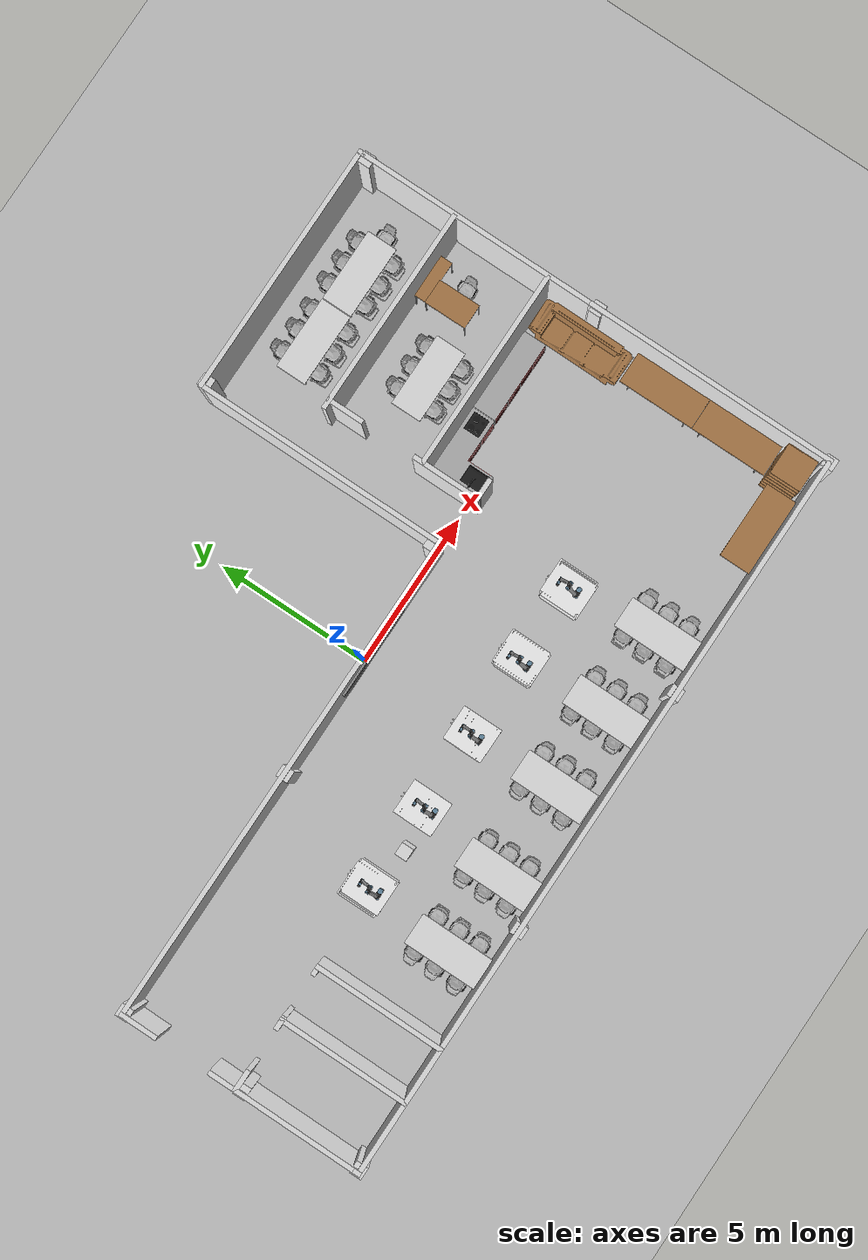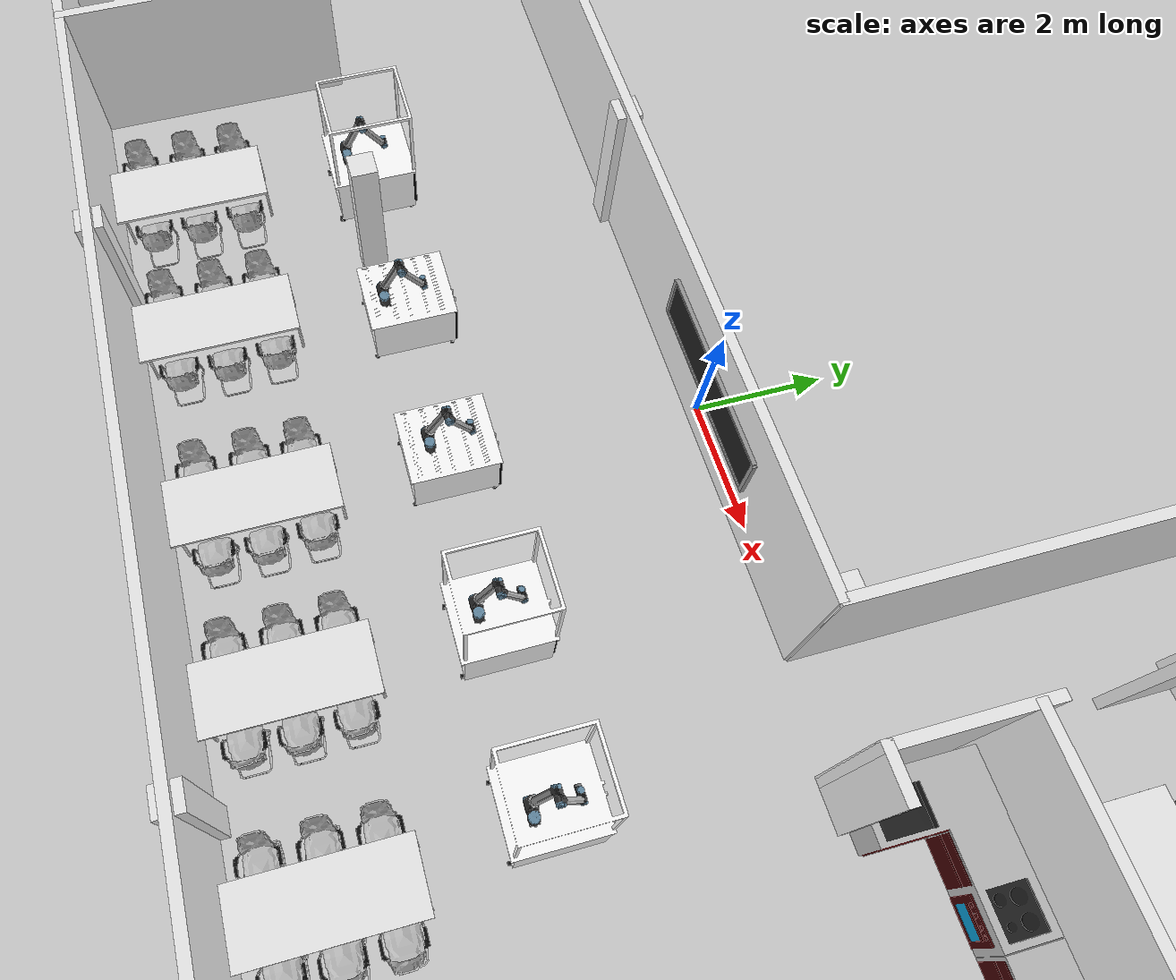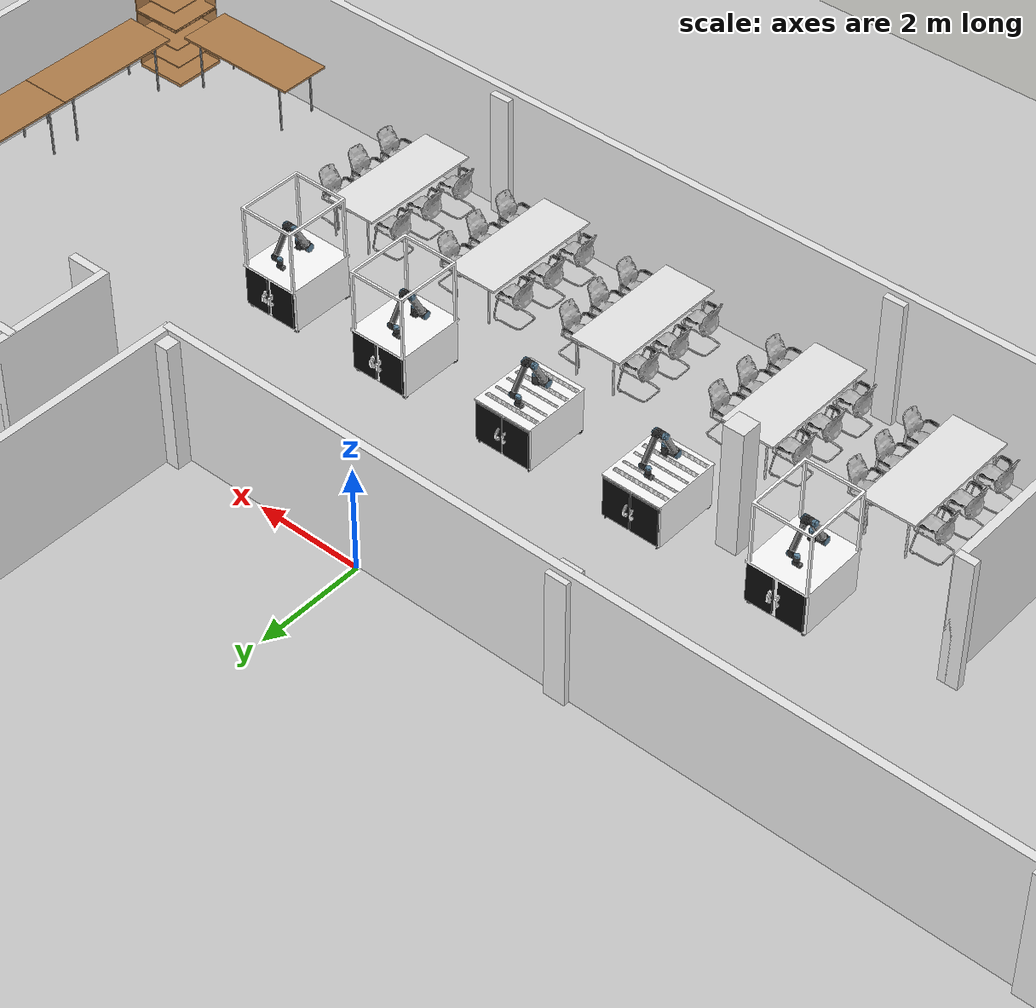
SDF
<sdf version='1.4'>
  <world name='default'>
    <!-- A global light source -->
    <include>
      <uri>model://sun</uri>
    </include>

    <!-- A ground plane -->

    <model name='ground_plane'>
      <static>1</static>
      <link name='link'>
        <collision name='collision'>
          <geometry>
            <plane>
              <normal>0 0 1</normal>
              <size>23.940 16.185</size>
            </plane>
          </geometry>
          <surface>
            <contact>
              <collide_bitmask>65535</collide_bitmask>
              <ode/>
            </contact>
            <friction>
              <ode>
                <mu>1000</mu>
                <mu2>1000</mu2>
              </ode>
              <torsional>
                <ode/>
              </torsional>
            </friction>
            <bounce/>
          </surface>
          <max_contacts>10</max_contacts>
        </collision>
        <visual name='visual'>
          <cast_shadows>0</cast_shadows>
          <geometry>
            <plane>
              <normal>0 0 1</normal>
              <size>23.94 16.185</size>
            </plane>
          </geometry>
          <material>
            <script>
	            <uri>model://erica/elements/bot10/materials/scripts</uri>
              <uri>model://erica/elements/bot10/materials/textures</uri>
              <name>bot10</name>
            </script>
          </material>
        </visual>
        <self_collide>0</self_collide>
        <kinematic>0</kinematic>
      </link>
    </model>

    <physics type="ode">
      <real_time_update_rate>1000.0</real_time_update_rate>
      <max_step_size>0.001</max_step_size>
      <real_time_factor>1</real_time_factor>
      <ode>
        <solver>
          <type>quick</type>
          <iters>150</iters>
          <precon_iters>0</precon_iters>
          <sor>1.400000</sor>
          <use_dynamic_moi_rescaling>1</use_dynamic_moi_rescaling>
        </solver>
        <constraints>
          <cfm>0.00001</cfm>
          <erp>0.2</erp>
          <contact_max_correcting_vel>2000.000000</contact_max_correcting_vel>
          <contact_surface_layer>0.01000</contact_surface_layer>
        </constraints>
      </ode>
    </physics>

    <!-- Load world -->
    <include>
      <pose>0.015148 -0.012339 0 0 0 0</pose>
      <uri>model://erica</uri>
    </include>

    <scene>
      <ambient>0.4 0.4 0.4 1</ambient>
      <background>0.7 0.7 0.7 1</background>
      <shadows>true</shadows>
    </scene>

    <gui fullscreen='0'>
      <camera name='user_camera'>
        <pose>0.8 0.0 12.0 0 1.5708 0</pose>
        <view_controller>orbit</view_controller>
      </camera>
    </gui>
  </world>
</sdf>

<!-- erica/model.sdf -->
<sdf version='1.6'>
  <model name='erica'>
    <model name='table1_chair'>
      <model name='h_chair'>
        <link name='link_0'>
          <pose frame=''>0 0 0 0 -0 0</pose>
          <inertial>
            <mass>1</mass>
            <inertia>
              <ixx>0.166667</ixx>
              <ixy>0</ixy>
              <ixz>0</ixz>
              <iyy>0.166667</iyy>
              <iyz>0</iyz>
              <izz>0.166667</izz>
            </inertia>
            <pose frame=''>0 0 0 0 -0 0</pose>
          </inertial>
          <gravity>1</gravity>
          <self_collide>0</self_collide>
          <kinematic>0</kinematic>
          <visual name='visual'>
            <pose frame=''>0 0 0 0 -0 0</pose>
            <geometry>
              <mesh>
                <uri>model://erica/elements/h_chair/meshes/chair.dae</uri>
                <scale>1 1 1</scale>
              </mesh>
            </geometry>
          </visual>
          <collision name='collision_4'>
            <laser_retro>0</laser_retro>
            <max_contacts>10</max_contacts>
            <pose frame=''>0 0 0.41 0 -0 0</pose>
            <geometry>
              <box>
                <size>0.5 0.45 0.05</size>
              </box>
            </geometry>
            <surface>
              <friction>
                <ode>
                  <mu>1</mu>
                  <mu2>1</mu2>
                  <fdir1>0 0 0</fdir1>
                  <slip1>0</slip1>
                  <slip2>0</slip2>
                </ode>
                <torsional>
                  <coefficient>1</coefficient>
                  <patch_radius>0</patch_radius>
                  <surface_radius>0</surface_radius>
                  <use_patch_radius>1</use_patch_radius>
                  <ode>
                    <slip>0</slip>
                  </ode>
                </torsional>
              </friction>
              <bounce>
                <restitution_coefficient>0</restitution_coefficient>
                <threshold>1e+06</threshold>
              </bounce>
              <contact>
                <collide_without_contact>0</collide_without_contact>
                <collide_without_contact_bitmask>1</collide_without_contact_bitmask>
                <collide_bitmask>1</collide_bitmask>
                <ode>
                  <soft_cfm>0</soft_cfm>
                  <soft_erp>0.2</soft_erp>
                  <kp>1e+13</kp>
                  <kd>1</kd>
                  <max_vel>0.01</max_vel>
                  <min_depth>0</min_depth>
                </ode>
                <bullet>
                  <split_impulse>1</split_impulse>
                  <split_impulse_penetration_threshold>-0.01</split_impulse_penetration_threshold>
                  <soft_cfm>0</soft_cfm>
                  <soft_erp>0.2</soft_erp>
                  <kp>1e+13</kp>
                  <kd>1</kd>
                </bullet>
              </contact>
            </surface>
          </collision>
          <collision name='collision_3'>
            <laser_retro>0</laser_retro>
            <max_contacts>10</max_contacts>
            <pose frame=''>0 0 0.01 0 -0 0</pose>
            <geometry>
              <box>
                <size>0.5 0.45 0.01</size>
              </box>
            </geometry>
            <surface>
              <friction>
                <ode>
                  <mu>1</mu>
                  <mu2>1</mu2>
                  <fdir1>0 0 0</fdir1>
                  <slip1>0</slip1>
                  <slip2>0</slip2>
                </ode>
                <torsional>
                  <coefficient>1</coefficient>
                  <patch_radius>0</patch_radius>
                  <surface_radius>0</surface_radius>
                  <use_patch_radius>1</use_patch_radius>
                  <ode>
                    <slip>0</slip>
                  </ode>
                </torsional>
              </friction>
              <bounce>
                <restitution_coefficient>0</restitution_coefficient>
                <threshold>1e+06</threshold>
              </bounce>
              <contact>
                <collide_without_contact>0</collide_without_contact>
                <collide_without_contact_bitmask>1</collide_without_contact_bitmask>
                <collide_bitmask>1</collide_bitmask>
                <ode>
                  <soft_cfm>0</soft_cfm>
                  <soft_erp>0.2</soft_erp>
                  <kp>1e+13</kp>
                  <kd>1</kd>
                  <max_vel>0.01</max_vel>
                  <min_depth>0</min_depth>
                </ode>
                <bullet>
                  <split_impulse>1</split_impulse>
                  <split_impulse_penetration_threshold>-0.01</split_impulse_penetration_threshold>
                  <soft_cfm>0</soft_cfm>
                  <soft_erp>0.2</soft_erp>
                  <kp>1e+13</kp>
                  <kd>1</kd>
                </bullet>
              </contact>
            </surface>
          </collision>
          <collision name='collision_5'>
            <laser_retro>0</laser_retro>
            <max_contacts>10</max_contacts>
            <pose frame=''>-0.2 0 0.65 0 -0 0</pose>
            <geometry>
              <box>
                <size>0.05 0.45 0.45</size>
              </box>
            </geometry>
            <surface>
              <friction>
                <ode>
                  <mu>1</mu>
                  <mu2>1</mu2>
                  <fdir1>0 0 0</fdir1>
                  <slip1>0</slip1>
                  <slip2>0</slip2>
                </ode>
                <torsional>
                  <coefficient>1</coefficient>
                  <patch_radius>0</patch_radius>
                  <surface_radius>0</surface_radius>
                  <use_patch_radius>1</use_patch_radius>
                  <ode>
                    <slip>0</slip>
                  </ode>
                </torsional>
              </friction>
              <bounce>
                <restitution_coefficient>0</restitution_coefficient>
                <threshold>1e+06</threshold>
              </bounce>
              <contact>
                <collide_without_contact>0</collide_without_contact>
                <collide_without_contact_bitmask>1</collide_without_contact_bitmask>
                <collide_bitmask>1</collide_bitmask>
                <ode>
                  <soft_cfm>0</soft_cfm>
                  <soft_erp>0.2</soft_erp>
                  <kp>1e+13</kp>
                  <kd>1</kd>
                  <max_vel>0.01</max_vel>
                  <min_depth>0</min_depth>
                </ode>
                <bullet>
                  <split_impulse>1</split_impulse>
                  <split_impulse_penetration_threshold>-0.01</split_impulse_penetration_threshold>
                  <soft_cfm>0</soft_cfm>
                  <soft_erp>0.2</soft_erp>
                  <kp>1e+13</kp>
                  <kd>1</kd>
                </bullet>
              </contact>
            </surface>
          </collision>
          <collision name='collision_6'>
            <laser_retro>0</laser_retro>
            <max_contacts>10</max_contacts>
            <pose frame=''>0.2 -0.25 0.35 0 -0 0</pose>
            <geometry>
              <cylinder>
                <radius>0.01</radius>
                <length>0.7</length>
              </cylinder>
            </geometry>
            <surface>
              <friction>
                <ode>
                  <mu>1</mu>
                  <mu2>1</mu2>
                  <fdir1>0 0 0</fdir1>
                  <slip1>0</slip1>
                  <slip2>0</slip2>
                </ode>
                <torsional>
                  <coefficient>1</coefficient>
                  <patch_radius>0</patch_radius>
                  <surface_radius>0</surface_radius>
                  <use_patch_radius>1</use_patch_radius>
                  <ode>
                    <slip>0</slip>
                  </ode>
                </torsional>
              </friction>
              <bounce>
                <restitution_coefficient>0</restitution_coefficient>
                <threshold>1e+06</threshold>
              </bounce>
              <contact>
                <collide_without_contact>0</collide_without_contact>
                <collide_without_contact_bitmask>1</collide_without_contact_bitmask>
                <collide_bitmask>1</collide_bitmask>
                <ode>
                  <soft_cfm>0</soft_cfm>
                  <soft_erp>0.2</soft_erp>
                  <kp>1e+13</kp>
                  <kd>1</kd>
                  <max_vel>0.01</max_vel>
                  <min_depth>0</min_depth>
                </ode>
                <bullet>
                  <split_impulse>1</split_impulse>
                  <split_impulse_penetration_threshold>-0.01</split_impulse_penetration_threshold>
                  <soft_cfm>0</soft_cfm>
                  <soft_erp>0.2</soft_erp>
                  <kp>1e+13</kp>
                  <kd>1</kd>
                </bullet>
              </contact>
            </surface>
          </collision>
          <collision name='collision_7'>
            <laser_retro>0</laser_retro>
            <max_contacts>10</max_contacts>
            <pose frame=''>0.2 0.25 0.35 0 -0 0</pose>
            <geometry>
              <cylinder>
                <radius>0.01</radius>
                <length>0.7</length>
              </cylinder>
            </geometry>
            <surface>
              <friction>
                <ode>
                  <mu>1</mu>
                  <mu2>1</mu2>
                  <fdir1>0 0 0</fdir1>
                  <slip1>0</slip1>
                  <slip2>0</slip2>
                </ode>
                <torsional>
                  <coefficient>1</coefficient>
                  <patch_radius>0</patch_radius>
                  <surface_radius>0</surface_radius>
                  <use_patch_radius>1</use_patch_radius>
                  <ode>
                    <slip>0</slip>
                  </ode>
                </torsional>
              </friction>
              <bounce>
                <restitution_coefficient>0</restitution_coefficient>
                <threshold>1e+06</threshold>
              </bounce>
              <contact>
                <collide_without_contact>0</collide_without_contact>
                <collide_without_contact_bitmask>1</collide_without_contact_bitmask>
                <collide_bitmask>1</collide_bitmask>
                <ode>
                  <soft_cfm>0</soft_cfm>
                  <soft_erp>0.2</soft_erp>
                  <kp>1e+13</kp>
                  <kd>1</kd>
                  <max_vel>0.01</max_vel>
                  <min_depth>0</min_depth>
                </ode>
                <bullet>
                  <split_impulse>1</split_impulse>
                  <split_impulse_penetration_threshold>-0.01</split_impulse_penetration_threshold>
                  <soft_cfm>0</soft_cfm>
                  <soft_erp>0.2</soft_erp>
                  <kp>1e+13</kp>
                  <kd>1</kd>
                </bullet>
              </contact>
            </surface>
          </collision>
        </link>
        <static>1</static>
        <allow_auto_disable>1</allow_auto_disable>
        <pose frame=''>-0.65015 0.677818 0 0 -0 0</pose>
      </model>
      <model name='h_chair_clone'>
        <link name='link_0'>
          <pose frame=''>0 0 0 0 -0 0</pose>
          <inertial>
            <mass>1</mass>
            <inertia>
              <ixx>0.166667</ixx>
              <ixy>0</ixy>
              <ixz>0</ixz>
              <iyy>0.166667</iyy>
              <iyz>0</iyz>
              <izz>0.166667</izz>
            </inertia>
            <pose frame=''>0 0 0 0 -0 0</pose>
          </inertial>
          <gravity>1</gravity>
          <self_collide>0</self_collide>
          <kinematic>0</kinematic>
          <visual name='visual'>
            <pose frame=''>0 0 0 0 -0 0</pose>
            <geometry>
              <mesh>
                <uri>model://erica/elements/h_chair/meshes/chair.dae</uri>
                <scale>1 1 1</scale>
              </mesh>
            </geometry>
          </visual>
          <collision name='collision_4'>
            <laser_retro>0</laser_retro>
            <max_contacts>10</max_contacts>
            <pose frame=''>0 0 0.41 0 -0 0</pose>
            <geometry>
              <box>
                <size>0.5 0.45 0.05</size>
              </box>
            </geometry>
            <surface>
              <friction>
                <ode>
                  <mu>1</mu>
                  <mu2>1</mu2>
                  <fdir1>0 0 0</fdir1>
                  <slip1>0</slip1>
                  <slip2>0</slip2>
                </ode>
                <torsional>
                  <coefficient>1</coefficient>
                  <patch_radius>0</patch_radius>
                  <surface_radius>0</surface_radius>
                  <use_patch_radius>1</use_patch_radius>
                  <ode>
                    <slip>0</slip>
                  </ode>
                </torsional>
              </friction>
              <bounce>
                <restitution_coefficient>0</restitution_coefficient>
                <threshold>1e+06</threshold>
              </bounce>
              <contact>
                <collide_without_contact>0</collide_without_contact>
                <collide_without_contact_bitmask>1</collide_without_contact_bitmask>
                <collide_bitmask>1</collide_bitmask>
                <ode>
                  <soft_cfm>0</soft_cfm>
                  <soft_erp>0.2</soft_erp>
                  <kp>1e+13</kp>
                  <kd>1</kd>
                  <max_vel>0.01</max_vel>
                  <min_depth>0</min_depth>
                </ode>
                <bullet>
                  <split_impulse>1</split_impulse>
                  <split_impulse_penetration_threshold>-0.01</split_impulse_penetration_threshold>
                  <soft_cfm>0</soft_cfm>
                  <soft_erp>0.2</soft_erp>
                  <kp>1e+13</kp>
                  <kd>1</kd>
                </bullet>
              </contact>
            </surface>
          </collision>
          <collision name='collision_3'>
            <laser_retro>0</laser_retro>
            <max_contacts>10</max_contacts>
            <pose frame=''>0 0 0.01 0 -0 0</pose>
            <geometry>
              <box>
                <size>0.5 0.45 0.01</size>
              </box>
            </geometry>
            <surface>
              <friction>
                <ode>
                  <mu>1</mu>
                  <mu2>1</mu2>
                  <fdir1>0 0 0</fdir1>
                  <slip1>0</slip1>
                  <slip2>0</slip2>
                </ode>
                <torsional>
                  <coefficient>1</coefficient>
                  <patch_radius>0</patch_radius>
                  <surface_radius>0</surface_radius>
                  <use_patch_radius>1</use_patch_radius>
                  <ode>
                    <slip>0</slip>
                  </ode>
                </torsional>
              </friction>
              <bounce>
                <restitution_coefficient>0</restitution_coefficient>
                <threshold>1e+06</threshold>
              </bounce>
              <contact>
                <collide_without_contact>0</collide_without_contact>
                <collide_without_contact_bitmask>1</collide_without_contact_bitmask>
                <collide_bitmask>1</collide_bitmask>
                <ode>
                  <soft_cfm>0</soft_cfm>
                  <soft_erp>0.2</soft_erp>
                  <kp>1e+13</kp>
                  <kd>1</kd>
                  <max_vel>0.01</max_vel>
                  <min_depth>0</min_depth>
                </ode>
                <bullet>
                  <split_impulse>1</split_impulse>
                  <split_impulse_penetration_threshold>-0.01</split_impulse_penetration_threshold>
                  <soft_cfm>0</soft_cfm>
                  <soft_erp>0.2</soft_erp>
                  <kp>1e+13</kp>
                  <kd>1</kd>
                </bullet>
              </contact>
            </surface>
          </collision>
          <collision name='collision_5'>
            <laser_retro>0</laser_retro>
            <max_contacts>10</max_contacts>
            <pose frame=''>-0.2 0 0.65 0 -0 0</pose>
            <geometry>
              <box>
                <size>0.05 0.45 0.45</size>
              </box>
            </geometry>
            <surface>
              <friction>
                <ode>
                  <mu>1</mu>
                  <mu2>1</mu2>
                  <fdir1>0 0 0</fdir1>
                  <slip1>0</slip1>
                  <slip2>0</slip2>
                </ode>
                <torsional>
                  <coefficient>1</coefficient>
                  <patch_radius>0</patch_radius>
                  <surface_radius>0</surface_radius>
                  <use_patch_radius>1</use_patch_radius>
                  <ode>
                    <slip>0</slip>
                  </ode>
                </torsional>
              </friction>
              <bounce>
                <restitution_coefficient>0</restitution_coefficient>
                <threshold>1e+06</threshold>
              </bounce>
              <contact>
                <collide_without_contact>0</collide_without_contact>
                <collide_without_contact_bitmask>1</collide_without_contact_bitmask>
                <collide_bitmask>1</collide_bitmask>
                <ode>
                  <soft_cfm>0</soft_cfm>
                  <soft_erp>0.2</soft_erp>
                  <kp>1e+13</kp>
                  <kd>1</kd>
                  <max_vel>0.01</max_vel>
                  <min_depth>0</min_depth>
                </ode>
                <bullet>
                  <split_impulse>1</split_impulse>
                  <split_impulse_penetration_threshold>-0.01</split_impulse_penetration_threshold>
                  <soft_cfm>0</soft_cfm>
                  <soft_erp>0.2</soft_erp>
                  <kp>1e+13</kp>
                  <kd>1</kd>
                </bullet>
              </contact>
            </surface>
          </collision>
          <collision name='collision_6'>
            <laser_retro>0</laser_retro>
            <max_contacts>10</max_contacts>
            <pose frame=''>0.2 -0.25 0.35 0 -0 0</pose>
            <geometry>
              <cylinder>
                <radius>0.01</radius>
                <length>0.7</length>
              </cylinder>
            </geometry>
            <surface>
              <friction>
                <ode>
                  <mu>1</mu>
                  <mu2>1</mu2>
                  <fdir1>0 0 0</fdir1>
                  <slip1>0</slip1>
                  <slip2>0</slip2>
                </ode>
                <torsional>
                  <coefficient>1</coefficient>
                  <patch_radius>0</patch_radius>
                  <surface_radius>0</surface_radius>
                  <use_patch_radius>1</use_patch_radius>
                  <ode>
                    <slip>0</slip>
                  </ode>
                </torsional>
              </friction>
              <bounce>
                <restitution_coefficient>0</restitution_coefficient>
                <threshold>1e+06</threshold>
              </bounce>
              <contact>
                <collide_without_contact>0</collide_without_contact>
                <collide_without_contact_bitmask>1</collide_without_contact_bitmask>
                <collide_bitmask>1</collide_bitmask>
                <ode>
                  <soft_cfm>0</soft_cfm>
                  <soft_erp>0.2</soft_erp>
                  <kp>1e+13</kp>
                  <kd>1</kd>
                  <max_vel>0.01</max_vel>
                  <min_depth>0</min_depth>
                </ode>
                <bullet>
                  <split_impulse>1</split_impulse>
                  <split_impulse_penetration_threshold>-0.01</split_impulse_penetration_threshold>
                  <soft_cfm>0</soft_cfm>
                  <soft_erp>0.2</soft_erp>
                  <kp>1e+13</kp>
                  <kd>1</kd>
                </bullet>
              </contact>
            </surface>
          </collision>
          <collision name='collision_7'>
            <laser_retro>0</laser_retro>
            <max_contacts>10</max_contacts>
            <pose frame=''>0.2 0.25 0.35 0 -0 0</pose>
            <geometry>
              <cylinder>
                <radius>0.01</radius>
                <length>0.7</length>
              </cylinder>
            </geometry>
            <surface>
              <friction>
                <ode>
                  <mu>1</mu>
                  <mu2>1</mu2>
                  <fdir1>0 0 0</fdir1>
                  <slip1>0</slip1>
                  <slip2>0</slip2>
                </ode>
                <torsional>
                  <coefficient>1</coefficient>
                  <patch_radius>0</patch_radius>
                  <surface_radius>0</surface_radius>
                  <use_patch_radius>1</use_patch_radius>
                  <ode>
                    <slip>0</slip>
                  </ode>
                </torsional>
              </friction>
              <bounce>
                <restitution_coefficient>0</restitution_coefficient>
                <threshold>1e+06</threshold>
              </bounce>
              <contact>
                <collide_without_contact>0</collide_without_contact>
                <collide_without_contact_bitmask>1</collide_without_contact_bitmask>
                <collide_bitmask>1</collide_bitmask>
                <ode>
                  <soft_cfm>0</soft_cfm>
                  <soft_erp>0.2</soft_erp>
                  <kp>1e+13</kp>
                  <kd>1</kd>
                  <max_vel>0.01</max_vel>
                  <min_depth>0</min_depth>
                </ode>
                <bullet>
                  <split_impulse>1</split_impulse>
                  <split_impulse_penetration_threshold>-0.01</split_impulse_penetration_threshold>
                  <soft_cfm>0</soft_cfm>
                  <soft_erp>0.2</soft_erp>
                  <kp>1e+13</kp>
                  <kd>1</kd>
                </bullet>
              </contact>
            </surface>
          </collision>
        </link>
        <static>1</static>
        <allow_auto_disable>1</allow_auto_disable>
        <pose frame=''>-0.668032 -0.060178 0 0 -0 0</pose>
      </model>
      <model name='h_chair_clone_0'>
        <link name='link_0'>
          <pose frame=''>0 0 0 0 -0 0</pose>
          <inertial>
            <mass>1</mass>
            <inertia>
              <ixx>0.166667</ixx>
              <ixy>0</ixy>
              <ixz>0</ixz>
              <iyy>0.166667</iyy>
              <iyz>0</iyz>
              <izz>0.166667</izz>
            </inertia>
            <pose frame=''>0 0 0 0 -0 0</pose>
          </inertial>
          <gravity>1</gravity>
          <self_collide>0</self_collide>
          <kinematic>0</kinematic>
          <visual name='visual'>
            <pose frame=''>0 0 0 0 -0 0</pose>
            <geometry>
              <mesh>
                <uri>model://erica/elements/h_chair/meshes/chair.dae</uri>
                <scale>1 1 1</scale>
              </mesh>
            </geometry>
          </visual>
          <collision name='collision_4'>
            <laser_retro>0</laser_retro>
            <max_contacts>10</max_contacts>
            <pose frame=''>0 0 0.41 0 -0 0</pose>
            <geometry>
              <box>
                <size>0.5 0.45 0.05</size>
              </box>
            </geometry>
            <surface>
              <friction>
                <ode>
                  <mu>1</mu>
                  <mu2>1</mu2>
                  <fdir1>0 0 0</fdir1>
                  <slip1>0</slip1>
                  <slip2>0</slip2>
                </ode>
                <torsional>
                  <coefficient>1</coefficient>
                  <patch_radius>0</patch_radius>
                  <surface_radius>0</surface_radius>
                  <use_patch_radius>1</use_patch_radius>
                  <ode>
                    <slip>0</slip>
                  </ode>
                </torsional>
              </friction>
              <bounce>
                <restitution_coefficient>0</restitution_coefficient>
                <threshold>1e+06</threshold>
              </bounce>
              <contact>
                <collide_without_contact>0</collide_without_contact>
                <collide_without_contact_bitmask>1</collide_without_contact_bitmask>
                <collide_bitmask>1</collide_bitmask>
                <ode>
                  <soft_cfm>0</soft_cfm>
                  <soft_erp>0.2</soft_erp>
                  <kp>1e+13</kp>
                  <kd>1</kd>
                  <max_vel>0.01</max_vel>
                  <min_depth>0</min_depth>
                </ode>
                <bullet>
                  <split_impulse>1</split_impulse>
                  <split_impulse_penetration_threshold>-0.01</split_impulse_penetration_threshold>
                  <soft_cfm>0</soft_cfm>
                  <soft_erp>0.2</soft_erp>
                  <kp>1e+13</kp>
                  <kd>1</kd>
                </bullet>
              </contact>
            </surface>
          </collision>
          <collision name='collision_3'>
            <laser_retro>0</laser_retro>
            <max_contacts>10</max_contacts>
            <pose frame=''>0 0 0.01 0 -0 0</pose>
            <geometry>
              <box>
                <size>0.5 0.45 0.01</size>
              </box>
            </geometry>
            <surface>
              <friction>
                <ode>
                  <mu>1</mu>
                  <mu2>1</mu2>
                  <fdir1>0 0 0</fdir1>
                  <slip1>0</slip1>
                  <slip2>0</slip2>
                </ode>
                <torsional>
                  <coefficient>1</coefficient>
                  <patch_radius>0</patch_radius>
                  <surface_radius>0</surface_radius>
                  <use_patch_radius>1</use_patch_radius>
                  <ode>
                    <slip>0</slip>
                  </ode>
                </torsional>
              </friction>
              <bounce>
                <restitution_coefficient>0</restitution_coefficient>
                <threshold>1e+06</threshold>
              </bounce>
              <contact>
                <collide_without_contact>0</collide_without_contact>
                <collide_without_contact_bitmask>1</collide_without_contact_bitmask>
                <collide_bitmask>1</collide_bitmask>
                <ode>
                  <soft_cfm>0</soft_cfm>
                  <soft_erp>0.2</soft_erp>
                  <kp>1e+13</kp>
                  <kd>1</kd>
                  <max_vel>0.01</max_vel>
                  <min_depth>0</min_depth>
                </ode>
                <bullet>
                  <split_impulse>1</split_impulse>
                  <split_impulse_penetration_threshold>-0.01</split_impulse_penetration_threshold>
                  <soft_cfm>0</soft_cfm>
                  <soft_erp>0.2</soft_erp>
                  <kp>1e+13</kp>
                  <kd>1</kd>
                </bullet>
              </contact>
            </surface>
          </collision>
          <collision name='collision_5'>
            <laser_retro>0</laser_retro>
            <max_contacts>10</max_contacts>
            <pose frame=''>-0.2 0 0.65 0 -0 0</pose>
            <geometry>
              <box>
                <size>0.05 0.45 0.45</size>
              </box>
            </geometry>
            <surface>
              <friction>
                <ode>
                  <mu>1</mu>
                  <mu2>1</mu2>
                  <fdir1>0 0 0</fdir1>
                  <slip1>0</slip1>
                  <slip2>0</slip2>
                </ode>
                <torsional>
                  <coefficient>1</coefficient>
                  <patch_radius>0</patch_radius>
                  <surface_radius>0</surface_radius>
                  <use_patch_radius>1</use_patch_radius>
                  <ode>
                    <slip>0</slip>
                  </ode>
                </torsional>
              </friction>
              <bounce>
                <restitution_coefficient>0</restitution_coefficient>
                <threshold>1e+06</threshold>
              </bounce>
              <contact>
                <collide_without_contact>0</collide_without_contact>
                <collide_without_contact_bitmask>1</collide_without_contact_bitmask>
                <collide_bitmask>1</collide_bitmask>
                <ode>
                  <soft_cfm>0</soft_cfm>
                  <soft_erp>0.2</soft_erp>
                  <kp>1e+13</kp>
                  <kd>1</kd>
                  <max_vel>0.01</max_vel>
                  <min_depth>0</min_depth>
                </ode>
                <bullet>
                  <split_impulse>1</split_impulse>
                  <split_impulse_penetration_threshold>-0.01</split_impulse_penetration_threshold>
                  <soft_cfm>0</soft_cfm>
                  <soft_erp>0.2</soft_erp>
                  <kp>1e+13</kp>
                  <kd>1</kd>
                </bullet>
              </contact>
            </surface>
          </collision>
          <collision name='collision_6'>
            <laser_retro>0</laser_retro>
            <max_contacts>10</max_contacts>
            <pose frame=''>0.2 -0.25 0.35 0 -0 0</pose>
            <geometry>
              <cylinder>
                <radius>0.01</radius>
                <length>0.7</length>
              </cylinder>
            </geometry>
            <surface>
              <friction>
                <ode>
                  <mu>1</mu>
                  <mu2>1</mu2>
                  <fdir1>0 0 0</fdir1>
                  <slip1>0</slip1>
                  <slip2>0</slip2>
                </ode>
                <torsional>
                  <coefficient>1</coefficient>
                  <patch_radius>0</patch_radius>
                  <surface_radius>0</surface_radius>
                  <use_patch_radius>1</use_patch_radius>
                  <ode>
                    <slip>0</slip>
                  </ode>
                </torsional>
              </friction>
              <bounce>
                <restitution_coefficient>0</restitution_coefficient>
                <threshold>1e+06</threshold>
              </bounce>
              <contact>
                <collide_without_contact>0</collide_without_contact>
                <collide_without_contact_bitmask>1</collide_without_contact_bitmask>
                <collide_bitmask>1</collide_bitmask>
                <ode>
                  <soft_cfm>0</soft_cfm>
                  <soft_erp>0.2</soft_erp>
                  <kp>1e+13</kp>
                  <kd>1</kd>
                  <max_vel>0.01</max_vel>
                  <min_depth>0</min_depth>
                </ode>
                <bullet>
                  <split_impulse>1</split_impulse>
                  <split_impulse_penetration_threshold>-0.01</split_impulse_penetration_threshold>
                  <soft_cfm>0</soft_cfm>
                  <soft_erp>0.2</soft_erp>
                  <kp>1e+13</kp>
                  <kd>1</kd>
                </bullet>
              </contact>
            </surface>
          </collision>
          <collision name='collision_7'>
            <laser_retro>0</laser_retro>
            <max_contacts>10</max_contacts>
            <pose frame=''>0.2 0.25 0.35 0 -0 0</pose>
            <geometry>
              <cylinder>
                <radius>0.01</radius>
                <length>0.7</length>
              </cylinder>
            </geometry>
            <surface>
              <friction>
                <ode>
                  <mu>1</mu>
                  <mu2>1</mu2>
                  <fdir1>0 0 0</fdir1>
                  <slip1>0</slip1>
                  <slip2>0</slip2>
                </ode>
                <torsional>
                  <coefficient>1</coefficient>
                  <patch_radius>0</patch_radius>
                  <surface_radius>0</surface_radius>
                  <use_patch_radius>1</use_patch_radius>
                  <ode>
                    <slip>0</slip>
                  </ode>
                </torsional>
              </friction>
              <bounce>
                <restitution_coefficient>0</restitution_coefficient>
                <threshold>1e+06</threshold>
              </bounce>
              <contact>
                <collide_without_contact>0</collide_without_contact>
                <collide_without_contact_bitmask>1</collide_without_contact_bitmask>
                <collide_bitmask>1</collide_bitmask>
                <ode>
                  <soft_cfm>0</soft_cfm>
                  <soft_erp>0.2</soft_erp>
                  <kp>1e+13</kp>
                  <kd>1</kd>
                  <max_vel>0.01</max_vel>
                  <min_depth>0</min_depth>
                </ode>
                <bullet>
                  <split_impulse>1</split_impulse>
                  <split_impulse_penetration_threshold>-0.01</split_impulse_penetration_threshold>
                  <soft_cfm>0</soft_cfm>
                  <soft_erp>0.2</soft_erp>
                  <kp>1e+13</kp>
                  <kd>1</kd>
                </bullet>
              </contact>
            </surface>
          </collision>
        </link>
        <static>1</static>
        <allow_auto_disable>1</allow_auto_disable>
        <pose frame=''>-0.679941 -0.822301 0 0 -0 0</pose>
      </model>
      <model name='h_chair_clone_1'>
        <link name='link_0'>
          <pose frame=''>0 0 0 0 -0 0</pose>
          <inertial>
            <mass>1</mass>
            <inertia>
              <ixx>0.166667</ixx>
              <ixy>0</ixy>
              <ixz>0</ixz>
              <iyy>0.166667</iyy>
              <iyz>0</iyz>
              <izz>0.166667</izz>
            </inertia>
            <pose frame=''>0 0 0 0 -0 0</pose>
          </inertial>
          <gravity>1</gravity>
          <self_collide>0</self_collide>
          <kinematic>0</kinematic>
          <visual name='visual'>
            <pose frame=''>0 0 0 0 -0 0</pose>
            <geometry>
              <mesh>
                <uri>model://erica/elements/h_chair/meshes/chair.dae</uri>
                <scale>1 1 1</scale>
              </mesh>
            </geometry>
          </visual>
          <collision name='collision_4'>
            <laser_retro>0</laser_retro>
            <max_contacts>10</max_contacts>
            <pose frame=''>0 0 0.41 0 -0 0</pose>
            <geometry>
              <box>
                <size>0.5 0.45 0.05</size>
              </box>
            </geometry>
            <surface>
              <friction>
                <ode>
                  <mu>1</mu>
                  <mu2>1</mu2>
                  <fdir1>0 0 0</fdir1>
                  <slip1>0</slip1>
                  <slip2>0</slip2>
                </ode>
                <torsional>
                  <coefficient>1</coefficient>
                  <patch_radius>0</patch_radius>
                  <surface_radius>0</surface_radius>
                  <use_patch_radius>1</use_patch_radius>
                  <ode>
                    <slip>0</slip>
                  </ode>
                </torsional>
              </friction>
              <bounce>
                <restitution_coefficient>0</restitution_coefficient>
                <threshold>1e+06</threshold>
              </bounce>
              <contact>
                <collide_without_contact>0</collide_without_contact>
                <collide_without_contact_bitmask>1</collide_without_contact_bitmask>
                <collide_bitmask>1</collide_bitmask>
                <ode>
                  <soft_cfm>0</soft_cfm>
                  <soft_erp>0.2</soft_erp>
                  <kp>1e+13</kp>
                  <kd>1</kd>
                  <max_vel>0.01</max_vel>
                  <min_depth>0</min_depth>
                </ode>
                <bullet>
                  <split_impulse>1</split_impulse>
                  <split_impulse_penetration_threshold>-0.01</split_impulse_penetration_threshold>
                  <soft_cfm>0</soft_cfm>
                  <soft_erp>0.2</soft_erp>
                  <kp>1e+13</kp>
                  <kd>1</kd>
                </bullet>
              </contact>
            </surface>
          </collision>
          <collision name='collision_3'>
            <laser_retro>0</laser_retro>
            <max_contacts>10</max_contacts>
            <pose frame=''>0 0 0.01 0 -0 0</pose>
            <geometry>
              <box>
                <size>0.5 0.45 0.01</size>
              </box>
            </geometry>
            <surface>
              <friction>
                <ode>
                  <mu>1</mu>
                  <mu2>1</mu2>
                  <fdir1>0 0 0</fdir1>
                  <slip1>0</slip1>
                  <slip2>0</slip2>
                </ode>
                <torsional>
                  <coefficient>1</coefficient>
                  <patch_radius>0</patch_radius>
                  <surface_radius>0</surface_radius>
                  <use_patch_radius>1</use_patch_radius>
                  <ode>
                    <slip>0</slip>
                  </ode>
                </torsional>
              </friction>
              <bounce>
                <restitution_coefficient>0</restitution_coefficient>
                <threshold>1e+06</threshold>
              </bounce>
              <contact>
                <collide_without_contact>0</collide_without_contact>
                <collide_without_contact_bitmask>1</collide_without_contact_bitmask>
                <collide_bitmask>1</collide_bitmask>
                <ode>
                  <soft_cfm>0</soft_cfm>
                  <soft_erp>0.2</soft_erp>
                  <kp>1e+13</kp>
                  <kd>1</kd>
                  <max_vel>0.01</max_vel>
                  <min_depth>0</min_depth>
                </ode>
                <bullet>
                  <split_impulse>1</split_impulse>
                  <split_impulse_penetration_threshold>-0.01</split_impulse_penetration_threshold>
                  <soft_cfm>0</soft_cfm>
                  <soft_erp>0.2</soft_erp>
                  <kp>1e+13</kp>
                  <kd>1</kd>
                </bullet>
              </contact>
            </surface>
          </collision>
          <collision name='collision_5'>
            <laser_retro>0</laser_retro>
            <max_contacts>10</max_contacts>
            <pose frame=''>-0.2 0 0.65 0 -0 0</pose>
            <geometry>
              <box>
                <size>0.05 0.45 0.45</size>
              </box>
            </geometry>
            <surface>
              <friction>
                <ode>
                  <mu>1</mu>
                  <mu2>1</mu2>
                  <fdir1>0 0 0</fdir1>
                  <slip1>0</slip1>
                  <slip2>0</slip2>
                </ode>
                <torsional>
                  <coefficient>1</coefficient>
                  <patch_radius>0</patch_radius>
                  <surface_radius>0</surface_radius>
                  <use_patch_radius>1</use_patch_radius>
                  <ode>
                    <slip>0</slip>
                  </ode>
                </torsional>
              </friction>
              <bounce>
                <restitution_coefficient>0</restitution_coefficient>
                <threshold>1e+06</threshold>
              </bounce>
              <contact>
                <collide_without_contact>0</collide_without_contact>
                <collide_without_contact_bitmask>1</collide_without_contact_bitmask>
                <collide_bitmask>1</collide_bitmask>
                <ode>
                  <soft_cfm>0</soft_cfm>
                  <soft_erp>0.2</soft_erp>
                  <kp>1e+13</kp>
                  <kd>1</kd>
                  <max_vel>0.01</max_vel>
                  <min_depth>0</min_depth>
                </ode>
                <bullet>
                  <split_impulse>1</split_impulse>
                  <split_impulse_penetration_threshold>-0.01</split_impulse_penetration_threshold>
                  <soft_cfm>0</soft_cfm>
                  <soft_erp>0.2</soft_erp>
                  <kp>1e+13</kp>
                  <kd>1</kd>
                </bullet>
              </contact>
            </surface>
          </collision>
          <collision name='collision_6'>
            <laser_retro>0</laser_retro>
            <max_contacts>10</max_contacts>
            <pose frame=''>0.2 -0.25 0.35 0 -0 0</pose>
            <geometry>
              <cylinder>
                <radius>0.01</radius>
                <length>0.7</length>
              </cylinder>
            </geometry>
            <surface>
              <friction>
                <ode>
                  <mu>1</mu>
                  <mu2>1</mu2>
                  <fdir1>0 0 0</fdir1>
                  <slip1>0</slip1>
                  <slip2>0</slip2>
                </ode>
                <torsional>
                  <coefficient>1</coefficient>
                  <patch_radius>0</patch_radius>
                  <surface_radius>0</surface_radius>
                  <use_patch_radius>1</use_patch_radius>
                  <ode>
                    <slip>0</slip>
                  </ode>
                </torsional>
              </friction>
              <bounce>
                <restitution_coefficient>0</restitution_coefficient>
                <threshold>1e+06</threshold>
              </bounce>
              <contact>
                <collide_without_contact>0</collide_without_contact>
                <collide_without_contact_bitmask>1</collide_without_contact_bitmask>
                <collide_bitmask>1</collide_bitmask>
                <ode>
                  <soft_cfm>0</soft_cfm>
                  <soft_erp>0.2</soft_erp>
                  <kp>1e+13</kp>
                  <kd>1</kd>
                  <max_vel>0.01</max_vel>
                  <min_depth>0</min_depth>
                </ode>
                <bullet>
                  <split_impulse>1</split_impulse>
                  <split_impulse_penetration_threshold>-0.01</split_impulse_penetration_threshold>
                  <soft_cfm>0</soft_cfm>
                  <soft_erp>0.2</soft_erp>
                  <kp>1e+13</kp>
                  <kd>1</kd>
                </bullet>
              </contact>
            </surface>
          </collision>
          <collision name='collision_7'>
            <laser_retro>0</laser_retro>
            <max_contacts>10</max_contacts>
            <pose frame=''>0.2 0.25 0.35 0 -0 0</pose>
            <geometry>
              <cylinder>
                <radius>0.01</radius>
                <length>0.7</length>
              </cylinder>
            </geometry>
            <surface>
              <friction>
                <ode>
                  <mu>1</mu>
                  <mu2>1</mu2>
                  <fdir1>0 0 0</fdir1>
                  <slip1>0</slip1>
                  <slip2>0</slip2>
                </ode>
                <torsional>
                  <coefficient>1</coefficient>
                  <patch_radius>0</patch_radius>
                  <surface_radius>0</surface_radius>
                  <use_patch_radius>1</use_patch_radius>
                  <ode>
                    <slip>0</slip>
                  </ode>
                </torsional>
              </friction>
              <bounce>
                <restitution_coefficient>0</restitution_coefficient>
                <threshold>1e+06</threshold>
              </bounce>
              <contact>
                <collide_without_contact>0</collide_without_contact>
                <collide_without_contact_bitmask>1</collide_without_contact_bitmask>
                <collide_bitmask>1</collide_bitmask>
                <ode>
                  <soft_cfm>0</soft_cfm>
                  <soft_erp>0.2</soft_erp>
                  <kp>1e+13</kp>
                  <kd>1</kd>
                  <max_vel>0.01</max_vel>
                  <min_depth>0</min_depth>
                </ode>
                <bullet>
                  <split_impulse>1</split_impulse>
                  <split_impulse_penetration_threshold>-0.01</split_impulse_penetration_threshold>
                  <soft_cfm>0</soft_cfm>
                  <soft_erp>0.2</soft_erp>
                  <kp>1e+13</kp>
                  <kd>1</kd>
                </bullet>
              </contact>
            </surface>
          </collision>
        </link>
        <static>1</static>
        <allow_auto_disable>1</allow_auto_disable>
        <pose frame=''>0.664034 0.665185 0 0 -0 3.13853</pose>
      </model>
      <model name='h_chair_clone_1_clone'>
        <link name='link_0'>
          <pose frame=''>0 0 0 0 -0 0</pose>
          <inertial>
            <mass>1</mass>
            <inertia>
              <ixx>0.166667</ixx>
              <ixy>0</ixy>
              <ixz>0</ixz>
              <iyy>0.166667</iyy>
              <iyz>0</iyz>
              <izz>0.166667</izz>
            </inertia>
            <pose frame=''>0 0 0 0 -0 0</pose>
          </inertial>
          <gravity>1</gravity>
          <self_collide>0</self_collide>
          <kinematic>0</kinematic>
          <visual name='visual'>
            <pose frame=''>0 0 0 0 -0 0</pose>
            <geometry>
              <mesh>
                <uri>model://erica/elements/h_chair/meshes/chair.dae</uri>
                <scale>1 1 1</scale>
              </mesh>
            </geometry>
          </visual>
          <collision name='collision_4'>
            <laser_retro>0</laser_retro>
            <max_contacts>10</max_contacts>
            <pose frame=''>0 0 0.41 0 -0 0</pose>
            <geometry>
              <box>
                <size>0.5 0.45 0.05</size>
              </box>
            </geometry>
            <surface>
              <friction>
                <ode>
                  <mu>1</mu>
                  <mu2>1</mu2>
                  <fdir1>0 0 0</fdir1>
                  <slip1>0</slip1>
                  <slip2>0</slip2>
                </ode>
                <torsional>
                  <coefficient>1</coefficient>
                  <patch_radius>0</patch_radius>
                  <surface_radius>0</surface_radius>
                  <use_patch_radius>1</use_patch_radius>
                  <ode>
                    <slip>0</slip>
                  </ode>
                </torsional>
              </friction>
              <bounce>
                <restitution_coefficient>0</restitution_coefficient>
                <threshold>1e+06</threshold>
              </bounce>
              <contact>
                <collide_without_contact>0</collide_without_contact>
                <collide_without_contact_bitmask>1</collide_without_contact_bitmask>
                <collide_bitmask>1</collide_bitmask>
                <ode>
                  <soft_cfm>0</soft_cfm>
                  <soft_erp>0.2</soft_erp>
                  <kp>1e+13</kp>
                  <kd>1</kd>
                  <max_vel>0.01</max_vel>
                  <min_depth>0</min_depth>
                </ode>
                <bullet>
                  <split_impulse>1</split_impulse>
                  <split_impulse_penetration_threshold>-0.01</split_impulse_penetration_threshold>
                  <soft_cfm>0</soft_cfm>
                  <soft_erp>0.2</soft_erp>
                  <kp>1e+13</kp>
                  <kd>1</kd>
                </bullet>
              </contact>
            </surface>
          </collision>
          <collision name='collision_3'>
            <laser_retro>0</laser_retro>
            <max_contacts>10</max_contacts>
            <pose frame=''>0 0 0.01 0 -0 0</pose>
            <geometry>
              <box>
                <size>0.5 0.45 0.01</size>
              </box>
            </geometry>
            <surface>
              <friction>
                <ode>
                  <mu>1</mu>
                  <mu2>1</mu2>
                  <fdir1>0 0 0</fdir1>
                  <slip1>0</slip1>
                  <slip2>0</slip2>
                </ode>
                <torsional>
                  <coefficient>1</coefficient>
                  <patch_radius>0</patch_radius>
                  <surface_radius>0</surface_radius>
                  <use_patch_radius>1</use_patch_radius>
                  <ode>
                    <slip>0</slip>
                  </ode>
                </torsional>
              </friction>
              <bounce>
                <restitution_coefficient>0</restitution_coefficient>
                <threshold>1e+06</threshold>
              </bounce>
              <contact>
                <collide_without_contact>0</collide_without_contact>
                <collide_without_contact_bitmask>1</collide_without_contact_bitmask>
                <collide_bitmask>1</collide_bitmask>
                <ode>
                  <soft_cfm>0</soft_cfm>
                  <soft_erp>0.2</soft_erp>
                  <kp>1e+13</kp>
                  <kd>1</kd>
                  <max_vel>0.01</max_vel>
                  <min_depth>0</min_depth>
                </ode>
                <bullet>
                  <split_impulse>1</split_impulse>
                  <split_impulse_penetration_threshold>-0.01</split_impulse_penetration_threshold>
                  <soft_cfm>0</soft_cfm>
                  <soft_erp>0.2</soft_erp>
                  <kp>1e+13</kp>
                  <kd>1</kd>
                </bullet>
              </contact>
            </surface>
          </collision>
          <collision name='collision_5'>
            <laser_retro>0</laser_retro>
            <max_contacts>10</max_contacts>
            <pose frame=''>-0.2 0 0.65 0 -0 0</pose>
            <geometry>
              <box>
                <size>0.05 0.45 0.45</size>
              </box>
            </geometry>
            <surface>
              <friction>
                <ode>
                  <mu>1</mu>
                  <mu2>1</mu2>
                  <fdir1>0 0 0</fdir1>
                  <slip1>0</slip1>
                  <slip2>0</slip2>
                </ode>
                <torsional>
                  <coefficient>1</coefficient>
                  <patch_radius>0</patch_radius>
                  <surface_radius>0</surface_radius>
                  <use_patch_radius>1</use_patch_radius>
                  <ode>
                    <slip>0</slip>
                  </ode>
                </torsional>
              </friction>
              <bounce>
                <restitution_coefficient>0</restitution_coefficient>
                <threshold>1e+06</threshold>
              </bounce>
              <contact>
                <collide_without_contact>0</collide_without_contact>
                <collide_without_contact_bitmask>1</collide_without_contact_bitmask>
                <collide_bitmask>1</collide_bitmask>
                <ode>
                  <soft_cfm>0</soft_cfm>
                  <soft_erp>0.2</soft_erp>
                  <kp>1e+13</kp>
                  <kd>1</kd>
                  <max_vel>0.01</max_vel>
                  <min_depth>0</min_depth>
                </ode>
                <bullet>
                  <split_impulse>1</split_impulse>
                  <split_impulse_penetration_threshold>-0.01</split_impulse_penetration_threshold>
                  <soft_cfm>0</soft_cfm>
                  <soft_erp>0.2</soft_erp>
                  <kp>1e+13</kp>
                  <kd>1</kd>
                </bullet>
              </contact>
            </surface>
          </collision>
          <collision name='collision_6'>
            <laser_retro>0</laser_retro>
            <max_contacts>10</max_contacts>
            <pose frame=''>0.2 -0.25 0.35 0 -0 0</pose>
            <geometry>
              <cylinder>
                <radius>0.01</radius>
                <length>0.7</length>
              </cylinder>
            </geometry>
            <surface>
              <friction>
                <ode>
                  <mu>1</mu>
                  <mu2>1</mu2>
                  <fdir1>0 0 0</fdir1>
                  <slip1>0</slip1>
                  <slip2>0</slip2>
                </ode>
                <torsional>
                  <coefficient>1</coefficient>
                  <patch_radius>0</patch_radius>
                  <surface_radius>0</surface_radius>
                  <use_patch_radius>1</use_patch_radius>
                  <ode>
                    <slip>0</slip>
                  </ode>
                </torsional>
              </friction>
              <bounce>
                <restitution_coefficient>0</restitution_coefficient>
                <threshold>1e+06</threshold>
              </bounce>
              <contact>
                <collide_without_contact>0</collide_without_contact>
                <collide_without_contact_bitmask>1</collide_without_contact_bitmask>
                <collide_bitmask>1</collide_bitmask>
                <ode>
                  <soft_cfm>0</soft_cfm>
                  <soft_erp>0.2</soft_erp>
                  <kp>1e+13</kp>
                  <kd>1</kd>
                  <max_vel>0.01</max_vel>
                  <min_depth>0</min_depth>
                </ode>
                <bullet>
                  <split_impulse>1</split_impulse>
                  <split_impulse_penetration_threshold>-0.01</split_impulse_penetration_threshold>
                  <soft_cfm>0</soft_cfm>
                  <soft_erp>0.2</soft_erp>
                  <kp>1e+13</kp>
                  <kd>1</kd>
                </bullet>
              </contact>
            </surface>
          </collision>
          <collision name='collision_7'>
            <laser_retro>0</laser_retro>
            <max_contacts>10</max_contacts>
            <pose frame=''>0.2 0.25 0.35 0 -0 0</pose>
            <geometry>
              <cylinder>
                <radius>0.01</radius>
                <length>0.7</length>
              </cylinder>
            </geometry>
            <surface>
              <friction>
                <ode>
                  <mu>1</mu>
                  <mu2>1</mu2>
                  <fdir1>0 0 0</fdir1>
                  <slip1>0</slip1>
                  <slip2>0</slip2>
                </ode>
                <torsional>
                  <coefficient>1</coefficient>
                  <patch_radius>0</patch_radius>
                  <surface_radius>0</surface_radius>
                  <use_patch_radius>1</use_patch_radius>
                  <ode>
                    <slip>0</slip>
                  </ode>
                </torsional>
              </friction>
              <bounce>
                <restitution_coefficient>0</restitution_coefficient>
                <threshold>1e+06</threshold>
              </bounce>
              <contact>
                <collide_without_contact>0</collide_without_contact>
                <collide_without_contact_bitmask>1</collide_without_contact_bitmask>
                <collide_bitmask>1</collide_bitmask>
                <ode>
                  <soft_cfm>0</soft_cfm>
                  <soft_erp>0.2</soft_erp>
                  <kp>1e+13</kp>
                  <kd>1</kd>
                  <max_vel>0.01</max_vel>
                  <min_depth>0</min_depth>
                </ode>
                <bullet>
                  <split_impulse>1</split_impulse>
                  <split_impulse_penetration_threshold>-0.01</split_impulse_penetration_threshold>
                  <soft_cfm>0</soft_cfm>
                  <soft_erp>0.2</soft_erp>
                  <kp>1e+13</kp>
                  <kd>1</kd>
                </bullet>
              </contact>
            </surface>
          </collision>
        </link>
        <static>1</static>
        <allow_auto_disable>1</allow_auto_disable>
        <pose frame=''>0.671484 -0.777358 0 0 -0 3.13853</pose>
      </model>
      <model name='h_chair_clone_1_clone_clone'>
        <link name='link_0'>
          <pose frame=''>0 0 0 0 -0 0</pose>
          <inertial>
            <mass>1</mass>
            <inertia>
              <ixx>0.166667</ixx>
              <ixy>0</ixy>
              <ixz>0</ixz>
              <iyy>0.166667</iyy>
              <iyz>0</iyz>
              <izz>0.166667</izz>
            </inertia>
            <pose frame=''>0 0 0 0 -0 0</pose>
          </inertial>
          <gravity>1</gravity>
          <self_collide>0</self_collide>
          <kinematic>0</kinematic>
          <visual name='visual'>
            <pose frame=''>0 0 0 0 -0 0</pose>
            <geometry>
              <mesh>
                <uri>model://erica/elements/h_chair/meshes/chair.dae</uri>
                <scale>1 1 1</scale>
              </mesh>
            </geometry>
          </visual>
          <collision name='collision_4'>
            <laser_retro>0</laser_retro>
            <max_contacts>10</max_contacts>
            <pose frame=''>0 0 0.41 0 -0 0</pose>
            <geometry>
              <box>
                <size>0.5 0.45 0.05</size>
              </box>
            </geometry>
            <surface>
              <friction>
                <ode>
                  <mu>1</mu>
                  <mu2>1</mu2>
                  <fdir1>0 0 0</fdir1>
                  <slip1>0</slip1>
                  <slip2>0</slip2>
                </ode>
                <torsional>
                  <coefficient>1</coefficient>
                  <patch_radius>0</patch_radius>
                  <surface_radius>0</surface_radius>
                  <use_patch_radius>1</use_patch_radius>
                  <ode>
                    <slip>0</slip>
                  </ode>
                </torsional>
              </friction>
              <bounce>
                <restitution_coefficient>0</restitution_coefficient>
                <threshold>1e+06</threshold>
              </bounce>
              <contact>
                <collide_without_contact>0</collide_without_contact>
                <collide_without_contact_bitmask>1</collide_without_contact_bitmask>
                <collide_bitmask>1</collide_bitmask>
                <ode>
                  <soft_cfm>0</soft_cfm>
                  <soft_erp>0.2</soft_erp>
                  <kp>1e+13</kp>
                  <kd>1</kd>
                  <max_vel>0.01</max_vel>
                  <min_depth>0</min_depth>
                </ode>
                <bullet>
                  <split_impulse>1</split_impulse>
                  <split_impulse_penetration_threshold>-0.01</split_impulse_penetration_threshold>
                  <soft_cfm>0</soft_cfm>
                  <soft_erp>0.2</soft_erp>
                  <kp>1e+13</kp>
                  <kd>1</kd>
                </bullet>
              </contact>
            </surface>
          </collision>
          <collision name='collision_3'>
            <laser_retro>0</laser_retro>
            <max_contacts>10</max_contacts>
            <pose frame=''>0 0 0.01 0 -0 0</pose>
            <geometry>
              <box>
                <size>0.5 0.45 0.01</size>
              </box>
            </geometry>
            <surface>
              <friction>
                <ode>
                  <mu>1</mu>
                  <mu2>1</mu2>
                  <fdir1>0 0 0</fdir1>
                  <slip1>0</slip1>
                  <slip2>0</slip2>
                </ode>
                <torsional>
                  <coefficient>1</coefficient>
                  <patch_radius>0</patch_radius>
                  <surface_radius>0</surface_radius>
                  <use_patch_radius>1</use_patch_radius>
                  <ode>
                    <slip>0</slip>
                  </ode>
                </torsional>
              </friction>
              <bounce>
                <restitution_coefficient>0</restitution_coefficient>
                <threshold>1e+06</threshold>
              </bounce>
              <contact>
                <collide_without_contact>0</collide_without_contact>
                <collide_without_contact_bitmask>1</collide_without_contact_bitmask>
                <collide_bitmask>1</collide_bitmask>
                <ode>
                  <soft_cfm>0</soft_cfm>
                  <soft_erp>0.2</soft_erp>
                  <kp>1e+13</kp>
                  <kd>1</kd>
                  <max_vel>0.01</max_vel>
                  <min_depth>0</min_depth>
                </ode>
                <bullet>
                  <split_impulse>1</split_impulse>
                  <split_impulse_penetration_threshold>-0.01</split_impulse_penetration_threshold>
                  <soft_cfm>0</soft_cfm>
                  <soft_erp>0.2</soft_erp>
                  <kp>1e+13</kp>
                  <kd>1</kd>
                </bullet>
              </contact>
            </surface>
          </collision>
          <collision name='collision_5'>
            <laser_retro>0</laser_retro>
            <max_contacts>10</max_contacts>
            <pose frame=''>-0.2 0 0.65 0 -0 0</pose>
            <geometry>
              <box>
                <size>0.05 0.45 0.45</size>
              </box>
            </geometry>
            <surface>
              <friction>
                <ode>
                  <mu>1</mu>
                  <mu2>1</mu2>
                  <fdir1>0 0 0</fdir1>
                  <slip1>0</slip1>
                  <slip2>0</slip2>
                </ode>
                <torsional>
                  <coefficient>1</coefficient>
                  <patch_radius>0</patch_radius>
                  <surface_radius>0</surface_radius>
                  <use_patch_radius>1</use_patch_radius>
                  <ode>
                    <slip>0</slip>
                  </ode>
                </torsional>
              </friction>
              <bounce>
                <restitution_coefficient>0</restitution_coefficient>
                <threshold>1e+06</threshold>
              </bounce>
              <contact>
                <collide_without_contact>0</collide_without_contact>
                <collide_without_contact_bitmask>1</collide_without_contact_bitmask>
                <collide_bitmask>1</collide_bitmask>
                <ode>
                  <soft_cfm>0</soft_cfm>
                  <soft_erp>0.2</soft_erp>
                  <kp>1e+13</kp>
                  <kd>1</kd>
                  <max_vel>0.01</max_vel>
                  <min_depth>0</min_depth>
                </ode>
                <bullet>
                  <split_impulse>1</split_impulse>
                  <split_impulse_penetration_threshold>-0.01</split_impulse_penetration_threshold>
                  <soft_cfm>0</soft_cfm>
                  <soft_erp>0.2</soft_erp>
                  <kp>1e+13</kp>
                  <kd>1</kd>
                </bullet>
              </contact>
            </surface>
          </collision>
          <collision name='collision_6'>
            <laser_retro>0</laser_retro>
            <max_contacts>10</max_contacts>
            <pose frame=''>0.2 -0.25 0.35 0 -0 0</pose>
            <geometry>
              <cylinder>
                <radius>0.01</radius>
                <length>0.7</length>
              </cylinder>
            </geometry>
            <surface>
              <friction>
                <ode>
                  <mu>1</mu>
                  <mu2>1</mu2>
                  <fdir1>0 0 0</fdir1>
                  <slip1>0</slip1>
                  <slip2>0</slip2>
                </ode>
                <torsional>
                  <coefficient>1</coefficient>
                  <patch_radius>0</patch_radius>
                  <surface_radius>0</surface_radius>
                  <use_patch_radius>1</use_patch_radius>
                  <ode>
                    <slip>0</slip>
                  </ode>
                </torsional>
              </friction>
              <bounce>
                <restitution_coefficient>0</restitution_coefficient>
                <threshold>1e+06</threshold>
              </bounce>
              <contact>
                <collide_without_contact>0</collide_without_contact>
                <collide_without_contact_bitmask>1</collide_without_contact_bitmask>
                <collide_bitmask>1</collide_bitmask>
                <ode>
                  <soft_cfm>0</soft_cfm>
                  <soft_erp>0.2</soft_erp>
                  <kp>1e+13</kp>
                  <kd>1</kd>
                  <max_vel>0.01</max_vel>
                  <min_depth>0</min_depth>
                </ode>
                <bullet>
                  <split_impulse>1</split_impulse>
                  <split_impulse_penetration_threshold>-0.01</split_impulse_penetration_threshold>
                  <soft_cfm>0</soft_cfm>
                  <soft_erp>0.2</soft_erp>
                  <kp>1e+13</kp>
                  <kd>1</kd>
                </bullet>
              </contact>
            </surface>
          </collision>
          <collision name='collision_7'>
            <laser_retro>0</laser_retro>
            <max_contacts>10</max_contacts>
            <pose frame=''>0.2 0.25 0.35 0 -0 0</pose>
            <geometry>
              <cylinder>
                <radius>0.01</radius>
                <length>0.7</length>
              </cylinder>
            </geometry>
            <surface>
              <friction>
                <ode>
                  <mu>1</mu>
                  <mu2>1</mu2>
                  <fdir1>0 0 0</fdir1>
                  <slip1>0</slip1>
                  <slip2>0</slip2>
                </ode>
                <torsional>
                  <coefficient>1</coefficient>
                  <patch_radius>0</patch_radius>
                  <surface_radius>0</surface_radius>
                  <use_patch_radius>1</use_patch_radius>
                  <ode>
                    <slip>0</slip>
                  </ode>
                </torsional>
              </friction>
              <bounce>
                <restitution_coefficient>0</restitution_coefficient>
                <threshold>1e+06</threshold>
              </bounce>
              <contact>
                <collide_without_contact>0</collide_without_contact>
                <collide_without_contact_bitmask>1</collide_without_contact_bitmask>
                <collide_bitmask>1</collide_bitmask>
                <ode>
                  <soft_cfm>0</soft_cfm>
                  <soft_erp>0.2</soft_erp>
                  <kp>1e+13</kp>
                  <kd>1</kd>
                  <max_vel>0.01</max_vel>
                  <min_depth>0</min_depth>
                </ode>
                <bullet>
                  <split_impulse>1</split_impulse>
                  <split_impulse_penetration_threshold>-0.01</split_impulse_penetration_threshold>
                  <soft_cfm>0</soft_cfm>
                  <soft_erp>0.2</soft_erp>
                  <kp>1e+13</kp>
                  <kd>1</kd>
                </bullet>
              </contact>
            </surface>
          </collision>
        </link>
        <static>1</static>
        <allow_auto_disable>1</allow_auto_disable>
        <pose frame=''>0.685434 -0.0617 0 0 -0 3.13853</pose>
      </model>
      <model name='h_table'>
        <link name='link'>
          <pose frame=''>0 0 0 0 -0 0</pose>
          <inertial>
            <inertia>
              <ixx>1</ixx>
              <ixy>0</ixy>
              <ixz>0</ixz>
              <iyy>1</iyy>
              <iyz>0</iyz>
              <izz>1</izz>
            </inertia>
            <mass>1</mass>
            <pose frame=''>0 0 0 0 -0 0</pose>
          </inertial>
          <self_collide>0</self_collide>
          <kinematic>0</kinematic>
          <gravity>1</gravity>
          <visual name='visual1'>
            <pose frame=''>-0.5 0 0.72 0 -0 0</pose>
            <geometry>
              <box>
                <size>2.4 1 0.04</size>
              </box>
            </geometry>
            <material>
              <script>
                <uri>file://media/materials/scripts/gazebo.material</uri>
                <name>Gazebo/White</name>
              </script>
              <ambient>1 1 1 1</ambient>
              <diffuse>1 1 1 1</diffuse>
              <specular>0.2 0.2 0.2 1</specular>
              <emissive>0 0 0 1</emissive>
              <shader type='vertex'>
                <normal_map>__default__</normal_map>
              </shader>
            </material>
            <cast_shadows>1</cast_shadows>
            <transparency>0</transparency>
          </visual>
          <visual name='front_right_leg'>
            <pose frame=''>0.68 -0.38 0.36 0 -0 0</pose>
            <geometry>
              <cylinder>
                <radius>0.02</radius>
                <length>0.72</length>
              </cylinder>
            </geometry>
            <material>
              <script>
                <uri>file://media/materials/scripts/gazebo.material</uri>
                <name>Gazebo/White</name>
              </script>
              <ambient>0.3 0.3 0.3 1</ambient>
              <diffuse>0.7 0.7 0.7 1</diffuse>
              <specular>0.01 0.01 0.01 1</specular>
              <emissive>0 0 0 1</emissive>
              <shader type='vertex'>
                <normal_map>__default__</normal_map>
              </shader>
            </material>
            <cast_shadows>1</cast_shadows>
            <transparency>0</transparency>
          </visual>
          <visual name='back_left_leg'>
            <pose frame=''>-1.58 0.38 0.36 0 -0 0</pose>
            <geometry>
              <cylinder>
                <radius>0.02</radius>
                <length>0.72</length>
              </cylinder>
            </geometry>
            <material>
              <script>
                <uri>file://media/materials/scripts/gazebo.material</uri>
                <name>Gazebo/White</name>
              </script>
              <ambient>0.3 0.3 0.3 1</ambient>
              <diffuse>0.7 0.7 0.7 1</diffuse>
              <specular>0.01 0.01 0.01 1</specular>
              <emissive>0 0 0 1</emissive>
              <shader type='vertex'>
                <normal_map>__default__</normal_map>
              </shader>
            </material>
            <cast_shadows>1</cast_shadows>
            <transparency>0</transparency>
          </visual>
          <visual name='back_right_leg'>
            <pose frame=''>-1.58 -0.38 0.36 0 -0 0</pose>
            <geometry>
              <cylinder>
                <radius>0.02</radius>
                <length>0.72</length>
              </cylinder>
            </geometry>
            <material>
              <script>
                <uri>file://media/materials/scripts/gazebo.material</uri>
                <name>Gazebo/White</name>
              </script>
              <ambient>0.3 0.3 0.3 1</ambient>
              <diffuse>0.7 0.7 0.7 1</diffuse>
              <specular>0.01 0.01 0.01 1</specular>
              <emissive>0 0 0 1</emissive>
              <shader type='vertex'>
                <normal_map>__default__</normal_map>
              </shader>
            </material>
            <cast_shadows>1</cast_shadows>
            <transparency>0</transparency>
          </visual>
          <visual name='front_left_leg'>
            <pose frame=''>0.68 0.38 0.36 0 -0 0</pose>
            <geometry>
              <cylinder>
                <radius>0.02</radius>
                <length>0.72</length>
              </cylinder>
            </geometry>
            <material>
              <script>
                <uri>file://media/materials/scripts/gazebo.material</uri>
                <name>Gazebo/White</name>
              </script>
              <ambient>0.3 0.3 0.3 1</ambient>
              <diffuse>0.7 0.7 0.7 1</diffuse>
              <specular>0.01 0.01 0.01 1</specular>
              <emissive>0 0 0 1</emissive>
              <shader type='vertex'>
                <normal_map>__default__</normal_map>
              </shader>
            </material>
            <cast_shadows>1</cast_shadows>
            <transparency>0</transparency>
          </visual>
          <collision name='back_right_leg'>
            <laser_retro>0</laser_retro>
            <max_contacts>10</max_contacts>
            <pose frame=''>-1.58 -0.38 0.36 0 -0 0</pose>
            <geometry>
              <cylinder>
                <radius>0.02</radius>
                <length>0.72</length>
              </cylinder>
            </geometry>
            <surface>
              <friction>
                <ode>
                  <mu>1</mu>
                  <mu2>1</mu2>
                  <fdir1>0 0 0</fdir1>
                  <slip1>0</slip1>
                  <slip2>0</slip2>
                </ode>
                <torsional>
                  <coefficient>1</coefficient>
                  <patch_radius>0</patch_radius>
                  <surface_radius>0</surface_radius>
                  <use_patch_radius>1</use_patch_radius>
                  <ode>
                    <slip>0</slip>
                  </ode>
                </torsional>
              </friction>
              <bounce>
                <restitution_coefficient>0</restitution_coefficient>
                <threshold>1e+06</threshold>
              </bounce>
              <contact>
                <collide_without_contact>0</collide_without_contact>
                <collide_without_contact_bitmask>1</collide_without_contact_bitmask>
                <collide_bitmask>1</collide_bitmask>
                <ode>
                  <soft_cfm>0</soft_cfm>
                  <soft_erp>0.2</soft_erp>
                  <kp>1e+13</kp>
                  <kd>1</kd>
                  <max_vel>0.01</max_vel>
                  <min_depth>0</min_depth>
                </ode>
                <bullet>
                  <split_impulse>1</split_impulse>
                  <split_impulse_penetration_threshold>-0.01</split_impulse_penetration_threshold>
                  <soft_cfm>0</soft_cfm>
                  <soft_erp>0.2</soft_erp>
                  <kp>1e+13</kp>
                  <kd>1</kd>
                </bullet>
              </contact>
            </surface>
          </collision>
          <collision name='surface'>
            <laser_retro>0</laser_retro>
            <max_contacts>10</max_contacts>
            <pose frame=''>-0.5 0 0.72 0 -0 0</pose>
            <geometry>
              <box>
                <size>2.4 1 0.03</size>
              </box>
            </geometry>
            <surface>
              <friction>
                <ode>
                  <mu>0.6</mu>
                  <mu2>0.6</mu2>
                  <fdir1>0 0 0</fdir1>
                  <slip1>0</slip1>
                  <slip2>0</slip2>
                </ode>
                <torsional>
                  <coefficient>1</coefficient>
                  <patch_radius>0</patch_radius>
                  <surface_radius>0</surface_radius>
                  <use_patch_radius>1</use_patch_radius>
                  <ode>
                    <slip>0</slip>
                  </ode>
                </torsional>
              </friction>
              <bounce>
                <restitution_coefficient>0</restitution_coefficient>
                <threshold>1e+06</threshold>
              </bounce>
              <contact>
                <collide_without_contact>0</collide_without_contact>
                <collide_without_contact_bitmask>1</collide_without_contact_bitmask>
                <collide_bitmask>1</collide_bitmask>
                <ode>
                  <soft_cfm>0</soft_cfm>
                  <soft_erp>0.2</soft_erp>
                  <kp>1e+13</kp>
                  <kd>1</kd>
                  <max_vel>0.01</max_vel>
                  <min_depth>0</min_depth>
                </ode>
                <bullet>
                  <split_impulse>1</split_impulse>
                  <split_impulse_penetration_threshold>-0.01</split_impulse_penetration_threshold>
                  <soft_cfm>0</soft_cfm>
                  <soft_erp>0.2</soft_erp>
                  <kp>1e+13</kp>
                  <kd>1</kd>
                </bullet>
              </contact>
            </surface>
          </collision>
          <collision name='back_left_leg'>
            <laser_retro>0</laser_retro>
            <max_contacts>10</max_contacts>
            <pose frame=''>-1.58 0.38 0.36 0 -0 0</pose>
            <geometry>
              <cylinder>
                <radius>0.02</radius>
                <length>0.72</length>
              </cylinder>
            </geometry>
            <surface>
              <friction>
                <ode>
                  <mu>1</mu>
                  <mu2>1</mu2>
                  <fdir1>0 0 0</fdir1>
                  <slip1>0</slip1>
                  <slip2>0</slip2>
                </ode>
                <torsional>
                  <coefficient>1</coefficient>
                  <patch_radius>0</patch_radius>
                  <surface_radius>0</surface_radius>
                  <use_patch_radius>1</use_patch_radius>
                  <ode>
                    <slip>0</slip>
                  </ode>
                </torsional>
              </friction>
              <bounce>
                <restitution_coefficient>0</restitution_coefficient>
                <threshold>1e+06</threshold>
              </bounce>
              <contact>
                <collide_without_contact>0</collide_without_contact>
                <collide_without_contact_bitmask>1</collide_without_contact_bitmask>
                <collide_bitmask>1</collide_bitmask>
                <ode>
                  <soft_cfm>0</soft_cfm>
                  <soft_erp>0.2</soft_erp>
                  <kp>1e+13</kp>
                  <kd>1</kd>
                  <max_vel>0.01</max_vel>
                  <min_depth>0</min_depth>
                </ode>
                <bullet>
                  <split_impulse>1</split_impulse>
                  <split_impulse_penetration_threshold>-0.01</split_impulse_penetration_threshold>
                  <soft_cfm>0</soft_cfm>
                  <soft_erp>0.2</soft_erp>
                  <kp>1e+13</kp>
                  <kd>1</kd>
                </bullet>
              </contact>
            </surface>
          </collision>
          <collision name='front_right_leg'>
            <laser_retro>0</laser_retro>
            <max_contacts>10</max_contacts>
            <pose frame=''>0.68 -0.38 0.36 0 -0 0</pose>
            <geometry>
              <cylinder>
                <radius>0.02</radius>
                <length>0.72</length>
              </cylinder>
            </geometry>
            <surface>
              <friction>
                <ode>
                  <mu>1</mu>
                  <mu2>1</mu2>
                  <fdir1>0 0 0</fdir1>
                  <slip1>0</slip1>
                  <slip2>0</slip2>
                </ode>
                <torsional>
                  <coefficient>1</coefficient>
                  <patch_radius>0</patch_radius>
                  <surface_radius>0</surface_radius>
                  <use_patch_radius>1</use_patch_radius>
                  <ode>
                    <slip>0</slip>
                  </ode>
                </torsional>
              </friction>
              <bounce>
                <restitution_coefficient>0</restitution_coefficient>
                <threshold>1e+06</threshold>
              </bounce>
              <contact>
                <collide_without_contact>0</collide_without_contact>
                <collide_without_contact_bitmask>1</collide_without_contact_bitmask>
                <collide_bitmask>1</collide_bitmask>
                <ode>
                  <soft_cfm>0</soft_cfm>
                  <soft_erp>0.2</soft_erp>
                  <kp>1e+13</kp>
                  <kd>1</kd>
                  <max_vel>0.01</max_vel>
                  <min_depth>0</min_depth>
                </ode>
                <bullet>
                  <split_impulse>1</split_impulse>
                  <split_impulse_penetration_threshold>-0.01</split_impulse_penetration_threshold>
                  <soft_cfm>0</soft_cfm>
                  <soft_erp>0.2</soft_erp>
                  <kp>1e+13</kp>
                  <kd>1</kd>
                </bullet>
              </contact>
            </surface>
          </collision>
          <collision name='front_left_leg'>
            <laser_retro>0</laser_retro>
            <max_contacts>10</max_contacts>
            <pose frame=''>0.68 0.38 0.36 0 -0 0</pose>
            <geometry>
              <cylinder>
                <radius>0.02</radius>
                <length>0.72</length>
              </cylinder>
            </geometry>
            <surface>
              <friction>
                <ode>
                  <mu>1</mu>
                  <mu2>1</mu2>
                  <fdir1>0 0 0</fdir1>
                  <slip1>0</slip1>
                  <slip2>0</slip2>
                </ode>
                <torsional>
                  <coefficient>1</coefficient>
                  <patch_radius>0</patch_radius>
                  <surface_radius>0</surface_radius>
                  <use_patch_radius>1</use_patch_radius>
                  <ode>
                    <slip>0</slip>
                  </ode>
                </torsional>
              </friction>
              <bounce>
                <restitution_coefficient>0</restitution_coefficient>
                <threshold>1e+06</threshold>
              </bounce>
              <contact>
                <collide_without_contact>0</collide_without_contact>
                <collide_without_contact_bitmask>1</collide_without_contact_bitmask>
                <collide_bitmask>1</collide_bitmask>
                <ode>
                  <soft_cfm>0</soft_cfm>
                  <soft_erp>0.2</soft_erp>
                  <kp>1e+13</kp>
                  <kd>1</kd>
                  <max_vel>0.01</max_vel>
                  <min_depth>0</min_depth>
                </ode>
                <bullet>
                  <split_impulse>1</split_impulse>
                  <split_impulse_penetration_threshold>-0.01</split_impulse_penetration_threshold>
                  <soft_cfm>0</soft_cfm>
                  <soft_erp>0.2</soft_erp>
                  <kp>1e+13</kp>
                  <kd>1</kd>
                </bullet>
              </contact>
            </surface>
          </collision>
        </link>
        <static>1</static>
        <allow_auto_disable>1</allow_auto_disable>
        <pose frame=''>-0.022829 0.378538 0 0 -0 1.56934</pose>
      </model>
      <static>1</static>
      <allow_auto_disable>1</allow_auto_disable>
      <pose frame=''>7.05066 6.40003 0 0 0 -1.57048</pose>
    </model>
    <model name='3d_sofa'>
      <link name='link'>
        <pose frame=''>0 0 0 0 -0 0</pose>
        <inertial>
          <mass>1</mass>
          <pose frame=''>0 0 0 0 -0 0</pose>
          <inertia>
            <ixx>1</ixx>
            <ixy>0</ixy>
            <ixz>0</ixz>
            <iyy>1</iyy>
            <iyz>0</iyz>
            <izz>1</izz>
          </inertia>
        </inertial>
        <self_collide>0</self_collide>
        <kinematic>0</kinematic>
        <gravity>1</gravity>
        <visual name='visual'>
          <geometry>
            <mesh>
              <uri>model://erica/elements/3d_sofa/meshes/Sofa.stl</uri>
              <scale>1 1 1</scale>
            </mesh>
          </geometry>
          <pose frame=''>0 0 0 0 -0 0</pose>
          <cast_shadows>1</cast_shadows>
          <transparency>0</transparency>
          <material>
            <script>
              <uri>file://media/materials/scripts/gazebo.material</uri>
              <name>Gazebo/Wood</name>
            </script>
          </material>
        </visual>
        <collision name='collision'>
          <laser_retro>0</laser_retro>
          <max_contacts>10</max_contacts>
          <pose frame=''>0.55 -0.5 0.21 0 -0 0</pose>
          <geometry>
            <box>
              <size>2.5 1 0.42</size>
            </box>
          </geometry>
          <surface>
            <friction>
              <ode>
                <mu>1</mu>
                <mu2>1</mu2>
                <fdir1>0 0 0</fdir1>
                <slip1>0</slip1>
                <slip2>0</slip2>
              </ode>
              <torsional>
                <coefficient>1</coefficient>
                <patch_radius>0</patch_radius>
                <surface_radius>0</surface_radius>
                <use_patch_radius>1</use_patch_radius>
                <ode>
                  <slip>0</slip>
                </ode>
              </torsional>
            </friction>
            <bounce>
              <restitution_coefficient>0</restitution_coefficient>
              <threshold>1e+06</threshold>
            </bounce>
            <contact>
              <collide_without_contact>0</collide_without_contact>
              <collide_without_contact_bitmask>1</collide_without_contact_bitmask>
              <collide_bitmask>1</collide_bitmask>
              <ode>
                <soft_cfm>0</soft_cfm>
                <soft_erp>0.2</soft_erp>
                <kp>1e+13</kp>
                <kd>1</kd>
                <max_vel>0.01</max_vel>
                <min_depth>0</min_depth>
              </ode>
              <bullet>
                <split_impulse>1</split_impulse>
                <split_impulse_penetration_threshold>-0.01</split_impulse_penetration_threshold>
                <soft_cfm>0</soft_cfm>
                <soft_erp>0.2</soft_erp>
                <kp>1e+13</kp>
                <kd>1</kd>
              </bullet>
            </contact>
          </surface>
        </collision>
      </link>
      <static>1</static>
      <allow_auto_disable>1</allow_auto_disable>
      <pose frame=''>11.7694 0.412179 0 0 0 -1.57679</pose>
    </model>
    <model name='cabinet1'>
      <link name='link_0'>
        <pose frame=''>-0 -0 0 0 -0 0</pose>
        <inertial>
          <mass>1</mass>
          <inertia>
            <ixx>0.166667</ixx>
            <ixy>0</ixy>
            <ixz>0</ixz>
            <iyy>0.166667</iyy>
            <iyz>0</iyz>
            <izz>0.166667</izz>
          </inertia>
          <pose frame=''>0 0 0 0 -0 0</pose>
        </inertial>
        <gravity>1</gravity>
        <self_collide>0</self_collide>
        <kinematic>0</kinematic>
        <visual name='visual'>
          <pose frame=''>0 0 0 0 -0 0</pose>
          <geometry>
            <mesh>
              <uri>model://erica/elements/cabinet1/meshes/model.dae</uri>
              <scale>0.15 0.15 0.15</scale>
            </mesh>
          </geometry>
          <cast_shadows>1</cast_shadows>
          <transparency>0</transparency>
        </visual>
        <collision name='collision_1'>
          <laser_retro>0</laser_retro>
          <max_contacts>10</max_contacts>
          <pose frame=''>0.17 0.03 0.5 0 -0 0</pose>
          <geometry>
            <box>
              <size>1.28 1.15 0.85</size>
            </box>
          </geometry>
          <surface>
            <friction>
              <ode>
                <mu>1</mu>
                <mu2>1</mu2>
                <fdir1>0 0 0</fdir1>
                <slip1>0</slip1>
                <slip2>0</slip2>
              </ode>
              <torsional>
                <coefficient>1</coefficient>
                <patch_radius>0</patch_radius>
                <surface_radius>0</surface_radius>
                <use_patch_radius>1</use_patch_radius>
                <ode>
                  <slip>0</slip>
                </ode>
              </torsional>
            </friction>
            <bounce>
              <restitution_coefficient>0</restitution_coefficient>
              <threshold>1e+06</threshold>
            </bounce>
            <contact>
              <collide_without_contact>0</collide_without_contact>
              <collide_without_contact_bitmask>1</collide_without_contact_bitmask>
              <collide_bitmask>1</collide_bitmask>
              <ode>
                <soft_cfm>0</soft_cfm>
                <soft_erp>0.2</soft_erp>
                <kp>1e+13</kp>
                <kd>1</kd>
                <max_vel>0.01</max_vel>
                <min_depth>0</min_depth>
              </ode>
              <bullet>
                <split_impulse>1</split_impulse>
                <split_impulse_penetration_threshold>-0.01</split_impulse_penetration_threshold>
                <soft_cfm>0</soft_cfm>
                <soft_erp>0.2</soft_erp>
                <kp>1e+13</kp>
                <kd>1</kd>
              </bullet>
            </contact>
          </surface>
        </collision>
      </link>
      <static>1</static>
      <allow_auto_disable>1</allow_auto_disable>
      <pose frame=''>-5.31962 -3.98753 0 0 -0 1.57009</pose>
    </model>
    <model name='cabinet1_clone_0'>
      <link name='link_0'>
        <pose frame=''>-0 -0 0 0 -0 0</pose>
        <inertial>
          <mass>1</mass>
          <inertia>
            <ixx>0.166667</ixx>
            <ixy>0</ixy>
            <ixz>0</ixz>
            <iyy>0.166667</iyy>
            <iyz>0</iyz>
            <izz>0.166667</izz>
          </inertia>
          <pose frame=''>0 0 0 0 -0 0</pose>
        </inertial>
        <gravity>1</gravity>
        <self_collide>0</self_collide>
        <kinematic>0</kinematic>
        <visual name='visual'>
          <pose frame=''>0 0 0 0 -0 0</pose>
          <geometry>
            <mesh>
              <uri>model://erica/elements/cabinet1/meshes/model.dae</uri>
              <scale>0.15 0.15 0.15</scale>
            </mesh>
          </geometry>
          <cast_shadows>1</cast_shadows>
          <transparency>0</transparency>
        </visual>
        <collision name='collision_1'>
          <laser_retro>0</laser_retro>
          <max_contacts>10</max_contacts>
          <pose frame=''>0.17 0.03 0.5 0 -0 0</pose>
          <geometry>
            <box>
              <size>1.28 1.15 0.85</size>
            </box>
          </geometry>
          <surface>
            <friction>
              <ode>
                <mu>1</mu>
                <mu2>1</mu2>
                <fdir1>0 0 0</fdir1>
                <slip1>0</slip1>
                <slip2>0</slip2>
              </ode>
              <torsional>
                <coefficient>1</coefficient>
                <patch_radius>0</patch_radius>
                <surface_radius>0</surface_radius>
                <use_patch_radius>1</use_patch_radius>
                <ode>
                  <slip>0</slip>
                </ode>
              </torsional>
            </friction>
            <bounce>
              <restitution_coefficient>0</restitution_coefficient>
              <threshold>1e+06</threshold>
            </bounce>
            <contact>
              <collide_without_contact>0</collide_without_contact>
              <collide_without_contact_bitmask>1</collide_without_contact_bitmask>
              <collide_bitmask>1</collide_bitmask>
              <ode>
                <soft_cfm>0</soft_cfm>
                <soft_erp>0.2</soft_erp>
                <kp>1e+13</kp>
                <kd>1</kd>
                <max_vel>0.01</max_vel>
                <min_depth>0</min_depth>
              </ode>
              <bullet>
                <split_impulse>1</split_impulse>
                <split_impulse_penetration_threshold>-0.01</split_impulse_penetration_threshold>
                <soft_cfm>0</soft_cfm>
                <soft_erp>0.2</soft_erp>
                <kp>1e+13</kp>
                <kd>1</kd>
              </bullet>
            </contact>
          </surface>
        </collision>
      </link>
      <static>1</static>
      <allow_auto_disable>1</allow_auto_disable>
      <pose frame=''>2.56668 -3.98766 0 0 -0 1.57009</pose>
    </model>
    <model name='cabinet1_clone_1'>
      <link name='link_0'>
        <pose frame=''>-0 -0 0 0 -0 0</pose>
        <inertial>
          <mass>1</mass>
          <inertia>
            <ixx>0.166667</ixx>
            <ixy>0</ixy>
            <ixz>0</ixz>
            <iyy>0.166667</iyy>
            <iyz>0</iyz>
            <izz>0.166667</izz>
          </inertia>
          <pose frame=''>0 0 0 0 -0 0</pose>
        </inertial>
        <gravity>1</gravity>
        <self_collide>0</self_collide>
        <kinematic>0</kinematic>
        <visual name='visual'>
          <pose frame=''>0 0 0 0 -0 0</pose>
          <geometry>
            <mesh>
              <uri>model://erica/elements/cabinet1/meshes/model.dae</uri>
              <scale>0.15 0.15 0.15</scale>
            </mesh>
          </geometry>
          <cast_shadows>1</cast_shadows>
          <transparency>0</transparency>
        </visual>
        <collision name='collision_1'>
          <laser_retro>0</laser_retro>
          <max_contacts>10</max_contacts>
          <pose frame=''>0.17 0.03 0.5 0 -0 0</pose>
          <geometry>
            <box>
              <size>1.28 1.15 0.85</size>
            </box>
          </geometry>
          <surface>
            <friction>
              <ode>
                <mu>1</mu>
                <mu2>1</mu2>
                <fdir1>0 0 0</fdir1>
                <slip1>0</slip1>
                <slip2>0</slip2>
              </ode>
              <torsional>
                <coefficient>1</coefficient>
                <patch_radius>0</patch_radius>
                <surface_radius>0</surface_radius>
                <use_patch_radius>1</use_patch_radius>
                <ode>
                  <slip>0</slip>
                </ode>
              </torsional>
            </friction>
            <bounce>
              <restitution_coefficient>0</restitution_coefficient>
              <threshold>1e+06</threshold>
            </bounce>
            <contact>
              <collide_without_contact>0</collide_without_contact>
              <collide_without_contact_bitmask>1</collide_without_contact_bitmask>
              <collide_bitmask>1</collide_bitmask>
              <ode>
                <soft_cfm>0</soft_cfm>
                <soft_erp>0.2</soft_erp>
                <kp>1e+13</kp>
                <kd>1</kd>
                <max_vel>0.01</max_vel>
                <min_depth>0</min_depth>
              </ode>
              <bullet>
                <split_impulse>1</split_impulse>
                <split_impulse_penetration_threshold>-0.01</split_impulse_penetration_threshold>
                <soft_cfm>0</soft_cfm>
                <soft_erp>0.2</soft_erp>
                <kp>1e+13</kp>
                <kd>1</kd>
              </bullet>
            </contact>
          </surface>
        </collision>
      </link>
      <static>1</static>
      <allow_auto_disable>1</allow_auto_disable>
      <pose frame=''>4.98483 -4.01451 0 0 -0 1.57009</pose>
    </model>
    <model name='cabinet2'>
      <link name='link_2'>
        <pose frame=''>0 0 0 0 -0 0</pose>
        <inertial>
          <mass>1</mass>
          <inertia>
            <ixx>0.166667</ixx>
            <ixy>0</ixy>
            <ixz>0</ixz>
            <iyy>0.166667</iyy>
            <iyz>0</iyz>
            <izz>0.166667</izz>
          </inertia>
          <pose frame=''>0 0 0 0 -0 0</pose>
        </inertial>
        <gravity>1</gravity>
        <self_collide>0</self_collide>
        <kinematic>0</kinematic>
        <visual name='visual'>
          <pose frame=''>0 0 0 0 -0 0</pose>
          <geometry>
            <mesh>
              <uri>model://erica/elements/cabinet2/meshes/model.dae</uri>
              <scale>0.15 0.15 0.15</scale>
            </mesh>
          </geometry>
          <cast_shadows>1</cast_shadows>
          <transparency>0</transparency>
        </visual>
        <collision name='collision_1'>
          <laser_retro>0</laser_retro>
          <max_contacts>10</max_contacts>
          <pose frame=''>0.17 0.03 0.5 0 -0 0</pose>
          <geometry>
            <box>
              <size>1.28 1.15 0.85</size>
            </box>
          </geometry>
          <surface>
            <friction>
              <ode>
                <mu>1</mu>
                <mu2>1</mu2>
                <fdir1>0 0 0</fdir1>
                <slip1>0</slip1>
                <slip2>0</slip2>
              </ode>
              <torsional>
                <coefficient>1</coefficient>
                <patch_radius>0</patch_radius>
                <surface_radius>0</surface_radius>
                <use_patch_radius>1</use_patch_radius>
                <ode>
                  <slip>0</slip>
                </ode>
              </torsional>
            </friction>
            <bounce>
              <restitution_coefficient>0</restitution_coefficient>
              <threshold>1e+06</threshold>
            </bounce>
            <contact>
              <collide_without_contact>0</collide_without_contact>
              <collide_without_contact_bitmask>1</collide_without_contact_bitmask>
              <collide_bitmask>1</collide_bitmask>
              <ode>
                <soft_cfm>0</soft_cfm>
                <soft_erp>0.2</soft_erp>
                <kp>1e+13</kp>
                <kd>1</kd>
                <max_vel>0.01</max_vel>
                <min_depth>0</min_depth>
              </ode>
              <bullet>
                <split_impulse>1</split_impulse>
                <split_impulse_penetration_threshold>-0.01</split_impulse_penetration_threshold>
                <soft_cfm>0</soft_cfm>
                <soft_erp>0.2</soft_erp>
                <kp>1e+13</kp>
                <kd>1</kd>
              </bullet>
            </contact>
          </surface>
        </collision>
      </link>
      <static>1</static>
      <allow_auto_disable>1</allow_auto_disable>
      <pose frame=''>-0.031168 -4.01236 0 0 -0 1.56723</pose>
    </model>
    <model name='cabinet2_clone'>
      <link name='link_2'>
        <pose frame=''>0 0 0 0 -0 0</pose>
        <inertial>
          <mass>1</mass>
          <inertia>
            <ixx>0.166667</ixx>
            <ixy>0</ixy>
            <ixz>0</ixz>
            <iyy>0.166667</iyy>
            <iyz>0</iyz>
            <izz>0.166667</izz>
          </inertia>
          <pose frame=''>0 0 0 0 -0 0</pose>
        </inertial>
        <gravity>1</gravity>
        <self_collide>0</self_collide>
        <kinematic>0</kinematic>
        <visual name='visual'>
          <pose frame=''>0 0 0 0 -0 0</pose>
          <geometry>
            <mesh>
              <uri>model://erica/elements/cabinet2/meshes/model.dae</uri>
              <scale>0.15 0.15 0.15</scale>
            </mesh>
          </geometry>
          <cast_shadows>1</cast_shadows>
          <transparency>0</transparency>
        </visual>
        <collision name='collision_1'>
          <laser_retro>0</laser_retro>
          <max_contacts>10</max_contacts>
          <pose frame=''>0.17 0.03 0.5 0 -0 0</pose>
          <geometry>
            <box>
              <size>1.28 1.15 0.85</size>
            </box>
          </geometry>
          <surface>
            <friction>
              <ode>
                <mu>1</mu>
                <mu2>1</mu2>
                <fdir1>0 0 0</fdir1>
                <slip1>0</slip1>
                <slip2>0</slip2>
              </ode>
              <torsional>
                <coefficient>1</coefficient>
                <patch_radius>0</patch_radius>
                <surface_radius>0</surface_radius>
                <use_patch_radius>1</use_patch_radius>
                <ode>
                  <slip>0</slip>
                </ode>
              </torsional>
            </friction>
            <bounce>
              <restitution_coefficient>0</restitution_coefficient>
              <threshold>1e+06</threshold>
            </bounce>
            <contact>
              <collide_without_contact>0</collide_without_contact>
              <collide_without_contact_bitmask>1</collide_without_contact_bitmask>
              <collide_bitmask>1</collide_bitmask>
              <ode>
                <soft_cfm>0</soft_cfm>
                <soft_erp>0.2</soft_erp>
                <kp>1e+13</kp>
                <kd>1</kd>
                <max_vel>0.01</max_vel>
                <min_depth>0</min_depth>
              </ode>
              <bullet>
                <split_impulse>1</split_impulse>
                <split_impulse_penetration_threshold>-0.01</split_impulse_penetration_threshold>
                <soft_cfm>0</soft_cfm>
                <soft_erp>0.2</soft_erp>
                <kp>1e+13</kp>
                <kd>1</kd>
              </bullet>
            </contact>
          </surface>
        </collision>
      </link>
      <static>1</static>
      <allow_auto_disable>1</allow_auto_disable>
      <pose frame=''>-2.5919 -3.99839 0 0 -0 1.56723</pose>
    </model>
    <model name='h_bookshelf'>
      <link name='link'>
        <pose frame=''>-1.78639 -0.153003 0 0 -0 0</pose>
        <inertial>
          <mass>1</mass>
          <pose frame=''>0 0 0 0 -0 0</pose>
          <inertia>
            <ixx>1</ixx>
            <ixy>0</ixy>
            <ixz>0</ixz>
            <iyy>1</iyy>
            <iyz>0</iyz>
            <izz>1</izz>
          </inertia>
        </inertial>
        <self_collide>0</self_collide>
        <kinematic>0</kinematic>
        <gravity>1</gravity>
        <visual name='ModelPreview_1::link::visual_10'>
          <pose frame=''>0 0 0.8 0 -0 0</pose>
          <geometry>
            <box>
              <size>1 1 0.02</size>
            </box>
          </geometry>
          <material>
            <script>
              <uri>file://media/materials/scripts/gazebo.material</uri>
              <name>Gazebo/Wood</name>
            </script>
            <ambient>1 1 1 1</ambient>
            <diffuse>1 1 1 1</diffuse>
            <specular>0.2 0.2 0.2 1</specular>
            <emissive>0 0 0 1</emissive>
            <shader type='vertex'>
              <normal_map>__default__</normal_map>
            </shader>
          </material>
          <cast_shadows>1</cast_shadows>
          <transparency>0</transparency>
        </visual>
        <visual name='visual1'>
          <pose frame=''>0 0.5 0.6 0 -0 0</pose>
          <geometry>
            <box>
              <size>1 0.01 1.2</size>
            </box>
          </geometry>
          <material>
            <script>
              <uri>file://media/materials/scripts/gazebo.material</uri>
              <name>Gazebo/Wood</name>
            </script>
            <ambient>1 1 1 1</ambient>
            <diffuse>1 1 1 1</diffuse>
            <specular>0.2 0.2 0.2 1</specular>
            <emissive>0 0 0 1</emissive>
            <shader type='vertex'>
              <normal_map>__default__</normal_map>
            </shader>
          </material>
          <cast_shadows>1</cast_shadows>
          <transparency>0</transparency>
        </visual>
        <visual name='visual3'>
          <pose frame=''>-0.5 0 0.6 0 -0 0</pose>
          <geometry>
            <box>
              <size>0.02 1 1.2</size>
            </box>
          </geometry>
          <material>
            <script>
              <uri>file://media/materials/scripts/gazebo.material</uri>
              <name>Gazebo/Wood</name>
            </script>
            <ambient>1 1 1 1</ambient>
            <diffuse>1 1 1 1</diffuse>
            <specular>0.2 0.2 0.2 1</specular>
            <emissive>0 0 0 1</emissive>
            <shader type='vertex'>
              <normal_map>__default__</normal_map>
            </shader>
          </material>
          <cast_shadows>1</cast_shadows>
          <transparency>0</transparency>
        </visual>
        <visual name='visual5'>
          <pose frame=''>0 0 1.19 0 -0 0</pose>
          <geometry>
            <box>
              <size>1 1 0.02</size>
            </box>
          </geometry>
          <material>
            <script>
              <uri>file://media/materials/scripts/gazebo.material</uri>
              <name>Gazebo/Wood</name>
            </script>
            <ambient>1 1 1 1</ambient>
            <diffuse>1 1 1 1</diffuse>
            <specular>0.2 0.2 0.2 1</specular>
            <emissive>0 0 0 1</emissive>
            <shader type='vertex'>
              <normal_map>__default__</normal_map>
            </shader>
          </material>
          <cast_shadows>1</cast_shadows>
          <transparency>0</transparency>
        </visual>
        <visual name='visual4'>
          <pose frame=''>0 0 0.03 0 -0 0</pose>
          <geometry>
            <box>
              <size>1 1 0.06</size>
            </box>
          </geometry>
          <material>
            <script>
              <uri>file://media/materials/scripts/gazebo.material</uri>
              <name>Gazebo/Wood</name>
            </script>
            <ambient>1 1 1 1</ambient>
            <diffuse>1 1 1 1</diffuse>
            <specular>0.2 0.2 0.2 1</specular>
            <emissive>0 0 0 1</emissive>
            <shader type='vertex'>
              <normal_map>__default__</normal_map>
            </shader>
          </material>
          <cast_shadows>1</cast_shadows>
          <transparency>0</transparency>
        </visual>
        <visual name='visual6'>
          <pose frame=''>0 0 0.43 0 -0 0</pose>
          <geometry>
            <box>
              <size>1 1 0.02</size>
            </box>
          </geometry>
          <material>
            <script>
              <uri>file://media/materials/scripts/gazebo.material</uri>
              <name>Gazebo/Wood</name>
            </script>
            <ambient>1 1 1 1</ambient>
            <diffuse>1 1 1 1</diffuse>
            <specular>0.2 0.2 0.2 1</specular>
            <emissive>0 0 0 1</emissive>
            <shader type='vertex'>
              <normal_map>__default__</normal_map>
            </shader>
          </material>
          <cast_shadows>1</cast_shadows>
          <transparency>0</transparency>
        </visual>
        <visual name='visual7'>
          <pose frame=''>0 0 0.8 0 -0 0</pose>
          <geometry>
            <box>
              <size>1 1 0.02</size>
            </box>
          </geometry>
          <material>
            <script>
              <uri>file://media/materials/scripts/gazebo.material</uri>
              <name>Gazebo/Wood</name>
            </script>
            <ambient>1 1 1 1</ambient>
            <diffuse>1 1 1 1</diffuse>
            <specular>0.2 0.2 0.2 1</specular>
            <emissive>0 0 0 1</emissive>
            <shader type='vertex'>
              <normal_map>__default__</normal_map>
            </shader>
          </material>
          <cast_shadows>1</cast_shadows>
          <transparency>0</transparency>
        </visual>
        <collision name='high_shelf'>
          <laser_retro>0</laser_retro>
          <max_contacts>10</max_contacts>
          <pose frame=''>0 0 0.8 0 -0 0</pose>
          <geometry>
            <box>
              <size>1 1 0.02</size>
            </box>
          </geometry>
          <surface>
            <friction>
              <ode>
                <mu>1</mu>
                <mu2>1</mu2>
                <fdir1>0 0 0</fdir1>
                <slip1>0</slip1>
                <slip2>0</slip2>
              </ode>
              <torsional>
                <coefficient>1</coefficient>
                <patch_radius>0</patch_radius>
                <surface_radius>0</surface_radius>
                <use_patch_radius>1</use_patch_radius>
                <ode>
                  <slip>0</slip>
                </ode>
              </torsional>
            </friction>
            <bounce>
              <restitution_coefficient>0</restitution_coefficient>
              <threshold>1e+06</threshold>
            </bounce>
            <contact>
              <collide_without_contact>0</collide_without_contact>
              <collide_without_contact_bitmask>1</collide_without_contact_bitmask>
              <collide_bitmask>1</collide_bitmask>
              <ode>
                <soft_cfm>0</soft_cfm>
                <soft_erp>0.2</soft_erp>
                <kp>1e+13</kp>
                <kd>1</kd>
                <max_vel>0.01</max_vel>
                <min_depth>0</min_depth>
              </ode>
              <bullet>
                <split_impulse>1</split_impulse>
                <split_impulse_penetration_threshold>-0.01</split_impulse_penetration_threshold>
                <soft_cfm>0</soft_cfm>
                <soft_erp>0.2</soft_erp>
                <kp>1e+13</kp>
                <kd>1</kd>
              </bullet>
            </contact>
          </surface>
        </collision>
        <collision name='low_shelf'>
          <laser_retro>0</laser_retro>
          <max_contacts>10</max_contacts>
          <pose frame=''>0 0 0.43 0 -0 0</pose>
          <geometry>
            <box>
              <size>1 1 0.02</size>
            </box>
          </geometry>
          <surface>
            <friction>
              <ode>
                <mu>1</mu>
                <mu2>1</mu2>
                <fdir1>0 0 0</fdir1>
                <slip1>0</slip1>
                <slip2>0</slip2>
              </ode>
              <torsional>
                <coefficient>1</coefficient>
                <patch_radius>0</patch_radius>
                <surface_radius>0</surface_radius>
                <use_patch_radius>1</use_patch_radius>
                <ode>
                  <slip>0</slip>
                </ode>
              </torsional>
            </friction>
            <bounce>
              <restitution_coefficient>0</restitution_coefficient>
              <threshold>1e+06</threshold>
            </bounce>
            <contact>
              <collide_without_contact>0</collide_without_contact>
              <collide_without_contact_bitmask>1</collide_without_contact_bitmask>
              <collide_bitmask>1</collide_bitmask>
              <ode>
                <soft_cfm>0</soft_cfm>
                <soft_erp>0.2</soft_erp>
                <kp>1e+13</kp>
                <kd>1</kd>
                <max_vel>0.01</max_vel>
                <min_depth>0</min_depth>
              </ode>
              <bullet>
                <split_impulse>1</split_impulse>
                <split_impulse_penetration_threshold>-0.01</split_impulse_penetration_threshold>
                <soft_cfm>0</soft_cfm>
                <soft_erp>0.2</soft_erp>
                <kp>1e+13</kp>
                <kd>1</kd>
              </bullet>
            </contact>
          </surface>
        </collision>
        <collision name='back'>
          <laser_retro>0</laser_retro>
          <max_contacts>10</max_contacts>
          <pose frame=''>0 0.5 0.6 0 -0 0</pose>
          <geometry>
            <box>
              <size>1 0.01 1.2</size>
            </box>
          </geometry>
          <surface>
            <friction>
              <ode>
                <mu>1</mu>
                <mu2>1</mu2>
                <fdir1>0 0 0</fdir1>
                <slip1>0</slip1>
                <slip2>0</slip2>
              </ode>
              <torsional>
                <coefficient>1</coefficient>
                <patch_radius>0</patch_radius>
                <surface_radius>0</surface_radius>
                <use_patch_radius>1</use_patch_radius>
                <ode>
                  <slip>0</slip>
                </ode>
              </torsional>
            </friction>
            <bounce>
              <restitution_coefficient>0</restitution_coefficient>
              <threshold>1e+06</threshold>
            </bounce>
            <contact>
              <collide_without_contact>0</collide_without_contact>
              <collide_without_contact_bitmask>1</collide_without_contact_bitmask>
              <collide_bitmask>1</collide_bitmask>
              <ode>
                <soft_cfm>0</soft_cfm>
                <soft_erp>0.2</soft_erp>
                <kp>1e+13</kp>
                <kd>1</kd>
                <max_vel>0.01</max_vel>
                <min_depth>0</min_depth>
              </ode>
              <bullet>
                <split_impulse>1</split_impulse>
                <split_impulse_penetration_threshold>-0.01</split_impulse_penetration_threshold>
                <soft_cfm>0</soft_cfm>
                <soft_erp>0.2</soft_erp>
                <kp>1e+13</kp>
                <kd>1</kd>
              </bullet>
            </contact>
          </surface>
        </collision>
        <collision name='right_side'>
          <laser_retro>0</laser_retro>
          <max_contacts>10</max_contacts>
          <pose frame=''>-0.5 0 0.6 0 -0 0</pose>
          <geometry>
            <box>
              <size>0.02 1 1.2</size>
            </box>
          </geometry>
          <surface>
            <friction>
              <ode>
                <mu>1</mu>
                <mu2>1</mu2>
                <fdir1>0 0 0</fdir1>
                <slip1>0</slip1>
                <slip2>0</slip2>
              </ode>
              <torsional>
                <coefficient>1</coefficient>
                <patch_radius>0</patch_radius>
                <surface_radius>0</surface_radius>
                <use_patch_radius>1</use_patch_radius>
                <ode>
                  <slip>0</slip>
                </ode>
              </torsional>
            </friction>
            <bounce>
              <restitution_coefficient>0</restitution_coefficient>
              <threshold>1e+06</threshold>
            </bounce>
            <contact>
              <collide_without_contact>0</collide_without_contact>
              <collide_without_contact_bitmask>1</collide_without_contact_bitmask>
              <collide_bitmask>1</collide_bitmask>
              <ode>
                <soft_cfm>0</soft_cfm>
                <soft_erp>0.2</soft_erp>
                <kp>1e+13</kp>
                <kd>1</kd>
                <max_vel>0.01</max_vel>
                <min_depth>0</min_depth>
              </ode>
              <bullet>
                <split_impulse>1</split_impulse>
                <split_impulse_penetration_threshold>-0.01</split_impulse_penetration_threshold>
                <soft_cfm>0</soft_cfm>
                <soft_erp>0.2</soft_erp>
                <kp>1e+13</kp>
                <kd>1</kd>
              </bullet>
            </contact>
          </surface>
        </collision>
        <collision name='bottom'>
          <laser_retro>0</laser_retro>
          <max_contacts>10</max_contacts>
          <pose frame=''>0 0 0.03 0 -0 0</pose>
          <geometry>
            <box>
              <size>1 1 0.06</size>
            </box>
          </geometry>
          <surface>
            <friction>
              <ode>
                <mu>1</mu>
                <mu2>1</mu2>
                <fdir1>0 0 0</fdir1>
                <slip1>0</slip1>
                <slip2>0</slip2>
              </ode>
              <torsional>
                <coefficient>1</coefficient>
                <patch_radius>0</patch_radius>
                <surface_radius>0</surface_radius>
                <use_patch_radius>1</use_patch_radius>
                <ode>
                  <slip>0</slip>
                </ode>
              </torsional>
            </friction>
            <bounce>
              <restitution_coefficient>0</restitution_coefficient>
              <threshold>1e+06</threshold>
            </bounce>
            <contact>
              <collide_without_contact>0</collide_without_contact>
              <collide_without_contact_bitmask>1</collide_without_contact_bitmask>
              <collide_bitmask>1</collide_bitmask>
              <ode>
                <soft_cfm>0</soft_cfm>
                <soft_erp>0.2</soft_erp>
                <kp>1e+13</kp>
                <kd>1</kd>
                <max_vel>0.01</max_vel>
                <min_depth>0</min_depth>
              </ode>
              <bullet>
                <split_impulse>1</split_impulse>
                <split_impulse_penetration_threshold>-0.01</split_impulse_penetration_threshold>
                <soft_cfm>0</soft_cfm>
                <soft_erp>0.2</soft_erp>
                <kp>1e+13</kp>
                <kd>1</kd>
              </bullet>
            </contact>
          </surface>
        </collision>
        <collision name='top'>
          <laser_retro>0</laser_retro>
          <max_contacts>10</max_contacts>
          <pose frame=''>0 0 1.19 0 -0 0</pose>
          <geometry>
            <box>
              <size>1 1 0.02</size>
            </box>
          </geometry>
          <surface>
            <friction>
              <ode>
                <mu>1</mu>
                <mu2>1</mu2>
                <fdir1>0 0 0</fdir1>
                <slip1>0</slip1>
                <slip2>0</slip2>
              </ode>
              <torsional>
                <coefficient>1</coefficient>
                <patch_radius>0</patch_radius>
                <surface_radius>0</surface_radius>
                <use_patch_radius>1</use_patch_radius>
                <ode>
                  <slip>0</slip>
                </ode>
              </torsional>
            </friction>
            <bounce>
              <restitution_coefficient>0</restitution_coefficient>
              <threshold>1e+06</threshold>
            </bounce>
            <contact>
              <collide_without_contact>0</collide_without_contact>
              <collide_without_contact_bitmask>1</collide_without_contact_bitmask>
              <collide_bitmask>1</collide_bitmask>
              <ode>
                <soft_cfm>0</soft_cfm>
                <soft_erp>0.2</soft_erp>
                <kp>1e+13</kp>
                <kd>1</kd>
                <max_vel>0.01</max_vel>
                <min_depth>0</min_depth>
              </ode>
              <bullet>
                <split_impulse>1</split_impulse>
                <split_impulse_penetration_threshold>-0.01</split_impulse_penetration_threshold>
                <soft_cfm>0</soft_cfm>
                <soft_erp>0.2</soft_erp>
                <kp>1e+13</kp>
                <kd>1</kd>
              </bullet>
            </contact>
          </surface>
        </collision>
      </link>
      <link name='link_clone'>
        <pose frame=''>-1.78639 -0.153003 1.16821 0 -0 0</pose>
        <inertial>
          <mass>1</mass>
          <pose frame=''>0 0 0 0 -0 0</pose>
          <inertia>
            <ixx>1</ixx>
            <ixy>0</ixy>
            <ixz>0</ixz>
            <iyy>1</iyy>
            <iyz>0</iyz>
            <izz>1</izz>
          </inertia>
        </inertial>
        <self_collide>0</self_collide>
        <kinematic>0</kinematic>
        <gravity>1</gravity>
        <visual name='visual1'>
          <pose frame=''>0 0.5 0.6 0 -0 0</pose>
          <geometry>
            <box>
              <size>1 0.01 1.2</size>
            </box>
          </geometry>
          <material>
            <script>
              <uri>file://media/materials/scripts/gazebo.material</uri>
              <name>Gazebo/Wood</name>
            </script>
            <ambient>1 1 1 1</ambient>
            <diffuse>1 1 1 1</diffuse>
            <specular>0.2 0.2 0.2 1</specular>
            <emissive>0 0 0 1</emissive>
            <shader type='vertex'>
              <normal_map>__default__</normal_map>
            </shader>
          </material>
          <cast_shadows>1</cast_shadows>
          <transparency>0</transparency>
        </visual>
        <visual name='visual4'>
          <pose frame=''>0 0 0.03 0 -0 0</pose>
          <geometry>
            <box>
              <size>1 1 0.06</size>
            </box>
          </geometry>
          <material>
            <script>
              <uri>file://media/materials/scripts/gazebo.material</uri>
              <name>Gazebo/Wood</name>
            </script>
            <ambient>1 1 1 1</ambient>
            <diffuse>1 1 1 1</diffuse>
            <specular>0.2 0.2 0.2 1</specular>
            <emissive>0 0 0 1</emissive>
            <shader type='vertex'>
              <normal_map>__default__</normal_map>
            </shader>
          </material>
          <cast_shadows>1</cast_shadows>
          <transparency>0</transparency>
        </visual>
        <visual name='visual_10'>
          <pose frame=''>0 0 0.8 0 -0 0</pose>
          <geometry>
            <box>
              <size>1 1 0.02</size>
            </box>
          </geometry>
          <material>
            <script>
              <uri>file://media/materials/scripts/gazebo.material</uri>
              <name>Gazebo/Wood</name>
            </script>
            <ambient>1 1 1 1</ambient>
            <diffuse>1 1 1 1</diffuse>
            <specular>0.2 0.2 0.2 1</specular>
            <emissive>0 0 0 1</emissive>
            <shader type='vertex'>
              <normal_map>__default__</normal_map>
            </shader>
          </material>
          <cast_shadows>1</cast_shadows>
          <transparency>0</transparency>
        </visual>
        <visual name='visual5'>
          <pose frame=''>0 0 1.19 0 -0 0</pose>
          <geometry>
            <box>
              <size>1 1 0.02</size>
            </box>
          </geometry>
          <material>
            <script>
              <uri>file://media/materials/scripts/gazebo.material</uri>
              <name>Gazebo/Wood</name>
            </script>
            <ambient>1 1 1 1</ambient>
            <diffuse>1 1 1 1</diffuse>
            <specular>0.2 0.2 0.2 1</specular>
            <emissive>0 0 0 1</emissive>
            <shader type='vertex'>
              <normal_map>__default__</normal_map>
            </shader>
          </material>
          <cast_shadows>1</cast_shadows>
          <transparency>0</transparency>
        </visual>
        <visual name='visual7'>
          <pose frame=''>0 0 0.8 0 -0 0</pose>
          <geometry>
            <box>
              <size>1 1 0.02</size>
            </box>
          </geometry>
          <material>
            <script>
              <uri>file://media/materials/scripts/gazebo.material</uri>
              <name>Gazebo/Wood</name>
            </script>
            <ambient>1 1 1 1</ambient>
            <diffuse>1 1 1 1</diffuse>
            <specular>0.2 0.2 0.2 1</specular>
            <emissive>0 0 0 1</emissive>
            <shader type='vertex'>
              <normal_map>__default__</normal_map>
            </shader>
          </material>
          <cast_shadows>1</cast_shadows>
          <transparency>0</transparency>
        </visual>
        <visual name='visual6'>
          <pose frame=''>0 0 0.43 0 -0 0</pose>
          <geometry>
            <box>
              <size>1 1 0.02</size>
            </box>
          </geometry>
          <material>
            <script>
              <uri>file://media/materials/scripts/gazebo.material</uri>
              <name>Gazebo/Wood</name>
            </script>
            <ambient>1 1 1 1</ambient>
            <diffuse>1 1 1 1</diffuse>
            <specular>0.2 0.2 0.2 1</specular>
            <emissive>0 0 0 1</emissive>
            <shader type='vertex'>
              <normal_map>__default__</normal_map>
            </shader>
          </material>
          <cast_shadows>1</cast_shadows>
          <transparency>0</transparency>
        </visual>
        <visual name='visual3'>
          <pose frame=''>-0.5 0 0.6 0 -0 0</pose>
          <geometry>
            <box>
              <size>0.02 1 1.2</size>
            </box>
          </geometry>
          <material>
            <script>
              <uri>file://media/materials/scripts/gazebo.material</uri>
              <name>Gazebo/Wood</name>
            </script>
            <ambient>1 1 1 1</ambient>
            <diffuse>1 1 1 1</diffuse>
            <specular>0.2 0.2 0.2 1</specular>
            <emissive>0 0 0 1</emissive>
            <shader type='vertex'>
              <normal_map>__default__</normal_map>
            </shader>
          </material>
          <cast_shadows>1</cast_shadows>
          <transparency>0</transparency>
        </visual>
        <collision name='back'>
          <laser_retro>0</laser_retro>
          <max_contacts>10</max_contacts>
          <pose frame=''>0 0.5 0.6 0 -0 0</pose>
          <geometry>
            <box>
              <size>1 0.01 1.2</size>
            </box>
          </geometry>
          <surface>
            <friction>
              <ode>
                <mu>1</mu>
                <mu2>1</mu2>
                <fdir1>0 0 0</fdir1>
                <slip1>0</slip1>
                <slip2>0</slip2>
              </ode>
              <torsional>
                <coefficient>1</coefficient>
                <patch_radius>0</patch_radius>
                <surface_radius>0</surface_radius>
                <use_patch_radius>1</use_patch_radius>
                <ode>
                  <slip>0</slip>
                </ode>
              </torsional>
            </friction>
            <bounce>
              <restitution_coefficient>0</restitution_coefficient>
              <threshold>1e+06</threshold>
            </bounce>
            <contact>
              <collide_without_contact>0</collide_without_contact>
              <collide_without_contact_bitmask>1</collide_without_contact_bitmask>
              <collide_bitmask>1</collide_bitmask>
              <ode>
                <soft_cfm>0</soft_cfm>
                <soft_erp>0.2</soft_erp>
                <kp>1e+13</kp>
                <kd>1</kd>
                <max_vel>0.01</max_vel>
                <min_depth>0</min_depth>
              </ode>
              <bullet>
                <split_impulse>1</split_impulse>
                <split_impulse_penetration_threshold>-0.01</split_impulse_penetration_threshold>
                <soft_cfm>0</soft_cfm>
                <soft_erp>0.2</soft_erp>
                <kp>1e+13</kp>
                <kd>1</kd>
              </bullet>
            </contact>
          </surface>
        </collision>
        <collision name='high_shelf'>
          <laser_retro>0</laser_retro>
          <max_contacts>10</max_contacts>
          <pose frame=''>0 0 0.8 0 -0 0</pose>
          <geometry>
            <box>
              <size>1 1 0.02</size>
            </box>
          </geometry>
          <surface>
            <friction>
              <ode>
                <mu>1</mu>
                <mu2>1</mu2>
                <fdir1>0 0 0</fdir1>
                <slip1>0</slip1>
                <slip2>0</slip2>
              </ode>
              <torsional>
                <coefficient>1</coefficient>
                <patch_radius>0</patch_radius>
                <surface_radius>0</surface_radius>
                <use_patch_radius>1</use_patch_radius>
                <ode>
                  <slip>0</slip>
                </ode>
              </torsional>
            </friction>
            <bounce>
              <restitution_coefficient>0</restitution_coefficient>
              <threshold>1e+06</threshold>
            </bounce>
            <contact>
              <collide_without_contact>0</collide_without_contact>
              <collide_without_contact_bitmask>1</collide_without_contact_bitmask>
              <collide_bitmask>1</collide_bitmask>
              <ode>
                <soft_cfm>0</soft_cfm>
                <soft_erp>0.2</soft_erp>
                <kp>1e+13</kp>
                <kd>1</kd>
                <max_vel>0.01</max_vel>
                <min_depth>0</min_depth>
              </ode>
              <bullet>
                <split_impulse>1</split_impulse>
                <split_impulse_penetration_threshold>-0.01</split_impulse_penetration_threshold>
                <soft_cfm>0</soft_cfm>
                <soft_erp>0.2</soft_erp>
                <kp>1e+13</kp>
                <kd>1</kd>
              </bullet>
            </contact>
          </surface>
        </collision>
        <collision name='top'>
          <laser_retro>0</laser_retro>
          <max_contacts>10</max_contacts>
          <pose frame=''>0 0 1.19 0 -0 0</pose>
          <geometry>
            <box>
              <size>1 1 0.02</size>
            </box>
          </geometry>
          <surface>
            <friction>
              <ode>
                <mu>1</mu>
                <mu2>1</mu2>
                <fdir1>0 0 0</fdir1>
                <slip1>0</slip1>
                <slip2>0</slip2>
              </ode>
              <torsional>
                <coefficient>1</coefficient>
                <patch_radius>0</patch_radius>
                <surface_radius>0</surface_radius>
                <use_patch_radius>1</use_patch_radius>
                <ode>
                  <slip>0</slip>
                </ode>
              </torsional>
            </friction>
            <bounce>
              <restitution_coefficient>0</restitution_coefficient>
              <threshold>1e+06</threshold>
            </bounce>
            <contact>
              <collide_without_contact>0</collide_without_contact>
              <collide_without_contact_bitmask>1</collide_without_contact_bitmask>
              <collide_bitmask>1</collide_bitmask>
              <ode>
                <soft_cfm>0</soft_cfm>
                <soft_erp>0.2</soft_erp>
                <kp>1e+13</kp>
                <kd>1</kd>
                <max_vel>0.01</max_vel>
                <min_depth>0</min_depth>
              </ode>
              <bullet>
                <split_impulse>1</split_impulse>
                <split_impulse_penetration_threshold>-0.01</split_impulse_penetration_threshold>
                <soft_cfm>0</soft_cfm>
                <soft_erp>0.2</soft_erp>
                <kp>1e+13</kp>
                <kd>1</kd>
              </bullet>
            </contact>
          </surface>
        </collision>
        <collision name='low_shelf'>
          <laser_retro>0</laser_retro>
          <max_contacts>10</max_contacts>
          <pose frame=''>0 0 0.43 0 -0 0</pose>
          <geometry>
            <box>
              <size>1 1 0.02</size>
            </box>
          </geometry>
          <surface>
            <friction>
              <ode>
                <mu>1</mu>
                <mu2>1</mu2>
                <fdir1>0 0 0</fdir1>
                <slip1>0</slip1>
                <slip2>0</slip2>
              </ode>
              <torsional>
                <coefficient>1</coefficient>
                <patch_radius>0</patch_radius>
                <surface_radius>0</surface_radius>
                <use_patch_radius>1</use_patch_radius>
                <ode>
                  <slip>0</slip>
                </ode>
              </torsional>
            </friction>
            <bounce>
              <restitution_coefficient>0</restitution_coefficient>
              <threshold>1e+06</threshold>
            </bounce>
            <contact>
              <collide_without_contact>0</collide_without_contact>
              <collide_without_contact_bitmask>1</collide_without_contact_bitmask>
              <collide_bitmask>1</collide_bitmask>
              <ode>
                <soft_cfm>0</soft_cfm>
                <soft_erp>0.2</soft_erp>
                <kp>1e+13</kp>
                <kd>1</kd>
                <max_vel>0.01</max_vel>
                <min_depth>0</min_depth>
              </ode>
              <bullet>
                <split_impulse>1</split_impulse>
                <split_impulse_penetration_threshold>-0.01</split_impulse_penetration_threshold>
                <soft_cfm>0</soft_cfm>
                <soft_erp>0.2</soft_erp>
                <kp>1e+13</kp>
                <kd>1</kd>
              </bullet>
            </contact>
          </surface>
        </collision>
        <collision name='right_side'>
          <laser_retro>0</laser_retro>
          <max_contacts>10</max_contacts>
          <pose frame=''>-0.5 0 0.6 0 -0 0</pose>
          <geometry>
            <box>
              <size>0.02 1 1.2</size>
            </box>
          </geometry>
          <surface>
            <friction>
              <ode>
                <mu>1</mu>
                <mu2>1</mu2>
                <fdir1>0 0 0</fdir1>
                <slip1>0</slip1>
                <slip2>0</slip2>
              </ode>
              <torsional>
                <coefficient>1</coefficient>
                <patch_radius>0</patch_radius>
                <surface_radius>0</surface_radius>
                <use_patch_radius>1</use_patch_radius>
                <ode>
                  <slip>0</slip>
                </ode>
              </torsional>
            </friction>
            <bounce>
              <restitution_coefficient>0</restitution_coefficient>
              <threshold>1e+06</threshold>
            </bounce>
            <contact>
              <collide_without_contact>0</collide_without_contact>
              <collide_without_contact_bitmask>1</collide_without_contact_bitmask>
              <collide_bitmask>1</collide_bitmask>
              <ode>
                <soft_cfm>0</soft_cfm>
                <soft_erp>0.2</soft_erp>
                <kp>1e+13</kp>
                <kd>1</kd>
                <max_vel>0.01</max_vel>
                <min_depth>0</min_depth>
              </ode>
              <bullet>
                <split_impulse>1</split_impulse>
                <split_impulse_penetration_threshold>-0.01</split_impulse_penetration_threshold>
                <soft_cfm>0</soft_cfm>
                <soft_erp>0.2</soft_erp>
                <kp>1e+13</kp>
                <kd>1</kd>
              </bullet>
            </contact>
          </surface>
        </collision>
        <collision name='bottom'>
          <laser_retro>0</laser_retro>
          <max_contacts>10</max_contacts>
          <pose frame=''>0 0 0.03 0 -0 0</pose>
          <geometry>
            <box>
              <size>1 1 0.06</size>
            </box>
          </geometry>
          <surface>
            <friction>
              <ode>
                <mu>1</mu>
                <mu2>1</mu2>
                <fdir1>0 0 0</fdir1>
                <slip1>0</slip1>
                <slip2>0</slip2>
              </ode>
              <torsional>
                <coefficient>1</coefficient>
                <patch_radius>0</patch_radius>
                <surface_radius>0</surface_radius>
                <use_patch_radius>1</use_patch_radius>
                <ode>
                  <slip>0</slip>
                </ode>
              </torsional>
            </friction>
            <bounce>
              <restitution_coefficient>0</restitution_coefficient>
              <threshold>1e+06</threshold>
            </bounce>
            <contact>
              <collide_without_contact>0</collide_without_contact>
              <collide_without_contact_bitmask>1</collide_without_contact_bitmask>
              <collide_bitmask>1</collide_bitmask>
              <ode>
                <soft_cfm>0</soft_cfm>
                <soft_erp>0.2</soft_erp>
                <kp>1e+13</kp>
                <kd>1</kd>
                <max_vel>0.01</max_vel>
                <min_depth>0</min_depth>
              </ode>
              <bullet>
                <split_impulse>1</split_impulse>
                <split_impulse_penetration_threshold>-0.01</split_impulse_penetration_threshold>
                <soft_cfm>0</soft_cfm>
                <soft_erp>0.2</soft_erp>
                <kp>1e+13</kp>
                <kd>1</kd>
              </bullet>
            </contact>
          </surface>
        </collision>
      </link>
      <static>1</static>
      <allow_auto_disable>1</allow_auto_disable>
      <pose frame=''>9.48549 -7.44015 0 0 0 -3.1343</pose>
    </model>
    <model name='h_chair'>
      <link name='link_0'>
        <pose frame=''>0 0 0 0 -0 0</pose>
        <inertial>
          <mass>1</mass>
          <inertia>
            <ixx>0.166667</ixx>
            <ixy>0</ixy>
            <ixz>0</ixz>
            <iyy>0.166667</iyy>
            <iyz>0</iyz>
            <izz>0.166667</izz>
          </inertia>
          <pose frame=''>0 0 0 0 -0 0</pose>
        </inertial>
        <gravity>1</gravity>
        <self_collide>0</self_collide>
        <kinematic>0</kinematic>
        <visual name='visual'>
          <pose frame=''>0 0 0 0 -0 0</pose>
          <geometry>
            <mesh>
              <uri>model://erica/elements/h_chair/meshes/chair.dae</uri>
              <scale>1 1 1</scale>
            </mesh>
          </geometry>
        </visual>
        <collision name='collision_4'>
          <laser_retro>0</laser_retro>
          <max_contacts>10</max_contacts>
          <pose frame=''>0 0 0.41 0 -0 0</pose>
          <geometry>
            <box>
              <size>0.5 0.45 0.05</size>
            </box>
          </geometry>
          <surface>
            <friction>
              <ode>
                <mu>1</mu>
                <mu2>1</mu2>
                <fdir1>0 0 0</fdir1>
                <slip1>0</slip1>
                <slip2>0</slip2>
              </ode>
              <torsional>
                <coefficient>1</coefficient>
                <patch_radius>0</patch_radius>
                <surface_radius>0</surface_radius>
                <use_patch_radius>1</use_patch_radius>
                <ode>
                  <slip>0</slip>
                </ode>
              </torsional>
            </friction>
            <bounce>
              <restitution_coefficient>0</restitution_coefficient>
              <threshold>1e+06</threshold>
            </bounce>
            <contact>
              <collide_without_contact>0</collide_without_contact>
              <collide_without_contact_bitmask>1</collide_without_contact_bitmask>
              <collide_bitmask>1</collide_bitmask>
              <ode>
                <soft_cfm>0</soft_cfm>
                <soft_erp>0.2</soft_erp>
                <kp>1e+13</kp>
                <kd>1</kd>
                <max_vel>0.01</max_vel>
                <min_depth>0</min_depth>
              </ode>
              <bullet>
                <split_impulse>1</split_impulse>
                <split_impulse_penetration_threshold>-0.01</split_impulse_penetration_threshold>
                <soft_cfm>0</soft_cfm>
                <soft_erp>0.2</soft_erp>
                <kp>1e+13</kp>
                <kd>1</kd>
              </bullet>
            </contact>
          </surface>
        </collision>
        <collision name='collision_3'>
          <laser_retro>0</laser_retro>
          <max_contacts>10</max_contacts>
          <pose frame=''>0 0 0.01 0 -0 0</pose>
          <geometry>
            <box>
              <size>0.5 0.45 0.01</size>
            </box>
          </geometry>
          <surface>
            <friction>
              <ode>
                <mu>1</mu>
                <mu2>1</mu2>
                <fdir1>0 0 0</fdir1>
                <slip1>0</slip1>
                <slip2>0</slip2>
              </ode>
              <torsional>
                <coefficient>1</coefficient>
                <patch_radius>0</patch_radius>
                <surface_radius>0</surface_radius>
                <use_patch_radius>1</use_patch_radius>
                <ode>
                  <slip>0</slip>
                </ode>
              </torsional>
            </friction>
            <bounce>
              <restitution_coefficient>0</restitution_coefficient>
              <threshold>1e+06</threshold>
            </bounce>
            <contact>
              <collide_without_contact>0</collide_without_contact>
              <collide_without_contact_bitmask>1</collide_without_contact_bitmask>
              <collide_bitmask>1</collide_bitmask>
              <ode>
                <soft_cfm>0</soft_cfm>
                <soft_erp>0.2</soft_erp>
                <kp>1e+13</kp>
                <kd>1</kd>
                <max_vel>0.01</max_vel>
                <min_depth>0</min_depth>
              </ode>
              <bullet>
                <split_impulse>1</split_impulse>
                <split_impulse_penetration_threshold>-0.01</split_impulse_penetration_threshold>
                <soft_cfm>0</soft_cfm>
                <soft_erp>0.2</soft_erp>
                <kp>1e+13</kp>
                <kd>1</kd>
              </bullet>
            </contact>
          </surface>
        </collision>
        <collision name='collision_5'>
          <laser_retro>0</laser_retro>
          <max_contacts>10</max_contacts>
          <pose frame=''>-0.2 0 0.65 0 -0 0</pose>
          <geometry>
            <box>
              <size>0.05 0.45 0.45</size>
            </box>
          </geometry>
          <surface>
            <friction>
              <ode>
                <mu>1</mu>
                <mu2>1</mu2>
                <fdir1>0 0 0</fdir1>
                <slip1>0</slip1>
                <slip2>0</slip2>
              </ode>
              <torsional>
                <coefficient>1</coefficient>
                <patch_radius>0</patch_radius>
                <surface_radius>0</surface_radius>
                <use_patch_radius>1</use_patch_radius>
                <ode>
                  <slip>0</slip>
                </ode>
              </torsional>
            </friction>
            <bounce>
              <restitution_coefficient>0</restitution_coefficient>
              <threshold>1e+06</threshold>
            </bounce>
            <contact>
              <collide_without_contact>0</collide_without_contact>
              <collide_without_contact_bitmask>1</collide_without_contact_bitmask>
              <collide_bitmask>1</collide_bitmask>
              <ode>
                <soft_cfm>0</soft_cfm>
                <soft_erp>0.2</soft_erp>
                <kp>1e+13</kp>
                <kd>1</kd>
                <max_vel>0.01</max_vel>
                <min_depth>0</min_depth>
              </ode>
              <bullet>
                <split_impulse>1</split_impulse>
                <split_impulse_penetration_threshold>-0.01</split_impulse_penetration_threshold>
                <soft_cfm>0</soft_cfm>
                <soft_erp>0.2</soft_erp>
                <kp>1e+13</kp>
                <kd>1</kd>
              </bullet>
            </contact>
          </surface>
        </collision>
        <collision name='collision_6'>
          <laser_retro>0</laser_retro>
          <max_contacts>10</max_contacts>
          <pose frame=''>0.2 -0.25 0.35 0 -0 0</pose>
          <geometry>
            <cylinder>
              <radius>0.01</radius>
              <length>0.7</length>
            </cylinder>
          </geometry>
          <surface>
            <friction>
              <ode>
                <mu>1</mu>
                <mu2>1</mu2>
                <fdir1>0 0 0</fdir1>
                <slip1>0</slip1>
                <slip2>0</slip2>
              </ode>
              <torsional>
                <coefficient>1</coefficient>
                <patch_radius>0</patch_radius>
                <surface_radius>0</surface_radius>
                <use_patch_radius>1</use_patch_radius>
                <ode>
                  <slip>0</slip>
                </ode>
              </torsional>
            </friction>
            <bounce>
              <restitution_coefficient>0</restitution_coefficient>
              <threshold>1e+06</threshold>
            </bounce>
            <contact>
              <collide_without_contact>0</collide_without_contact>
              <collide_without_contact_bitmask>1</collide_without_contact_bitmask>
              <collide_bitmask>1</collide_bitmask>
              <ode>
                <soft_cfm>0</soft_cfm>
                <soft_erp>0.2</soft_erp>
                <kp>1e+13</kp>
                <kd>1</kd>
                <max_vel>0.01</max_vel>
                <min_depth>0</min_depth>
              </ode>
              <bullet>
                <split_impulse>1</split_impulse>
                <split_impulse_penetration_threshold>-0.01</split_impulse_penetration_threshold>
                <soft_cfm>0</soft_cfm>
                <soft_erp>0.2</soft_erp>
                <kp>1e+13</kp>
                <kd>1</kd>
              </bullet>
            </contact>
          </surface>
        </collision>
        <collision name='collision_7'>
          <laser_retro>0</laser_retro>
          <max_contacts>10</max_contacts>
          <pose frame=''>0.2 0.25 0.35 0 -0 0</pose>
          <geometry>
            <cylinder>
              <radius>0.01</radius>
              <length>0.7</length>
            </cylinder>
          </geometry>
          <surface>
            <friction>
              <ode>
                <mu>1</mu>
                <mu2>1</mu2>
                <fdir1>0 0 0</fdir1>
                <slip1>0</slip1>
                <slip2>0</slip2>
              </ode>
              <torsional>
                <coefficient>1</coefficient>
                <patch_radius>0</patch_radius>
                <surface_radius>0</surface_radius>
                <use_patch_radius>1</use_patch_radius>
                <ode>
                  <slip>0</slip>
                </ode>
              </torsional>
            </friction>
            <bounce>
              <restitution_coefficient>0</restitution_coefficient>
              <threshold>1e+06</threshold>
            </bounce>
            <contact>
              <collide_without_contact>0</collide_without_contact>
              <collide_without_contact_bitmask>1</collide_without_contact_bitmask>
              <collide_bitmask>1</collide_bitmask>
              <ode>
                <soft_cfm>0</soft_cfm>
                <soft_erp>0.2</soft_erp>
                <kp>1e+13</kp>
                <kd>1</kd>
                <max_vel>0.01</max_vel>
                <min_depth>0</min_depth>
              </ode>
              <bullet>
                <split_impulse>1</split_impulse>
                <split_impulse_penetration_threshold>-0.01</split_impulse_penetration_threshold>
                <soft_cfm>0</soft_cfm>
                <soft_erp>0.2</soft_erp>
                <kp>1e+13</kp>
                <kd>1</kd>
              </bullet>
            </contact>
          </surface>
        </collision>
      </link>
      <static>1</static>
      <allow_auto_disable>1</allow_auto_disable>
      <pose frame=''>10.725 6.38975 0 0 0 -3.13847</pose>
    </model>
    <model name='h_chair_clone'>
      <link name='link_0'>
        <pose frame=''>0 0 0 0 -0 0</pose>
        <inertial>
          <mass>1</mass>
          <inertia>
            <ixx>0.166667</ixx>
            <ixy>0</ixy>
            <ixz>0</ixz>
            <iyy>0.166667</iyy>
            <iyz>0</iyz>
            <izz>0.166667</izz>
          </inertia>
          <pose frame=''>0 0 0 0 -0 0</pose>
        </inertial>
        <gravity>1</gravity>
        <self_collide>0</self_collide>
        <kinematic>0</kinematic>
        <visual name='visual'>
          <pose frame=''>0 0 0 0 -0 0</pose>
          <geometry>
            <mesh>
              <uri>model://erica/elements/h_chair/meshes/chair.dae</uri>
              <scale>1 1 1</scale>
            </mesh>
          </geometry>
        </visual>
        <collision name='collision_4'>
          <laser_retro>0</laser_retro>
          <max_contacts>10</max_contacts>
          <pose frame=''>0 0 0.41 0 -0 0</pose>
          <geometry>
            <box>
              <size>0.5 0.45 0.05</size>
            </box>
          </geometry>
          <surface>
            <friction>
              <ode>
                <mu>1</mu>
                <mu2>1</mu2>
                <fdir1>0 0 0</fdir1>
                <slip1>0</slip1>
                <slip2>0</slip2>
              </ode>
              <torsional>
                <coefficient>1</coefficient>
                <patch_radius>0</patch_radius>
                <surface_radius>0</surface_radius>
                <use_patch_radius>1</use_patch_radius>
                <ode>
                  <slip>0</slip>
                </ode>
              </torsional>
            </friction>
            <bounce>
              <restitution_coefficient>0</restitution_coefficient>
              <threshold>1e+06</threshold>
            </bounce>
            <contact>
              <collide_without_contact>0</collide_without_contact>
              <collide_without_contact_bitmask>1</collide_without_contact_bitmask>
              <collide_bitmask>1</collide_bitmask>
              <ode>
                <soft_cfm>0</soft_cfm>
                <soft_erp>0.2</soft_erp>
                <kp>1e+13</kp>
                <kd>1</kd>
                <max_vel>0.01</max_vel>
                <min_depth>0</min_depth>
              </ode>
              <bullet>
                <split_impulse>1</split_impulse>
                <split_impulse_penetration_threshold>-0.01</split_impulse_penetration_threshold>
                <soft_cfm>0</soft_cfm>
                <soft_erp>0.2</soft_erp>
                <kp>1e+13</kp>
                <kd>1</kd>
              </bullet>
            </contact>
          </surface>
        </collision>
        <collision name='collision_3'>
          <laser_retro>0</laser_retro>
          <max_contacts>10</max_contacts>
          <pose frame=''>0 0 0.01 0 -0 0</pose>
          <geometry>
            <box>
              <size>0.5 0.45 0.01</size>
            </box>
          </geometry>
          <surface>
            <friction>
              <ode>
                <mu>1</mu>
                <mu2>1</mu2>
                <fdir1>0 0 0</fdir1>
                <slip1>0</slip1>
                <slip2>0</slip2>
              </ode>
              <torsional>
                <coefficient>1</coefficient>
                <patch_radius>0</patch_radius>
                <surface_radius>0</surface_radius>
                <use_patch_radius>1</use_patch_radius>
                <ode>
                  <slip>0</slip>
                </ode>
              </torsional>
            </friction>
            <bounce>
              <restitution_coefficient>0</restitution_coefficient>
              <threshold>1e+06</threshold>
            </bounce>
            <contact>
              <collide_without_contact>0</collide_without_contact>
              <collide_without_contact_bitmask>1</collide_without_contact_bitmask>
              <collide_bitmask>1</collide_bitmask>
              <ode>
                <soft_cfm>0</soft_cfm>
                <soft_erp>0.2</soft_erp>
                <kp>1e+13</kp>
                <kd>1</kd>
                <max_vel>0.01</max_vel>
                <min_depth>0</min_depth>
              </ode>
              <bullet>
                <split_impulse>1</split_impulse>
                <split_impulse_penetration_threshold>-0.01</split_impulse_penetration_threshold>
                <soft_cfm>0</soft_cfm>
                <soft_erp>0.2</soft_erp>
                <kp>1e+13</kp>
                <kd>1</kd>
              </bullet>
            </contact>
          </surface>
        </collision>
        <collision name='collision_5'>
          <laser_retro>0</laser_retro>
          <max_contacts>10</max_contacts>
          <pose frame=''>-0.2 0 0.65 0 -0 0</pose>
          <geometry>
            <box>
              <size>0.05 0.45 0.45</size>
            </box>
          </geometry>
          <surface>
            <friction>
              <ode>
                <mu>1</mu>
                <mu2>1</mu2>
                <fdir1>0 0 0</fdir1>
                <slip1>0</slip1>
                <slip2>0</slip2>
              </ode>
              <torsional>
                <coefficient>1</coefficient>
                <patch_radius>0</patch_radius>
                <surface_radius>0</surface_radius>
                <use_patch_radius>1</use_patch_radius>
                <ode>
                  <slip>0</slip>
                </ode>
              </torsional>
            </friction>
            <bounce>
              <restitution_coefficient>0</restitution_coefficient>
              <threshold>1e+06</threshold>
            </bounce>
            <contact>
              <collide_without_contact>0</collide_without_contact>
              <collide_without_contact_bitmask>1</collide_without_contact_bitmask>
              <collide_bitmask>1</collide_bitmask>
              <ode>
                <soft_cfm>0</soft_cfm>
                <soft_erp>0.2</soft_erp>
                <kp>1e+13</kp>
                <kd>1</kd>
                <max_vel>0.01</max_vel>
                <min_depth>0</min_depth>
              </ode>
              <bullet>
                <split_impulse>1</split_impulse>
                <split_impulse_penetration_threshold>-0.01</split_impulse_penetration_threshold>
                <soft_cfm>0</soft_cfm>
                <soft_erp>0.2</soft_erp>
                <kp>1e+13</kp>
                <kd>1</kd>
              </bullet>
            </contact>
          </surface>
        </collision>
        <collision name='collision_6'>
          <laser_retro>0</laser_retro>
          <max_contacts>10</max_contacts>
          <pose frame=''>0.2 -0.25 0.35 0 -0 0</pose>
          <geometry>
            <cylinder>
              <radius>0.01</radius>
              <length>0.7</length>
            </cylinder>
          </geometry>
          <surface>
            <friction>
              <ode>
                <mu>1</mu>
                <mu2>1</mu2>
                <fdir1>0 0 0</fdir1>
                <slip1>0</slip1>
                <slip2>0</slip2>
              </ode>
              <torsional>
                <coefficient>1</coefficient>
                <patch_radius>0</patch_radius>
                <surface_radius>0</surface_radius>
                <use_patch_radius>1</use_patch_radius>
                <ode>
                  <slip>0</slip>
                </ode>
              </torsional>
            </friction>
            <bounce>
              <restitution_coefficient>0</restitution_coefficient>
              <threshold>1e+06</threshold>
            </bounce>
            <contact>
              <collide_without_contact>0</collide_without_contact>
              <collide_without_contact_bitmask>1</collide_without_contact_bitmask>
              <collide_bitmask>1</collide_bitmask>
              <ode>
                <soft_cfm>0</soft_cfm>
                <soft_erp>0.2</soft_erp>
                <kp>1e+13</kp>
                <kd>1</kd>
                <max_vel>0.01</max_vel>
                <min_depth>0</min_depth>
              </ode>
              <bullet>
                <split_impulse>1</split_impulse>
                <split_impulse_penetration_threshold>-0.01</split_impulse_penetration_threshold>
                <soft_cfm>0</soft_cfm>
                <soft_erp>0.2</soft_erp>
                <kp>1e+13</kp>
                <kd>1</kd>
              </bullet>
            </contact>
          </surface>
        </collision>
        <collision name='collision_7'>
          <laser_retro>0</laser_retro>
          <max_contacts>10</max_contacts>
          <pose frame=''>0.2 0.25 0.35 0 -0 0</pose>
          <geometry>
            <cylinder>
              <radius>0.01</radius>
              <length>0.7</length>
            </cylinder>
          </geometry>
          <surface>
            <friction>
              <ode>
                <mu>1</mu>
                <mu2>1</mu2>
                <fdir1>0 0 0</fdir1>
                <slip1>0</slip1>
                <slip2>0</slip2>
              </ode>
              <torsional>
                <coefficient>1</coefficient>
                <patch_radius>0</patch_radius>
                <surface_radius>0</surface_radius>
                <use_patch_radius>1</use_patch_radius>
                <ode>
                  <slip>0</slip>
                </ode>
              </torsional>
            </friction>
            <bounce>
              <restitution_coefficient>0</restitution_coefficient>
              <threshold>1e+06</threshold>
            </bounce>
            <contact>
              <collide_without_contact>0</collide_without_contact>
              <collide_without_contact_bitmask>1</collide_without_contact_bitmask>
              <collide_bitmask>1</collide_bitmask>
              <ode>
                <soft_cfm>0</soft_cfm>
                <soft_erp>0.2</soft_erp>
                <kp>1e+13</kp>
                <kd>1</kd>
                <max_vel>0.01</max_vel>
                <min_depth>0</min_depth>
              </ode>
              <bullet>
                <split_impulse>1</split_impulse>
                <split_impulse_penetration_threshold>-0.01</split_impulse_penetration_threshold>
                <soft_cfm>0</soft_cfm>
                <soft_erp>0.2</soft_erp>
                <kp>1e+13</kp>
                <kd>1</kd>
              </bullet>
            </contact>
          </surface>
        </collision>
      </link>
      <static>1</static>
      <allow_auto_disable>1</allow_auto_disable>
      <pose frame=''>10.7735 3.54523 0 0 0 -3.13847</pose>
    </model>
    <model name='h_table2'>
      <link name='link'>
        <pose frame=''>0 0 0 0 -0 0</pose>
        <inertial>
          <inertia>
            <ixx>1</ixx>
            <ixy>0</ixy>
            <ixz>0</ixz>
            <iyy>1</iyy>
            <iyz>0</iyz>
            <izz>1</izz>
          </inertia>
          <mass>1</mass>
          <pose frame=''>0 0 0 0 -0 0</pose>
        </inertial>
        <self_collide>0</self_collide>
        <kinematic>0</kinematic>
        <gravity>1</gravity>
        <visual name='back_left_leg'>
          <pose frame=''>-0.98 0.38 0.5 0 -0 0</pose>
          <geometry>
            <cylinder>
              <radius>0.02</radius>
              <length>1</length>
            </cylinder>
          </geometry>
          <material>
            <script>
              <uri>file://media/materials/scripts/gazebo.material</uri>
              <name>Gazebo/Grey</name>
            </script>
            <ambient>0.3 0.3 0.3 1</ambient>
            <diffuse>0.7 0.7 0.7 1</diffuse>
            <specular>0.01 0.01 0.01 1</specular>
            <emissive>0 0 0 1</emissive>
            <shader type='vertex'>
              <normal_map>__default__</normal_map>
            </shader>
          </material>
          <cast_shadows>1</cast_shadows>
          <transparency>0</transparency>
        </visual>
        <visual name='front_right_leg'>
          <pose frame=''>0.98 -0.38 0.5 0 -0 0</pose>
          <geometry>
            <cylinder>
              <radius>0.02</radius>
              <length>1</length>
            </cylinder>
          </geometry>
          <material>
            <script>
              <uri>file://media/materials/scripts/gazebo.material</uri>
              <name>Gazebo/Grey</name>
            </script>
            <ambient>0.3 0.3 0.3 1</ambient>
            <diffuse>0.7 0.7 0.7 1</diffuse>
            <specular>0.01 0.01 0.01 1</specular>
            <emissive>0 0 0 1</emissive>
            <shader type='vertex'>
              <normal_map>__default__</normal_map>
            </shader>
          </material>
          <cast_shadows>1</cast_shadows>
          <transparency>0</transparency>
        </visual>
        <visual name='front_left_leg'>
          <pose frame=''>0.98 0.38 0.5 0 -0 0</pose>
          <geometry>
            <cylinder>
              <radius>0.02</radius>
              <length>1</length>
            </cylinder>
          </geometry>
          <material>
            <script>
              <uri>file://media/materials/scripts/gazebo.material</uri>
              <name>Gazebo/Grey</name>
            </script>
            <ambient>0.3 0.3 0.3 1</ambient>
            <diffuse>0.7 0.7 0.7 1</diffuse>
            <specular>0.01 0.01 0.01 1</specular>
            <emissive>0 0 0 1</emissive>
            <shader type='vertex'>
              <normal_map>__default__</normal_map>
            </shader>
          </material>
          <cast_shadows>1</cast_shadows>
          <transparency>0</transparency>
        </visual>
        <visual name='back_right_leg'>
          <pose frame=''>-0.98 -0.38 0.5 0 -0 0</pose>
          <geometry>
            <cylinder>
              <radius>0.02</radius>
              <length>1</length>
            </cylinder>
          </geometry>
          <material>
            <script>
              <uri>file://media/materials/scripts/gazebo.material</uri>
              <name>Gazebo/Grey</name>
            </script>
            <ambient>0.3 0.3 0.3 1</ambient>
            <diffuse>0.7 0.7 0.7 1</diffuse>
            <specular>0.01 0.01 0.01 1</specular>
            <emissive>0 0 0 1</emissive>
            <shader type='vertex'>
              <normal_map>__default__</normal_map>
            </shader>
          </material>
          <cast_shadows>1</cast_shadows>
          <transparency>0</transparency>
        </visual>
        <visual name='visual1'>
          <pose frame=''>0 0 1 0 -0 0</pose>
          <geometry>
            <box>
              <size>2.5 1 0.04</size>
            </box>
          </geometry>
          <material>
            <script>
              <uri>file://media/materials/scripts/gazebo.material</uri>
              <name>Gazebo/Wood</name>
            </script>
            <ambient>1 1 1 1</ambient>
            <diffuse>1 1 1 1</diffuse>
            <specular>0.2 0.2 0.2 1</specular>
            <emissive>0 0 0 1</emissive>
            <shader type='vertex'>
              <normal_map>__default__</normal_map>
            </shader>
          </material>
          <cast_shadows>1</cast_shadows>
          <transparency>0</transparency>
        </visual>
        <collision name='back_left_leg'>
          <laser_retro>0</laser_retro>
          <max_contacts>10</max_contacts>
          <pose frame=''>-0.98 0.38 0.5 0 -0 0</pose>
          <geometry>
            <cylinder>
              <radius>0.02</radius>
              <length>1</length>
            </cylinder>
          </geometry>
          <surface>
            <friction>
              <ode>
                <mu>1</mu>
                <mu2>1</mu2>
                <fdir1>0 0 0</fdir1>
                <slip1>0</slip1>
                <slip2>0</slip2>
              </ode>
              <torsional>
                <coefficient>1</coefficient>
                <patch_radius>0</patch_radius>
                <surface_radius>0</surface_radius>
                <use_patch_radius>1</use_patch_radius>
                <ode>
                  <slip>0</slip>
                </ode>
              </torsional>
            </friction>
            <bounce>
              <restitution_coefficient>0</restitution_coefficient>
              <threshold>1e+06</threshold>
            </bounce>
            <contact>
              <collide_without_contact>0</collide_without_contact>
              <collide_without_contact_bitmask>1</collide_without_contact_bitmask>
              <collide_bitmask>1</collide_bitmask>
              <ode>
                <soft_cfm>0</soft_cfm>
                <soft_erp>0.2</soft_erp>
                <kp>1e+13</kp>
                <kd>1</kd>
                <max_vel>0.01</max_vel>
                <min_depth>0</min_depth>
              </ode>
              <bullet>
                <split_impulse>1</split_impulse>
                <split_impulse_penetration_threshold>-0.01</split_impulse_penetration_threshold>
                <soft_cfm>0</soft_cfm>
                <soft_erp>0.2</soft_erp>
                <kp>1e+13</kp>
                <kd>1</kd>
              </bullet>
            </contact>
          </surface>
        </collision>
        <collision name='front_right_leg'>
          <laser_retro>0</laser_retro>
          <max_contacts>10</max_contacts>
          <pose frame=''>0.98 -0.38 0.5 0 -0 0</pose>
          <geometry>
            <cylinder>
              <radius>0.02</radius>
              <length>1</length>
            </cylinder>
          </geometry>
          <surface>
            <friction>
              <ode>
                <mu>1</mu>
                <mu2>1</mu2>
                <fdir1>0 0 0</fdir1>
                <slip1>0</slip1>
                <slip2>0</slip2>
              </ode>
              <torsional>
                <coefficient>1</coefficient>
                <patch_radius>0</patch_radius>
                <surface_radius>0</surface_radius>
                <use_patch_radius>1</use_patch_radius>
                <ode>
                  <slip>0</slip>
                </ode>
              </torsional>
            </friction>
            <bounce>
              <restitution_coefficient>0</restitution_coefficient>
              <threshold>1e+06</threshold>
            </bounce>
            <contact>
              <collide_without_contact>0</collide_without_contact>
              <collide_without_contact_bitmask>1</collide_without_contact_bitmask>
              <collide_bitmask>1</collide_bitmask>
              <ode>
                <soft_cfm>0</soft_cfm>
                <soft_erp>0.2</soft_erp>
                <kp>1e+13</kp>
                <kd>1</kd>
                <max_vel>0.01</max_vel>
                <min_depth>0</min_depth>
              </ode>
              <bullet>
                <split_impulse>1</split_impulse>
                <split_impulse_penetration_threshold>-0.01</split_impulse_penetration_threshold>
                <soft_cfm>0</soft_cfm>
                <soft_erp>0.2</soft_erp>
                <kp>1e+13</kp>
                <kd>1</kd>
              </bullet>
            </contact>
          </surface>
        </collision>
        <collision name='back_right_leg'>
          <laser_retro>0</laser_retro>
          <max_contacts>10</max_contacts>
          <pose frame=''>-0.98 -0.38 0.5 0 -0 0</pose>
          <geometry>
            <cylinder>
              <radius>0.02</radius>
              <length>1</length>
            </cylinder>
          </geometry>
          <surface>
            <friction>
              <ode>
                <mu>1</mu>
                <mu2>1</mu2>
                <fdir1>0 0 0</fdir1>
                <slip1>0</slip1>
                <slip2>0</slip2>
              </ode>
              <torsional>
                <coefficient>1</coefficient>
                <patch_radius>0</patch_radius>
                <surface_radius>0</surface_radius>
                <use_patch_radius>1</use_patch_radius>
                <ode>
                  <slip>0</slip>
                </ode>
              </torsional>
            </friction>
            <bounce>
              <restitution_coefficient>0</restitution_coefficient>
              <threshold>1e+06</threshold>
            </bounce>
            <contact>
              <collide_without_contact>0</collide_without_contact>
              <collide_without_contact_bitmask>1</collide_without_contact_bitmask>
              <collide_bitmask>1</collide_bitmask>
              <ode>
                <soft_cfm>0</soft_cfm>
                <soft_erp>0.2</soft_erp>
                <kp>1e+13</kp>
                <kd>1</kd>
                <max_vel>0.01</max_vel>
                <min_depth>0</min_depth>
              </ode>
              <bullet>
                <split_impulse>1</split_impulse>
                <split_impulse_penetration_threshold>-0.01</split_impulse_penetration_threshold>
                <soft_cfm>0</soft_cfm>
                <soft_erp>0.2</soft_erp>
                <kp>1e+13</kp>
                <kd>1</kd>
              </bullet>
            </contact>
          </surface>
        </collision>
        <collision name='front_left_leg'>
          <laser_retro>0</laser_retro>
          <max_contacts>10</max_contacts>
          <pose frame=''>0.98 0.38 0.5 0 -0 0</pose>
          <geometry>
            <cylinder>
              <radius>0.02</radius>
              <length>1</length>
            </cylinder>
          </geometry>
          <surface>
            <friction>
              <ode>
                <mu>1</mu>
                <mu2>1</mu2>
                <fdir1>0 0 0</fdir1>
                <slip1>0</slip1>
                <slip2>0</slip2>
              </ode>
              <torsional>
                <coefficient>1</coefficient>
                <patch_radius>0</patch_radius>
                <surface_radius>0</surface_radius>
                <use_patch_radius>1</use_patch_radius>
                <ode>
                  <slip>0</slip>
                </ode>
              </torsional>
            </friction>
            <bounce>
              <restitution_coefficient>0</restitution_coefficient>
              <threshold>1e+06</threshold>
            </bounce>
            <contact>
              <collide_without_contact>0</collide_without_contact>
              <collide_without_contact_bitmask>1</collide_without_contact_bitmask>
              <collide_bitmask>1</collide_bitmask>
              <ode>
                <soft_cfm>0</soft_cfm>
                <soft_erp>0.2</soft_erp>
                <kp>1e+13</kp>
                <kd>1</kd>
                <max_vel>0.01</max_vel>
                <min_depth>0</min_depth>
              </ode>
              <bullet>
                <split_impulse>1</split_impulse>
                <split_impulse_penetration_threshold>-0.01</split_impulse_penetration_threshold>
                <soft_cfm>0</soft_cfm>
                <soft_erp>0.2</soft_erp>
                <kp>1e+13</kp>
                <kd>1</kd>
              </bullet>
            </contact>
          </surface>
        </collision>
        <collision name='surface'>
          <laser_retro>0</laser_retro>
          <max_contacts>10</max_contacts>
          <pose frame=''>0 0 1 0 -0 0</pose>
          <geometry>
            <box>
              <size>2.5 1 0.03</size>
            </box>
          </geometry>
          <surface>
            <friction>
              <ode>
                <mu>0.6</mu>
                <mu2>0.6</mu2>
                <fdir1>0 0 0</fdir1>
                <slip1>0</slip1>
                <slip2>0</slip2>
              </ode>
              <torsional>
                <coefficient>1</coefficient>
                <patch_radius>0</patch_radius>
                <surface_radius>0</surface_radius>
                <use_patch_radius>1</use_patch_radius>
                <ode>
                  <slip>0</slip>
                </ode>
              </torsional>
            </friction>
            <bounce>
              <restitution_coefficient>0</restitution_coefficient>
              <threshold>1e+06</threshold>
            </bounce>
            <contact>
              <collide_without_contact>0</collide_without_contact>
              <collide_without_contact_bitmask>1</collide_without_contact_bitmask>
              <collide_bitmask>1</collide_bitmask>
              <ode>
                <soft_cfm>0</soft_cfm>
                <soft_erp>0.2</soft_erp>
                <kp>1e+13</kp>
                <kd>1</kd>
                <max_vel>0.01</max_vel>
                <min_depth>0</min_depth>
              </ode>
              <bullet>
                <split_impulse>1</split_impulse>
                <split_impulse_penetration_threshold>-0.01</split_impulse_penetration_threshold>
                <soft_cfm>0</soft_cfm>
                <soft_erp>0.2</soft_erp>
                <kp>1e+13</kp>
                <kd>1</kd>
              </bullet>
            </contact>
          </surface>
        </collision>
      </link>
      <static>1</static>
      <allow_auto_disable>1</allow_auto_disable>
      <pose frame=''>9.48582 -7.43581 0 0 -0 0</pose>
    </model>
    <model name='h_table2_clone'>
      <link name='link'>
        <pose frame=''>0 0 0 0 -0 0</pose>
        <inertial>
          <inertia>
            <ixx>1</ixx>
            <ixy>0</ixy>
            <ixz>0</ixz>
            <iyy>1</iyy>
            <iyz>0</iyz>
            <izz>1</izz>
          </inertia>
          <mass>1</mass>
          <pose frame=''>0 0 0 0 -0 0</pose>
        </inertial>
        <self_collide>0</self_collide>
        <kinematic>0</kinematic>
        <gravity>1</gravity>
        <visual name='back_left_leg'>
          <pose frame=''>-0.98 0.38 0.5 0 -0 0</pose>
          <geometry>
            <cylinder>
              <radius>0.02</radius>
              <length>1</length>
            </cylinder>
          </geometry>
          <material>
            <script>
              <uri>file://media/materials/scripts/gazebo.material</uri>
              <name>Gazebo/Grey</name>
            </script>
            <ambient>0.3 0.3 0.3 1</ambient>
            <diffuse>0.7 0.7 0.7 1</diffuse>
            <specular>0.01 0.01 0.01 1</specular>
            <emissive>0 0 0 1</emissive>
            <shader type='vertex'>
              <normal_map>__default__</normal_map>
            </shader>
          </material>
          <cast_shadows>1</cast_shadows>
          <transparency>0</transparency>
        </visual>
        <visual name='front_right_leg'>
          <pose frame=''>0.98 -0.38 0.5 0 -0 0</pose>
          <geometry>
            <cylinder>
              <radius>0.02</radius>
              <length>1</length>
            </cylinder>
          </geometry>
          <material>
            <script>
              <uri>file://media/materials/scripts/gazebo.material</uri>
              <name>Gazebo/Grey</name>
            </script>
            <ambient>0.3 0.3 0.3 1</ambient>
            <diffuse>0.7 0.7 0.7 1</diffuse>
            <specular>0.01 0.01 0.01 1</specular>
            <emissive>0 0 0 1</emissive>
            <shader type='vertex'>
              <normal_map>__default__</normal_map>
            </shader>
          </material>
          <cast_shadows>1</cast_shadows>
          <transparency>0</transparency>
        </visual>
        <visual name='front_left_leg'>
          <pose frame=''>0.98 0.38 0.5 0 -0 0</pose>
          <geometry>
            <cylinder>
              <radius>0.02</radius>
              <length>1</length>
            </cylinder>
          </geometry>
          <material>
            <script>
              <uri>file://media/materials/scripts/gazebo.material</uri>
              <name>Gazebo/Grey</name>
            </script>
            <ambient>0.3 0.3 0.3 1</ambient>
            <diffuse>0.7 0.7 0.7 1</diffuse>
            <specular>0.01 0.01 0.01 1</specular>
            <emissive>0 0 0 1</emissive>
            <shader type='vertex'>
              <normal_map>__default__</normal_map>
            </shader>
          </material>
          <cast_shadows>1</cast_shadows>
          <transparency>0</transparency>
        </visual>
        <visual name='back_right_leg'>
          <pose frame=''>-0.98 -0.38 0.5 0 -0 0</pose>
          <geometry>
            <cylinder>
              <radius>0.02</radius>
              <length>1</length>
            </cylinder>
          </geometry>
          <material>
            <script>
              <uri>file://media/materials/scripts/gazebo.material</uri>
              <name>Gazebo/Grey</name>
            </script>
            <ambient>0.3 0.3 0.3 1</ambient>
            <diffuse>0.7 0.7 0.7 1</diffuse>
            <specular>0.01 0.01 0.01 1</specular>
            <emissive>0 0 0 1</emissive>
            <shader type='vertex'>
              <normal_map>__default__</normal_map>
            </shader>
          </material>
          <cast_shadows>1</cast_shadows>
          <transparency>0</transparency>
        </visual>
        <visual name='visual1'>
          <pose frame=''>0 0 1 0 -0 0</pose>
          <geometry>
            <box>
              <size>2.5 1 0.04</size>
            </box>
          </geometry>
          <material>
            <script>
              <uri>file://media/materials/scripts/gazebo.material</uri>
              <name>Gazebo/Wood</name>
            </script>
            <ambient>1 1 1 1</ambient>
            <diffuse>1 1 1 1</diffuse>
            <specular>0.2 0.2 0.2 1</specular>
            <emissive>0 0 0 1</emissive>
            <shader type='vertex'>
              <normal_map>__default__</normal_map>
            </shader>
          </material>
          <cast_shadows>1</cast_shadows>
          <transparency>0</transparency>
        </visual>
        <collision name='back_left_leg'>
          <laser_retro>0</laser_retro>
          <max_contacts>10</max_contacts>
          <pose frame=''>-0.98 0.38 0.5 0 -0 0</pose>
          <geometry>
            <cylinder>
              <radius>0.02</radius>
              <length>1</length>
            </cylinder>
          </geometry>
          <surface>
            <friction>
              <ode>
                <mu>1</mu>
                <mu2>1</mu2>
                <fdir1>0 0 0</fdir1>
                <slip1>0</slip1>
                <slip2>0</slip2>
              </ode>
              <torsional>
                <coefficient>1</coefficient>
                <patch_radius>0</patch_radius>
                <surface_radius>0</surface_radius>
                <use_patch_radius>1</use_patch_radius>
                <ode>
                  <slip>0</slip>
                </ode>
              </torsional>
            </friction>
            <bounce>
              <restitution_coefficient>0</restitution_coefficient>
              <threshold>1e+06</threshold>
            </bounce>
            <contact>
              <collide_without_contact>0</collide_without_contact>
              <collide_without_contact_bitmask>1</collide_without_contact_bitmask>
              <collide_bitmask>1</collide_bitmask>
              <ode>
                <soft_cfm>0</soft_cfm>
                <soft_erp>0.2</soft_erp>
                <kp>1e+13</kp>
                <kd>1</kd>
                <max_vel>0.01</max_vel>
                <min_depth>0</min_depth>
              </ode>
              <bullet>
                <split_impulse>1</split_impulse>
                <split_impulse_penetration_threshold>-0.01</split_impulse_penetration_threshold>
                <soft_cfm>0</soft_cfm>
                <soft_erp>0.2</soft_erp>
                <kp>1e+13</kp>
                <kd>1</kd>
              </bullet>
            </contact>
          </surface>
        </collision>
        <collision name='front_right_leg'>
          <laser_retro>0</laser_retro>
          <max_contacts>10</max_contacts>
          <pose frame=''>0.98 -0.38 0.5 0 -0 0</pose>
          <geometry>
            <cylinder>
              <radius>0.02</radius>
              <length>1</length>
            </cylinder>
          </geometry>
          <surface>
            <friction>
              <ode>
                <mu>1</mu>
                <mu2>1</mu2>
                <fdir1>0 0 0</fdir1>
                <slip1>0</slip1>
                <slip2>0</slip2>
              </ode>
              <torsional>
                <coefficient>1</coefficient>
                <patch_radius>0</patch_radius>
                <surface_radius>0</surface_radius>
                <use_patch_radius>1</use_patch_radius>
                <ode>
                  <slip>0</slip>
                </ode>
              </torsional>
            </friction>
            <bounce>
              <restitution_coefficient>0</restitution_coefficient>
              <threshold>1e+06</threshold>
            </bounce>
            <contact>
              <collide_without_contact>0</collide_without_contact>
              <collide_without_contact_bitmask>1</collide_without_contact_bitmask>
              <collide_bitmask>1</collide_bitmask>
              <ode>
                <soft_cfm>0</soft_cfm>
                <soft_erp>0.2</soft_erp>
                <kp>1e+13</kp>
                <kd>1</kd>
                <max_vel>0.01</max_vel>
                <min_depth>0</min_depth>
              </ode>
              <bullet>
                <split_impulse>1</split_impulse>
                <split_impulse_penetration_threshold>-0.01</split_impulse_penetration_threshold>
                <soft_cfm>0</soft_cfm>
                <soft_erp>0.2</soft_erp>
                <kp>1e+13</kp>
                <kd>1</kd>
              </bullet>
            </contact>
          </surface>
        </collision>
        <collision name='back_right_leg'>
          <laser_retro>0</laser_retro>
          <max_contacts>10</max_contacts>
          <pose frame=''>-0.98 -0.38 0.5 0 -0 0</pose>
          <geometry>
            <cylinder>
              <radius>0.02</radius>
              <length>1</length>
            </cylinder>
          </geometry>
          <surface>
            <friction>
              <ode>
                <mu>1</mu>
                <mu2>1</mu2>
                <fdir1>0 0 0</fdir1>
                <slip1>0</slip1>
                <slip2>0</slip2>
              </ode>
              <torsional>
                <coefficient>1</coefficient>
                <patch_radius>0</patch_radius>
                <surface_radius>0</surface_radius>
                <use_patch_radius>1</use_patch_radius>
                <ode>
                  <slip>0</slip>
                </ode>
              </torsional>
            </friction>
            <bounce>
              <restitution_coefficient>0</restitution_coefficient>
              <threshold>1e+06</threshold>
            </bounce>
            <contact>
              <collide_without_contact>0</collide_without_contact>
              <collide_without_contact_bitmask>1</collide_without_contact_bitmask>
              <collide_bitmask>1</collide_bitmask>
              <ode>
                <soft_cfm>0</soft_cfm>
                <soft_erp>0.2</soft_erp>
                <kp>1e+13</kp>
                <kd>1</kd>
                <max_vel>0.01</max_vel>
                <min_depth>0</min_depth>
              </ode>
              <bullet>
                <split_impulse>1</split_impulse>
                <split_impulse_penetration_threshold>-0.01</split_impulse_penetration_threshold>
                <soft_cfm>0</soft_cfm>
                <soft_erp>0.2</soft_erp>
                <kp>1e+13</kp>
                <kd>1</kd>
              </bullet>
            </contact>
          </surface>
        </collision>
        <collision name='front_left_leg'>
          <laser_retro>0</laser_retro>
          <max_contacts>10</max_contacts>
          <pose frame=''>0.98 0.38 0.5 0 -0 0</pose>
          <geometry>
            <cylinder>
              <radius>0.02</radius>
              <length>1</length>
            </cylinder>
          </geometry>
          <surface>
            <friction>
              <ode>
                <mu>1</mu>
                <mu2>1</mu2>
                <fdir1>0 0 0</fdir1>
                <slip1>0</slip1>
                <slip2>0</slip2>
              </ode>
              <torsional>
                <coefficient>1</coefficient>
                <patch_radius>0</patch_radius>
                <surface_radius>0</surface_radius>
                <use_patch_radius>1</use_patch_radius>
                <ode>
                  <slip>0</slip>
                </ode>
              </torsional>
            </friction>
            <bounce>
              <restitution_coefficient>0</restitution_coefficient>
              <threshold>1e+06</threshold>
            </bounce>
            <contact>
              <collide_without_contact>0</collide_without_contact>
              <collide_without_contact_bitmask>1</collide_without_contact_bitmask>
              <collide_bitmask>1</collide_bitmask>
              <ode>
                <soft_cfm>0</soft_cfm>
                <soft_erp>0.2</soft_erp>
                <kp>1e+13</kp>
                <kd>1</kd>
                <max_vel>0.01</max_vel>
                <min_depth>0</min_depth>
              </ode>
              <bullet>
                <split_impulse>1</split_impulse>
                <split_impulse_penetration_threshold>-0.01</split_impulse_penetration_threshold>
                <soft_cfm>0</soft_cfm>
                <soft_erp>0.2</soft_erp>
                <kp>1e+13</kp>
                <kd>1</kd>
              </bullet>
            </contact>
          </surface>
        </collision>
        <collision name='surface'>
          <laser_retro>0</laser_retro>
          <max_contacts>10</max_contacts>
          <pose frame=''>0 0 1 0 -0 0</pose>
          <geometry>
            <box>
              <size>2.5 1 0.03</size>
            </box>
          </geometry>
          <surface>
            <friction>
              <ode>
                <mu>0.6</mu>
                <mu2>0.6</mu2>
                <fdir1>0 0 0</fdir1>
                <slip1>0</slip1>
                <slip2>0</slip2>
              </ode>
              <torsional>
                <coefficient>1</coefficient>
                <patch_radius>0</patch_radius>
                <surface_radius>0</surface_radius>
                <use_patch_radius>1</use_patch_radius>
                <ode>
                  <slip>0</slip>
                </ode>
              </torsional>
            </friction>
            <bounce>
              <restitution_coefficient>0</restitution_coefficient>
              <threshold>1e+06</threshold>
            </bounce>
            <contact>
              <collide_without_contact>0</collide_without_contact>
              <collide_without_contact_bitmask>1</collide_without_contact_bitmask>
              <collide_bitmask>1</collide_bitmask>
              <ode>
                <soft_cfm>0</soft_cfm>
                <soft_erp>0.2</soft_erp>
                <kp>1e+13</kp>
                <kd>1</kd>
                <max_vel>0.01</max_vel>
                <min_depth>0</min_depth>
              </ode>
              <bullet>
                <split_impulse>1</split_impulse>
                <split_impulse_penetration_threshold>-0.01</split_impulse_penetration_threshold>
                <soft_cfm>0</soft_cfm>
                <soft_erp>0.2</soft_erp>
                <kp>1e+13</kp>
                <kd>1</kd>
              </bullet>
            </contact>
          </surface>
        </collision>
      </link>
      <static>1</static>
      <allow_auto_disable>1</allow_auto_disable>
      <pose frame=''>11.3748 -5.46875 0 0 0 -1.56966</pose>
    </model>
    <model name='h_table2_clone_clone'>
      <link name='link'>
        <pose frame=''>0 0 0 0 -0 0</pose>
        <inertial>
          <inertia>
            <ixx>1</ixx>
            <ixy>0</ixy>
            <ixz>0</ixz>
            <iyy>1</iyy>
            <iyz>0</iyz>
            <izz>1</izz>
          </inertia>
          <mass>1</mass>
          <pose frame=''>0 0 0 0 -0 0</pose>
        </inertial>
        <self_collide>0</self_collide>
        <kinematic>0</kinematic>
        <gravity>1</gravity>
        <visual name='back_left_leg'>
          <pose frame=''>-0.98 0.38 0.5 0 -0 0</pose>
          <geometry>
            <cylinder>
              <radius>0.02</radius>
              <length>1</length>
            </cylinder>
          </geometry>
          <material>
            <script>
              <uri>file://media/materials/scripts/gazebo.material</uri>
              <name>Gazebo/Grey</name>
            </script>
            <ambient>0.3 0.3 0.3 1</ambient>
            <diffuse>0.7 0.7 0.7 1</diffuse>
            <specular>0.01 0.01 0.01 1</specular>
            <emissive>0 0 0 1</emissive>
            <shader type='vertex'>
              <normal_map>__default__</normal_map>
            </shader>
          </material>
          <cast_shadows>1</cast_shadows>
          <transparency>0</transparency>
        </visual>
        <visual name='front_right_leg'>
          <pose frame=''>0.98 -0.38 0.5 0 -0 0</pose>
          <geometry>
            <cylinder>
              <radius>0.02</radius>
              <length>1</length>
            </cylinder>
          </geometry>
          <material>
            <script>
              <uri>file://media/materials/scripts/gazebo.material</uri>
              <name>Gazebo/Grey</name>
            </script>
            <ambient>0.3 0.3 0.3 1</ambient>
            <diffuse>0.7 0.7 0.7 1</diffuse>
            <specular>0.01 0.01 0.01 1</specular>
            <emissive>0 0 0 1</emissive>
            <shader type='vertex'>
              <normal_map>__default__</normal_map>
            </shader>
          </material>
          <cast_shadows>1</cast_shadows>
          <transparency>0</transparency>
        </visual>
        <visual name='front_left_leg'>
          <pose frame=''>0.98 0.38 0.5 0 -0 0</pose>
          <geometry>
            <cylinder>
              <radius>0.02</radius>
              <length>1</length>
            </cylinder>
          </geometry>
          <material>
            <script>
              <uri>file://media/materials/scripts/gazebo.material</uri>
              <name>Gazebo/Grey</name>
            </script>
            <ambient>0.3 0.3 0.3 1</ambient>
            <diffuse>0.7 0.7 0.7 1</diffuse>
            <specular>0.01 0.01 0.01 1</specular>
            <emissive>0 0 0 1</emissive>
            <shader type='vertex'>
              <normal_map>__default__</normal_map>
            </shader>
          </material>
          <cast_shadows>1</cast_shadows>
          <transparency>0</transparency>
        </visual>
        <visual name='back_right_leg'>
          <pose frame=''>-0.98 -0.38 0.5 0 -0 0</pose>
          <geometry>
            <cylinder>
              <radius>0.02</radius>
              <length>1</length>
            </cylinder>
          </geometry>
          <material>
            <script>
              <uri>file://media/materials/scripts/gazebo.material</uri>
              <name>Gazebo/Grey</name>
            </script>
            <ambient>0.3 0.3 0.3 1</ambient>
            <diffuse>0.7 0.7 0.7 1</diffuse>
            <specular>0.01 0.01 0.01 1</specular>
            <emissive>0 0 0 1</emissive>
            <shader type='vertex'>
              <normal_map>__default__</normal_map>
            </shader>
          </material>
          <cast_shadows>1</cast_shadows>
          <transparency>0</transparency>
        </visual>
        <visual name='visual1'>
          <pose frame=''>0 0 1 0 -0 0</pose>
          <geometry>
            <box>
              <size>2.5 1 0.04</size>
            </box>
          </geometry>
          <material>
            <script>
              <uri>file://media/materials/scripts/gazebo.material</uri>
              <name>Gazebo/Wood</name>
            </script>
            <ambient>1 1 1 1</ambient>
            <diffuse>1 1 1 1</diffuse>
            <specular>0.2 0.2 0.2 1</specular>
            <emissive>0 0 0 1</emissive>
            <shader type='vertex'>
              <normal_map>__default__</normal_map>
            </shader>
          </material>
          <cast_shadows>1</cast_shadows>
          <transparency>0</transparency>
        </visual>
        <collision name='back_left_leg'>
          <laser_retro>0</laser_retro>
          <max_contacts>10</max_contacts>
          <pose frame=''>-0.98 0.38 0.5 0 -0 0</pose>
          <geometry>
            <cylinder>
              <radius>0.02</radius>
              <length>1</length>
            </cylinder>
          </geometry>
          <surface>
            <friction>
              <ode>
                <mu>1</mu>
                <mu2>1</mu2>
                <fdir1>0 0 0</fdir1>
                <slip1>0</slip1>
                <slip2>0</slip2>
              </ode>
              <torsional>
                <coefficient>1</coefficient>
                <patch_radius>0</patch_radius>
                <surface_radius>0</surface_radius>
                <use_patch_radius>1</use_patch_radius>
                <ode>
                  <slip>0</slip>
                </ode>
              </torsional>
            </friction>
            <bounce>
              <restitution_coefficient>0</restitution_coefficient>
              <threshold>1e+06</threshold>
            </bounce>
            <contact>
              <collide_without_contact>0</collide_without_contact>
              <collide_without_contact_bitmask>1</collide_without_contact_bitmask>
              <collide_bitmask>1</collide_bitmask>
              <ode>
                <soft_cfm>0</soft_cfm>
                <soft_erp>0.2</soft_erp>
                <kp>1e+13</kp>
                <kd>1</kd>
                <max_vel>0.01</max_vel>
                <min_depth>0</min_depth>
              </ode>
              <bullet>
                <split_impulse>1</split_impulse>
                <split_impulse_penetration_threshold>-0.01</split_impulse_penetration_threshold>
                <soft_cfm>0</soft_cfm>
                <soft_erp>0.2</soft_erp>
                <kp>1e+13</kp>
                <kd>1</kd>
              </bullet>
            </contact>
          </surface>
        </collision>
        <collision name='front_right_leg'>
          <laser_retro>0</laser_retro>
          <max_contacts>10</max_contacts>
          <pose frame=''>0.98 -0.38 0.5 0 -0 0</pose>
          <geometry>
            <cylinder>
              <radius>0.02</radius>
              <length>1</length>
            </cylinder>
          </geometry>
          <surface>
            <friction>
              <ode>
                <mu>1</mu>
                <mu2>1</mu2>
                <fdir1>0 0 0</fdir1>
                <slip1>0</slip1>
                <slip2>0</slip2>
              </ode>
              <torsional>
                <coefficient>1</coefficient>
                <patch_radius>0</patch_radius>
                <surface_radius>0</surface_radius>
                <use_patch_radius>1</use_patch_radius>
                <ode>
                  <slip>0</slip>
                </ode>
              </torsional>
            </friction>
            <bounce>
              <restitution_coefficient>0</restitution_coefficient>
              <threshold>1e+06</threshold>
            </bounce>
            <contact>
              <collide_without_contact>0</collide_without_contact>
              <collide_without_contact_bitmask>1</collide_without_contact_bitmask>
              <collide_bitmask>1</collide_bitmask>
              <ode>
                <soft_cfm>0</soft_cfm>
                <soft_erp>0.2</soft_erp>
                <kp>1e+13</kp>
                <kd>1</kd>
                <max_vel>0.01</max_vel>
                <min_depth>0</min_depth>
              </ode>
              <bullet>
                <split_impulse>1</split_impulse>
                <split_impulse_penetration_threshold>-0.01</split_impulse_penetration_threshold>
                <soft_cfm>0</soft_cfm>
                <soft_erp>0.2</soft_erp>
                <kp>1e+13</kp>
                <kd>1</kd>
              </bullet>
            </contact>
          </surface>
        </collision>
        <collision name='back_right_leg'>
          <laser_retro>0</laser_retro>
          <max_contacts>10</max_contacts>
          <pose frame=''>-0.98 -0.38 0.5 0 -0 0</pose>
          <geometry>
            <cylinder>
              <radius>0.02</radius>
              <length>1</length>
            </cylinder>
          </geometry>
          <surface>
            <friction>
              <ode>
                <mu>1</mu>
                <mu2>1</mu2>
                <fdir1>0 0 0</fdir1>
                <slip1>0</slip1>
                <slip2>0</slip2>
              </ode>
              <torsional>
                <coefficient>1</coefficient>
                <patch_radius>0</patch_radius>
                <surface_radius>0</surface_radius>
                <use_patch_radius>1</use_patch_radius>
                <ode>
                  <slip>0</slip>
                </ode>
              </torsional>
            </friction>
            <bounce>
              <restitution_coefficient>0</restitution_coefficient>
              <threshold>1e+06</threshold>
            </bounce>
            <contact>
              <collide_without_contact>0</collide_without_contact>
              <collide_without_contact_bitmask>1</collide_without_contact_bitmask>
              <collide_bitmask>1</collide_bitmask>
              <ode>
                <soft_cfm>0</soft_cfm>
                <soft_erp>0.2</soft_erp>
                <kp>1e+13</kp>
                <kd>1</kd>
                <max_vel>0.01</max_vel>
                <min_depth>0</min_depth>
              </ode>
              <bullet>
                <split_impulse>1</split_impulse>
                <split_impulse_penetration_threshold>-0.01</split_impulse_penetration_threshold>
                <soft_cfm>0</soft_cfm>
                <soft_erp>0.2</soft_erp>
                <kp>1e+13</kp>
                <kd>1</kd>
              </bullet>
            </contact>
          </surface>
        </collision>
        <collision name='front_left_leg'>
          <laser_retro>0</laser_retro>
          <max_contacts>10</max_contacts>
          <pose frame=''>0.98 0.38 0.5 0 -0 0</pose>
          <geometry>
            <cylinder>
              <radius>0.02</radius>
              <length>1</length>
            </cylinder>
          </geometry>
          <surface>
            <friction>
              <ode>
                <mu>1</mu>
                <mu2>1</mu2>
                <fdir1>0 0 0</fdir1>
                <slip1>0</slip1>
                <slip2>0</slip2>
              </ode>
              <torsional>
                <coefficient>1</coefficient>
                <patch_radius>0</patch_radius>
                <surface_radius>0</surface_radius>
                <use_patch_radius>1</use_patch_radius>
                <ode>
                  <slip>0</slip>
                </ode>
              </torsional>
            </friction>
            <bounce>
              <restitution_coefficient>0</restitution_coefficient>
              <threshold>1e+06</threshold>
            </bounce>
            <contact>
              <collide_without_contact>0</collide_without_contact>
              <collide_without_contact_bitmask>1</collide_without_contact_bitmask>
              <collide_bitmask>1</collide_bitmask>
              <ode>
                <soft_cfm>0</soft_cfm>
                <soft_erp>0.2</soft_erp>
                <kp>1e+13</kp>
                <kd>1</kd>
                <max_vel>0.01</max_vel>
                <min_depth>0</min_depth>
              </ode>
              <bullet>
                <split_impulse>1</split_impulse>
                <split_impulse_penetration_threshold>-0.01</split_impulse_penetration_threshold>
                <soft_cfm>0</soft_cfm>
                <soft_erp>0.2</soft_erp>
                <kp>1e+13</kp>
                <kd>1</kd>
              </bullet>
            </contact>
          </surface>
        </collision>
        <collision name='surface'>
          <laser_retro>0</laser_retro>
          <max_contacts>10</max_contacts>
          <pose frame=''>0 0 1 0 -0 0</pose>
          <geometry>
            <box>
              <size>2.5 1 0.03</size>
            </box>
          </geometry>
          <surface>
            <friction>
              <ode>
                <mu>0.6</mu>
                <mu2>0.6</mu2>
                <fdir1>0 0 0</fdir1>
                <slip1>0</slip1>
                <slip2>0</slip2>
              </ode>
              <torsional>
                <coefficient>1</coefficient>
                <patch_radius>0</patch_radius>
                <surface_radius>0</surface_radius>
                <use_patch_radius>1</use_patch_radius>
                <ode>
                  <slip>0</slip>
                </ode>
              </torsional>
            </friction>
            <bounce>
              <restitution_coefficient>0</restitution_coefficient>
              <threshold>1e+06</threshold>
            </bounce>
            <contact>
              <collide_without_contact>0</collide_without_contact>
              <collide_without_contact_bitmask>1</collide_without_contact_bitmask>
              <collide_bitmask>1</collide_bitmask>
              <ode>
                <soft_cfm>0</soft_cfm>
                <soft_erp>0.2</soft_erp>
                <kp>1e+13</kp>
                <kd>1</kd>
                <max_vel>0.01</max_vel>
                <min_depth>0</min_depth>
              </ode>
              <bullet>
                <split_impulse>1</split_impulse>
                <split_impulse_penetration_threshold>-0.01</split_impulse_penetration_threshold>
                <soft_cfm>0</soft_cfm>
                <soft_erp>0.2</soft_erp>
                <kp>1e+13</kp>
                <kd>1</kd>
              </bullet>
            </contact>
          </surface>
        </collision>
      </link>
      <static>1</static>
      <allow_auto_disable>1</allow_auto_disable>
      <pose frame=''>11.371 -2.95883 0 0 0 -1.56966</pose>
    </model>
    <model name='h_table3'>
      <link name='link'>
        <pose frame=''>0 0 0 0 -0 0</pose>
        <inertial>
          <inertia>
            <ixx>1</ixx>
            <ixy>0</ixy>
            <ixz>0</ixz>
            <iyy>1</iyy>
            <iyz>0</iyz>
            <izz>1</izz>
          </inertia>
          <mass>1</mass>
        </inertial>
        <self_collide>0</self_collide>
        <kinematic>0</kinematic>
        <visual name='front_left_leg'>
          <pose frame=''>0.68 0.38 0.5 0 -0 0</pose>
          <geometry>
            <cylinder>
              <radius>0.02</radius>
              <length>1</length>
            </cylinder>
          </geometry>
          <material>
            <script>
              <uri>file://media/materials/scripts/gazebo.material</uri>
              <name>Gazebo/Grey</name>
            </script>
            <ambient>0.3 0.3 0.3 1</ambient>
            <diffuse>0.7 0.7 0.7 1</diffuse>
            <specular>0.01 0.01 0.01 1</specular>
            <emissive>0 0 0 1</emissive>
          </material>
          <cast_shadows>1</cast_shadows>
          <transparency>0</transparency>
        </visual>
        <visual name='visual1'>
          <pose frame=''>0 0 1 0 -0 0</pose>
          <geometry>
            <box>
              <size>1.4 0.8 0.04</size>
            </box>
          </geometry>
          <material>
            <script>
              <uri>file://media/materials/scripts/gazebo.material</uri>
              <name>Gazebo/Wood</name>
            </script>
            <ambient>1 1 1 1</ambient>
            <diffuse>1 1 1 1</diffuse>
            <specular>0.2 0.2 0.2 1</specular>
            <emissive>0 0 0 1</emissive>
          </material>
          <cast_shadows>1</cast_shadows>
          <transparency>0</transparency>
        </visual>
        <visual name='back_left_leg'>
          <pose frame=''>-0.68 0.38 0.5 0 -0 0</pose>
          <geometry>
            <cylinder>
              <radius>0.02</radius>
              <length>1</length>
            </cylinder>
          </geometry>
          <material>
            <script>
              <uri>file://media/materials/scripts/gazebo.material</uri>
              <name>Gazebo/Grey</name>
            </script>
            <ambient>0.3 0.3 0.3 1</ambient>
            <diffuse>0.7 0.7 0.7 1</diffuse>
            <specular>0.01 0.01 0.01 1</specular>
            <emissive>0 0 0 1</emissive>
          </material>
          <cast_shadows>1</cast_shadows>
          <transparency>0</transparency>
        </visual>
        <visual name='back_right_leg'>
          <pose frame=''>-0.68 -0.38 0.5 0 -0 0</pose>
          <geometry>
            <cylinder>
              <radius>0.02</radius>
              <length>1</length>
            </cylinder>
          </geometry>
          <material>
            <script>
              <uri>file://media/materials/scripts/gazebo.material</uri>
              <name>Gazebo/Grey</name>
            </script>
            <ambient>0.3 0.3 0.3 1</ambient>
            <diffuse>0.7 0.7 0.7 1</diffuse>
            <specular>0.01 0.01 0.01 1</specular>
            <emissive>0 0 0 1</emissive>
          </material>
          <cast_shadows>1</cast_shadows>
          <transparency>0</transparency>
        </visual>
        <visual name='front_right_leg'>
          <pose frame=''>0.68 -0.38 0.5 0 -0 0</pose>
          <geometry>
            <cylinder>
              <radius>0.02</radius>
              <length>1</length>
            </cylinder>
          </geometry>
          <material>
            <script>
              <uri>file://media/materials/scripts/gazebo.material</uri>
              <name>Gazebo/Grey</name>
            </script>
            <ambient>0.3 0.3 0.3 1</ambient>
            <diffuse>0.7 0.7 0.7 1</diffuse>
            <specular>0.01 0.01 0.01 1</specular>
            <emissive>0 0 0 1</emissive>
          </material>
          <cast_shadows>1</cast_shadows>
          <transparency>0</transparency>
        </visual>
        <collision name='front_left_leg'>
          <laser_retro>0</laser_retro>
          <max_contacts>10</max_contacts>
          <pose frame=''>0.68 0.38 0.5 0 -0 0</pose>
          <geometry>
            <cylinder>
              <radius>0.02</radius>
              <length>1</length>
            </cylinder>
          </geometry>
          <surface>
            <friction>
              <ode>
                <mu>1</mu>
                <mu2>1</mu2>
                <fdir1>0 0 0</fdir1>
                <slip1>0</slip1>
                <slip2>0</slip2>
              </ode>
              <torsional>
                <coefficient>1</coefficient>
                <patch_radius>0</patch_radius>
                <surface_radius>0</surface_radius>
                <use_patch_radius>1</use_patch_radius>
                <ode>
                  <slip>0</slip>
                </ode>
              </torsional>
            </friction>
            <bounce>
              <restitution_coefficient>0</restitution_coefficient>
              <threshold>1e+06</threshold>
            </bounce>
            <contact>
              <collide_without_contact>0</collide_without_contact>
              <collide_without_contact_bitmask>1</collide_without_contact_bitmask>
              <collide_bitmask>1</collide_bitmask>
              <ode>
                <soft_cfm>0</soft_cfm>
                <soft_erp>0.2</soft_erp>
                <kp>1e+13</kp>
                <kd>1</kd>
                <max_vel>0.01</max_vel>
                <min_depth>0</min_depth>
              </ode>
              <bullet>
                <split_impulse>1</split_impulse>
                <split_impulse_penetration_threshold>-0.01</split_impulse_penetration_threshold>
                <soft_cfm>0</soft_cfm>
                <soft_erp>0.2</soft_erp>
                <kp>1e+13</kp>
                <kd>1</kd>
              </bullet>
            </contact>
          </surface>
        </collision>
        <collision name='front_right_leg'>
          <laser_retro>0</laser_retro>
          <max_contacts>10</max_contacts>
          <pose frame=''>0.68 -0.38 0.5 0 -0 0</pose>
          <geometry>
            <cylinder>
              <radius>0.02</radius>
              <length>1</length>
            </cylinder>
          </geometry>
          <surface>
            <friction>
              <ode>
                <mu>1</mu>
                <mu2>1</mu2>
                <fdir1>0 0 0</fdir1>
                <slip1>0</slip1>
                <slip2>0</slip2>
              </ode>
              <torsional>
                <coefficient>1</coefficient>
                <patch_radius>0</patch_radius>
                <surface_radius>0</surface_radius>
                <use_patch_radius>1</use_patch_radius>
                <ode>
                  <slip>0</slip>
                </ode>
              </torsional>
            </friction>
            <bounce>
              <restitution_coefficient>0</restitution_coefficient>
              <threshold>1e+06</threshold>
            </bounce>
            <contact>
              <collide_without_contact>0</collide_without_contact>
              <collide_without_contact_bitmask>1</collide_without_contact_bitmask>
              <collide_bitmask>1</collide_bitmask>
              <ode>
                <soft_cfm>0</soft_cfm>
                <soft_erp>0.2</soft_erp>
                <kp>1e+13</kp>
                <kd>1</kd>
                <max_vel>0.01</max_vel>
                <min_depth>0</min_depth>
              </ode>
              <bullet>
                <split_impulse>1</split_impulse>
                <split_impulse_penetration_threshold>-0.01</split_impulse_penetration_threshold>
                <soft_cfm>0</soft_cfm>
                <soft_erp>0.2</soft_erp>
                <kp>1e+13</kp>
                <kd>1</kd>
              </bullet>
            </contact>
          </surface>
        </collision>
        <collision name='surface'>
          <laser_retro>0</laser_retro>
          <max_contacts>10</max_contacts>
          <pose frame=''>0 0 1 0 -0 0</pose>
          <geometry>
            <box>
              <size>1.5 0.8 0.03</size>
            </box>
          </geometry>
          <surface>
            <friction>
              <ode>
                <mu>0.6</mu>
                <mu2>0.6</mu2>
                <fdir1>0 0 0</fdir1>
                <slip1>0</slip1>
                <slip2>0</slip2>
              </ode>
              <torsional>
                <coefficient>1</coefficient>
                <patch_radius>0</patch_radius>
                <surface_radius>0</surface_radius>
                <use_patch_radius>1</use_patch_radius>
                <ode>
                  <slip>0</slip>
                </ode>
              </torsional>
            </friction>
            <bounce>
              <restitution_coefficient>0</restitution_coefficient>
              <threshold>1e+06</threshold>
            </bounce>
            <contact>
              <collide_without_contact>0</collide_without_contact>
              <collide_without_contact_bitmask>1</collide_without_contact_bitmask>
              <collide_bitmask>1</collide_bitmask>
              <ode>
                <soft_cfm>0</soft_cfm>
                <soft_erp>0.2</soft_erp>
                <kp>1e+13</kp>
                <kd>1</kd>
                <max_vel>0.01</max_vel>
                <min_depth>0</min_depth>
              </ode>
              <bullet>
                <split_impulse>1</split_impulse>
                <split_impulse_penetration_threshold>-0.01</split_impulse_penetration_threshold>
                <soft_cfm>0</soft_cfm>
                <soft_erp>0.2</soft_erp>
                <kp>1e+13</kp>
                <kd>1</kd>
              </bullet>
            </contact>
          </surface>
        </collision>
        <collision name='back_right_leg'>
          <laser_retro>0</laser_retro>
          <max_contacts>10</max_contacts>
          <pose frame=''>-0.68 -0.38 0.5 0 -0 0</pose>
          <geometry>
            <cylinder>
              <radius>0.02</radius>
              <length>1</length>
            </cylinder>
          </geometry>
          <surface>
            <friction>
              <ode>
                <mu>1</mu>
                <mu2>1</mu2>
                <fdir1>0 0 0</fdir1>
                <slip1>0</slip1>
                <slip2>0</slip2>
              </ode>
              <torsional>
                <coefficient>1</coefficient>
                <patch_radius>0</patch_radius>
                <surface_radius>0</surface_radius>
                <use_patch_radius>1</use_patch_radius>
                <ode>
                  <slip>0</slip>
                </ode>
              </torsional>
            </friction>
            <bounce>
              <restitution_coefficient>0</restitution_coefficient>
              <threshold>1e+06</threshold>
            </bounce>
            <contact>
              <collide_without_contact>0</collide_without_contact>
              <collide_without_contact_bitmask>1</collide_without_contact_bitmask>
              <collide_bitmask>1</collide_bitmask>
              <ode>
                <soft_cfm>0</soft_cfm>
                <soft_erp>0.2</soft_erp>
                <kp>1e+13</kp>
                <kd>1</kd>
                <max_vel>0.01</max_vel>
                <min_depth>0</min_depth>
              </ode>
              <bullet>
                <split_impulse>1</split_impulse>
                <split_impulse_penetration_threshold>-0.01</split_impulse_penetration_threshold>
                <soft_cfm>0</soft_cfm>
                <soft_erp>0.2</soft_erp>
                <kp>1e+13</kp>
                <kd>1</kd>
              </bullet>
            </contact>
          </surface>
        </collision>
        <collision name='back_left_leg'>
          <laser_retro>0</laser_retro>
          <max_contacts>10</max_contacts>
          <pose frame=''>-0.68 0.38 0.5 0 -0 0</pose>
          <geometry>
            <cylinder>
              <radius>0.02</radius>
              <length>1</length>
            </cylinder>
          </geometry>
          <surface>
            <friction>
              <ode>
                <mu>1</mu>
                <mu2>1</mu2>
                <fdir1>0 0 0</fdir1>
                <slip1>0</slip1>
                <slip2>0</slip2>
              </ode>
              <torsional>
                <coefficient>1</coefficient>
                <patch_radius>0</patch_radius>
                <surface_radius>0</surface_radius>
                <use_patch_radius>1</use_patch_radius>
                <ode>
                  <slip>0</slip>
                </ode>
              </torsional>
            </friction>
            <bounce>
              <restitution_coefficient>0</restitution_coefficient>
              <threshold>1e+06</threshold>
            </bounce>
            <contact>
              <collide_without_contact>0</collide_without_contact>
              <collide_without_contact_bitmask>1</collide_without_contact_bitmask>
              <collide_bitmask>1</collide_bitmask>
              <ode>
                <soft_cfm>0</soft_cfm>
                <soft_erp>0.2</soft_erp>
                <kp>1e+13</kp>
                <kd>1</kd>
                <max_vel>0.01</max_vel>
                <min_depth>0</min_depth>
              </ode>
              <bullet>
                <split_impulse>1</split_impulse>
                <split_impulse_penetration_threshold>-0.01</split_impulse_penetration_threshold>
                <soft_cfm>0</soft_cfm>
                <soft_erp>0.2</soft_erp>
                <kp>1e+13</kp>
                <kd>1</kd>
              </bullet>
            </contact>
          </surface>
        </collision>
        <gravity>1</gravity>
      </link>
      <link name='link_clone'>
        <pose frame=''>-0.859488 0.306544 0 0 -0 1.57</pose>
        <inertial>
          <inertia>
            <ixx>1</ixx>
            <ixy>0</ixy>
            <ixz>0</ixz>
            <iyy>1</iyy>
            <iyz>0</iyz>
            <izz>1</izz>
          </inertia>
          <mass>1</mass>
          <pose frame=''>0 0 0 0 -0 0</pose>
        </inertial>
        <self_collide>0</self_collide>
        <kinematic>0</kinematic>
        <gravity>1</gravity>
        <visual name='front_right_leg'>
          <pose frame=''>0.68 -0.18 0.5 0 -0 0</pose>
          <geometry>
            <cylinder>
              <radius>0.02</radius>
              <length>1</length>
            </cylinder>
          </geometry>
          <material>
            <script>
              <uri>file://media/materials/scripts/gazebo.material</uri>
              <name>Gazebo/Grey</name>
            </script>
            <ambient>0.3 0.3 0.3 1</ambient>
            <diffuse>0.7 0.7 0.7 1</diffuse>
            <specular>0.01 0.01 0.01 1</specular>
            <emissive>0 0 0 1</emissive>
            <shader type='vertex'>
              <normal_map>__default__</normal_map>
            </shader>
          </material>
          <cast_shadows>1</cast_shadows>
          <transparency>0</transparency>
        </visual>
        <visual name='back_right_leg'>
          <pose frame=''>-0.68 -0.18 0.5 0 -0 0</pose>
          <geometry>
            <cylinder>
              <radius>0.02</radius>
              <length>1</length>
            </cylinder>
          </geometry>
          <material>
            <script>
              <uri>file://media/materials/scripts/gazebo.material</uri>
              <name>Gazebo/Grey</name>
            </script>
            <ambient>0.3 0.3 0.3 1</ambient>
            <diffuse>0.7 0.7 0.7 1</diffuse>
            <specular>0.01 0.01 0.01 1</specular>
            <emissive>0 0 0 1</emissive>
            <shader type='vertex'>
              <normal_map>__default__</normal_map>
            </shader>
          </material>
          <cast_shadows>1</cast_shadows>
          <transparency>0</transparency>
        </visual>
        <visual name='visual1'>
          <pose frame=''>0 0 1 0 -0 0</pose>
          <geometry>
            <box>
              <size>1.4 0.4 0.04</size>
            </box>
          </geometry>
          <material>
            <script>
              <uri>file://media/materials/scripts/gazebo.material</uri>
              <name>Gazebo/Wood</name>
            </script>
            <ambient>1 1 1 1</ambient>
            <diffuse>1 1 1 1</diffuse>
            <specular>0.2 0.2 0.2 1</specular>
            <emissive>0 0 0 1</emissive>
            <shader type='vertex'>
              <normal_map>__default__</normal_map>
            </shader>
          </material>
          <cast_shadows>1</cast_shadows>
          <transparency>0</transparency>
        </visual>
        <visual name='front_left_leg'>
          <pose frame=''>0.68 0.18 0.5 0 -0 0</pose>
          <geometry>
            <cylinder>
              <radius>0.02</radius>
              <length>1</length>
            </cylinder>
          </geometry>
          <material>
            <script>
              <uri>file://media/materials/scripts/gazebo.material</uri>
              <name>Gazebo/Grey</name>
            </script>
            <ambient>0.3 0.3 0.3 1</ambient>
            <diffuse>0.7 0.7 0.7 1</diffuse>
            <specular>0.01 0.01 0.01 1</specular>
            <emissive>0 0 0 1</emissive>
            <shader type='vertex'>
              <normal_map>__default__</normal_map>
            </shader>
          </material>
          <cast_shadows>1</cast_shadows>
          <transparency>0</transparency>
        </visual>
        <visual name='back_left_leg'>
          <pose frame=''>-0.68 0.18 0.5 0 -0 0</pose>
          <geometry>
            <cylinder>
              <radius>0.02</radius>
              <length>1</length>
            </cylinder>
          </geometry>
          <material>
            <script>
              <uri>file://media/materials/scripts/gazebo.material</uri>
              <name>Gazebo/Grey</name>
            </script>
            <ambient>0.3 0.3 0.3 1</ambient>
            <diffuse>0.7 0.7 0.7 1</diffuse>
            <specular>0.01 0.01 0.01 1</specular>
            <emissive>0 0 0 1</emissive>
            <shader type='vertex'>
              <normal_map>__default__</normal_map>
            </shader>
          </material>
          <cast_shadows>1</cast_shadows>
          <transparency>0</transparency>
        </visual>
        <collision name='back_right_leg_0'>
          <laser_retro>0</laser_retro>
          <max_contacts>10</max_contacts>
          <pose frame=''>-0.68 -0.18 0.5 0 -0 0</pose>
          <geometry>
            <cylinder>
              <radius>0.02</radius>
              <length>1</length>
            </cylinder>
          </geometry>
          <surface>
            <friction>
              <ode>
                <mu>1</mu>
                <mu2>1</mu2>
                <fdir1>0 0 0</fdir1>
                <slip1>0</slip1>
                <slip2>0</slip2>
              </ode>
              <torsional>
                <coefficient>1</coefficient>
                <patch_radius>0</patch_radius>
                <surface_radius>0</surface_radius>
                <use_patch_radius>1</use_patch_radius>
                <ode>
                  <slip>0</slip>
                </ode>
              </torsional>
            </friction>
            <bounce>
              <restitution_coefficient>0</restitution_coefficient>
              <threshold>1e+06</threshold>
            </bounce>
            <contact>
              <collide_without_contact>0</collide_without_contact>
              <collide_without_contact_bitmask>1</collide_without_contact_bitmask>
              <collide_bitmask>1</collide_bitmask>
              <ode>
                <soft_cfm>0</soft_cfm>
                <soft_erp>0.2</soft_erp>
                <kp>1e+13</kp>
                <kd>1</kd>
                <max_vel>0.01</max_vel>
                <min_depth>0</min_depth>
              </ode>
              <bullet>
                <split_impulse>1</split_impulse>
                <split_impulse_penetration_threshold>-0.01</split_impulse_penetration_threshold>
                <soft_cfm>0</soft_cfm>
                <soft_erp>0.2</soft_erp>
                <kp>1e+13</kp>
                <kd>1</kd>
              </bullet>
            </contact>
          </surface>
        </collision>
        <collision name='front_left_leg_0'>
          <laser_retro>0</laser_retro>
          <max_contacts>10</max_contacts>
          <pose frame=''>0.68 0.18 0.5 0 -0 0</pose>
          <geometry>
            <cylinder>
              <radius>0.02</radius>
              <length>1</length>
            </cylinder>
          </geometry>
          <surface>
            <friction>
              <ode>
                <mu>1</mu>
                <mu2>1</mu2>
                <fdir1>0 0 0</fdir1>
                <slip1>0</slip1>
                <slip2>0</slip2>
              </ode>
              <torsional>
                <coefficient>1</coefficient>
                <patch_radius>0</patch_radius>
                <surface_radius>0</surface_radius>
                <use_patch_radius>1</use_patch_radius>
                <ode>
                  <slip>0</slip>
                </ode>
              </torsional>
            </friction>
            <bounce>
              <restitution_coefficient>0</restitution_coefficient>
              <threshold>1e+06</threshold>
            </bounce>
            <contact>
              <collide_without_contact>0</collide_without_contact>
              <collide_without_contact_bitmask>1</collide_without_contact_bitmask>
              <collide_bitmask>1</collide_bitmask>
              <ode>
                <soft_cfm>0</soft_cfm>
                <soft_erp>0.2</soft_erp>
                <kp>1e+13</kp>
                <kd>1</kd>
                <max_vel>0.01</max_vel>
                <min_depth>0</min_depth>
              </ode>
              <bullet>
                <split_impulse>1</split_impulse>
                <split_impulse_penetration_threshold>-0.01</split_impulse_penetration_threshold>
                <soft_cfm>0</soft_cfm>
                <soft_erp>0.2</soft_erp>
                <kp>1e+13</kp>
                <kd>1</kd>
              </bullet>
            </contact>
          </surface>
        </collision>
        <collision name='back_left_leg_0'>
          <laser_retro>0</laser_retro>
          <max_contacts>10</max_contacts>
          <pose frame=''>-0.68 0.18 0.5 0 -0 0</pose>
          <geometry>
            <cylinder>
              <radius>0.02</radius>
              <length>1</length>
            </cylinder>
          </geometry>
          <surface>
            <friction>
              <ode>
                <mu>1</mu>
                <mu2>1</mu2>
                <fdir1>0 0 0</fdir1>
                <slip1>0</slip1>
                <slip2>0</slip2>
              </ode>
              <torsional>
                <coefficient>1</coefficient>
                <patch_radius>0</patch_radius>
                <surface_radius>0</surface_radius>
                <use_patch_radius>1</use_patch_radius>
                <ode>
                  <slip>0</slip>
                </ode>
              </torsional>
            </friction>
            <bounce>
              <restitution_coefficient>0</restitution_coefficient>
              <threshold>1e+06</threshold>
            </bounce>
            <contact>
              <collide_without_contact>0</collide_without_contact>
              <collide_without_contact_bitmask>1</collide_without_contact_bitmask>
              <collide_bitmask>1</collide_bitmask>
              <ode>
                <soft_cfm>0</soft_cfm>
                <soft_erp>0.2</soft_erp>
                <kp>1e+13</kp>
                <kd>1</kd>
                <max_vel>0.01</max_vel>
                <min_depth>0</min_depth>
              </ode>
              <bullet>
                <split_impulse>1</split_impulse>
                <split_impulse_penetration_threshold>-0.01</split_impulse_penetration_threshold>
                <soft_cfm>0</soft_cfm>
                <soft_erp>0.2</soft_erp>
                <kp>1e+13</kp>
                <kd>1</kd>
              </bullet>
            </contact>
          </surface>
        </collision>
        <collision name='front_right_leg_0'>
          <laser_retro>0</laser_retro>
          <max_contacts>10</max_contacts>
          <pose frame=''>0.68 -0.18 0.5 0 -0 0</pose>
          <geometry>
            <cylinder>
              <radius>0.02</radius>
              <length>1</length>
            </cylinder>
          </geometry>
          <surface>
            <friction>
              <ode>
                <mu>1</mu>
                <mu2>1</mu2>
                <fdir1>0 0 0</fdir1>
                <slip1>0</slip1>
                <slip2>0</slip2>
              </ode>
              <torsional>
                <coefficient>1</coefficient>
                <patch_radius>0</patch_radius>
                <surface_radius>0</surface_radius>
                <use_patch_radius>1</use_patch_radius>
                <ode>
                  <slip>0</slip>
                </ode>
              </torsional>
            </friction>
            <bounce>
              <restitution_coefficient>0</restitution_coefficient>
              <threshold>1e+06</threshold>
            </bounce>
            <contact>
              <collide_without_contact>0</collide_without_contact>
              <collide_without_contact_bitmask>1</collide_without_contact_bitmask>
              <collide_bitmask>1</collide_bitmask>
              <ode>
                <soft_cfm>0</soft_cfm>
                <soft_erp>0.2</soft_erp>
                <kp>1e+13</kp>
                <kd>1</kd>
                <max_vel>0.01</max_vel>
                <min_depth>0</min_depth>
              </ode>
              <bullet>
                <split_impulse>1</split_impulse>
                <split_impulse_penetration_threshold>-0.01</split_impulse_penetration_threshold>
                <soft_cfm>0</soft_cfm>
                <soft_erp>0.2</soft_erp>
                <kp>1e+13</kp>
                <kd>1</kd>
              </bullet>
            </contact>
          </surface>
        </collision>
        <collision name='surface'>
          <laser_retro>0</laser_retro>
          <max_contacts>10</max_contacts>
          <pose frame=''>0 0 1 0 -0 0</pose>
          <geometry>
            <box>
              <size>1.5 0.4 0.03</size>
            </box>
          </geometry>
          <surface>
            <friction>
              <ode>
                <mu>1</mu>
                <mu2>1</mu2>
                <fdir1>0 0 0</fdir1>
                <slip1>0</slip1>
                <slip2>0</slip2>
              </ode>
              <torsional>
                <coefficient>1</coefficient>
                <patch_radius>0</patch_radius>
                <surface_radius>0</surface_radius>
                <use_patch_radius>1</use_patch_radius>
                <ode>
                  <slip>0</slip>
                </ode>
              </torsional>
            </friction>
            <bounce>
              <restitution_coefficient>0</restitution_coefficient>
              <threshold>1e+06</threshold>
            </bounce>
            <contact>
              <collide_without_contact>0</collide_without_contact>
              <collide_without_contact_bitmask>1</collide_without_contact_bitmask>
              <collide_bitmask>1</collide_bitmask>
              <ode>
                <soft_cfm>0</soft_cfm>
                <soft_erp>0.2</soft_erp>
                <kp>1e+13</kp>
                <kd>1</kd>
                <max_vel>0.01</max_vel>
                <min_depth>0</min_depth>
              </ode>
              <bullet>
                <split_impulse>1</split_impulse>
                <split_impulse_penetration_threshold>-0.01</split_impulse_penetration_threshold>
                <soft_cfm>0</soft_cfm>
                <soft_erp>0.2</soft_erp>
                <kp>1e+13</kp>
                <kd>1</kd>
              </bullet>
            </contact>
          </surface>
        </collision>
      </link>
      <static>1</static>
      <allow_auto_disable>1</allow_auto_disable>
      <pose frame=''>10.0573 3.61404 0 0 0 -1.5669</pose>
    </model>
    <model name='h_wall'>
      <link name='Wall_1'>
        <pose frame=''>-4.06743 -0.107748 0 0 -0 3.14159</pose>
        <self_collide>0</self_collide>
        <kinematic>0</kinematic>
        <visual name='Wall_1_Visual'>
          <pose frame=''>0 0 1.25 0 -0 0</pose>
          <geometry>
            <box>
              <size>16 0.15 2.5</size>
            </box>
          </geometry>
          <material>
            <script>
              <uri>file://media/materials/scripts/gazebo.material</uri>
              <name>Gazebo/White</name>
            </script>
            <ambient>1 1 1 1</ambient>
            <diffuse>0.7 0.7 0.7 1</diffuse>
            <specular>0.01 0.01 0.01 1</specular>
            <emissive>0 0 0 1</emissive>
          </material>
          <cast_shadows>1</cast_shadows>
          <transparency>0</transparency>
        </visual>
        <collision name='Wall_1_Collision'>
          <laser_retro>0</laser_retro>
          <max_contacts>10</max_contacts>
          <pose frame=''>0 0 1.25 0 -0 0</pose>
          <geometry>
            <box>
              <size>16 0.15 2.5</size>
            </box>
          </geometry>
          <surface>
            <friction>
              <ode>
                <mu>1</mu>
                <mu2>1</mu2>
                <fdir1>0 0 0</fdir1>
                <slip1>0</slip1>
                <slip2>0</slip2>
              </ode>
              <torsional>
                <coefficient>1</coefficient>
                <patch_radius>0</patch_radius>
                <surface_radius>0</surface_radius>
                <use_patch_radius>1</use_patch_radius>
                <ode>
                  <slip>0</slip>
                </ode>
              </torsional>
            </friction>
            <bounce>
              <restitution_coefficient>0</restitution_coefficient>
              <threshold>1e+06</threshold>
            </bounce>
            <contact>
              <collide_without_contact>0</collide_without_contact>
              <collide_without_contact_bitmask>1</collide_without_contact_bitmask>
              <collide_bitmask>1</collide_bitmask>
              <ode>
                <soft_cfm>0</soft_cfm>
                <soft_erp>0.2</soft_erp>
                <kp>1e+13</kp>
                <kd>1</kd>
                <max_vel>0.01</max_vel>
                <min_depth>0</min_depth>
              </ode>
              <bullet>
                <split_impulse>1</split_impulse>
                <split_impulse_penetration_threshold>-0.01</split_impulse_penetration_threshold>
                <soft_cfm>0</soft_cfm>
                <soft_erp>0.2</soft_erp>
                <kp>1e+13</kp>
                <kd>1</kd>
              </bullet>
            </contact>
          </surface>
        </collision>
      </link>
      <link name='Wall_10'>
        <pose frame=''>-0.032574 -8.025 0 0 -0 0</pose>
        <self_collide>0</self_collide>
        <kinematic>0</kinematic>
        <visual name='Wall_10_Visual'>
          <pose frame=''>0 0 1.25 0 -0 0</pose>
          <geometry>
            <box>
              <size>24 0.15 2.5</size>
            </box>
          </geometry>
          <material>
            <script>
              <uri>file://media/materials/scripts/gazebo.material</uri>
              <name>Gazebo/White</name>
            </script>
            <ambient>1 1 1 1</ambient>
            <diffuse>0.7 0.7 0.7 1</diffuse>
            <specular>0.01 0.01 0.01 1</specular>
            <emissive>0 0 0 1</emissive>
          </material>
          <cast_shadows>1</cast_shadows>
          <transparency>0</transparency>
        </visual>
        <collision name='Wall_10_Collision'>
          <laser_retro>0</laser_retro>
          <max_contacts>10</max_contacts>
          <pose frame=''>0 0 1.25 0 -0 0</pose>
          <geometry>
            <box>
              <size>24 0.15 2.5</size>
            </box>
          </geometry>
          <surface>
            <friction>
              <ode>
                <mu>1</mu>
                <mu2>1</mu2>
                <fdir1>0 0 0</fdir1>
                <slip1>0</slip1>
                <slip2>0</slip2>
              </ode>
              <torsional>
                <coefficient>1</coefficient>
                <patch_radius>0</patch_radius>
                <surface_radius>0</surface_radius>
                <use_patch_radius>1</use_patch_radius>
                <ode>
                  <slip>0</slip>
                </ode>
              </torsional>
            </friction>
            <bounce>
              <restitution_coefficient>0</restitution_coefficient>
              <threshold>1e+06</threshold>
            </bounce>
            <contact>
              <collide_without_contact>0</collide_without_contact>
              <collide_without_contact_bitmask>1</collide_without_contact_bitmask>
              <collide_bitmask>1</collide_bitmask>
              <ode>
                <soft_cfm>0</soft_cfm>
                <soft_erp>0.2</soft_erp>
                <kp>1e+13</kp>
                <kd>1</kd>
                <max_vel>0.01</max_vel>
                <min_depth>0</min_depth>
              </ode>
              <bullet>
                <split_impulse>1</split_impulse>
                <split_impulse_penetration_threshold>-0.01</split_impulse_penetration_threshold>
                <soft_cfm>0</soft_cfm>
                <soft_erp>0.2</soft_erp>
                <kp>1e+13</kp>
                <kd>1</kd>
              </bullet>
            </contact>
          </surface>
        </collision>
      </link>
      <link name='Wall_11'>
        <pose frame=''>11.9424 -8.025 0 0 -0 0</pose>
        <self_collide>0</self_collide>
        <kinematic>0</kinematic>
        <visual name='Wall_11_Visual'>
          <pose frame=''>0 0 1.25 0 -0 0</pose>
          <geometry>
            <box>
              <size>0.25 0.15 2.5</size>
            </box>
          </geometry>
          <material>
            <script>
              <uri>file://media/materials/scripts/gazebo.material</uri>
              <name>Gazebo/White</name>
            </script>
            <ambient>1 1 1 1</ambient>
            <diffuse>0.7 0.7 0.7 1</diffuse>
            <specular>0.01 0.01 0.01 1</specular>
            <emissive>0 0 0 1</emissive>
          </material>
          <cast_shadows>1</cast_shadows>
          <transparency>0</transparency>
        </visual>
        <collision name='Wall_11_Collision'>
          <laser_retro>0</laser_retro>
          <max_contacts>10</max_contacts>
          <pose frame=''>0 0 1.25 0 -0 0</pose>
          <geometry>
            <box>
              <size>0.25 0.15 2.5</size>
            </box>
          </geometry>
          <surface>
            <friction>
              <ode>
                <mu>1</mu>
                <mu2>1</mu2>
                <fdir1>0 0 0</fdir1>
                <slip1>0</slip1>
                <slip2>0</slip2>
              </ode>
              <torsional>
                <coefficient>1</coefficient>
                <patch_radius>0</patch_radius>
                <surface_radius>0</surface_radius>
                <use_patch_radius>1</use_patch_radius>
                <ode>
                  <slip>0</slip>
                </ode>
              </torsional>
            </friction>
            <bounce>
              <restitution_coefficient>0</restitution_coefficient>
              <threshold>1e+06</threshold>
            </bounce>
            <contact>
              <collide_without_contact>0</collide_without_contact>
              <collide_without_contact_bitmask>1</collide_without_contact_bitmask>
              <collide_bitmask>1</collide_bitmask>
              <ode>
                <soft_cfm>0</soft_cfm>
                <soft_erp>0.2</soft_erp>
                <kp>1e+13</kp>
                <kd>1</kd>
                <max_vel>0.01</max_vel>
                <min_depth>0</min_depth>
              </ode>
              <bullet>
                <split_impulse>1</split_impulse>
                <split_impulse_penetration_threshold>-0.01</split_impulse_penetration_threshold>
                <soft_cfm>0</soft_cfm>
                <soft_erp>0.2</soft_erp>
                <kp>1e+13</kp>
                <kd>1</kd>
              </bullet>
            </contact>
          </surface>
        </collision>
      </link>
      <link name='Wall_12'>
        <pose frame=''>11.9924 -3.975 0 0 -0 1.5708</pose>
        <self_collide>0</self_collide>
        <kinematic>0</kinematic>
        <visual name='Wall_12_Visual'>
          <pose frame=''>0 0 1.25 0 -0 0</pose>
          <geometry>
            <box>
              <size>8.25 0.15 2.5</size>
            </box>
          </geometry>
          <material>
            <script>
              <uri>file://media/materials/scripts/gazebo.material</uri>
              <name>Gazebo/White</name>
            </script>
            <ambient>1 1 1 1</ambient>
            <diffuse>0.7 0.7 0.7 1</diffuse>
            <specular>0.01 0.01 0.01 1</specular>
            <emissive>0 0 0 1</emissive>
          </material>
          <cast_shadows>1</cast_shadows>
          <transparency>0</transparency>
        </visual>
        <collision name='Wall_12_Collision'>
          <laser_retro>0</laser_retro>
          <max_contacts>10</max_contacts>
          <pose frame=''>0 0 1.25 0 -0 0</pose>
          <geometry>
            <box>
              <size>8.25 0.15 2.5</size>
            </box>
          </geometry>
          <surface>
            <friction>
              <ode>
                <mu>1</mu>
                <mu2>1</mu2>
                <fdir1>0 0 0</fdir1>
                <slip1>0</slip1>
                <slip2>0</slip2>
              </ode>
              <torsional>
                <coefficient>1</coefficient>
                <patch_radius>0</patch_radius>
                <surface_radius>0</surface_radius>
                <use_patch_radius>1</use_patch_radius>
                <ode>
                  <slip>0</slip>
                </ode>
              </torsional>
            </friction>
            <bounce>
              <restitution_coefficient>0</restitution_coefficient>
              <threshold>1e+06</threshold>
            </bounce>
            <contact>
              <collide_without_contact>0</collide_without_contact>
              <collide_without_contact_bitmask>1</collide_without_contact_bitmask>
              <collide_bitmask>1</collide_bitmask>
              <ode>
                <soft_cfm>0</soft_cfm>
                <soft_erp>0.2</soft_erp>
                <kp>1e+13</kp>
                <kd>1</kd>
                <max_vel>0.01</max_vel>
                <min_depth>0</min_depth>
              </ode>
              <bullet>
                <split_impulse>1</split_impulse>
                <split_impulse_penetration_threshold>-0.01</split_impulse_penetration_threshold>
                <soft_cfm>0</soft_cfm>
                <soft_erp>0.2</soft_erp>
                <kp>1e+13</kp>
                <kd>1</kd>
              </bullet>
            </contact>
          </surface>
        </collision>
      </link>
      <link name='Wall_13'>
        <pose frame=''>11.9924 4 0 0 -0 1.5708</pose>
        <inertial>
          <mass>1</mass>
          <pose frame=''>0 0 0 0 -0 0</pose>
          <inertia>
            <ixx>1</ixx>
            <ixy>0</ixy>
            <ixz>0</ixz>
            <iyy>1</iyy>
            <iyz>0</iyz>
            <izz>1</izz>
          </inertia>
        </inertial>
        <self_collide>0</self_collide>
        <kinematic>0</kinematic>
        <visual name='Wall_13_Visual'>
          <pose frame=''>0 0 1.25 0 -0 0</pose>
          <geometry>
            <box>
              <size>8 0.15 2.5</size>
            </box>
          </geometry>
          <material>
            <script>
              <uri>file://media/materials/scripts/gazebo.material</uri>
              <name>Gazebo/White</name>
            </script>
            <ambient>1 1 1 1</ambient>
            <diffuse>0.7 0.7 0.7 1</diffuse>
            <specular>0.01 0.01 0.01 1</specular>
            <emissive>0 0 0 1</emissive>
            <shader type='vertex'>
              <normal_map>__default__</normal_map>
            </shader>
          </material>
          <cast_shadows>1</cast_shadows>
          <transparency>0</transparency>
        </visual>
        <collision name='Wall_13_Collision'>
          <laser_retro>0</laser_retro>
          <max_contacts>10</max_contacts>
          <pose frame=''>0 0 1.25 0 -0 0</pose>
          <geometry>
            <box>
              <size>8 0.15 2.5</size>
            </box>
          </geometry>
          <surface>
            <friction>
              <ode>
                <mu>1</mu>
                <mu2>1</mu2>
                <fdir1>0 0 0</fdir1>
                <slip1>0</slip1>
                <slip2>0</slip2>
              </ode>
              <torsional>
                <coefficient>1</coefficient>
                <patch_radius>0</patch_radius>
                <surface_radius>0</surface_radius>
                <use_patch_radius>1</use_patch_radius>
                <ode>
                  <slip>0</slip>
                </ode>
              </torsional>
            </friction>
            <bounce>
              <restitution_coefficient>0</restitution_coefficient>
              <threshold>1e+06</threshold>
            </bounce>
            <contact>
              <collide_without_contact>0</collide_without_contact>
              <collide_without_contact_bitmask>1</collide_without_contact_bitmask>
              <collide_bitmask>1</collide_bitmask>
              <ode>
                <soft_cfm>0</soft_cfm>
                <soft_erp>0.2</soft_erp>
                <kp>1e+13</kp>
                <kd>1</kd>
                <max_vel>0.01</max_vel>
                <min_depth>0</min_depth>
              </ode>
              <bullet>
                <split_impulse>1</split_impulse>
                <split_impulse_penetration_threshold>-0.01</split_impulse_penetration_threshold>
                <soft_cfm>0</soft_cfm>
                <soft_erp>0.2</soft_erp>
                <kp>1e+13</kp>
                <kd>1</kd>
              </bullet>
            </contact>
          </surface>
        </collision>
      </link>
      <link name='Wall_14'>
        <pose frame=''>11.9924 7.925 0 0 -0 0</pose>
        <self_collide>0</self_collide>
        <kinematic>0</kinematic>
        <visual name='Wall_14_Visual'>
          <pose frame=''>0 0 1.25 0 -0 0</pose>
          <geometry>
            <box>
              <size>0.15 0.15 2.5</size>
            </box>
          </geometry>
          <material>
            <script>
              <uri>file://media/materials/scripts/gazebo.material</uri>
              <name>Gazebo/White</name>
            </script>
            <ambient>1 1 1 1</ambient>
            <diffuse>0.7 0.7 0.7 1</diffuse>
            <specular>0.01 0.01 0.01 1</specular>
            <emissive>0 0 0 1</emissive>
          </material>
          <cast_shadows>1</cast_shadows>
          <transparency>0</transparency>
        </visual>
        <collision name='Wall_14_Collision'>
          <laser_retro>0</laser_retro>
          <max_contacts>10</max_contacts>
          <pose frame=''>0 0 1.25 0 -0 0</pose>
          <geometry>
            <box>
              <size>0.15 0.15 2.5</size>
            </box>
          </geometry>
          <surface>
            <friction>
              <ode>
                <mu>1</mu>
                <mu2>1</mu2>
                <fdir1>0 0 0</fdir1>
                <slip1>0</slip1>
                <slip2>0</slip2>
              </ode>
              <torsional>
                <coefficient>1</coefficient>
                <patch_radius>0</patch_radius>
                <surface_radius>0</surface_radius>
                <use_patch_radius>1</use_patch_radius>
                <ode>
                  <slip>0</slip>
                </ode>
              </torsional>
            </friction>
            <bounce>
              <restitution_coefficient>0</restitution_coefficient>
              <threshold>1e+06</threshold>
            </bounce>
            <contact>
              <collide_without_contact>0</collide_without_contact>
              <collide_without_contact_bitmask>1</collide_without_contact_bitmask>
              <collide_bitmask>1</collide_bitmask>
              <ode>
                <soft_cfm>0</soft_cfm>
                <soft_erp>0.2</soft_erp>
                <kp>1e+13</kp>
                <kd>1</kd>
                <max_vel>0.01</max_vel>
                <min_depth>0</min_depth>
              </ode>
              <bullet>
                <split_impulse>1</split_impulse>
                <split_impulse_penetration_threshold>-0.01</split_impulse_penetration_threshold>
                <soft_cfm>0</soft_cfm>
                <soft_erp>0.2</soft_erp>
                <kp>1e+13</kp>
                <kd>1</kd>
              </bullet>
            </contact>
          </surface>
        </collision>
      </link>
      <link name='Wall_15'>
        <pose frame=''>11.9924 7.975 0 0 -0 1.5708</pose>
        <self_collide>0</self_collide>
        <kinematic>0</kinematic>
        <visual name='Wall_15_Visual'>
          <pose frame=''>0 0 1.25 0 -0 0</pose>
          <geometry>
            <box>
              <size>0.25 0.15 2.5</size>
            </box>
          </geometry>
          <material>
            <script>
              <uri>file://media/materials/scripts/gazebo.material</uri>
              <name>Gazebo/White</name>
            </script>
            <ambient>1 1 1 1</ambient>
            <diffuse>0.7 0.7 0.7 1</diffuse>
            <specular>0.01 0.01 0.01 1</specular>
            <emissive>0 0 0 1</emissive>
          </material>
          <cast_shadows>1</cast_shadows>
          <transparency>0</transparency>
        </visual>
        <collision name='Wall_15_Collision'>
          <laser_retro>0</laser_retro>
          <max_contacts>10</max_contacts>
          <pose frame=''>0 0 1.25 0 -0 0</pose>
          <geometry>
            <box>
              <size>0.25 0.15 2.5</size>
            </box>
          </geometry>
          <surface>
            <friction>
              <ode>
                <mu>1</mu>
                <mu2>1</mu2>
                <fdir1>0 0 0</fdir1>
                <slip1>0</slip1>
                <slip2>0</slip2>
              </ode>
              <torsional>
                <coefficient>1</coefficient>
                <patch_radius>0</patch_radius>
                <surface_radius>0</surface_radius>
                <use_patch_radius>1</use_patch_radius>
                <ode>
                  <slip>0</slip>
                </ode>
              </torsional>
            </friction>
            <bounce>
              <restitution_coefficient>0</restitution_coefficient>
              <threshold>1e+06</threshold>
            </bounce>
            <contact>
              <collide_without_contact>0</collide_without_contact>
              <collide_without_contact_bitmask>1</collide_without_contact_bitmask>
              <collide_bitmask>1</collide_bitmask>
              <ode>
                <soft_cfm>0</soft_cfm>
                <soft_erp>0.2</soft_erp>
                <kp>1e+13</kp>
                <kd>1</kd>
                <max_vel>0.01</max_vel>
                <min_depth>0</min_depth>
              </ode>
              <bullet>
                <split_impulse>1</split_impulse>
                <split_impulse_penetration_threshold>-0.01</split_impulse_penetration_threshold>
                <soft_cfm>0</soft_cfm>
                <soft_erp>0.2</soft_erp>
                <kp>1e+13</kp>
                <kd>1</kd>
              </bullet>
            </contact>
          </surface>
        </collision>
      </link>
      <link name='Wall_16'>
        <pose frame=''>7.94243 8.025 0 0 -0 3.14159</pose>
        <self_collide>0</self_collide>
        <kinematic>0</kinematic>
        <visual name='Wall_16_Visual'>
          <pose frame=''>0 0 1.25 0 -0 0</pose>
          <geometry>
            <box>
              <size>8.25 0.15 2.5</size>
            </box>
          </geometry>
          <material>
            <script>
              <uri>file://media/materials/scripts/gazebo.material</uri>
              <name>Gazebo/White</name>
            </script>
            <ambient>1 1 1 1</ambient>
            <diffuse>0.7 0.7 0.7 1</diffuse>
            <specular>0.01 0.01 0.01 1</specular>
            <emissive>0 0 0 1</emissive>
          </material>
          <cast_shadows>1</cast_shadows>
          <transparency>0</transparency>
        </visual>
        <collision name='Wall_16_Collision'>
          <laser_retro>0</laser_retro>
          <max_contacts>10</max_contacts>
          <pose frame=''>0 0 1.25 0 -0 0</pose>
          <geometry>
            <box>
              <size>8.25 0.15 2.5</size>
            </box>
          </geometry>
          <surface>
            <friction>
              <ode>
                <mu>1</mu>
                <mu2>1</mu2>
                <fdir1>0 0 0</fdir1>
                <slip1>0</slip1>
                <slip2>0</slip2>
              </ode>
              <torsional>
                <coefficient>1</coefficient>
                <patch_radius>0</patch_radius>
                <surface_radius>0</surface_radius>
                <use_patch_radius>1</use_patch_radius>
                <ode>
                  <slip>0</slip>
                </ode>
              </torsional>
            </friction>
            <bounce>
              <restitution_coefficient>0</restitution_coefficient>
              <threshold>1e+06</threshold>
            </bounce>
            <contact>
              <collide_without_contact>0</collide_without_contact>
              <collide_without_contact_bitmask>1</collide_without_contact_bitmask>
              <collide_bitmask>1</collide_bitmask>
              <ode>
                <soft_cfm>0</soft_cfm>
                <soft_erp>0.2</soft_erp>
                <kp>1e+13</kp>
                <kd>1</kd>
                <max_vel>0.01</max_vel>
                <min_depth>0</min_depth>
              </ode>
              <bullet>
                <split_impulse>1</split_impulse>
                <split_impulse_penetration_threshold>-0.01</split_impulse_penetration_threshold>
                <soft_cfm>0</soft_cfm>
                <soft_erp>0.2</soft_erp>
                <kp>1e+13</kp>
                <kd>1</kd>
              </bullet>
            </contact>
          </surface>
        </collision>
      </link>
      <link name='Wall_17'>
        <pose frame=''>3.89243 3.975 0 0 0 -1.5708</pose>
        <self_collide>0</self_collide>
        <kinematic>0</kinematic>
        <visual name='Wall_17_Visual'>
          <pose frame=''>0 0 1.25 0 -0 0</pose>
          <geometry>
            <box>
              <size>8.25 0.15 2.5</size>
            </box>
          </geometry>
          <material>
            <script>
              <uri>file://media/materials/scripts/gazebo.material</uri>
              <name>Gazebo/White</name>
            </script>
            <ambient>1 1 1 1</ambient>
            <diffuse>0.7 0.7 0.7 1</diffuse>
            <specular>0.01 0.01 0.01 1</specular>
            <emissive>0 0 0 1</emissive>
          </material>
          <cast_shadows>1</cast_shadows>
          <transparency>0</transparency>
        </visual>
        <collision name='Wall_17_Collision'>
          <laser_retro>0</laser_retro>
          <max_contacts>10</max_contacts>
          <pose frame=''>0 0 1.25 0 -0 0</pose>
          <geometry>
            <box>
              <size>8.25 0.15 2.5</size>
            </box>
          </geometry>
          <surface>
            <friction>
              <ode>
                <mu>1</mu>
                <mu2>1</mu2>
                <fdir1>0 0 0</fdir1>
                <slip1>0</slip1>
                <slip2>0</slip2>
              </ode>
              <torsional>
                <coefficient>1</coefficient>
                <patch_radius>0</patch_radius>
                <surface_radius>0</surface_radius>
                <use_patch_radius>1</use_patch_radius>
                <ode>
                  <slip>0</slip>
                </ode>
              </torsional>
            </friction>
            <bounce>
              <restitution_coefficient>0</restitution_coefficient>
              <threshold>1e+06</threshold>
            </bounce>
            <contact>
              <collide_without_contact>0</collide_without_contact>
              <collide_without_contact_bitmask>1</collide_without_contact_bitmask>
              <collide_bitmask>1</collide_bitmask>
              <ode>
                <soft_cfm>0</soft_cfm>
                <soft_erp>0.2</soft_erp>
                <kp>1e+13</kp>
                <kd>1</kd>
                <max_vel>0.01</max_vel>
                <min_depth>0</min_depth>
              </ode>
              <bullet>
                <split_impulse>1</split_impulse>
                <split_impulse_penetration_threshold>-0.01</split_impulse_penetration_threshold>
                <soft_cfm>0</soft_cfm>
                <soft_erp>0.2</soft_erp>
                <kp>1e+13</kp>
                <kd>1</kd>
              </bullet>
            </contact>
          </surface>
        </collision>
      </link>
      <link name='Wall_19'>
        <pose frame=''>-11.6601 -3.90046 0 0 -0 0</pose>
        <self_collide>0</self_collide>
        <kinematic>0</kinematic>
        <inertial>
          <inertia>
            <ixx>nan</ixx>
            <ixy>0</ixy>
            <ixz>0</ixz>
            <iyy>nan</iyy>
            <iyz>0</iyz>
            <izz>nan</izz>
          </inertia>
          <mass>0</mass>
          <pose frame=''>0 0 0 0 -0 0</pose>
        </inertial>
        <visual name='Wall_19_Visual'>
          <pose frame=''>0 0 1.25 0 -0 0</pose>
          <geometry>
            <box>
              <size>0.736562 0.15 2.5</size>
            </box>
          </geometry>
          <material>
            <script>
              <uri>file://media/materials/scripts/gazebo.material</uri>
              <name>Gazebo/White</name>
            </script>
            <ambient>1 1 1 1</ambient>
            <diffuse>0.7 0.7 0.7 1</diffuse>
            <specular>0.01 0.01 0.01 1</specular>
            <emissive>0 0 0 1</emissive>
          </material>
          <cast_shadows>1</cast_shadows>
          <transparency>0</transparency>
        </visual>
        <collision name='Wall_19_Collision'>
          <laser_retro>0</laser_retro>
          <max_contacts>10</max_contacts>
          <pose frame=''>0 0 1.25 0 -0 0</pose>
          <geometry>
            <box>
              <size>0.736562 0.15 2.5</size>
            </box>
          </geometry>
          <surface>
            <friction>
              <ode>
                <mu>1</mu>
                <mu2>1</mu2>
                <fdir1>0 0 0</fdir1>
                <slip1>0</slip1>
                <slip2>0</slip2>
              </ode>
              <torsional>
                <coefficient>1</coefficient>
                <patch_radius>0</patch_radius>
                <surface_radius>0</surface_radius>
                <use_patch_radius>1</use_patch_radius>
                <ode>
                  <slip>0</slip>
                </ode>
              </torsional>
            </friction>
            <bounce>
              <restitution_coefficient>0</restitution_coefficient>
              <threshold>1e+06</threshold>
            </bounce>
            <contact>
              <collide_without_contact>0</collide_without_contact>
              <collide_without_contact_bitmask>1</collide_without_contact_bitmask>
              <collide_bitmask>1</collide_bitmask>
              <ode>
                <soft_cfm>0</soft_cfm>
                <soft_erp>0.2</soft_erp>
                <kp>1e+13</kp>
                <kd>1</kd>
                <max_vel>0.01</max_vel>
                <min_depth>0</min_depth>
              </ode>
              <bullet>
                <split_impulse>1</split_impulse>
                <split_impulse_penetration_threshold>-0.01</split_impulse_penetration_threshold>
                <soft_cfm>0</soft_cfm>
                <soft_erp>0.2</soft_erp>
                <kp>1e+13</kp>
                <kd>1</kd>
              </bullet>
            </contact>
          </surface>
        </collision>
      </link>
      <link name='Wall_2'>
        <pose frame=''>-11.9924 -0.657748 0 0 0 -1.5708</pose>
        <self_collide>0</self_collide>
        <kinematic>0</kinematic>
        <visual name='Wall_2_Visual'>
          <pose frame=''>0 0 1.25 0 -0 0</pose>
          <geometry>
            <box>
              <size>1.25 0.15 2.5</size>
            </box>
          </geometry>
          <material>
            <script>
              <uri>file://media/materials/scripts/gazebo.material</uri>
              <name>Gazebo/White</name>
            </script>
            <ambient>1 1 1 1</ambient>
            <diffuse>0.7 0.7 0.7 1</diffuse>
            <specular>0.01 0.01 0.01 1</specular>
            <emissive>0 0 0 1</emissive>
          </material>
          <cast_shadows>1</cast_shadows>
          <transparency>0</transparency>
        </visual>
        <collision name='Wall_2_Collision'>
          <laser_retro>0</laser_retro>
          <max_contacts>10</max_contacts>
          <pose frame=''>0 0 1.25 0 -0 0</pose>
          <geometry>
            <box>
              <size>1.25 0.15 2.5</size>
            </box>
          </geometry>
          <surface>
            <friction>
              <ode>
                <mu>1</mu>
                <mu2>1</mu2>
                <fdir1>0 0 0</fdir1>
                <slip1>0</slip1>
                <slip2>0</slip2>
              </ode>
              <torsional>
                <coefficient>1</coefficient>
                <patch_radius>0</patch_radius>
                <surface_radius>0</surface_radius>
                <use_patch_radius>1</use_patch_radius>
                <ode>
                  <slip>0</slip>
                </ode>
              </torsional>
            </friction>
            <bounce>
              <restitution_coefficient>0</restitution_coefficient>
              <threshold>1e+06</threshold>
            </bounce>
            <contact>
              <collide_without_contact>0</collide_without_contact>
              <collide_without_contact_bitmask>1</collide_without_contact_bitmask>
              <collide_bitmask>1</collide_bitmask>
              <ode>
                <soft_cfm>0</soft_cfm>
                <soft_erp>0.2</soft_erp>
                <kp>1e+13</kp>
                <kd>1</kd>
                <max_vel>0.01</max_vel>
                <min_depth>0</min_depth>
              </ode>
              <bullet>
                <split_impulse>1</split_impulse>
                <split_impulse_penetration_threshold>-0.01</split_impulse_penetration_threshold>
                <soft_cfm>0</soft_cfm>
                <soft_erp>0.2</soft_erp>
                <kp>1e+13</kp>
                <kd>1</kd>
              </bullet>
            </contact>
          </surface>
        </collision>
      </link>
      <link name='Wall_21'>
        <pose frame=''>-9.73392 -3.90046 0 0 -0 0</pose>
        <self_collide>0</self_collide>
        <kinematic>0</kinematic>
        <inertial>
          <inertia>
            <ixx>nan</ixx>
            <ixy>0</ixy>
            <ixz>0</ixz>
            <iyy>nan</iyy>
            <iyz>0</iyz>
            <izz>nan</izz>
          </inertia>
          <mass>0</mass>
          <pose frame=''>0 0 0 0 -0 0</pose>
        </inertial>
        <visual name='Wall_21_Visual'>
          <pose frame=''>0 0 1.25 0 -0 0</pose>
          <geometry>
            <box>
              <size>0.453657 0.15 2.5</size>
            </box>
          </geometry>
          <material>
            <script>
              <uri>file://media/materials/scripts/gazebo.material</uri>
              <name>Gazebo/White</name>
            </script>
            <ambient>1 1 1 1</ambient>
            <diffuse>0.7 0.7 0.7 1</diffuse>
            <specular>0.01 0.01 0.01 1</specular>
            <emissive>0 0 0 1</emissive>
          </material>
          <cast_shadows>1</cast_shadows>
          <transparency>0</transparency>
        </visual>
        <collision name='Wall_21_Collision'>
          <laser_retro>0</laser_retro>
          <max_contacts>10</max_contacts>
          <pose frame=''>0 0 1.25 0 -0 0</pose>
          <geometry>
            <box>
              <size>0.453657 0.15 2.5</size>
            </box>
          </geometry>
          <surface>
            <friction>
              <ode>
                <mu>1</mu>
                <mu2>1</mu2>
                <fdir1>0 0 0</fdir1>
                <slip1>0</slip1>
                <slip2>0</slip2>
              </ode>
              <torsional>
                <coefficient>1</coefficient>
                <patch_radius>0</patch_radius>
                <surface_radius>0</surface_radius>
                <use_patch_radius>1</use_patch_radius>
                <ode>
                  <slip>0</slip>
                </ode>
              </torsional>
            </friction>
            <bounce>
              <restitution_coefficient>0</restitution_coefficient>
              <threshold>1e+06</threshold>
            </bounce>
            <contact>
              <collide_without_contact>0</collide_without_contact>
              <collide_without_contact_bitmask>1</collide_without_contact_bitmask>
              <collide_bitmask>1</collide_bitmask>
              <ode>
                <soft_cfm>0</soft_cfm>
                <soft_erp>0.2</soft_erp>
                <kp>1e+13</kp>
                <kd>1</kd>
                <max_vel>0.01</max_vel>
                <min_depth>0</min_depth>
              </ode>
              <bullet>
                <split_impulse>1</split_impulse>
                <split_impulse_penetration_threshold>-0.01</split_impulse_penetration_threshold>
                <soft_cfm>0</soft_cfm>
                <soft_erp>0.2</soft_erp>
                <kp>1e+13</kp>
                <kd>1</kd>
              </bullet>
            </contact>
          </surface>
        </collision>
      </link>
      <link name='Wall_24'>
        <pose frame=''>-9.64084 -5.94162 0 0 -0 1.5708</pose>
        <self_collide>0</self_collide>
        <kinematic>0</kinematic>
        <visual name='Wall_24_Visual'>
          <pose frame=''>0 0 1.25 0 -0 0</pose>
          <geometry>
            <box>
              <size>4.25 0.15 2.5</size>
            </box>
          </geometry>
          <material>
            <script>
              <uri>file://media/materials/scripts/gazebo.material</uri>
              <name>Gazebo/White</name>
            </script>
            <ambient>1 1 1 1</ambient>
            <diffuse>0.7 0.7 0.7 1</diffuse>
            <specular>0.01 0.01 0.01 1</specular>
            <emissive>0 0 0 1</emissive>
          </material>
          <cast_shadows>1</cast_shadows>
          <transparency>0</transparency>
        </visual>
        <collision name='Wall_24_Collision'>
          <laser_retro>0</laser_retro>
          <max_contacts>10</max_contacts>
          <pose frame=''>0 0 1.25 0 -0 0</pose>
          <geometry>
            <box>
              <size>4.25 0.15 2.5</size>
            </box>
          </geometry>
          <surface>
            <friction>
              <ode>
                <mu>1</mu>
                <mu2>1</mu2>
                <fdir1>0 0 0</fdir1>
                <slip1>0</slip1>
                <slip2>0</slip2>
              </ode>
              <torsional>
                <coefficient>1</coefficient>
                <patch_radius>0</patch_radius>
                <surface_radius>0</surface_radius>
                <use_patch_radius>1</use_patch_radius>
                <ode>
                  <slip>0</slip>
                </ode>
              </torsional>
            </friction>
            <bounce>
              <restitution_coefficient>0</restitution_coefficient>
              <threshold>1e+06</threshold>
            </bounce>
            <contact>
              <collide_without_contact>0</collide_without_contact>
              <collide_without_contact_bitmask>1</collide_without_contact_bitmask>
              <collide_bitmask>1</collide_bitmask>
              <ode>
                <soft_cfm>0</soft_cfm>
                <soft_erp>0.2</soft_erp>
                <kp>1e+13</kp>
                <kd>1</kd>
                <max_vel>0.01</max_vel>
                <min_depth>0</min_depth>
              </ode>
              <bullet>
                <split_impulse>1</split_impulse>
                <split_impulse_penetration_threshold>-0.01</split_impulse_penetration_threshold>
                <soft_cfm>0</soft_cfm>
                <soft_erp>0.2</soft_erp>
                <kp>1e+13</kp>
                <kd>1</kd>
              </bullet>
            </contact>
          </surface>
        </collision>
      </link>
      <link name='Wall_30'>
        <pose frame=''>-7.97483 -3.91861 0 0 -0 0</pose>
        <self_collide>0</self_collide>
        <kinematic>0</kinematic>
        <inertial>
          <inertia>
            <ixx>nan</ixx>
            <ixy>0</ixy>
            <ixz>0</ixz>
            <iyy>nan</iyy>
            <iyz>0</iyz>
            <izz>nan</izz>
          </inertia>
          <mass>0</mass>
          <pose frame=''>0 0 0 0 -0 0</pose>
        </inertial>
        <visual name='Wall_30_Visual'>
          <pose frame=''>0 0 1.25 0 -0 0</pose>
          <geometry>
            <box>
              <size>0.337076 0.15 2.5</size>
            </box>
          </geometry>
          <material>
            <script>
              <uri>file://media/materials/scripts/gazebo.material</uri>
              <name>Gazebo/White</name>
            </script>
            <ambient>1 1 1 1</ambient>
            <diffuse>0.7 0.7 0.7 1</diffuse>
            <specular>0.01 0.01 0.01 1</specular>
            <emissive>0 0 0 1</emissive>
          </material>
          <cast_shadows>1</cast_shadows>
          <transparency>0</transparency>
        </visual>
        <collision name='Wall_30_Collision'>
          <laser_retro>0</laser_retro>
          <max_contacts>10</max_contacts>
          <pose frame=''>0 0 1.25 0 -0 0</pose>
          <geometry>
            <box>
              <size>0.337076 0.15 2.5</size>
            </box>
          </geometry>
          <surface>
            <friction>
              <ode>
                <mu>1</mu>
                <mu2>1</mu2>
                <fdir1>0 0 0</fdir1>
                <slip1>0</slip1>
                <slip2>0</slip2>
              </ode>
              <torsional>
                <coefficient>1</coefficient>
                <patch_radius>0</patch_radius>
                <surface_radius>0</surface_radius>
                <use_patch_radius>1</use_patch_radius>
                <ode>
                  <slip>0</slip>
                </ode>
              </torsional>
            </friction>
            <bounce>
              <restitution_coefficient>0</restitution_coefficient>
              <threshold>1e+06</threshold>
            </bounce>
            <contact>
              <collide_without_contact>0</collide_without_contact>
              <collide_without_contact_bitmask>1</collide_without_contact_bitmask>
              <collide_bitmask>1</collide_bitmask>
              <ode>
                <soft_cfm>0</soft_cfm>
                <soft_erp>0.2</soft_erp>
                <kp>1e+13</kp>
                <kd>1</kd>
                <max_vel>0.01</max_vel>
                <min_depth>0</min_depth>
              </ode>
              <bullet>
                <split_impulse>1</split_impulse>
                <split_impulse_penetration_threshold>-0.01</split_impulse_penetration_threshold>
                <soft_cfm>0</soft_cfm>
                <soft_erp>0.2</soft_erp>
                <kp>1e+13</kp>
                <kd>1</kd>
              </bullet>
            </contact>
          </surface>
        </collision>
      </link>
      <link name='Wall_31'>
        <pose frame=''>-7.86723 -5.96861 0 0 0 -1.5708</pose>
        <self_collide>0</self_collide>
        <kinematic>0</kinematic>
        <visual name='Wall_31_Visual'>
          <pose frame=''>0 0 1.25 0 -0 0</pose>
          <geometry>
            <box>
              <size>4.25 0.15 2.5</size>
            </box>
          </geometry>
          <material>
            <script>
              <uri>file://media/materials/scripts/gazebo.material</uri>
              <name>Gazebo/White</name>
            </script>
            <ambient>1 1 1 1</ambient>
            <diffuse>0.7 0.7 0.7 1</diffuse>
            <specular>0.01 0.01 0.01 1</specular>
            <emissive>0 0 0 1</emissive>
          </material>
          <cast_shadows>1</cast_shadows>
          <transparency>0</transparency>
        </visual>
        <collision name='Wall_31_Collision'>
          <laser_retro>0</laser_retro>
          <max_contacts>10</max_contacts>
          <pose frame=''>0 0 1.25 0 -0 0</pose>
          <geometry>
            <box>
              <size>4.25 0.15 2.5</size>
            </box>
          </geometry>
          <surface>
            <friction>
              <ode>
                <mu>1</mu>
                <mu2>1</mu2>
                <fdir1>0 0 0</fdir1>
                <slip1>0</slip1>
                <slip2>0</slip2>
              </ode>
              <torsional>
                <coefficient>1</coefficient>
                <patch_radius>0</patch_radius>
                <surface_radius>0</surface_radius>
                <use_patch_radius>1</use_patch_radius>
                <ode>
                  <slip>0</slip>
                </ode>
              </torsional>
            </friction>
            <bounce>
              <restitution_coefficient>0</restitution_coefficient>
              <threshold>1e+06</threshold>
            </bounce>
            <contact>
              <collide_without_contact>0</collide_without_contact>
              <collide_without_contact_bitmask>1</collide_without_contact_bitmask>
              <collide_bitmask>1</collide_bitmask>
              <ode>
                <soft_cfm>0</soft_cfm>
                <soft_erp>0.2</soft_erp>
                <kp>1e+13</kp>
                <kd>1</kd>
                <max_vel>0.01</max_vel>
                <min_depth>0</min_depth>
              </ode>
              <bullet>
                <split_impulse>1</split_impulse>
                <split_impulse_penetration_threshold>-0.01</split_impulse_penetration_threshold>
                <soft_cfm>0</soft_cfm>
                <soft_erp>0.2</soft_erp>
                <kp>1e+13</kp>
                <kd>1</kd>
              </bullet>
            </contact>
          </surface>
        </collision>
      </link>
      <link name='Wall_33'>
        <pose frame=''>8.6623 4.75744 0 0 -0 0</pose>
        <self_collide>0</self_collide>
        <kinematic>0</kinematic>
        <inertial>
          <inertia>
            <ixx>nan</ixx>
            <ixy>0</ixy>
            <ixz>0</ixz>
            <iyy>nan</iyy>
            <iyz>0</iyz>
            <izz>nan</izz>
          </inertia>
          <mass>0</mass>
          <pose frame=''>0 0 0 0 -0 0</pose>
        </inertial>
        <visual name='Wall_33_Visual'>
          <pose frame=''>0 0 1.25 0 -0 0</pose>
          <geometry>
            <box>
              <size>6.80324 0.15 2.5</size>
            </box>
          </geometry>
          <material>
            <script>
              <uri>file://media/materials/scripts/gazebo.material</uri>
              <name>Gazebo/White</name>
            </script>
            <ambient>1 1 1 1</ambient>
            <diffuse>0.7 0.7 0.7 1</diffuse>
            <specular>0.01 0.01 0.01 1</specular>
            <emissive>0 0 0 1</emissive>
          </material>
          <cast_shadows>1</cast_shadows>
          <transparency>0</transparency>
        </visual>
        <collision name='Wall_33_Collision'>
          <laser_retro>0</laser_retro>
          <max_contacts>10</max_contacts>
          <pose frame=''>0 0 1.25 0 -0 0</pose>
          <geometry>
            <box>
              <size>6.80324 0.15 2.5</size>
            </box>
          </geometry>
          <surface>
            <friction>
              <ode>
                <mu>1</mu>
                <mu2>1</mu2>
                <fdir1>0 0 0</fdir1>
                <slip1>0</slip1>
                <slip2>0</slip2>
              </ode>
              <torsional>
                <coefficient>1</coefficient>
                <patch_radius>0</patch_radius>
                <surface_radius>0</surface_radius>
                <use_patch_radius>1</use_patch_radius>
                <ode>
                  <slip>0</slip>
                </ode>
              </torsional>
            </friction>
            <bounce>
              <restitution_coefficient>0</restitution_coefficient>
              <threshold>1e+06</threshold>
            </bounce>
            <contact>
              <collide_without_contact>0</collide_without_contact>
              <collide_without_contact_bitmask>1</collide_without_contact_bitmask>
              <collide_bitmask>1</collide_bitmask>
              <ode>
                <soft_cfm>0</soft_cfm>
                <soft_erp>0.2</soft_erp>
                <kp>1e+13</kp>
                <kd>1</kd>
                <max_vel>0.01</max_vel>
                <min_depth>0</min_depth>
              </ode>
              <bullet>
                <split_impulse>1</split_impulse>
                <split_impulse_penetration_threshold>-0.01</split_impulse_penetration_threshold>
                <soft_cfm>0</soft_cfm>
                <soft_erp>0.2</soft_erp>
                <kp>1e+13</kp>
                <kd>1</kd>
              </bullet>
            </contact>
          </surface>
        </collision>
      </link>
      <link name='Wall_35'>
        <pose frame=''>5.55705 4.2159 0 0 0 -1.5708</pose>
        <self_collide>0</self_collide>
        <kinematic>0</kinematic>
        <inertial>
          <inertia>
            <ixx>nan</ixx>
            <ixy>0</ixy>
            <ixz>0</ixz>
            <iyy>nan</iyy>
            <iyz>0</iyz>
            <izz>nan</izz>
          </inertia>
          <mass>0</mass>
          <pose frame=''>0 0 0 0 -0 0</pose>
        </inertial>
        <visual name='Wall_35_Visual'>
          <pose frame=''>0 0 1.25 0 -0 0</pose>
          <geometry>
            <box>
              <size>1.22204 0.15 2.5</size>
            </box>
          </geometry>
          <material>
            <script>
              <uri>file://media/materials/scripts/gazebo.material</uri>
              <name>Gazebo/White</name>
            </script>
            <ambient>1 1 1 1</ambient>
            <diffuse>0.7 0.7 0.7 1</diffuse>
            <specular>0.01 0.01 0.01 1</specular>
            <emissive>0 0 0 1</emissive>
          </material>
          <cast_shadows>1</cast_shadows>
          <transparency>0</transparency>
        </visual>
        <collision name='Wall_35_Collision'>
          <laser_retro>0</laser_retro>
          <max_contacts>10</max_contacts>
          <pose frame=''>0 0 1.25 0 -0 0</pose>
          <geometry>
            <box>
              <size>1.22204 0.15 2.5</size>
            </box>
          </geometry>
          <surface>
            <friction>
              <ode>
                <mu>1</mu>
                <mu2>1</mu2>
                <fdir1>0 0 0</fdir1>
                <slip1>0</slip1>
                <slip2>0</slip2>
              </ode>
              <torsional>
                <coefficient>1</coefficient>
                <patch_radius>0</patch_radius>
                <surface_radius>0</surface_radius>
                <use_patch_radius>1</use_patch_radius>
                <ode>
                  <slip>0</slip>
                </ode>
              </torsional>
            </friction>
            <bounce>
              <restitution_coefficient>0</restitution_coefficient>
              <threshold>1e+06</threshold>
            </bounce>
            <contact>
              <collide_without_contact>0</collide_without_contact>
              <collide_without_contact_bitmask>1</collide_without_contact_bitmask>
              <collide_bitmask>1</collide_bitmask>
              <ode>
                <soft_cfm>0</soft_cfm>
                <soft_erp>0.2</soft_erp>
                <kp>1e+13</kp>
                <kd>1</kd>
                <max_vel>0.01</max_vel>
                <min_depth>0</min_depth>
              </ode>
              <bullet>
                <split_impulse>1</split_impulse>
                <split_impulse_penetration_threshold>-0.01</split_impulse_penetration_threshold>
                <soft_cfm>0</soft_cfm>
                <soft_erp>0.2</soft_erp>
                <kp>1e+13</kp>
                <kd>1</kd>
              </bullet>
            </contact>
          </surface>
        </collision>
      </link>
      <link name='Wall_37'>
        <pose frame=''>8.74527 1.55699 0 0 -0 0</pose>
        <self_collide>0</self_collide>
        <kinematic>0</kinematic>
        <visual name='Wall_37_Visual'>
          <pose frame=''>0 0 1.25 0 -0 0</pose>
          <geometry>
            <box>
              <size>6.5 0.15 2.5</size>
            </box>
          </geometry>
          <material>
            <script>
              <uri>file://media/materials/scripts/gazebo.material</uri>
              <name>Gazebo/White</name>
            </script>
            <ambient>1 1 1 1</ambient>
            <diffuse>0.7 0.7 0.7 1</diffuse>
            <specular>0.01 0.01 0.01 1</specular>
            <emissive>0 0 0 1</emissive>
          </material>
          <cast_shadows>1</cast_shadows>
          <transparency>0</transparency>
        </visual>
        <collision name='Wall_37_Collision'>
          <laser_retro>0</laser_retro>
          <max_contacts>10</max_contacts>
          <pose frame=''>0 0 1.25 0 -0 0</pose>
          <geometry>
            <box>
              <size>6.5 0.15 2.5</size>
            </box>
          </geometry>
          <surface>
            <friction>
              <ode>
                <mu>1</mu>
                <mu2>1</mu2>
                <fdir1>0 0 0</fdir1>
                <slip1>0</slip1>
                <slip2>0</slip2>
              </ode>
              <torsional>
                <coefficient>1</coefficient>
                <patch_radius>0</patch_radius>
                <surface_radius>0</surface_radius>
                <use_patch_radius>1</use_patch_radius>
                <ode>
                  <slip>0</slip>
                </ode>
              </torsional>
            </friction>
            <bounce>
              <restitution_coefficient>0</restitution_coefficient>
              <threshold>1e+06</threshold>
            </bounce>
            <contact>
              <collide_without_contact>0</collide_without_contact>
              <collide_without_contact_bitmask>1</collide_without_contact_bitmask>
              <collide_bitmask>1</collide_bitmask>
              <ode>
                <soft_cfm>0</soft_cfm>
                <soft_erp>0.2</soft_erp>
                <kp>1e+13</kp>
                <kd>1</kd>
                <max_vel>0.01</max_vel>
                <min_depth>0</min_depth>
              </ode>
              <bullet>
                <split_impulse>1</split_impulse>
                <split_impulse_penetration_threshold>-0.01</split_impulse_penetration_threshold>
                <soft_cfm>0</soft_cfm>
                <soft_erp>0.2</soft_erp>
                <kp>1e+13</kp>
                <kd>1</kd>
              </bullet>
            </contact>
          </surface>
        </collision>
      </link>
      <link name='Wall_39'>
        <pose frame=''>5.54382 0.745041 0 0 0 -1.5708</pose>
        <self_collide>0</self_collide>
        <kinematic>0</kinematic>
        <visual name='Wall_39_Visual'>
          <pose frame=''>0 0 1.25 0 -0 0</pose>
          <geometry>
            <box>
              <size>2.25 0.15 2.5</size>
            </box>
          </geometry>
          <material>
            <script>
              <uri>file://media/materials/scripts/gazebo.material</uri>
              <name>Gazebo/White</name>
            </script>
            <ambient>1 1 1 1</ambient>
            <diffuse>0.7 0.7 0.7 1</diffuse>
            <specular>0.01 0.01 0.01 1</specular>
            <emissive>0 0 0 1</emissive>
          </material>
          <cast_shadows>1</cast_shadows>
          <transparency>0</transparency>
        </visual>
        <collision name='Wall_39_Collision'>
          <laser_retro>0</laser_retro>
          <max_contacts>10</max_contacts>
          <pose frame=''>0 0 1.25 0 -0 0</pose>
          <geometry>
            <box>
              <size>2.25 0.15 2.5</size>
            </box>
          </geometry>
          <surface>
            <friction>
              <ode>
                <mu>1</mu>
                <mu2>1</mu2>
                <fdir1>0 0 0</fdir1>
                <slip1>0</slip1>
                <slip2>0</slip2>
              </ode>
              <torsional>
                <coefficient>1</coefficient>
                <patch_radius>0</patch_radius>
                <surface_radius>0</surface_radius>
                <use_patch_radius>1</use_patch_radius>
                <ode>
                  <slip>0</slip>
                </ode>
              </torsional>
            </friction>
            <bounce>
              <restitution_coefficient>0</restitution_coefficient>
              <threshold>1e+06</threshold>
            </bounce>
            <contact>
              <collide_without_contact>0</collide_without_contact>
              <collide_without_contact_bitmask>1</collide_without_contact_bitmask>
              <collide_bitmask>1</collide_bitmask>
              <ode>
                <soft_cfm>0</soft_cfm>
                <soft_erp>0.2</soft_erp>
                <kp>1e+13</kp>
                <kd>1</kd>
                <max_vel>0.01</max_vel>
                <min_depth>0</min_depth>
              </ode>
              <bullet>
                <split_impulse>1</split_impulse>
                <split_impulse_penetration_threshold>-0.01</split_impulse_penetration_threshold>
                <soft_cfm>0</soft_cfm>
                <soft_erp>0.2</soft_erp>
                <kp>1e+13</kp>
                <kd>1</kd>
              </bullet>
            </contact>
          </surface>
        </collision>
      </link>
      <link name='Wall_40'>
        <pose frame=''>5.84382 -0.304959 0 0 -0 0</pose>
        <self_collide>0</self_collide>
        <kinematic>0</kinematic>
        <visual name='Wall_40_Visual'>
          <pose frame=''>0 0 1.25 0 -0 0</pose>
          <geometry>
            <box>
              <size>0.75 0.15 2.5</size>
            </box>
          </geometry>
          <material>
            <script>
              <uri>file://media/materials/scripts/gazebo.material</uri>
              <name>Gazebo/White</name>
            </script>
            <ambient>1 1 1 1</ambient>
            <diffuse>0.7 0.7 0.7 1</diffuse>
            <specular>0.01 0.01 0.01 1</specular>
            <emissive>0 0 0 1</emissive>
          </material>
          <cast_shadows>1</cast_shadows>
          <transparency>0</transparency>
        </visual>
        <collision name='Wall_40_Collision'>
          <laser_retro>0</laser_retro>
          <max_contacts>10</max_contacts>
          <pose frame=''>0 0 1.25 0 -0 0</pose>
          <geometry>
            <box>
              <size>0.75 0.15 2.5</size>
            </box>
          </geometry>
          <surface>
            <friction>
              <ode>
                <mu>1</mu>
                <mu2>1</mu2>
                <fdir1>0 0 0</fdir1>
                <slip1>0</slip1>
                <slip2>0</slip2>
              </ode>
              <torsional>
                <coefficient>1</coefficient>
                <patch_radius>0</patch_radius>
                <surface_radius>0</surface_radius>
                <use_patch_radius>1</use_patch_radius>
                <ode>
                  <slip>0</slip>
                </ode>
              </torsional>
            </friction>
            <bounce>
              <restitution_coefficient>0</restitution_coefficient>
              <threshold>1e+06</threshold>
            </bounce>
            <contact>
              <collide_without_contact>0</collide_without_contact>
              <collide_without_contact_bitmask>1</collide_without_contact_bitmask>
              <collide_bitmask>1</collide_bitmask>
              <ode>
                <soft_cfm>0</soft_cfm>
                <soft_erp>0.2</soft_erp>
                <kp>1e+13</kp>
                <kd>1</kd>
                <max_vel>0.01</max_vel>
                <min_depth>0</min_depth>
              </ode>
              <bullet>
                <split_impulse>1</split_impulse>
                <split_impulse_penetration_threshold>-0.01</split_impulse_penetration_threshold>
                <soft_cfm>0</soft_cfm>
                <soft_erp>0.2</soft_erp>
                <kp>1e+13</kp>
                <kd>1</kd>
              </bullet>
            </contact>
          </surface>
        </collision>
      </link>
      <link name='Wall_6'>
        <pose frame=''>-11.9576 -5.5 0 0 0 -1.5708</pose>
        <self_collide>0</self_collide>
        <kinematic>0</kinematic>
        <visual name='Wall_6_Visual'>
          <pose frame=''>0 0 1.25 0 -0 0</pose>
          <geometry>
            <box>
              <size>5 0.15 2.5</size>
            </box>
          </geometry>
          <material>
            <script>
              <uri>file://media/materials/scripts/gazebo.material</uri>
              <name>Gazebo/White</name>
            </script>
            <ambient>1 1 1 1</ambient>
            <diffuse>0.7 0.7 0.7 1</diffuse>
            <specular>0.01 0.01 0.01 1</specular>
            <emissive>0 0 0 1</emissive>
          </material>
          <cast_shadows>1</cast_shadows>
          <transparency>0</transparency>
        </visual>
        <collision name='Wall_6_Collision'>
          <laser_retro>0</laser_retro>
          <max_contacts>10</max_contacts>
          <pose frame=''>0 0 1.25 0 -0 0</pose>
          <geometry>
            <box>
              <size>5 0.15 2.5</size>
            </box>
          </geometry>
          <surface>
            <friction>
              <ode>
                <mu>1</mu>
                <mu2>1</mu2>
                <fdir1>0 0 0</fdir1>
                <slip1>0</slip1>
                <slip2>0</slip2>
              </ode>
              <torsional>
                <coefficient>1</coefficient>
                <patch_radius>0</patch_radius>
                <surface_radius>0</surface_radius>
                <use_patch_radius>1</use_patch_radius>
                <ode>
                  <slip>0</slip>
                </ode>
              </torsional>
            </friction>
            <bounce>
              <restitution_coefficient>0</restitution_coefficient>
              <threshold>1e+06</threshold>
            </bounce>
            <contact>
              <collide_without_contact>0</collide_without_contact>
              <collide_without_contact_bitmask>1</collide_without_contact_bitmask>
              <collide_bitmask>1</collide_bitmask>
              <ode>
                <soft_cfm>0</soft_cfm>
                <soft_erp>0.2</soft_erp>
                <kp>1e+13</kp>
                <kd>1</kd>
                <max_vel>0.01</max_vel>
                <min_depth>0</min_depth>
              </ode>
              <bullet>
                <split_impulse>1</split_impulse>
                <split_impulse_penetration_threshold>-0.01</split_impulse_penetration_threshold>
                <soft_cfm>0</soft_cfm>
                <soft_erp>0.2</soft_erp>
                <kp>1e+13</kp>
                <kd>1</kd>
              </bullet>
            </contact>
          </surface>
        </collision>
      </link>
      <link name='Wall_7'>
        <pose frame=''>-11.9576 -7.975 0 0 0 -1.5708</pose>
        <self_collide>0</self_collide>
        <kinematic>0</kinematic>
        <visual name='Wall_7_Visual'>
          <pose frame=''>0 0 1.25 0 -0 0</pose>
          <geometry>
            <box>
              <size>0.25 0.15 2.5</size>
            </box>
          </geometry>
          <material>
            <script>
              <uri>file://media/materials/scripts/gazebo.material</uri>
              <name>Gazebo/White</name>
            </script>
            <ambient>1 1 1 1</ambient>
            <diffuse>0.7 0.7 0.7 1</diffuse>
            <specular>0.01 0.01 0.01 1</specular>
            <emissive>0 0 0 1</emissive>
          </material>
          <cast_shadows>1</cast_shadows>
          <transparency>0</transparency>
        </visual>
        <collision name='Wall_7_Collision'>
          <laser_retro>0</laser_retro>
          <max_contacts>10</max_contacts>
          <pose frame=''>0 0 1.25 0 -0 0</pose>
          <geometry>
            <box>
              <size>0.25 0.15 2.5</size>
            </box>
          </geometry>
          <surface>
            <friction>
              <ode>
                <mu>1</mu>
                <mu2>1</mu2>
                <fdir1>0 0 0</fdir1>
                <slip1>0</slip1>
                <slip2>0</slip2>
              </ode>
              <torsional>
                <coefficient>1</coefficient>
                <patch_radius>0</patch_radius>
                <surface_radius>0</surface_radius>
                <use_patch_radius>1</use_patch_radius>
                <ode>
                  <slip>0</slip>
                </ode>
              </torsional>
            </friction>
            <bounce>
              <restitution_coefficient>0</restitution_coefficient>
              <threshold>1e+06</threshold>
            </bounce>
            <contact>
              <collide_without_contact>0</collide_without_contact>
              <collide_without_contact_bitmask>1</collide_without_contact_bitmask>
              <collide_bitmask>1</collide_bitmask>
              <ode>
                <soft_cfm>0</soft_cfm>
                <soft_erp>0.2</soft_erp>
                <kp>1e+13</kp>
                <kd>1</kd>
                <max_vel>0.01</max_vel>
                <min_depth>0</min_depth>
              </ode>
              <bullet>
                <split_impulse>1</split_impulse>
                <split_impulse_penetration_threshold>-0.01</split_impulse_penetration_threshold>
                <soft_cfm>0</soft_cfm>
                <soft_erp>0.2</soft_erp>
                <kp>1e+13</kp>
                <kd>1</kd>
              </bullet>
            </contact>
          </surface>
        </collision>
      </link>
      <link name='Wall_8'>
        <pose frame=''>-11.9576 -8.025 0 0 -0 0</pose>
        <self_collide>0</self_collide>
        <kinematic>0</kinematic>
        <visual name='Wall_8_Visual'>
          <pose frame=''>0 0 1.25 0 -0 0</pose>
          <geometry>
            <box>
              <size>0.15 0.15 2.5</size>
            </box>
          </geometry>
          <material>
            <script>
              <uri>file://media/materials/scripts/gazebo.material</uri>
              <name>Gazebo/White</name>
            </script>
            <ambient>1 1 1 1</ambient>
            <diffuse>0.7 0.7 0.7 1</diffuse>
            <specular>0.01 0.01 0.01 1</specular>
            <emissive>0 0 0 1</emissive>
          </material>
          <cast_shadows>1</cast_shadows>
          <transparency>0</transparency>
        </visual>
        <collision name='Wall_8_Collision'>
          <laser_retro>0</laser_retro>
          <max_contacts>10</max_contacts>
          <pose frame=''>0 0 1.25 0 -0 0</pose>
          <geometry>
            <box>
              <size>0.15 0.15 2.5</size>
            </box>
          </geometry>
          <surface>
            <friction>
              <ode>
                <mu>1</mu>
                <mu2>1</mu2>
                <fdir1>0 0 0</fdir1>
                <slip1>0</slip1>
                <slip2>0</slip2>
              </ode>
              <torsional>
                <coefficient>1</coefficient>
                <patch_radius>0</patch_radius>
                <surface_radius>0</surface_radius>
                <use_patch_radius>1</use_patch_radius>
                <ode>
                  <slip>0</slip>
                </ode>
              </torsional>
            </friction>
            <bounce>
              <restitution_coefficient>0</restitution_coefficient>
              <threshold>1e+06</threshold>
            </bounce>
            <contact>
              <collide_without_contact>0</collide_without_contact>
              <collide_without_contact_bitmask>1</collide_without_contact_bitmask>
              <collide_bitmask>1</collide_bitmask>
              <ode>
                <soft_cfm>0</soft_cfm>
                <soft_erp>0.2</soft_erp>
                <kp>1e+13</kp>
                <kd>1</kd>
                <max_vel>0.01</max_vel>
                <min_depth>0</min_depth>
              </ode>
              <bullet>
                <split_impulse>1</split_impulse>
                <split_impulse_penetration_threshold>-0.01</split_impulse_penetration_threshold>
                <soft_cfm>0</soft_cfm>
                <soft_erp>0.2</soft_erp>
                <kp>1e+13</kp>
                <kd>1</kd>
              </bullet>
            </contact>
          </surface>
        </collision>
      </link>
      <link name='link_0_clone'>
        <pose frame=''>4.0632 7.97478 1.13723 0 -0 0</pose>
        <inertial>
          <mass>0.670895</mass>
          <inertia>
            <ixx>0.374827</ixx>
            <ixy>0</ixy>
            <ixz>0</ixz>
            <iyy>0.367239</iyy>
            <iyz>0</iyz>
            <izz>0.0306942</izz>
          </inertia>
          <pose frame=''>0 0 0 0 -0 0</pose>
        </inertial>
        <self_collide>0</self_collide>
        <kinematic>0</kinematic>
        <visual name='visual'>
          <pose frame=''>0 0 0 0 -0 0</pose>
          <geometry>
            <box>
              <size>0.39 0.39 2.5</size>
            </box>
          </geometry>
          <material>
            <lighting>1</lighting>
            <script>
              <uri>file://media/materials/scripts/gazebo.material</uri>
              <name>Gazebo/White</name>
            </script>
            <ambient>0.3 0.3 0.3 1</ambient>
            <diffuse>0.7 0.7 0.7 1</diffuse>
            <specular>0.01 0.01 0.01 1</specular>
            <emissive>0 0 0 1</emissive>
            <shader type='vertex'>
              <normal_map>__default__</normal_map>
            </shader>
          </material>
          <cast_shadows>1</cast_shadows>
          <transparency>0</transparency>
        </visual>
        <collision name='collision'>
          <laser_retro>0</laser_retro>
          <max_contacts>10</max_contacts>
          <pose frame=''>0 0 0 0 -0 0</pose>
          <geometry>
            <box>
              <size>0.39 0.39 2.5</size>
            </box>
          </geometry>
          <surface>
            <friction>
              <ode>
                <mu>1</mu>
                <mu2>1</mu2>
                <fdir1>0 0 0</fdir1>
                <slip1>0</slip1>
                <slip2>0</slip2>
              </ode>
              <torsional>
                <coefficient>1</coefficient>
                <patch_radius>0</patch_radius>
                <surface_radius>0</surface_radius>
                <use_patch_radius>1</use_patch_radius>
                <ode>
                  <slip>0</slip>
                </ode>
              </torsional>
            </friction>
            <bounce>
              <restitution_coefficient>0</restitution_coefficient>
              <threshold>1e+06</threshold>
            </bounce>
            <contact>
              <collide_without_contact>0</collide_without_contact>
              <collide_without_contact_bitmask>1</collide_without_contact_bitmask>
              <collide_bitmask>1</collide_bitmask>
              <ode>
                <soft_cfm>0</soft_cfm>
                <soft_erp>0.2</soft_erp>
                <kp>1e+13</kp>
                <kd>1</kd>
                <max_vel>0.01</max_vel>
                <min_depth>0</min_depth>
              </ode>
              <bullet>
                <split_impulse>1</split_impulse>
                <split_impulse_penetration_threshold>-0.01</split_impulse_penetration_threshold>
                <soft_cfm>0</soft_cfm>
                <soft_erp>0.2</soft_erp>
                <kp>1e+13</kp>
                <kd>1</kd>
              </bullet>
            </contact>
          </surface>
        </collision>
      </link>
      <link name='link_0_clone_clone'>
        <pose frame=''>11.9295 7.75339 1.20464 0 -0 0</pose>
        <inertial>
          <mass>0.670895</mass>
          <inertia>
            <ixx>0.374827</ixx>
            <ixy>0</ixy>
            <ixz>0</ixz>
            <iyy>0.367239</iyy>
            <iyz>0</iyz>
            <izz>0.0306942</izz>
          </inertia>
          <pose frame=''>0 0 0 0 -0 0</pose>
        </inertial>
        <self_collide>0</self_collide>
        <kinematic>0</kinematic>
        <visual name='visual'>
          <pose frame=''>0 0 0 0 -0 0</pose>
          <geometry>
            <box>
              <size>0.39 0.39 2.5</size>
            </box>
          </geometry>
          <material>
            <lighting>1</lighting>
            <script>
              <uri>file://media/materials/scripts/gazebo.material</uri>
              <name>Gazebo/White</name>
            </script>
            <ambient>0.3 0.3 0.3 1</ambient>
            <diffuse>0.7 0.7 0.7 1</diffuse>
            <specular>0.01 0.01 0.01 1</specular>
            <emissive>0 0 0 1</emissive>
            <shader type='vertex'>
              <normal_map>__default__</normal_map>
            </shader>
          </material>
          <cast_shadows>1</cast_shadows>
          <transparency>0</transparency>
        </visual>
        <collision name='collision'>
          <laser_retro>0</laser_retro>
          <max_contacts>10</max_contacts>
          <pose frame=''>0 0 0 0 -0 0</pose>
          <geometry>
            <box>
              <size>0.39 0.39 2.5</size>
            </box>
          </geometry>
          <surface>
            <friction>
              <ode>
                <mu>1</mu>
                <mu2>1</mu2>
                <fdir1>0 0 0</fdir1>
                <slip1>0</slip1>
                <slip2>0</slip2>
              </ode>
              <torsional>
                <coefficient>1</coefficient>
                <patch_radius>0</patch_radius>
                <surface_radius>0</surface_radius>
                <use_patch_radius>1</use_patch_radius>
                <ode>
                  <slip>0</slip>
                </ode>
              </torsional>
            </friction>
            <bounce>
              <restitution_coefficient>0</restitution_coefficient>
              <threshold>1e+06</threshold>
            </bounce>
            <contact>
              <collide_without_contact>0</collide_without_contact>
              <collide_without_contact_bitmask>1</collide_without_contact_bitmask>
              <collide_bitmask>1</collide_bitmask>
              <ode>
                <soft_cfm>0</soft_cfm>
                <soft_erp>0.2</soft_erp>
                <kp>1e+13</kp>
                <kd>1</kd>
                <max_vel>0.01</max_vel>
                <min_depth>0</min_depth>
              </ode>
              <bullet>
                <split_impulse>1</split_impulse>
                <split_impulse_penetration_threshold>-0.01</split_impulse_penetration_threshold>
                <soft_cfm>0</soft_cfm>
                <soft_erp>0.2</soft_erp>
                <kp>1e+13</kp>
                <kd>1</kd>
              </bullet>
            </contact>
          </surface>
        </collision>
      </link>
      <link name='link_0_clone_clone_0'>
        <pose frame=''>3.75854 0.043794 1.1564 0 -0 0</pose>
        <inertial>
          <mass>0.670895</mass>
          <inertia>
            <ixx>0.374827</ixx>
            <ixy>0</ixy>
            <ixz>0</ixz>
            <iyy>0.367239</iyy>
            <iyz>0</iyz>
            <izz>0.0306942</izz>
          </inertia>
          <pose frame=''>0 0 0 0 -0 0</pose>
        </inertial>
        <self_collide>0</self_collide>
        <kinematic>0</kinematic>
        <visual name='visual'>
          <pose frame=''>0 0 0 0 -0 0</pose>
          <geometry>
            <box>
              <size>0.39 0.39 2.5</size>
            </box>
          </geometry>
          <material>
            <lighting>1</lighting>
            <script>
              <uri>file://media/materials/scripts/gazebo.material</uri>
              <name>Gazebo/White</name>
            </script>
            <ambient>0.3 0.3 0.3 1</ambient>
            <diffuse>0.7 0.7 0.7 1</diffuse>
            <specular>0.01 0.01 0.01 1</specular>
            <emissive>0 0 0 1</emissive>
            <shader type='vertex'>
              <normal_map>__default__</normal_map>
            </shader>
          </material>
          <cast_shadows>1</cast_shadows>
          <transparency>0</transparency>
        </visual>
        <collision name='collision'>
          <laser_retro>0</laser_retro>
          <max_contacts>10</max_contacts>
          <pose frame=''>0 0 0 0 -0 0</pose>
          <geometry>
            <box>
              <size>0.39 0.39 2.5</size>
            </box>
          </geometry>
          <surface>
            <friction>
              <ode>
                <mu>1</mu>
                <mu2>1</mu2>
                <fdir1>0 0 0</fdir1>
                <slip1>0</slip1>
                <slip2>0</slip2>
              </ode>
              <torsional>
                <coefficient>1</coefficient>
                <patch_radius>0</patch_radius>
                <surface_radius>0</surface_radius>
                <use_patch_radius>1</use_patch_radius>
                <ode>
                  <slip>0</slip>
                </ode>
              </torsional>
            </friction>
            <bounce>
              <restitution_coefficient>0</restitution_coefficient>
              <threshold>1e+06</threshold>
            </bounce>
            <contact>
              <collide_without_contact>0</collide_without_contact>
              <collide_without_contact_bitmask>1</collide_without_contact_bitmask>
              <collide_bitmask>1</collide_bitmask>
              <ode>
                <soft_cfm>0</soft_cfm>
                <soft_erp>0.2</soft_erp>
                <kp>1e+13</kp>
                <kd>1</kd>
                <max_vel>0.01</max_vel>
                <min_depth>0</min_depth>
              </ode>
              <bullet>
                <split_impulse>1</split_impulse>
                <split_impulse_penetration_threshold>-0.01</split_impulse_penetration_threshold>
                <soft_cfm>0</soft_cfm>
                <soft_erp>0.2</soft_erp>
                <kp>1e+13</kp>
                <kd>1</kd>
              </bullet>
            </contact>
          </surface>
        </collision>
      </link>
      <link name='link_0_clone_clone_0_clone'>
        <pose frame=''>-11.9158 -0.127115 1.1564 0 -0 0</pose>
        <inertial>
          <mass>0.670895</mass>
          <inertia>
            <ixx>0.374827</ixx>
            <ixy>0</ixy>
            <ixz>0</ixz>
            <iyy>0.367239</iyy>
            <iyz>0</iyz>
            <izz>0.0306942</izz>
          </inertia>
          <pose frame=''>0 0 0 0 -0 0</pose>
        </inertial>
        <self_collide>0</self_collide>
        <kinematic>0</kinematic>
        <visual name='visual'>
          <pose frame=''>0 0 0 0 -0 0</pose>
          <geometry>
            <box>
              <size>0.39 0.39 2.5</size>
            </box>
          </geometry>
          <material>
            <lighting>1</lighting>
            <script>
              <uri>file://media/materials/scripts/gazebo.material</uri>
              <name>Gazebo/White</name>
            </script>
            <ambient>0.3 0.3 0.3 1</ambient>
            <diffuse>0.7 0.7 0.7 1</diffuse>
            <specular>0.01 0.01 0.01 1</specular>
            <emissive>0 0 0 1</emissive>
            <shader type='vertex'>
              <normal_map>__default__</normal_map>
            </shader>
          </material>
          <cast_shadows>1</cast_shadows>
          <transparency>0</transparency>
        </visual>
        <collision name='collision'>
          <laser_retro>0</laser_retro>
          <max_contacts>10</max_contacts>
          <pose frame=''>0 0 0 0 -0 0</pose>
          <geometry>
            <box>
              <size>0.39 0.39 2.5</size>
            </box>
          </geometry>
          <surface>
            <friction>
              <ode>
                <mu>1</mu>
                <mu2>1</mu2>
                <fdir1>0 0 0</fdir1>
                <slip1>0</slip1>
                <slip2>0</slip2>
              </ode>
              <torsional>
                <coefficient>1</coefficient>
                <patch_radius>0</patch_radius>
                <surface_radius>0</surface_radius>
                <use_patch_radius>1</use_patch_radius>
                <ode>
                  <slip>0</slip>
                </ode>
              </torsional>
            </friction>
            <bounce>
              <restitution_coefficient>0</restitution_coefficient>
              <threshold>1e+06</threshold>
            </bounce>
            <contact>
              <collide_without_contact>0</collide_without_contact>
              <collide_without_contact_bitmask>1</collide_without_contact_bitmask>
              <collide_bitmask>1</collide_bitmask>
              <ode>
                <soft_cfm>0</soft_cfm>
                <soft_erp>0.2</soft_erp>
                <kp>1e+13</kp>
                <kd>1</kd>
                <max_vel>0.01</max_vel>
                <min_depth>0</min_depth>
              </ode>
              <bullet>
                <split_impulse>1</split_impulse>
                <split_impulse_penetration_threshold>-0.01</split_impulse_penetration_threshold>
                <soft_cfm>0</soft_cfm>
                <soft_erp>0.2</soft_erp>
                <kp>1e+13</kp>
                <kd>1</kd>
              </bullet>
            </contact>
          </surface>
        </collision>
      </link>
      <link name='link_0_clone_clone_0_clone_0'>
        <pose frame=''>11.9566 -8.04394 1.1564 0 -0 0</pose>
        <inertial>
          <mass>0.670895</mass>
          <inertia>
            <ixx>0.374827</ixx>
            <ixy>0</ixy>
            <ixz>0</ixz>
            <iyy>0.367239</iyy>
            <iyz>0</iyz>
            <izz>0.0306942</izz>
          </inertia>
          <pose frame=''>0 0 0 0 -0 0</pose>
        </inertial>
        <self_collide>0</self_collide>
        <kinematic>0</kinematic>
        <visual name='visual'>
          <pose frame=''>0 0 0 0 -0 0</pose>
          <geometry>
            <box>
              <size>0.39 0.39 2.5</size>
            </box>
          </geometry>
          <material>
            <lighting>1</lighting>
            <script>
              <uri>file://media/materials/scripts/gazebo.material</uri>
              <name>Gazebo/White</name>
            </script>
            <ambient>0.3 0.3 0.3 1</ambient>
            <diffuse>0.7 0.7 0.7 1</diffuse>
            <specular>0.01 0.01 0.01 1</specular>
            <emissive>0 0 0 1</emissive>
            <shader type='vertex'>
              <normal_map>__default__</normal_map>
            </shader>
          </material>
          <cast_shadows>1</cast_shadows>
          <transparency>0</transparency>
        </visual>
        <collision name='collision'>
          <laser_retro>0</laser_retro>
          <max_contacts>10</max_contacts>
          <pose frame=''>0 0 0 0 -0 0</pose>
          <geometry>
            <box>
              <size>0.39 0.39 2.5</size>
            </box>
          </geometry>
          <surface>
            <friction>
              <ode>
                <mu>1</mu>
                <mu2>1</mu2>
                <fdir1>0 0 0</fdir1>
                <slip1>0</slip1>
                <slip2>0</slip2>
              </ode>
              <torsional>
                <coefficient>1</coefficient>
                <patch_radius>0</patch_radius>
                <surface_radius>0</surface_radius>
                <use_patch_radius>1</use_patch_radius>
                <ode>
                  <slip>0</slip>
                </ode>
              </torsional>
            </friction>
            <bounce>
              <restitution_coefficient>0</restitution_coefficient>
              <threshold>1e+06</threshold>
            </bounce>
            <contact>
              <collide_without_contact>0</collide_without_contact>
              <collide_without_contact_bitmask>1</collide_without_contact_bitmask>
              <collide_bitmask>1</collide_bitmask>
              <ode>
                <soft_cfm>0</soft_cfm>
                <soft_erp>0.2</soft_erp>
                <kp>1e+13</kp>
                <kd>1</kd>
                <max_vel>0.01</max_vel>
                <min_depth>0</min_depth>
              </ode>
              <bullet>
                <split_impulse>1</split_impulse>
                <split_impulse_penetration_threshold>-0.01</split_impulse_penetration_threshold>
                <soft_cfm>0</soft_cfm>
                <soft_erp>0.2</soft_erp>
                <kp>1e+13</kp>
                <kd>1</kd>
              </bullet>
            </contact>
          </surface>
        </collision>
      </link>
      <link name='link_0_clone_clone_0_clone_0_clone'>
        <pose frame=''>12.0032 -0.127115 1.1564 0 -0 0</pose>
        <inertial>
          <mass>0.670895</mass>
          <inertia>
            <ixx>0.374827</ixx>
            <ixy>0</ixy>
            <ixz>0</ixz>
            <iyy>0.367239</iyy>
            <iyz>0</iyz>
            <izz>0.0306942</izz>
          </inertia>
          <pose frame=''>0 0 0 0 -0 0</pose>
        </inertial>
        <self_collide>0</self_collide>
        <kinematic>0</kinematic>
        <visual name='visual'>
          <pose frame=''>0 0 0 0 -0 0</pose>
          <geometry>
            <box>
              <size>0.39 0.39 2.5</size>
            </box>
          </geometry>
          <material>
            <lighting>1</lighting>
            <script>
              <uri>file://media/materials/scripts/gazebo.material</uri>
              <name>Gazebo/White</name>
            </script>
            <ambient>0.3 0.3 0.3 1</ambient>
            <diffuse>0.7 0.7 0.7 1</diffuse>
            <specular>0.01 0.01 0.01 1</specular>
            <emissive>0 0 0 1</emissive>
            <shader type='vertex'>
              <normal_map>__default__</normal_map>
            </shader>
          </material>
          <cast_shadows>1</cast_shadows>
          <transparency>0</transparency>
        </visual>
        <collision name='collision'>
          <laser_retro>0</laser_retro>
          <max_contacts>10</max_contacts>
          <pose frame=''>0 0 0 0 -0 0</pose>
          <geometry>
            <box>
              <size>0.39 0.39 2.5</size>
            </box>
          </geometry>
          <surface>
            <friction>
              <ode>
                <mu>1</mu>
                <mu2>1</mu2>
                <fdir1>0 0 0</fdir1>
                <slip1>0</slip1>
                <slip2>0</slip2>
              </ode>
              <torsional>
                <coefficient>1</coefficient>
                <patch_radius>0</patch_radius>
                <surface_radius>0</surface_radius>
                <use_patch_radius>1</use_patch_radius>
                <ode>
                  <slip>0</slip>
                </ode>
              </torsional>
            </friction>
            <bounce>
              <restitution_coefficient>0</restitution_coefficient>
              <threshold>1e+06</threshold>
            </bounce>
            <contact>
              <collide_without_contact>0</collide_without_contact>
              <collide_without_contact_bitmask>1</collide_without_contact_bitmask>
              <collide_bitmask>1</collide_bitmask>
              <ode>
                <soft_cfm>0</soft_cfm>
                <soft_erp>0.2</soft_erp>
                <kp>1e+13</kp>
                <kd>1</kd>
                <max_vel>0.01</max_vel>
                <min_depth>0</min_depth>
              </ode>
              <bullet>
                <split_impulse>1</split_impulse>
                <split_impulse_penetration_threshold>-0.01</split_impulse_penetration_threshold>
                <soft_cfm>0</soft_cfm>
                <soft_erp>0.2</soft_erp>
                <kp>1e+13</kp>
                <kd>1</kd>
              </bullet>
            </contact>
          </surface>
        </collision>
      </link>
      <link name='link_0_clone_clone_0_clone_clone'>
        <pose frame=''>-11.8878 -7.98296 1.1564 0 -0 0</pose>
        <inertial>
          <mass>0.670895</mass>
          <inertia>
            <ixx>0.374827</ixx>
            <ixy>0</ixy>
            <ixz>0</ixz>
            <iyy>0.367239</iyy>
            <iyz>0</iyz>
            <izz>0.0306942</izz>
          </inertia>
          <pose frame=''>0 0 0 0 -0 0</pose>
        </inertial>
        <self_collide>0</self_collide>
        <kinematic>0</kinematic>
        <visual name='visual'>
          <pose frame=''>0 0 0 0 -0 0</pose>
          <geometry>
            <box>
              <size>0.39 0.39 2.5</size>
            </box>
          </geometry>
          <material>
            <lighting>1</lighting>
            <script>
              <uri>file://media/materials/scripts/gazebo.material</uri>
              <name>Gazebo/White</name>
            </script>
            <ambient>0.3 0.3 0.3 1</ambient>
            <diffuse>0.7 0.7 0.7 1</diffuse>
            <specular>0.01 0.01 0.01 1</specular>
            <emissive>0 0 0 1</emissive>
            <shader type='vertex'>
              <normal_map>__default__</normal_map>
            </shader>
          </material>
          <cast_shadows>1</cast_shadows>
          <transparency>0</transparency>
        </visual>
        <collision name='collision'>
          <laser_retro>0</laser_retro>
          <max_contacts>10</max_contacts>
          <pose frame=''>0 0 0 0 -0 0</pose>
          <geometry>
            <box>
              <size>0.39 0.39 2.5</size>
            </box>
          </geometry>
          <surface>
            <friction>
              <ode>
                <mu>1</mu>
                <mu2>1</mu2>
                <fdir1>0 0 0</fdir1>
                <slip1>0</slip1>
                <slip2>0</slip2>
              </ode>
              <torsional>
                <coefficient>1</coefficient>
                <patch_radius>0</patch_radius>
                <surface_radius>0</surface_radius>
                <use_patch_radius>1</use_patch_radius>
                <ode>
                  <slip>0</slip>
                </ode>
              </torsional>
            </friction>
            <bounce>
              <restitution_coefficient>0</restitution_coefficient>
              <threshold>1e+06</threshold>
            </bounce>
            <contact>
              <collide_without_contact>0</collide_without_contact>
              <collide_without_contact_bitmask>1</collide_without_contact_bitmask>
              <collide_bitmask>1</collide_bitmask>
              <ode>
                <soft_cfm>0</soft_cfm>
                <soft_erp>0.2</soft_erp>
                <kp>1e+13</kp>
                <kd>1</kd>
                <max_vel>0.01</max_vel>
                <min_depth>0</min_depth>
              </ode>
              <bullet>
                <split_impulse>1</split_impulse>
                <split_impulse_penetration_threshold>-0.01</split_impulse_penetration_threshold>
                <soft_cfm>0</soft_cfm>
                <soft_erp>0.2</soft_erp>
                <kp>1e+13</kp>
                <kd>1</kd>
              </bullet>
            </contact>
          </surface>
        </collision>
      </link>
      <link name='link_0_clone_clone_0_clone_clone_clone'>
        <pose frame=''>-3.91581 -8.01557 1.1564 0 -0 0</pose>
        <inertial>
          <mass>0.670895</mass>
          <inertia>
            <ixx>0.374827</ixx>
            <ixy>0</ixy>
            <ixz>0</ixz>
            <iyy>0.367239</iyy>
            <iyz>0</iyz>
            <izz>0.0306942</izz>
          </inertia>
          <pose frame=''>0 0 0 0 -0 0</pose>
        </inertial>
        <self_collide>0</self_collide>
        <kinematic>0</kinematic>
        <visual name='visual'>
          <pose frame=''>0 0 0 0 -0 0</pose>
          <geometry>
            <box>
              <size>0.39 0.39 2.5</size>
            </box>
          </geometry>
          <material>
            <lighting>1</lighting>
            <script>
              <uri>file://media/materials/scripts/gazebo.material</uri>
              <name>Gazebo/White</name>
            </script>
            <ambient>0.3 0.3 0.3 1</ambient>
            <diffuse>0.7 0.7 0.7 1</diffuse>
            <specular>0.01 0.01 0.01 1</specular>
            <emissive>0 0 0 1</emissive>
            <shader type='vertex'>
              <normal_map>__default__</normal_map>
            </shader>
          </material>
          <cast_shadows>1</cast_shadows>
          <transparency>0</transparency>
        </visual>
        <collision name='collision'>
          <laser_retro>0</laser_retro>
          <max_contacts>10</max_contacts>
          <pose frame=''>0 0 0 0 -0 0</pose>
          <geometry>
            <box>
              <size>0.39 0.39 2.5</size>
            </box>
          </geometry>
          <surface>
            <friction>
              <ode>
                <mu>1</mu>
                <mu2>1</mu2>
                <fdir1>0 0 0</fdir1>
                <slip1>0</slip1>
                <slip2>0</slip2>
              </ode>
              <torsional>
                <coefficient>1</coefficient>
                <patch_radius>0</patch_radius>
                <surface_radius>0</surface_radius>
                <use_patch_radius>1</use_patch_radius>
                <ode>
                  <slip>0</slip>
                </ode>
              </torsional>
            </friction>
            <bounce>
              <restitution_coefficient>0</restitution_coefficient>
              <threshold>1e+06</threshold>
            </bounce>
            <contact>
              <collide_without_contact>0</collide_without_contact>
              <collide_without_contact_bitmask>1</collide_without_contact_bitmask>
              <collide_bitmask>1</collide_bitmask>
              <ode>
                <soft_cfm>0</soft_cfm>
                <soft_erp>0.2</soft_erp>
                <kp>1e+13</kp>
                <kd>1</kd>
                <max_vel>0.01</max_vel>
                <min_depth>0</min_depth>
              </ode>
              <bullet>
                <split_impulse>1</split_impulse>
                <split_impulse_penetration_threshold>-0.01</split_impulse_penetration_threshold>
                <soft_cfm>0</soft_cfm>
                <soft_erp>0.2</soft_erp>
                <kp>1e+13</kp>
                <kd>1</kd>
              </bullet>
            </contact>
          </surface>
        </collision>
      </link>
      <link name='link_0_clone_clone_0_clone_clone_clone_clone'>
        <pose frame=''>-3.87916 -4.12711 1.1564 0 -0 0</pose>
        <inertial>
          <mass>0.670895</mass>
          <inertia>
            <ixx>0.374827</ixx>
            <ixy>0</ixy>
            <ixz>0</ixz>
            <iyy>0.367239</iyy>
            <iyz>0</iyz>
            <izz>0.0306942</izz>
          </inertia>
          <pose frame=''>0 0 0 0 -0 0</pose>
        </inertial>
        <self_collide>0</self_collide>
        <kinematic>0</kinematic>
        <visual name='visual'>
          <pose frame=''>0 0 0 0 -0 0</pose>
          <geometry>
            <box>
              <size>0.39 0.39 2.5</size>
            </box>
          </geometry>
          <material>
            <lighting>1</lighting>
            <script>
              <uri>file://media/materials/scripts/gazebo.material</uri>
              <name>Gazebo/White</name>
            </script>
            <ambient>0.3 0.3 0.3 1</ambient>
            <diffuse>0.7 0.7 0.7 1</diffuse>
            <specular>0.01 0.01 0.01 1</specular>
            <emissive>0 0 0 1</emissive>
            <shader type='vertex'>
              <normal_map>__default__</normal_map>
            </shader>
          </material>
          <cast_shadows>1</cast_shadows>
          <transparency>0</transparency>
        </visual>
        <collision name='collision'>
          <laser_retro>0</laser_retro>
          <max_contacts>10</max_contacts>
          <pose frame=''>0 0 0 0 -0 0</pose>
          <geometry>
            <box>
              <size>0.39 0.39 2.5</size>
            </box>
          </geometry>
          <surface>
            <friction>
              <ode>
                <mu>1</mu>
                <mu2>1</mu2>
                <fdir1>0 0 0</fdir1>
                <slip1>0</slip1>
                <slip2>0</slip2>
              </ode>
              <torsional>
                <coefficient>1</coefficient>
                <patch_radius>0</patch_radius>
                <surface_radius>0</surface_radius>
                <use_patch_radius>1</use_patch_radius>
                <ode>
                  <slip>0</slip>
                </ode>
              </torsional>
            </friction>
            <bounce>
              <restitution_coefficient>0</restitution_coefficient>
              <threshold>1e+06</threshold>
            </bounce>
            <contact>
              <collide_without_contact>0</collide_without_contact>
              <collide_without_contact_bitmask>1</collide_without_contact_bitmask>
              <collide_bitmask>1</collide_bitmask>
              <ode>
                <soft_cfm>0</soft_cfm>
                <soft_erp>0.2</soft_erp>
                <kp>1e+13</kp>
                <kd>1</kd>
                <max_vel>0.01</max_vel>
                <min_depth>0</min_depth>
              </ode>
              <bullet>
                <split_impulse>1</split_impulse>
                <split_impulse_penetration_threshold>-0.01</split_impulse_penetration_threshold>
                <soft_cfm>0</soft_cfm>
                <soft_erp>0.2</soft_erp>
                <kp>1e+13</kp>
                <kd>1</kd>
              </bullet>
            </contact>
          </surface>
        </collision>
      </link>
      <link name='link_0_clone_clone_0_clone_clone_clone_clone_clone'>
        <pose frame=''>4.06618 -8.0079 1.1564 0 -0 0</pose>
        <inertial>
          <mass>0.670895</mass>
          <inertia>
            <ixx>0.374827</ixx>
            <ixy>0</ixy>
            <ixz>0</ixz>
            <iyy>0.367239</iyy>
            <iyz>0</iyz>
            <izz>0.0306942</izz>
          </inertia>
          <pose frame=''>0 0 0 0 -0 0</pose>
        </inertial>
        <self_collide>0</self_collide>
        <kinematic>0</kinematic>
        <visual name='visual'>
          <pose frame=''>0 0 0 0 -0 0</pose>
          <geometry>
            <box>
              <size>0.39 0.39 2.5</size>
            </box>
          </geometry>
          <material>
            <lighting>1</lighting>
            <script>
              <uri>file://media/materials/scripts/gazebo.material</uri>
              <name>Gazebo/White</name>
            </script>
            <ambient>0.3 0.3 0.3 1</ambient>
            <diffuse>0.7 0.7 0.7 1</diffuse>
            <specular>0.01 0.01 0.01 1</specular>
            <emissive>0 0 0 1</emissive>
            <shader type='vertex'>
              <normal_map>__default__</normal_map>
            </shader>
          </material>
          <cast_shadows>1</cast_shadows>
          <transparency>0</transparency>
        </visual>
        <collision name='collision'>
          <laser_retro>0</laser_retro>
          <max_contacts>10</max_contacts>
          <pose frame=''>0 0 0 0 -0 0</pose>
          <geometry>
            <box>
              <size>0.39 0.39 2.5</size>
            </box>
          </geometry>
          <surface>
            <friction>
              <ode>
                <mu>1</mu>
                <mu2>1</mu2>
                <fdir1>0 0 0</fdir1>
                <slip1>0</slip1>
                <slip2>0</slip2>
              </ode>
              <torsional>
                <coefficient>1</coefficient>
                <patch_radius>0</patch_radius>
                <surface_radius>0</surface_radius>
                <use_patch_radius>1</use_patch_radius>
                <ode>
                  <slip>0</slip>
                </ode>
              </torsional>
            </friction>
            <bounce>
              <restitution_coefficient>0</restitution_coefficient>
              <threshold>1e+06</threshold>
            </bounce>
            <contact>
              <collide_without_contact>0</collide_without_contact>
              <collide_without_contact_bitmask>1</collide_without_contact_bitmask>
              <collide_bitmask>1</collide_bitmask>
              <ode>
                <soft_cfm>0</soft_cfm>
                <soft_erp>0.2</soft_erp>
                <kp>1e+13</kp>
                <kd>1</kd>
                <max_vel>0.01</max_vel>
                <min_depth>0</min_depth>
              </ode>
              <bullet>
                <split_impulse>1</split_impulse>
                <split_impulse_penetration_threshold>-0.01</split_impulse_penetration_threshold>
                <soft_cfm>0</soft_cfm>
                <soft_erp>0.2</soft_erp>
                <kp>1e+13</kp>
                <kd>1</kd>
              </bullet>
            </contact>
          </surface>
        </collision>
      </link>
      <link name='link_0_clone_clone_0_clone_clone_clone_clone_clone_0'>
        <pose frame=''>-3.91581 -0.127115 1.1564 0 -0 0</pose>
        <inertial>
          <mass>0.670895</mass>
          <inertia>
            <ixx>0.374827</ixx>
            <ixy>0</ixy>
            <ixz>0</ixz>
            <iyy>0.367239</iyy>
            <iyz>0</iyz>
            <izz>0.0306942</izz>
          </inertia>
          <pose frame=''>0 0 0 0 -0 0</pose>
        </inertial>
        <self_collide>0</self_collide>
        <kinematic>0</kinematic>
        <visual name='visual'>
          <pose frame=''>0 0 0 0 -0 0</pose>
          <geometry>
            <box>
              <size>0.39 0.39 2.5</size>
            </box>
          </geometry>
          <material>
            <lighting>1</lighting>
            <script>
              <uri>file://media/materials/scripts/gazebo.material</uri>
              <name>Gazebo/White</name>
            </script>
            <ambient>0.3 0.3 0.3 1</ambient>
            <diffuse>0.7 0.7 0.7 1</diffuse>
            <specular>0.01 0.01 0.01 1</specular>
            <emissive>0 0 0 1</emissive>
            <shader type='vertex'>
              <normal_map>__default__</normal_map>
            </shader>
          </material>
          <cast_shadows>1</cast_shadows>
          <transparency>0</transparency>
        </visual>
        <collision name='collision'>
          <laser_retro>0</laser_retro>
          <max_contacts>10</max_contacts>
          <pose frame=''>0 0 0 0 -0 0</pose>
          <geometry>
            <box>
              <size>0.39 0.39 2.5</size>
            </box>
          </geometry>
          <surface>
            <friction>
              <ode>
                <mu>1</mu>
                <mu2>1</mu2>
                <fdir1>0 0 0</fdir1>
                <slip1>0</slip1>
                <slip2>0</slip2>
              </ode>
              <torsional>
                <coefficient>1</coefficient>
                <patch_radius>0</patch_radius>
                <surface_radius>0</surface_radius>
                <use_patch_radius>1</use_patch_radius>
                <ode>
                  <slip>0</slip>
                </ode>
              </torsional>
            </friction>
            <bounce>
              <restitution_coefficient>0</restitution_coefficient>
              <threshold>1e+06</threshold>
            </bounce>
            <contact>
              <collide_without_contact>0</collide_without_contact>
              <collide_without_contact_bitmask>1</collide_without_contact_bitmask>
              <collide_bitmask>1</collide_bitmask>
              <ode>
                <soft_cfm>0</soft_cfm>
                <soft_erp>0.2</soft_erp>
                <kp>1e+13</kp>
                <kd>1</kd>
                <max_vel>0.01</max_vel>
                <min_depth>0</min_depth>
              </ode>
              <bullet>
                <split_impulse>1</split_impulse>
                <split_impulse_penetration_threshold>-0.01</split_impulse_penetration_threshold>
                <soft_cfm>0</soft_cfm>
                <soft_erp>0.2</soft_erp>
                <kp>1e+13</kp>
                <kd>1</kd>
              </bullet>
            </contact>
          </surface>
        </collision>
      </link>
      <link name='link_0_clone_clone_0_clone_clone_clone_clone_clone_1'>
        <pose frame=''>-11.8827 -4.06193 1.1564 0 -0 0</pose>
        <inertial>
          <mass>0.670895</mass>
          <inertia>
            <ixx>0.374827</ixx>
            <ixy>0</ixy>
            <ixz>0</ixz>
            <iyy>0.367239</iyy>
            <iyz>0</iyz>
            <izz>0.0306942</izz>
          </inertia>
          <pose frame=''>0 0 0 0 -0 0</pose>
        </inertial>
        <self_collide>0</self_collide>
        <kinematic>0</kinematic>
        <visual name='visual'>
          <pose frame=''>0 0 0 0 -0 0</pose>
          <geometry>
            <box>
              <size>0.39 0.39 2.5</size>
            </box>
          </geometry>
          <material>
            <lighting>1</lighting>
            <script>
              <uri>file://media/materials/scripts/gazebo.material</uri>
              <name>Gazebo/White</name>
            </script>
            <ambient>0.3 0.3 0.3 1</ambient>
            <diffuse>0.7 0.7 0.7 1</diffuse>
            <specular>0.01 0.01 0.01 1</specular>
            <emissive>0 0 0 1</emissive>
            <shader type='vertex'>
              <normal_map>__default__</normal_map>
            </shader>
          </material>
          <cast_shadows>1</cast_shadows>
          <transparency>0</transparency>
        </visual>
        <collision name='collision'>
          <laser_retro>0</laser_retro>
          <max_contacts>10</max_contacts>
          <pose frame=''>0 0 0 0 -0 0</pose>
          <geometry>
            <box>
              <size>0.39 0.39 2.5</size>
            </box>
          </geometry>
          <surface>
            <friction>
              <ode>
                <mu>1</mu>
                <mu2>1</mu2>
                <fdir1>0 0 0</fdir1>
                <slip1>0</slip1>
                <slip2>0</slip2>
              </ode>
              <torsional>
                <coefficient>1</coefficient>
                <patch_radius>0</patch_radius>
                <surface_radius>0</surface_radius>
                <use_patch_radius>1</use_patch_radius>
                <ode>
                  <slip>0</slip>
                </ode>
              </torsional>
            </friction>
            <bounce>
              <restitution_coefficient>0</restitution_coefficient>
              <threshold>1e+06</threshold>
            </bounce>
            <contact>
              <collide_without_contact>0</collide_without_contact>
              <collide_without_contact_bitmask>1</collide_without_contact_bitmask>
              <collide_bitmask>1</collide_bitmask>
              <ode>
                <soft_cfm>0</soft_cfm>
                <soft_erp>0.2</soft_erp>
                <kp>1e+13</kp>
                <kd>1</kd>
                <max_vel>0.01</max_vel>
                <min_depth>0</min_depth>
              </ode>
              <bullet>
                <split_impulse>1</split_impulse>
                <split_impulse_penetration_threshold>-0.01</split_impulse_penetration_threshold>
                <soft_cfm>0</soft_cfm>
                <soft_erp>0.2</soft_erp>
                <kp>1e+13</kp>
                <kd>1</kd>
              </bullet>
            </contact>
          </surface>
        </collision>
      </link>
      <static>1</static>
      <allow_auto_disable>1</allow_auto_disable>
      <pose frame=''>-0.015148 0.012339 0 0 -0 0</pose>
    </model>
    <model name='kitchen'>
      <link name='link_0'>
        <pose frame=''>0 0 0 0 -0 0</pose>
        <inertial>
          <mass>1</mass>
          <inertia>
            <ixx>0.166667</ixx>
            <ixy>0</ixy>
            <ixz>0</ixz>
            <iyy>0.166667</iyy>
            <iyz>0</iyz>
            <izz>0.166667</izz>
          </inertia>
          <pose frame=''>0 0 0 0 -0 0</pose>
        </inertial>
        <self_collide>0</self_collide>
        <kinematic>0</kinematic>
        <gravity>1</gravity>
        <visual name='visual'>
          <pose frame=''>0 0.32 0 0 -0 0</pose>
          <geometry>
            <mesh>
              <uri>model://erica/elements/kitchen/meshes/model.dae</uri>
              <scale>0.055 0.055 0.06</scale>
            </mesh>
          </geometry>
          <cast_shadows>1</cast_shadows>
          <transparency>0</transparency>
          <material>
            <shader type='vertex'>
              <normal_map>__default__</normal_map>
            </shader>
          </material>
        </visual>
        <collision name='collision_1'>
          <laser_retro>0</laser_retro>
          <max_contacts>10</max_contacts>
          <pose frame=''>-2.05 -0.39 0.41 0 -0 0</pose>
          <geometry>
            <box>
              <size>0.83 1.1 0.82</size>
            </box>
          </geometry>
          <surface>
            <friction>
              <ode>
                <mu>1</mu>
                <mu2>1</mu2>
                <fdir1>0 0 0</fdir1>
                <slip1>0</slip1>
                <slip2>0</slip2>
              </ode>
              <torsional>
                <coefficient>1</coefficient>
                <patch_radius>0</patch_radius>
                <surface_radius>0</surface_radius>
                <use_patch_radius>1</use_patch_radius>
                <ode>
                  <slip>0</slip>
                </ode>
              </torsional>
            </friction>
            <bounce>
              <restitution_coefficient>0</restitution_coefficient>
              <threshold>1e+06</threshold>
            </bounce>
            <contact>
              <collide_without_contact>0</collide_without_contact>
              <collide_without_contact_bitmask>1</collide_without_contact_bitmask>
              <collide_bitmask>1</collide_bitmask>
              <ode>
                <soft_cfm>0</soft_cfm>
                <soft_erp>0.2</soft_erp>
                <kp>1e+13</kp>
                <kd>1</kd>
                <max_vel>0.01</max_vel>
                <min_depth>0</min_depth>
              </ode>
              <bullet>
                <split_impulse>1</split_impulse>
                <split_impulse_penetration_threshold>-0.01</split_impulse_penetration_threshold>
                <soft_cfm>0</soft_cfm>
                <soft_erp>0.2</soft_erp>
                <kp>1e+13</kp>
                <kd>1</kd>
              </bullet>
            </contact>
          </surface>
        </collision>
        <collision name='collision'>
          <laser_retro>0</laser_retro>
          <max_contacts>10</max_contacts>
          <pose frame=''>0 0.35 0.41 0 -0 0</pose>
          <geometry>
            <box>
              <size>4.95 0.77 0.82</size>
            </box>
          </geometry>
          <surface>
            <friction>
              <ode>
                <mu>1</mu>
                <mu2>1</mu2>
                <fdir1>0 0 0</fdir1>
                <slip1>0</slip1>
                <slip2>0</slip2>
              </ode>
              <torsional>
                <coefficient>1</coefficient>
                <patch_radius>0</patch_radius>
                <surface_radius>0</surface_radius>
                <use_patch_radius>1</use_patch_radius>
                <ode>
                  <slip>0</slip>
                </ode>
              </torsional>
            </friction>
            <bounce>
              <restitution_coefficient>0</restitution_coefficient>
              <threshold>1e+06</threshold>
            </bounce>
            <contact>
              <collide_without_contact>0</collide_without_contact>
              <collide_without_contact_bitmask>1</collide_without_contact_bitmask>
              <collide_bitmask>1</collide_bitmask>
              <ode>
                <soft_cfm>0</soft_cfm>
                <soft_erp>0.2</soft_erp>
                <kp>1e+13</kp>
                <kd>1</kd>
                <max_vel>0.01</max_vel>
                <min_depth>0</min_depth>
              </ode>
              <bullet>
                <split_impulse>1</split_impulse>
                <split_impulse_penetration_threshold>-0.01</split_impulse_penetration_threshold>
                <soft_cfm>0</soft_cfm>
                <soft_erp>0.2</soft_erp>
                <kp>1e+13</kp>
                <kd>1</kd>
              </bullet>
            </contact>
          </surface>
        </collision>
      </link>
      <static>1</static>
      <allow_auto_disable>1</allow_auto_disable>
      <pose frame=''>8.12994 0.713532 0 0 -0 0</pose>
    </model>
    <model name='table1_chair_clone'>
      <model name='h_chair'>
        <link name='link_0'>
          <pose frame=''>0 0 0 0 -0 0</pose>
          <inertial>
            <mass>1</mass>
            <inertia>
              <ixx>0.166667</ixx>
              <ixy>0</ixy>
              <ixz>0</ixz>
              <iyy>0.166667</iyy>
              <iyz>0</iyz>
              <izz>0.166667</izz>
            </inertia>
            <pose frame=''>0 0 0 0 -0 0</pose>
          </inertial>
          <gravity>1</gravity>
          <self_collide>0</self_collide>
          <kinematic>0</kinematic>
          <visual name='visual'>
            <pose frame=''>0 0 0 0 -0 0</pose>
            <geometry>
              <mesh>
                <uri>model://erica/elements/h_chair/meshes/chair.dae</uri>
                <scale>1 1 1</scale>
              </mesh>
            </geometry>
          </visual>
          <collision name='collision_4'>
            <laser_retro>0</laser_retro>
            <max_contacts>10</max_contacts>
            <pose frame=''>0 0 0.41 0 -0 0</pose>
            <geometry>
              <box>
                <size>0.5 0.45 0.05</size>
              </box>
            </geometry>
            <surface>
              <friction>
                <ode>
                  <mu>1</mu>
                  <mu2>1</mu2>
                  <fdir1>0 0 0</fdir1>
                  <slip1>0</slip1>
                  <slip2>0</slip2>
                </ode>
                <torsional>
                  <coefficient>1</coefficient>
                  <patch_radius>0</patch_radius>
                  <surface_radius>0</surface_radius>
                  <use_patch_radius>1</use_patch_radius>
                  <ode>
                    <slip>0</slip>
                  </ode>
                </torsional>
              </friction>
              <bounce>
                <restitution_coefficient>0</restitution_coefficient>
                <threshold>1e+06</threshold>
              </bounce>
              <contact>
                <collide_without_contact>0</collide_without_contact>
                <collide_without_contact_bitmask>1</collide_without_contact_bitmask>
                <collide_bitmask>1</collide_bitmask>
                <ode>
                  <soft_cfm>0</soft_cfm>
                  <soft_erp>0.2</soft_erp>
                  <kp>1e+13</kp>
                  <kd>1</kd>
                  <max_vel>0.01</max_vel>
                  <min_depth>0</min_depth>
                </ode>
                <bullet>
                  <split_impulse>1</split_impulse>
                  <split_impulse_penetration_threshold>-0.01</split_impulse_penetration_threshold>
                  <soft_cfm>0</soft_cfm>
                  <soft_erp>0.2</soft_erp>
                  <kp>1e+13</kp>
                  <kd>1</kd>
                </bullet>
              </contact>
            </surface>
          </collision>
          <collision name='collision_3'>
            <laser_retro>0</laser_retro>
            <max_contacts>10</max_contacts>
            <pose frame=''>0 0 0.01 0 -0 0</pose>
            <geometry>
              <box>
                <size>0.5 0.45 0.01</size>
              </box>
            </geometry>
            <surface>
              <friction>
                <ode>
                  <mu>1</mu>
                  <mu2>1</mu2>
                  <fdir1>0 0 0</fdir1>
                  <slip1>0</slip1>
                  <slip2>0</slip2>
                </ode>
                <torsional>
                  <coefficient>1</coefficient>
                  <patch_radius>0</patch_radius>
                  <surface_radius>0</surface_radius>
                  <use_patch_radius>1</use_patch_radius>
                  <ode>
                    <slip>0</slip>
                  </ode>
                </torsional>
              </friction>
              <bounce>
                <restitution_coefficient>0</restitution_coefficient>
                <threshold>1e+06</threshold>
              </bounce>
              <contact>
                <collide_without_contact>0</collide_without_contact>
                <collide_without_contact_bitmask>1</collide_without_contact_bitmask>
                <collide_bitmask>1</collide_bitmask>
                <ode>
                  <soft_cfm>0</soft_cfm>
                  <soft_erp>0.2</soft_erp>
                  <kp>1e+13</kp>
                  <kd>1</kd>
                  <max_vel>0.01</max_vel>
                  <min_depth>0</min_depth>
                </ode>
                <bullet>
                  <split_impulse>1</split_impulse>
                  <split_impulse_penetration_threshold>-0.01</split_impulse_penetration_threshold>
                  <soft_cfm>0</soft_cfm>
                  <soft_erp>0.2</soft_erp>
                  <kp>1e+13</kp>
                  <kd>1</kd>
                </bullet>
              </contact>
            </surface>
          </collision>
          <collision name='collision_5'>
            <laser_retro>0</laser_retro>
            <max_contacts>10</max_contacts>
            <pose frame=''>-0.2 0 0.65 0 -0 0</pose>
            <geometry>
              <box>
                <size>0.05 0.45 0.45</size>
              </box>
            </geometry>
            <surface>
              <friction>
                <ode>
                  <mu>1</mu>
                  <mu2>1</mu2>
                  <fdir1>0 0 0</fdir1>
                  <slip1>0</slip1>
                  <slip2>0</slip2>
                </ode>
                <torsional>
                  <coefficient>1</coefficient>
                  <patch_radius>0</patch_radius>
                  <surface_radius>0</surface_radius>
                  <use_patch_radius>1</use_patch_radius>
                  <ode>
                    <slip>0</slip>
                  </ode>
                </torsional>
              </friction>
              <bounce>
                <restitution_coefficient>0</restitution_coefficient>
                <threshold>1e+06</threshold>
              </bounce>
              <contact>
                <collide_without_contact>0</collide_without_contact>
                <collide_without_contact_bitmask>1</collide_without_contact_bitmask>
                <collide_bitmask>1</collide_bitmask>
                <ode>
                  <soft_cfm>0</soft_cfm>
                  <soft_erp>0.2</soft_erp>
                  <kp>1e+13</kp>
                  <kd>1</kd>
                  <max_vel>0.01</max_vel>
                  <min_depth>0</min_depth>
                </ode>
                <bullet>
                  <split_impulse>1</split_impulse>
                  <split_impulse_penetration_threshold>-0.01</split_impulse_penetration_threshold>
                  <soft_cfm>0</soft_cfm>
                  <soft_erp>0.2</soft_erp>
                  <kp>1e+13</kp>
                  <kd>1</kd>
                </bullet>
              </contact>
            </surface>
          </collision>
          <collision name='collision_6'>
            <laser_retro>0</laser_retro>
            <max_contacts>10</max_contacts>
            <pose frame=''>0.2 -0.25 0.35 0 -0 0</pose>
            <geometry>
              <cylinder>
                <radius>0.01</radius>
                <length>0.7</length>
              </cylinder>
            </geometry>
            <surface>
              <friction>
                <ode>
                  <mu>1</mu>
                  <mu2>1</mu2>
                  <fdir1>0 0 0</fdir1>
                  <slip1>0</slip1>
                  <slip2>0</slip2>
                </ode>
                <torsional>
                  <coefficient>1</coefficient>
                  <patch_radius>0</patch_radius>
                  <surface_radius>0</surface_radius>
                  <use_patch_radius>1</use_patch_radius>
                  <ode>
                    <slip>0</slip>
                  </ode>
                </torsional>
              </friction>
              <bounce>
                <restitution_coefficient>0</restitution_coefficient>
                <threshold>1e+06</threshold>
              </bounce>
              <contact>
                <collide_without_contact>0</collide_without_contact>
                <collide_without_contact_bitmask>1</collide_without_contact_bitmask>
                <collide_bitmask>1</collide_bitmask>
                <ode>
                  <soft_cfm>0</soft_cfm>
                  <soft_erp>0.2</soft_erp>
                  <kp>1e+13</kp>
                  <kd>1</kd>
                  <max_vel>0.01</max_vel>
                  <min_depth>0</min_depth>
                </ode>
                <bullet>
                  <split_impulse>1</split_impulse>
                  <split_impulse_penetration_threshold>-0.01</split_impulse_penetration_threshold>
                  <soft_cfm>0</soft_cfm>
                  <soft_erp>0.2</soft_erp>
                  <kp>1e+13</kp>
                  <kd>1</kd>
                </bullet>
              </contact>
            </surface>
          </collision>
          <collision name='collision_7'>
            <laser_retro>0</laser_retro>
            <max_contacts>10</max_contacts>
            <pose frame=''>0.2 0.25 0.35 0 -0 0</pose>
            <geometry>
              <cylinder>
                <radius>0.01</radius>
                <length>0.7</length>
              </cylinder>
            </geometry>
            <surface>
              <friction>
                <ode>
                  <mu>1</mu>
                  <mu2>1</mu2>
                  <fdir1>0 0 0</fdir1>
                  <slip1>0</slip1>
                  <slip2>0</slip2>
                </ode>
                <torsional>
                  <coefficient>1</coefficient>
                  <patch_radius>0</patch_radius>
                  <surface_radius>0</surface_radius>
                  <use_patch_radius>1</use_patch_radius>
                  <ode>
                    <slip>0</slip>
                  </ode>
                </torsional>
              </friction>
              <bounce>
                <restitution_coefficient>0</restitution_coefficient>
                <threshold>1e+06</threshold>
              </bounce>
              <contact>
                <collide_without_contact>0</collide_without_contact>
                <collide_without_contact_bitmask>1</collide_without_contact_bitmask>
                <collide_bitmask>1</collide_bitmask>
                <ode>
                  <soft_cfm>0</soft_cfm>
                  <soft_erp>0.2</soft_erp>
                  <kp>1e+13</kp>
                  <kd>1</kd>
                  <max_vel>0.01</max_vel>
                  <min_depth>0</min_depth>
                </ode>
                <bullet>
                  <split_impulse>1</split_impulse>
                  <split_impulse_penetration_threshold>-0.01</split_impulse_penetration_threshold>
                  <soft_cfm>0</soft_cfm>
                  <soft_erp>0.2</soft_erp>
                  <kp>1e+13</kp>
                  <kd>1</kd>
                </bullet>
              </contact>
            </surface>
          </collision>
        </link>
        <static>1</static>
        <allow_auto_disable>1</allow_auto_disable>
        <pose frame=''>-0.65015 0.677818 0 0 -0 0</pose>
      </model>
      <model name='h_chair_clone'>
        <link name='link_0'>
          <pose frame=''>0 0 0 0 -0 0</pose>
          <inertial>
            <mass>1</mass>
            <inertia>
              <ixx>0.166667</ixx>
              <ixy>0</ixy>
              <ixz>0</ixz>
              <iyy>0.166667</iyy>
              <iyz>0</iyz>
              <izz>0.166667</izz>
            </inertia>
            <pose frame=''>0 0 0 0 -0 0</pose>
          </inertial>
          <gravity>1</gravity>
          <self_collide>0</self_collide>
          <kinematic>0</kinematic>
          <visual name='visual'>
            <pose frame=''>0 0 0 0 -0 0</pose>
            <geometry>
              <mesh>
                <uri>model://erica/elements/h_chair/meshes/chair.dae</uri>
                <scale>1 1 1</scale>
              </mesh>
            </geometry>
          </visual>
          <collision name='collision_4'>
            <laser_retro>0</laser_retro>
            <max_contacts>10</max_contacts>
            <pose frame=''>0 0 0.41 0 -0 0</pose>
            <geometry>
              <box>
                <size>0.5 0.45 0.05</size>
              </box>
            </geometry>
            <surface>
              <friction>
                <ode>
                  <mu>1</mu>
                  <mu2>1</mu2>
                  <fdir1>0 0 0</fdir1>
                  <slip1>0</slip1>
                  <slip2>0</slip2>
                </ode>
                <torsional>
                  <coefficient>1</coefficient>
                  <patch_radius>0</patch_radius>
                  <surface_radius>0</surface_radius>
                  <use_patch_radius>1</use_patch_radius>
                  <ode>
                    <slip>0</slip>
                  </ode>
                </torsional>
              </friction>
              <bounce>
                <restitution_coefficient>0</restitution_coefficient>
                <threshold>1e+06</threshold>
              </bounce>
              <contact>
                <collide_without_contact>0</collide_without_contact>
                <collide_without_contact_bitmask>1</collide_without_contact_bitmask>
                <collide_bitmask>1</collide_bitmask>
                <ode>
                  <soft_cfm>0</soft_cfm>
                  <soft_erp>0.2</soft_erp>
                  <kp>1e+13</kp>
                  <kd>1</kd>
                  <max_vel>0.01</max_vel>
                  <min_depth>0</min_depth>
                </ode>
                <bullet>
                  <split_impulse>1</split_impulse>
                  <split_impulse_penetration_threshold>-0.01</split_impulse_penetration_threshold>
                  <soft_cfm>0</soft_cfm>
                  <soft_erp>0.2</soft_erp>
                  <kp>1e+13</kp>
                  <kd>1</kd>
                </bullet>
              </contact>
            </surface>
          </collision>
          <collision name='collision_3'>
            <laser_retro>0</laser_retro>
            <max_contacts>10</max_contacts>
            <pose frame=''>0 0 0.01 0 -0 0</pose>
            <geometry>
              <box>
                <size>0.5 0.45 0.01</size>
              </box>
            </geometry>
            <surface>
              <friction>
                <ode>
                  <mu>1</mu>
                  <mu2>1</mu2>
                  <fdir1>0 0 0</fdir1>
                  <slip1>0</slip1>
                  <slip2>0</slip2>
                </ode>
                <torsional>
                  <coefficient>1</coefficient>
                  <patch_radius>0</patch_radius>
                  <surface_radius>0</surface_radius>
                  <use_patch_radius>1</use_patch_radius>
                  <ode>
                    <slip>0</slip>
                  </ode>
                </torsional>
              </friction>
              <bounce>
                <restitution_coefficient>0</restitution_coefficient>
                <threshold>1e+06</threshold>
              </bounce>
              <contact>
                <collide_without_contact>0</collide_without_contact>
                <collide_without_contact_bitmask>1</collide_without_contact_bitmask>
                <collide_bitmask>1</collide_bitmask>
                <ode>
                  <soft_cfm>0</soft_cfm>
                  <soft_erp>0.2</soft_erp>
                  <kp>1e+13</kp>
                  <kd>1</kd>
                  <max_vel>0.01</max_vel>
                  <min_depth>0</min_depth>
                </ode>
                <bullet>
                  <split_impulse>1</split_impulse>
                  <split_impulse_penetration_threshold>-0.01</split_impulse_penetration_threshold>
                  <soft_cfm>0</soft_cfm>
                  <soft_erp>0.2</soft_erp>
                  <kp>1e+13</kp>
                  <kd>1</kd>
                </bullet>
              </contact>
            </surface>
          </collision>
          <collision name='collision_5'>
            <laser_retro>0</laser_retro>
            <max_contacts>10</max_contacts>
            <pose frame=''>-0.2 0 0.65 0 -0 0</pose>
            <geometry>
              <box>
                <size>0.05 0.45 0.45</size>
              </box>
            </geometry>
            <surface>
              <friction>
                <ode>
                  <mu>1</mu>
                  <mu2>1</mu2>
                  <fdir1>0 0 0</fdir1>
                  <slip1>0</slip1>
                  <slip2>0</slip2>
                </ode>
                <torsional>
                  <coefficient>1</coefficient>
                  <patch_radius>0</patch_radius>
                  <surface_radius>0</surface_radius>
                  <use_patch_radius>1</use_patch_radius>
                  <ode>
                    <slip>0</slip>
                  </ode>
                </torsional>
              </friction>
              <bounce>
                <restitution_coefficient>0</restitution_coefficient>
                <threshold>1e+06</threshold>
              </bounce>
              <contact>
                <collide_without_contact>0</collide_without_contact>
                <collide_without_contact_bitmask>1</collide_without_contact_bitmask>
                <collide_bitmask>1</collide_bitmask>
                <ode>
                  <soft_cfm>0</soft_cfm>
                  <soft_erp>0.2</soft_erp>
                  <kp>1e+13</kp>
                  <kd>1</kd>
                  <max_vel>0.01</max_vel>
                  <min_depth>0</min_depth>
                </ode>
                <bullet>
                  <split_impulse>1</split_impulse>
                  <split_impulse_penetration_threshold>-0.01</split_impulse_penetration_threshold>
                  <soft_cfm>0</soft_cfm>
                  <soft_erp>0.2</soft_erp>
                  <kp>1e+13</kp>
                  <kd>1</kd>
                </bullet>
              </contact>
            </surface>
          </collision>
          <collision name='collision_6'>
            <laser_retro>0</laser_retro>
            <max_contacts>10</max_contacts>
            <pose frame=''>0.2 -0.25 0.35 0 -0 0</pose>
            <geometry>
              <cylinder>
                <radius>0.01</radius>
                <length>0.7</length>
              </cylinder>
            </geometry>
            <surface>
              <friction>
                <ode>
                  <mu>1</mu>
                  <mu2>1</mu2>
                  <fdir1>0 0 0</fdir1>
                  <slip1>0</slip1>
                  <slip2>0</slip2>
                </ode>
                <torsional>
                  <coefficient>1</coefficient>
                  <patch_radius>0</patch_radius>
                  <surface_radius>0</surface_radius>
                  <use_patch_radius>1</use_patch_radius>
                  <ode>
                    <slip>0</slip>
                  </ode>
                </torsional>
              </friction>
              <bounce>
                <restitution_coefficient>0</restitution_coefficient>
                <threshold>1e+06</threshold>
              </bounce>
              <contact>
                <collide_without_contact>0</collide_without_contact>
                <collide_without_contact_bitmask>1</collide_without_contact_bitmask>
                <collide_bitmask>1</collide_bitmask>
                <ode>
                  <soft_cfm>0</soft_cfm>
                  <soft_erp>0.2</soft_erp>
                  <kp>1e+13</kp>
                  <kd>1</kd>
                  <max_vel>0.01</max_vel>
                  <min_depth>0</min_depth>
                </ode>
                <bullet>
                  <split_impulse>1</split_impulse>
                  <split_impulse_penetration_threshold>-0.01</split_impulse_penetration_threshold>
                  <soft_cfm>0</soft_cfm>
                  <soft_erp>0.2</soft_erp>
                  <kp>1e+13</kp>
                  <kd>1</kd>
                </bullet>
              </contact>
            </surface>
          </collision>
          <collision name='collision_7'>
            <laser_retro>0</laser_retro>
            <max_contacts>10</max_contacts>
            <pose frame=''>0.2 0.25 0.35 0 -0 0</pose>
            <geometry>
              <cylinder>
                <radius>0.01</radius>
                <length>0.7</length>
              </cylinder>
            </geometry>
            <surface>
              <friction>
                <ode>
                  <mu>1</mu>
                  <mu2>1</mu2>
                  <fdir1>0 0 0</fdir1>
                  <slip1>0</slip1>
                  <slip2>0</slip2>
                </ode>
                <torsional>
                  <coefficient>1</coefficient>
                  <patch_radius>0</patch_radius>
                  <surface_radius>0</surface_radius>
                  <use_patch_radius>1</use_patch_radius>
                  <ode>
                    <slip>0</slip>
                  </ode>
                </torsional>
              </friction>
              <bounce>
                <restitution_coefficient>0</restitution_coefficient>
                <threshold>1e+06</threshold>
              </bounce>
              <contact>
                <collide_without_contact>0</collide_without_contact>
                <collide_without_contact_bitmask>1</collide_without_contact_bitmask>
                <collide_bitmask>1</collide_bitmask>
                <ode>
                  <soft_cfm>0</soft_cfm>
                  <soft_erp>0.2</soft_erp>
                  <kp>1e+13</kp>
                  <kd>1</kd>
                  <max_vel>0.01</max_vel>
                  <min_depth>0</min_depth>
                </ode>
                <bullet>
                  <split_impulse>1</split_impulse>
                  <split_impulse_penetration_threshold>-0.01</split_impulse_penetration_threshold>
                  <soft_cfm>0</soft_cfm>
                  <soft_erp>0.2</soft_erp>
                  <kp>1e+13</kp>
                  <kd>1</kd>
                </bullet>
              </contact>
            </surface>
          </collision>
        </link>
        <static>1</static>
        <allow_auto_disable>1</allow_auto_disable>
        <pose frame=''>-0.668032 -0.060178 0 0 -0 0</pose>
      </model>
      <model name='h_chair_clone_0'>
        <link name='link_0'>
          <pose frame=''>0 0 0 0 -0 0</pose>
          <inertial>
            <mass>1</mass>
            <inertia>
              <ixx>0.166667</ixx>
              <ixy>0</ixy>
              <ixz>0</ixz>
              <iyy>0.166667</iyy>
              <iyz>0</iyz>
              <izz>0.166667</izz>
            </inertia>
            <pose frame=''>0 0 0 0 -0 0</pose>
          </inertial>
          <gravity>1</gravity>
          <self_collide>0</self_collide>
          <kinematic>0</kinematic>
          <visual name='visual'>
            <pose frame=''>0 0 0 0 -0 0</pose>
            <geometry>
              <mesh>
                <uri>model://erica/elements/h_chair/meshes/chair.dae</uri>
                <scale>1 1 1</scale>
              </mesh>
            </geometry>
          </visual>
          <collision name='collision_4'>
            <laser_retro>0</laser_retro>
            <max_contacts>10</max_contacts>
            <pose frame=''>0 0 0.41 0 -0 0</pose>
            <geometry>
              <box>
                <size>0.5 0.45 0.05</size>
              </box>
            </geometry>
            <surface>
              <friction>
                <ode>
                  <mu>1</mu>
                  <mu2>1</mu2>
                  <fdir1>0 0 0</fdir1>
                  <slip1>0</slip1>
                  <slip2>0</slip2>
                </ode>
                <torsional>
                  <coefficient>1</coefficient>
                  <patch_radius>0</patch_radius>
                  <surface_radius>0</surface_radius>
                  <use_patch_radius>1</use_patch_radius>
                  <ode>
                    <slip>0</slip>
                  </ode>
                </torsional>
              </friction>
              <bounce>
                <restitution_coefficient>0</restitution_coefficient>
                <threshold>1e+06</threshold>
              </bounce>
              <contact>
                <collide_without_contact>0</collide_without_contact>
                <collide_without_contact_bitmask>1</collide_without_contact_bitmask>
                <collide_bitmask>1</collide_bitmask>
                <ode>
                  <soft_cfm>0</soft_cfm>
                  <soft_erp>0.2</soft_erp>
                  <kp>1e+13</kp>
                  <kd>1</kd>
                  <max_vel>0.01</max_vel>
                  <min_depth>0</min_depth>
                </ode>
                <bullet>
                  <split_impulse>1</split_impulse>
                  <split_impulse_penetration_threshold>-0.01</split_impulse_penetration_threshold>
                  <soft_cfm>0</soft_cfm>
                  <soft_erp>0.2</soft_erp>
                  <kp>1e+13</kp>
                  <kd>1</kd>
                </bullet>
              </contact>
            </surface>
          </collision>
          <collision name='collision_3'>
            <laser_retro>0</laser_retro>
            <max_contacts>10</max_contacts>
            <pose frame=''>0 0 0.01 0 -0 0</pose>
            <geometry>
              <box>
                <size>0.5 0.45 0.01</size>
              </box>
            </geometry>
            <surface>
              <friction>
                <ode>
                  <mu>1</mu>
                  <mu2>1</mu2>
                  <fdir1>0 0 0</fdir1>
                  <slip1>0</slip1>
                  <slip2>0</slip2>
                </ode>
                <torsional>
                  <coefficient>1</coefficient>
                  <patch_radius>0</patch_radius>
                  <surface_radius>0</surface_radius>
                  <use_patch_radius>1</use_patch_radius>
                  <ode>
                    <slip>0</slip>
                  </ode>
                </torsional>
              </friction>
              <bounce>
                <restitution_coefficient>0</restitution_coefficient>
                <threshold>1e+06</threshold>
              </bounce>
              <contact>
                <collide_without_contact>0</collide_without_contact>
                <collide_without_contact_bitmask>1</collide_without_contact_bitmask>
                <collide_bitmask>1</collide_bitmask>
                <ode>
                  <soft_cfm>0</soft_cfm>
                  <soft_erp>0.2</soft_erp>
                  <kp>1e+13</kp>
                  <kd>1</kd>
                  <max_vel>0.01</max_vel>
                  <min_depth>0</min_depth>
                </ode>
                <bullet>
                  <split_impulse>1</split_impulse>
                  <split_impulse_penetration_threshold>-0.01</split_impulse_penetration_threshold>
                  <soft_cfm>0</soft_cfm>
                  <soft_erp>0.2</soft_erp>
                  <kp>1e+13</kp>
                  <kd>1</kd>
                </bullet>
              </contact>
            </surface>
          </collision>
          <collision name='collision_5'>
            <laser_retro>0</laser_retro>
            <max_contacts>10</max_contacts>
            <pose frame=''>-0.2 0 0.65 0 -0 0</pose>
            <geometry>
              <box>
                <size>0.05 0.45 0.45</size>
              </box>
            </geometry>
            <surface>
              <friction>
                <ode>
                  <mu>1</mu>
                  <mu2>1</mu2>
                  <fdir1>0 0 0</fdir1>
                  <slip1>0</slip1>
                  <slip2>0</slip2>
                </ode>
                <torsional>
                  <coefficient>1</coefficient>
                  <patch_radius>0</patch_radius>
                  <surface_radius>0</surface_radius>
                  <use_patch_radius>1</use_patch_radius>
                  <ode>
                    <slip>0</slip>
                  </ode>
                </torsional>
              </friction>
              <bounce>
                <restitution_coefficient>0</restitution_coefficient>
                <threshold>1e+06</threshold>
              </bounce>
              <contact>
                <collide_without_contact>0</collide_without_contact>
                <collide_without_contact_bitmask>1</collide_without_contact_bitmask>
                <collide_bitmask>1</collide_bitmask>
                <ode>
                  <soft_cfm>0</soft_cfm>
                  <soft_erp>0.2</soft_erp>
                  <kp>1e+13</kp>
                  <kd>1</kd>
                  <max_vel>0.01</max_vel>
                  <min_depth>0</min_depth>
                </ode>
                <bullet>
                  <split_impulse>1</split_impulse>
                  <split_impulse_penetration_threshold>-0.01</split_impulse_penetration_threshold>
                  <soft_cfm>0</soft_cfm>
                  <soft_erp>0.2</soft_erp>
                  <kp>1e+13</kp>
                  <kd>1</kd>
                </bullet>
              </contact>
            </surface>
          </collision>
          <collision name='collision_6'>
            <laser_retro>0</laser_retro>
            <max_contacts>10</max_contacts>
            <pose frame=''>0.2 -0.25 0.35 0 -0 0</pose>
            <geometry>
              <cylinder>
                <radius>0.01</radius>
                <length>0.7</length>
              </cylinder>
            </geometry>
            <surface>
              <friction>
                <ode>
                  <mu>1</mu>
                  <mu2>1</mu2>
                  <fdir1>0 0 0</fdir1>
                  <slip1>0</slip1>
                  <slip2>0</slip2>
                </ode>
                <torsional>
                  <coefficient>1</coefficient>
                  <patch_radius>0</patch_radius>
                  <surface_radius>0</surface_radius>
                  <use_patch_radius>1</use_patch_radius>
                  <ode>
                    <slip>0</slip>
                  </ode>
                </torsional>
              </friction>
              <bounce>
                <restitution_coefficient>0</restitution_coefficient>
                <threshold>1e+06</threshold>
              </bounce>
              <contact>
                <collide_without_contact>0</collide_without_contact>
                <collide_without_contact_bitmask>1</collide_without_contact_bitmask>
                <collide_bitmask>1</collide_bitmask>
                <ode>
                  <soft_cfm>0</soft_cfm>
                  <soft_erp>0.2</soft_erp>
                  <kp>1e+13</kp>
                  <kd>1</kd>
                  <max_vel>0.01</max_vel>
                  <min_depth>0</min_depth>
                </ode>
                <bullet>
                  <split_impulse>1</split_impulse>
                  <split_impulse_penetration_threshold>-0.01</split_impulse_penetration_threshold>
                  <soft_cfm>0</soft_cfm>
                  <soft_erp>0.2</soft_erp>
                  <kp>1e+13</kp>
                  <kd>1</kd>
                </bullet>
              </contact>
            </surface>
          </collision>
          <collision name='collision_7'>
            <laser_retro>0</laser_retro>
            <max_contacts>10</max_contacts>
            <pose frame=''>0.2 0.25 0.35 0 -0 0</pose>
            <geometry>
              <cylinder>
                <radius>0.01</radius>
                <length>0.7</length>
              </cylinder>
            </geometry>
            <surface>
              <friction>
                <ode>
                  <mu>1</mu>
                  <mu2>1</mu2>
                  <fdir1>0 0 0</fdir1>
                  <slip1>0</slip1>
                  <slip2>0</slip2>
                </ode>
                <torsional>
                  <coefficient>1</coefficient>
                  <patch_radius>0</patch_radius>
                  <surface_radius>0</surface_radius>
                  <use_patch_radius>1</use_patch_radius>
                  <ode>
                    <slip>0</slip>
                  </ode>
                </torsional>
              </friction>
              <bounce>
                <restitution_coefficient>0</restitution_coefficient>
                <threshold>1e+06</threshold>
              </bounce>
              <contact>
                <collide_without_contact>0</collide_without_contact>
                <collide_without_contact_bitmask>1</collide_without_contact_bitmask>
                <collide_bitmask>1</collide_bitmask>
                <ode>
                  <soft_cfm>0</soft_cfm>
                  <soft_erp>0.2</soft_erp>
                  <kp>1e+13</kp>
                  <kd>1</kd>
                  <max_vel>0.01</max_vel>
                  <min_depth>0</min_depth>
                </ode>
                <bullet>
                  <split_impulse>1</split_impulse>
                  <split_impulse_penetration_threshold>-0.01</split_impulse_penetration_threshold>
                  <soft_cfm>0</soft_cfm>
                  <soft_erp>0.2</soft_erp>
                  <kp>1e+13</kp>
                  <kd>1</kd>
                </bullet>
              </contact>
            </surface>
          </collision>
        </link>
        <static>1</static>
        <allow_auto_disable>1</allow_auto_disable>
        <pose frame=''>-0.679941 -0.822301 0 0 -0 0</pose>
      </model>
      <model name='h_chair_clone_1'>
        <link name='link_0'>
          <pose frame=''>0 0 0 0 -0 0</pose>
          <inertial>
            <mass>1</mass>
            <inertia>
              <ixx>0.166667</ixx>
              <ixy>0</ixy>
              <ixz>0</ixz>
              <iyy>0.166667</iyy>
              <iyz>0</iyz>
              <izz>0.166667</izz>
            </inertia>
            <pose frame=''>0 0 0 0 -0 0</pose>
          </inertial>
          <gravity>1</gravity>
          <self_collide>0</self_collide>
          <kinematic>0</kinematic>
          <visual name='visual'>
            <pose frame=''>0 0 0 0 -0 0</pose>
            <geometry>
              <mesh>
                <uri>model://erica/elements/h_chair/meshes/chair.dae</uri>
                <scale>1 1 1</scale>
              </mesh>
            </geometry>
          </visual>
          <collision name='collision_4'>
            <laser_retro>0</laser_retro>
            <max_contacts>10</max_contacts>
            <pose frame=''>0 0 0.41 0 -0 0</pose>
            <geometry>
              <box>
                <size>0.5 0.45 0.05</size>
              </box>
            </geometry>
            <surface>
              <friction>
                <ode>
                  <mu>1</mu>
                  <mu2>1</mu2>
                  <fdir1>0 0 0</fdir1>
                  <slip1>0</slip1>
                  <slip2>0</slip2>
                </ode>
                <torsional>
                  <coefficient>1</coefficient>
                  <patch_radius>0</patch_radius>
                  <surface_radius>0</surface_radius>
                  <use_patch_radius>1</use_patch_radius>
                  <ode>
                    <slip>0</slip>
                  </ode>
                </torsional>
              </friction>
              <bounce>
                <restitution_coefficient>0</restitution_coefficient>
                <threshold>1e+06</threshold>
              </bounce>
              <contact>
                <collide_without_contact>0</collide_without_contact>
                <collide_without_contact_bitmask>1</collide_without_contact_bitmask>
                <collide_bitmask>1</collide_bitmask>
                <ode>
                  <soft_cfm>0</soft_cfm>
                  <soft_erp>0.2</soft_erp>
                  <kp>1e+13</kp>
                  <kd>1</kd>
                  <max_vel>0.01</max_vel>
                  <min_depth>0</min_depth>
                </ode>
                <bullet>
                  <split_impulse>1</split_impulse>
                  <split_impulse_penetration_threshold>-0.01</split_impulse_penetration_threshold>
                  <soft_cfm>0</soft_cfm>
                  <soft_erp>0.2</soft_erp>
                  <kp>1e+13</kp>
                  <kd>1</kd>
                </bullet>
              </contact>
            </surface>
          </collision>
          <collision name='collision_3'>
            <laser_retro>0</laser_retro>
            <max_contacts>10</max_contacts>
            <pose frame=''>0 0 0.01 0 -0 0</pose>
            <geometry>
              <box>
                <size>0.5 0.45 0.01</size>
              </box>
            </geometry>
            <surface>
              <friction>
                <ode>
                  <mu>1</mu>
                  <mu2>1</mu2>
                  <fdir1>0 0 0</fdir1>
                  <slip1>0</slip1>
                  <slip2>0</slip2>
                </ode>
                <torsional>
                  <coefficient>1</coefficient>
                  <patch_radius>0</patch_radius>
                  <surface_radius>0</surface_radius>
                  <use_patch_radius>1</use_patch_radius>
                  <ode>
                    <slip>0</slip>
                  </ode>
                </torsional>
              </friction>
              <bounce>
                <restitution_coefficient>0</restitution_coefficient>
                <threshold>1e+06</threshold>
              </bounce>
              <contact>
                <collide_without_contact>0</collide_without_contact>
                <collide_without_contact_bitmask>1</collide_without_contact_bitmask>
                <collide_bitmask>1</collide_bitmask>
                <ode>
                  <soft_cfm>0</soft_cfm>
                  <soft_erp>0.2</soft_erp>
                  <kp>1e+13</kp>
                  <kd>1</kd>
                  <max_vel>0.01</max_vel>
                  <min_depth>0</min_depth>
                </ode>
                <bullet>
                  <split_impulse>1</split_impulse>
                  <split_impulse_penetration_threshold>-0.01</split_impulse_penetration_threshold>
                  <soft_cfm>0</soft_cfm>
                  <soft_erp>0.2</soft_erp>
                  <kp>1e+13</kp>
                  <kd>1</kd>
                </bullet>
              </contact>
            </surface>
          </collision>
          <collision name='collision_5'>
            <laser_retro>0</laser_retro>
            <max_contacts>10</max_contacts>
            <pose frame=''>-0.2 0 0.65 0 -0 0</pose>
            <geometry>
              <box>
                <size>0.05 0.45 0.45</size>
              </box>
            </geometry>
            <surface>
              <friction>
                <ode>
                  <mu>1</mu>
                  <mu2>1</mu2>
                  <fdir1>0 0 0</fdir1>
                  <slip1>0</slip1>
                  <slip2>0</slip2>
                </ode>
                <torsional>
                  <coefficient>1</coefficient>
                  <patch_radius>0</patch_radius>
                  <surface_radius>0</surface_radius>
                  <use_patch_radius>1</use_patch_radius>
                  <ode>
                    <slip>0</slip>
                  </ode>
                </torsional>
              </friction>
              <bounce>
                <restitution_coefficient>0</restitution_coefficient>
                <threshold>1e+06</threshold>
              </bounce>
              <contact>
                <collide_without_contact>0</collide_without_contact>
                <collide_without_contact_bitmask>1</collide_without_contact_bitmask>
                <collide_bitmask>1</collide_bitmask>
                <ode>
                  <soft_cfm>0</soft_cfm>
                  <soft_erp>0.2</soft_erp>
                  <kp>1e+13</kp>
                  <kd>1</kd>
                  <max_vel>0.01</max_vel>
                  <min_depth>0</min_depth>
                </ode>
                <bullet>
                  <split_impulse>1</split_impulse>
                  <split_impulse_penetration_threshold>-0.01</split_impulse_penetration_threshold>
                  <soft_cfm>0</soft_cfm>
                  <soft_erp>0.2</soft_erp>
                  <kp>1e+13</kp>
                  <kd>1</kd>
                </bullet>
              </contact>
            </surface>
          </collision>
          <collision name='collision_6'>
            <laser_retro>0</laser_retro>
            <max_contacts>10</max_contacts>
            <pose frame=''>0.2 -0.25 0.35 0 -0 0</pose>
            <geometry>
              <cylinder>
                <radius>0.01</radius>
                <length>0.7</length>
              </cylinder>
            </geometry>
            <surface>
              <friction>
                <ode>
                  <mu>1</mu>
                  <mu2>1</mu2>
                  <fdir1>0 0 0</fdir1>
                  <slip1>0</slip1>
                  <slip2>0</slip2>
                </ode>
                <torsional>
                  <coefficient>1</coefficient>
                  <patch_radius>0</patch_radius>
                  <surface_radius>0</surface_radius>
                  <use_patch_radius>1</use_patch_radius>
                  <ode>
                    <slip>0</slip>
                  </ode>
                </torsional>
              </friction>
              <bounce>
                <restitution_coefficient>0</restitution_coefficient>
                <threshold>1e+06</threshold>
              </bounce>
              <contact>
                <collide_without_contact>0</collide_without_contact>
                <collide_without_contact_bitmask>1</collide_without_contact_bitmask>
                <collide_bitmask>1</collide_bitmask>
                <ode>
                  <soft_cfm>0</soft_cfm>
                  <soft_erp>0.2</soft_erp>
                  <kp>1e+13</kp>
                  <kd>1</kd>
                  <max_vel>0.01</max_vel>
                  <min_depth>0</min_depth>
                </ode>
                <bullet>
                  <split_impulse>1</split_impulse>
                  <split_impulse_penetration_threshold>-0.01</split_impulse_penetration_threshold>
                  <soft_cfm>0</soft_cfm>
                  <soft_erp>0.2</soft_erp>
                  <kp>1e+13</kp>
                  <kd>1</kd>
                </bullet>
              </contact>
            </surface>
          </collision>
          <collision name='collision_7'>
            <laser_retro>0</laser_retro>
            <max_contacts>10</max_contacts>
            <pose frame=''>0.2 0.25 0.35 0 -0 0</pose>
            <geometry>
              <cylinder>
                <radius>0.01</radius>
                <length>0.7</length>
              </cylinder>
            </geometry>
            <surface>
              <friction>
                <ode>
                  <mu>1</mu>
                  <mu2>1</mu2>
                  <fdir1>0 0 0</fdir1>
                  <slip1>0</slip1>
                  <slip2>0</slip2>
                </ode>
                <torsional>
                  <coefficient>1</coefficient>
                  <patch_radius>0</patch_radius>
                  <surface_radius>0</surface_radius>
                  <use_patch_radius>1</use_patch_radius>
                  <ode>
                    <slip>0</slip>
                  </ode>
                </torsional>
              </friction>
              <bounce>
                <restitution_coefficient>0</restitution_coefficient>
                <threshold>1e+06</threshold>
              </bounce>
              <contact>
                <collide_without_contact>0</collide_without_contact>
                <collide_without_contact_bitmask>1</collide_without_contact_bitmask>
                <collide_bitmask>1</collide_bitmask>
                <ode>
                  <soft_cfm>0</soft_cfm>
                  <soft_erp>0.2</soft_erp>
                  <kp>1e+13</kp>
                  <kd>1</kd>
                  <max_vel>0.01</max_vel>
                  <min_depth>0</min_depth>
                </ode>
                <bullet>
                  <split_impulse>1</split_impulse>
                  <split_impulse_penetration_threshold>-0.01</split_impulse_penetration_threshold>
                  <soft_cfm>0</soft_cfm>
                  <soft_erp>0.2</soft_erp>
                  <kp>1e+13</kp>
                  <kd>1</kd>
                </bullet>
              </contact>
            </surface>
          </collision>
        </link>
        <static>1</static>
        <allow_auto_disable>1</allow_auto_disable>
        <pose frame=''>0.664034 0.665185 0 0 -0 3.13853</pose>
      </model>
      <model name='h_chair_clone_1_clone'>
        <link name='link_0'>
          <pose frame=''>0 0 0 0 -0 0</pose>
          <inertial>
            <mass>1</mass>
            <inertia>
              <ixx>0.166667</ixx>
              <ixy>0</ixy>
              <ixz>0</ixz>
              <iyy>0.166667</iyy>
              <iyz>0</iyz>
              <izz>0.166667</izz>
            </inertia>
            <pose frame=''>0 0 0 0 -0 0</pose>
          </inertial>
          <gravity>1</gravity>
          <self_collide>0</self_collide>
          <kinematic>0</kinematic>
          <visual name='visual'>
            <pose frame=''>0 0 0 0 -0 0</pose>
            <geometry>
              <mesh>
                <uri>model://erica/elements/h_chair/meshes/chair.dae</uri>
                <scale>1 1 1</scale>
              </mesh>
            </geometry>
          </visual>
          <collision name='collision_4'>
            <laser_retro>0</laser_retro>
            <max_contacts>10</max_contacts>
            <pose frame=''>0 0 0.41 0 -0 0</pose>
            <geometry>
              <box>
                <size>0.5 0.45 0.05</size>
              </box>
            </geometry>
            <surface>
              <friction>
                <ode>
                  <mu>1</mu>
                  <mu2>1</mu2>
                  <fdir1>0 0 0</fdir1>
                  <slip1>0</slip1>
                  <slip2>0</slip2>
                </ode>
                <torsional>
                  <coefficient>1</coefficient>
                  <patch_radius>0</patch_radius>
                  <surface_radius>0</surface_radius>
                  <use_patch_radius>1</use_patch_radius>
                  <ode>
                    <slip>0</slip>
                  </ode>
                </torsional>
              </friction>
              <bounce>
                <restitution_coefficient>0</restitution_coefficient>
                <threshold>1e+06</threshold>
              </bounce>
              <contact>
                <collide_without_contact>0</collide_without_contact>
                <collide_without_contact_bitmask>1</collide_without_contact_bitmask>
                <collide_bitmask>1</collide_bitmask>
                <ode>
                  <soft_cfm>0</soft_cfm>
                  <soft_erp>0.2</soft_erp>
                  <kp>1e+13</kp>
                  <kd>1</kd>
                  <max_vel>0.01</max_vel>
                  <min_depth>0</min_depth>
                </ode>
                <bullet>
                  <split_impulse>1</split_impulse>
                  <split_impulse_penetration_threshold>-0.01</split_impulse_penetration_threshold>
                  <soft_cfm>0</soft_cfm>
                  <soft_erp>0.2</soft_erp>
                  <kp>1e+13</kp>
                  <kd>1</kd>
                </bullet>
              </contact>
            </surface>
          </collision>
          <collision name='collision_3'>
            <laser_retro>0</laser_retro>
            <max_contacts>10</max_contacts>
            <pose frame=''>0 0 0.01 0 -0 0</pose>
            <geometry>
              <box>
                <size>0.5 0.45 0.01</size>
              </box>
            </geometry>
            <surface>
              <friction>
                <ode>
                  <mu>1</mu>
                  <mu2>1</mu2>
                  <fdir1>0 0 0</fdir1>
                  <slip1>0</slip1>
                  <slip2>0</slip2>
                </ode>
                <torsional>
                  <coefficient>1</coefficient>
                  <patch_radius>0</patch_radius>
                  <surface_radius>0</surface_radius>
                  <use_patch_radius>1</use_patch_radius>
                  <ode>
                    <slip>0</slip>
                  </ode>
                </torsional>
              </friction>
              <bounce>
                <restitution_coefficient>0</restitution_coefficient>
                <threshold>1e+06</threshold>
              </bounce>
              <contact>
                <collide_without_contact>0</collide_without_contact>
                <collide_without_contact_bitmask>1</collide_without_contact_bitmask>
                <collide_bitmask>1</collide_bitmask>
                <ode>
                  <soft_cfm>0</soft_cfm>
                  <soft_erp>0.2</soft_erp>
                  <kp>1e+13</kp>
                  <kd>1</kd>
                  <max_vel>0.01</max_vel>
                  <min_depth>0</min_depth>
                </ode>
                <bullet>
                  <split_impulse>1</split_impulse>
                  <split_impulse_penetration_threshold>-0.01</split_impulse_penetration_threshold>
                  <soft_cfm>0</soft_cfm>
                  <soft_erp>0.2</soft_erp>
                  <kp>1e+13</kp>
                  <kd>1</kd>
                </bullet>
              </contact>
            </surface>
          </collision>
          <collision name='collision_5'>
            <laser_retro>0</laser_retro>
            <max_contacts>10</max_contacts>
            <pose frame=''>-0.2 0 0.65 0 -0 0</pose>
            <geometry>
              <box>
                <size>0.05 0.45 0.45</size>
              </box>
            </geometry>
            <surface>
              <friction>
                <ode>
                  <mu>1</mu>
                  <mu2>1</mu2>
                  <fdir1>0 0 0</fdir1>
                  <slip1>0</slip1>
                  <slip2>0</slip2>
                </ode>
                <torsional>
                  <coefficient>1</coefficient>
                  <patch_radius>0</patch_radius>
                  <surface_radius>0</surface_radius>
                  <use_patch_radius>1</use_patch_radius>
                  <ode>
                    <slip>0</slip>
                  </ode>
                </torsional>
              </friction>
              <bounce>
                <restitution_coefficient>0</restitution_coefficient>
                <threshold>1e+06</threshold>
              </bounce>
              <contact>
                <collide_without_contact>0</collide_without_contact>
                <collide_without_contact_bitmask>1</collide_without_contact_bitmask>
                <collide_bitmask>1</collide_bitmask>
                <ode>
                  <soft_cfm>0</soft_cfm>
                  <soft_erp>0.2</soft_erp>
                  <kp>1e+13</kp>
                  <kd>1</kd>
                  <max_vel>0.01</max_vel>
                  <min_depth>0</min_depth>
                </ode>
                <bullet>
                  <split_impulse>1</split_impulse>
                  <split_impulse_penetration_threshold>-0.01</split_impulse_penetration_threshold>
                  <soft_cfm>0</soft_cfm>
                  <soft_erp>0.2</soft_erp>
                  <kp>1e+13</kp>
                  <kd>1</kd>
                </bullet>
              </contact>
            </surface>
          </collision>
          <collision name='collision_6'>
            <laser_retro>0</laser_retro>
            <max_contacts>10</max_contacts>
            <pose frame=''>0.2 -0.25 0.35 0 -0 0</pose>
            <geometry>
              <cylinder>
                <radius>0.01</radius>
                <length>0.7</length>
              </cylinder>
            </geometry>
            <surface>
              <friction>
                <ode>
                  <mu>1</mu>
                  <mu2>1</mu2>
                  <fdir1>0 0 0</fdir1>
                  <slip1>0</slip1>
                  <slip2>0</slip2>
                </ode>
                <torsional>
                  <coefficient>1</coefficient>
                  <patch_radius>0</patch_radius>
                  <surface_radius>0</surface_radius>
                  <use_patch_radius>1</use_patch_radius>
                  <ode>
                    <slip>0</slip>
                  </ode>
                </torsional>
              </friction>
              <bounce>
                <restitution_coefficient>0</restitution_coefficient>
                <threshold>1e+06</threshold>
              </bounce>
              <contact>
                <collide_without_contact>0</collide_without_contact>
                <collide_without_contact_bitmask>1</collide_without_contact_bitmask>
                <collide_bitmask>1</collide_bitmask>
                <ode>
                  <soft_cfm>0</soft_cfm>
                  <soft_erp>0.2</soft_erp>
                  <kp>1e+13</kp>
                  <kd>1</kd>
                  <max_vel>0.01</max_vel>
                  <min_depth>0</min_depth>
                </ode>
                <bullet>
                  <split_impulse>1</split_impulse>
                  <split_impulse_penetration_threshold>-0.01</split_impulse_penetration_threshold>
                  <soft_cfm>0</soft_cfm>
                  <soft_erp>0.2</soft_erp>
                  <kp>1e+13</kp>
                  <kd>1</kd>
                </bullet>
              </contact>
            </surface>
          </collision>
          <collision name='collision_7'>
            <laser_retro>0</laser_retro>
            <max_contacts>10</max_contacts>
            <pose frame=''>0.2 0.25 0.35 0 -0 0</pose>
            <geometry>
              <cylinder>
                <radius>0.01</radius>
                <length>0.7</length>
              </cylinder>
            </geometry>
            <surface>
              <friction>
                <ode>
                  <mu>1</mu>
                  <mu2>1</mu2>
                  <fdir1>0 0 0</fdir1>
                  <slip1>0</slip1>
                  <slip2>0</slip2>
                </ode>
                <torsional>
                  <coefficient>1</coefficient>
                  <patch_radius>0</patch_radius>
                  <surface_radius>0</surface_radius>
                  <use_patch_radius>1</use_patch_radius>
                  <ode>
                    <slip>0</slip>
                  </ode>
                </torsional>
              </friction>
              <bounce>
                <restitution_coefficient>0</restitution_coefficient>
                <threshold>1e+06</threshold>
              </bounce>
              <contact>
                <collide_without_contact>0</collide_without_contact>
                <collide_without_contact_bitmask>1</collide_without_contact_bitmask>
                <collide_bitmask>1</collide_bitmask>
                <ode>
                  <soft_cfm>0</soft_cfm>
                  <soft_erp>0.2</soft_erp>
                  <kp>1e+13</kp>
                  <kd>1</kd>
                  <max_vel>0.01</max_vel>
                  <min_depth>0</min_depth>
                </ode>
                <bullet>
                  <split_impulse>1</split_impulse>
                  <split_impulse_penetration_threshold>-0.01</split_impulse_penetration_threshold>
                  <soft_cfm>0</soft_cfm>
                  <soft_erp>0.2</soft_erp>
                  <kp>1e+13</kp>
                  <kd>1</kd>
                </bullet>
              </contact>
            </surface>
          </collision>
        </link>
        <static>1</static>
        <allow_auto_disable>1</allow_auto_disable>
        <pose frame=''>0.671484 -0.777358 0 0 -0 3.13853</pose>
      </model>
      <model name='h_chair_clone_1_clone_clone'>
        <link name='link_0'>
          <pose frame=''>0 0 0 0 -0 0</pose>
          <inertial>
            <mass>1</mass>
            <inertia>
              <ixx>0.166667</ixx>
              <ixy>0</ixy>
              <ixz>0</ixz>
              <iyy>0.166667</iyy>
              <iyz>0</iyz>
              <izz>0.166667</izz>
            </inertia>
            <pose frame=''>0 0 0 0 -0 0</pose>
          </inertial>
          <gravity>1</gravity>
          <self_collide>0</self_collide>
          <kinematic>0</kinematic>
          <visual name='visual'>
            <pose frame=''>0 0 0 0 -0 0</pose>
            <geometry>
              <mesh>
                <uri>model://erica/elements/h_chair/meshes/chair.dae</uri>
                <scale>1 1 1</scale>
              </mesh>
            </geometry>
          </visual>
          <collision name='collision_4'>
            <laser_retro>0</laser_retro>
            <max_contacts>10</max_contacts>
            <pose frame=''>0 0 0.41 0 -0 0</pose>
            <geometry>
              <box>
                <size>0.5 0.45 0.05</size>
              </box>
            </geometry>
            <surface>
              <friction>
                <ode>
                  <mu>1</mu>
                  <mu2>1</mu2>
                  <fdir1>0 0 0</fdir1>
                  <slip1>0</slip1>
                  <slip2>0</slip2>
                </ode>
                <torsional>
                  <coefficient>1</coefficient>
                  <patch_radius>0</patch_radius>
                  <surface_radius>0</surface_radius>
                  <use_patch_radius>1</use_patch_radius>
                  <ode>
                    <slip>0</slip>
                  </ode>
                </torsional>
              </friction>
              <bounce>
                <restitution_coefficient>0</restitution_coefficient>
                <threshold>1e+06</threshold>
              </bounce>
              <contact>
                <collide_without_contact>0</collide_without_contact>
                <collide_without_contact_bitmask>1</collide_without_contact_bitmask>
                <collide_bitmask>1</collide_bitmask>
                <ode>
                  <soft_cfm>0</soft_cfm>
                  <soft_erp>0.2</soft_erp>
                  <kp>1e+13</kp>
                  <kd>1</kd>
                  <max_vel>0.01</max_vel>
                  <min_depth>0</min_depth>
                </ode>
                <bullet>
                  <split_impulse>1</split_impulse>
                  <split_impulse_penetration_threshold>-0.01</split_impulse_penetration_threshold>
                  <soft_cfm>0</soft_cfm>
                  <soft_erp>0.2</soft_erp>
                  <kp>1e+13</kp>
                  <kd>1</kd>
                </bullet>
              </contact>
            </surface>
          </collision>
          <collision name='collision_3'>
            <laser_retro>0</laser_retro>
            <max_contacts>10</max_contacts>
            <pose frame=''>0 0 0.01 0 -0 0</pose>
            <geometry>
              <box>
                <size>0.5 0.45 0.01</size>
              </box>
            </geometry>
            <surface>
              <friction>
                <ode>
                  <mu>1</mu>
                  <mu2>1</mu2>
                  <fdir1>0 0 0</fdir1>
                  <slip1>0</slip1>
                  <slip2>0</slip2>
                </ode>
                <torsional>
                  <coefficient>1</coefficient>
                  <patch_radius>0</patch_radius>
                  <surface_radius>0</surface_radius>
                  <use_patch_radius>1</use_patch_radius>
                  <ode>
                    <slip>0</slip>
                  </ode>
                </torsional>
              </friction>
              <bounce>
                <restitution_coefficient>0</restitution_coefficient>
                <threshold>1e+06</threshold>
              </bounce>
              <contact>
                <collide_without_contact>0</collide_without_contact>
                <collide_without_contact_bitmask>1</collide_without_contact_bitmask>
                <collide_bitmask>1</collide_bitmask>
                <ode>
                  <soft_cfm>0</soft_cfm>
                  <soft_erp>0.2</soft_erp>
                  <kp>1e+13</kp>
                  <kd>1</kd>
                  <max_vel>0.01</max_vel>
                  <min_depth>0</min_depth>
                </ode>
                <bullet>
                  <split_impulse>1</split_impulse>
                  <split_impulse_penetration_threshold>-0.01</split_impulse_penetration_threshold>
                  <soft_cfm>0</soft_cfm>
                  <soft_erp>0.2</soft_erp>
                  <kp>1e+13</kp>
                  <kd>1</kd>
                </bullet>
              </contact>
            </surface>
          </collision>
          <collision name='collision_5'>
            <laser_retro>0</laser_retro>
            <max_contacts>10</max_contacts>
            <pose frame=''>-0.2 0 0.65 0 -0 0</pose>
            <geometry>
              <box>
                <size>0.05 0.45 0.45</size>
              </box>
            </geometry>
            <surface>
              <friction>
                <ode>
                  <mu>1</mu>
                  <mu2>1</mu2>
                  <fdir1>0 0 0</fdir1>
                  <slip1>0</slip1>
                  <slip2>0</slip2>
                </ode>
                <torsional>
                  <coefficient>1</coefficient>
                  <patch_radius>0</patch_radius>
                  <surface_radius>0</surface_radius>
                  <use_patch_radius>1</use_patch_radius>
                  <ode>
                    <slip>0</slip>
                  </ode>
                </torsional>
              </friction>
              <bounce>
                <restitution_coefficient>0</restitution_coefficient>
                <threshold>1e+06</threshold>
              </bounce>
              <contact>
                <collide_without_contact>0</collide_without_contact>
                <collide_without_contact_bitmask>1</collide_without_contact_bitmask>
                <collide_bitmask>1</collide_bitmask>
                <ode>
                  <soft_cfm>0</soft_cfm>
                  <soft_erp>0.2</soft_erp>
                  <kp>1e+13</kp>
                  <kd>1</kd>
                  <max_vel>0.01</max_vel>
                  <min_depth>0</min_depth>
                </ode>
                <bullet>
                  <split_impulse>1</split_impulse>
                  <split_impulse_penetration_threshold>-0.01</split_impulse_penetration_threshold>
                  <soft_cfm>0</soft_cfm>
                  <soft_erp>0.2</soft_erp>
                  <kp>1e+13</kp>
                  <kd>1</kd>
                </bullet>
              </contact>
            </surface>
          </collision>
          <collision name='collision_6'>
            <laser_retro>0</laser_retro>
            <max_contacts>10</max_contacts>
            <pose frame=''>0.2 -0.25 0.35 0 -0 0</pose>
            <geometry>
              <cylinder>
                <radius>0.01</radius>
                <length>0.7</length>
              </cylinder>
            </geometry>
            <surface>
              <friction>
                <ode>
                  <mu>1</mu>
                  <mu2>1</mu2>
                  <fdir1>0 0 0</fdir1>
                  <slip1>0</slip1>
                  <slip2>0</slip2>
                </ode>
                <torsional>
                  <coefficient>1</coefficient>
                  <patch_radius>0</patch_radius>
                  <surface_radius>0</surface_radius>
                  <use_patch_radius>1</use_patch_radius>
                  <ode>
                    <slip>0</slip>
                  </ode>
                </torsional>
              </friction>
              <bounce>
                <restitution_coefficient>0</restitution_coefficient>
                <threshold>1e+06</threshold>
              </bounce>
              <contact>
                <collide_without_contact>0</collide_without_contact>
                <collide_without_contact_bitmask>1</collide_without_contact_bitmask>
                <collide_bitmask>1</collide_bitmask>
                <ode>
                  <soft_cfm>0</soft_cfm>
                  <soft_erp>0.2</soft_erp>
                  <kp>1e+13</kp>
                  <kd>1</kd>
                  <max_vel>0.01</max_vel>
                  <min_depth>0</min_depth>
                </ode>
                <bullet>
                  <split_impulse>1</split_impulse>
                  <split_impulse_penetration_threshold>-0.01</split_impulse_penetration_threshold>
                  <soft_cfm>0</soft_cfm>
                  <soft_erp>0.2</soft_erp>
                  <kp>1e+13</kp>
                  <kd>1</kd>
                </bullet>
              </contact>
            </surface>
          </collision>
          <collision name='collision_7'>
            <laser_retro>0</laser_retro>
            <max_contacts>10</max_contacts>
            <pose frame=''>0.2 0.25 0.35 0 -0 0</pose>
            <geometry>
              <cylinder>
                <radius>0.01</radius>
                <length>0.7</length>
              </cylinder>
            </geometry>
            <surface>
              <friction>
                <ode>
                  <mu>1</mu>
                  <mu2>1</mu2>
                  <fdir1>0 0 0</fdir1>
                  <slip1>0</slip1>
                  <slip2>0</slip2>
                </ode>
                <torsional>
                  <coefficient>1</coefficient>
                  <patch_radius>0</patch_radius>
                  <surface_radius>0</surface_radius>
                  <use_patch_radius>1</use_patch_radius>
                  <ode>
                    <slip>0</slip>
                  </ode>
                </torsional>
              </friction>
              <bounce>
                <restitution_coefficient>0</restitution_coefficient>
                <threshold>1e+06</threshold>
              </bounce>
              <contact>
                <collide_without_contact>0</collide_without_contact>
                <collide_without_contact_bitmask>1</collide_without_contact_bitmask>
                <collide_bitmask>1</collide_bitmask>
                <ode>
                  <soft_cfm>0</soft_cfm>
                  <soft_erp>0.2</soft_erp>
                  <kp>1e+13</kp>
                  <kd>1</kd>
                  <max_vel>0.01</max_vel>
                  <min_depth>0</min_depth>
                </ode>
                <bullet>
                  <split_impulse>1</split_impulse>
                  <split_impulse_penetration_threshold>-0.01</split_impulse_penetration_threshold>
                  <soft_cfm>0</soft_cfm>
                  <soft_erp>0.2</soft_erp>
                  <kp>1e+13</kp>
                  <kd>1</kd>
                </bullet>
              </contact>
            </surface>
          </collision>
        </link>
        <static>1</static>
        <allow_auto_disable>1</allow_auto_disable>
        <pose frame=''>0.685434 -0.0617 0 0 -0 3.13853</pose>
      </model>
      <model name='h_table'>
        <link name='link'>
          <pose frame=''>0 0 0 0 -0 0</pose>
          <inertial>
            <inertia>
              <ixx>1</ixx>
              <ixy>0</ixy>
              <ixz>0</ixz>
              <iyy>1</iyy>
              <iyz>0</iyz>
              <izz>1</izz>
            </inertia>
            <mass>1</mass>
            <pose frame=''>0 0 0 0 -0 0</pose>
          </inertial>
          <self_collide>0</self_collide>
          <kinematic>0</kinematic>
          <gravity>1</gravity>
          <visual name='visual1'>
            <pose frame=''>-0.5 0 0.72 0 -0 0</pose>
            <geometry>
              <box>
                <size>2.4 1 0.04</size>
              </box>
            </geometry>
            <material>
              <script>
                <uri>file://media/materials/scripts/gazebo.material</uri>
                <name>Gazebo/White</name>
              </script>
              <ambient>1 1 1 1</ambient>
              <diffuse>1 1 1 1</diffuse>
              <specular>0.2 0.2 0.2 1</specular>
              <emissive>0 0 0 1</emissive>
              <shader type='vertex'>
                <normal_map>__default__</normal_map>
              </shader>
            </material>
            <cast_shadows>1</cast_shadows>
            <transparency>0</transparency>
          </visual>
          <visual name='front_right_leg'>
            <pose frame=''>0.68 -0.38 0.36 0 -0 0</pose>
            <geometry>
              <cylinder>
                <radius>0.02</radius>
                <length>0.72</length>
              </cylinder>
            </geometry>
            <material>
              <script>
                <uri>file://media/materials/scripts/gazebo.material</uri>
                <name>Gazebo/White</name>
              </script>
              <ambient>0.3 0.3 0.3 1</ambient>
              <diffuse>0.7 0.7 0.7 1</diffuse>
              <specular>0.01 0.01 0.01 1</specular>
              <emissive>0 0 0 1</emissive>
              <shader type='vertex'>
                <normal_map>__default__</normal_map>
              </shader>
            </material>
            <cast_shadows>1</cast_shadows>
            <transparency>0</transparency>
          </visual>
          <visual name='back_left_leg'>
            <pose frame=''>-1.58 0.38 0.36 0 -0 0</pose>
            <geometry>
              <cylinder>
                <radius>0.02</radius>
                <length>0.72</length>
              </cylinder>
            </geometry>
            <material>
              <script>
                <uri>file://media/materials/scripts/gazebo.material</uri>
                <name>Gazebo/White</name>
              </script>
              <ambient>0.3 0.3 0.3 1</ambient>
              <diffuse>0.7 0.7 0.7 1</diffuse>
              <specular>0.01 0.01 0.01 1</specular>
              <emissive>0 0 0 1</emissive>
              <shader type='vertex'>
                <normal_map>__default__</normal_map>
              </shader>
            </material>
            <cast_shadows>1</cast_shadows>
            <transparency>0</transparency>
          </visual>
          <visual name='back_right_leg'>
            <pose frame=''>-1.58 -0.38 0.36 0 -0 0</pose>
            <geometry>
              <cylinder>
                <radius>0.02</radius>
                <length>0.72</length>
              </cylinder>
            </geometry>
            <material>
              <script>
                <uri>file://media/materials/scripts/gazebo.material</uri>
                <name>Gazebo/White</name>
              </script>
              <ambient>0.3 0.3 0.3 1</ambient>
              <diffuse>0.7 0.7 0.7 1</diffuse>
              <specular>0.01 0.01 0.01 1</specular>
              <emissive>0 0 0 1</emissive>
              <shader type='vertex'>
                <normal_map>__default__</normal_map>
              </shader>
            </material>
            <cast_shadows>1</cast_shadows>
            <transparency>0</transparency>
          </visual>
          <visual name='front_left_leg'>
            <pose frame=''>0.68 0.38 0.36 0 -0 0</pose>
            <geometry>
              <cylinder>
                <radius>0.02</radius>
                <length>0.72</length>
              </cylinder>
            </geometry>
            <material>
              <script>
                <uri>file://media/materials/scripts/gazebo.material</uri>
                <name>Gazebo/White</name>
              </script>
              <ambient>0.3 0.3 0.3 1</ambient>
              <diffuse>0.7 0.7 0.7 1</diffuse>
              <specular>0.01 0.01 0.01 1</specular>
              <emissive>0 0 0 1</emissive>
              <shader type='vertex'>
                <normal_map>__default__</normal_map>
              </shader>
            </material>
            <cast_shadows>1</cast_shadows>
            <transparency>0</transparency>
          </visual>
          <collision name='back_right_leg'>
            <laser_retro>0</laser_retro>
            <max_contacts>10</max_contacts>
            <pose frame=''>-1.58 -0.38 0.36 0 -0 0</pose>
            <geometry>
              <cylinder>
                <radius>0.02</radius>
                <length>0.72</length>
              </cylinder>
            </geometry>
            <surface>
              <friction>
                <ode>
                  <mu>1</mu>
                  <mu2>1</mu2>
                  <fdir1>0 0 0</fdir1>
                  <slip1>0</slip1>
                  <slip2>0</slip2>
                </ode>
                <torsional>
                  <coefficient>1</coefficient>
                  <patch_radius>0</patch_radius>
                  <surface_radius>0</surface_radius>
                  <use_patch_radius>1</use_patch_radius>
                  <ode>
                    <slip>0</slip>
                  </ode>
                </torsional>
              </friction>
              <bounce>
                <restitution_coefficient>0</restitution_coefficient>
                <threshold>1e+06</threshold>
              </bounce>
              <contact>
                <collide_without_contact>0</collide_without_contact>
                <collide_without_contact_bitmask>1</collide_without_contact_bitmask>
                <collide_bitmask>1</collide_bitmask>
                <ode>
                  <soft_cfm>0</soft_cfm>
                  <soft_erp>0.2</soft_erp>
                  <kp>1e+13</kp>
                  <kd>1</kd>
                  <max_vel>0.01</max_vel>
                  <min_depth>0</min_depth>
                </ode>
                <bullet>
                  <split_impulse>1</split_impulse>
                  <split_impulse_penetration_threshold>-0.01</split_impulse_penetration_threshold>
                  <soft_cfm>0</soft_cfm>
                  <soft_erp>0.2</soft_erp>
                  <kp>1e+13</kp>
                  <kd>1</kd>
                </bullet>
              </contact>
            </surface>
          </collision>
          <collision name='surface'>
            <laser_retro>0</laser_retro>
            <max_contacts>10</max_contacts>
            <pose frame=''>-0.5 0 0.72 0 -0 0</pose>
            <geometry>
              <box>
                <size>2.4 1 0.03</size>
              </box>
            </geometry>
            <surface>
              <friction>
                <ode>
                  <mu>0.6</mu>
                  <mu2>0.6</mu2>
                  <fdir1>0 0 0</fdir1>
                  <slip1>0</slip1>
                  <slip2>0</slip2>
                </ode>
                <torsional>
                  <coefficient>1</coefficient>
                  <patch_radius>0</patch_radius>
                  <surface_radius>0</surface_radius>
                  <use_patch_radius>1</use_patch_radius>
                  <ode>
                    <slip>0</slip>
                  </ode>
                </torsional>
              </friction>
              <bounce>
                <restitution_coefficient>0</restitution_coefficient>
                <threshold>1e+06</threshold>
              </bounce>
              <contact>
                <collide_without_contact>0</collide_without_contact>
                <collide_without_contact_bitmask>1</collide_without_contact_bitmask>
                <collide_bitmask>1</collide_bitmask>
                <ode>
                  <soft_cfm>0</soft_cfm>
                  <soft_erp>0.2</soft_erp>
                  <kp>1e+13</kp>
                  <kd>1</kd>
                  <max_vel>0.01</max_vel>
                  <min_depth>0</min_depth>
                </ode>
                <bullet>
                  <split_impulse>1</split_impulse>
                  <split_impulse_penetration_threshold>-0.01</split_impulse_penetration_threshold>
                  <soft_cfm>0</soft_cfm>
                  <soft_erp>0.2</soft_erp>
                  <kp>1e+13</kp>
                  <kd>1</kd>
                </bullet>
              </contact>
            </surface>
          </collision>
          <collision name='back_left_leg'>
            <laser_retro>0</laser_retro>
            <max_contacts>10</max_contacts>
            <pose frame=''>-1.58 0.38 0.36 0 -0 0</pose>
            <geometry>
              <cylinder>
                <radius>0.02</radius>
                <length>0.72</length>
              </cylinder>
            </geometry>
            <surface>
              <friction>
                <ode>
                  <mu>1</mu>
                  <mu2>1</mu2>
                  <fdir1>0 0 0</fdir1>
                  <slip1>0</slip1>
                  <slip2>0</slip2>
                </ode>
                <torsional>
                  <coefficient>1</coefficient>
                  <patch_radius>0</patch_radius>
                  <surface_radius>0</surface_radius>
                  <use_patch_radius>1</use_patch_radius>
                  <ode>
                    <slip>0</slip>
                  </ode>
                </torsional>
              </friction>
              <bounce>
                <restitution_coefficient>0</restitution_coefficient>
                <threshold>1e+06</threshold>
              </bounce>
              <contact>
                <collide_without_contact>0</collide_without_contact>
                <collide_without_contact_bitmask>1</collide_without_contact_bitmask>
                <collide_bitmask>1</collide_bitmask>
                <ode>
                  <soft_cfm>0</soft_cfm>
                  <soft_erp>0.2</soft_erp>
                  <kp>1e+13</kp>
                  <kd>1</kd>
                  <max_vel>0.01</max_vel>
                  <min_depth>0</min_depth>
                </ode>
                <bullet>
                  <split_impulse>1</split_impulse>
                  <split_impulse_penetration_threshold>-0.01</split_impulse_penetration_threshold>
                  <soft_cfm>0</soft_cfm>
                  <soft_erp>0.2</soft_erp>
                  <kp>1e+13</kp>
                  <kd>1</kd>
                </bullet>
              </contact>
            </surface>
          </collision>
          <collision name='front_right_leg'>
            <laser_retro>0</laser_retro>
            <max_contacts>10</max_contacts>
            <pose frame=''>0.68 -0.38 0.36 0 -0 0</pose>
            <geometry>
              <cylinder>
                <radius>0.02</radius>
                <length>0.72</length>
              </cylinder>
            </geometry>
            <surface>
              <friction>
                <ode>
                  <mu>1</mu>
                  <mu2>1</mu2>
                  <fdir1>0 0 0</fdir1>
                  <slip1>0</slip1>
                  <slip2>0</slip2>
                </ode>
                <torsional>
                  <coefficient>1</coefficient>
                  <patch_radius>0</patch_radius>
                  <surface_radius>0</surface_radius>
                  <use_patch_radius>1</use_patch_radius>
                  <ode>
                    <slip>0</slip>
                  </ode>
                </torsional>
              </friction>
              <bounce>
                <restitution_coefficient>0</restitution_coefficient>
                <threshold>1e+06</threshold>
              </bounce>
              <contact>
                <collide_without_contact>0</collide_without_contact>
                <collide_without_contact_bitmask>1</collide_without_contact_bitmask>
                <collide_bitmask>1</collide_bitmask>
                <ode>
                  <soft_cfm>0</soft_cfm>
                  <soft_erp>0.2</soft_erp>
                  <kp>1e+13</kp>
                  <kd>1</kd>
                  <max_vel>0.01</max_vel>
                  <min_depth>0</min_depth>
                </ode>
                <bullet>
                  <split_impulse>1</split_impulse>
                  <split_impulse_penetration_threshold>-0.01</split_impulse_penetration_threshold>
                  <soft_cfm>0</soft_cfm>
                  <soft_erp>0.2</soft_erp>
                  <kp>1e+13</kp>
                  <kd>1</kd>
                </bullet>
              </contact>
            </surface>
          </collision>
          <collision name='front_left_leg'>
            <laser_retro>0</laser_retro>
            <max_contacts>10</max_contacts>
            <pose frame=''>0.68 0.38 0.36 0 -0 0</pose>
            <geometry>
              <cylinder>
                <radius>0.02</radius>
                <length>0.72</length>
              </cylinder>
            </geometry>
            <surface>
              <friction>
                <ode>
                  <mu>1</mu>
                  <mu2>1</mu2>
                  <fdir1>0 0 0</fdir1>
                  <slip1>0</slip1>
                  <slip2>0</slip2>
                </ode>
                <torsional>
                  <coefficient>1</coefficient>
                  <patch_radius>0</patch_radius>
                  <surface_radius>0</surface_radius>
                  <use_patch_radius>1</use_patch_radius>
                  <ode>
                    <slip>0</slip>
                  </ode>
                </torsional>
              </friction>
              <bounce>
                <restitution_coefficient>0</restitution_coefficient>
                <threshold>1e+06</threshold>
              </bounce>
              <contact>
                <collide_without_contact>0</collide_without_contact>
                <collide_without_contact_bitmask>1</collide_without_contact_bitmask>
                <collide_bitmask>1</collide_bitmask>
                <ode>
                  <soft_cfm>0</soft_cfm>
                  <soft_erp>0.2</soft_erp>
                  <kp>1e+13</kp>
                  <kd>1</kd>
                  <max_vel>0.01</max_vel>
                  <min_depth>0</min_depth>
                </ode>
                <bullet>
                  <split_impulse>1</split_impulse>
                  <split_impulse_penetration_threshold>-0.01</split_impulse_penetration_threshold>
                  <soft_cfm>0</soft_cfm>
                  <soft_erp>0.2</soft_erp>
                  <kp>1e+13</kp>
                  <kd>1</kd>
                </bullet>
              </contact>
            </surface>
          </collision>
        </link>
        <static>1</static>
        <allow_auto_disable>1</allow_auto_disable>
        <pose frame=''>-0.022829 0.378538 0 0 -0 1.56934</pose>
      </model>
      <static>1</static>
      <allow_auto_disable>1</allow_auto_disable>
      <pose frame=''>9.47146 6.39711 0 0 0 -1.57048</pose>
    </model>
    <model name='table1_chair_clone_0'>
      <model name='h_chair'>
        <link name='link_0'>
          <pose frame=''>0 0 0 0 -0 0</pose>
          <inertial>
            <mass>1</mass>
            <inertia>
              <ixx>0.166667</ixx>
              <ixy>0</ixy>
              <ixz>0</ixz>
              <iyy>0.166667</iyy>
              <iyz>0</iyz>
              <izz>0.166667</izz>
            </inertia>
            <pose frame=''>0 0 0 0 -0 0</pose>
          </inertial>
          <gravity>1</gravity>
          <self_collide>0</self_collide>
          <kinematic>0</kinematic>
          <visual name='visual'>
            <pose frame=''>0 0 0 0 -0 0</pose>
            <geometry>
              <mesh>
                <uri>model://erica/elements/h_chair/meshes/chair.dae</uri>
                <scale>1 1 1</scale>
              </mesh>
            </geometry>
          </visual>
          <collision name='collision_4'>
            <laser_retro>0</laser_retro>
            <max_contacts>10</max_contacts>
            <pose frame=''>0 0 0.41 0 -0 0</pose>
            <geometry>
              <box>
                <size>0.5 0.45 0.05</size>
              </box>
            </geometry>
            <surface>
              <friction>
                <ode>
                  <mu>1</mu>
                  <mu2>1</mu2>
                  <fdir1>0 0 0</fdir1>
                  <slip1>0</slip1>
                  <slip2>0</slip2>
                </ode>
                <torsional>
                  <coefficient>1</coefficient>
                  <patch_radius>0</patch_radius>
                  <surface_radius>0</surface_radius>
                  <use_patch_radius>1</use_patch_radius>
                  <ode>
                    <slip>0</slip>
                  </ode>
                </torsional>
              </friction>
              <bounce>
                <restitution_coefficient>0</restitution_coefficient>
                <threshold>1e+06</threshold>
              </bounce>
              <contact>
                <collide_without_contact>0</collide_without_contact>
                <collide_without_contact_bitmask>1</collide_without_contact_bitmask>
                <collide_bitmask>1</collide_bitmask>
                <ode>
                  <soft_cfm>0</soft_cfm>
                  <soft_erp>0.2</soft_erp>
                  <kp>1e+13</kp>
                  <kd>1</kd>
                  <max_vel>0.01</max_vel>
                  <min_depth>0</min_depth>
                </ode>
                <bullet>
                  <split_impulse>1</split_impulse>
                  <split_impulse_penetration_threshold>-0.01</split_impulse_penetration_threshold>
                  <soft_cfm>0</soft_cfm>
                  <soft_erp>0.2</soft_erp>
                  <kp>1e+13</kp>
                  <kd>1</kd>
                </bullet>
              </contact>
            </surface>
          </collision>
          <collision name='collision_3'>
            <laser_retro>0</laser_retro>
            <max_contacts>10</max_contacts>
            <pose frame=''>0 0 0.01 0 -0 0</pose>
            <geometry>
              <box>
                <size>0.5 0.45 0.01</size>
              </box>
            </geometry>
            <surface>
              <friction>
                <ode>
                  <mu>1</mu>
                  <mu2>1</mu2>
                  <fdir1>0 0 0</fdir1>
                  <slip1>0</slip1>
                  <slip2>0</slip2>
                </ode>
                <torsional>
                  <coefficient>1</coefficient>
                  <patch_radius>0</patch_radius>
                  <surface_radius>0</surface_radius>
                  <use_patch_radius>1</use_patch_radius>
                  <ode>
                    <slip>0</slip>
                  </ode>
                </torsional>
              </friction>
              <bounce>
                <restitution_coefficient>0</restitution_coefficient>
                <threshold>1e+06</threshold>
              </bounce>
              <contact>
                <collide_without_contact>0</collide_without_contact>
                <collide_without_contact_bitmask>1</collide_without_contact_bitmask>
                <collide_bitmask>1</collide_bitmask>
                <ode>
                  <soft_cfm>0</soft_cfm>
                  <soft_erp>0.2</soft_erp>
                  <kp>1e+13</kp>
                  <kd>1</kd>
                  <max_vel>0.01</max_vel>
                  <min_depth>0</min_depth>
                </ode>
                <bullet>
                  <split_impulse>1</split_impulse>
                  <split_impulse_penetration_threshold>-0.01</split_impulse_penetration_threshold>
                  <soft_cfm>0</soft_cfm>
                  <soft_erp>0.2</soft_erp>
                  <kp>1e+13</kp>
                  <kd>1</kd>
                </bullet>
              </contact>
            </surface>
          </collision>
          <collision name='collision_5'>
            <laser_retro>0</laser_retro>
            <max_contacts>10</max_contacts>
            <pose frame=''>-0.2 0 0.65 0 -0 0</pose>
            <geometry>
              <box>
                <size>0.05 0.45 0.45</size>
              </box>
            </geometry>
            <surface>
              <friction>
                <ode>
                  <mu>1</mu>
                  <mu2>1</mu2>
                  <fdir1>0 0 0</fdir1>
                  <slip1>0</slip1>
                  <slip2>0</slip2>
                </ode>
                <torsional>
                  <coefficient>1</coefficient>
                  <patch_radius>0</patch_radius>
                  <surface_radius>0</surface_radius>
                  <use_patch_radius>1</use_patch_radius>
                  <ode>
                    <slip>0</slip>
                  </ode>
                </torsional>
              </friction>
              <bounce>
                <restitution_coefficient>0</restitution_coefficient>
                <threshold>1e+06</threshold>
              </bounce>
              <contact>
                <collide_without_contact>0</collide_without_contact>
                <collide_without_contact_bitmask>1</collide_without_contact_bitmask>
                <collide_bitmask>1</collide_bitmask>
                <ode>
                  <soft_cfm>0</soft_cfm>
                  <soft_erp>0.2</soft_erp>
                  <kp>1e+13</kp>
                  <kd>1</kd>
                  <max_vel>0.01</max_vel>
                  <min_depth>0</min_depth>
                </ode>
                <bullet>
                  <split_impulse>1</split_impulse>
                  <split_impulse_penetration_threshold>-0.01</split_impulse_penetration_threshold>
                  <soft_cfm>0</soft_cfm>
                  <soft_erp>0.2</soft_erp>
                  <kp>1e+13</kp>
                  <kd>1</kd>
                </bullet>
              </contact>
            </surface>
          </collision>
          <collision name='collision_6'>
            <laser_retro>0</laser_retro>
            <max_contacts>10</max_contacts>
            <pose frame=''>0.2 -0.25 0.35 0 -0 0</pose>
            <geometry>
              <cylinder>
                <radius>0.01</radius>
                <length>0.7</length>
              </cylinder>
            </geometry>
            <surface>
              <friction>
                <ode>
                  <mu>1</mu>
                  <mu2>1</mu2>
                  <fdir1>0 0 0</fdir1>
                  <slip1>0</slip1>
                  <slip2>0</slip2>
                </ode>
                <torsional>
                  <coefficient>1</coefficient>
                  <patch_radius>0</patch_radius>
                  <surface_radius>0</surface_radius>
                  <use_patch_radius>1</use_patch_radius>
                  <ode>
                    <slip>0</slip>
                  </ode>
                </torsional>
              </friction>
              <bounce>
                <restitution_coefficient>0</restitution_coefficient>
                <threshold>1e+06</threshold>
              </bounce>
              <contact>
                <collide_without_contact>0</collide_without_contact>
                <collide_without_contact_bitmask>1</collide_without_contact_bitmask>
                <collide_bitmask>1</collide_bitmask>
                <ode>
                  <soft_cfm>0</soft_cfm>
                  <soft_erp>0.2</soft_erp>
                  <kp>1e+13</kp>
                  <kd>1</kd>
                  <max_vel>0.01</max_vel>
                  <min_depth>0</min_depth>
                </ode>
                <bullet>
                  <split_impulse>1</split_impulse>
                  <split_impulse_penetration_threshold>-0.01</split_impulse_penetration_threshold>
                  <soft_cfm>0</soft_cfm>
                  <soft_erp>0.2</soft_erp>
                  <kp>1e+13</kp>
                  <kd>1</kd>
                </bullet>
              </contact>
            </surface>
          </collision>
          <collision name='collision_7'>
            <laser_retro>0</laser_retro>
            <max_contacts>10</max_contacts>
            <pose frame=''>0.2 0.25 0.35 0 -0 0</pose>
            <geometry>
              <cylinder>
                <radius>0.01</radius>
                <length>0.7</length>
              </cylinder>
            </geometry>
            <surface>
              <friction>
                <ode>
                  <mu>1</mu>
                  <mu2>1</mu2>
                  <fdir1>0 0 0</fdir1>
                  <slip1>0</slip1>
                  <slip2>0</slip2>
                </ode>
                <torsional>
                  <coefficient>1</coefficient>
                  <patch_radius>0</patch_radius>
                  <surface_radius>0</surface_radius>
                  <use_patch_radius>1</use_patch_radius>
                  <ode>
                    <slip>0</slip>
                  </ode>
                </torsional>
              </friction>
              <bounce>
                <restitution_coefficient>0</restitution_coefficient>
                <threshold>1e+06</threshold>
              </bounce>
              <contact>
                <collide_without_contact>0</collide_without_contact>
                <collide_without_contact_bitmask>1</collide_without_contact_bitmask>
                <collide_bitmask>1</collide_bitmask>
                <ode>
                  <soft_cfm>0</soft_cfm>
                  <soft_erp>0.2</soft_erp>
                  <kp>1e+13</kp>
                  <kd>1</kd>
                  <max_vel>0.01</max_vel>
                  <min_depth>0</min_depth>
                </ode>
                <bullet>
                  <split_impulse>1</split_impulse>
                  <split_impulse_penetration_threshold>-0.01</split_impulse_penetration_threshold>
                  <soft_cfm>0</soft_cfm>
                  <soft_erp>0.2</soft_erp>
                  <kp>1e+13</kp>
                  <kd>1</kd>
                </bullet>
              </contact>
            </surface>
          </collision>
        </link>
        <static>1</static>
        <allow_auto_disable>1</allow_auto_disable>
        <pose frame=''>-0.65015 0.677818 0 0 -0 0</pose>
      </model>
      <model name='h_chair_clone'>
        <link name='link_0'>
          <pose frame=''>0 0 0 0 -0 0</pose>
          <inertial>
            <mass>1</mass>
            <inertia>
              <ixx>0.166667</ixx>
              <ixy>0</ixy>
              <ixz>0</ixz>
              <iyy>0.166667</iyy>
              <iyz>0</iyz>
              <izz>0.166667</izz>
            </inertia>
            <pose frame=''>0 0 0 0 -0 0</pose>
          </inertial>
          <gravity>1</gravity>
          <self_collide>0</self_collide>
          <kinematic>0</kinematic>
          <visual name='visual'>
            <pose frame=''>0 0 0 0 -0 0</pose>
            <geometry>
              <mesh>
                <uri>model://erica/elements/h_chair/meshes/chair.dae</uri>
                <scale>1 1 1</scale>
              </mesh>
            </geometry>
          </visual>
          <collision name='collision_4'>
            <laser_retro>0</laser_retro>
            <max_contacts>10</max_contacts>
            <pose frame=''>0 0 0.41 0 -0 0</pose>
            <geometry>
              <box>
                <size>0.5 0.45 0.05</size>
              </box>
            </geometry>
            <surface>
              <friction>
                <ode>
                  <mu>1</mu>
                  <mu2>1</mu2>
                  <fdir1>0 0 0</fdir1>
                  <slip1>0</slip1>
                  <slip2>0</slip2>
                </ode>
                <torsional>
                  <coefficient>1</coefficient>
                  <patch_radius>0</patch_radius>
                  <surface_radius>0</surface_radius>
                  <use_patch_radius>1</use_patch_radius>
                  <ode>
                    <slip>0</slip>
                  </ode>
                </torsional>
              </friction>
              <bounce>
                <restitution_coefficient>0</restitution_coefficient>
                <threshold>1e+06</threshold>
              </bounce>
              <contact>
                <collide_without_contact>0</collide_without_contact>
                <collide_without_contact_bitmask>1</collide_without_contact_bitmask>
                <collide_bitmask>1</collide_bitmask>
                <ode>
                  <soft_cfm>0</soft_cfm>
                  <soft_erp>0.2</soft_erp>
                  <kp>1e+13</kp>
                  <kd>1</kd>
                  <max_vel>0.01</max_vel>
                  <min_depth>0</min_depth>
                </ode>
                <bullet>
                  <split_impulse>1</split_impulse>
                  <split_impulse_penetration_threshold>-0.01</split_impulse_penetration_threshold>
                  <soft_cfm>0</soft_cfm>
                  <soft_erp>0.2</soft_erp>
                  <kp>1e+13</kp>
                  <kd>1</kd>
                </bullet>
              </contact>
            </surface>
          </collision>
          <collision name='collision_3'>
            <laser_retro>0</laser_retro>
            <max_contacts>10</max_contacts>
            <pose frame=''>0 0 0.01 0 -0 0</pose>
            <geometry>
              <box>
                <size>0.5 0.45 0.01</size>
              </box>
            </geometry>
            <surface>
              <friction>
                <ode>
                  <mu>1</mu>
                  <mu2>1</mu2>
                  <fdir1>0 0 0</fdir1>
                  <slip1>0</slip1>
                  <slip2>0</slip2>
                </ode>
                <torsional>
                  <coefficient>1</coefficient>
                  <patch_radius>0</patch_radius>
                  <surface_radius>0</surface_radius>
                  <use_patch_radius>1</use_patch_radius>
                  <ode>
                    <slip>0</slip>
                  </ode>
                </torsional>
              </friction>
              <bounce>
                <restitution_coefficient>0</restitution_coefficient>
                <threshold>1e+06</threshold>
              </bounce>
              <contact>
                <collide_without_contact>0</collide_without_contact>
                <collide_without_contact_bitmask>1</collide_without_contact_bitmask>
                <collide_bitmask>1</collide_bitmask>
                <ode>
                  <soft_cfm>0</soft_cfm>
                  <soft_erp>0.2</soft_erp>
                  <kp>1e+13</kp>
                  <kd>1</kd>
                  <max_vel>0.01</max_vel>
                  <min_depth>0</min_depth>
                </ode>
                <bullet>
                  <split_impulse>1</split_impulse>
                  <split_impulse_penetration_threshold>-0.01</split_impulse_penetration_threshold>
                  <soft_cfm>0</soft_cfm>
                  <soft_erp>0.2</soft_erp>
                  <kp>1e+13</kp>
                  <kd>1</kd>
                </bullet>
              </contact>
            </surface>
          </collision>
          <collision name='collision_5'>
            <laser_retro>0</laser_retro>
            <max_contacts>10</max_contacts>
            <pose frame=''>-0.2 0 0.65 0 -0 0</pose>
            <geometry>
              <box>
                <size>0.05 0.45 0.45</size>
              </box>
            </geometry>
            <surface>
              <friction>
                <ode>
                  <mu>1</mu>
                  <mu2>1</mu2>
                  <fdir1>0 0 0</fdir1>
                  <slip1>0</slip1>
                  <slip2>0</slip2>
                </ode>
                <torsional>
                  <coefficient>1</coefficient>
                  <patch_radius>0</patch_radius>
                  <surface_radius>0</surface_radius>
                  <use_patch_radius>1</use_patch_radius>
                  <ode>
                    <slip>0</slip>
                  </ode>
                </torsional>
              </friction>
              <bounce>
                <restitution_coefficient>0</restitution_coefficient>
                <threshold>1e+06</threshold>
              </bounce>
              <contact>
                <collide_without_contact>0</collide_without_contact>
                <collide_without_contact_bitmask>1</collide_without_contact_bitmask>
                <collide_bitmask>1</collide_bitmask>
                <ode>
                  <soft_cfm>0</soft_cfm>
                  <soft_erp>0.2</soft_erp>
                  <kp>1e+13</kp>
                  <kd>1</kd>
                  <max_vel>0.01</max_vel>
                  <min_depth>0</min_depth>
                </ode>
                <bullet>
                  <split_impulse>1</split_impulse>
                  <split_impulse_penetration_threshold>-0.01</split_impulse_penetration_threshold>
                  <soft_cfm>0</soft_cfm>
                  <soft_erp>0.2</soft_erp>
                  <kp>1e+13</kp>
                  <kd>1</kd>
                </bullet>
              </contact>
            </surface>
          </collision>
          <collision name='collision_6'>
            <laser_retro>0</laser_retro>
            <max_contacts>10</max_contacts>
            <pose frame=''>0.2 -0.25 0.35 0 -0 0</pose>
            <geometry>
              <cylinder>
                <radius>0.01</radius>
                <length>0.7</length>
              </cylinder>
            </geometry>
            <surface>
              <friction>
                <ode>
                  <mu>1</mu>
                  <mu2>1</mu2>
                  <fdir1>0 0 0</fdir1>
                  <slip1>0</slip1>
                  <slip2>0</slip2>
                </ode>
                <torsional>
                  <coefficient>1</coefficient>
                  <patch_radius>0</patch_radius>
                  <surface_radius>0</surface_radius>
                  <use_patch_radius>1</use_patch_radius>
                  <ode>
                    <slip>0</slip>
                  </ode>
                </torsional>
              </friction>
              <bounce>
                <restitution_coefficient>0</restitution_coefficient>
                <threshold>1e+06</threshold>
              </bounce>
              <contact>
                <collide_without_contact>0</collide_without_contact>
                <collide_without_contact_bitmask>1</collide_without_contact_bitmask>
                <collide_bitmask>1</collide_bitmask>
                <ode>
                  <soft_cfm>0</soft_cfm>
                  <soft_erp>0.2</soft_erp>
                  <kp>1e+13</kp>
                  <kd>1</kd>
                  <max_vel>0.01</max_vel>
                  <min_depth>0</min_depth>
                </ode>
                <bullet>
                  <split_impulse>1</split_impulse>
                  <split_impulse_penetration_threshold>-0.01</split_impulse_penetration_threshold>
                  <soft_cfm>0</soft_cfm>
                  <soft_erp>0.2</soft_erp>
                  <kp>1e+13</kp>
                  <kd>1</kd>
                </bullet>
              </contact>
            </surface>
          </collision>
          <collision name='collision_7'>
            <laser_retro>0</laser_retro>
            <max_contacts>10</max_contacts>
            <pose frame=''>0.2 0.25 0.35 0 -0 0</pose>
            <geometry>
              <cylinder>
                <radius>0.01</radius>
                <length>0.7</length>
              </cylinder>
            </geometry>
            <surface>
              <friction>
                <ode>
                  <mu>1</mu>
                  <mu2>1</mu2>
                  <fdir1>0 0 0</fdir1>
                  <slip1>0</slip1>
                  <slip2>0</slip2>
                </ode>
                <torsional>
                  <coefficient>1</coefficient>
                  <patch_radius>0</patch_radius>
                  <surface_radius>0</surface_radius>
                  <use_patch_radius>1</use_patch_radius>
                  <ode>
                    <slip>0</slip>
                  </ode>
                </torsional>
              </friction>
              <bounce>
                <restitution_coefficient>0</restitution_coefficient>
                <threshold>1e+06</threshold>
              </bounce>
              <contact>
                <collide_without_contact>0</collide_without_contact>
                <collide_without_contact_bitmask>1</collide_without_contact_bitmask>
                <collide_bitmask>1</collide_bitmask>
                <ode>
                  <soft_cfm>0</soft_cfm>
                  <soft_erp>0.2</soft_erp>
                  <kp>1e+13</kp>
                  <kd>1</kd>
                  <max_vel>0.01</max_vel>
                  <min_depth>0</min_depth>
                </ode>
                <bullet>
                  <split_impulse>1</split_impulse>
                  <split_impulse_penetration_threshold>-0.01</split_impulse_penetration_threshold>
                  <soft_cfm>0</soft_cfm>
                  <soft_erp>0.2</soft_erp>
                  <kp>1e+13</kp>
                  <kd>1</kd>
                </bullet>
              </contact>
            </surface>
          </collision>
        </link>
        <static>1</static>
        <allow_auto_disable>1</allow_auto_disable>
        <pose frame=''>-0.668032 -0.060178 0 0 -0 0</pose>
      </model>
      <model name='h_chair_clone_0'>
        <link name='link_0'>
          <pose frame=''>0 0 0 0 -0 0</pose>
          <inertial>
            <mass>1</mass>
            <inertia>
              <ixx>0.166667</ixx>
              <ixy>0</ixy>
              <ixz>0</ixz>
              <iyy>0.166667</iyy>
              <iyz>0</iyz>
              <izz>0.166667</izz>
            </inertia>
            <pose frame=''>0 0 0 0 -0 0</pose>
          </inertial>
          <gravity>1</gravity>
          <self_collide>0</self_collide>
          <kinematic>0</kinematic>
          <visual name='visual'>
            <pose frame=''>0 0 0 0 -0 0</pose>
            <geometry>
              <mesh>
                <uri>model://erica/elements/h_chair/meshes/chair.dae</uri>
                <scale>1 1 1</scale>
              </mesh>
            </geometry>
          </visual>
          <collision name='collision_4'>
            <laser_retro>0</laser_retro>
            <max_contacts>10</max_contacts>
            <pose frame=''>0 0 0.41 0 -0 0</pose>
            <geometry>
              <box>
                <size>0.5 0.45 0.05</size>
              </box>
            </geometry>
            <surface>
              <friction>
                <ode>
                  <mu>1</mu>
                  <mu2>1</mu2>
                  <fdir1>0 0 0</fdir1>
                  <slip1>0</slip1>
                  <slip2>0</slip2>
                </ode>
                <torsional>
                  <coefficient>1</coefficient>
                  <patch_radius>0</patch_radius>
                  <surface_radius>0</surface_radius>
                  <use_patch_radius>1</use_patch_radius>
                  <ode>
                    <slip>0</slip>
                  </ode>
                </torsional>
              </friction>
              <bounce>
                <restitution_coefficient>0</restitution_coefficient>
                <threshold>1e+06</threshold>
              </bounce>
              <contact>
                <collide_without_contact>0</collide_without_contact>
                <collide_without_contact_bitmask>1</collide_without_contact_bitmask>
                <collide_bitmask>1</collide_bitmask>
                <ode>
                  <soft_cfm>0</soft_cfm>
                  <soft_erp>0.2</soft_erp>
                  <kp>1e+13</kp>
                  <kd>1</kd>
                  <max_vel>0.01</max_vel>
                  <min_depth>0</min_depth>
                </ode>
                <bullet>
                  <split_impulse>1</split_impulse>
                  <split_impulse_penetration_threshold>-0.01</split_impulse_penetration_threshold>
                  <soft_cfm>0</soft_cfm>
                  <soft_erp>0.2</soft_erp>
                  <kp>1e+13</kp>
                  <kd>1</kd>
                </bullet>
              </contact>
            </surface>
          </collision>
          <collision name='collision_3'>
            <laser_retro>0</laser_retro>
            <max_contacts>10</max_contacts>
            <pose frame=''>0 0 0.01 0 -0 0</pose>
            <geometry>
              <box>
                <size>0.5 0.45 0.01</size>
              </box>
            </geometry>
            <surface>
              <friction>
                <ode>
                  <mu>1</mu>
                  <mu2>1</mu2>
                  <fdir1>0 0 0</fdir1>
                  <slip1>0</slip1>
                  <slip2>0</slip2>
                </ode>
                <torsional>
                  <coefficient>1</coefficient>
                  <patch_radius>0</patch_radius>
                  <surface_radius>0</surface_radius>
                  <use_patch_radius>1</use_patch_radius>
                  <ode>
                    <slip>0</slip>
                  </ode>
                </torsional>
              </friction>
              <bounce>
                <restitution_coefficient>0</restitution_coefficient>
                <threshold>1e+06</threshold>
              </bounce>
              <contact>
                <collide_without_contact>0</collide_without_contact>
                <collide_without_contact_bitmask>1</collide_without_contact_bitmask>
                <collide_bitmask>1</collide_bitmask>
                <ode>
                  <soft_cfm>0</soft_cfm>
                  <soft_erp>0.2</soft_erp>
                  <kp>1e+13</kp>
                  <kd>1</kd>
                  <max_vel>0.01</max_vel>
                  <min_depth>0</min_depth>
                </ode>
                <bullet>
                  <split_impulse>1</split_impulse>
                  <split_impulse_penetration_threshold>-0.01</split_impulse_penetration_threshold>
                  <soft_cfm>0</soft_cfm>
                  <soft_erp>0.2</soft_erp>
                  <kp>1e+13</kp>
                  <kd>1</kd>
                </bullet>
              </contact>
            </surface>
          </collision>
          <collision name='collision_5'>
            <laser_retro>0</laser_retro>
            <max_contacts>10</max_contacts>
            <pose frame=''>-0.2 0 0.65 0 -0 0</pose>
            <geometry>
              <box>
                <size>0.05 0.45 0.45</size>
              </box>
            </geometry>
            <surface>
              <friction>
                <ode>
                  <mu>1</mu>
                  <mu2>1</mu2>
                  <fdir1>0 0 0</fdir1>
                  <slip1>0</slip1>
                  <slip2>0</slip2>
                </ode>
                <torsional>
                  <coefficient>1</coefficient>
                  <patch_radius>0</patch_radius>
                  <surface_radius>0</surface_radius>
                  <use_patch_radius>1</use_patch_radius>
                  <ode>
                    <slip>0</slip>
                  </ode>
                </torsional>
              </friction>
              <bounce>
                <restitution_coefficient>0</restitution_coefficient>
                <threshold>1e+06</threshold>
              </bounce>
              <contact>
                <collide_without_contact>0</collide_without_contact>
                <collide_without_contact_bitmask>1</collide_without_contact_bitmask>
                <collide_bitmask>1</collide_bitmask>
                <ode>
                  <soft_cfm>0</soft_cfm>
                  <soft_erp>0.2</soft_erp>
                  <kp>1e+13</kp>
                  <kd>1</kd>
                  <max_vel>0.01</max_vel>
                  <min_depth>0</min_depth>
                </ode>
                <bullet>
                  <split_impulse>1</split_impulse>
                  <split_impulse_penetration_threshold>-0.01</split_impulse_penetration_threshold>
                  <soft_cfm>0</soft_cfm>
                  <soft_erp>0.2</soft_erp>
                  <kp>1e+13</kp>
                  <kd>1</kd>
                </bullet>
              </contact>
            </surface>
          </collision>
          <collision name='collision_6'>
            <laser_retro>0</laser_retro>
            <max_contacts>10</max_contacts>
            <pose frame=''>0.2 -0.25 0.35 0 -0 0</pose>
            <geometry>
              <cylinder>
                <radius>0.01</radius>
                <length>0.7</length>
              </cylinder>
            </geometry>
            <surface>
              <friction>
                <ode>
                  <mu>1</mu>
                  <mu2>1</mu2>
                  <fdir1>0 0 0</fdir1>
                  <slip1>0</slip1>
                  <slip2>0</slip2>
                </ode>
                <torsional>
                  <coefficient>1</coefficient>
                  <patch_radius>0</patch_radius>
                  <surface_radius>0</surface_radius>
                  <use_patch_radius>1</use_patch_radius>
                  <ode>
                    <slip>0</slip>
                  </ode>
                </torsional>
              </friction>
              <bounce>
                <restitution_coefficient>0</restitution_coefficient>
                <threshold>1e+06</threshold>
              </bounce>
              <contact>
                <collide_without_contact>0</collide_without_contact>
                <collide_without_contact_bitmask>1</collide_without_contact_bitmask>
                <collide_bitmask>1</collide_bitmask>
                <ode>
                  <soft_cfm>0</soft_cfm>
                  <soft_erp>0.2</soft_erp>
                  <kp>1e+13</kp>
                  <kd>1</kd>
                  <max_vel>0.01</max_vel>
                  <min_depth>0</min_depth>
                </ode>
                <bullet>
                  <split_impulse>1</split_impulse>
                  <split_impulse_penetration_threshold>-0.01</split_impulse_penetration_threshold>
                  <soft_cfm>0</soft_cfm>
                  <soft_erp>0.2</soft_erp>
                  <kp>1e+13</kp>
                  <kd>1</kd>
                </bullet>
              </contact>
            </surface>
          </collision>
          <collision name='collision_7'>
            <laser_retro>0</laser_retro>
            <max_contacts>10</max_contacts>
            <pose frame=''>0.2 0.25 0.35 0 -0 0</pose>
            <geometry>
              <cylinder>
                <radius>0.01</radius>
                <length>0.7</length>
              </cylinder>
            </geometry>
            <surface>
              <friction>
                <ode>
                  <mu>1</mu>
                  <mu2>1</mu2>
                  <fdir1>0 0 0</fdir1>
                  <slip1>0</slip1>
                  <slip2>0</slip2>
                </ode>
                <torsional>
                  <coefficient>1</coefficient>
                  <patch_radius>0</patch_radius>
                  <surface_radius>0</surface_radius>
                  <use_patch_radius>1</use_patch_radius>
                  <ode>
                    <slip>0</slip>
                  </ode>
                </torsional>
              </friction>
              <bounce>
                <restitution_coefficient>0</restitution_coefficient>
                <threshold>1e+06</threshold>
              </bounce>
              <contact>
                <collide_without_contact>0</collide_without_contact>
                <collide_without_contact_bitmask>1</collide_without_contact_bitmask>
                <collide_bitmask>1</collide_bitmask>
                <ode>
                  <soft_cfm>0</soft_cfm>
                  <soft_erp>0.2</soft_erp>
                  <kp>1e+13</kp>
                  <kd>1</kd>
                  <max_vel>0.01</max_vel>
                  <min_depth>0</min_depth>
                </ode>
                <bullet>
                  <split_impulse>1</split_impulse>
                  <split_impulse_penetration_threshold>-0.01</split_impulse_penetration_threshold>
                  <soft_cfm>0</soft_cfm>
                  <soft_erp>0.2</soft_erp>
                  <kp>1e+13</kp>
                  <kd>1</kd>
                </bullet>
              </contact>
            </surface>
          </collision>
        </link>
        <static>1</static>
        <allow_auto_disable>1</allow_auto_disable>
        <pose frame=''>-0.679941 -0.822301 0 0 -0 0</pose>
      </model>
      <model name='h_chair_clone_1'>
        <link name='link_0'>
          <pose frame=''>0 0 0 0 -0 0</pose>
          <inertial>
            <mass>1</mass>
            <inertia>
              <ixx>0.166667</ixx>
              <ixy>0</ixy>
              <ixz>0</ixz>
              <iyy>0.166667</iyy>
              <iyz>0</iyz>
              <izz>0.166667</izz>
            </inertia>
            <pose frame=''>0 0 0 0 -0 0</pose>
          </inertial>
          <gravity>1</gravity>
          <self_collide>0</self_collide>
          <kinematic>0</kinematic>
          <visual name='visual'>
            <pose frame=''>0 0 0 0 -0 0</pose>
            <geometry>
              <mesh>
                <uri>model://erica/elements/h_chair/meshes/chair.dae</uri>
                <scale>1 1 1</scale>
              </mesh>
            </geometry>
          </visual>
          <collision name='collision_4'>
            <laser_retro>0</laser_retro>
            <max_contacts>10</max_contacts>
            <pose frame=''>0 0 0.41 0 -0 0</pose>
            <geometry>
              <box>
                <size>0.5 0.45 0.05</size>
              </box>
            </geometry>
            <surface>
              <friction>
                <ode>
                  <mu>1</mu>
                  <mu2>1</mu2>
                  <fdir1>0 0 0</fdir1>
                  <slip1>0</slip1>
                  <slip2>0</slip2>
                </ode>
                <torsional>
                  <coefficient>1</coefficient>
                  <patch_radius>0</patch_radius>
                  <surface_radius>0</surface_radius>
                  <use_patch_radius>1</use_patch_radius>
                  <ode>
                    <slip>0</slip>
                  </ode>
                </torsional>
              </friction>
              <bounce>
                <restitution_coefficient>0</restitution_coefficient>
                <threshold>1e+06</threshold>
              </bounce>
              <contact>
                <collide_without_contact>0</collide_without_contact>
                <collide_without_contact_bitmask>1</collide_without_contact_bitmask>
                <collide_bitmask>1</collide_bitmask>
                <ode>
                  <soft_cfm>0</soft_cfm>
                  <soft_erp>0.2</soft_erp>
                  <kp>1e+13</kp>
                  <kd>1</kd>
                  <max_vel>0.01</max_vel>
                  <min_depth>0</min_depth>
                </ode>
                <bullet>
                  <split_impulse>1</split_impulse>
                  <split_impulse_penetration_threshold>-0.01</split_impulse_penetration_threshold>
                  <soft_cfm>0</soft_cfm>
                  <soft_erp>0.2</soft_erp>
                  <kp>1e+13</kp>
                  <kd>1</kd>
                </bullet>
              </contact>
            </surface>
          </collision>
          <collision name='collision_3'>
            <laser_retro>0</laser_retro>
            <max_contacts>10</max_contacts>
            <pose frame=''>0 0 0.01 0 -0 0</pose>
            <geometry>
              <box>
                <size>0.5 0.45 0.01</size>
              </box>
            </geometry>
            <surface>
              <friction>
                <ode>
                  <mu>1</mu>
                  <mu2>1</mu2>
                  <fdir1>0 0 0</fdir1>
                  <slip1>0</slip1>
                  <slip2>0</slip2>
                </ode>
                <torsional>
                  <coefficient>1</coefficient>
                  <patch_radius>0</patch_radius>
                  <surface_radius>0</surface_radius>
                  <use_patch_radius>1</use_patch_radius>
                  <ode>
                    <slip>0</slip>
                  </ode>
                </torsional>
              </friction>
              <bounce>
                <restitution_coefficient>0</restitution_coefficient>
                <threshold>1e+06</threshold>
              </bounce>
              <contact>
                <collide_without_contact>0</collide_without_contact>
                <collide_without_contact_bitmask>1</collide_without_contact_bitmask>
                <collide_bitmask>1</collide_bitmask>
                <ode>
                  <soft_cfm>0</soft_cfm>
                  <soft_erp>0.2</soft_erp>
                  <kp>1e+13</kp>
                  <kd>1</kd>
                  <max_vel>0.01</max_vel>
                  <min_depth>0</min_depth>
                </ode>
                <bullet>
                  <split_impulse>1</split_impulse>
                  <split_impulse_penetration_threshold>-0.01</split_impulse_penetration_threshold>
                  <soft_cfm>0</soft_cfm>
                  <soft_erp>0.2</soft_erp>
                  <kp>1e+13</kp>
                  <kd>1</kd>
                </bullet>
              </contact>
            </surface>
          </collision>
          <collision name='collision_5'>
            <laser_retro>0</laser_retro>
            <max_contacts>10</max_contacts>
            <pose frame=''>-0.2 0 0.65 0 -0 0</pose>
            <geometry>
              <box>
                <size>0.05 0.45 0.45</size>
              </box>
            </geometry>
            <surface>
              <friction>
                <ode>
                  <mu>1</mu>
                  <mu2>1</mu2>
                  <fdir1>0 0 0</fdir1>
                  <slip1>0</slip1>
                  <slip2>0</slip2>
                </ode>
                <torsional>
                  <coefficient>1</coefficient>
                  <patch_radius>0</patch_radius>
                  <surface_radius>0</surface_radius>
                  <use_patch_radius>1</use_patch_radius>
                  <ode>
                    <slip>0</slip>
                  </ode>
                </torsional>
              </friction>
              <bounce>
                <restitution_coefficient>0</restitution_coefficient>
                <threshold>1e+06</threshold>
              </bounce>
              <contact>
                <collide_without_contact>0</collide_without_contact>
                <collide_without_contact_bitmask>1</collide_without_contact_bitmask>
                <collide_bitmask>1</collide_bitmask>
                <ode>
                  <soft_cfm>0</soft_cfm>
                  <soft_erp>0.2</soft_erp>
                  <kp>1e+13</kp>
                  <kd>1</kd>
                  <max_vel>0.01</max_vel>
                  <min_depth>0</min_depth>
                </ode>
                <bullet>
                  <split_impulse>1</split_impulse>
                  <split_impulse_penetration_threshold>-0.01</split_impulse_penetration_threshold>
                  <soft_cfm>0</soft_cfm>
                  <soft_erp>0.2</soft_erp>
                  <kp>1e+13</kp>
                  <kd>1</kd>
                </bullet>
              </contact>
            </surface>
          </collision>
          <collision name='collision_6'>
            <laser_retro>0</laser_retro>
            <max_contacts>10</max_contacts>
            <pose frame=''>0.2 -0.25 0.35 0 -0 0</pose>
            <geometry>
              <cylinder>
                <radius>0.01</radius>
                <length>0.7</length>
              </cylinder>
            </geometry>
            <surface>
              <friction>
                <ode>
                  <mu>1</mu>
                  <mu2>1</mu2>
                  <fdir1>0 0 0</fdir1>
                  <slip1>0</slip1>
                  <slip2>0</slip2>
                </ode>
                <torsional>
                  <coefficient>1</coefficient>
                  <patch_radius>0</patch_radius>
                  <surface_radius>0</surface_radius>
                  <use_patch_radius>1</use_patch_radius>
                  <ode>
                    <slip>0</slip>
                  </ode>
                </torsional>
              </friction>
              <bounce>
                <restitution_coefficient>0</restitution_coefficient>
                <threshold>1e+06</threshold>
              </bounce>
              <contact>
                <collide_without_contact>0</collide_without_contact>
                <collide_without_contact_bitmask>1</collide_without_contact_bitmask>
                <collide_bitmask>1</collide_bitmask>
                <ode>
                  <soft_cfm>0</soft_cfm>
                  <soft_erp>0.2</soft_erp>
                  <kp>1e+13</kp>
                  <kd>1</kd>
                  <max_vel>0.01</max_vel>
                  <min_depth>0</min_depth>
                </ode>
                <bullet>
                  <split_impulse>1</split_impulse>
                  <split_impulse_penetration_threshold>-0.01</split_impulse_penetration_threshold>
                  <soft_cfm>0</soft_cfm>
                  <soft_erp>0.2</soft_erp>
                  <kp>1e+13</kp>
                  <kd>1</kd>
                </bullet>
              </contact>
            </surface>
          </collision>
          <collision name='collision_7'>
            <laser_retro>0</laser_retro>
            <max_contacts>10</max_contacts>
            <pose frame=''>0.2 0.25 0.35 0 -0 0</pose>
            <geometry>
              <cylinder>
                <radius>0.01</radius>
                <length>0.7</length>
              </cylinder>
            </geometry>
            <surface>
              <friction>
                <ode>
                  <mu>1</mu>
                  <mu2>1</mu2>
                  <fdir1>0 0 0</fdir1>
                  <slip1>0</slip1>
                  <slip2>0</slip2>
                </ode>
                <torsional>
                  <coefficient>1</coefficient>
                  <patch_radius>0</patch_radius>
                  <surface_radius>0</surface_radius>
                  <use_patch_radius>1</use_patch_radius>
                  <ode>
                    <slip>0</slip>
                  </ode>
                </torsional>
              </friction>
              <bounce>
                <restitution_coefficient>0</restitution_coefficient>
                <threshold>1e+06</threshold>
              </bounce>
              <contact>
                <collide_without_contact>0</collide_without_contact>
                <collide_without_contact_bitmask>1</collide_without_contact_bitmask>
                <collide_bitmask>1</collide_bitmask>
                <ode>
                  <soft_cfm>0</soft_cfm>
                  <soft_erp>0.2</soft_erp>
                  <kp>1e+13</kp>
                  <kd>1</kd>
                  <max_vel>0.01</max_vel>
                  <min_depth>0</min_depth>
                </ode>
                <bullet>
                  <split_impulse>1</split_impulse>
                  <split_impulse_penetration_threshold>-0.01</split_impulse_penetration_threshold>
                  <soft_cfm>0</soft_cfm>
                  <soft_erp>0.2</soft_erp>
                  <kp>1e+13</kp>
                  <kd>1</kd>
                </bullet>
              </contact>
            </surface>
          </collision>
        </link>
        <static>1</static>
        <allow_auto_disable>1</allow_auto_disable>
        <pose frame=''>0.664034 0.665185 0 0 -0 3.13853</pose>
      </model>
      <model name='h_chair_clone_1_clone'>
        <link name='link_0'>
          <pose frame=''>0 0 0 0 -0 0</pose>
          <inertial>
            <mass>1</mass>
            <inertia>
              <ixx>0.166667</ixx>
              <ixy>0</ixy>
              <ixz>0</ixz>
              <iyy>0.166667</iyy>
              <iyz>0</iyz>
              <izz>0.166667</izz>
            </inertia>
            <pose frame=''>0 0 0 0 -0 0</pose>
          </inertial>
          <gravity>1</gravity>
          <self_collide>0</self_collide>
          <kinematic>0</kinematic>
          <visual name='visual'>
            <pose frame=''>0 0 0 0 -0 0</pose>
            <geometry>
              <mesh>
                <uri>model://erica/elements/h_chair/meshes/chair.dae</uri>
                <scale>1 1 1</scale>
              </mesh>
            </geometry>
          </visual>
          <collision name='collision_4'>
            <laser_retro>0</laser_retro>
            <max_contacts>10</max_contacts>
            <pose frame=''>0 0 0.41 0 -0 0</pose>
            <geometry>
              <box>
                <size>0.5 0.45 0.05</size>
              </box>
            </geometry>
            <surface>
              <friction>
                <ode>
                  <mu>1</mu>
                  <mu2>1</mu2>
                  <fdir1>0 0 0</fdir1>
                  <slip1>0</slip1>
                  <slip2>0</slip2>
                </ode>
                <torsional>
                  <coefficient>1</coefficient>
                  <patch_radius>0</patch_radius>
                  <surface_radius>0</surface_radius>
                  <use_patch_radius>1</use_patch_radius>
                  <ode>
                    <slip>0</slip>
                  </ode>
                </torsional>
              </friction>
              <bounce>
                <restitution_coefficient>0</restitution_coefficient>
                <threshold>1e+06</threshold>
              </bounce>
              <contact>
                <collide_without_contact>0</collide_without_contact>
                <collide_without_contact_bitmask>1</collide_without_contact_bitmask>
                <collide_bitmask>1</collide_bitmask>
                <ode>
                  <soft_cfm>0</soft_cfm>
                  <soft_erp>0.2</soft_erp>
                  <kp>1e+13</kp>
                  <kd>1</kd>
                  <max_vel>0.01</max_vel>
                  <min_depth>0</min_depth>
                </ode>
                <bullet>
                  <split_impulse>1</split_impulse>
                  <split_impulse_penetration_threshold>-0.01</split_impulse_penetration_threshold>
                  <soft_cfm>0</soft_cfm>
                  <soft_erp>0.2</soft_erp>
                  <kp>1e+13</kp>
                  <kd>1</kd>
                </bullet>
              </contact>
            </surface>
          </collision>
          <collision name='collision_3'>
            <laser_retro>0</laser_retro>
            <max_contacts>10</max_contacts>
            <pose frame=''>0 0 0.01 0 -0 0</pose>
            <geometry>
              <box>
                <size>0.5 0.45 0.01</size>
              </box>
            </geometry>
            <surface>
              <friction>
                <ode>
                  <mu>1</mu>
                  <mu2>1</mu2>
                  <fdir1>0 0 0</fdir1>
                  <slip1>0</slip1>
                  <slip2>0</slip2>
                </ode>
                <torsional>
                  <coefficient>1</coefficient>
                  <patch_radius>0</patch_radius>
                  <surface_radius>0</surface_radius>
                  <use_patch_radius>1</use_patch_radius>
                  <ode>
                    <slip>0</slip>
                  </ode>
                </torsional>
              </friction>
              <bounce>
                <restitution_coefficient>0</restitution_coefficient>
                <threshold>1e+06</threshold>
              </bounce>
              <contact>
                <collide_without_contact>0</collide_without_contact>
                <collide_without_contact_bitmask>1</collide_without_contact_bitmask>
                <collide_bitmask>1</collide_bitmask>
                <ode>
                  <soft_cfm>0</soft_cfm>
                  <soft_erp>0.2</soft_erp>
                  <kp>1e+13</kp>
                  <kd>1</kd>
                  <max_vel>0.01</max_vel>
                  <min_depth>0</min_depth>
                </ode>
                <bullet>
                  <split_impulse>1</split_impulse>
                  <split_impulse_penetration_threshold>-0.01</split_impulse_penetration_threshold>
                  <soft_cfm>0</soft_cfm>
                  <soft_erp>0.2</soft_erp>
                  <kp>1e+13</kp>
                  <kd>1</kd>
                </bullet>
              </contact>
            </surface>
          </collision>
          <collision name='collision_5'>
            <laser_retro>0</laser_retro>
            <max_contacts>10</max_contacts>
            <pose frame=''>-0.2 0 0.65 0 -0 0</pose>
            <geometry>
              <box>
                <size>0.05 0.45 0.45</size>
              </box>
            </geometry>
            <surface>
              <friction>
                <ode>
                  <mu>1</mu>
                  <mu2>1</mu2>
                  <fdir1>0 0 0</fdir1>
                  <slip1>0</slip1>
                  <slip2>0</slip2>
                </ode>
                <torsional>
                  <coefficient>1</coefficient>
                  <patch_radius>0</patch_radius>
                  <surface_radius>0</surface_radius>
                  <use_patch_radius>1</use_patch_radius>
                  <ode>
                    <slip>0</slip>
                  </ode>
                </torsional>
              </friction>
              <bounce>
                <restitution_coefficient>0</restitution_coefficient>
                <threshold>1e+06</threshold>
              </bounce>
              <contact>
                <collide_without_contact>0</collide_without_contact>
                <collide_without_contact_bitmask>1</collide_without_contact_bitmask>
                <collide_bitmask>1</collide_bitmask>
                <ode>
                  <soft_cfm>0</soft_cfm>
                  <soft_erp>0.2</soft_erp>
                  <kp>1e+13</kp>
                  <kd>1</kd>
                  <max_vel>0.01</max_vel>
                  <min_depth>0</min_depth>
                </ode>
                <bullet>
                  <split_impulse>1</split_impulse>
                  <split_impulse_penetration_threshold>-0.01</split_impulse_penetration_threshold>
                  <soft_cfm>0</soft_cfm>
                  <soft_erp>0.2</soft_erp>
                  <kp>1e+13</kp>
                  <kd>1</kd>
                </bullet>
              </contact>
            </surface>
          </collision>
          <collision name='collision_6'>
            <laser_retro>0</laser_retro>
            <max_contacts>10</max_contacts>
            <pose frame=''>0.2 -0.25 0.35 0 -0 0</pose>
            <geometry>
              <cylinder>
                <radius>0.01</radius>
                <length>0.7</length>
              </cylinder>
            </geometry>
            <surface>
              <friction>
                <ode>
                  <mu>1</mu>
                  <mu2>1</mu2>
                  <fdir1>0 0 0</fdir1>
                  <slip1>0</slip1>
                  <slip2>0</slip2>
                </ode>
                <torsional>
                  <coefficient>1</coefficient>
                  <patch_radius>0</patch_radius>
                  <surface_radius>0</surface_radius>
                  <use_patch_radius>1</use_patch_radius>
                  <ode>
                    <slip>0</slip>
                  </ode>
                </torsional>
              </friction>
              <bounce>
                <restitution_coefficient>0</restitution_coefficient>
                <threshold>1e+06</threshold>
              </bounce>
              <contact>
                <collide_without_contact>0</collide_without_contact>
                <collide_without_contact_bitmask>1</collide_without_contact_bitmask>
                <collide_bitmask>1</collide_bitmask>
                <ode>
                  <soft_cfm>0</soft_cfm>
                  <soft_erp>0.2</soft_erp>
                  <kp>1e+13</kp>
                  <kd>1</kd>
                  <max_vel>0.01</max_vel>
                  <min_depth>0</min_depth>
                </ode>
                <bullet>
                  <split_impulse>1</split_impulse>
                  <split_impulse_penetration_threshold>-0.01</split_impulse_penetration_threshold>
                  <soft_cfm>0</soft_cfm>
                  <soft_erp>0.2</soft_erp>
                  <kp>1e+13</kp>
                  <kd>1</kd>
                </bullet>
              </contact>
            </surface>
          </collision>
          <collision name='collision_7'>
            <laser_retro>0</laser_retro>
            <max_contacts>10</max_contacts>
            <pose frame=''>0.2 0.25 0.35 0 -0 0</pose>
            <geometry>
              <cylinder>
                <radius>0.01</radius>
                <length>0.7</length>
              </cylinder>
            </geometry>
            <surface>
              <friction>
                <ode>
                  <mu>1</mu>
                  <mu2>1</mu2>
                  <fdir1>0 0 0</fdir1>
                  <slip1>0</slip1>
                  <slip2>0</slip2>
                </ode>
                <torsional>
                  <coefficient>1</coefficient>
                  <patch_radius>0</patch_radius>
                  <surface_radius>0</surface_radius>
                  <use_patch_radius>1</use_patch_radius>
                  <ode>
                    <slip>0</slip>
                  </ode>
                </torsional>
              </friction>
              <bounce>
                <restitution_coefficient>0</restitution_coefficient>
                <threshold>1e+06</threshold>
              </bounce>
              <contact>
                <collide_without_contact>0</collide_without_contact>
                <collide_without_contact_bitmask>1</collide_without_contact_bitmask>
                <collide_bitmask>1</collide_bitmask>
                <ode>
                  <soft_cfm>0</soft_cfm>
                  <soft_erp>0.2</soft_erp>
                  <kp>1e+13</kp>
                  <kd>1</kd>
                  <max_vel>0.01</max_vel>
                  <min_depth>0</min_depth>
                </ode>
                <bullet>
                  <split_impulse>1</split_impulse>
                  <split_impulse_penetration_threshold>-0.01</split_impulse_penetration_threshold>
                  <soft_cfm>0</soft_cfm>
                  <soft_erp>0.2</soft_erp>
                  <kp>1e+13</kp>
                  <kd>1</kd>
                </bullet>
              </contact>
            </surface>
          </collision>
        </link>
        <static>1</static>
        <allow_auto_disable>1</allow_auto_disable>
        <pose frame=''>0.671484 -0.777358 0 0 -0 3.13853</pose>
      </model>
      <model name='h_chair_clone_1_clone_clone'>
        <link name='link_0'>
          <pose frame=''>0 0 0 0 -0 0</pose>
          <inertial>
            <mass>1</mass>
            <inertia>
              <ixx>0.166667</ixx>
              <ixy>0</ixy>
              <ixz>0</ixz>
              <iyy>0.166667</iyy>
              <iyz>0</iyz>
              <izz>0.166667</izz>
            </inertia>
            <pose frame=''>0 0 0 0 -0 0</pose>
          </inertial>
          <gravity>1</gravity>
          <self_collide>0</self_collide>
          <kinematic>0</kinematic>
          <visual name='visual'>
            <pose frame=''>0 0 0 0 -0 0</pose>
            <geometry>
              <mesh>
                <uri>model://erica/elements/h_chair/meshes/chair.dae</uri>
                <scale>1 1 1</scale>
              </mesh>
            </geometry>
          </visual>
          <collision name='collision_4'>
            <laser_retro>0</laser_retro>
            <max_contacts>10</max_contacts>
            <pose frame=''>0 0 0.41 0 -0 0</pose>
            <geometry>
              <box>
                <size>0.5 0.45 0.05</size>
              </box>
            </geometry>
            <surface>
              <friction>
                <ode>
                  <mu>1</mu>
                  <mu2>1</mu2>
                  <fdir1>0 0 0</fdir1>
                  <slip1>0</slip1>
                  <slip2>0</slip2>
                </ode>
                <torsional>
                  <coefficient>1</coefficient>
                  <patch_radius>0</patch_radius>
                  <surface_radius>0</surface_radius>
                  <use_patch_radius>1</use_patch_radius>
                  <ode>
                    <slip>0</slip>
                  </ode>
                </torsional>
              </friction>
              <bounce>
                <restitution_coefficient>0</restitution_coefficient>
                <threshold>1e+06</threshold>
              </bounce>
              <contact>
                <collide_without_contact>0</collide_without_contact>
                <collide_without_contact_bitmask>1</collide_without_contact_bitmask>
                <collide_bitmask>1</collide_bitmask>
                <ode>
                  <soft_cfm>0</soft_cfm>
                  <soft_erp>0.2</soft_erp>
                  <kp>1e+13</kp>
                  <kd>1</kd>
                  <max_vel>0.01</max_vel>
                  <min_depth>0</min_depth>
                </ode>
                <bullet>
                  <split_impulse>1</split_impulse>
                  <split_impulse_penetration_threshold>-0.01</split_impulse_penetration_threshold>
                  <soft_cfm>0</soft_cfm>
                  <soft_erp>0.2</soft_erp>
                  <kp>1e+13</kp>
                  <kd>1</kd>
                </bullet>
              </contact>
            </surface>
          </collision>
          <collision name='collision_3'>
            <laser_retro>0</laser_retro>
            <max_contacts>10</max_contacts>
            <pose frame=''>0 0 0.01 0 -0 0</pose>
            <geometry>
              <box>
                <size>0.5 0.45 0.01</size>
              </box>
            </geometry>
            <surface>
              <friction>
                <ode>
                  <mu>1</mu>
                  <mu2>1</mu2>
                  <fdir1>0 0 0</fdir1>
                  <slip1>0</slip1>
                  <slip2>0</slip2>
                </ode>
                <torsional>
                  <coefficient>1</coefficient>
                  <patch_radius>0</patch_radius>
                  <surface_radius>0</surface_radius>
                  <use_patch_radius>1</use_patch_radius>
                  <ode>
                    <slip>0</slip>
                  </ode>
                </torsional>
              </friction>
              <bounce>
                <restitution_coefficient>0</restitution_coefficient>
                <threshold>1e+06</threshold>
              </bounce>
              <contact>
                <collide_without_contact>0</collide_without_contact>
                <collide_without_contact_bitmask>1</collide_without_contact_bitmask>
                <collide_bitmask>1</collide_bitmask>
                <ode>
                  <soft_cfm>0</soft_cfm>
                  <soft_erp>0.2</soft_erp>
                  <kp>1e+13</kp>
                  <kd>1</kd>
                  <max_vel>0.01</max_vel>
                  <min_depth>0</min_depth>
                </ode>
                <bullet>
                  <split_impulse>1</split_impulse>
                  <split_impulse_penetration_threshold>-0.01</split_impulse_penetration_threshold>
                  <soft_cfm>0</soft_cfm>
                  <soft_erp>0.2</soft_erp>
                  <kp>1e+13</kp>
                  <kd>1</kd>
                </bullet>
              </contact>
            </surface>
          </collision>
          <collision name='collision_5'>
            <laser_retro>0</laser_retro>
            <max_contacts>10</max_contacts>
            <pose frame=''>-0.2 0 0.65 0 -0 0</pose>
            <geometry>
              <box>
                <size>0.05 0.45 0.45</size>
              </box>
            </geometry>
            <surface>
              <friction>
                <ode>
                  <mu>1</mu>
                  <mu2>1</mu2>
                  <fdir1>0 0 0</fdir1>
                  <slip1>0</slip1>
                  <slip2>0</slip2>
                </ode>
                <torsional>
                  <coefficient>1</coefficient>
                  <patch_radius>0</patch_radius>
                  <surface_radius>0</surface_radius>
                  <use_patch_radius>1</use_patch_radius>
                  <ode>
                    <slip>0</slip>
                  </ode>
                </torsional>
              </friction>
              <bounce>
                <restitution_coefficient>0</restitution_coefficient>
                <threshold>1e+06</threshold>
              </bounce>
              <contact>
                <collide_without_contact>0</collide_without_contact>
                <collide_without_contact_bitmask>1</collide_without_contact_bitmask>
                <collide_bitmask>1</collide_bitmask>
                <ode>
                  <soft_cfm>0</soft_cfm>
                  <soft_erp>0.2</soft_erp>
                  <kp>1e+13</kp>
                  <kd>1</kd>
                  <max_vel>0.01</max_vel>
                  <min_depth>0</min_depth>
                </ode>
                <bullet>
                  <split_impulse>1</split_impulse>
                  <split_impulse_penetration_threshold>-0.01</split_impulse_penetration_threshold>
                  <soft_cfm>0</soft_cfm>
                  <soft_erp>0.2</soft_erp>
                  <kp>1e+13</kp>
                  <kd>1</kd>
                </bullet>
              </contact>
            </surface>
          </collision>
          <collision name='collision_6'>
            <laser_retro>0</laser_retro>
            <max_contacts>10</max_contacts>
            <pose frame=''>0.2 -0.25 0.35 0 -0 0</pose>
            <geometry>
              <cylinder>
                <radius>0.01</radius>
                <length>0.7</length>
              </cylinder>
            </geometry>
            <surface>
              <friction>
                <ode>
                  <mu>1</mu>
                  <mu2>1</mu2>
                  <fdir1>0 0 0</fdir1>
                  <slip1>0</slip1>
                  <slip2>0</slip2>
                </ode>
                <torsional>
                  <coefficient>1</coefficient>
                  <patch_radius>0</patch_radius>
                  <surface_radius>0</surface_radius>
                  <use_patch_radius>1</use_patch_radius>
                  <ode>
                    <slip>0</slip>
                  </ode>
                </torsional>
              </friction>
              <bounce>
                <restitution_coefficient>0</restitution_coefficient>
                <threshold>1e+06</threshold>
              </bounce>
              <contact>
                <collide_without_contact>0</collide_without_contact>
                <collide_without_contact_bitmask>1</collide_without_contact_bitmask>
                <collide_bitmask>1</collide_bitmask>
                <ode>
                  <soft_cfm>0</soft_cfm>
                  <soft_erp>0.2</soft_erp>
                  <kp>1e+13</kp>
                  <kd>1</kd>
                  <max_vel>0.01</max_vel>
                  <min_depth>0</min_depth>
                </ode>
                <bullet>
                  <split_impulse>1</split_impulse>
                  <split_impulse_penetration_threshold>-0.01</split_impulse_penetration_threshold>
                  <soft_cfm>0</soft_cfm>
                  <soft_erp>0.2</soft_erp>
                  <kp>1e+13</kp>
                  <kd>1</kd>
                </bullet>
              </contact>
            </surface>
          </collision>
          <collision name='collision_7'>
            <laser_retro>0</laser_retro>
            <max_contacts>10</max_contacts>
            <pose frame=''>0.2 0.25 0.35 0 -0 0</pose>
            <geometry>
              <cylinder>
                <radius>0.01</radius>
                <length>0.7</length>
              </cylinder>
            </geometry>
            <surface>
              <friction>
                <ode>
                  <mu>1</mu>
                  <mu2>1</mu2>
                  <fdir1>0 0 0</fdir1>
                  <slip1>0</slip1>
                  <slip2>0</slip2>
                </ode>
                <torsional>
                  <coefficient>1</coefficient>
                  <patch_radius>0</patch_radius>
                  <surface_radius>0</surface_radius>
                  <use_patch_radius>1</use_patch_radius>
                  <ode>
                    <slip>0</slip>
                  </ode>
                </torsional>
              </friction>
              <bounce>
                <restitution_coefficient>0</restitution_coefficient>
                <threshold>1e+06</threshold>
              </bounce>
              <contact>
                <collide_without_contact>0</collide_without_contact>
                <collide_without_contact_bitmask>1</collide_without_contact_bitmask>
                <collide_bitmask>1</collide_bitmask>
                <ode>
                  <soft_cfm>0</soft_cfm>
                  <soft_erp>0.2</soft_erp>
                  <kp>1e+13</kp>
                  <kd>1</kd>
                  <max_vel>0.01</max_vel>
                  <min_depth>0</min_depth>
                </ode>
                <bullet>
                  <split_impulse>1</split_impulse>
                  <split_impulse_penetration_threshold>-0.01</split_impulse_penetration_threshold>
                  <soft_cfm>0</soft_cfm>
                  <soft_erp>0.2</soft_erp>
                  <kp>1e+13</kp>
                  <kd>1</kd>
                </bullet>
              </contact>
            </surface>
          </collision>
        </link>
        <static>1</static>
        <allow_auto_disable>1</allow_auto_disable>
        <pose frame=''>0.685434 -0.0617 0 0 -0 3.13853</pose>
      </model>
      <model name='h_table'>
        <link name='link'>
          <pose frame=''>0 0 0 0 -0 0</pose>
          <inertial>
            <inertia>
              <ixx>1</ixx>
              <ixy>0</ixy>
              <ixz>0</ixz>
              <iyy>1</iyy>
              <iyz>0</iyz>
              <izz>1</izz>
            </inertia>
            <mass>1</mass>
            <pose frame=''>0 0 0 0 -0 0</pose>
          </inertial>
          <self_collide>0</self_collide>
          <kinematic>0</kinematic>
          <gravity>1</gravity>
          <visual name='visual1'>
            <pose frame=''>-0.5 0 0.72 0 -0 0</pose>
            <geometry>
              <box>
                <size>2.4 1 0.04</size>
              </box>
            </geometry>
            <material>
              <script>
                <uri>file://media/materials/scripts/gazebo.material</uri>
                <name>Gazebo/White</name>
              </script>
              <ambient>1 1 1 1</ambient>
              <diffuse>1 1 1 1</diffuse>
              <specular>0.2 0.2 0.2 1</specular>
              <emissive>0 0 0 1</emissive>
              <shader type='vertex'>
                <normal_map>__default__</normal_map>
              </shader>
            </material>
            <cast_shadows>1</cast_shadows>
            <transparency>0</transparency>
          </visual>
          <visual name='front_right_leg'>
            <pose frame=''>0.68 -0.38 0.36 0 -0 0</pose>
            <geometry>
              <cylinder>
                <radius>0.02</radius>
                <length>0.72</length>
              </cylinder>
            </geometry>
            <material>
              <script>
                <uri>file://media/materials/scripts/gazebo.material</uri>
                <name>Gazebo/White</name>
              </script>
              <ambient>0.3 0.3 0.3 1</ambient>
              <diffuse>0.7 0.7 0.7 1</diffuse>
              <specular>0.01 0.01 0.01 1</specular>
              <emissive>0 0 0 1</emissive>
              <shader type='vertex'>
                <normal_map>__default__</normal_map>
              </shader>
            </material>
            <cast_shadows>1</cast_shadows>
            <transparency>0</transparency>
          </visual>
          <visual name='back_left_leg'>
            <pose frame=''>-1.58 0.38 0.36 0 -0 0</pose>
            <geometry>
              <cylinder>
                <radius>0.02</radius>
                <length>0.72</length>
              </cylinder>
            </geometry>
            <material>
              <script>
                <uri>file://media/materials/scripts/gazebo.material</uri>
                <name>Gazebo/White</name>
              </script>
              <ambient>0.3 0.3 0.3 1</ambient>
              <diffuse>0.7 0.7 0.7 1</diffuse>
              <specular>0.01 0.01 0.01 1</specular>
              <emissive>0 0 0 1</emissive>
              <shader type='vertex'>
                <normal_map>__default__</normal_map>
              </shader>
            </material>
            <cast_shadows>1</cast_shadows>
            <transparency>0</transparency>
          </visual>
          <visual name='back_right_leg'>
            <pose frame=''>-1.58 -0.38 0.36 0 -0 0</pose>
            <geometry>
              <cylinder>
                <radius>0.02</radius>
                <length>0.72</length>
              </cylinder>
            </geometry>
            <material>
              <script>
                <uri>file://media/materials/scripts/gazebo.material</uri>
                <name>Gazebo/White</name>
              </script>
              <ambient>0.3 0.3 0.3 1</ambient>
              <diffuse>0.7 0.7 0.7 1</diffuse>
              <specular>0.01 0.01 0.01 1</specular>
              <emissive>0 0 0 1</emissive>
              <shader type='vertex'>
                <normal_map>__default__</normal_map>
              </shader>
            </material>
            <cast_shadows>1</cast_shadows>
            <transparency>0</transparency>
          </visual>
          <visual name='front_left_leg'>
            <pose frame=''>0.68 0.38 0.36 0 -0 0</pose>
            <geometry>
              <cylinder>
                <radius>0.02</radius>
                <length>0.72</length>
              </cylinder>
            </geometry>
            <material>
              <script>
                <uri>file://media/materials/scripts/gazebo.material</uri>
                <name>Gazebo/White</name>
              </script>
              <ambient>0.3 0.3 0.3 1</ambient>
              <diffuse>0.7 0.7 0.7 1</diffuse>
              <specular>0.01 0.01 0.01 1</specular>
              <emissive>0 0 0 1</emissive>
              <shader type='vertex'>
                <normal_map>__default__</normal_map>
              </shader>
            </material>
            <cast_shadows>1</cast_shadows>
            <transparency>0</transparency>
          </visual>
          <collision name='back_right_leg'>
            <laser_retro>0</laser_retro>
            <max_contacts>10</max_contacts>
            <pose frame=''>-1.58 -0.38 0.36 0 -0 0</pose>
            <geometry>
              <cylinder>
                <radius>0.02</radius>
                <length>0.72</length>
              </cylinder>
            </geometry>
            <surface>
              <friction>
                <ode>
                  <mu>1</mu>
                  <mu2>1</mu2>
                  <fdir1>0 0 0</fdir1>
                  <slip1>0</slip1>
                  <slip2>0</slip2>
                </ode>
                <torsional>
                  <coefficient>1</coefficient>
                  <patch_radius>0</patch_radius>
                  <surface_radius>0</surface_radius>
                  <use_patch_radius>1</use_patch_radius>
                  <ode>
                    <slip>0</slip>
                  </ode>
                </torsional>
              </friction>
              <bounce>
                <restitution_coefficient>0</restitution_coefficient>
                <threshold>1e+06</threshold>
              </bounce>
              <contact>
                <collide_without_contact>0</collide_without_contact>
                <collide_without_contact_bitmask>1</collide_without_contact_bitmask>
                <collide_bitmask>1</collide_bitmask>
                <ode>
                  <soft_cfm>0</soft_cfm>
                  <soft_erp>0.2</soft_erp>
                  <kp>1e+13</kp>
                  <kd>1</kd>
                  <max_vel>0.01</max_vel>
                  <min_depth>0</min_depth>
                </ode>
                <bullet>
                  <split_impulse>1</split_impulse>
                  <split_impulse_penetration_threshold>-0.01</split_impulse_penetration_threshold>
                  <soft_cfm>0</soft_cfm>
                  <soft_erp>0.2</soft_erp>
                  <kp>1e+13</kp>
                  <kd>1</kd>
                </bullet>
              </contact>
            </surface>
          </collision>
          <collision name='surface'>
            <laser_retro>0</laser_retro>
            <max_contacts>10</max_contacts>
            <pose frame=''>-0.5 0 0.72 0 -0 0</pose>
            <geometry>
              <box>
                <size>2.4 1 0.03</size>
              </box>
            </geometry>
            <surface>
              <friction>
                <ode>
                  <mu>0.6</mu>
                  <mu2>0.6</mu2>
                  <fdir1>0 0 0</fdir1>
                  <slip1>0</slip1>
                  <slip2>0</slip2>
                </ode>
                <torsional>
                  <coefficient>1</coefficient>
                  <patch_radius>0</patch_radius>
                  <surface_radius>0</surface_radius>
                  <use_patch_radius>1</use_patch_radius>
                  <ode>
                    <slip>0</slip>
                  </ode>
                </torsional>
              </friction>
              <bounce>
                <restitution_coefficient>0</restitution_coefficient>
                <threshold>1e+06</threshold>
              </bounce>
              <contact>
                <collide_without_contact>0</collide_without_contact>
                <collide_without_contact_bitmask>1</collide_without_contact_bitmask>
                <collide_bitmask>1</collide_bitmask>
                <ode>
                  <soft_cfm>0</soft_cfm>
                  <soft_erp>0.2</soft_erp>
                  <kp>1e+13</kp>
                  <kd>1</kd>
                  <max_vel>0.01</max_vel>
                  <min_depth>0</min_depth>
                </ode>
                <bullet>
                  <split_impulse>1</split_impulse>
                  <split_impulse_penetration_threshold>-0.01</split_impulse_penetration_threshold>
                  <soft_cfm>0</soft_cfm>
                  <soft_erp>0.2</soft_erp>
                  <kp>1e+13</kp>
                  <kd>1</kd>
                </bullet>
              </contact>
            </surface>
          </collision>
          <collision name='back_left_leg'>
            <laser_retro>0</laser_retro>
            <max_contacts>10</max_contacts>
            <pose frame=''>-1.58 0.38 0.36 0 -0 0</pose>
            <geometry>
              <cylinder>
                <radius>0.02</radius>
                <length>0.72</length>
              </cylinder>
            </geometry>
            <surface>
              <friction>
                <ode>
                  <mu>1</mu>
                  <mu2>1</mu2>
                  <fdir1>0 0 0</fdir1>
                  <slip1>0</slip1>
                  <slip2>0</slip2>
                </ode>
                <torsional>
                  <coefficient>1</coefficient>
                  <patch_radius>0</patch_radius>
                  <surface_radius>0</surface_radius>
                  <use_patch_radius>1</use_patch_radius>
                  <ode>
                    <slip>0</slip>
                  </ode>
                </torsional>
              </friction>
              <bounce>
                <restitution_coefficient>0</restitution_coefficient>
                <threshold>1e+06</threshold>
              </bounce>
              <contact>
                <collide_without_contact>0</collide_without_contact>
                <collide_without_contact_bitmask>1</collide_without_contact_bitmask>
                <collide_bitmask>1</collide_bitmask>
                <ode>
                  <soft_cfm>0</soft_cfm>
                  <soft_erp>0.2</soft_erp>
                  <kp>1e+13</kp>
                  <kd>1</kd>
                  <max_vel>0.01</max_vel>
                  <min_depth>0</min_depth>
                </ode>
                <bullet>
                  <split_impulse>1</split_impulse>
                  <split_impulse_penetration_threshold>-0.01</split_impulse_penetration_threshold>
                  <soft_cfm>0</soft_cfm>
                  <soft_erp>0.2</soft_erp>
                  <kp>1e+13</kp>
                  <kd>1</kd>
                </bullet>
              </contact>
            </surface>
          </collision>
          <collision name='front_right_leg'>
            <laser_retro>0</laser_retro>
            <max_contacts>10</max_contacts>
            <pose frame=''>0.68 -0.38 0.36 0 -0 0</pose>
            <geometry>
              <cylinder>
                <radius>0.02</radius>
                <length>0.72</length>
              </cylinder>
            </geometry>
            <surface>
              <friction>
                <ode>
                  <mu>1</mu>
                  <mu2>1</mu2>
                  <fdir1>0 0 0</fdir1>
                  <slip1>0</slip1>
                  <slip2>0</slip2>
                </ode>
                <torsional>
                  <coefficient>1</coefficient>
                  <patch_radius>0</patch_radius>
                  <surface_radius>0</surface_radius>
                  <use_patch_radius>1</use_patch_radius>
                  <ode>
                    <slip>0</slip>
                  </ode>
                </torsional>
              </friction>
              <bounce>
                <restitution_coefficient>0</restitution_coefficient>
                <threshold>1e+06</threshold>
              </bounce>
              <contact>
                <collide_without_contact>0</collide_without_contact>
                <collide_without_contact_bitmask>1</collide_without_contact_bitmask>
                <collide_bitmask>1</collide_bitmask>
                <ode>
                  <soft_cfm>0</soft_cfm>
                  <soft_erp>0.2</soft_erp>
                  <kp>1e+13</kp>
                  <kd>1</kd>
                  <max_vel>0.01</max_vel>
                  <min_depth>0</min_depth>
                </ode>
                <bullet>
                  <split_impulse>1</split_impulse>
                  <split_impulse_penetration_threshold>-0.01</split_impulse_penetration_threshold>
                  <soft_cfm>0</soft_cfm>
                  <soft_erp>0.2</soft_erp>
                  <kp>1e+13</kp>
                  <kd>1</kd>
                </bullet>
              </contact>
            </surface>
          </collision>
          <collision name='front_left_leg'>
            <laser_retro>0</laser_retro>
            <max_contacts>10</max_contacts>
            <pose frame=''>0.68 0.38 0.36 0 -0 0</pose>
            <geometry>
              <cylinder>
                <radius>0.02</radius>
                <length>0.72</length>
              </cylinder>
            </geometry>
            <surface>
              <friction>
                <ode>
                  <mu>1</mu>
                  <mu2>1</mu2>
                  <fdir1>0 0 0</fdir1>
                  <slip1>0</slip1>
                  <slip2>0</slip2>
                </ode>
                <torsional>
                  <coefficient>1</coefficient>
                  <patch_radius>0</patch_radius>
                  <surface_radius>0</surface_radius>
                  <use_patch_radius>1</use_patch_radius>
                  <ode>
                    <slip>0</slip>
                  </ode>
                </torsional>
              </friction>
              <bounce>
                <restitution_coefficient>0</restitution_coefficient>
                <threshold>1e+06</threshold>
              </bounce>
              <contact>
                <collide_without_contact>0</collide_without_contact>
                <collide_without_contact_bitmask>1</collide_without_contact_bitmask>
                <collide_bitmask>1</collide_bitmask>
                <ode>
                  <soft_cfm>0</soft_cfm>
                  <soft_erp>0.2</soft_erp>
                  <kp>1e+13</kp>
                  <kd>1</kd>
                  <max_vel>0.01</max_vel>
                  <min_depth>0</min_depth>
                </ode>
                <bullet>
                  <split_impulse>1</split_impulse>
                  <split_impulse_penetration_threshold>-0.01</split_impulse_penetration_threshold>
                  <soft_cfm>0</soft_cfm>
                  <soft_erp>0.2</soft_erp>
                  <kp>1e+13</kp>
                  <kd>1</kd>
                </bullet>
              </contact>
            </surface>
          </collision>
        </link>
        <static>1</static>
        <allow_auto_disable>1</allow_auto_disable>
        <pose frame=''>-0.022829 0.378538 0 0 -0 1.56934</pose>
      </model>
      <static>1</static>
      <allow_auto_disable>1</allow_auto_disable>
      <pose frame=''>8.01159 2.98376 0 0 0 -1.57048</pose>
    </model>
    <model name='table1_chair_tv'>
      <model name='h_chair'>
        <link name='link_0'>
          <pose frame=''>0 0 0 0 -0 0</pose>
          <inertial>
            <mass>1</mass>
            <inertia>
              <ixx>0.166667</ixx>
              <ixy>0</ixy>
              <ixz>0</ixz>
              <iyy>0.166667</iyy>
              <iyz>0</iyz>
              <izz>0.166667</izz>
            </inertia>
            <pose frame=''>0 0 0 0 -0 0</pose>
          </inertial>
          <gravity>1</gravity>
          <self_collide>0</self_collide>
          <kinematic>0</kinematic>
          <visual name='visual'>
            <pose frame=''>0 0 0 0 -0 0</pose>
            <geometry>
              <mesh>
                <uri>model://erica/elements/h_chair/meshes/chair.dae</uri>
                <scale>1 1 1</scale>
              </mesh>
            </geometry>
          </visual>
          <collision name='collision_4'>
            <laser_retro>0</laser_retro>
            <max_contacts>10</max_contacts>
            <pose frame=''>0 0 0.41 0 -0 0</pose>
            <geometry>
              <box>
                <size>0.5 0.45 0.05</size>
              </box>
            </geometry>
            <surface>
              <friction>
                <ode>
                  <mu>1</mu>
                  <mu2>1</mu2>
                  <fdir1>0 0 0</fdir1>
                  <slip1>0</slip1>
                  <slip2>0</slip2>
                </ode>
                <torsional>
                  <coefficient>1</coefficient>
                  <patch_radius>0</patch_radius>
                  <surface_radius>0</surface_radius>
                  <use_patch_radius>1</use_patch_radius>
                  <ode>
                    <slip>0</slip>
                  </ode>
                </torsional>
              </friction>
              <bounce>
                <restitution_coefficient>0</restitution_coefficient>
                <threshold>1e+06</threshold>
              </bounce>
              <contact>
                <collide_without_contact>0</collide_without_contact>
                <collide_without_contact_bitmask>1</collide_without_contact_bitmask>
                <collide_bitmask>1</collide_bitmask>
                <ode>
                  <soft_cfm>0</soft_cfm>
                  <soft_erp>0.2</soft_erp>
                  <kp>1e+13</kp>
                  <kd>1</kd>
                  <max_vel>0.01</max_vel>
                  <min_depth>0</min_depth>
                </ode>
                <bullet>
                  <split_impulse>1</split_impulse>
                  <split_impulse_penetration_threshold>-0.01</split_impulse_penetration_threshold>
                  <soft_cfm>0</soft_cfm>
                  <soft_erp>0.2</soft_erp>
                  <kp>1e+13</kp>
                  <kd>1</kd>
                </bullet>
              </contact>
            </surface>
          </collision>
          <collision name='collision_3'>
            <laser_retro>0</laser_retro>
            <max_contacts>10</max_contacts>
            <pose frame=''>0 0 0.01 0 -0 0</pose>
            <geometry>
              <box>
                <size>0.5 0.45 0.01</size>
              </box>
            </geometry>
            <surface>
              <friction>
                <ode>
                  <mu>1</mu>
                  <mu2>1</mu2>
                  <fdir1>0 0 0</fdir1>
                  <slip1>0</slip1>
                  <slip2>0</slip2>
                </ode>
                <torsional>
                  <coefficient>1</coefficient>
                  <patch_radius>0</patch_radius>
                  <surface_radius>0</surface_radius>
                  <use_patch_radius>1</use_patch_radius>
                  <ode>
                    <slip>0</slip>
                  </ode>
                </torsional>
              </friction>
              <bounce>
                <restitution_coefficient>0</restitution_coefficient>
                <threshold>1e+06</threshold>
              </bounce>
              <contact>
                <collide_without_contact>0</collide_without_contact>
                <collide_without_contact_bitmask>1</collide_without_contact_bitmask>
                <collide_bitmask>1</collide_bitmask>
                <ode>
                  <soft_cfm>0</soft_cfm>
                  <soft_erp>0.2</soft_erp>
                  <kp>1e+13</kp>
                  <kd>1</kd>
                  <max_vel>0.01</max_vel>
                  <min_depth>0</min_depth>
                </ode>
                <bullet>
                  <split_impulse>1</split_impulse>
                  <split_impulse_penetration_threshold>-0.01</split_impulse_penetration_threshold>
                  <soft_cfm>0</soft_cfm>
                  <soft_erp>0.2</soft_erp>
                  <kp>1e+13</kp>
                  <kd>1</kd>
                </bullet>
              </contact>
            </surface>
          </collision>
          <collision name='collision_5'>
            <laser_retro>0</laser_retro>
            <max_contacts>10</max_contacts>
            <pose frame=''>-0.2 0 0.65 0 -0 0</pose>
            <geometry>
              <box>
                <size>0.05 0.45 0.45</size>
              </box>
            </geometry>
            <surface>
              <friction>
                <ode>
                  <mu>1</mu>
                  <mu2>1</mu2>
                  <fdir1>0 0 0</fdir1>
                  <slip1>0</slip1>
                  <slip2>0</slip2>
                </ode>
                <torsional>
                  <coefficient>1</coefficient>
                  <patch_radius>0</patch_radius>
                  <surface_radius>0</surface_radius>
                  <use_patch_radius>1</use_patch_radius>
                  <ode>
                    <slip>0</slip>
                  </ode>
                </torsional>
              </friction>
              <bounce>
                <restitution_coefficient>0</restitution_coefficient>
                <threshold>1e+06</threshold>
              </bounce>
              <contact>
                <collide_without_contact>0</collide_without_contact>
                <collide_without_contact_bitmask>1</collide_without_contact_bitmask>
                <collide_bitmask>1</collide_bitmask>
                <ode>
                  <soft_cfm>0</soft_cfm>
                  <soft_erp>0.2</soft_erp>
                  <kp>1e+13</kp>
                  <kd>1</kd>
                  <max_vel>0.01</max_vel>
                  <min_depth>0</min_depth>
                </ode>
                <bullet>
                  <split_impulse>1</split_impulse>
                  <split_impulse_penetration_threshold>-0.01</split_impulse_penetration_threshold>
                  <soft_cfm>0</soft_cfm>
                  <soft_erp>0.2</soft_erp>
                  <kp>1e+13</kp>
                  <kd>1</kd>
                </bullet>
              </contact>
            </surface>
          </collision>
          <collision name='collision_6'>
            <laser_retro>0</laser_retro>
            <max_contacts>10</max_contacts>
            <pose frame=''>0.2 -0.25 0.35 0 -0 0</pose>
            <geometry>
              <cylinder>
                <radius>0.01</radius>
                <length>0.7</length>
              </cylinder>
            </geometry>
            <surface>
              <friction>
                <ode>
                  <mu>1</mu>
                  <mu2>1</mu2>
                  <fdir1>0 0 0</fdir1>
                  <slip1>0</slip1>
                  <slip2>0</slip2>
                </ode>
                <torsional>
                  <coefficient>1</coefficient>
                  <patch_radius>0</patch_radius>
                  <surface_radius>0</surface_radius>
                  <use_patch_radius>1</use_patch_radius>
                  <ode>
                    <slip>0</slip>
                  </ode>
                </torsional>
              </friction>
              <bounce>
                <restitution_coefficient>0</restitution_coefficient>
                <threshold>1e+06</threshold>
              </bounce>
              <contact>
                <collide_without_contact>0</collide_without_contact>
                <collide_without_contact_bitmask>1</collide_without_contact_bitmask>
                <collide_bitmask>1</collide_bitmask>
                <ode>
                  <soft_cfm>0</soft_cfm>
                  <soft_erp>0.2</soft_erp>
                  <kp>1e+13</kp>
                  <kd>1</kd>
                  <max_vel>0.01</max_vel>
                  <min_depth>0</min_depth>
                </ode>
                <bullet>
                  <split_impulse>1</split_impulse>
                  <split_impulse_penetration_threshold>-0.01</split_impulse_penetration_threshold>
                  <soft_cfm>0</soft_cfm>
                  <soft_erp>0.2</soft_erp>
                  <kp>1e+13</kp>
                  <kd>1</kd>
                </bullet>
              </contact>
            </surface>
          </collision>
          <collision name='collision_7'>
            <laser_retro>0</laser_retro>
            <max_contacts>10</max_contacts>
            <pose frame=''>0.2 0.25 0.35 0 -0 0</pose>
            <geometry>
              <cylinder>
                <radius>0.01</radius>
                <length>0.7</length>
              </cylinder>
            </geometry>
            <surface>
              <friction>
                <ode>
                  <mu>1</mu>
                  <mu2>1</mu2>
                  <fdir1>0 0 0</fdir1>
                  <slip1>0</slip1>
                  <slip2>0</slip2>
                </ode>
                <torsional>
                  <coefficient>1</coefficient>
                  <patch_radius>0</patch_radius>
                  <surface_radius>0</surface_radius>
                  <use_patch_radius>1</use_patch_radius>
                  <ode>
                    <slip>0</slip>
                  </ode>
                </torsional>
              </friction>
              <bounce>
                <restitution_coefficient>0</restitution_coefficient>
                <threshold>1e+06</threshold>
              </bounce>
              <contact>
                <collide_without_contact>0</collide_without_contact>
                <collide_without_contact_bitmask>1</collide_without_contact_bitmask>
                <collide_bitmask>1</collide_bitmask>
                <ode>
                  <soft_cfm>0</soft_cfm>
                  <soft_erp>0.2</soft_erp>
                  <kp>1e+13</kp>
                  <kd>1</kd>
                  <max_vel>0.01</max_vel>
                  <min_depth>0</min_depth>
                </ode>
                <bullet>
                  <split_impulse>1</split_impulse>
                  <split_impulse_penetration_threshold>-0.01</split_impulse_penetration_threshold>
                  <soft_cfm>0</soft_cfm>
                  <soft_erp>0.2</soft_erp>
                  <kp>1e+13</kp>
                  <kd>1</kd>
                </bullet>
              </contact>
            </surface>
          </collision>
        </link>
        <static>1</static>
        <allow_auto_disable>1</allow_auto_disable>
        <pose frame=''>-0.65015 0.677818 0 0 -0 0</pose>
      </model>
      <model name='h_chair_clone'>
        <link name='link_0'>
          <pose frame=''>0 0 0 0 -0 0</pose>
          <inertial>
            <mass>1</mass>
            <inertia>
              <ixx>0.166667</ixx>
              <ixy>0</ixy>
              <ixz>0</ixz>
              <iyy>0.166667</iyy>
              <iyz>0</iyz>
              <izz>0.166667</izz>
            </inertia>
            <pose frame=''>0 0 0 0 -0 0</pose>
          </inertial>
          <gravity>1</gravity>
          <self_collide>0</self_collide>
          <kinematic>0</kinematic>
          <visual name='visual'>
            <pose frame=''>0 0 0 0 -0 0</pose>
            <geometry>
              <mesh>
                <uri>model://erica/elements/h_chair/meshes/chair.dae</uri>
                <scale>1 1 1</scale>
              </mesh>
            </geometry>
          </visual>
          <collision name='collision_4'>
            <laser_retro>0</laser_retro>
            <max_contacts>10</max_contacts>
            <pose frame=''>0 0 0.41 0 -0 0</pose>
            <geometry>
              <box>
                <size>0.5 0.45 0.05</size>
              </box>
            </geometry>
            <surface>
              <friction>
                <ode>
                  <mu>1</mu>
                  <mu2>1</mu2>
                  <fdir1>0 0 0</fdir1>
                  <slip1>0</slip1>
                  <slip2>0</slip2>
                </ode>
                <torsional>
                  <coefficient>1</coefficient>
                  <patch_radius>0</patch_radius>
                  <surface_radius>0</surface_radius>
                  <use_patch_radius>1</use_patch_radius>
                  <ode>
                    <slip>0</slip>
                  </ode>
                </torsional>
              </friction>
              <bounce>
                <restitution_coefficient>0</restitution_coefficient>
                <threshold>1e+06</threshold>
              </bounce>
              <contact>
                <collide_without_contact>0</collide_without_contact>
                <collide_without_contact_bitmask>1</collide_without_contact_bitmask>
                <collide_bitmask>1</collide_bitmask>
                <ode>
                  <soft_cfm>0</soft_cfm>
                  <soft_erp>0.2</soft_erp>
                  <kp>1e+13</kp>
                  <kd>1</kd>
                  <max_vel>0.01</max_vel>
                  <min_depth>0</min_depth>
                </ode>
                <bullet>
                  <split_impulse>1</split_impulse>
                  <split_impulse_penetration_threshold>-0.01</split_impulse_penetration_threshold>
                  <soft_cfm>0</soft_cfm>
                  <soft_erp>0.2</soft_erp>
                  <kp>1e+13</kp>
                  <kd>1</kd>
                </bullet>
              </contact>
            </surface>
          </collision>
          <collision name='collision_3'>
            <laser_retro>0</laser_retro>
            <max_contacts>10</max_contacts>
            <pose frame=''>0 0 0.01 0 -0 0</pose>
            <geometry>
              <box>
                <size>0.5 0.45 0.01</size>
              </box>
            </geometry>
            <surface>
              <friction>
                <ode>
                  <mu>1</mu>
                  <mu2>1</mu2>
                  <fdir1>0 0 0</fdir1>
                  <slip1>0</slip1>
                  <slip2>0</slip2>
                </ode>
                <torsional>
                  <coefficient>1</coefficient>
                  <patch_radius>0</patch_radius>
                  <surface_radius>0</surface_radius>
                  <use_patch_radius>1</use_patch_radius>
                  <ode>
                    <slip>0</slip>
                  </ode>
                </torsional>
              </friction>
              <bounce>
                <restitution_coefficient>0</restitution_coefficient>
                <threshold>1e+06</threshold>
              </bounce>
              <contact>
                <collide_without_contact>0</collide_without_contact>
                <collide_without_contact_bitmask>1</collide_without_contact_bitmask>
                <collide_bitmask>1</collide_bitmask>
                <ode>
                  <soft_cfm>0</soft_cfm>
                  <soft_erp>0.2</soft_erp>
                  <kp>1e+13</kp>
                  <kd>1</kd>
                  <max_vel>0.01</max_vel>
                  <min_depth>0</min_depth>
                </ode>
                <bullet>
                  <split_impulse>1</split_impulse>
                  <split_impulse_penetration_threshold>-0.01</split_impulse_penetration_threshold>
                  <soft_cfm>0</soft_cfm>
                  <soft_erp>0.2</soft_erp>
                  <kp>1e+13</kp>
                  <kd>1</kd>
                </bullet>
              </contact>
            </surface>
          </collision>
          <collision name='collision_5'>
            <laser_retro>0</laser_retro>
            <max_contacts>10</max_contacts>
            <pose frame=''>-0.2 0 0.65 0 -0 0</pose>
            <geometry>
              <box>
                <size>0.05 0.45 0.45</size>
              </box>
            </geometry>
            <surface>
              <friction>
                <ode>
                  <mu>1</mu>
                  <mu2>1</mu2>
                  <fdir1>0 0 0</fdir1>
                  <slip1>0</slip1>
                  <slip2>0</slip2>
                </ode>
                <torsional>
                  <coefficient>1</coefficient>
                  <patch_radius>0</patch_radius>
                  <surface_radius>0</surface_radius>
                  <use_patch_radius>1</use_patch_radius>
                  <ode>
                    <slip>0</slip>
                  </ode>
                </torsional>
              </friction>
              <bounce>
                <restitution_coefficient>0</restitution_coefficient>
                <threshold>1e+06</threshold>
              </bounce>
              <contact>
                <collide_without_contact>0</collide_without_contact>
                <collide_without_contact_bitmask>1</collide_without_contact_bitmask>
                <collide_bitmask>1</collide_bitmask>
                <ode>
                  <soft_cfm>0</soft_cfm>
                  <soft_erp>0.2</soft_erp>
                  <kp>1e+13</kp>
                  <kd>1</kd>
                  <max_vel>0.01</max_vel>
                  <min_depth>0</min_depth>
                </ode>
                <bullet>
                  <split_impulse>1</split_impulse>
                  <split_impulse_penetration_threshold>-0.01</split_impulse_penetration_threshold>
                  <soft_cfm>0</soft_cfm>
                  <soft_erp>0.2</soft_erp>
                  <kp>1e+13</kp>
                  <kd>1</kd>
                </bullet>
              </contact>
            </surface>
          </collision>
          <collision name='collision_6'>
            <laser_retro>0</laser_retro>
            <max_contacts>10</max_contacts>
            <pose frame=''>0.2 -0.25 0.35 0 -0 0</pose>
            <geometry>
              <cylinder>
                <radius>0.01</radius>
                <length>0.7</length>
              </cylinder>
            </geometry>
            <surface>
              <friction>
                <ode>
                  <mu>1</mu>
                  <mu2>1</mu2>
                  <fdir1>0 0 0</fdir1>
                  <slip1>0</slip1>
                  <slip2>0</slip2>
                </ode>
                <torsional>
                  <coefficient>1</coefficient>
                  <patch_radius>0</patch_radius>
                  <surface_radius>0</surface_radius>
                  <use_patch_radius>1</use_patch_radius>
                  <ode>
                    <slip>0</slip>
                  </ode>
                </torsional>
              </friction>
              <bounce>
                <restitution_coefficient>0</restitution_coefficient>
                <threshold>1e+06</threshold>
              </bounce>
              <contact>
                <collide_without_contact>0</collide_without_contact>
                <collide_without_contact_bitmask>1</collide_without_contact_bitmask>
                <collide_bitmask>1</collide_bitmask>
                <ode>
                  <soft_cfm>0</soft_cfm>
                  <soft_erp>0.2</soft_erp>
                  <kp>1e+13</kp>
                  <kd>1</kd>
                  <max_vel>0.01</max_vel>
                  <min_depth>0</min_depth>
                </ode>
                <bullet>
                  <split_impulse>1</split_impulse>
                  <split_impulse_penetration_threshold>-0.01</split_impulse_penetration_threshold>
                  <soft_cfm>0</soft_cfm>
                  <soft_erp>0.2</soft_erp>
                  <kp>1e+13</kp>
                  <kd>1</kd>
                </bullet>
              </contact>
            </surface>
          </collision>
          <collision name='collision_7'>
            <laser_retro>0</laser_retro>
            <max_contacts>10</max_contacts>
            <pose frame=''>0.2 0.25 0.35 0 -0 0</pose>
            <geometry>
              <cylinder>
                <radius>0.01</radius>
                <length>0.7</length>
              </cylinder>
            </geometry>
            <surface>
              <friction>
                <ode>
                  <mu>1</mu>
                  <mu2>1</mu2>
                  <fdir1>0 0 0</fdir1>
                  <slip1>0</slip1>
                  <slip2>0</slip2>
                </ode>
                <torsional>
                  <coefficient>1</coefficient>
                  <patch_radius>0</patch_radius>
                  <surface_radius>0</surface_radius>
                  <use_patch_radius>1</use_patch_radius>
                  <ode>
                    <slip>0</slip>
                  </ode>
                </torsional>
              </friction>
              <bounce>
                <restitution_coefficient>0</restitution_coefficient>
                <threshold>1e+06</threshold>
              </bounce>
              <contact>
                <collide_without_contact>0</collide_without_contact>
                <collide_without_contact_bitmask>1</collide_without_contact_bitmask>
                <collide_bitmask>1</collide_bitmask>
                <ode>
                  <soft_cfm>0</soft_cfm>
                  <soft_erp>0.2</soft_erp>
                  <kp>1e+13</kp>
                  <kd>1</kd>
                  <max_vel>0.01</max_vel>
                  <min_depth>0</min_depth>
                </ode>
                <bullet>
                  <split_impulse>1</split_impulse>
                  <split_impulse_penetration_threshold>-0.01</split_impulse_penetration_threshold>
                  <soft_cfm>0</soft_cfm>
                  <soft_erp>0.2</soft_erp>
                  <kp>1e+13</kp>
                  <kd>1</kd>
                </bullet>
              </contact>
            </surface>
          </collision>
        </link>
        <static>1</static>
        <allow_auto_disable>1</allow_auto_disable>
        <pose frame=''>-0.668032 -0.060178 0 0 -0 0</pose>
      </model>
      <model name='h_chair_clone_0'>
        <link name='link_0'>
          <pose frame=''>0 0 0 0 -0 0</pose>
          <inertial>
            <mass>1</mass>
            <inertia>
              <ixx>0.166667</ixx>
              <ixy>0</ixy>
              <ixz>0</ixz>
              <iyy>0.166667</iyy>
              <iyz>0</iyz>
              <izz>0.166667</izz>
            </inertia>
            <pose frame=''>0 0 0 0 -0 0</pose>
          </inertial>
          <gravity>1</gravity>
          <self_collide>0</self_collide>
          <kinematic>0</kinematic>
          <visual name='visual'>
            <pose frame=''>0 0 0 0 -0 0</pose>
            <geometry>
              <mesh>
                <uri>model://erica/elements/h_chair/meshes/chair.dae</uri>
                <scale>1 1 1</scale>
              </mesh>
            </geometry>
          </visual>
          <collision name='collision_4'>
            <laser_retro>0</laser_retro>
            <max_contacts>10</max_contacts>
            <pose frame=''>0 0 0.41 0 -0 0</pose>
            <geometry>
              <box>
                <size>0.5 0.45 0.05</size>
              </box>
            </geometry>
            <surface>
              <friction>
                <ode>
                  <mu>1</mu>
                  <mu2>1</mu2>
                  <fdir1>0 0 0</fdir1>
                  <slip1>0</slip1>
                  <slip2>0</slip2>
                </ode>
                <torsional>
                  <coefficient>1</coefficient>
                  <patch_radius>0</patch_radius>
                  <surface_radius>0</surface_radius>
                  <use_patch_radius>1</use_patch_radius>
                  <ode>
                    <slip>0</slip>
                  </ode>
                </torsional>
              </friction>
              <bounce>
                <restitution_coefficient>0</restitution_coefficient>
                <threshold>1e+06</threshold>
              </bounce>
              <contact>
                <collide_without_contact>0</collide_without_contact>
                <collide_without_contact_bitmask>1</collide_without_contact_bitmask>
                <collide_bitmask>1</collide_bitmask>
                <ode>
                  <soft_cfm>0</soft_cfm>
                  <soft_erp>0.2</soft_erp>
                  <kp>1e+13</kp>
                  <kd>1</kd>
                  <max_vel>0.01</max_vel>
                  <min_depth>0</min_depth>
                </ode>
                <bullet>
                  <split_impulse>1</split_impulse>
                  <split_impulse_penetration_threshold>-0.01</split_impulse_penetration_threshold>
                  <soft_cfm>0</soft_cfm>
                  <soft_erp>0.2</soft_erp>
                  <kp>1e+13</kp>
                  <kd>1</kd>
                </bullet>
              </contact>
            </surface>
          </collision>
          <collision name='collision_3'>
            <laser_retro>0</laser_retro>
            <max_contacts>10</max_contacts>
            <pose frame=''>0 0 0.01 0 -0 0</pose>
            <geometry>
              <box>
                <size>0.5 0.45 0.01</size>
              </box>
            </geometry>
            <surface>
              <friction>
                <ode>
                  <mu>1</mu>
                  <mu2>1</mu2>
                  <fdir1>0 0 0</fdir1>
                  <slip1>0</slip1>
                  <slip2>0</slip2>
                </ode>
                <torsional>
                  <coefficient>1</coefficient>
                  <patch_radius>0</patch_radius>
                  <surface_radius>0</surface_radius>
                  <use_patch_radius>1</use_patch_radius>
                  <ode>
                    <slip>0</slip>
                  </ode>
                </torsional>
              </friction>
              <bounce>
                <restitution_coefficient>0</restitution_coefficient>
                <threshold>1e+06</threshold>
              </bounce>
              <contact>
                <collide_without_contact>0</collide_without_contact>
                <collide_without_contact_bitmask>1</collide_without_contact_bitmask>
                <collide_bitmask>1</collide_bitmask>
                <ode>
                  <soft_cfm>0</soft_cfm>
                  <soft_erp>0.2</soft_erp>
                  <kp>1e+13</kp>
                  <kd>1</kd>
                  <max_vel>0.01</max_vel>
                  <min_depth>0</min_depth>
                </ode>
                <bullet>
                  <split_impulse>1</split_impulse>
                  <split_impulse_penetration_threshold>-0.01</split_impulse_penetration_threshold>
                  <soft_cfm>0</soft_cfm>
                  <soft_erp>0.2</soft_erp>
                  <kp>1e+13</kp>
                  <kd>1</kd>
                </bullet>
              </contact>
            </surface>
          </collision>
          <collision name='collision_5'>
            <laser_retro>0</laser_retro>
            <max_contacts>10</max_contacts>
            <pose frame=''>-0.2 0 0.65 0 -0 0</pose>
            <geometry>
              <box>
                <size>0.05 0.45 0.45</size>
              </box>
            </geometry>
            <surface>
              <friction>
                <ode>
                  <mu>1</mu>
                  <mu2>1</mu2>
                  <fdir1>0 0 0</fdir1>
                  <slip1>0</slip1>
                  <slip2>0</slip2>
                </ode>
                <torsional>
                  <coefficient>1</coefficient>
                  <patch_radius>0</patch_radius>
                  <surface_radius>0</surface_radius>
                  <use_patch_radius>1</use_patch_radius>
                  <ode>
                    <slip>0</slip>
                  </ode>
                </torsional>
              </friction>
              <bounce>
                <restitution_coefficient>0</restitution_coefficient>
                <threshold>1e+06</threshold>
              </bounce>
              <contact>
                <collide_without_contact>0</collide_without_contact>
                <collide_without_contact_bitmask>1</collide_without_contact_bitmask>
                <collide_bitmask>1</collide_bitmask>
                <ode>
                  <soft_cfm>0</soft_cfm>
                  <soft_erp>0.2</soft_erp>
                  <kp>1e+13</kp>
                  <kd>1</kd>
                  <max_vel>0.01</max_vel>
                  <min_depth>0</min_depth>
                </ode>
                <bullet>
                  <split_impulse>1</split_impulse>
                  <split_impulse_penetration_threshold>-0.01</split_impulse_penetration_threshold>
                  <soft_cfm>0</soft_cfm>
                  <soft_erp>0.2</soft_erp>
                  <kp>1e+13</kp>
                  <kd>1</kd>
                </bullet>
              </contact>
            </surface>
          </collision>
          <collision name='collision_6'>
            <laser_retro>0</laser_retro>
            <max_contacts>10</max_contacts>
            <pose frame=''>0.2 -0.25 0.35 0 -0 0</pose>
            <geometry>
              <cylinder>
                <radius>0.01</radius>
                <length>0.7</length>
              </cylinder>
            </geometry>
            <surface>
              <friction>
                <ode>
                  <mu>1</mu>
                  <mu2>1</mu2>
                  <fdir1>0 0 0</fdir1>
                  <slip1>0</slip1>
                  <slip2>0</slip2>
                </ode>
                <torsional>
                  <coefficient>1</coefficient>
                  <patch_radius>0</patch_radius>
                  <surface_radius>0</surface_radius>
                  <use_patch_radius>1</use_patch_radius>
                  <ode>
                    <slip>0</slip>
                  </ode>
                </torsional>
              </friction>
              <bounce>
                <restitution_coefficient>0</restitution_coefficient>
                <threshold>1e+06</threshold>
              </bounce>
              <contact>
                <collide_without_contact>0</collide_without_contact>
                <collide_without_contact_bitmask>1</collide_without_contact_bitmask>
                <collide_bitmask>1</collide_bitmask>
                <ode>
                  <soft_cfm>0</soft_cfm>
                  <soft_erp>0.2</soft_erp>
                  <kp>1e+13</kp>
                  <kd>1</kd>
                  <max_vel>0.01</max_vel>
                  <min_depth>0</min_depth>
                </ode>
                <bullet>
                  <split_impulse>1</split_impulse>
                  <split_impulse_penetration_threshold>-0.01</split_impulse_penetration_threshold>
                  <soft_cfm>0</soft_cfm>
                  <soft_erp>0.2</soft_erp>
                  <kp>1e+13</kp>
                  <kd>1</kd>
                </bullet>
              </contact>
            </surface>
          </collision>
          <collision name='collision_7'>
            <laser_retro>0</laser_retro>
            <max_contacts>10</max_contacts>
            <pose frame=''>0.2 0.25 0.35 0 -0 0</pose>
            <geometry>
              <cylinder>
                <radius>0.01</radius>
                <length>0.7</length>
              </cylinder>
            </geometry>
            <surface>
              <friction>
                <ode>
                  <mu>1</mu>
                  <mu2>1</mu2>
                  <fdir1>0 0 0</fdir1>
                  <slip1>0</slip1>
                  <slip2>0</slip2>
                </ode>
                <torsional>
                  <coefficient>1</coefficient>
                  <patch_radius>0</patch_radius>
                  <surface_radius>0</surface_radius>
                  <use_patch_radius>1</use_patch_radius>
                  <ode>
                    <slip>0</slip>
                  </ode>
                </torsional>
              </friction>
              <bounce>
                <restitution_coefficient>0</restitution_coefficient>
                <threshold>1e+06</threshold>
              </bounce>
              <contact>
                <collide_without_contact>0</collide_without_contact>
                <collide_without_contact_bitmask>1</collide_without_contact_bitmask>
                <collide_bitmask>1</collide_bitmask>
                <ode>
                  <soft_cfm>0</soft_cfm>
                  <soft_erp>0.2</soft_erp>
                  <kp>1e+13</kp>
                  <kd>1</kd>
                  <max_vel>0.01</max_vel>
                  <min_depth>0</min_depth>
                </ode>
                <bullet>
                  <split_impulse>1</split_impulse>
                  <split_impulse_penetration_threshold>-0.01</split_impulse_penetration_threshold>
                  <soft_cfm>0</soft_cfm>
                  <soft_erp>0.2</soft_erp>
                  <kp>1e+13</kp>
                  <kd>1</kd>
                </bullet>
              </contact>
            </surface>
          </collision>
        </link>
        <static>1</static>
        <allow_auto_disable>1</allow_auto_disable>
        <pose frame=''>-0.679941 -0.822301 0 0 -0 0</pose>
      </model>
      <model name='h_chair_clone_1'>
        <link name='link_0'>
          <pose frame=''>0 0 0 0 -0 0</pose>
          <inertial>
            <mass>1</mass>
            <inertia>
              <ixx>0.166667</ixx>
              <ixy>0</ixy>
              <ixz>0</ixz>
              <iyy>0.166667</iyy>
              <iyz>0</iyz>
              <izz>0.166667</izz>
            </inertia>
            <pose frame=''>0 0 0 0 -0 0</pose>
          </inertial>
          <gravity>1</gravity>
          <self_collide>0</self_collide>
          <kinematic>0</kinematic>
          <visual name='visual'>
            <pose frame=''>0 0 0 0 -0 0</pose>
            <geometry>
              <mesh>
                <uri>model://erica/elements/h_chair/meshes/chair.dae</uri>
                <scale>1 1 1</scale>
              </mesh>
            </geometry>
          </visual>
          <collision name='collision_4'>
            <laser_retro>0</laser_retro>
            <max_contacts>10</max_contacts>
            <pose frame=''>0 0 0.41 0 -0 0</pose>
            <geometry>
              <box>
                <size>0.5 0.45 0.05</size>
              </box>
            </geometry>
            <surface>
              <friction>
                <ode>
                  <mu>1</mu>
                  <mu2>1</mu2>
                  <fdir1>0 0 0</fdir1>
                  <slip1>0</slip1>
                  <slip2>0</slip2>
                </ode>
                <torsional>
                  <coefficient>1</coefficient>
                  <patch_radius>0</patch_radius>
                  <surface_radius>0</surface_radius>
                  <use_patch_radius>1</use_patch_radius>
                  <ode>
                    <slip>0</slip>
                  </ode>
                </torsional>
              </friction>
              <bounce>
                <restitution_coefficient>0</restitution_coefficient>
                <threshold>1e+06</threshold>
              </bounce>
              <contact>
                <collide_without_contact>0</collide_without_contact>
                <collide_without_contact_bitmask>1</collide_without_contact_bitmask>
                <collide_bitmask>1</collide_bitmask>
                <ode>
                  <soft_cfm>0</soft_cfm>
                  <soft_erp>0.2</soft_erp>
                  <kp>1e+13</kp>
                  <kd>1</kd>
                  <max_vel>0.01</max_vel>
                  <min_depth>0</min_depth>
                </ode>
                <bullet>
                  <split_impulse>1</split_impulse>
                  <split_impulse_penetration_threshold>-0.01</split_impulse_penetration_threshold>
                  <soft_cfm>0</soft_cfm>
                  <soft_erp>0.2</soft_erp>
                  <kp>1e+13</kp>
                  <kd>1</kd>
                </bullet>
              </contact>
            </surface>
          </collision>
          <collision name='collision_3'>
            <laser_retro>0</laser_retro>
            <max_contacts>10</max_contacts>
            <pose frame=''>0 0 0.01 0 -0 0</pose>
            <geometry>
              <box>
                <size>0.5 0.45 0.01</size>
              </box>
            </geometry>
            <surface>
              <friction>
                <ode>
                  <mu>1</mu>
                  <mu2>1</mu2>
                  <fdir1>0 0 0</fdir1>
                  <slip1>0</slip1>
                  <slip2>0</slip2>
                </ode>
                <torsional>
                  <coefficient>1</coefficient>
                  <patch_radius>0</patch_radius>
                  <surface_radius>0</surface_radius>
                  <use_patch_radius>1</use_patch_radius>
                  <ode>
                    <slip>0</slip>
                  </ode>
                </torsional>
              </friction>
              <bounce>
                <restitution_coefficient>0</restitution_coefficient>
                <threshold>1e+06</threshold>
              </bounce>
              <contact>
                <collide_without_contact>0</collide_without_contact>
                <collide_without_contact_bitmask>1</collide_without_contact_bitmask>
                <collide_bitmask>1</collide_bitmask>
                <ode>
                  <soft_cfm>0</soft_cfm>
                  <soft_erp>0.2</soft_erp>
                  <kp>1e+13</kp>
                  <kd>1</kd>
                  <max_vel>0.01</max_vel>
                  <min_depth>0</min_depth>
                </ode>
                <bullet>
                  <split_impulse>1</split_impulse>
                  <split_impulse_penetration_threshold>-0.01</split_impulse_penetration_threshold>
                  <soft_cfm>0</soft_cfm>
                  <soft_erp>0.2</soft_erp>
                  <kp>1e+13</kp>
                  <kd>1</kd>
                </bullet>
              </contact>
            </surface>
          </collision>
          <collision name='collision_5'>
            <laser_retro>0</laser_retro>
            <max_contacts>10</max_contacts>
            <pose frame=''>-0.2 0 0.65 0 -0 0</pose>
            <geometry>
              <box>
                <size>0.05 0.45 0.45</size>
              </box>
            </geometry>
            <surface>
              <friction>
                <ode>
                  <mu>1</mu>
                  <mu2>1</mu2>
                  <fdir1>0 0 0</fdir1>
                  <slip1>0</slip1>
                  <slip2>0</slip2>
                </ode>
                <torsional>
                  <coefficient>1</coefficient>
                  <patch_radius>0</patch_radius>
                  <surface_radius>0</surface_radius>
                  <use_patch_radius>1</use_patch_radius>
                  <ode>
                    <slip>0</slip>
                  </ode>
                </torsional>
              </friction>
              <bounce>
                <restitution_coefficient>0</restitution_coefficient>
                <threshold>1e+06</threshold>
              </bounce>
              <contact>
                <collide_without_contact>0</collide_without_contact>
                <collide_without_contact_bitmask>1</collide_without_contact_bitmask>
                <collide_bitmask>1</collide_bitmask>
                <ode>
                  <soft_cfm>0</soft_cfm>
                  <soft_erp>0.2</soft_erp>
                  <kp>1e+13</kp>
                  <kd>1</kd>
                  <max_vel>0.01</max_vel>
                  <min_depth>0</min_depth>
                </ode>
                <bullet>
                  <split_impulse>1</split_impulse>
                  <split_impulse_penetration_threshold>-0.01</split_impulse_penetration_threshold>
                  <soft_cfm>0</soft_cfm>
                  <soft_erp>0.2</soft_erp>
                  <kp>1e+13</kp>
                  <kd>1</kd>
                </bullet>
              </contact>
            </surface>
          </collision>
          <collision name='collision_6'>
            <laser_retro>0</laser_retro>
            <max_contacts>10</max_contacts>
            <pose frame=''>0.2 -0.25 0.35 0 -0 0</pose>
            <geometry>
              <cylinder>
                <radius>0.01</radius>
                <length>0.7</length>
              </cylinder>
            </geometry>
            <surface>
              <friction>
                <ode>
                  <mu>1</mu>
                  <mu2>1</mu2>
                  <fdir1>0 0 0</fdir1>
                  <slip1>0</slip1>
                  <slip2>0</slip2>
                </ode>
                <torsional>
                  <coefficient>1</coefficient>
                  <patch_radius>0</patch_radius>
                  <surface_radius>0</surface_radius>
                  <use_patch_radius>1</use_patch_radius>
                  <ode>
                    <slip>0</slip>
                  </ode>
                </torsional>
              </friction>
              <bounce>
                <restitution_coefficient>0</restitution_coefficient>
                <threshold>1e+06</threshold>
              </bounce>
              <contact>
                <collide_without_contact>0</collide_without_contact>
                <collide_without_contact_bitmask>1</collide_without_contact_bitmask>
                <collide_bitmask>1</collide_bitmask>
                <ode>
                  <soft_cfm>0</soft_cfm>
                  <soft_erp>0.2</soft_erp>
                  <kp>1e+13</kp>
                  <kd>1</kd>
                  <max_vel>0.01</max_vel>
                  <min_depth>0</min_depth>
                </ode>
                <bullet>
                  <split_impulse>1</split_impulse>
                  <split_impulse_penetration_threshold>-0.01</split_impulse_penetration_threshold>
                  <soft_cfm>0</soft_cfm>
                  <soft_erp>0.2</soft_erp>
                  <kp>1e+13</kp>
                  <kd>1</kd>
                </bullet>
              </contact>
            </surface>
          </collision>
          <collision name='collision_7'>
            <laser_retro>0</laser_retro>
            <max_contacts>10</max_contacts>
            <pose frame=''>0.2 0.25 0.35 0 -0 0</pose>
            <geometry>
              <cylinder>
                <radius>0.01</radius>
                <length>0.7</length>
              </cylinder>
            </geometry>
            <surface>
              <friction>
                <ode>
                  <mu>1</mu>
                  <mu2>1</mu2>
                  <fdir1>0 0 0</fdir1>
                  <slip1>0</slip1>
                  <slip2>0</slip2>
                </ode>
                <torsional>
                  <coefficient>1</coefficient>
                  <patch_radius>0</patch_radius>
                  <surface_radius>0</surface_radius>
                  <use_patch_radius>1</use_patch_radius>
                  <ode>
                    <slip>0</slip>
                  </ode>
                </torsional>
              </friction>
              <bounce>
                <restitution_coefficient>0</restitution_coefficient>
                <threshold>1e+06</threshold>
              </bounce>
              <contact>
                <collide_without_contact>0</collide_without_contact>
                <collide_without_contact_bitmask>1</collide_without_contact_bitmask>
                <collide_bitmask>1</collide_bitmask>
                <ode>
                  <soft_cfm>0</soft_cfm>
                  <soft_erp>0.2</soft_erp>
                  <kp>1e+13</kp>
                  <kd>1</kd>
                  <max_vel>0.01</max_vel>
                  <min_depth>0</min_depth>
                </ode>
                <bullet>
                  <split_impulse>1</split_impulse>
                  <split_impulse_penetration_threshold>-0.01</split_impulse_penetration_threshold>
                  <soft_cfm>0</soft_cfm>
                  <soft_erp>0.2</soft_erp>
                  <kp>1e+13</kp>
                  <kd>1</kd>
                </bullet>
              </contact>
            </surface>
          </collision>
        </link>
        <static>1</static>
        <allow_auto_disable>1</allow_auto_disable>
        <pose frame=''>0.664034 0.665185 0 0 -0 3.13853</pose>
      </model>
      <model name='h_chair_clone_1_clone'>
        <link name='link_0'>
          <pose frame=''>0 0 0 0 -0 0</pose>
          <inertial>
            <mass>1</mass>
            <inertia>
              <ixx>0.166667</ixx>
              <ixy>0</ixy>
              <ixz>0</ixz>
              <iyy>0.166667</iyy>
              <iyz>0</iyz>
              <izz>0.166667</izz>
            </inertia>
            <pose frame=''>0 0 0 0 -0 0</pose>
          </inertial>
          <gravity>1</gravity>
          <self_collide>0</self_collide>
          <kinematic>0</kinematic>
          <visual name='visual'>
            <pose frame=''>0 0 0 0 -0 0</pose>
            <geometry>
              <mesh>
                <uri>model://erica/elements/h_chair/meshes/chair.dae</uri>
                <scale>1 1 1</scale>
              </mesh>
            </geometry>
          </visual>
          <collision name='collision_4'>
            <laser_retro>0</laser_retro>
            <max_contacts>10</max_contacts>
            <pose frame=''>0 0 0.41 0 -0 0</pose>
            <geometry>
              <box>
                <size>0.5 0.45 0.05</size>
              </box>
            </geometry>
            <surface>
              <friction>
                <ode>
                  <mu>1</mu>
                  <mu2>1</mu2>
                  <fdir1>0 0 0</fdir1>
                  <slip1>0</slip1>
                  <slip2>0</slip2>
                </ode>
                <torsional>
                  <coefficient>1</coefficient>
                  <patch_radius>0</patch_radius>
                  <surface_radius>0</surface_radius>
                  <use_patch_radius>1</use_patch_radius>
                  <ode>
                    <slip>0</slip>
                  </ode>
                </torsional>
              </friction>
              <bounce>
                <restitution_coefficient>0</restitution_coefficient>
                <threshold>1e+06</threshold>
              </bounce>
              <contact>
                <collide_without_contact>0</collide_without_contact>
                <collide_without_contact_bitmask>1</collide_without_contact_bitmask>
                <collide_bitmask>1</collide_bitmask>
                <ode>
                  <soft_cfm>0</soft_cfm>
                  <soft_erp>0.2</soft_erp>
                  <kp>1e+13</kp>
                  <kd>1</kd>
                  <max_vel>0.01</max_vel>
                  <min_depth>0</min_depth>
                </ode>
                <bullet>
                  <split_impulse>1</split_impulse>
                  <split_impulse_penetration_threshold>-0.01</split_impulse_penetration_threshold>
                  <soft_cfm>0</soft_cfm>
                  <soft_erp>0.2</soft_erp>
                  <kp>1e+13</kp>
                  <kd>1</kd>
                </bullet>
              </contact>
            </surface>
          </collision>
          <collision name='collision_3'>
            <laser_retro>0</laser_retro>
            <max_contacts>10</max_contacts>
            <pose frame=''>0 0 0.01 0 -0 0</pose>
            <geometry>
              <box>
                <size>0.5 0.45 0.01</size>
              </box>
            </geometry>
            <surface>
              <friction>
                <ode>
                  <mu>1</mu>
                  <mu2>1</mu2>
                  <fdir1>0 0 0</fdir1>
                  <slip1>0</slip1>
                  <slip2>0</slip2>
                </ode>
                <torsional>
                  <coefficient>1</coefficient>
                  <patch_radius>0</patch_radius>
                  <surface_radius>0</surface_radius>
                  <use_patch_radius>1</use_patch_radius>
                  <ode>
                    <slip>0</slip>
                  </ode>
                </torsional>
              </friction>
              <bounce>
                <restitution_coefficient>0</restitution_coefficient>
                <threshold>1e+06</threshold>
              </bounce>
              <contact>
                <collide_without_contact>0</collide_without_contact>
                <collide_without_contact_bitmask>1</collide_without_contact_bitmask>
                <collide_bitmask>1</collide_bitmask>
                <ode>
                  <soft_cfm>0</soft_cfm>
                  <soft_erp>0.2</soft_erp>
                  <kp>1e+13</kp>
                  <kd>1</kd>
                  <max_vel>0.01</max_vel>
                  <min_depth>0</min_depth>
                </ode>
                <bullet>
                  <split_impulse>1</split_impulse>
                  <split_impulse_penetration_threshold>-0.01</split_impulse_penetration_threshold>
                  <soft_cfm>0</soft_cfm>
                  <soft_erp>0.2</soft_erp>
                  <kp>1e+13</kp>
                  <kd>1</kd>
                </bullet>
              </contact>
            </surface>
          </collision>
          <collision name='collision_5'>
            <laser_retro>0</laser_retro>
            <max_contacts>10</max_contacts>
            <pose frame=''>-0.2 0 0.65 0 -0 0</pose>
            <geometry>
              <box>
                <size>0.05 0.45 0.45</size>
              </box>
            </geometry>
            <surface>
              <friction>
                <ode>
                  <mu>1</mu>
                  <mu2>1</mu2>
                  <fdir1>0 0 0</fdir1>
                  <slip1>0</slip1>
                  <slip2>0</slip2>
                </ode>
                <torsional>
                  <coefficient>1</coefficient>
                  <patch_radius>0</patch_radius>
                  <surface_radius>0</surface_radius>
                  <use_patch_radius>1</use_patch_radius>
                  <ode>
                    <slip>0</slip>
                  </ode>
                </torsional>
              </friction>
              <bounce>
                <restitution_coefficient>0</restitution_coefficient>
                <threshold>1e+06</threshold>
              </bounce>
              <contact>
                <collide_without_contact>0</collide_without_contact>
                <collide_without_contact_bitmask>1</collide_without_contact_bitmask>
                <collide_bitmask>1</collide_bitmask>
                <ode>
                  <soft_cfm>0</soft_cfm>
                  <soft_erp>0.2</soft_erp>
                  <kp>1e+13</kp>
                  <kd>1</kd>
                  <max_vel>0.01</max_vel>
                  <min_depth>0</min_depth>
                </ode>
                <bullet>
                  <split_impulse>1</split_impulse>
                  <split_impulse_penetration_threshold>-0.01</split_impulse_penetration_threshold>
                  <soft_cfm>0</soft_cfm>
                  <soft_erp>0.2</soft_erp>
                  <kp>1e+13</kp>
                  <kd>1</kd>
                </bullet>
              </contact>
            </surface>
          </collision>
          <collision name='collision_6'>
            <laser_retro>0</laser_retro>
            <max_contacts>10</max_contacts>
            <pose frame=''>0.2 -0.25 0.35 0 -0 0</pose>
            <geometry>
              <cylinder>
                <radius>0.01</radius>
                <length>0.7</length>
              </cylinder>
            </geometry>
            <surface>
              <friction>
                <ode>
                  <mu>1</mu>
                  <mu2>1</mu2>
                  <fdir1>0 0 0</fdir1>
                  <slip1>0</slip1>
                  <slip2>0</slip2>
                </ode>
                <torsional>
                  <coefficient>1</coefficient>
                  <patch_radius>0</patch_radius>
                  <surface_radius>0</surface_radius>
                  <use_patch_radius>1</use_patch_radius>
                  <ode>
                    <slip>0</slip>
                  </ode>
                </torsional>
              </friction>
              <bounce>
                <restitution_coefficient>0</restitution_coefficient>
                <threshold>1e+06</threshold>
              </bounce>
              <contact>
                <collide_without_contact>0</collide_without_contact>
                <collide_without_contact_bitmask>1</collide_without_contact_bitmask>
                <collide_bitmask>1</collide_bitmask>
                <ode>
                  <soft_cfm>0</soft_cfm>
                  <soft_erp>0.2</soft_erp>
                  <kp>1e+13</kp>
                  <kd>1</kd>
                  <max_vel>0.01</max_vel>
                  <min_depth>0</min_depth>
                </ode>
                <bullet>
                  <split_impulse>1</split_impulse>
                  <split_impulse_penetration_threshold>-0.01</split_impulse_penetration_threshold>
                  <soft_cfm>0</soft_cfm>
                  <soft_erp>0.2</soft_erp>
                  <kp>1e+13</kp>
                  <kd>1</kd>
                </bullet>
              </contact>
            </surface>
          </collision>
          <collision name='collision_7'>
            <laser_retro>0</laser_retro>
            <max_contacts>10</max_contacts>
            <pose frame=''>0.2 0.25 0.35 0 -0 0</pose>
            <geometry>
              <cylinder>
                <radius>0.01</radius>
                <length>0.7</length>
              </cylinder>
            </geometry>
            <surface>
              <friction>
                <ode>
                  <mu>1</mu>
                  <mu2>1</mu2>
                  <fdir1>0 0 0</fdir1>
                  <slip1>0</slip1>
                  <slip2>0</slip2>
                </ode>
                <torsional>
                  <coefficient>1</coefficient>
                  <patch_radius>0</patch_radius>
                  <surface_radius>0</surface_radius>
                  <use_patch_radius>1</use_patch_radius>
                  <ode>
                    <slip>0</slip>
                  </ode>
                </torsional>
              </friction>
              <bounce>
                <restitution_coefficient>0</restitution_coefficient>
                <threshold>1e+06</threshold>
              </bounce>
              <contact>
                <collide_without_contact>0</collide_without_contact>
                <collide_without_contact_bitmask>1</collide_without_contact_bitmask>
                <collide_bitmask>1</collide_bitmask>
                <ode>
                  <soft_cfm>0</soft_cfm>
                  <soft_erp>0.2</soft_erp>
                  <kp>1e+13</kp>
                  <kd>1</kd>
                  <max_vel>0.01</max_vel>
                  <min_depth>0</min_depth>
                </ode>
                <bullet>
                  <split_impulse>1</split_impulse>
                  <split_impulse_penetration_threshold>-0.01</split_impulse_penetration_threshold>
                  <soft_cfm>0</soft_cfm>
                  <soft_erp>0.2</soft_erp>
                  <kp>1e+13</kp>
                  <kd>1</kd>
                </bullet>
              </contact>
            </surface>
          </collision>
        </link>
        <static>1</static>
        <allow_auto_disable>1</allow_auto_disable>
        <pose frame=''>0.671484 -0.777358 0 0 -0 3.13853</pose>
      </model>
      <model name='h_chair_clone_1_clone_clone'>
        <link name='link_0'>
          <pose frame=''>0 0 0 0 -0 0</pose>
          <inertial>
            <mass>1</mass>
            <inertia>
              <ixx>0.166667</ixx>
              <ixy>0</ixy>
              <ixz>0</ixz>
              <iyy>0.166667</iyy>
              <iyz>0</iyz>
              <izz>0.166667</izz>
            </inertia>
            <pose frame=''>0 0 0 0 -0 0</pose>
          </inertial>
          <gravity>1</gravity>
          <self_collide>0</self_collide>
          <kinematic>0</kinematic>
          <visual name='visual'>
            <pose frame=''>0 0 0 0 -0 0</pose>
            <geometry>
              <mesh>
                <uri>model://erica/elements/h_chair/meshes/chair.dae</uri>
                <scale>1 1 1</scale>
              </mesh>
            </geometry>
          </visual>
          <collision name='collision_4'>
            <laser_retro>0</laser_retro>
            <max_contacts>10</max_contacts>
            <pose frame=''>0 0 0.41 0 -0 0</pose>
            <geometry>
              <box>
                <size>0.5 0.45 0.05</size>
              </box>
            </geometry>
            <surface>
              <friction>
                <ode>
                  <mu>1</mu>
                  <mu2>1</mu2>
                  <fdir1>0 0 0</fdir1>
                  <slip1>0</slip1>
                  <slip2>0</slip2>
                </ode>
                <torsional>
                  <coefficient>1</coefficient>
                  <patch_radius>0</patch_radius>
                  <surface_radius>0</surface_radius>
                  <use_patch_radius>1</use_patch_radius>
                  <ode>
                    <slip>0</slip>
                  </ode>
                </torsional>
              </friction>
              <bounce>
                <restitution_coefficient>0</restitution_coefficient>
                <threshold>1e+06</threshold>
              </bounce>
              <contact>
                <collide_without_contact>0</collide_without_contact>
                <collide_without_contact_bitmask>1</collide_without_contact_bitmask>
                <collide_bitmask>1</collide_bitmask>
                <ode>
                  <soft_cfm>0</soft_cfm>
                  <soft_erp>0.2</soft_erp>
                  <kp>1e+13</kp>
                  <kd>1</kd>
                  <max_vel>0.01</max_vel>
                  <min_depth>0</min_depth>
                </ode>
                <bullet>
                  <split_impulse>1</split_impulse>
                  <split_impulse_penetration_threshold>-0.01</split_impulse_penetration_threshold>
                  <soft_cfm>0</soft_cfm>
                  <soft_erp>0.2</soft_erp>
                  <kp>1e+13</kp>
                  <kd>1</kd>
                </bullet>
              </contact>
            </surface>
          </collision>
          <collision name='collision_3'>
            <laser_retro>0</laser_retro>
            <max_contacts>10</max_contacts>
            <pose frame=''>0 0 0.01 0 -0 0</pose>
            <geometry>
              <box>
                <size>0.5 0.45 0.01</size>
              </box>
            </geometry>
            <surface>
              <friction>
                <ode>
                  <mu>1</mu>
                  <mu2>1</mu2>
                  <fdir1>0 0 0</fdir1>
                  <slip1>0</slip1>
                  <slip2>0</slip2>
                </ode>
                <torsional>
                  <coefficient>1</coefficient>
                  <patch_radius>0</patch_radius>
                  <surface_radius>0</surface_radius>
                  <use_patch_radius>1</use_patch_radius>
                  <ode>
                    <slip>0</slip>
                  </ode>
                </torsional>
              </friction>
              <bounce>
                <restitution_coefficient>0</restitution_coefficient>
                <threshold>1e+06</threshold>
              </bounce>
              <contact>
                <collide_without_contact>0</collide_without_contact>
                <collide_without_contact_bitmask>1</collide_without_contact_bitmask>
                <collide_bitmask>1</collide_bitmask>
                <ode>
                  <soft_cfm>0</soft_cfm>
                  <soft_erp>0.2</soft_erp>
                  <kp>1e+13</kp>
                  <kd>1</kd>
                  <max_vel>0.01</max_vel>
                  <min_depth>0</min_depth>
                </ode>
                <bullet>
                  <split_impulse>1</split_impulse>
                  <split_impulse_penetration_threshold>-0.01</split_impulse_penetration_threshold>
                  <soft_cfm>0</soft_cfm>
                  <soft_erp>0.2</soft_erp>
                  <kp>1e+13</kp>
                  <kd>1</kd>
                </bullet>
              </contact>
            </surface>
          </collision>
          <collision name='collision_5'>
            <laser_retro>0</laser_retro>
            <max_contacts>10</max_contacts>
            <pose frame=''>-0.2 0 0.65 0 -0 0</pose>
            <geometry>
              <box>
                <size>0.05 0.45 0.45</size>
              </box>
            </geometry>
            <surface>
              <friction>
                <ode>
                  <mu>1</mu>
                  <mu2>1</mu2>
                  <fdir1>0 0 0</fdir1>
                  <slip1>0</slip1>
                  <slip2>0</slip2>
                </ode>
                <torsional>
                  <coefficient>1</coefficient>
                  <patch_radius>0</patch_radius>
                  <surface_radius>0</surface_radius>
                  <use_patch_radius>1</use_patch_radius>
                  <ode>
                    <slip>0</slip>
                  </ode>
                </torsional>
              </friction>
              <bounce>
                <restitution_coefficient>0</restitution_coefficient>
                <threshold>1e+06</threshold>
              </bounce>
              <contact>
                <collide_without_contact>0</collide_without_contact>
                <collide_without_contact_bitmask>1</collide_without_contact_bitmask>
                <collide_bitmask>1</collide_bitmask>
                <ode>
                  <soft_cfm>0</soft_cfm>
                  <soft_erp>0.2</soft_erp>
                  <kp>1e+13</kp>
                  <kd>1</kd>
                  <max_vel>0.01</max_vel>
                  <min_depth>0</min_depth>
                </ode>
                <bullet>
                  <split_impulse>1</split_impulse>
                  <split_impulse_penetration_threshold>-0.01</split_impulse_penetration_threshold>
                  <soft_cfm>0</soft_cfm>
                  <soft_erp>0.2</soft_erp>
                  <kp>1e+13</kp>
                  <kd>1</kd>
                </bullet>
              </contact>
            </surface>
          </collision>
          <collision name='collision_6'>
            <laser_retro>0</laser_retro>
            <max_contacts>10</max_contacts>
            <pose frame=''>0.2 -0.25 0.35 0 -0 0</pose>
            <geometry>
              <cylinder>
                <radius>0.01</radius>
                <length>0.7</length>
              </cylinder>
            </geometry>
            <surface>
              <friction>
                <ode>
                  <mu>1</mu>
                  <mu2>1</mu2>
                  <fdir1>0 0 0</fdir1>
                  <slip1>0</slip1>
                  <slip2>0</slip2>
                </ode>
                <torsional>
                  <coefficient>1</coefficient>
                  <patch_radius>0</patch_radius>
                  <surface_radius>0</surface_radius>
                  <use_patch_radius>1</use_patch_radius>
                  <ode>
                    <slip>0</slip>
                  </ode>
                </torsional>
              </friction>
              <bounce>
                <restitution_coefficient>0</restitution_coefficient>
                <threshold>1e+06</threshold>
              </bounce>
              <contact>
                <collide_without_contact>0</collide_without_contact>
                <collide_without_contact_bitmask>1</collide_without_contact_bitmask>
                <collide_bitmask>1</collide_bitmask>
                <ode>
                  <soft_cfm>0</soft_cfm>
                  <soft_erp>0.2</soft_erp>
                  <kp>1e+13</kp>
                  <kd>1</kd>
                  <max_vel>0.01</max_vel>
                  <min_depth>0</min_depth>
                </ode>
                <bullet>
                  <split_impulse>1</split_impulse>
                  <split_impulse_penetration_threshold>-0.01</split_impulse_penetration_threshold>
                  <soft_cfm>0</soft_cfm>
                  <soft_erp>0.2</soft_erp>
                  <kp>1e+13</kp>
                  <kd>1</kd>
                </bullet>
              </contact>
            </surface>
          </collision>
          <collision name='collision_7'>
            <laser_retro>0</laser_retro>
            <max_contacts>10</max_contacts>
            <pose frame=''>0.2 0.25 0.35 0 -0 0</pose>
            <geometry>
              <cylinder>
                <radius>0.01</radius>
                <length>0.7</length>
              </cylinder>
            </geometry>
            <surface>
              <friction>
                <ode>
                  <mu>1</mu>
                  <mu2>1</mu2>
                  <fdir1>0 0 0</fdir1>
                  <slip1>0</slip1>
                  <slip2>0</slip2>
                </ode>
                <torsional>
                  <coefficient>1</coefficient>
                  <patch_radius>0</patch_radius>
                  <surface_radius>0</surface_radius>
                  <use_patch_radius>1</use_patch_radius>
                  <ode>
                    <slip>0</slip>
                  </ode>
                </torsional>
              </friction>
              <bounce>
                <restitution_coefficient>0</restitution_coefficient>
                <threshold>1e+06</threshold>
              </bounce>
              <contact>
                <collide_without_contact>0</collide_without_contact>
                <collide_without_contact_bitmask>1</collide_without_contact_bitmask>
                <collide_bitmask>1</collide_bitmask>
                <ode>
                  <soft_cfm>0</soft_cfm>
                  <soft_erp>0.2</soft_erp>
                  <kp>1e+13</kp>
                  <kd>1</kd>
                  <max_vel>0.01</max_vel>
                  <min_depth>0</min_depth>
                </ode>
                <bullet>
                  <split_impulse>1</split_impulse>
                  <split_impulse_penetration_threshold>-0.01</split_impulse_penetration_threshold>
                  <soft_cfm>0</soft_cfm>
                  <soft_erp>0.2</soft_erp>
                  <kp>1e+13</kp>
                  <kd>1</kd>
                </bullet>
              </contact>
            </surface>
          </collision>
        </link>
        <static>1</static>
        <allow_auto_disable>1</allow_auto_disable>
        <pose frame=''>0.685434 -0.0617 0 0 -0 3.13853</pose>
      </model>
      <model name='h_table'>
        <link name='link'>
          <pose frame=''>0 0 0 0 -0 0</pose>
          <inertial>
            <inertia>
              <ixx>1</ixx>
              <ixy>0</ixy>
              <ixz>0</ixz>
              <iyy>1</iyy>
              <iyz>0</iyz>
              <izz>1</izz>
            </inertia>
            <mass>1</mass>
            <pose frame=''>0 0 0 0 -0 0</pose>
          </inertial>
          <self_collide>0</self_collide>
          <kinematic>0</kinematic>
          <gravity>1</gravity>
          <visual name='visual1'>
            <pose frame=''>-0.5 0 0.72 0 -0 0</pose>
            <geometry>
              <box>
                <size>2.4 1 0.04</size>
              </box>
            </geometry>
            <material>
              <script>
                <uri>file://media/materials/scripts/gazebo.material</uri>
                <name>Gazebo/White</name>
              </script>
              <ambient>1 1 1 1</ambient>
              <diffuse>1 1 1 1</diffuse>
              <specular>0.2 0.2 0.2 1</specular>
              <emissive>0 0 0 1</emissive>
              <shader type='vertex'>
                <normal_map>__default__</normal_map>
              </shader>
            </material>
            <cast_shadows>1</cast_shadows>
            <transparency>0</transparency>
          </visual>
          <visual name='front_right_leg'>
            <pose frame=''>0.68 -0.38 0.36 0 -0 0</pose>
            <geometry>
              <cylinder>
                <radius>0.02</radius>
                <length>0.72</length>
              </cylinder>
            </geometry>
            <material>
              <script>
                <uri>file://media/materials/scripts/gazebo.material</uri>
                <name>Gazebo/White</name>
              </script>
              <ambient>0.3 0.3 0.3 1</ambient>
              <diffuse>0.7 0.7 0.7 1</diffuse>
              <specular>0.01 0.01 0.01 1</specular>
              <emissive>0 0 0 1</emissive>
              <shader type='vertex'>
                <normal_map>__default__</normal_map>
              </shader>
            </material>
            <cast_shadows>1</cast_shadows>
            <transparency>0</transparency>
          </visual>
          <visual name='back_left_leg'>
            <pose frame=''>-1.58 0.38 0.36 0 -0 0</pose>
            <geometry>
              <cylinder>
                <radius>0.02</radius>
                <length>0.72</length>
              </cylinder>
            </geometry>
            <material>
              <script>
                <uri>file://media/materials/scripts/gazebo.material</uri>
                <name>Gazebo/White</name>
              </script>
              <ambient>0.3 0.3 0.3 1</ambient>
              <diffuse>0.7 0.7 0.7 1</diffuse>
              <specular>0.01 0.01 0.01 1</specular>
              <emissive>0 0 0 1</emissive>
              <shader type='vertex'>
                <normal_map>__default__</normal_map>
              </shader>
            </material>
            <cast_shadows>1</cast_shadows>
            <transparency>0</transparency>
          </visual>
          <visual name='back_right_leg'>
            <pose frame=''>-1.58 -0.38 0.36 0 -0 0</pose>
            <geometry>
              <cylinder>
                <radius>0.02</radius>
                <length>0.72</length>
              </cylinder>
            </geometry>
            <material>
              <script>
                <uri>file://media/materials/scripts/gazebo.material</uri>
                <name>Gazebo/White</name>
              </script>
              <ambient>0.3 0.3 0.3 1</ambient>
              <diffuse>0.7 0.7 0.7 1</diffuse>
              <specular>0.01 0.01 0.01 1</specular>
              <emissive>0 0 0 1</emissive>
              <shader type='vertex'>
                <normal_map>__default__</normal_map>
              </shader>
            </material>
            <cast_shadows>1</cast_shadows>
            <transparency>0</transparency>
          </visual>
          <visual name='front_left_leg'>
            <pose frame=''>0.68 0.38 0.36 0 -0 0</pose>
            <geometry>
              <cylinder>
                <radius>0.02</radius>
                <length>0.72</length>
              </cylinder>
            </geometry>
            <material>
              <script>
                <uri>file://media/materials/scripts/gazebo.material</uri>
                <name>Gazebo/White</name>
              </script>
              <ambient>0.3 0.3 0.3 1</ambient>
              <diffuse>0.7 0.7 0.7 1</diffuse>
              <specular>0.01 0.01 0.01 1</specular>
              <emissive>0 0 0 1</emissive>
              <shader type='vertex'>
                <normal_map>__default__</normal_map>
              </shader>
            </material>
            <cast_shadows>1</cast_shadows>
            <transparency>0</transparency>
          </visual>
          <collision name='back_right_leg'>
            <laser_retro>0</laser_retro>
            <max_contacts>10</max_contacts>
            <pose frame=''>-1.58 -0.38 0.36 0 -0 0</pose>
            <geometry>
              <cylinder>
                <radius>0.02</radius>
                <length>0.72</length>
              </cylinder>
            </geometry>
            <surface>
              <friction>
                <ode>
                  <mu>1</mu>
                  <mu2>1</mu2>
                  <fdir1>0 0 0</fdir1>
                  <slip1>0</slip1>
                  <slip2>0</slip2>
                </ode>
                <torsional>
                  <coefficient>1</coefficient>
                  <patch_radius>0</patch_radius>
                  <surface_radius>0</surface_radius>
                  <use_patch_radius>1</use_patch_radius>
                  <ode>
                    <slip>0</slip>
                  </ode>
                </torsional>
              </friction>
              <bounce>
                <restitution_coefficient>0</restitution_coefficient>
                <threshold>1e+06</threshold>
              </bounce>
              <contact>
                <collide_without_contact>0</collide_without_contact>
                <collide_without_contact_bitmask>1</collide_without_contact_bitmask>
                <collide_bitmask>1</collide_bitmask>
                <ode>
                  <soft_cfm>0</soft_cfm>
                  <soft_erp>0.2</soft_erp>
                  <kp>1e+13</kp>
                  <kd>1</kd>
                  <max_vel>0.01</max_vel>
                  <min_depth>0</min_depth>
                </ode>
                <bullet>
                  <split_impulse>1</split_impulse>
                  <split_impulse_penetration_threshold>-0.01</split_impulse_penetration_threshold>
                  <soft_cfm>0</soft_cfm>
                  <soft_erp>0.2</soft_erp>
                  <kp>1e+13</kp>
                  <kd>1</kd>
                </bullet>
              </contact>
            </surface>
          </collision>
          <collision name='surface'>
            <laser_retro>0</laser_retro>
            <max_contacts>10</max_contacts>
            <pose frame=''>-0.5 0 0.72 0 -0 0</pose>
            <geometry>
              <box>
                <size>2.4 1 0.03</size>
              </box>
            </geometry>
            <surface>
              <friction>
                <ode>
                  <mu>0.6</mu>
                  <mu2>0.6</mu2>
                  <fdir1>0 0 0</fdir1>
                  <slip1>0</slip1>
                  <slip2>0</slip2>
                </ode>
                <torsional>
                  <coefficient>1</coefficient>
                  <patch_radius>0</patch_radius>
                  <surface_radius>0</surface_radius>
                  <use_patch_radius>1</use_patch_radius>
                  <ode>
                    <slip>0</slip>
                  </ode>
                </torsional>
              </friction>
              <bounce>
                <restitution_coefficient>0</restitution_coefficient>
                <threshold>1e+06</threshold>
              </bounce>
              <contact>
                <collide_without_contact>0</collide_without_contact>
                <collide_without_contact_bitmask>1</collide_without_contact_bitmask>
                <collide_bitmask>1</collide_bitmask>
                <ode>
                  <soft_cfm>0</soft_cfm>
                  <soft_erp>0.2</soft_erp>
                  <kp>1e+13</kp>
                  <kd>1</kd>
                  <max_vel>0.01</max_vel>
                  <min_depth>0</min_depth>
                </ode>
                <bullet>
                  <split_impulse>1</split_impulse>
                  <split_impulse_penetration_threshold>-0.01</split_impulse_penetration_threshold>
                  <soft_cfm>0</soft_cfm>
                  <soft_erp>0.2</soft_erp>
                  <kp>1e+13</kp>
                  <kd>1</kd>
                </bullet>
              </contact>
            </surface>
          </collision>
          <collision name='back_left_leg'>
            <laser_retro>0</laser_retro>
            <max_contacts>10</max_contacts>
            <pose frame=''>-1.58 0.38 0.36 0 -0 0</pose>
            <geometry>
              <cylinder>
                <radius>0.02</radius>
                <length>0.72</length>
              </cylinder>
            </geometry>
            <surface>
              <friction>
                <ode>
                  <mu>1</mu>
                  <mu2>1</mu2>
                  <fdir1>0 0 0</fdir1>
                  <slip1>0</slip1>
                  <slip2>0</slip2>
                </ode>
                <torsional>
                  <coefficient>1</coefficient>
                  <patch_radius>0</patch_radius>
                  <surface_radius>0</surface_radius>
                  <use_patch_radius>1</use_patch_radius>
                  <ode>
                    <slip>0</slip>
                  </ode>
                </torsional>
              </friction>
              <bounce>
                <restitution_coefficient>0</restitution_coefficient>
                <threshold>1e+06</threshold>
              </bounce>
              <contact>
                <collide_without_contact>0</collide_without_contact>
                <collide_without_contact_bitmask>1</collide_without_contact_bitmask>
                <collide_bitmask>1</collide_bitmask>
                <ode>
                  <soft_cfm>0</soft_cfm>
                  <soft_erp>0.2</soft_erp>
                  <kp>1e+13</kp>
                  <kd>1</kd>
                  <max_vel>0.01</max_vel>
                  <min_depth>0</min_depth>
                </ode>
                <bullet>
                  <split_impulse>1</split_impulse>
                  <split_impulse_penetration_threshold>-0.01</split_impulse_penetration_threshold>
                  <soft_cfm>0</soft_cfm>
                  <soft_erp>0.2</soft_erp>
                  <kp>1e+13</kp>
                  <kd>1</kd>
                </bullet>
              </contact>
            </surface>
          </collision>
          <collision name='front_right_leg'>
            <laser_retro>0</laser_retro>
            <max_contacts>10</max_contacts>
            <pose frame=''>0.68 -0.38 0.36 0 -0 0</pose>
            <geometry>
              <cylinder>
                <radius>0.02</radius>
                <length>0.72</length>
              </cylinder>
            </geometry>
            <surface>
              <friction>
                <ode>
                  <mu>1</mu>
                  <mu2>1</mu2>
                  <fdir1>0 0 0</fdir1>
                  <slip1>0</slip1>
                  <slip2>0</slip2>
                </ode>
                <torsional>
                  <coefficient>1</coefficient>
                  <patch_radius>0</patch_radius>
                  <surface_radius>0</surface_radius>
                  <use_patch_radius>1</use_patch_radius>
                  <ode>
                    <slip>0</slip>
                  </ode>
                </torsional>
              </friction>
              <bounce>
                <restitution_coefficient>0</restitution_coefficient>
                <threshold>1e+06</threshold>
              </bounce>
              <contact>
                <collide_without_contact>0</collide_without_contact>
                <collide_without_contact_bitmask>1</collide_without_contact_bitmask>
                <collide_bitmask>1</collide_bitmask>
                <ode>
                  <soft_cfm>0</soft_cfm>
                  <soft_erp>0.2</soft_erp>
                  <kp>1e+13</kp>
                  <kd>1</kd>
                  <max_vel>0.01</max_vel>
                  <min_depth>0</min_depth>
                </ode>
                <bullet>
                  <split_impulse>1</split_impulse>
                  <split_impulse_penetration_threshold>-0.01</split_impulse_penetration_threshold>
                  <soft_cfm>0</soft_cfm>
                  <soft_erp>0.2</soft_erp>
                  <kp>1e+13</kp>
                  <kd>1</kd>
                </bullet>
              </contact>
            </surface>
          </collision>
          <collision name='front_left_leg'>
            <laser_retro>0</laser_retro>
            <max_contacts>10</max_contacts>
            <pose frame=''>0.68 0.38 0.36 0 -0 0</pose>
            <geometry>
              <cylinder>
                <radius>0.02</radius>
                <length>0.72</length>
              </cylinder>
            </geometry>
            <surface>
              <friction>
                <ode>
                  <mu>1</mu>
                  <mu2>1</mu2>
                  <fdir1>0 0 0</fdir1>
                  <slip1>0</slip1>
                  <slip2>0</slip2>
                </ode>
                <torsional>
                  <coefficient>1</coefficient>
                  <patch_radius>0</patch_radius>
                  <surface_radius>0</surface_radius>
                  <use_patch_radius>1</use_patch_radius>
                  <ode>
                    <slip>0</slip>
                  </ode>
                </torsional>
              </friction>
              <bounce>
                <restitution_coefficient>0</restitution_coefficient>
                <threshold>1e+06</threshold>
              </bounce>
              <contact>
                <collide_without_contact>0</collide_without_contact>
                <collide_without_contact_bitmask>1</collide_without_contact_bitmask>
                <collide_bitmask>1</collide_bitmask>
                <ode>
                  <soft_cfm>0</soft_cfm>
                  <soft_erp>0.2</soft_erp>
                  <kp>1e+13</kp>
                  <kd>1</kd>
                  <max_vel>0.01</max_vel>
                  <min_depth>0</min_depth>
                </ode>
                <bullet>
                  <split_impulse>1</split_impulse>
                  <split_impulse_penetration_threshold>-0.01</split_impulse_penetration_threshold>
                  <soft_cfm>0</soft_cfm>
                  <soft_erp>0.2</soft_erp>
                  <kp>1e+13</kp>
                  <kd>1</kd>
                </bullet>
              </contact>
            </surface>
          </collision>
        </link>
        <static>1</static>
        <allow_auto_disable>1</allow_auto_disable>
        <pose frame=''>-0.022829 0.378538 0 0 -0 1.56934</pose>
      </model>
      <static>1</static>
      <allow_auto_disable>1</allow_auto_disable>
      <pose frame=''>-5.61588 -6.61703 0 0 -0 0</pose>
    </model>
    <model name='table1_chair_tv_clone'>
      <model name='h_chair'>
        <link name='link_0'>
          <pose frame=''>0 0 0 0 -0 0</pose>
          <inertial>
            <mass>1</mass>
            <inertia>
              <ixx>0.166667</ixx>
              <ixy>0</ixy>
              <ixz>0</ixz>
              <iyy>0.166667</iyy>
              <iyz>0</iyz>
              <izz>0.166667</izz>
            </inertia>
            <pose frame=''>0 0 0 0 -0 0</pose>
          </inertial>
          <gravity>1</gravity>
          <self_collide>0</self_collide>
          <kinematic>0</kinematic>
          <visual name='visual'>
            <pose frame=''>0 0 0 0 -0 0</pose>
            <geometry>
              <mesh>
                <uri>model://erica/elements/h_chair/meshes/chair.dae</uri>
                <scale>1 1 1</scale>
              </mesh>
            </geometry>
          </visual>
          <collision name='collision_4'>
            <laser_retro>0</laser_retro>
            <max_contacts>10</max_contacts>
            <pose frame=''>0 0 0.41 0 -0 0</pose>
            <geometry>
              <box>
                <size>0.5 0.45 0.05</size>
              </box>
            </geometry>
            <surface>
              <friction>
                <ode>
                  <mu>1</mu>
                  <mu2>1</mu2>
                  <fdir1>0 0 0</fdir1>
                  <slip1>0</slip1>
                  <slip2>0</slip2>
                </ode>
                <torsional>
                  <coefficient>1</coefficient>
                  <patch_radius>0</patch_radius>
                  <surface_radius>0</surface_radius>
                  <use_patch_radius>1</use_patch_radius>
                  <ode>
                    <slip>0</slip>
                  </ode>
                </torsional>
              </friction>
              <bounce>
                <restitution_coefficient>0</restitution_coefficient>
                <threshold>1e+06</threshold>
              </bounce>
              <contact>
                <collide_without_contact>0</collide_without_contact>
                <collide_without_contact_bitmask>1</collide_without_contact_bitmask>
                <collide_bitmask>1</collide_bitmask>
                <ode>
                  <soft_cfm>0</soft_cfm>
                  <soft_erp>0.2</soft_erp>
                  <kp>1e+13</kp>
                  <kd>1</kd>
                  <max_vel>0.01</max_vel>
                  <min_depth>0</min_depth>
                </ode>
                <bullet>
                  <split_impulse>1</split_impulse>
                  <split_impulse_penetration_threshold>-0.01</split_impulse_penetration_threshold>
                  <soft_cfm>0</soft_cfm>
                  <soft_erp>0.2</soft_erp>
                  <kp>1e+13</kp>
                  <kd>1</kd>
                </bullet>
              </contact>
            </surface>
          </collision>
          <collision name='collision_3'>
            <laser_retro>0</laser_retro>
            <max_contacts>10</max_contacts>
            <pose frame=''>0 0 0.01 0 -0 0</pose>
            <geometry>
              <box>
                <size>0.5 0.45 0.01</size>
              </box>
            </geometry>
            <surface>
              <friction>
                <ode>
                  <mu>1</mu>
                  <mu2>1</mu2>
                  <fdir1>0 0 0</fdir1>
                  <slip1>0</slip1>
                  <slip2>0</slip2>
                </ode>
                <torsional>
                  <coefficient>1</coefficient>
                  <patch_radius>0</patch_radius>
                  <surface_radius>0</surface_radius>
                  <use_patch_radius>1</use_patch_radius>
                  <ode>
                    <slip>0</slip>
                  </ode>
                </torsional>
              </friction>
              <bounce>
                <restitution_coefficient>0</restitution_coefficient>
                <threshold>1e+06</threshold>
              </bounce>
              <contact>
                <collide_without_contact>0</collide_without_contact>
                <collide_without_contact_bitmask>1</collide_without_contact_bitmask>
                <collide_bitmask>1</collide_bitmask>
                <ode>
                  <soft_cfm>0</soft_cfm>
                  <soft_erp>0.2</soft_erp>
                  <kp>1e+13</kp>
                  <kd>1</kd>
                  <max_vel>0.01</max_vel>
                  <min_depth>0</min_depth>
                </ode>
                <bullet>
                  <split_impulse>1</split_impulse>
                  <split_impulse_penetration_threshold>-0.01</split_impulse_penetration_threshold>
                  <soft_cfm>0</soft_cfm>
                  <soft_erp>0.2</soft_erp>
                  <kp>1e+13</kp>
                  <kd>1</kd>
                </bullet>
              </contact>
            </surface>
          </collision>
          <collision name='collision_5'>
            <laser_retro>0</laser_retro>
            <max_contacts>10</max_contacts>
            <pose frame=''>-0.2 0 0.65 0 -0 0</pose>
            <geometry>
              <box>
                <size>0.05 0.45 0.45</size>
              </box>
            </geometry>
            <surface>
              <friction>
                <ode>
                  <mu>1</mu>
                  <mu2>1</mu2>
                  <fdir1>0 0 0</fdir1>
                  <slip1>0</slip1>
                  <slip2>0</slip2>
                </ode>
                <torsional>
                  <coefficient>1</coefficient>
                  <patch_radius>0</patch_radius>
                  <surface_radius>0</surface_radius>
                  <use_patch_radius>1</use_patch_radius>
                  <ode>
                    <slip>0</slip>
                  </ode>
                </torsional>
              </friction>
              <bounce>
                <restitution_coefficient>0</restitution_coefficient>
                <threshold>1e+06</threshold>
              </bounce>
              <contact>
                <collide_without_contact>0</collide_without_contact>
                <collide_without_contact_bitmask>1</collide_without_contact_bitmask>
                <collide_bitmask>1</collide_bitmask>
                <ode>
                  <soft_cfm>0</soft_cfm>
                  <soft_erp>0.2</soft_erp>
                  <kp>1e+13</kp>
                  <kd>1</kd>
                  <max_vel>0.01</max_vel>
                  <min_depth>0</min_depth>
                </ode>
                <bullet>
                  <split_impulse>1</split_impulse>
                  <split_impulse_penetration_threshold>-0.01</split_impulse_penetration_threshold>
                  <soft_cfm>0</soft_cfm>
                  <soft_erp>0.2</soft_erp>
                  <kp>1e+13</kp>
                  <kd>1</kd>
                </bullet>
              </contact>
            </surface>
          </collision>
          <collision name='collision_6'>
            <laser_retro>0</laser_retro>
            <max_contacts>10</max_contacts>
            <pose frame=''>0.2 -0.25 0.35 0 -0 0</pose>
            <geometry>
              <cylinder>
                <radius>0.01</radius>
                <length>0.7</length>
              </cylinder>
            </geometry>
            <surface>
              <friction>
                <ode>
                  <mu>1</mu>
                  <mu2>1</mu2>
                  <fdir1>0 0 0</fdir1>
                  <slip1>0</slip1>
                  <slip2>0</slip2>
                </ode>
                <torsional>
                  <coefficient>1</coefficient>
                  <patch_radius>0</patch_radius>
                  <surface_radius>0</surface_radius>
                  <use_patch_radius>1</use_patch_radius>
                  <ode>
                    <slip>0</slip>
                  </ode>
                </torsional>
              </friction>
              <bounce>
                <restitution_coefficient>0</restitution_coefficient>
                <threshold>1e+06</threshold>
              </bounce>
              <contact>
                <collide_without_contact>0</collide_without_contact>
                <collide_without_contact_bitmask>1</collide_without_contact_bitmask>
                <collide_bitmask>1</collide_bitmask>
                <ode>
                  <soft_cfm>0</soft_cfm>
                  <soft_erp>0.2</soft_erp>
                  <kp>1e+13</kp>
                  <kd>1</kd>
                  <max_vel>0.01</max_vel>
                  <min_depth>0</min_depth>
                </ode>
                <bullet>
                  <split_impulse>1</split_impulse>
                  <split_impulse_penetration_threshold>-0.01</split_impulse_penetration_threshold>
                  <soft_cfm>0</soft_cfm>
                  <soft_erp>0.2</soft_erp>
                  <kp>1e+13</kp>
                  <kd>1</kd>
                </bullet>
              </contact>
            </surface>
          </collision>
          <collision name='collision_7'>
            <laser_retro>0</laser_retro>
            <max_contacts>10</max_contacts>
            <pose frame=''>0.2 0.25 0.35 0 -0 0</pose>
            <geometry>
              <cylinder>
                <radius>0.01</radius>
                <length>0.7</length>
              </cylinder>
            </geometry>
            <surface>
              <friction>
                <ode>
                  <mu>1</mu>
                  <mu2>1</mu2>
                  <fdir1>0 0 0</fdir1>
                  <slip1>0</slip1>
                  <slip2>0</slip2>
                </ode>
                <torsional>
                  <coefficient>1</coefficient>
                  <patch_radius>0</patch_radius>
                  <surface_radius>0</surface_radius>
                  <use_patch_radius>1</use_patch_radius>
                  <ode>
                    <slip>0</slip>
                  </ode>
                </torsional>
              </friction>
              <bounce>
                <restitution_coefficient>0</restitution_coefficient>
                <threshold>1e+06</threshold>
              </bounce>
              <contact>
                <collide_without_contact>0</collide_without_contact>
                <collide_without_contact_bitmask>1</collide_without_contact_bitmask>
                <collide_bitmask>1</collide_bitmask>
                <ode>
                  <soft_cfm>0</soft_cfm>
                  <soft_erp>0.2</soft_erp>
                  <kp>1e+13</kp>
                  <kd>1</kd>
                  <max_vel>0.01</max_vel>
                  <min_depth>0</min_depth>
                </ode>
                <bullet>
                  <split_impulse>1</split_impulse>
                  <split_impulse_penetration_threshold>-0.01</split_impulse_penetration_threshold>
                  <soft_cfm>0</soft_cfm>
                  <soft_erp>0.2</soft_erp>
                  <kp>1e+13</kp>
                  <kd>1</kd>
                </bullet>
              </contact>
            </surface>
          </collision>
        </link>
        <static>1</static>
        <allow_auto_disable>1</allow_auto_disable>
        <pose frame=''>-0.65015 0.677818 0 0 -0 0</pose>
      </model>
      <model name='h_chair_clone'>
        <link name='link_0'>
          <pose frame=''>0 0 0 0 -0 0</pose>
          <inertial>
            <mass>1</mass>
            <inertia>
              <ixx>0.166667</ixx>
              <ixy>0</ixy>
              <ixz>0</ixz>
              <iyy>0.166667</iyy>
              <iyz>0</iyz>
              <izz>0.166667</izz>
            </inertia>
            <pose frame=''>0 0 0 0 -0 0</pose>
          </inertial>
          <gravity>1</gravity>
          <self_collide>0</self_collide>
          <kinematic>0</kinematic>
          <visual name='visual'>
            <pose frame=''>0 0 0 0 -0 0</pose>
            <geometry>
              <mesh>
                <uri>model://erica/elements/h_chair/meshes/chair.dae</uri>
                <scale>1 1 1</scale>
              </mesh>
            </geometry>
          </visual>
          <collision name='collision_4'>
            <laser_retro>0</laser_retro>
            <max_contacts>10</max_contacts>
            <pose frame=''>0 0 0.41 0 -0 0</pose>
            <geometry>
              <box>
                <size>0.5 0.45 0.05</size>
              </box>
            </geometry>
            <surface>
              <friction>
                <ode>
                  <mu>1</mu>
                  <mu2>1</mu2>
                  <fdir1>0 0 0</fdir1>
                  <slip1>0</slip1>
                  <slip2>0</slip2>
                </ode>
                <torsional>
                  <coefficient>1</coefficient>
                  <patch_radius>0</patch_radius>
                  <surface_radius>0</surface_radius>
                  <use_patch_radius>1</use_patch_radius>
                  <ode>
                    <slip>0</slip>
                  </ode>
                </torsional>
              </friction>
              <bounce>
                <restitution_coefficient>0</restitution_coefficient>
                <threshold>1e+06</threshold>
              </bounce>
              <contact>
                <collide_without_contact>0</collide_without_contact>
                <collide_without_contact_bitmask>1</collide_without_contact_bitmask>
                <collide_bitmask>1</collide_bitmask>
                <ode>
                  <soft_cfm>0</soft_cfm>
                  <soft_erp>0.2</soft_erp>
                  <kp>1e+13</kp>
                  <kd>1</kd>
                  <max_vel>0.01</max_vel>
                  <min_depth>0</min_depth>
                </ode>
                <bullet>
                  <split_impulse>1</split_impulse>
                  <split_impulse_penetration_threshold>-0.01</split_impulse_penetration_threshold>
                  <soft_cfm>0</soft_cfm>
                  <soft_erp>0.2</soft_erp>
                  <kp>1e+13</kp>
                  <kd>1</kd>
                </bullet>
              </contact>
            </surface>
          </collision>
          <collision name='collision_3'>
            <laser_retro>0</laser_retro>
            <max_contacts>10</max_contacts>
            <pose frame=''>0 0 0.01 0 -0 0</pose>
            <geometry>
              <box>
                <size>0.5 0.45 0.01</size>
              </box>
            </geometry>
            <surface>
              <friction>
                <ode>
                  <mu>1</mu>
                  <mu2>1</mu2>
                  <fdir1>0 0 0</fdir1>
                  <slip1>0</slip1>
                  <slip2>0</slip2>
                </ode>
                <torsional>
                  <coefficient>1</coefficient>
                  <patch_radius>0</patch_radius>
                  <surface_radius>0</surface_radius>
                  <use_patch_radius>1</use_patch_radius>
                  <ode>
                    <slip>0</slip>
                  </ode>
                </torsional>
              </friction>
              <bounce>
                <restitution_coefficient>0</restitution_coefficient>
                <threshold>1e+06</threshold>
              </bounce>
              <contact>
                <collide_without_contact>0</collide_without_contact>
                <collide_without_contact_bitmask>1</collide_without_contact_bitmask>
                <collide_bitmask>1</collide_bitmask>
                <ode>
                  <soft_cfm>0</soft_cfm>
                  <soft_erp>0.2</soft_erp>
                  <kp>1e+13</kp>
                  <kd>1</kd>
                  <max_vel>0.01</max_vel>
                  <min_depth>0</min_depth>
                </ode>
                <bullet>
                  <split_impulse>1</split_impulse>
                  <split_impulse_penetration_threshold>-0.01</split_impulse_penetration_threshold>
                  <soft_cfm>0</soft_cfm>
                  <soft_erp>0.2</soft_erp>
                  <kp>1e+13</kp>
                  <kd>1</kd>
                </bullet>
              </contact>
            </surface>
          </collision>
          <collision name='collision_5'>
            <laser_retro>0</laser_retro>
            <max_contacts>10</max_contacts>
            <pose frame=''>-0.2 0 0.65 0 -0 0</pose>
            <geometry>
              <box>
                <size>0.05 0.45 0.45</size>
              </box>
            </geometry>
            <surface>
              <friction>
                <ode>
                  <mu>1</mu>
                  <mu2>1</mu2>
                  <fdir1>0 0 0</fdir1>
                  <slip1>0</slip1>
                  <slip2>0</slip2>
                </ode>
                <torsional>
                  <coefficient>1</coefficient>
                  <patch_radius>0</patch_radius>
                  <surface_radius>0</surface_radius>
                  <use_patch_radius>1</use_patch_radius>
                  <ode>
                    <slip>0</slip>
                  </ode>
                </torsional>
              </friction>
              <bounce>
                <restitution_coefficient>0</restitution_coefficient>
                <threshold>1e+06</threshold>
              </bounce>
              <contact>
                <collide_without_contact>0</collide_without_contact>
                <collide_without_contact_bitmask>1</collide_without_contact_bitmask>
                <collide_bitmask>1</collide_bitmask>
                <ode>
                  <soft_cfm>0</soft_cfm>
                  <soft_erp>0.2</soft_erp>
                  <kp>1e+13</kp>
                  <kd>1</kd>
                  <max_vel>0.01</max_vel>
                  <min_depth>0</min_depth>
                </ode>
                <bullet>
                  <split_impulse>1</split_impulse>
                  <split_impulse_penetration_threshold>-0.01</split_impulse_penetration_threshold>
                  <soft_cfm>0</soft_cfm>
                  <soft_erp>0.2</soft_erp>
                  <kp>1e+13</kp>
                  <kd>1</kd>
                </bullet>
              </contact>
            </surface>
          </collision>
          <collision name='collision_6'>
            <laser_retro>0</laser_retro>
            <max_contacts>10</max_contacts>
            <pose frame=''>0.2 -0.25 0.35 0 -0 0</pose>
            <geometry>
              <cylinder>
                <radius>0.01</radius>
                <length>0.7</length>
              </cylinder>
            </geometry>
            <surface>
              <friction>
                <ode>
                  <mu>1</mu>
                  <mu2>1</mu2>
                  <fdir1>0 0 0</fdir1>
                  <slip1>0</slip1>
                  <slip2>0</slip2>
                </ode>
                <torsional>
                  <coefficient>1</coefficient>
                  <patch_radius>0</patch_radius>
                  <surface_radius>0</surface_radius>
                  <use_patch_radius>1</use_patch_radius>
                  <ode>
                    <slip>0</slip>
                  </ode>
                </torsional>
              </friction>
              <bounce>
                <restitution_coefficient>0</restitution_coefficient>
                <threshold>1e+06</threshold>
              </bounce>
              <contact>
                <collide_without_contact>0</collide_without_contact>
                <collide_without_contact_bitmask>1</collide_without_contact_bitmask>
                <collide_bitmask>1</collide_bitmask>
                <ode>
                  <soft_cfm>0</soft_cfm>
                  <soft_erp>0.2</soft_erp>
                  <kp>1e+13</kp>
                  <kd>1</kd>
                  <max_vel>0.01</max_vel>
                  <min_depth>0</min_depth>
                </ode>
                <bullet>
                  <split_impulse>1</split_impulse>
                  <split_impulse_penetration_threshold>-0.01</split_impulse_penetration_threshold>
                  <soft_cfm>0</soft_cfm>
                  <soft_erp>0.2</soft_erp>
                  <kp>1e+13</kp>
                  <kd>1</kd>
                </bullet>
              </contact>
            </surface>
          </collision>
          <collision name='collision_7'>
            <laser_retro>0</laser_retro>
            <max_contacts>10</max_contacts>
            <pose frame=''>0.2 0.25 0.35 0 -0 0</pose>
            <geometry>
              <cylinder>
                <radius>0.01</radius>
                <length>0.7</length>
              </cylinder>
            </geometry>
            <surface>
              <friction>
                <ode>
                  <mu>1</mu>
                  <mu2>1</mu2>
                  <fdir1>0 0 0</fdir1>
                  <slip1>0</slip1>
                  <slip2>0</slip2>
                </ode>
                <torsional>
                  <coefficient>1</coefficient>
                  <patch_radius>0</patch_radius>
                  <surface_radius>0</surface_radius>
                  <use_patch_radius>1</use_patch_radius>
                  <ode>
                    <slip>0</slip>
                  </ode>
                </torsional>
              </friction>
              <bounce>
                <restitution_coefficient>0</restitution_coefficient>
                <threshold>1e+06</threshold>
              </bounce>
              <contact>
                <collide_without_contact>0</collide_without_contact>
                <collide_without_contact_bitmask>1</collide_without_contact_bitmask>
                <collide_bitmask>1</collide_bitmask>
                <ode>
                  <soft_cfm>0</soft_cfm>
                  <soft_erp>0.2</soft_erp>
                  <kp>1e+13</kp>
                  <kd>1</kd>
                  <max_vel>0.01</max_vel>
                  <min_depth>0</min_depth>
                </ode>
                <bullet>
                  <split_impulse>1</split_impulse>
                  <split_impulse_penetration_threshold>-0.01</split_impulse_penetration_threshold>
                  <soft_cfm>0</soft_cfm>
                  <soft_erp>0.2</soft_erp>
                  <kp>1e+13</kp>
                  <kd>1</kd>
                </bullet>
              </contact>
            </surface>
          </collision>
        </link>
        <static>1</static>
        <allow_auto_disable>1</allow_auto_disable>
        <pose frame=''>-0.668032 -0.060178 0 0 -0 0</pose>
      </model>
      <model name='h_chair_clone_0'>
        <link name='link_0'>
          <pose frame=''>0 0 0 0 -0 0</pose>
          <inertial>
            <mass>1</mass>
            <inertia>
              <ixx>0.166667</ixx>
              <ixy>0</ixy>
              <ixz>0</ixz>
              <iyy>0.166667</iyy>
              <iyz>0</iyz>
              <izz>0.166667</izz>
            </inertia>
            <pose frame=''>0 0 0 0 -0 0</pose>
          </inertial>
          <gravity>1</gravity>
          <self_collide>0</self_collide>
          <kinematic>0</kinematic>
          <visual name='visual'>
            <pose frame=''>0 0 0 0 -0 0</pose>
            <geometry>
              <mesh>
                <uri>model://erica/elements/h_chair/meshes/chair.dae</uri>
                <scale>1 1 1</scale>
              </mesh>
            </geometry>
          </visual>
          <collision name='collision_4'>
            <laser_retro>0</laser_retro>
            <max_contacts>10</max_contacts>
            <pose frame=''>0 0 0.41 0 -0 0</pose>
            <geometry>
              <box>
                <size>0.5 0.45 0.05</size>
              </box>
            </geometry>
            <surface>
              <friction>
                <ode>
                  <mu>1</mu>
                  <mu2>1</mu2>
                  <fdir1>0 0 0</fdir1>
                  <slip1>0</slip1>
                  <slip2>0</slip2>
                </ode>
                <torsional>
                  <coefficient>1</coefficient>
                  <patch_radius>0</patch_radius>
                  <surface_radius>0</surface_radius>
                  <use_patch_radius>1</use_patch_radius>
                  <ode>
                    <slip>0</slip>
                  </ode>
                </torsional>
              </friction>
              <bounce>
                <restitution_coefficient>0</restitution_coefficient>
                <threshold>1e+06</threshold>
              </bounce>
              <contact>
                <collide_without_contact>0</collide_without_contact>
                <collide_without_contact_bitmask>1</collide_without_contact_bitmask>
                <collide_bitmask>1</collide_bitmask>
                <ode>
                  <soft_cfm>0</soft_cfm>
                  <soft_erp>0.2</soft_erp>
                  <kp>1e+13</kp>
                  <kd>1</kd>
                  <max_vel>0.01</max_vel>
                  <min_depth>0</min_depth>
                </ode>
                <bullet>
                  <split_impulse>1</split_impulse>
                  <split_impulse_penetration_threshold>-0.01</split_impulse_penetration_threshold>
                  <soft_cfm>0</soft_cfm>
                  <soft_erp>0.2</soft_erp>
                  <kp>1e+13</kp>
                  <kd>1</kd>
                </bullet>
              </contact>
            </surface>
          </collision>
          <collision name='collision_3'>
            <laser_retro>0</laser_retro>
            <max_contacts>10</max_contacts>
            <pose frame=''>0 0 0.01 0 -0 0</pose>
            <geometry>
              <box>
                <size>0.5 0.45 0.01</size>
              </box>
            </geometry>
            <surface>
              <friction>
                <ode>
                  <mu>1</mu>
                  <mu2>1</mu2>
                  <fdir1>0 0 0</fdir1>
                  <slip1>0</slip1>
                  <slip2>0</slip2>
                </ode>
                <torsional>
                  <coefficient>1</coefficient>
                  <patch_radius>0</patch_radius>
                  <surface_radius>0</surface_radius>
                  <use_patch_radius>1</use_patch_radius>
                  <ode>
                    <slip>0</slip>
                  </ode>
                </torsional>
              </friction>
              <bounce>
                <restitution_coefficient>0</restitution_coefficient>
                <threshold>1e+06</threshold>
              </bounce>
              <contact>
                <collide_without_contact>0</collide_without_contact>
                <collide_without_contact_bitmask>1</collide_without_contact_bitmask>
                <collide_bitmask>1</collide_bitmask>
                <ode>
                  <soft_cfm>0</soft_cfm>
                  <soft_erp>0.2</soft_erp>
                  <kp>1e+13</kp>
                  <kd>1</kd>
                  <max_vel>0.01</max_vel>
                  <min_depth>0</min_depth>
                </ode>
                <bullet>
                  <split_impulse>1</split_impulse>
                  <split_impulse_penetration_threshold>-0.01</split_impulse_penetration_threshold>
                  <soft_cfm>0</soft_cfm>
                  <soft_erp>0.2</soft_erp>
                  <kp>1e+13</kp>
                  <kd>1</kd>
                </bullet>
              </contact>
            </surface>
          </collision>
          <collision name='collision_5'>
            <laser_retro>0</laser_retro>
            <max_contacts>10</max_contacts>
            <pose frame=''>-0.2 0 0.65 0 -0 0</pose>
            <geometry>
              <box>
                <size>0.05 0.45 0.45</size>
              </box>
            </geometry>
            <surface>
              <friction>
                <ode>
                  <mu>1</mu>
                  <mu2>1</mu2>
                  <fdir1>0 0 0</fdir1>
                  <slip1>0</slip1>
                  <slip2>0</slip2>
                </ode>
                <torsional>
                  <coefficient>1</coefficient>
                  <patch_radius>0</patch_radius>
                  <surface_radius>0</surface_radius>
                  <use_patch_radius>1</use_patch_radius>
                  <ode>
                    <slip>0</slip>
                  </ode>
                </torsional>
              </friction>
              <bounce>
                <restitution_coefficient>0</restitution_coefficient>
                <threshold>1e+06</threshold>
              </bounce>
              <contact>
                <collide_without_contact>0</collide_without_contact>
                <collide_without_contact_bitmask>1</collide_without_contact_bitmask>
                <collide_bitmask>1</collide_bitmask>
                <ode>
                  <soft_cfm>0</soft_cfm>
                  <soft_erp>0.2</soft_erp>
                  <kp>1e+13</kp>
                  <kd>1</kd>
                  <max_vel>0.01</max_vel>
                  <min_depth>0</min_depth>
                </ode>
                <bullet>
                  <split_impulse>1</split_impulse>
                  <split_impulse_penetration_threshold>-0.01</split_impulse_penetration_threshold>
                  <soft_cfm>0</soft_cfm>
                  <soft_erp>0.2</soft_erp>
                  <kp>1e+13</kp>
                  <kd>1</kd>
                </bullet>
              </contact>
            </surface>
          </collision>
          <collision name='collision_6'>
            <laser_retro>0</laser_retro>
            <max_contacts>10</max_contacts>
            <pose frame=''>0.2 -0.25 0.35 0 -0 0</pose>
            <geometry>
              <cylinder>
                <radius>0.01</radius>
                <length>0.7</length>
              </cylinder>
            </geometry>
            <surface>
              <friction>
                <ode>
                  <mu>1</mu>
                  <mu2>1</mu2>
                  <fdir1>0 0 0</fdir1>
                  <slip1>0</slip1>
                  <slip2>0</slip2>
                </ode>
                <torsional>
                  <coefficient>1</coefficient>
                  <patch_radius>0</patch_radius>
                  <surface_radius>0</surface_radius>
                  <use_patch_radius>1</use_patch_radius>
                  <ode>
                    <slip>0</slip>
                  </ode>
                </torsional>
              </friction>
              <bounce>
                <restitution_coefficient>0</restitution_coefficient>
                <threshold>1e+06</threshold>
              </bounce>
              <contact>
                <collide_without_contact>0</collide_without_contact>
                <collide_without_contact_bitmask>1</collide_without_contact_bitmask>
                <collide_bitmask>1</collide_bitmask>
                <ode>
                  <soft_cfm>0</soft_cfm>
                  <soft_erp>0.2</soft_erp>
                  <kp>1e+13</kp>
                  <kd>1</kd>
                  <max_vel>0.01</max_vel>
                  <min_depth>0</min_depth>
                </ode>
                <bullet>
                  <split_impulse>1</split_impulse>
                  <split_impulse_penetration_threshold>-0.01</split_impulse_penetration_threshold>
                  <soft_cfm>0</soft_cfm>
                  <soft_erp>0.2</soft_erp>
                  <kp>1e+13</kp>
                  <kd>1</kd>
                </bullet>
              </contact>
            </surface>
          </collision>
          <collision name='collision_7'>
            <laser_retro>0</laser_retro>
            <max_contacts>10</max_contacts>
            <pose frame=''>0.2 0.25 0.35 0 -0 0</pose>
            <geometry>
              <cylinder>
                <radius>0.01</radius>
                <length>0.7</length>
              </cylinder>
            </geometry>
            <surface>
              <friction>
                <ode>
                  <mu>1</mu>
                  <mu2>1</mu2>
                  <fdir1>0 0 0</fdir1>
                  <slip1>0</slip1>
                  <slip2>0</slip2>
                </ode>
                <torsional>
                  <coefficient>1</coefficient>
                  <patch_radius>0</patch_radius>
                  <surface_radius>0</surface_radius>
                  <use_patch_radius>1</use_patch_radius>
                  <ode>
                    <slip>0</slip>
                  </ode>
                </torsional>
              </friction>
              <bounce>
                <restitution_coefficient>0</restitution_coefficient>
                <threshold>1e+06</threshold>
              </bounce>
              <contact>
                <collide_without_contact>0</collide_without_contact>
                <collide_without_contact_bitmask>1</collide_without_contact_bitmask>
                <collide_bitmask>1</collide_bitmask>
                <ode>
                  <soft_cfm>0</soft_cfm>
                  <soft_erp>0.2</soft_erp>
                  <kp>1e+13</kp>
                  <kd>1</kd>
                  <max_vel>0.01</max_vel>
                  <min_depth>0</min_depth>
                </ode>
                <bullet>
                  <split_impulse>1</split_impulse>
                  <split_impulse_penetration_threshold>-0.01</split_impulse_penetration_threshold>
                  <soft_cfm>0</soft_cfm>
                  <soft_erp>0.2</soft_erp>
                  <kp>1e+13</kp>
                  <kd>1</kd>
                </bullet>
              </contact>
            </surface>
          </collision>
        </link>
        <static>1</static>
        <allow_auto_disable>1</allow_auto_disable>
        <pose frame=''>-0.679941 -0.822301 0 0 -0 0</pose>
      </model>
      <model name='h_chair_clone_1'>
        <link name='link_0'>
          <pose frame=''>0 0 0 0 -0 0</pose>
          <inertial>
            <mass>1</mass>
            <inertia>
              <ixx>0.166667</ixx>
              <ixy>0</ixy>
              <ixz>0</ixz>
              <iyy>0.166667</iyy>
              <iyz>0</iyz>
              <izz>0.166667</izz>
            </inertia>
            <pose frame=''>0 0 0 0 -0 0</pose>
          </inertial>
          <gravity>1</gravity>
          <self_collide>0</self_collide>
          <kinematic>0</kinematic>
          <visual name='visual'>
            <pose frame=''>0 0 0 0 -0 0</pose>
            <geometry>
              <mesh>
                <uri>model://erica/elements/h_chair/meshes/chair.dae</uri>
                <scale>1 1 1</scale>
              </mesh>
            </geometry>
          </visual>
          <collision name='collision_4'>
            <laser_retro>0</laser_retro>
            <max_contacts>10</max_contacts>
            <pose frame=''>0 0 0.41 0 -0 0</pose>
            <geometry>
              <box>
                <size>0.5 0.45 0.05</size>
              </box>
            </geometry>
            <surface>
              <friction>
                <ode>
                  <mu>1</mu>
                  <mu2>1</mu2>
                  <fdir1>0 0 0</fdir1>
                  <slip1>0</slip1>
                  <slip2>0</slip2>
                </ode>
                <torsional>
                  <coefficient>1</coefficient>
                  <patch_radius>0</patch_radius>
                  <surface_radius>0</surface_radius>
                  <use_patch_radius>1</use_patch_radius>
                  <ode>
                    <slip>0</slip>
                  </ode>
                </torsional>
              </friction>
              <bounce>
                <restitution_coefficient>0</restitution_coefficient>
                <threshold>1e+06</threshold>
              </bounce>
              <contact>
                <collide_without_contact>0</collide_without_contact>
                <collide_without_contact_bitmask>1</collide_without_contact_bitmask>
                <collide_bitmask>1</collide_bitmask>
                <ode>
                  <soft_cfm>0</soft_cfm>
                  <soft_erp>0.2</soft_erp>
                  <kp>1e+13</kp>
                  <kd>1</kd>
                  <max_vel>0.01</max_vel>
                  <min_depth>0</min_depth>
                </ode>
                <bullet>
                  <split_impulse>1</split_impulse>
                  <split_impulse_penetration_threshold>-0.01</split_impulse_penetration_threshold>
                  <soft_cfm>0</soft_cfm>
                  <soft_erp>0.2</soft_erp>
                  <kp>1e+13</kp>
                  <kd>1</kd>
                </bullet>
              </contact>
            </surface>
          </collision>
          <collision name='collision_3'>
            <laser_retro>0</laser_retro>
            <max_contacts>10</max_contacts>
            <pose frame=''>0 0 0.01 0 -0 0</pose>
            <geometry>
              <box>
                <size>0.5 0.45 0.01</size>
              </box>
            </geometry>
            <surface>
              <friction>
                <ode>
                  <mu>1</mu>
                  <mu2>1</mu2>
                  <fdir1>0 0 0</fdir1>
                  <slip1>0</slip1>
                  <slip2>0</slip2>
                </ode>
                <torsional>
                  <coefficient>1</coefficient>
                  <patch_radius>0</patch_radius>
                  <surface_radius>0</surface_radius>
                  <use_patch_radius>1</use_patch_radius>
                  <ode>
                    <slip>0</slip>
                  </ode>
                </torsional>
              </friction>
              <bounce>
                <restitution_coefficient>0</restitution_coefficient>
                <threshold>1e+06</threshold>
              </bounce>
              <contact>
                <collide_without_contact>0</collide_without_contact>
                <collide_without_contact_bitmask>1</collide_without_contact_bitmask>
                <collide_bitmask>1</collide_bitmask>
                <ode>
                  <soft_cfm>0</soft_cfm>
                  <soft_erp>0.2</soft_erp>
                  <kp>1e+13</kp>
                  <kd>1</kd>
                  <max_vel>0.01</max_vel>
                  <min_depth>0</min_depth>
                </ode>
                <bullet>
                  <split_impulse>1</split_impulse>
                  <split_impulse_penetration_threshold>-0.01</split_impulse_penetration_threshold>
                  <soft_cfm>0</soft_cfm>
                  <soft_erp>0.2</soft_erp>
                  <kp>1e+13</kp>
                  <kd>1</kd>
                </bullet>
              </contact>
            </surface>
          </collision>
          <collision name='collision_5'>
            <laser_retro>0</laser_retro>
            <max_contacts>10</max_contacts>
            <pose frame=''>-0.2 0 0.65 0 -0 0</pose>
            <geometry>
              <box>
                <size>0.05 0.45 0.45</size>
              </box>
            </geometry>
            <surface>
              <friction>
                <ode>
                  <mu>1</mu>
                  <mu2>1</mu2>
                  <fdir1>0 0 0</fdir1>
                  <slip1>0</slip1>
                  <slip2>0</slip2>
                </ode>
                <torsional>
                  <coefficient>1</coefficient>
                  <patch_radius>0</patch_radius>
                  <surface_radius>0</surface_radius>
                  <use_patch_radius>1</use_patch_radius>
                  <ode>
                    <slip>0</slip>
                  </ode>
                </torsional>
              </friction>
              <bounce>
                <restitution_coefficient>0</restitution_coefficient>
                <threshold>1e+06</threshold>
              </bounce>
              <contact>
                <collide_without_contact>0</collide_without_contact>
                <collide_without_contact_bitmask>1</collide_without_contact_bitmask>
                <collide_bitmask>1</collide_bitmask>
                <ode>
                  <soft_cfm>0</soft_cfm>
                  <soft_erp>0.2</soft_erp>
                  <kp>1e+13</kp>
                  <kd>1</kd>
                  <max_vel>0.01</max_vel>
                  <min_depth>0</min_depth>
                </ode>
                <bullet>
                  <split_impulse>1</split_impulse>
                  <split_impulse_penetration_threshold>-0.01</split_impulse_penetration_threshold>
                  <soft_cfm>0</soft_cfm>
                  <soft_erp>0.2</soft_erp>
                  <kp>1e+13</kp>
                  <kd>1</kd>
                </bullet>
              </contact>
            </surface>
          </collision>
          <collision name='collision_6'>
            <laser_retro>0</laser_retro>
            <max_contacts>10</max_contacts>
            <pose frame=''>0.2 -0.25 0.35 0 -0 0</pose>
            <geometry>
              <cylinder>
                <radius>0.01</radius>
                <length>0.7</length>
              </cylinder>
            </geometry>
            <surface>
              <friction>
                <ode>
                  <mu>1</mu>
                  <mu2>1</mu2>
                  <fdir1>0 0 0</fdir1>
                  <slip1>0</slip1>
                  <slip2>0</slip2>
                </ode>
                <torsional>
                  <coefficient>1</coefficient>
                  <patch_radius>0</patch_radius>
                  <surface_radius>0</surface_radius>
                  <use_patch_radius>1</use_patch_radius>
                  <ode>
                    <slip>0</slip>
                  </ode>
                </torsional>
              </friction>
              <bounce>
                <restitution_coefficient>0</restitution_coefficient>
                <threshold>1e+06</threshold>
              </bounce>
              <contact>
                <collide_without_contact>0</collide_without_contact>
                <collide_without_contact_bitmask>1</collide_without_contact_bitmask>
                <collide_bitmask>1</collide_bitmask>
                <ode>
                  <soft_cfm>0</soft_cfm>
                  <soft_erp>0.2</soft_erp>
                  <kp>1e+13</kp>
                  <kd>1</kd>
                  <max_vel>0.01</max_vel>
                  <min_depth>0</min_depth>
                </ode>
                <bullet>
                  <split_impulse>1</split_impulse>
                  <split_impulse_penetration_threshold>-0.01</split_impulse_penetration_threshold>
                  <soft_cfm>0</soft_cfm>
                  <soft_erp>0.2</soft_erp>
                  <kp>1e+13</kp>
                  <kd>1</kd>
                </bullet>
              </contact>
            </surface>
          </collision>
          <collision name='collision_7'>
            <laser_retro>0</laser_retro>
            <max_contacts>10</max_contacts>
            <pose frame=''>0.2 0.25 0.35 0 -0 0</pose>
            <geometry>
              <cylinder>
                <radius>0.01</radius>
                <length>0.7</length>
              </cylinder>
            </geometry>
            <surface>
              <friction>
                <ode>
                  <mu>1</mu>
                  <mu2>1</mu2>
                  <fdir1>0 0 0</fdir1>
                  <slip1>0</slip1>
                  <slip2>0</slip2>
                </ode>
                <torsional>
                  <coefficient>1</coefficient>
                  <patch_radius>0</patch_radius>
                  <surface_radius>0</surface_radius>
                  <use_patch_radius>1</use_patch_radius>
                  <ode>
                    <slip>0</slip>
                  </ode>
                </torsional>
              </friction>
              <bounce>
                <restitution_coefficient>0</restitution_coefficient>
                <threshold>1e+06</threshold>
              </bounce>
              <contact>
                <collide_without_contact>0</collide_without_contact>
                <collide_without_contact_bitmask>1</collide_without_contact_bitmask>
                <collide_bitmask>1</collide_bitmask>
                <ode>
                  <soft_cfm>0</soft_cfm>
                  <soft_erp>0.2</soft_erp>
                  <kp>1e+13</kp>
                  <kd>1</kd>
                  <max_vel>0.01</max_vel>
                  <min_depth>0</min_depth>
                </ode>
                <bullet>
                  <split_impulse>1</split_impulse>
                  <split_impulse_penetration_threshold>-0.01</split_impulse_penetration_threshold>
                  <soft_cfm>0</soft_cfm>
                  <soft_erp>0.2</soft_erp>
                  <kp>1e+13</kp>
                  <kd>1</kd>
                </bullet>
              </contact>
            </surface>
          </collision>
        </link>
        <static>1</static>
        <allow_auto_disable>1</allow_auto_disable>
        <pose frame=''>0.664034 0.665185 0 0 -0 3.13853</pose>
      </model>
      <model name='h_chair_clone_1_clone'>
        <link name='link_0'>
          <pose frame=''>0 0 0 0 -0 0</pose>
          <inertial>
            <mass>1</mass>
            <inertia>
              <ixx>0.166667</ixx>
              <ixy>0</ixy>
              <ixz>0</ixz>
              <iyy>0.166667</iyy>
              <iyz>0</iyz>
              <izz>0.166667</izz>
            </inertia>
            <pose frame=''>0 0 0 0 -0 0</pose>
          </inertial>
          <gravity>1</gravity>
          <self_collide>0</self_collide>
          <kinematic>0</kinematic>
          <visual name='visual'>
            <pose frame=''>0 0 0 0 -0 0</pose>
            <geometry>
              <mesh>
                <uri>model://erica/elements/h_chair/meshes/chair.dae</uri>
                <scale>1 1 1</scale>
              </mesh>
            </geometry>
          </visual>
          <collision name='collision_4'>
            <laser_retro>0</laser_retro>
            <max_contacts>10</max_contacts>
            <pose frame=''>0 0 0.41 0 -0 0</pose>
            <geometry>
              <box>
                <size>0.5 0.45 0.05</size>
              </box>
            </geometry>
            <surface>
              <friction>
                <ode>
                  <mu>1</mu>
                  <mu2>1</mu2>
                  <fdir1>0 0 0</fdir1>
                  <slip1>0</slip1>
                  <slip2>0</slip2>
                </ode>
                <torsional>
                  <coefficient>1</coefficient>
                  <patch_radius>0</patch_radius>
                  <surface_radius>0</surface_radius>
                  <use_patch_radius>1</use_patch_radius>
                  <ode>
                    <slip>0</slip>
                  </ode>
                </torsional>
              </friction>
              <bounce>
                <restitution_coefficient>0</restitution_coefficient>
                <threshold>1e+06</threshold>
              </bounce>
              <contact>
                <collide_without_contact>0</collide_without_contact>
                <collide_without_contact_bitmask>1</collide_without_contact_bitmask>
                <collide_bitmask>1</collide_bitmask>
                <ode>
                  <soft_cfm>0</soft_cfm>
                  <soft_erp>0.2</soft_erp>
                  <kp>1e+13</kp>
                  <kd>1</kd>
                  <max_vel>0.01</max_vel>
                  <min_depth>0</min_depth>
                </ode>
                <bullet>
                  <split_impulse>1</split_impulse>
                  <split_impulse_penetration_threshold>-0.01</split_impulse_penetration_threshold>
                  <soft_cfm>0</soft_cfm>
                  <soft_erp>0.2</soft_erp>
                  <kp>1e+13</kp>
                  <kd>1</kd>
                </bullet>
              </contact>
            </surface>
          </collision>
          <collision name='collision_3'>
            <laser_retro>0</laser_retro>
            <max_contacts>10</max_contacts>
            <pose frame=''>0 0 0.01 0 -0 0</pose>
            <geometry>
              <box>
                <size>0.5 0.45 0.01</size>
              </box>
            </geometry>
            <surface>
              <friction>
                <ode>
                  <mu>1</mu>
                  <mu2>1</mu2>
                  <fdir1>0 0 0</fdir1>
                  <slip1>0</slip1>
                  <slip2>0</slip2>
                </ode>
                <torsional>
                  <coefficient>1</coefficient>
                  <patch_radius>0</patch_radius>
                  <surface_radius>0</surface_radius>
                  <use_patch_radius>1</use_patch_radius>
                  <ode>
                    <slip>0</slip>
                  </ode>
                </torsional>
              </friction>
              <bounce>
                <restitution_coefficient>0</restitution_coefficient>
                <threshold>1e+06</threshold>
              </bounce>
              <contact>
                <collide_without_contact>0</collide_without_contact>
                <collide_without_contact_bitmask>1</collide_without_contact_bitmask>
                <collide_bitmask>1</collide_bitmask>
                <ode>
                  <soft_cfm>0</soft_cfm>
                  <soft_erp>0.2</soft_erp>
                  <kp>1e+13</kp>
                  <kd>1</kd>
                  <max_vel>0.01</max_vel>
                  <min_depth>0</min_depth>
                </ode>
                <bullet>
                  <split_impulse>1</split_impulse>
                  <split_impulse_penetration_threshold>-0.01</split_impulse_penetration_threshold>
                  <soft_cfm>0</soft_cfm>
                  <soft_erp>0.2</soft_erp>
                  <kp>1e+13</kp>
                  <kd>1</kd>
                </bullet>
              </contact>
            </surface>
          </collision>
          <collision name='collision_5'>
            <laser_retro>0</laser_retro>
            <max_contacts>10</max_contacts>
            <pose frame=''>-0.2 0 0.65 0 -0 0</pose>
            <geometry>
              <box>
                <size>0.05 0.45 0.45</size>
              </box>
            </geometry>
            <surface>
              <friction>
                <ode>
                  <mu>1</mu>
                  <mu2>1</mu2>
                  <fdir1>0 0 0</fdir1>
                  <slip1>0</slip1>
                  <slip2>0</slip2>
                </ode>
                <torsional>
                  <coefficient>1</coefficient>
                  <patch_radius>0</patch_radius>
                  <surface_radius>0</surface_radius>
                  <use_patch_radius>1</use_patch_radius>
                  <ode>
                    <slip>0</slip>
                  </ode>
                </torsional>
              </friction>
              <bounce>
                <restitution_coefficient>0</restitution_coefficient>
                <threshold>1e+06</threshold>
              </bounce>
              <contact>
                <collide_without_contact>0</collide_without_contact>
                <collide_without_contact_bitmask>1</collide_without_contact_bitmask>
                <collide_bitmask>1</collide_bitmask>
                <ode>
                  <soft_cfm>0</soft_cfm>
                  <soft_erp>0.2</soft_erp>
                  <kp>1e+13</kp>
                  <kd>1</kd>
                  <max_vel>0.01</max_vel>
                  <min_depth>0</min_depth>
                </ode>
                <bullet>
                  <split_impulse>1</split_impulse>
                  <split_impulse_penetration_threshold>-0.01</split_impulse_penetration_threshold>
                  <soft_cfm>0</soft_cfm>
                  <soft_erp>0.2</soft_erp>
                  <kp>1e+13</kp>
                  <kd>1</kd>
                </bullet>
              </contact>
            </surface>
          </collision>
          <collision name='collision_6'>
            <laser_retro>0</laser_retro>
            <max_contacts>10</max_contacts>
            <pose frame=''>0.2 -0.25 0.35 0 -0 0</pose>
            <geometry>
              <cylinder>
                <radius>0.01</radius>
                <length>0.7</length>
              </cylinder>
            </geometry>
            <surface>
              <friction>
                <ode>
                  <mu>1</mu>
                  <mu2>1</mu2>
                  <fdir1>0 0 0</fdir1>
                  <slip1>0</slip1>
                  <slip2>0</slip2>
                </ode>
                <torsional>
                  <coefficient>1</coefficient>
                  <patch_radius>0</patch_radius>
                  <surface_radius>0</surface_radius>
                  <use_patch_radius>1</use_patch_radius>
                  <ode>
                    <slip>0</slip>
                  </ode>
                </torsional>
              </friction>
              <bounce>
                <restitution_coefficient>0</restitution_coefficient>
                <threshold>1e+06</threshold>
              </bounce>
              <contact>
                <collide_without_contact>0</collide_without_contact>
                <collide_without_contact_bitmask>1</collide_without_contact_bitmask>
                <collide_bitmask>1</collide_bitmask>
                <ode>
                  <soft_cfm>0</soft_cfm>
                  <soft_erp>0.2</soft_erp>
                  <kp>1e+13</kp>
                  <kd>1</kd>
                  <max_vel>0.01</max_vel>
                  <min_depth>0</min_depth>
                </ode>
                <bullet>
                  <split_impulse>1</split_impulse>
                  <split_impulse_penetration_threshold>-0.01</split_impulse_penetration_threshold>
                  <soft_cfm>0</soft_cfm>
                  <soft_erp>0.2</soft_erp>
                  <kp>1e+13</kp>
                  <kd>1</kd>
                </bullet>
              </contact>
            </surface>
          </collision>
          <collision name='collision_7'>
            <laser_retro>0</laser_retro>
            <max_contacts>10</max_contacts>
            <pose frame=''>0.2 0.25 0.35 0 -0 0</pose>
            <geometry>
              <cylinder>
                <radius>0.01</radius>
                <length>0.7</length>
              </cylinder>
            </geometry>
            <surface>
              <friction>
                <ode>
                  <mu>1</mu>
                  <mu2>1</mu2>
                  <fdir1>0 0 0</fdir1>
                  <slip1>0</slip1>
                  <slip2>0</slip2>
                </ode>
                <torsional>
                  <coefficient>1</coefficient>
                  <patch_radius>0</patch_radius>
                  <surface_radius>0</surface_radius>
                  <use_patch_radius>1</use_patch_radius>
                  <ode>
                    <slip>0</slip>
                  </ode>
                </torsional>
              </friction>
              <bounce>
                <restitution_coefficient>0</restitution_coefficient>
                <threshold>1e+06</threshold>
              </bounce>
              <contact>
                <collide_without_contact>0</collide_without_contact>
                <collide_without_contact_bitmask>1</collide_without_contact_bitmask>
                <collide_bitmask>1</collide_bitmask>
                <ode>
                  <soft_cfm>0</soft_cfm>
                  <soft_erp>0.2</soft_erp>
                  <kp>1e+13</kp>
                  <kd>1</kd>
                  <max_vel>0.01</max_vel>
                  <min_depth>0</min_depth>
                </ode>
                <bullet>
                  <split_impulse>1</split_impulse>
                  <split_impulse_penetration_threshold>-0.01</split_impulse_penetration_threshold>
                  <soft_cfm>0</soft_cfm>
                  <soft_erp>0.2</soft_erp>
                  <kp>1e+13</kp>
                  <kd>1</kd>
                </bullet>
              </contact>
            </surface>
          </collision>
        </link>
        <static>1</static>
        <allow_auto_disable>1</allow_auto_disable>
        <pose frame=''>0.671484 -0.777358 0 0 -0 3.13853</pose>
      </model>
      <model name='h_chair_clone_1_clone_clone'>
        <link name='link_0'>
          <pose frame=''>0 0 0 0 -0 0</pose>
          <inertial>
            <mass>1</mass>
            <inertia>
              <ixx>0.166667</ixx>
              <ixy>0</ixy>
              <ixz>0</ixz>
              <iyy>0.166667</iyy>
              <iyz>0</iyz>
              <izz>0.166667</izz>
            </inertia>
            <pose frame=''>0 0 0 0 -0 0</pose>
          </inertial>
          <gravity>1</gravity>
          <self_collide>0</self_collide>
          <kinematic>0</kinematic>
          <visual name='visual'>
            <pose frame=''>0 0 0 0 -0 0</pose>
            <geometry>
              <mesh>
                <uri>model://erica/elements/h_chair/meshes/chair.dae</uri>
                <scale>1 1 1</scale>
              </mesh>
            </geometry>
          </visual>
          <collision name='collision_4'>
            <laser_retro>0</laser_retro>
            <max_contacts>10</max_contacts>
            <pose frame=''>0 0 0.41 0 -0 0</pose>
            <geometry>
              <box>
                <size>0.5 0.45 0.05</size>
              </box>
            </geometry>
            <surface>
              <friction>
                <ode>
                  <mu>1</mu>
                  <mu2>1</mu2>
                  <fdir1>0 0 0</fdir1>
                  <slip1>0</slip1>
                  <slip2>0</slip2>
                </ode>
                <torsional>
                  <coefficient>1</coefficient>
                  <patch_radius>0</patch_radius>
                  <surface_radius>0</surface_radius>
                  <use_patch_radius>1</use_patch_radius>
                  <ode>
                    <slip>0</slip>
                  </ode>
                </torsional>
              </friction>
              <bounce>
                <restitution_coefficient>0</restitution_coefficient>
                <threshold>1e+06</threshold>
              </bounce>
              <contact>
                <collide_without_contact>0</collide_without_contact>
                <collide_without_contact_bitmask>1</collide_without_contact_bitmask>
                <collide_bitmask>1</collide_bitmask>
                <ode>
                  <soft_cfm>0</soft_cfm>
                  <soft_erp>0.2</soft_erp>
                  <kp>1e+13</kp>
                  <kd>1</kd>
                  <max_vel>0.01</max_vel>
                  <min_depth>0</min_depth>
                </ode>
                <bullet>
                  <split_impulse>1</split_impulse>
                  <split_impulse_penetration_threshold>-0.01</split_impulse_penetration_threshold>
                  <soft_cfm>0</soft_cfm>
                  <soft_erp>0.2</soft_erp>
                  <kp>1e+13</kp>
                  <kd>1</kd>
                </bullet>
              </contact>
            </surface>
          </collision>
          <collision name='collision_3'>
            <laser_retro>0</laser_retro>
            <max_contacts>10</max_contacts>
            <pose frame=''>0 0 0.01 0 -0 0</pose>
            <geometry>
              <box>
                <size>0.5 0.45 0.01</size>
              </box>
            </geometry>
            <surface>
              <friction>
                <ode>
                  <mu>1</mu>
                  <mu2>1</mu2>
                  <fdir1>0 0 0</fdir1>
                  <slip1>0</slip1>
                  <slip2>0</slip2>
                </ode>
                <torsional>
                  <coefficient>1</coefficient>
                  <patch_radius>0</patch_radius>
                  <surface_radius>0</surface_radius>
                  <use_patch_radius>1</use_patch_radius>
                  <ode>
                    <slip>0</slip>
                  </ode>
                </torsional>
              </friction>
              <bounce>
                <restitution_coefficient>0</restitution_coefficient>
                <threshold>1e+06</threshold>
              </bounce>
              <contact>
                <collide_without_contact>0</collide_without_contact>
                <collide_without_contact_bitmask>1</collide_without_contact_bitmask>
                <collide_bitmask>1</collide_bitmask>
                <ode>
                  <soft_cfm>0</soft_cfm>
                  <soft_erp>0.2</soft_erp>
                  <kp>1e+13</kp>
                  <kd>1</kd>
                  <max_vel>0.01</max_vel>
                  <min_depth>0</min_depth>
                </ode>
                <bullet>
                  <split_impulse>1</split_impulse>
                  <split_impulse_penetration_threshold>-0.01</split_impulse_penetration_threshold>
                  <soft_cfm>0</soft_cfm>
                  <soft_erp>0.2</soft_erp>
                  <kp>1e+13</kp>
                  <kd>1</kd>
                </bullet>
              </contact>
            </surface>
          </collision>
          <collision name='collision_5'>
            <laser_retro>0</laser_retro>
            <max_contacts>10</max_contacts>
            <pose frame=''>-0.2 0 0.65 0 -0 0</pose>
            <geometry>
              <box>
                <size>0.05 0.45 0.45</size>
              </box>
            </geometry>
            <surface>
              <friction>
                <ode>
                  <mu>1</mu>
                  <mu2>1</mu2>
                  <fdir1>0 0 0</fdir1>
                  <slip1>0</slip1>
                  <slip2>0</slip2>
                </ode>
                <torsional>
                  <coefficient>1</coefficient>
                  <patch_radius>0</patch_radius>
                  <surface_radius>0</surface_radius>
                  <use_patch_radius>1</use_patch_radius>
                  <ode>
                    <slip>0</slip>
                  </ode>
                </torsional>
              </friction>
              <bounce>
                <restitution_coefficient>0</restitution_coefficient>
                <threshold>1e+06</threshold>
              </bounce>
              <contact>
                <collide_without_contact>0</collide_without_contact>
                <collide_without_contact_bitmask>1</collide_without_contact_bitmask>
                <collide_bitmask>1</collide_bitmask>
                <ode>
                  <soft_cfm>0</soft_cfm>
                  <soft_erp>0.2</soft_erp>
                  <kp>1e+13</kp>
                  <kd>1</kd>
                  <max_vel>0.01</max_vel>
                  <min_depth>0</min_depth>
                </ode>
                <bullet>
                  <split_impulse>1</split_impulse>
                  <split_impulse_penetration_threshold>-0.01</split_impulse_penetration_threshold>
                  <soft_cfm>0</soft_cfm>
                  <soft_erp>0.2</soft_erp>
                  <kp>1e+13</kp>
                  <kd>1</kd>
                </bullet>
              </contact>
            </surface>
          </collision>
          <collision name='collision_6'>
            <laser_retro>0</laser_retro>
            <max_contacts>10</max_contacts>
            <pose frame=''>0.2 -0.25 0.35 0 -0 0</pose>
            <geometry>
              <cylinder>
                <radius>0.01</radius>
                <length>0.7</length>
              </cylinder>
            </geometry>
            <surface>
              <friction>
                <ode>
                  <mu>1</mu>
                  <mu2>1</mu2>
                  <fdir1>0 0 0</fdir1>
                  <slip1>0</slip1>
                  <slip2>0</slip2>
                </ode>
                <torsional>
                  <coefficient>1</coefficient>
                  <patch_radius>0</patch_radius>
                  <surface_radius>0</surface_radius>
                  <use_patch_radius>1</use_patch_radius>
                  <ode>
                    <slip>0</slip>
                  </ode>
                </torsional>
              </friction>
              <bounce>
                <restitution_coefficient>0</restitution_coefficient>
                <threshold>1e+06</threshold>
              </bounce>
              <contact>
                <collide_without_contact>0</collide_without_contact>
                <collide_without_contact_bitmask>1</collide_without_contact_bitmask>
                <collide_bitmask>1</collide_bitmask>
                <ode>
                  <soft_cfm>0</soft_cfm>
                  <soft_erp>0.2</soft_erp>
                  <kp>1e+13</kp>
                  <kd>1</kd>
                  <max_vel>0.01</max_vel>
                  <min_depth>0</min_depth>
                </ode>
                <bullet>
                  <split_impulse>1</split_impulse>
                  <split_impulse_penetration_threshold>-0.01</split_impulse_penetration_threshold>
                  <soft_cfm>0</soft_cfm>
                  <soft_erp>0.2</soft_erp>
                  <kp>1e+13</kp>
                  <kd>1</kd>
                </bullet>
              </contact>
            </surface>
          </collision>
          <collision name='collision_7'>
            <laser_retro>0</laser_retro>
            <max_contacts>10</max_contacts>
            <pose frame=''>0.2 0.25 0.35 0 -0 0</pose>
            <geometry>
              <cylinder>
                <radius>0.01</radius>
                <length>0.7</length>
              </cylinder>
            </geometry>
            <surface>
              <friction>
                <ode>
                  <mu>1</mu>
                  <mu2>1</mu2>
                  <fdir1>0 0 0</fdir1>
                  <slip1>0</slip1>
                  <slip2>0</slip2>
                </ode>
                <torsional>
                  <coefficient>1</coefficient>
                  <patch_radius>0</patch_radius>
                  <surface_radius>0</surface_radius>
                  <use_patch_radius>1</use_patch_radius>
                  <ode>
                    <slip>0</slip>
                  </ode>
                </torsional>
              </friction>
              <bounce>
                <restitution_coefficient>0</restitution_coefficient>
                <threshold>1e+06</threshold>
              </bounce>
              <contact>
                <collide_without_contact>0</collide_without_contact>
                <collide_without_contact_bitmask>1</collide_without_contact_bitmask>
                <collide_bitmask>1</collide_bitmask>
                <ode>
                  <soft_cfm>0</soft_cfm>
                  <soft_erp>0.2</soft_erp>
                  <kp>1e+13</kp>
                  <kd>1</kd>
                  <max_vel>0.01</max_vel>
                  <min_depth>0</min_depth>
                </ode>
                <bullet>
                  <split_impulse>1</split_impulse>
                  <split_impulse_penetration_threshold>-0.01</split_impulse_penetration_threshold>
                  <soft_cfm>0</soft_cfm>
                  <soft_erp>0.2</soft_erp>
                  <kp>1e+13</kp>
                  <kd>1</kd>
                </bullet>
              </contact>
            </surface>
          </collision>
        </link>
        <static>1</static>
        <allow_auto_disable>1</allow_auto_disable>
        <pose frame=''>0.685434 -0.0617 0 0 -0 3.13853</pose>
      </model>
      <model name='h_table'>
        <link name='link'>
          <pose frame=''>0 0 0 0 -0 0</pose>
          <inertial>
            <inertia>
              <ixx>1</ixx>
              <ixy>0</ixy>
              <ixz>0</ixz>
              <iyy>1</iyy>
              <iyz>0</iyz>
              <izz>1</izz>
            </inertia>
            <mass>1</mass>
            <pose frame=''>0 0 0 0 -0 0</pose>
          </inertial>
          <self_collide>0</self_collide>
          <kinematic>0</kinematic>
          <gravity>1</gravity>
          <visual name='visual1'>
            <pose frame=''>-0.5 0 0.72 0 -0 0</pose>
            <geometry>
              <box>
                <size>2.4 1 0.04</size>
              </box>
            </geometry>
            <material>
              <script>
                <uri>file://media/materials/scripts/gazebo.material</uri>
                <name>Gazebo/White</name>
              </script>
              <ambient>1 1 1 1</ambient>
              <diffuse>1 1 1 1</diffuse>
              <specular>0.2 0.2 0.2 1</specular>
              <emissive>0 0 0 1</emissive>
              <shader type='vertex'>
                <normal_map>__default__</normal_map>
              </shader>
            </material>
            <cast_shadows>1</cast_shadows>
            <transparency>0</transparency>
          </visual>
          <visual name='front_right_leg'>
            <pose frame=''>0.68 -0.38 0.36 0 -0 0</pose>
            <geometry>
              <cylinder>
                <radius>0.02</radius>
                <length>0.72</length>
              </cylinder>
            </geometry>
            <material>
              <script>
                <uri>file://media/materials/scripts/gazebo.material</uri>
                <name>Gazebo/White</name>
              </script>
              <ambient>0.3 0.3 0.3 1</ambient>
              <diffuse>0.7 0.7 0.7 1</diffuse>
              <specular>0.01 0.01 0.01 1</specular>
              <emissive>0 0 0 1</emissive>
              <shader type='vertex'>
                <normal_map>__default__</normal_map>
              </shader>
            </material>
            <cast_shadows>1</cast_shadows>
            <transparency>0</transparency>
          </visual>
          <visual name='back_left_leg'>
            <pose frame=''>-1.58 0.38 0.36 0 -0 0</pose>
            <geometry>
              <cylinder>
                <radius>0.02</radius>
                <length>0.72</length>
              </cylinder>
            </geometry>
            <material>
              <script>
                <uri>file://media/materials/scripts/gazebo.material</uri>
                <name>Gazebo/White</name>
              </script>
              <ambient>0.3 0.3 0.3 1</ambient>
              <diffuse>0.7 0.7 0.7 1</diffuse>
              <specular>0.01 0.01 0.01 1</specular>
              <emissive>0 0 0 1</emissive>
              <shader type='vertex'>
                <normal_map>__default__</normal_map>
              </shader>
            </material>
            <cast_shadows>1</cast_shadows>
            <transparency>0</transparency>
          </visual>
          <visual name='back_right_leg'>
            <pose frame=''>-1.58 -0.38 0.36 0 -0 0</pose>
            <geometry>
              <cylinder>
                <radius>0.02</radius>
                <length>0.72</length>
              </cylinder>
            </geometry>
            <material>
              <script>
                <uri>file://media/materials/scripts/gazebo.material</uri>
                <name>Gazebo/White</name>
              </script>
              <ambient>0.3 0.3 0.3 1</ambient>
              <diffuse>0.7 0.7 0.7 1</diffuse>
              <specular>0.01 0.01 0.01 1</specular>
              <emissive>0 0 0 1</emissive>
              <shader type='vertex'>
                <normal_map>__default__</normal_map>
              </shader>
            </material>
            <cast_shadows>1</cast_shadows>
            <transparency>0</transparency>
          </visual>
          <visual name='front_left_leg'>
            <pose frame=''>0.68 0.38 0.36 0 -0 0</pose>
            <geometry>
              <cylinder>
                <radius>0.02</radius>
                <length>0.72</length>
              </cylinder>
            </geometry>
            <material>
              <script>
                <uri>file://media/materials/scripts/gazebo.material</uri>
                <name>Gazebo/White</name>
              </script>
              <ambient>0.3 0.3 0.3 1</ambient>
              <diffuse>0.7 0.7 0.7 1</diffuse>
              <specular>0.01 0.01 0.01 1</specular>
              <emissive>0 0 0 1</emissive>
              <shader type='vertex'>
                <normal_map>__default__</normal_map>
              </shader>
            </material>
            <cast_shadows>1</cast_shadows>
            <transparency>0</transparency>
          </visual>
          <collision name='back_right_leg'>
            <laser_retro>0</laser_retro>
            <max_contacts>10</max_contacts>
            <pose frame=''>-1.58 -0.38 0.36 0 -0 0</pose>
            <geometry>
              <cylinder>
                <radius>0.02</radius>
                <length>0.72</length>
              </cylinder>
            </geometry>
            <surface>
              <friction>
                <ode>
                  <mu>1</mu>
                  <mu2>1</mu2>
                  <fdir1>0 0 0</fdir1>
                  <slip1>0</slip1>
                  <slip2>0</slip2>
                </ode>
                <torsional>
                  <coefficient>1</coefficient>
                  <patch_radius>0</patch_radius>
                  <surface_radius>0</surface_radius>
                  <use_patch_radius>1</use_patch_radius>
                  <ode>
                    <slip>0</slip>
                  </ode>
                </torsional>
              </friction>
              <bounce>
                <restitution_coefficient>0</restitution_coefficient>
                <threshold>1e+06</threshold>
              </bounce>
              <contact>
                <collide_without_contact>0</collide_without_contact>
                <collide_without_contact_bitmask>1</collide_without_contact_bitmask>
                <collide_bitmask>1</collide_bitmask>
                <ode>
                  <soft_cfm>0</soft_cfm>
                  <soft_erp>0.2</soft_erp>
                  <kp>1e+13</kp>
                  <kd>1</kd>
                  <max_vel>0.01</max_vel>
                  <min_depth>0</min_depth>
                </ode>
                <bullet>
                  <split_impulse>1</split_impulse>
                  <split_impulse_penetration_threshold>-0.01</split_impulse_penetration_threshold>
                  <soft_cfm>0</soft_cfm>
                  <soft_erp>0.2</soft_erp>
                  <kp>1e+13</kp>
                  <kd>1</kd>
                </bullet>
              </contact>
            </surface>
          </collision>
          <collision name='surface'>
            <laser_retro>0</laser_retro>
            <max_contacts>10</max_contacts>
            <pose frame=''>-0.5 0 0.72 0 -0 0</pose>
            <geometry>
              <box>
                <size>2.4 1 0.03</size>
              </box>
            </geometry>
            <surface>
              <friction>
                <ode>
                  <mu>0.6</mu>
                  <mu2>0.6</mu2>
                  <fdir1>0 0 0</fdir1>
                  <slip1>0</slip1>
                  <slip2>0</slip2>
                </ode>
                <torsional>
                  <coefficient>1</coefficient>
                  <patch_radius>0</patch_radius>
                  <surface_radius>0</surface_radius>
                  <use_patch_radius>1</use_patch_radius>
                  <ode>
                    <slip>0</slip>
                  </ode>
                </torsional>
              </friction>
              <bounce>
                <restitution_coefficient>0</restitution_coefficient>
                <threshold>1e+06</threshold>
              </bounce>
              <contact>
                <collide_without_contact>0</collide_without_contact>
                <collide_without_contact_bitmask>1</collide_without_contact_bitmask>
                <collide_bitmask>1</collide_bitmask>
                <ode>
                  <soft_cfm>0</soft_cfm>
                  <soft_erp>0.2</soft_erp>
                  <kp>1e+13</kp>
                  <kd>1</kd>
                  <max_vel>0.01</max_vel>
                  <min_depth>0</min_depth>
                </ode>
                <bullet>
                  <split_impulse>1</split_impulse>
                  <split_impulse_penetration_threshold>-0.01</split_impulse_penetration_threshold>
                  <soft_cfm>0</soft_cfm>
                  <soft_erp>0.2</soft_erp>
                  <kp>1e+13</kp>
                  <kd>1</kd>
                </bullet>
              </contact>
            </surface>
          </collision>
          <collision name='back_left_leg'>
            <laser_retro>0</laser_retro>
            <max_contacts>10</max_contacts>
            <pose frame=''>-1.58 0.38 0.36 0 -0 0</pose>
            <geometry>
              <cylinder>
                <radius>0.02</radius>
                <length>0.72</length>
              </cylinder>
            </geometry>
            <surface>
              <friction>
                <ode>
                  <mu>1</mu>
                  <mu2>1</mu2>
                  <fdir1>0 0 0</fdir1>
                  <slip1>0</slip1>
                  <slip2>0</slip2>
                </ode>
                <torsional>
                  <coefficient>1</coefficient>
                  <patch_radius>0</patch_radius>
                  <surface_radius>0</surface_radius>
                  <use_patch_radius>1</use_patch_radius>
                  <ode>
                    <slip>0</slip>
                  </ode>
                </torsional>
              </friction>
              <bounce>
                <restitution_coefficient>0</restitution_coefficient>
                <threshold>1e+06</threshold>
              </bounce>
              <contact>
                <collide_without_contact>0</collide_without_contact>
                <collide_without_contact_bitmask>1</collide_without_contact_bitmask>
                <collide_bitmask>1</collide_bitmask>
                <ode>
                  <soft_cfm>0</soft_cfm>
                  <soft_erp>0.2</soft_erp>
                  <kp>1e+13</kp>
                  <kd>1</kd>
                  <max_vel>0.01</max_vel>
                  <min_depth>0</min_depth>
                </ode>
                <bullet>
                  <split_impulse>1</split_impulse>
                  <split_impulse_penetration_threshold>-0.01</split_impulse_penetration_threshold>
                  <soft_cfm>0</soft_cfm>
                  <soft_erp>0.2</soft_erp>
                  <kp>1e+13</kp>
                  <kd>1</kd>
                </bullet>
              </contact>
            </surface>
          </collision>
          <collision name='front_right_leg'>
            <laser_retro>0</laser_retro>
            <max_contacts>10</max_contacts>
            <pose frame=''>0.68 -0.38 0.36 0 -0 0</pose>
            <geometry>
              <cylinder>
                <radius>0.02</radius>
                <length>0.72</length>
              </cylinder>
            </geometry>
            <surface>
              <friction>
                <ode>
                  <mu>1</mu>
                  <mu2>1</mu2>
                  <fdir1>0 0 0</fdir1>
                  <slip1>0</slip1>
                  <slip2>0</slip2>
                </ode>
                <torsional>
                  <coefficient>1</coefficient>
                  <patch_radius>0</patch_radius>
                  <surface_radius>0</surface_radius>
                  <use_patch_radius>1</use_patch_radius>
                  <ode>
                    <slip>0</slip>
                  </ode>
                </torsional>
              </friction>
              <bounce>
                <restitution_coefficient>0</restitution_coefficient>
                <threshold>1e+06</threshold>
              </bounce>
              <contact>
                <collide_without_contact>0</collide_without_contact>
                <collide_without_contact_bitmask>1</collide_without_contact_bitmask>
                <collide_bitmask>1</collide_bitmask>
                <ode>
                  <soft_cfm>0</soft_cfm>
                  <soft_erp>0.2</soft_erp>
                  <kp>1e+13</kp>
                  <kd>1</kd>
                  <max_vel>0.01</max_vel>
                  <min_depth>0</min_depth>
                </ode>
                <bullet>
                  <split_impulse>1</split_impulse>
                  <split_impulse_penetration_threshold>-0.01</split_impulse_penetration_threshold>
                  <soft_cfm>0</soft_cfm>
                  <soft_erp>0.2</soft_erp>
                  <kp>1e+13</kp>
                  <kd>1</kd>
                </bullet>
              </contact>
            </surface>
          </collision>
          <collision name='front_left_leg'>
            <laser_retro>0</laser_retro>
            <max_contacts>10</max_contacts>
            <pose frame=''>0.68 0.38 0.36 0 -0 0</pose>
            <geometry>
              <cylinder>
                <radius>0.02</radius>
                <length>0.72</length>
              </cylinder>
            </geometry>
            <surface>
              <friction>
                <ode>
                  <mu>1</mu>
                  <mu2>1</mu2>
                  <fdir1>0 0 0</fdir1>
                  <slip1>0</slip1>
                  <slip2>0</slip2>
                </ode>
                <torsional>
                  <coefficient>1</coefficient>
                  <patch_radius>0</patch_radius>
                  <surface_radius>0</surface_radius>
                  <use_patch_radius>1</use_patch_radius>
                  <ode>
                    <slip>0</slip>
                  </ode>
                </torsional>
              </friction>
              <bounce>
                <restitution_coefficient>0</restitution_coefficient>
                <threshold>1e+06</threshold>
              </bounce>
              <contact>
                <collide_without_contact>0</collide_without_contact>
                <collide_without_contact_bitmask>1</collide_without_contact_bitmask>
                <collide_bitmask>1</collide_bitmask>
                <ode>
                  <soft_cfm>0</soft_cfm>
                  <soft_erp>0.2</soft_erp>
                  <kp>1e+13</kp>
                  <kd>1</kd>
                  <max_vel>0.01</max_vel>
                  <min_depth>0</min_depth>
                </ode>
                <bullet>
                  <split_impulse>1</split_impulse>
                  <split_impulse_penetration_threshold>-0.01</split_impulse_penetration_threshold>
                  <soft_cfm>0</soft_cfm>
                  <soft_erp>0.2</soft_erp>
                  <kp>1e+13</kp>
                  <kd>1</kd>
                </bullet>
              </contact>
            </surface>
          </collision>
        </link>
        <static>1</static>
        <allow_auto_disable>1</allow_auto_disable>
        <pose frame=''>-0.022829 0.378538 0 0 -0 1.56934</pose>
      </model>
      <static>1</static>
      <allow_auto_disable>1</allow_auto_disable>
      <pose frame=''>-2.98841 -6.59354 0 0 -0 0</pose>
    </model>
    <model name='table1_chair_tv_clone_clone'>
      <model name='h_chair'>
        <link name='link_0'>
          <pose frame=''>0 0 0 0 -0 0</pose>
          <inertial>
            <mass>1</mass>
            <inertia>
              <ixx>0.166667</ixx>
              <ixy>0</ixy>
              <ixz>0</ixz>
              <iyy>0.166667</iyy>
              <iyz>0</iyz>
              <izz>0.166667</izz>
            </inertia>
            <pose frame=''>0 0 0 0 -0 0</pose>
          </inertial>
          <gravity>1</gravity>
          <self_collide>0</self_collide>
          <kinematic>0</kinematic>
          <visual name='visual'>
            <pose frame=''>0 0 0 0 -0 0</pose>
            <geometry>
              <mesh>
                <uri>model://erica/elements/h_chair/meshes/chair.dae</uri>
                <scale>1 1 1</scale>
              </mesh>
            </geometry>
          </visual>
          <collision name='collision_4'>
            <laser_retro>0</laser_retro>
            <max_contacts>10</max_contacts>
            <pose frame=''>0 0 0.41 0 -0 0</pose>
            <geometry>
              <box>
                <size>0.5 0.45 0.05</size>
              </box>
            </geometry>
            <surface>
              <friction>
                <ode>
                  <mu>1</mu>
                  <mu2>1</mu2>
                  <fdir1>0 0 0</fdir1>
                  <slip1>0</slip1>
                  <slip2>0</slip2>
                </ode>
                <torsional>
                  <coefficient>1</coefficient>
                  <patch_radius>0</patch_radius>
                  <surface_radius>0</surface_radius>
                  <use_patch_radius>1</use_patch_radius>
                  <ode>
                    <slip>0</slip>
                  </ode>
                </torsional>
              </friction>
              <bounce>
                <restitution_coefficient>0</restitution_coefficient>
                <threshold>1e+06</threshold>
              </bounce>
              <contact>
                <collide_without_contact>0</collide_without_contact>
                <collide_without_contact_bitmask>1</collide_without_contact_bitmask>
                <collide_bitmask>1</collide_bitmask>
                <ode>
                  <soft_cfm>0</soft_cfm>
                  <soft_erp>0.2</soft_erp>
                  <kp>1e+13</kp>
                  <kd>1</kd>
                  <max_vel>0.01</max_vel>
                  <min_depth>0</min_depth>
                </ode>
                <bullet>
                  <split_impulse>1</split_impulse>
                  <split_impulse_penetration_threshold>-0.01</split_impulse_penetration_threshold>
                  <soft_cfm>0</soft_cfm>
                  <soft_erp>0.2</soft_erp>
                  <kp>1e+13</kp>
                  <kd>1</kd>
                </bullet>
              </contact>
            </surface>
          </collision>
          <collision name='collision_3'>
            <laser_retro>0</laser_retro>
            <max_contacts>10</max_contacts>
            <pose frame=''>0 0 0.01 0 -0 0</pose>
            <geometry>
              <box>
                <size>0.5 0.45 0.01</size>
              </box>
            </geometry>
            <surface>
              <friction>
                <ode>
                  <mu>1</mu>
                  <mu2>1</mu2>
                  <fdir1>0 0 0</fdir1>
                  <slip1>0</slip1>
                  <slip2>0</slip2>
                </ode>
                <torsional>
                  <coefficient>1</coefficient>
                  <patch_radius>0</patch_radius>
                  <surface_radius>0</surface_radius>
                  <use_patch_radius>1</use_patch_radius>
                  <ode>
                    <slip>0</slip>
                  </ode>
                </torsional>
              </friction>
              <bounce>
                <restitution_coefficient>0</restitution_coefficient>
                <threshold>1e+06</threshold>
              </bounce>
              <contact>
                <collide_without_contact>0</collide_without_contact>
                <collide_without_contact_bitmask>1</collide_without_contact_bitmask>
                <collide_bitmask>1</collide_bitmask>
                <ode>
                  <soft_cfm>0</soft_cfm>
                  <soft_erp>0.2</soft_erp>
                  <kp>1e+13</kp>
                  <kd>1</kd>
                  <max_vel>0.01</max_vel>
                  <min_depth>0</min_depth>
                </ode>
                <bullet>
                  <split_impulse>1</split_impulse>
                  <split_impulse_penetration_threshold>-0.01</split_impulse_penetration_threshold>
                  <soft_cfm>0</soft_cfm>
                  <soft_erp>0.2</soft_erp>
                  <kp>1e+13</kp>
                  <kd>1</kd>
                </bullet>
              </contact>
            </surface>
          </collision>
          <collision name='collision_5'>
            <laser_retro>0</laser_retro>
            <max_contacts>10</max_contacts>
            <pose frame=''>-0.2 0 0.65 0 -0 0</pose>
            <geometry>
              <box>
                <size>0.05 0.45 0.45</size>
              </box>
            </geometry>
            <surface>
              <friction>
                <ode>
                  <mu>1</mu>
                  <mu2>1</mu2>
                  <fdir1>0 0 0</fdir1>
                  <slip1>0</slip1>
                  <slip2>0</slip2>
                </ode>
                <torsional>
                  <coefficient>1</coefficient>
                  <patch_radius>0</patch_radius>
                  <surface_radius>0</surface_radius>
                  <use_patch_radius>1</use_patch_radius>
                  <ode>
                    <slip>0</slip>
                  </ode>
                </torsional>
              </friction>
              <bounce>
                <restitution_coefficient>0</restitution_coefficient>
                <threshold>1e+06</threshold>
              </bounce>
              <contact>
                <collide_without_contact>0</collide_without_contact>
                <collide_without_contact_bitmask>1</collide_without_contact_bitmask>
                <collide_bitmask>1</collide_bitmask>
                <ode>
                  <soft_cfm>0</soft_cfm>
                  <soft_erp>0.2</soft_erp>
                  <kp>1e+13</kp>
                  <kd>1</kd>
                  <max_vel>0.01</max_vel>
                  <min_depth>0</min_depth>
                </ode>
                <bullet>
                  <split_impulse>1</split_impulse>
                  <split_impulse_penetration_threshold>-0.01</split_impulse_penetration_threshold>
                  <soft_cfm>0</soft_cfm>
                  <soft_erp>0.2</soft_erp>
                  <kp>1e+13</kp>
                  <kd>1</kd>
                </bullet>
              </contact>
            </surface>
          </collision>
          <collision name='collision_6'>
            <laser_retro>0</laser_retro>
            <max_contacts>10</max_contacts>
            <pose frame=''>0.2 -0.25 0.35 0 -0 0</pose>
            <geometry>
              <cylinder>
                <radius>0.01</radius>
                <length>0.7</length>
              </cylinder>
            </geometry>
            <surface>
              <friction>
                <ode>
                  <mu>1</mu>
                  <mu2>1</mu2>
                  <fdir1>0 0 0</fdir1>
                  <slip1>0</slip1>
                  <slip2>0</slip2>
                </ode>
                <torsional>
                  <coefficient>1</coefficient>
                  <patch_radius>0</patch_radius>
                  <surface_radius>0</surface_radius>
                  <use_patch_radius>1</use_patch_radius>
                  <ode>
                    <slip>0</slip>
                  </ode>
                </torsional>
              </friction>
              <bounce>
                <restitution_coefficient>0</restitution_coefficient>
                <threshold>1e+06</threshold>
              </bounce>
              <contact>
                <collide_without_contact>0</collide_without_contact>
                <collide_without_contact_bitmask>1</collide_without_contact_bitmask>
                <collide_bitmask>1</collide_bitmask>
                <ode>
                  <soft_cfm>0</soft_cfm>
                  <soft_erp>0.2</soft_erp>
                  <kp>1e+13</kp>
                  <kd>1</kd>
                  <max_vel>0.01</max_vel>
                  <min_depth>0</min_depth>
                </ode>
                <bullet>
                  <split_impulse>1</split_impulse>
                  <split_impulse_penetration_threshold>-0.01</split_impulse_penetration_threshold>
                  <soft_cfm>0</soft_cfm>
                  <soft_erp>0.2</soft_erp>
                  <kp>1e+13</kp>
                  <kd>1</kd>
                </bullet>
              </contact>
            </surface>
          </collision>
          <collision name='collision_7'>
            <laser_retro>0</laser_retro>
            <max_contacts>10</max_contacts>
            <pose frame=''>0.2 0.25 0.35 0 -0 0</pose>
            <geometry>
              <cylinder>
                <radius>0.01</radius>
                <length>0.7</length>
              </cylinder>
            </geometry>
            <surface>
              <friction>
                <ode>
                  <mu>1</mu>
                  <mu2>1</mu2>
                  <fdir1>0 0 0</fdir1>
                  <slip1>0</slip1>
                  <slip2>0</slip2>
                </ode>
                <torsional>
                  <coefficient>1</coefficient>
                  <patch_radius>0</patch_radius>
                  <surface_radius>0</surface_radius>
                  <use_patch_radius>1</use_patch_radius>
                  <ode>
                    <slip>0</slip>
                  </ode>
                </torsional>
              </friction>
              <bounce>
                <restitution_coefficient>0</restitution_coefficient>
                <threshold>1e+06</threshold>
              </bounce>
              <contact>
                <collide_without_contact>0</collide_without_contact>
                <collide_without_contact_bitmask>1</collide_without_contact_bitmask>
                <collide_bitmask>1</collide_bitmask>
                <ode>
                  <soft_cfm>0</soft_cfm>
                  <soft_erp>0.2</soft_erp>
                  <kp>1e+13</kp>
                  <kd>1</kd>
                  <max_vel>0.01</max_vel>
                  <min_depth>0</min_depth>
                </ode>
                <bullet>
                  <split_impulse>1</split_impulse>
                  <split_impulse_penetration_threshold>-0.01</split_impulse_penetration_threshold>
                  <soft_cfm>0</soft_cfm>
                  <soft_erp>0.2</soft_erp>
                  <kp>1e+13</kp>
                  <kd>1</kd>
                </bullet>
              </contact>
            </surface>
          </collision>
        </link>
        <static>1</static>
        <allow_auto_disable>1</allow_auto_disable>
        <pose frame=''>-0.65015 0.677818 0 0 -0 0</pose>
      </model>
      <model name='h_chair_clone'>
        <link name='link_0'>
          <pose frame=''>0 0 0 0 -0 0</pose>
          <inertial>
            <mass>1</mass>
            <inertia>
              <ixx>0.166667</ixx>
              <ixy>0</ixy>
              <ixz>0</ixz>
              <iyy>0.166667</iyy>
              <iyz>0</iyz>
              <izz>0.166667</izz>
            </inertia>
            <pose frame=''>0 0 0 0 -0 0</pose>
          </inertial>
          <gravity>1</gravity>
          <self_collide>0</self_collide>
          <kinematic>0</kinematic>
          <visual name='visual'>
            <pose frame=''>0 0 0 0 -0 0</pose>
            <geometry>
              <mesh>
                <uri>model://erica/elements/h_chair/meshes/chair.dae</uri>
                <scale>1 1 1</scale>
              </mesh>
            </geometry>
          </visual>
          <collision name='collision_4'>
            <laser_retro>0</laser_retro>
            <max_contacts>10</max_contacts>
            <pose frame=''>0 0 0.41 0 -0 0</pose>
            <geometry>
              <box>
                <size>0.5 0.45 0.05</size>
              </box>
            </geometry>
            <surface>
              <friction>
                <ode>
                  <mu>1</mu>
                  <mu2>1</mu2>
                  <fdir1>0 0 0</fdir1>
                  <slip1>0</slip1>
                  <slip2>0</slip2>
                </ode>
                <torsional>
                  <coefficient>1</coefficient>
                  <patch_radius>0</patch_radius>
                  <surface_radius>0</surface_radius>
                  <use_patch_radius>1</use_patch_radius>
                  <ode>
                    <slip>0</slip>
                  </ode>
                </torsional>
              </friction>
              <bounce>
                <restitution_coefficient>0</restitution_coefficient>
                <threshold>1e+06</threshold>
              </bounce>
              <contact>
                <collide_without_contact>0</collide_without_contact>
                <collide_without_contact_bitmask>1</collide_without_contact_bitmask>
                <collide_bitmask>1</collide_bitmask>
                <ode>
                  <soft_cfm>0</soft_cfm>
                  <soft_erp>0.2</soft_erp>
                  <kp>1e+13</kp>
                  <kd>1</kd>
                  <max_vel>0.01</max_vel>
                  <min_depth>0</min_depth>
                </ode>
                <bullet>
                  <split_impulse>1</split_impulse>
                  <split_impulse_penetration_threshold>-0.01</split_impulse_penetration_threshold>
                  <soft_cfm>0</soft_cfm>
                  <soft_erp>0.2</soft_erp>
                  <kp>1e+13</kp>
                  <kd>1</kd>
                </bullet>
              </contact>
            </surface>
          </collision>
          <collision name='collision_3'>
            <laser_retro>0</laser_retro>
            <max_contacts>10</max_contacts>
            <pose frame=''>0 0 0.01 0 -0 0</pose>
            <geometry>
              <box>
                <size>0.5 0.45 0.01</size>
              </box>
            </geometry>
            <surface>
              <friction>
                <ode>
                  <mu>1</mu>
                  <mu2>1</mu2>
                  <fdir1>0 0 0</fdir1>
                  <slip1>0</slip1>
                  <slip2>0</slip2>
                </ode>
                <torsional>
                  <coefficient>1</coefficient>
                  <patch_radius>0</patch_radius>
                  <surface_radius>0</surface_radius>
                  <use_patch_radius>1</use_patch_radius>
                  <ode>
                    <slip>0</slip>
                  </ode>
                </torsional>
              </friction>
              <bounce>
                <restitution_coefficient>0</restitution_coefficient>
                <threshold>1e+06</threshold>
              </bounce>
              <contact>
                <collide_without_contact>0</collide_without_contact>
                <collide_without_contact_bitmask>1</collide_without_contact_bitmask>
                <collide_bitmask>1</collide_bitmask>
                <ode>
                  <soft_cfm>0</soft_cfm>
                  <soft_erp>0.2</soft_erp>
                  <kp>1e+13</kp>
                  <kd>1</kd>
                  <max_vel>0.01</max_vel>
                  <min_depth>0</min_depth>
                </ode>
                <bullet>
                  <split_impulse>1</split_impulse>
                  <split_impulse_penetration_threshold>-0.01</split_impulse_penetration_threshold>
                  <soft_cfm>0</soft_cfm>
                  <soft_erp>0.2</soft_erp>
                  <kp>1e+13</kp>
                  <kd>1</kd>
                </bullet>
              </contact>
            </surface>
          </collision>
          <collision name='collision_5'>
            <laser_retro>0</laser_retro>
            <max_contacts>10</max_contacts>
            <pose frame=''>-0.2 0 0.65 0 -0 0</pose>
            <geometry>
              <box>
                <size>0.05 0.45 0.45</size>
              </box>
            </geometry>
            <surface>
              <friction>
                <ode>
                  <mu>1</mu>
                  <mu2>1</mu2>
                  <fdir1>0 0 0</fdir1>
                  <slip1>0</slip1>
                  <slip2>0</slip2>
                </ode>
                <torsional>
                  <coefficient>1</coefficient>
                  <patch_radius>0</patch_radius>
                  <surface_radius>0</surface_radius>
                  <use_patch_radius>1</use_patch_radius>
                  <ode>
                    <slip>0</slip>
                  </ode>
                </torsional>
              </friction>
              <bounce>
                <restitution_coefficient>0</restitution_coefficient>
                <threshold>1e+06</threshold>
              </bounce>
              <contact>
                <collide_without_contact>0</collide_without_contact>
                <collide_without_contact_bitmask>1</collide_without_contact_bitmask>
                <collide_bitmask>1</collide_bitmask>
                <ode>
                  <soft_cfm>0</soft_cfm>
                  <soft_erp>0.2</soft_erp>
                  <kp>1e+13</kp>
                  <kd>1</kd>
                  <max_vel>0.01</max_vel>
                  <min_depth>0</min_depth>
                </ode>
                <bullet>
                  <split_impulse>1</split_impulse>
                  <split_impulse_penetration_threshold>-0.01</split_impulse_penetration_threshold>
                  <soft_cfm>0</soft_cfm>
                  <soft_erp>0.2</soft_erp>
                  <kp>1e+13</kp>
                  <kd>1</kd>
                </bullet>
              </contact>
            </surface>
          </collision>
          <collision name='collision_6'>
            <laser_retro>0</laser_retro>
            <max_contacts>10</max_contacts>
            <pose frame=''>0.2 -0.25 0.35 0 -0 0</pose>
            <geometry>
              <cylinder>
                <radius>0.01</radius>
                <length>0.7</length>
              </cylinder>
            </geometry>
            <surface>
              <friction>
                <ode>
                  <mu>1</mu>
                  <mu2>1</mu2>
                  <fdir1>0 0 0</fdir1>
                  <slip1>0</slip1>
                  <slip2>0</slip2>
                </ode>
                <torsional>
                  <coefficient>1</coefficient>
                  <patch_radius>0</patch_radius>
                  <surface_radius>0</surface_radius>
                  <use_patch_radius>1</use_patch_radius>
                  <ode>
                    <slip>0</slip>
                  </ode>
                </torsional>
              </friction>
              <bounce>
                <restitution_coefficient>0</restitution_coefficient>
                <threshold>1e+06</threshold>
              </bounce>
              <contact>
                <collide_without_contact>0</collide_without_contact>
                <collide_without_contact_bitmask>1</collide_without_contact_bitmask>
                <collide_bitmask>1</collide_bitmask>
                <ode>
                  <soft_cfm>0</soft_cfm>
                  <soft_erp>0.2</soft_erp>
                  <kp>1e+13</kp>
                  <kd>1</kd>
                  <max_vel>0.01</max_vel>
                  <min_depth>0</min_depth>
                </ode>
                <bullet>
                  <split_impulse>1</split_impulse>
                  <split_impulse_penetration_threshold>-0.01</split_impulse_penetration_threshold>
                  <soft_cfm>0</soft_cfm>
                  <soft_erp>0.2</soft_erp>
                  <kp>1e+13</kp>
                  <kd>1</kd>
                </bullet>
              </contact>
            </surface>
          </collision>
          <collision name='collision_7'>
            <laser_retro>0</laser_retro>
            <max_contacts>10</max_contacts>
            <pose frame=''>0.2 0.25 0.35 0 -0 0</pose>
            <geometry>
              <cylinder>
                <radius>0.01</radius>
                <length>0.7</length>
              </cylinder>
            </geometry>
            <surface>
              <friction>
                <ode>
                  <mu>1</mu>
                  <mu2>1</mu2>
                  <fdir1>0 0 0</fdir1>
                  <slip1>0</slip1>
                  <slip2>0</slip2>
                </ode>
                <torsional>
                  <coefficient>1</coefficient>
                  <patch_radius>0</patch_radius>
                  <surface_radius>0</surface_radius>
                  <use_patch_radius>1</use_patch_radius>
                  <ode>
                    <slip>0</slip>
                  </ode>
                </torsional>
              </friction>
              <bounce>
                <restitution_coefficient>0</restitution_coefficient>
                <threshold>1e+06</threshold>
              </bounce>
              <contact>
                <collide_without_contact>0</collide_without_contact>
                <collide_without_contact_bitmask>1</collide_without_contact_bitmask>
                <collide_bitmask>1</collide_bitmask>
                <ode>
                  <soft_cfm>0</soft_cfm>
                  <soft_erp>0.2</soft_erp>
                  <kp>1e+13</kp>
                  <kd>1</kd>
                  <max_vel>0.01</max_vel>
                  <min_depth>0</min_depth>
                </ode>
                <bullet>
                  <split_impulse>1</split_impulse>
                  <split_impulse_penetration_threshold>-0.01</split_impulse_penetration_threshold>
                  <soft_cfm>0</soft_cfm>
                  <soft_erp>0.2</soft_erp>
                  <kp>1e+13</kp>
                  <kd>1</kd>
                </bullet>
              </contact>
            </surface>
          </collision>
        </link>
        <static>1</static>
        <allow_auto_disable>1</allow_auto_disable>
        <pose frame=''>-0.668032 -0.060178 0 0 -0 0</pose>
      </model>
      <model name='h_chair_clone_0'>
        <link name='link_0'>
          <pose frame=''>0 0 0 0 -0 0</pose>
          <inertial>
            <mass>1</mass>
            <inertia>
              <ixx>0.166667</ixx>
              <ixy>0</ixy>
              <ixz>0</ixz>
              <iyy>0.166667</iyy>
              <iyz>0</iyz>
              <izz>0.166667</izz>
            </inertia>
            <pose frame=''>0 0 0 0 -0 0</pose>
          </inertial>
          <gravity>1</gravity>
          <self_collide>0</self_collide>
          <kinematic>0</kinematic>
          <visual name='visual'>
            <pose frame=''>0 0 0 0 -0 0</pose>
            <geometry>
              <mesh>
                <uri>model://erica/elements/h_chair/meshes/chair.dae</uri>
                <scale>1 1 1</scale>
              </mesh>
            </geometry>
          </visual>
          <collision name='collision_4'>
            <laser_retro>0</laser_retro>
            <max_contacts>10</max_contacts>
            <pose frame=''>0 0 0.41 0 -0 0</pose>
            <geometry>
              <box>
                <size>0.5 0.45 0.05</size>
              </box>
            </geometry>
            <surface>
              <friction>
                <ode>
                  <mu>1</mu>
                  <mu2>1</mu2>
                  <fdir1>0 0 0</fdir1>
                  <slip1>0</slip1>
                  <slip2>0</slip2>
                </ode>
                <torsional>
                  <coefficient>1</coefficient>
                  <patch_radius>0</patch_radius>
                  <surface_radius>0</surface_radius>
                  <use_patch_radius>1</use_patch_radius>
                  <ode>
                    <slip>0</slip>
                  </ode>
                </torsional>
              </friction>
              <bounce>
                <restitution_coefficient>0</restitution_coefficient>
                <threshold>1e+06</threshold>
              </bounce>
              <contact>
                <collide_without_contact>0</collide_without_contact>
                <collide_without_contact_bitmask>1</collide_without_contact_bitmask>
                <collide_bitmask>1</collide_bitmask>
                <ode>
                  <soft_cfm>0</soft_cfm>
                  <soft_erp>0.2</soft_erp>
                  <kp>1e+13</kp>
                  <kd>1</kd>
                  <max_vel>0.01</max_vel>
                  <min_depth>0</min_depth>
                </ode>
                <bullet>
                  <split_impulse>1</split_impulse>
                  <split_impulse_penetration_threshold>-0.01</split_impulse_penetration_threshold>
                  <soft_cfm>0</soft_cfm>
                  <soft_erp>0.2</soft_erp>
                  <kp>1e+13</kp>
                  <kd>1</kd>
                </bullet>
              </contact>
            </surface>
          </collision>
          <collision name='collision_3'>
            <laser_retro>0</laser_retro>
            <max_contacts>10</max_contacts>
            <pose frame=''>0 0 0.01 0 -0 0</pose>
            <geometry>
              <box>
                <size>0.5 0.45 0.01</size>
              </box>
            </geometry>
            <surface>
              <friction>
                <ode>
                  <mu>1</mu>
                  <mu2>1</mu2>
                  <fdir1>0 0 0</fdir1>
                  <slip1>0</slip1>
                  <slip2>0</slip2>
                </ode>
                <torsional>
                  <coefficient>1</coefficient>
                  <patch_radius>0</patch_radius>
                  <surface_radius>0</surface_radius>
                  <use_patch_radius>1</use_patch_radius>
                  <ode>
                    <slip>0</slip>
                  </ode>
                </torsional>
              </friction>
              <bounce>
                <restitution_coefficient>0</restitution_coefficient>
                <threshold>1e+06</threshold>
              </bounce>
              <contact>
                <collide_without_contact>0</collide_without_contact>
                <collide_without_contact_bitmask>1</collide_without_contact_bitmask>
                <collide_bitmask>1</collide_bitmask>
                <ode>
                  <soft_cfm>0</soft_cfm>
                  <soft_erp>0.2</soft_erp>
                  <kp>1e+13</kp>
                  <kd>1</kd>
                  <max_vel>0.01</max_vel>
                  <min_depth>0</min_depth>
                </ode>
                <bullet>
                  <split_impulse>1</split_impulse>
                  <split_impulse_penetration_threshold>-0.01</split_impulse_penetration_threshold>
                  <soft_cfm>0</soft_cfm>
                  <soft_erp>0.2</soft_erp>
                  <kp>1e+13</kp>
                  <kd>1</kd>
                </bullet>
              </contact>
            </surface>
          </collision>
          <collision name='collision_5'>
            <laser_retro>0</laser_retro>
            <max_contacts>10</max_contacts>
            <pose frame=''>-0.2 0 0.65 0 -0 0</pose>
            <geometry>
              <box>
                <size>0.05 0.45 0.45</size>
              </box>
            </geometry>
            <surface>
              <friction>
                <ode>
                  <mu>1</mu>
                  <mu2>1</mu2>
                  <fdir1>0 0 0</fdir1>
                  <slip1>0</slip1>
                  <slip2>0</slip2>
                </ode>
                <torsional>
                  <coefficient>1</coefficient>
                  <patch_radius>0</patch_radius>
                  <surface_radius>0</surface_radius>
                  <use_patch_radius>1</use_patch_radius>
                  <ode>
                    <slip>0</slip>
                  </ode>
                </torsional>
              </friction>
              <bounce>
                <restitution_coefficient>0</restitution_coefficient>
                <threshold>1e+06</threshold>
              </bounce>
              <contact>
                <collide_without_contact>0</collide_without_contact>
                <collide_without_contact_bitmask>1</collide_without_contact_bitmask>
                <collide_bitmask>1</collide_bitmask>
                <ode>
                  <soft_cfm>0</soft_cfm>
                  <soft_erp>0.2</soft_erp>
                  <kp>1e+13</kp>
                  <kd>1</kd>
                  <max_vel>0.01</max_vel>
                  <min_depth>0</min_depth>
                </ode>
                <bullet>
                  <split_impulse>1</split_impulse>
                  <split_impulse_penetration_threshold>-0.01</split_impulse_penetration_threshold>
                  <soft_cfm>0</soft_cfm>
                  <soft_erp>0.2</soft_erp>
                  <kp>1e+13</kp>
                  <kd>1</kd>
                </bullet>
              </contact>
            </surface>
          </collision>
          <collision name='collision_6'>
            <laser_retro>0</laser_retro>
            <max_contacts>10</max_contacts>
            <pose frame=''>0.2 -0.25 0.35 0 -0 0</pose>
            <geometry>
              <cylinder>
                <radius>0.01</radius>
                <length>0.7</length>
              </cylinder>
            </geometry>
            <surface>
              <friction>
                <ode>
                  <mu>1</mu>
                  <mu2>1</mu2>
                  <fdir1>0 0 0</fdir1>
                  <slip1>0</slip1>
                  <slip2>0</slip2>
                </ode>
                <torsional>
                  <coefficient>1</coefficient>
                  <patch_radius>0</patch_radius>
                  <surface_radius>0</surface_radius>
                  <use_patch_radius>1</use_patch_radius>
                  <ode>
                    <slip>0</slip>
                  </ode>
                </torsional>
              </friction>
              <bounce>
                <restitution_coefficient>0</restitution_coefficient>
                <threshold>1e+06</threshold>
              </bounce>
              <contact>
                <collide_without_contact>0</collide_without_contact>
                <collide_without_contact_bitmask>1</collide_without_contact_bitmask>
                <collide_bitmask>1</collide_bitmask>
                <ode>
                  <soft_cfm>0</soft_cfm>
                  <soft_erp>0.2</soft_erp>
                  <kp>1e+13</kp>
                  <kd>1</kd>
                  <max_vel>0.01</max_vel>
                  <min_depth>0</min_depth>
                </ode>
                <bullet>
                  <split_impulse>1</split_impulse>
                  <split_impulse_penetration_threshold>-0.01</split_impulse_penetration_threshold>
                  <soft_cfm>0</soft_cfm>
                  <soft_erp>0.2</soft_erp>
                  <kp>1e+13</kp>
                  <kd>1</kd>
                </bullet>
              </contact>
            </surface>
          </collision>
          <collision name='collision_7'>
            <laser_retro>0</laser_retro>
            <max_contacts>10</max_contacts>
            <pose frame=''>0.2 0.25 0.35 0 -0 0</pose>
            <geometry>
              <cylinder>
                <radius>0.01</radius>
                <length>0.7</length>
              </cylinder>
            </geometry>
            <surface>
              <friction>
                <ode>
                  <mu>1</mu>
                  <mu2>1</mu2>
                  <fdir1>0 0 0</fdir1>
                  <slip1>0</slip1>
                  <slip2>0</slip2>
                </ode>
                <torsional>
                  <coefficient>1</coefficient>
                  <patch_radius>0</patch_radius>
                  <surface_radius>0</surface_radius>
                  <use_patch_radius>1</use_patch_radius>
                  <ode>
                    <slip>0</slip>
                  </ode>
                </torsional>
              </friction>
              <bounce>
                <restitution_coefficient>0</restitution_coefficient>
                <threshold>1e+06</threshold>
              </bounce>
              <contact>
                <collide_without_contact>0</collide_without_contact>
                <collide_without_contact_bitmask>1</collide_without_contact_bitmask>
                <collide_bitmask>1</collide_bitmask>
                <ode>
                  <soft_cfm>0</soft_cfm>
                  <soft_erp>0.2</soft_erp>
                  <kp>1e+13</kp>
                  <kd>1</kd>
                  <max_vel>0.01</max_vel>
                  <min_depth>0</min_depth>
                </ode>
                <bullet>
                  <split_impulse>1</split_impulse>
                  <split_impulse_penetration_threshold>-0.01</split_impulse_penetration_threshold>
                  <soft_cfm>0</soft_cfm>
                  <soft_erp>0.2</soft_erp>
                  <kp>1e+13</kp>
                  <kd>1</kd>
                </bullet>
              </contact>
            </surface>
          </collision>
        </link>
        <static>1</static>
        <allow_auto_disable>1</allow_auto_disable>
        <pose frame=''>-0.679941 -0.822301 0 0 -0 0</pose>
      </model>
      <model name='h_chair_clone_1'>
        <link name='link_0'>
          <pose frame=''>0 0 0 0 -0 0</pose>
          <inertial>
            <mass>1</mass>
            <inertia>
              <ixx>0.166667</ixx>
              <ixy>0</ixy>
              <ixz>0</ixz>
              <iyy>0.166667</iyy>
              <iyz>0</iyz>
              <izz>0.166667</izz>
            </inertia>
            <pose frame=''>0 0 0 0 -0 0</pose>
          </inertial>
          <gravity>1</gravity>
          <self_collide>0</self_collide>
          <kinematic>0</kinematic>
          <visual name='visual'>
            <pose frame=''>0 0 0 0 -0 0</pose>
            <geometry>
              <mesh>
                <uri>model://erica/elements/h_chair/meshes/chair.dae</uri>
                <scale>1 1 1</scale>
              </mesh>
            </geometry>
          </visual>
          <collision name='collision_4'>
            <laser_retro>0</laser_retro>
            <max_contacts>10</max_contacts>
            <pose frame=''>0 0 0.41 0 -0 0</pose>
            <geometry>
              <box>
                <size>0.5 0.45 0.05</size>
              </box>
            </geometry>
            <surface>
              <friction>
                <ode>
                  <mu>1</mu>
                  <mu2>1</mu2>
                  <fdir1>0 0 0</fdir1>
                  <slip1>0</slip1>
                  <slip2>0</slip2>
                </ode>
                <torsional>
                  <coefficient>1</coefficient>
                  <patch_radius>0</patch_radius>
                  <surface_radius>0</surface_radius>
                  <use_patch_radius>1</use_patch_radius>
                  <ode>
                    <slip>0</slip>
                  </ode>
                </torsional>
              </friction>
              <bounce>
                <restitution_coefficient>0</restitution_coefficient>
                <threshold>1e+06</threshold>
              </bounce>
              <contact>
                <collide_without_contact>0</collide_without_contact>
                <collide_without_contact_bitmask>1</collide_without_contact_bitmask>
                <collide_bitmask>1</collide_bitmask>
                <ode>
                  <soft_cfm>0</soft_cfm>
                  <soft_erp>0.2</soft_erp>
                  <kp>1e+13</kp>
                  <kd>1</kd>
                  <max_vel>0.01</max_vel>
                  <min_depth>0</min_depth>
                </ode>
                <bullet>
                  <split_impulse>1</split_impulse>
                  <split_impulse_penetration_threshold>-0.01</split_impulse_penetration_threshold>
                  <soft_cfm>0</soft_cfm>
                  <soft_erp>0.2</soft_erp>
                  <kp>1e+13</kp>
                  <kd>1</kd>
                </bullet>
              </contact>
            </surface>
          </collision>
          <collision name='collision_3'>
            <laser_retro>0</laser_retro>
            <max_contacts>10</max_contacts>
            <pose frame=''>0 0 0.01 0 -0 0</pose>
            <geometry>
              <box>
                <size>0.5 0.45 0.01</size>
              </box>
            </geometry>
            <surface>
              <friction>
                <ode>
                  <mu>1</mu>
                  <mu2>1</mu2>
                  <fdir1>0 0 0</fdir1>
                  <slip1>0</slip1>
                  <slip2>0</slip2>
                </ode>
                <torsional>
                  <coefficient>1</coefficient>
                  <patch_radius>0</patch_radius>
                  <surface_radius>0</surface_radius>
                  <use_patch_radius>1</use_patch_radius>
                  <ode>
                    <slip>0</slip>
                  </ode>
                </torsional>
              </friction>
              <bounce>
                <restitution_coefficient>0</restitution_coefficient>
                <threshold>1e+06</threshold>
              </bounce>
              <contact>
                <collide_without_contact>0</collide_without_contact>
                <collide_without_contact_bitmask>1</collide_without_contact_bitmask>
                <collide_bitmask>1</collide_bitmask>
                <ode>
                  <soft_cfm>0</soft_cfm>
                  <soft_erp>0.2</soft_erp>
                  <kp>1e+13</kp>
                  <kd>1</kd>
                  <max_vel>0.01</max_vel>
                  <min_depth>0</min_depth>
                </ode>
                <bullet>
                  <split_impulse>1</split_impulse>
                  <split_impulse_penetration_threshold>-0.01</split_impulse_penetration_threshold>
                  <soft_cfm>0</soft_cfm>
                  <soft_erp>0.2</soft_erp>
                  <kp>1e+13</kp>
                  <kd>1</kd>
                </bullet>
              </contact>
            </surface>
          </collision>
          <collision name='collision_5'>
            <laser_retro>0</laser_retro>
            <max_contacts>10</max_contacts>
            <pose frame=''>-0.2 0 0.65 0 -0 0</pose>
            <geometry>
              <box>
                <size>0.05 0.45 0.45</size>
              </box>
            </geometry>
            <surface>
              <friction>
                <ode>
                  <mu>1</mu>
                  <mu2>1</mu2>
                  <fdir1>0 0 0</fdir1>
                  <slip1>0</slip1>
                  <slip2>0</slip2>
                </ode>
                <torsional>
                  <coefficient>1</coefficient>
                  <patch_radius>0</patch_radius>
                  <surface_radius>0</surface_radius>
                  <use_patch_radius>1</use_patch_radius>
                  <ode>
                    <slip>0</slip>
                  </ode>
                </torsional>
              </friction>
              <bounce>
                <restitution_coefficient>0</restitution_coefficient>
                <threshold>1e+06</threshold>
              </bounce>
              <contact>
                <collide_without_contact>0</collide_without_contact>
                <collide_without_contact_bitmask>1</collide_without_contact_bitmask>
                <collide_bitmask>1</collide_bitmask>
                <ode>
                  <soft_cfm>0</soft_cfm>
                  <soft_erp>0.2</soft_erp>
                  <kp>1e+13</kp>
                  <kd>1</kd>
                  <max_vel>0.01</max_vel>
                  <min_depth>0</min_depth>
                </ode>
                <bullet>
                  <split_impulse>1</split_impulse>
                  <split_impulse_penetration_threshold>-0.01</split_impulse_penetration_threshold>
                  <soft_cfm>0</soft_cfm>
                  <soft_erp>0.2</soft_erp>
                  <kp>1e+13</kp>
                  <kd>1</kd>
                </bullet>
              </contact>
            </surface>
          </collision>
          <collision name='collision_6'>
            <laser_retro>0</laser_retro>
            <max_contacts>10</max_contacts>
            <pose frame=''>0.2 -0.25 0.35 0 -0 0</pose>
            <geometry>
              <cylinder>
                <radius>0.01</radius>
                <length>0.7</length>
              </cylinder>
            </geometry>
            <surface>
              <friction>
                <ode>
                  <mu>1</mu>
                  <mu2>1</mu2>
                  <fdir1>0 0 0</fdir1>
                  <slip1>0</slip1>
                  <slip2>0</slip2>
                </ode>
                <torsional>
                  <coefficient>1</coefficient>
                  <patch_radius>0</patch_radius>
                  <surface_radius>0</surface_radius>
                  <use_patch_radius>1</use_patch_radius>
                  <ode>
                    <slip>0</slip>
                  </ode>
                </torsional>
              </friction>
              <bounce>
                <restitution_coefficient>0</restitution_coefficient>
                <threshold>1e+06</threshold>
              </bounce>
              <contact>
                <collide_without_contact>0</collide_without_contact>
                <collide_without_contact_bitmask>1</collide_without_contact_bitmask>
                <collide_bitmask>1</collide_bitmask>
                <ode>
                  <soft_cfm>0</soft_cfm>
                  <soft_erp>0.2</soft_erp>
                  <kp>1e+13</kp>
                  <kd>1</kd>
                  <max_vel>0.01</max_vel>
                  <min_depth>0</min_depth>
                </ode>
                <bullet>
                  <split_impulse>1</split_impulse>
                  <split_impulse_penetration_threshold>-0.01</split_impulse_penetration_threshold>
                  <soft_cfm>0</soft_cfm>
                  <soft_erp>0.2</soft_erp>
                  <kp>1e+13</kp>
                  <kd>1</kd>
                </bullet>
              </contact>
            </surface>
          </collision>
          <collision name='collision_7'>
            <laser_retro>0</laser_retro>
            <max_contacts>10</max_contacts>
            <pose frame=''>0.2 0.25 0.35 0 -0 0</pose>
            <geometry>
              <cylinder>
                <radius>0.01</radius>
                <length>0.7</length>
              </cylinder>
            </geometry>
            <surface>
              <friction>
                <ode>
                  <mu>1</mu>
                  <mu2>1</mu2>
                  <fdir1>0 0 0</fdir1>
                  <slip1>0</slip1>
                  <slip2>0</slip2>
                </ode>
                <torsional>
                  <coefficient>1</coefficient>
                  <patch_radius>0</patch_radius>
                  <surface_radius>0</surface_radius>
                  <use_patch_radius>1</use_patch_radius>
                  <ode>
                    <slip>0</slip>
                  </ode>
                </torsional>
              </friction>
              <bounce>
                <restitution_coefficient>0</restitution_coefficient>
                <threshold>1e+06</threshold>
              </bounce>
              <contact>
                <collide_without_contact>0</collide_without_contact>
                <collide_without_contact_bitmask>1</collide_without_contact_bitmask>
                <collide_bitmask>1</collide_bitmask>
                <ode>
                  <soft_cfm>0</soft_cfm>
                  <soft_erp>0.2</soft_erp>
                  <kp>1e+13</kp>
                  <kd>1</kd>
                  <max_vel>0.01</max_vel>
                  <min_depth>0</min_depth>
                </ode>
                <bullet>
                  <split_impulse>1</split_impulse>
                  <split_impulse_penetration_threshold>-0.01</split_impulse_penetration_threshold>
                  <soft_cfm>0</soft_cfm>
                  <soft_erp>0.2</soft_erp>
                  <kp>1e+13</kp>
                  <kd>1</kd>
                </bullet>
              </contact>
            </surface>
          </collision>
        </link>
        <static>1</static>
        <allow_auto_disable>1</allow_auto_disable>
        <pose frame=''>0.664034 0.665185 0 0 -0 3.13853</pose>
      </model>
      <model name='h_chair_clone_1_clone'>
        <link name='link_0'>
          <pose frame=''>0 0 0 0 -0 0</pose>
          <inertial>
            <mass>1</mass>
            <inertia>
              <ixx>0.166667</ixx>
              <ixy>0</ixy>
              <ixz>0</ixz>
              <iyy>0.166667</iyy>
              <iyz>0</iyz>
              <izz>0.166667</izz>
            </inertia>
            <pose frame=''>0 0 0 0 -0 0</pose>
          </inertial>
          <gravity>1</gravity>
          <self_collide>0</self_collide>
          <kinematic>0</kinematic>
          <visual name='visual'>
            <pose frame=''>0 0 0 0 -0 0</pose>
            <geometry>
              <mesh>
                <uri>model://erica/elements/h_chair/meshes/chair.dae</uri>
                <scale>1 1 1</scale>
              </mesh>
            </geometry>
          </visual>
          <collision name='collision_4'>
            <laser_retro>0</laser_retro>
            <max_contacts>10</max_contacts>
            <pose frame=''>0 0 0.41 0 -0 0</pose>
            <geometry>
              <box>
                <size>0.5 0.45 0.05</size>
              </box>
            </geometry>
            <surface>
              <friction>
                <ode>
                  <mu>1</mu>
                  <mu2>1</mu2>
                  <fdir1>0 0 0</fdir1>
                  <slip1>0</slip1>
                  <slip2>0</slip2>
                </ode>
                <torsional>
                  <coefficient>1</coefficient>
                  <patch_radius>0</patch_radius>
                  <surface_radius>0</surface_radius>
                  <use_patch_radius>1</use_patch_radius>
                  <ode>
                    <slip>0</slip>
                  </ode>
                </torsional>
              </friction>
              <bounce>
                <restitution_coefficient>0</restitution_coefficient>
                <threshold>1e+06</threshold>
              </bounce>
              <contact>
                <collide_without_contact>0</collide_without_contact>
                <collide_without_contact_bitmask>1</collide_without_contact_bitmask>
                <collide_bitmask>1</collide_bitmask>
                <ode>
                  <soft_cfm>0</soft_cfm>
                  <soft_erp>0.2</soft_erp>
                  <kp>1e+13</kp>
                  <kd>1</kd>
                  <max_vel>0.01</max_vel>
                  <min_depth>0</min_depth>
                </ode>
                <bullet>
                  <split_impulse>1</split_impulse>
                  <split_impulse_penetration_threshold>-0.01</split_impulse_penetration_threshold>
                  <soft_cfm>0</soft_cfm>
                  <soft_erp>0.2</soft_erp>
                  <kp>1e+13</kp>
                  <kd>1</kd>
                </bullet>
              </contact>
            </surface>
          </collision>
          <collision name='collision_3'>
            <laser_retro>0</laser_retro>
            <max_contacts>10</max_contacts>
            <pose frame=''>0 0 0.01 0 -0 0</pose>
            <geometry>
              <box>
                <size>0.5 0.45 0.01</size>
              </box>
            </geometry>
            <surface>
              <friction>
                <ode>
                  <mu>1</mu>
                  <mu2>1</mu2>
                  <fdir1>0 0 0</fdir1>
                  <slip1>0</slip1>
                  <slip2>0</slip2>
                </ode>
                <torsional>
                  <coefficient>1</coefficient>
                  <patch_radius>0</patch_radius>
                  <surface_radius>0</surface_radius>
                  <use_patch_radius>1</use_patch_radius>
                  <ode>
                    <slip>0</slip>
                  </ode>
                </torsional>
              </friction>
              <bounce>
                <restitution_coefficient>0</restitution_coefficient>
                <threshold>1e+06</threshold>
              </bounce>
              <contact>
                <collide_without_contact>0</collide_without_contact>
                <collide_without_contact_bitmask>1</collide_without_contact_bitmask>
                <collide_bitmask>1</collide_bitmask>
                <ode>
                  <soft_cfm>0</soft_cfm>
                  <soft_erp>0.2</soft_erp>
                  <kp>1e+13</kp>
                  <kd>1</kd>
                  <max_vel>0.01</max_vel>
                  <min_depth>0</min_depth>
                </ode>
                <bullet>
                  <split_impulse>1</split_impulse>
                  <split_impulse_penetration_threshold>-0.01</split_impulse_penetration_threshold>
                  <soft_cfm>0</soft_cfm>
                  <soft_erp>0.2</soft_erp>
                  <kp>1e+13</kp>
                  <kd>1</kd>
                </bullet>
              </contact>
            </surface>
          </collision>
          <collision name='collision_5'>
            <laser_retro>0</laser_retro>
            <max_contacts>10</max_contacts>
            <pose frame=''>-0.2 0 0.65 0 -0 0</pose>
            <geometry>
              <box>
                <size>0.05 0.45 0.45</size>
              </box>
            </geometry>
            <surface>
              <friction>
                <ode>
                  <mu>1</mu>
                  <mu2>1</mu2>
                  <fdir1>0 0 0</fdir1>
                  <slip1>0</slip1>
                  <slip2>0</slip2>
                </ode>
                <torsional>
                  <coefficient>1</coefficient>
                  <patch_radius>0</patch_radius>
                  <surface_radius>0</surface_radius>
                  <use_patch_radius>1</use_patch_radius>
                  <ode>
                    <slip>0</slip>
                  </ode>
                </torsional>
              </friction>
              <bounce>
                <restitution_coefficient>0</restitution_coefficient>
                <threshold>1e+06</threshold>
              </bounce>
              <contact>
                <collide_without_contact>0</collide_without_contact>
                <collide_without_contact_bitmask>1</collide_without_contact_bitmask>
                <collide_bitmask>1</collide_bitmask>
                <ode>
                  <soft_cfm>0</soft_cfm>
                  <soft_erp>0.2</soft_erp>
                  <kp>1e+13</kp>
                  <kd>1</kd>
                  <max_vel>0.01</max_vel>
                  <min_depth>0</min_depth>
                </ode>
                <bullet>
                  <split_impulse>1</split_impulse>
                  <split_impulse_penetration_threshold>-0.01</split_impulse_penetration_threshold>
                  <soft_cfm>0</soft_cfm>
                  <soft_erp>0.2</soft_erp>
                  <kp>1e+13</kp>
                  <kd>1</kd>
                </bullet>
              </contact>
            </surface>
          </collision>
          <collision name='collision_6'>
            <laser_retro>0</laser_retro>
            <max_contacts>10</max_contacts>
            <pose frame=''>0.2 -0.25 0.35 0 -0 0</pose>
            <geometry>
              <cylinder>
                <radius>0.01</radius>
                <length>0.7</length>
              </cylinder>
            </geometry>
            <surface>
              <friction>
                <ode>
                  <mu>1</mu>
                  <mu2>1</mu2>
                  <fdir1>0 0 0</fdir1>
                  <slip1>0</slip1>
                  <slip2>0</slip2>
                </ode>
                <torsional>
                  <coefficient>1</coefficient>
                  <patch_radius>0</patch_radius>
                  <surface_radius>0</surface_radius>
                  <use_patch_radius>1</use_patch_radius>
                  <ode>
                    <slip>0</slip>
                  </ode>
                </torsional>
              </friction>
              <bounce>
                <restitution_coefficient>0</restitution_coefficient>
                <threshold>1e+06</threshold>
              </bounce>
              <contact>
                <collide_without_contact>0</collide_without_contact>
                <collide_without_contact_bitmask>1</collide_without_contact_bitmask>
                <collide_bitmask>1</collide_bitmask>
                <ode>
                  <soft_cfm>0</soft_cfm>
                  <soft_erp>0.2</soft_erp>
                  <kp>1e+13</kp>
                  <kd>1</kd>
                  <max_vel>0.01</max_vel>
                  <min_depth>0</min_depth>
                </ode>
                <bullet>
                  <split_impulse>1</split_impulse>
                  <split_impulse_penetration_threshold>-0.01</split_impulse_penetration_threshold>
                  <soft_cfm>0</soft_cfm>
                  <soft_erp>0.2</soft_erp>
                  <kp>1e+13</kp>
                  <kd>1</kd>
                </bullet>
              </contact>
            </surface>
          </collision>
          <collision name='collision_7'>
            <laser_retro>0</laser_retro>
            <max_contacts>10</max_contacts>
            <pose frame=''>0.2 0.25 0.35 0 -0 0</pose>
            <geometry>
              <cylinder>
                <radius>0.01</radius>
                <length>0.7</length>
              </cylinder>
            </geometry>
            <surface>
              <friction>
                <ode>
                  <mu>1</mu>
                  <mu2>1</mu2>
                  <fdir1>0 0 0</fdir1>
                  <slip1>0</slip1>
                  <slip2>0</slip2>
                </ode>
                <torsional>
                  <coefficient>1</coefficient>
                  <patch_radius>0</patch_radius>
                  <surface_radius>0</surface_radius>
                  <use_patch_radius>1</use_patch_radius>
                  <ode>
                    <slip>0</slip>
                  </ode>
                </torsional>
              </friction>
              <bounce>
                <restitution_coefficient>0</restitution_coefficient>
                <threshold>1e+06</threshold>
              </bounce>
              <contact>
                <collide_without_contact>0</collide_without_contact>
                <collide_without_contact_bitmask>1</collide_without_contact_bitmask>
                <collide_bitmask>1</collide_bitmask>
                <ode>
                  <soft_cfm>0</soft_cfm>
                  <soft_erp>0.2</soft_erp>
                  <kp>1e+13</kp>
                  <kd>1</kd>
                  <max_vel>0.01</max_vel>
                  <min_depth>0</min_depth>
                </ode>
                <bullet>
                  <split_impulse>1</split_impulse>
                  <split_impulse_penetration_threshold>-0.01</split_impulse_penetration_threshold>
                  <soft_cfm>0</soft_cfm>
                  <soft_erp>0.2</soft_erp>
                  <kp>1e+13</kp>
                  <kd>1</kd>
                </bullet>
              </contact>
            </surface>
          </collision>
        </link>
        <static>1</static>
        <allow_auto_disable>1</allow_auto_disable>
        <pose frame=''>0.671484 -0.777358 0 0 -0 3.13853</pose>
      </model>
      <model name='h_chair_clone_1_clone_clone'>
        <link name='link_0'>
          <pose frame=''>0 0 0 0 -0 0</pose>
          <inertial>
            <mass>1</mass>
            <inertia>
              <ixx>0.166667</ixx>
              <ixy>0</ixy>
              <ixz>0</ixz>
              <iyy>0.166667</iyy>
              <iyz>0</iyz>
              <izz>0.166667</izz>
            </inertia>
            <pose frame=''>0 0 0 0 -0 0</pose>
          </inertial>
          <gravity>1</gravity>
          <self_collide>0</self_collide>
          <kinematic>0</kinematic>
          <visual name='visual'>
            <pose frame=''>0 0 0 0 -0 0</pose>
            <geometry>
              <mesh>
                <uri>model://erica/elements/h_chair/meshes/chair.dae</uri>
                <scale>1 1 1</scale>
              </mesh>
            </geometry>
          </visual>
          <collision name='collision_4'>
            <laser_retro>0</laser_retro>
            <max_contacts>10</max_contacts>
            <pose frame=''>0 0 0.41 0 -0 0</pose>
            <geometry>
              <box>
                <size>0.5 0.45 0.05</size>
              </box>
            </geometry>
            <surface>
              <friction>
                <ode>
                  <mu>1</mu>
                  <mu2>1</mu2>
                  <fdir1>0 0 0</fdir1>
                  <slip1>0</slip1>
                  <slip2>0</slip2>
                </ode>
                <torsional>
                  <coefficient>1</coefficient>
                  <patch_radius>0</patch_radius>
                  <surface_radius>0</surface_radius>
                  <use_patch_radius>1</use_patch_radius>
                  <ode>
                    <slip>0</slip>
                  </ode>
                </torsional>
              </friction>
              <bounce>
                <restitution_coefficient>0</restitution_coefficient>
                <threshold>1e+06</threshold>
              </bounce>
              <contact>
                <collide_without_contact>0</collide_without_contact>
                <collide_without_contact_bitmask>1</collide_without_contact_bitmask>
                <collide_bitmask>1</collide_bitmask>
                <ode>
                  <soft_cfm>0</soft_cfm>
                  <soft_erp>0.2</soft_erp>
                  <kp>1e+13</kp>
                  <kd>1</kd>
                  <max_vel>0.01</max_vel>
                  <min_depth>0</min_depth>
                </ode>
                <bullet>
                  <split_impulse>1</split_impulse>
                  <split_impulse_penetration_threshold>-0.01</split_impulse_penetration_threshold>
                  <soft_cfm>0</soft_cfm>
                  <soft_erp>0.2</soft_erp>
                  <kp>1e+13</kp>
                  <kd>1</kd>
                </bullet>
              </contact>
            </surface>
          </collision>
          <collision name='collision_3'>
            <laser_retro>0</laser_retro>
            <max_contacts>10</max_contacts>
            <pose frame=''>0 0 0.01 0 -0 0</pose>
            <geometry>
              <box>
                <size>0.5 0.45 0.01</size>
              </box>
            </geometry>
            <surface>
              <friction>
                <ode>
                  <mu>1</mu>
                  <mu2>1</mu2>
                  <fdir1>0 0 0</fdir1>
                  <slip1>0</slip1>
                  <slip2>0</slip2>
                </ode>
                <torsional>
                  <coefficient>1</coefficient>
                  <patch_radius>0</patch_radius>
                  <surface_radius>0</surface_radius>
                  <use_patch_radius>1</use_patch_radius>
                  <ode>
                    <slip>0</slip>
                  </ode>
                </torsional>
              </friction>
              <bounce>
                <restitution_coefficient>0</restitution_coefficient>
                <threshold>1e+06</threshold>
              </bounce>
              <contact>
                <collide_without_contact>0</collide_without_contact>
                <collide_without_contact_bitmask>1</collide_without_contact_bitmask>
                <collide_bitmask>1</collide_bitmask>
                <ode>
                  <soft_cfm>0</soft_cfm>
                  <soft_erp>0.2</soft_erp>
                  <kp>1e+13</kp>
                  <kd>1</kd>
                  <max_vel>0.01</max_vel>
                  <min_depth>0</min_depth>
                </ode>
                <bullet>
                  <split_impulse>1</split_impulse>
                  <split_impulse_penetration_threshold>-0.01</split_impulse_penetration_threshold>
                  <soft_cfm>0</soft_cfm>
                  <soft_erp>0.2</soft_erp>
                  <kp>1e+13</kp>
                  <kd>1</kd>
                </bullet>
              </contact>
            </surface>
          </collision>
          <collision name='collision_5'>
            <laser_retro>0</laser_retro>
            <max_contacts>10</max_contacts>
            <pose frame=''>-0.2 0 0.65 0 -0 0</pose>
            <geometry>
              <box>
                <size>0.05 0.45 0.45</size>
              </box>
            </geometry>
            <surface>
              <friction>
                <ode>
                  <mu>1</mu>
                  <mu2>1</mu2>
                  <fdir1>0 0 0</fdir1>
                  <slip1>0</slip1>
                  <slip2>0</slip2>
                </ode>
                <torsional>
                  <coefficient>1</coefficient>
                  <patch_radius>0</patch_radius>
                  <surface_radius>0</surface_radius>
                  <use_patch_radius>1</use_patch_radius>
                  <ode>
                    <slip>0</slip>
                  </ode>
                </torsional>
              </friction>
              <bounce>
                <restitution_coefficient>0</restitution_coefficient>
                <threshold>1e+06</threshold>
              </bounce>
              <contact>
                <collide_without_contact>0</collide_without_contact>
                <collide_without_contact_bitmask>1</collide_without_contact_bitmask>
                <collide_bitmask>1</collide_bitmask>
                <ode>
                  <soft_cfm>0</soft_cfm>
                  <soft_erp>0.2</soft_erp>
                  <kp>1e+13</kp>
                  <kd>1</kd>
                  <max_vel>0.01</max_vel>
                  <min_depth>0</min_depth>
                </ode>
                <bullet>
                  <split_impulse>1</split_impulse>
                  <split_impulse_penetration_threshold>-0.01</split_impulse_penetration_threshold>
                  <soft_cfm>0</soft_cfm>
                  <soft_erp>0.2</soft_erp>
                  <kp>1e+13</kp>
                  <kd>1</kd>
                </bullet>
              </contact>
            </surface>
          </collision>
          <collision name='collision_6'>
            <laser_retro>0</laser_retro>
            <max_contacts>10</max_contacts>
            <pose frame=''>0.2 -0.25 0.35 0 -0 0</pose>
            <geometry>
              <cylinder>
                <radius>0.01</radius>
                <length>0.7</length>
              </cylinder>
            </geometry>
            <surface>
              <friction>
                <ode>
                  <mu>1</mu>
                  <mu2>1</mu2>
                  <fdir1>0 0 0</fdir1>
                  <slip1>0</slip1>
                  <slip2>0</slip2>
                </ode>
                <torsional>
                  <coefficient>1</coefficient>
                  <patch_radius>0</patch_radius>
                  <surface_radius>0</surface_radius>
                  <use_patch_radius>1</use_patch_radius>
                  <ode>
                    <slip>0</slip>
                  </ode>
                </torsional>
              </friction>
              <bounce>
                <restitution_coefficient>0</restitution_coefficient>
                <threshold>1e+06</threshold>
              </bounce>
              <contact>
                <collide_without_contact>0</collide_without_contact>
                <collide_without_contact_bitmask>1</collide_without_contact_bitmask>
                <collide_bitmask>1</collide_bitmask>
                <ode>
                  <soft_cfm>0</soft_cfm>
                  <soft_erp>0.2</soft_erp>
                  <kp>1e+13</kp>
                  <kd>1</kd>
                  <max_vel>0.01</max_vel>
                  <min_depth>0</min_depth>
                </ode>
                <bullet>
                  <split_impulse>1</split_impulse>
                  <split_impulse_penetration_threshold>-0.01</split_impulse_penetration_threshold>
                  <soft_cfm>0</soft_cfm>
                  <soft_erp>0.2</soft_erp>
                  <kp>1e+13</kp>
                  <kd>1</kd>
                </bullet>
              </contact>
            </surface>
          </collision>
          <collision name='collision_7'>
            <laser_retro>0</laser_retro>
            <max_contacts>10</max_contacts>
            <pose frame=''>0.2 0.25 0.35 0 -0 0</pose>
            <geometry>
              <cylinder>
                <radius>0.01</radius>
                <length>0.7</length>
              </cylinder>
            </geometry>
            <surface>
              <friction>
                <ode>
                  <mu>1</mu>
                  <mu2>1</mu2>
                  <fdir1>0 0 0</fdir1>
                  <slip1>0</slip1>
                  <slip2>0</slip2>
                </ode>
                <torsional>
                  <coefficient>1</coefficient>
                  <patch_radius>0</patch_radius>
                  <surface_radius>0</surface_radius>
                  <use_patch_radius>1</use_patch_radius>
                  <ode>
                    <slip>0</slip>
                  </ode>
                </torsional>
              </friction>
              <bounce>
                <restitution_coefficient>0</restitution_coefficient>
                <threshold>1e+06</threshold>
              </bounce>
              <contact>
                <collide_without_contact>0</collide_without_contact>
                <collide_without_contact_bitmask>1</collide_without_contact_bitmask>
                <collide_bitmask>1</collide_bitmask>
                <ode>
                  <soft_cfm>0</soft_cfm>
                  <soft_erp>0.2</soft_erp>
                  <kp>1e+13</kp>
                  <kd>1</kd>
                  <max_vel>0.01</max_vel>
                  <min_depth>0</min_depth>
                </ode>
                <bullet>
                  <split_impulse>1</split_impulse>
                  <split_impulse_penetration_threshold>-0.01</split_impulse_penetration_threshold>
                  <soft_cfm>0</soft_cfm>
                  <soft_erp>0.2</soft_erp>
                  <kp>1e+13</kp>
                  <kd>1</kd>
                </bullet>
              </contact>
            </surface>
          </collision>
        </link>
        <static>1</static>
        <allow_auto_disable>1</allow_auto_disable>
        <pose frame=''>0.685434 -0.0617 0 0 -0 3.13853</pose>
      </model>
      <model name='h_table'>
        <link name='link'>
          <pose frame=''>0 0 0 0 -0 0</pose>
          <inertial>
            <inertia>
              <ixx>1</ixx>
              <ixy>0</ixy>
              <ixz>0</ixz>
              <iyy>1</iyy>
              <iyz>0</iyz>
              <izz>1</izz>
            </inertia>
            <mass>1</mass>
            <pose frame=''>0 0 0 0 -0 0</pose>
          </inertial>
          <self_collide>0</self_collide>
          <kinematic>0</kinematic>
          <gravity>1</gravity>
          <visual name='visual1'>
            <pose frame=''>-0.5 0 0.72 0 -0 0</pose>
            <geometry>
              <box>
                <size>2.4 1 0.04</size>
              </box>
            </geometry>
            <material>
              <script>
                <uri>file://media/materials/scripts/gazebo.material</uri>
                <name>Gazebo/White</name>
              </script>
              <ambient>1 1 1 1</ambient>
              <diffuse>1 1 1 1</diffuse>
              <specular>0.2 0.2 0.2 1</specular>
              <emissive>0 0 0 1</emissive>
              <shader type='vertex'>
                <normal_map>__default__</normal_map>
              </shader>
            </material>
            <cast_shadows>1</cast_shadows>
            <transparency>0</transparency>
          </visual>
          <visual name='front_right_leg'>
            <pose frame=''>0.68 -0.38 0.36 0 -0 0</pose>
            <geometry>
              <cylinder>
                <radius>0.02</radius>
                <length>0.72</length>
              </cylinder>
            </geometry>
            <material>
              <script>
                <uri>file://media/materials/scripts/gazebo.material</uri>
                <name>Gazebo/White</name>
              </script>
              <ambient>0.3 0.3 0.3 1</ambient>
              <diffuse>0.7 0.7 0.7 1</diffuse>
              <specular>0.01 0.01 0.01 1</specular>
              <emissive>0 0 0 1</emissive>
              <shader type='vertex'>
                <normal_map>__default__</normal_map>
              </shader>
            </material>
            <cast_shadows>1</cast_shadows>
            <transparency>0</transparency>
          </visual>
          <visual name='back_left_leg'>
            <pose frame=''>-1.58 0.38 0.36 0 -0 0</pose>
            <geometry>
              <cylinder>
                <radius>0.02</radius>
                <length>0.72</length>
              </cylinder>
            </geometry>
            <material>
              <script>
                <uri>file://media/materials/scripts/gazebo.material</uri>
                <name>Gazebo/White</name>
              </script>
              <ambient>0.3 0.3 0.3 1</ambient>
              <diffuse>0.7 0.7 0.7 1</diffuse>
              <specular>0.01 0.01 0.01 1</specular>
              <emissive>0 0 0 1</emissive>
              <shader type='vertex'>
                <normal_map>__default__</normal_map>
              </shader>
            </material>
            <cast_shadows>1</cast_shadows>
            <transparency>0</transparency>
          </visual>
          <visual name='back_right_leg'>
            <pose frame=''>-1.58 -0.38 0.36 0 -0 0</pose>
            <geometry>
              <cylinder>
                <radius>0.02</radius>
                <length>0.72</length>
              </cylinder>
            </geometry>
            <material>
              <script>
                <uri>file://media/materials/scripts/gazebo.material</uri>
                <name>Gazebo/White</name>
              </script>
              <ambient>0.3 0.3 0.3 1</ambient>
              <diffuse>0.7 0.7 0.7 1</diffuse>
              <specular>0.01 0.01 0.01 1</specular>
              <emissive>0 0 0 1</emissive>
              <shader type='vertex'>
                <normal_map>__default__</normal_map>
              </shader>
            </material>
            <cast_shadows>1</cast_shadows>
            <transparency>0</transparency>
          </visual>
          <visual name='front_left_leg'>
            <pose frame=''>0.68 0.38 0.36 0 -0 0</pose>
            <geometry>
              <cylinder>
                <radius>0.02</radius>
                <length>0.72</length>
              </cylinder>
            </geometry>
            <material>
              <script>
                <uri>file://media/materials/scripts/gazebo.material</uri>
                <name>Gazebo/White</name>
              </script>
              <ambient>0.3 0.3 0.3 1</ambient>
              <diffuse>0.7 0.7 0.7 1</diffuse>
              <specular>0.01 0.01 0.01 1</specular>
              <emissive>0 0 0 1</emissive>
              <shader type='vertex'>
                <normal_map>__default__</normal_map>
              </shader>
            </material>
            <cast_shadows>1</cast_shadows>
            <transparency>0</transparency>
          </visual>
          <collision name='back_right_leg'>
            <laser_retro>0</laser_retro>
            <max_contacts>10</max_contacts>
            <pose frame=''>-1.58 -0.38 0.36 0 -0 0</pose>
            <geometry>
              <cylinder>
                <radius>0.02</radius>
                <length>0.72</length>
              </cylinder>
            </geometry>
            <surface>
              <friction>
                <ode>
                  <mu>1</mu>
                  <mu2>1</mu2>
                  <fdir1>0 0 0</fdir1>
                  <slip1>0</slip1>
                  <slip2>0</slip2>
                </ode>
                <torsional>
                  <coefficient>1</coefficient>
                  <patch_radius>0</patch_radius>
                  <surface_radius>0</surface_radius>
                  <use_patch_radius>1</use_patch_radius>
                  <ode>
                    <slip>0</slip>
                  </ode>
                </torsional>
              </friction>
              <bounce>
                <restitution_coefficient>0</restitution_coefficient>
                <threshold>1e+06</threshold>
              </bounce>
              <contact>
                <collide_without_contact>0</collide_without_contact>
                <collide_without_contact_bitmask>1</collide_without_contact_bitmask>
                <collide_bitmask>1</collide_bitmask>
                <ode>
                  <soft_cfm>0</soft_cfm>
                  <soft_erp>0.2</soft_erp>
                  <kp>1e+13</kp>
                  <kd>1</kd>
                  <max_vel>0.01</max_vel>
                  <min_depth>0</min_depth>
                </ode>
                <bullet>
                  <split_impulse>1</split_impulse>
                  <split_impulse_penetration_threshold>-0.01</split_impulse_penetration_threshold>
                  <soft_cfm>0</soft_cfm>
                  <soft_erp>0.2</soft_erp>
                  <kp>1e+13</kp>
                  <kd>1</kd>
                </bullet>
              </contact>
            </surface>
          </collision>
          <collision name='surface'>
            <laser_retro>0</laser_retro>
            <max_contacts>10</max_contacts>
            <pose frame=''>-0.5 0 0.72 0 -0 0</pose>
            <geometry>
              <box>
                <size>2.4 1 0.03</size>
              </box>
            </geometry>
            <surface>
              <friction>
                <ode>
                  <mu>0.6</mu>
                  <mu2>0.6</mu2>
                  <fdir1>0 0 0</fdir1>
                  <slip1>0</slip1>
                  <slip2>0</slip2>
                </ode>
                <torsional>
                  <coefficient>1</coefficient>
                  <patch_radius>0</patch_radius>
                  <surface_radius>0</surface_radius>
                  <use_patch_radius>1</use_patch_radius>
                  <ode>
                    <slip>0</slip>
                  </ode>
                </torsional>
              </friction>
              <bounce>
                <restitution_coefficient>0</restitution_coefficient>
                <threshold>1e+06</threshold>
              </bounce>
              <contact>
                <collide_without_contact>0</collide_without_contact>
                <collide_without_contact_bitmask>1</collide_without_contact_bitmask>
                <collide_bitmask>1</collide_bitmask>
                <ode>
                  <soft_cfm>0</soft_cfm>
                  <soft_erp>0.2</soft_erp>
                  <kp>1e+13</kp>
                  <kd>1</kd>
                  <max_vel>0.01</max_vel>
                  <min_depth>0</min_depth>
                </ode>
                <bullet>
                  <split_impulse>1</split_impulse>
                  <split_impulse_penetration_threshold>-0.01</split_impulse_penetration_threshold>
                  <soft_cfm>0</soft_cfm>
                  <soft_erp>0.2</soft_erp>
                  <kp>1e+13</kp>
                  <kd>1</kd>
                </bullet>
              </contact>
            </surface>
          </collision>
          <collision name='back_left_leg'>
            <laser_retro>0</laser_retro>
            <max_contacts>10</max_contacts>
            <pose frame=''>-1.58 0.38 0.36 0 -0 0</pose>
            <geometry>
              <cylinder>
                <radius>0.02</radius>
                <length>0.72</length>
              </cylinder>
            </geometry>
            <surface>
              <friction>
                <ode>
                  <mu>1</mu>
                  <mu2>1</mu2>
                  <fdir1>0 0 0</fdir1>
                  <slip1>0</slip1>
                  <slip2>0</slip2>
                </ode>
                <torsional>
                  <coefficient>1</coefficient>
                  <patch_radius>0</patch_radius>
                  <surface_radius>0</surface_radius>
                  <use_patch_radius>1</use_patch_radius>
                  <ode>
                    <slip>0</slip>
                  </ode>
                </torsional>
              </friction>
              <bounce>
                <restitution_coefficient>0</restitution_coefficient>
                <threshold>1e+06</threshold>
              </bounce>
              <contact>
                <collide_without_contact>0</collide_without_contact>
                <collide_without_contact_bitmask>1</collide_without_contact_bitmask>
                <collide_bitmask>1</collide_bitmask>
                <ode>
                  <soft_cfm>0</soft_cfm>
                  <soft_erp>0.2</soft_erp>
                  <kp>1e+13</kp>
                  <kd>1</kd>
                  <max_vel>0.01</max_vel>
                  <min_depth>0</min_depth>
                </ode>
                <bullet>
                  <split_impulse>1</split_impulse>
                  <split_impulse_penetration_threshold>-0.01</split_impulse_penetration_threshold>
                  <soft_cfm>0</soft_cfm>
                  <soft_erp>0.2</soft_erp>
                  <kp>1e+13</kp>
                  <kd>1</kd>
                </bullet>
              </contact>
            </surface>
          </collision>
          <collision name='front_right_leg'>
            <laser_retro>0</laser_retro>
            <max_contacts>10</max_contacts>
            <pose frame=''>0.68 -0.38 0.36 0 -0 0</pose>
            <geometry>
              <cylinder>
                <radius>0.02</radius>
                <length>0.72</length>
              </cylinder>
            </geometry>
            <surface>
              <friction>
                <ode>
                  <mu>1</mu>
                  <mu2>1</mu2>
                  <fdir1>0 0 0</fdir1>
                  <slip1>0</slip1>
                  <slip2>0</slip2>
                </ode>
                <torsional>
                  <coefficient>1</coefficient>
                  <patch_radius>0</patch_radius>
                  <surface_radius>0</surface_radius>
                  <use_patch_radius>1</use_patch_radius>
                  <ode>
                    <slip>0</slip>
                  </ode>
                </torsional>
              </friction>
              <bounce>
                <restitution_coefficient>0</restitution_coefficient>
                <threshold>1e+06</threshold>
              </bounce>
              <contact>
                <collide_without_contact>0</collide_without_contact>
                <collide_without_contact_bitmask>1</collide_without_contact_bitmask>
                <collide_bitmask>1</collide_bitmask>
                <ode>
                  <soft_cfm>0</soft_cfm>
                  <soft_erp>0.2</soft_erp>
                  <kp>1e+13</kp>
                  <kd>1</kd>
                  <max_vel>0.01</max_vel>
                  <min_depth>0</min_depth>
                </ode>
                <bullet>
                  <split_impulse>1</split_impulse>
                  <split_impulse_penetration_threshold>-0.01</split_impulse_penetration_threshold>
                  <soft_cfm>0</soft_cfm>
                  <soft_erp>0.2</soft_erp>
                  <kp>1e+13</kp>
                  <kd>1</kd>
                </bullet>
              </contact>
            </surface>
          </collision>
          <collision name='front_left_leg'>
            <laser_retro>0</laser_retro>
            <max_contacts>10</max_contacts>
            <pose frame=''>0.68 0.38 0.36 0 -0 0</pose>
            <geometry>
              <cylinder>
                <radius>0.02</radius>
                <length>0.72</length>
              </cylinder>
            </geometry>
            <surface>
              <friction>
                <ode>
                  <mu>1</mu>
                  <mu2>1</mu2>
                  <fdir1>0 0 0</fdir1>
                  <slip1>0</slip1>
                  <slip2>0</slip2>
                </ode>
                <torsional>
                  <coefficient>1</coefficient>
                  <patch_radius>0</patch_radius>
                  <surface_radius>0</surface_radius>
                  <use_patch_radius>1</use_patch_radius>
                  <ode>
                    <slip>0</slip>
                  </ode>
                </torsional>
              </friction>
              <bounce>
                <restitution_coefficient>0</restitution_coefficient>
                <threshold>1e+06</threshold>
              </bounce>
              <contact>
                <collide_without_contact>0</collide_without_contact>
                <collide_without_contact_bitmask>1</collide_without_contact_bitmask>
                <collide_bitmask>1</collide_bitmask>
                <ode>
                  <soft_cfm>0</soft_cfm>
                  <soft_erp>0.2</soft_erp>
                  <kp>1e+13</kp>
                  <kd>1</kd>
                  <max_vel>0.01</max_vel>
                  <min_depth>0</min_depth>
                </ode>
                <bullet>
                  <split_impulse>1</split_impulse>
                  <split_impulse_penetration_threshold>-0.01</split_impulse_penetration_threshold>
                  <soft_cfm>0</soft_cfm>
                  <soft_erp>0.2</soft_erp>
                  <kp>1e+13</kp>
                  <kd>1</kd>
                </bullet>
              </contact>
            </surface>
          </collision>
        </link>
        <static>1</static>
        <allow_auto_disable>1</allow_auto_disable>
        <pose frame=''>-0.022829 0.378538 0 0 -0 1.56934</pose>
      </model>
      <static>1</static>
      <allow_auto_disable>1</allow_auto_disable>
      <pose frame=''>0.011589 -6.54939 0 0 -0 0</pose>
    </model>
    <model name='table1_chair_tv_clone_clone_clone'>
      <model name='h_chair'>
        <link name='link_0'>
          <pose frame=''>0 0 0 0 -0 0</pose>
          <inertial>
            <mass>1</mass>
            <inertia>
              <ixx>0.166667</ixx>
              <ixy>0</ixy>
              <ixz>0</ixz>
              <iyy>0.166667</iyy>
              <iyz>0</iyz>
              <izz>0.166667</izz>
            </inertia>
            <pose frame=''>0 0 0 0 -0 0</pose>
          </inertial>
          <gravity>1</gravity>
          <self_collide>0</self_collide>
          <kinematic>0</kinematic>
          <visual name='visual'>
            <pose frame=''>0 0 0 0 -0 0</pose>
            <geometry>
              <mesh>
                <uri>model://erica/elements/h_chair/meshes/chair.dae</uri>
                <scale>1 1 1</scale>
              </mesh>
            </geometry>
          </visual>
          <collision name='collision_4'>
            <laser_retro>0</laser_retro>
            <max_contacts>10</max_contacts>
            <pose frame=''>0 0 0.41 0 -0 0</pose>
            <geometry>
              <box>
                <size>0.5 0.45 0.05</size>
              </box>
            </geometry>
            <surface>
              <friction>
                <ode>
                  <mu>1</mu>
                  <mu2>1</mu2>
                  <fdir1>0 0 0</fdir1>
                  <slip1>0</slip1>
                  <slip2>0</slip2>
                </ode>
                <torsional>
                  <coefficient>1</coefficient>
                  <patch_radius>0</patch_radius>
                  <surface_radius>0</surface_radius>
                  <use_patch_radius>1</use_patch_radius>
                  <ode>
                    <slip>0</slip>
                  </ode>
                </torsional>
              </friction>
              <bounce>
                <restitution_coefficient>0</restitution_coefficient>
                <threshold>1e+06</threshold>
              </bounce>
              <contact>
                <collide_without_contact>0</collide_without_contact>
                <collide_without_contact_bitmask>1</collide_without_contact_bitmask>
                <collide_bitmask>1</collide_bitmask>
                <ode>
                  <soft_cfm>0</soft_cfm>
                  <soft_erp>0.2</soft_erp>
                  <kp>1e+13</kp>
                  <kd>1</kd>
                  <max_vel>0.01</max_vel>
                  <min_depth>0</min_depth>
                </ode>
                <bullet>
                  <split_impulse>1</split_impulse>
                  <split_impulse_penetration_threshold>-0.01</split_impulse_penetration_threshold>
                  <soft_cfm>0</soft_cfm>
                  <soft_erp>0.2</soft_erp>
                  <kp>1e+13</kp>
                  <kd>1</kd>
                </bullet>
              </contact>
            </surface>
          </collision>
          <collision name='collision_3'>
            <laser_retro>0</laser_retro>
            <max_contacts>10</max_contacts>
            <pose frame=''>0 0 0.01 0 -0 0</pose>
            <geometry>
              <box>
                <size>0.5 0.45 0.01</size>
              </box>
            </geometry>
            <surface>
              <friction>
                <ode>
                  <mu>1</mu>
                  <mu2>1</mu2>
                  <fdir1>0 0 0</fdir1>
                  <slip1>0</slip1>
                  <slip2>0</slip2>
                </ode>
                <torsional>
                  <coefficient>1</coefficient>
                  <patch_radius>0</patch_radius>
                  <surface_radius>0</surface_radius>
                  <use_patch_radius>1</use_patch_radius>
                  <ode>
                    <slip>0</slip>
                  </ode>
                </torsional>
              </friction>
              <bounce>
                <restitution_coefficient>0</restitution_coefficient>
                <threshold>1e+06</threshold>
              </bounce>
              <contact>
                <collide_without_contact>0</collide_without_contact>
                <collide_without_contact_bitmask>1</collide_without_contact_bitmask>
                <collide_bitmask>1</collide_bitmask>
                <ode>
                  <soft_cfm>0</soft_cfm>
                  <soft_erp>0.2</soft_erp>
                  <kp>1e+13</kp>
                  <kd>1</kd>
                  <max_vel>0.01</max_vel>
                  <min_depth>0</min_depth>
                </ode>
                <bullet>
                  <split_impulse>1</split_impulse>
                  <split_impulse_penetration_threshold>-0.01</split_impulse_penetration_threshold>
                  <soft_cfm>0</soft_cfm>
                  <soft_erp>0.2</soft_erp>
                  <kp>1e+13</kp>
                  <kd>1</kd>
                </bullet>
              </contact>
            </surface>
          </collision>
          <collision name='collision_5'>
            <laser_retro>0</laser_retro>
            <max_contacts>10</max_contacts>
            <pose frame=''>-0.2 0 0.65 0 -0 0</pose>
            <geometry>
              <box>
                <size>0.05 0.45 0.45</size>
              </box>
            </geometry>
            <surface>
              <friction>
                <ode>
                  <mu>1</mu>
                  <mu2>1</mu2>
                  <fdir1>0 0 0</fdir1>
                  <slip1>0</slip1>
                  <slip2>0</slip2>
                </ode>
                <torsional>
                  <coefficient>1</coefficient>
                  <patch_radius>0</patch_radius>
                  <surface_radius>0</surface_radius>
                  <use_patch_radius>1</use_patch_radius>
                  <ode>
                    <slip>0</slip>
                  </ode>
                </torsional>
              </friction>
              <bounce>
                <restitution_coefficient>0</restitution_coefficient>
                <threshold>1e+06</threshold>
              </bounce>
              <contact>
                <collide_without_contact>0</collide_without_contact>
                <collide_without_contact_bitmask>1</collide_without_contact_bitmask>
                <collide_bitmask>1</collide_bitmask>
                <ode>
                  <soft_cfm>0</soft_cfm>
                  <soft_erp>0.2</soft_erp>
                  <kp>1e+13</kp>
                  <kd>1</kd>
                  <max_vel>0.01</max_vel>
                  <min_depth>0</min_depth>
                </ode>
                <bullet>
                  <split_impulse>1</split_impulse>
                  <split_impulse_penetration_threshold>-0.01</split_impulse_penetration_threshold>
                  <soft_cfm>0</soft_cfm>
                  <soft_erp>0.2</soft_erp>
                  <kp>1e+13</kp>
                  <kd>1</kd>
                </bullet>
              </contact>
            </surface>
          </collision>
          <collision name='collision_6'>
            <laser_retro>0</laser_retro>
            <max_contacts>10</max_contacts>
            <pose frame=''>0.2 -0.25 0.35 0 -0 0</pose>
            <geometry>
              <cylinder>
                <radius>0.01</radius>
                <length>0.7</length>
              </cylinder>
            </geometry>
            <surface>
              <friction>
                <ode>
                  <mu>1</mu>
                  <mu2>1</mu2>
                  <fdir1>0 0 0</fdir1>
                  <slip1>0</slip1>
                  <slip2>0</slip2>
                </ode>
                <torsional>
                  <coefficient>1</coefficient>
                  <patch_radius>0</patch_radius>
                  <surface_radius>0</surface_radius>
                  <use_patch_radius>1</use_patch_radius>
                  <ode>
                    <slip>0</slip>
                  </ode>
                </torsional>
              </friction>
              <bounce>
                <restitution_coefficient>0</restitution_coefficient>
                <threshold>1e+06</threshold>
              </bounce>
              <contact>
                <collide_without_contact>0</collide_without_contact>
                <collide_without_contact_bitmask>1</collide_without_contact_bitmask>
                <collide_bitmask>1</collide_bitmask>
                <ode>
                  <soft_cfm>0</soft_cfm>
                  <soft_erp>0.2</soft_erp>
                  <kp>1e+13</kp>
                  <kd>1</kd>
                  <max_vel>0.01</max_vel>
                  <min_depth>0</min_depth>
                </ode>
                <bullet>
                  <split_impulse>1</split_impulse>
                  <split_impulse_penetration_threshold>-0.01</split_impulse_penetration_threshold>
                  <soft_cfm>0</soft_cfm>
                  <soft_erp>0.2</soft_erp>
                  <kp>1e+13</kp>
                  <kd>1</kd>
                </bullet>
              </contact>
            </surface>
          </collision>
          <collision name='collision_7'>
            <laser_retro>0</laser_retro>
            <max_contacts>10</max_contacts>
            <pose frame=''>0.2 0.25 0.35 0 -0 0</pose>
            <geometry>
              <cylinder>
                <radius>0.01</radius>
                <length>0.7</length>
              </cylinder>
            </geometry>
            <surface>
              <friction>
                <ode>
                  <mu>1</mu>
                  <mu2>1</mu2>
                  <fdir1>0 0 0</fdir1>
                  <slip1>0</slip1>
                  <slip2>0</slip2>
                </ode>
                <torsional>
                  <coefficient>1</coefficient>
                  <patch_radius>0</patch_radius>
                  <surface_radius>0</surface_radius>
                  <use_patch_radius>1</use_patch_radius>
                  <ode>
                    <slip>0</slip>
                  </ode>
                </torsional>
              </friction>
              <bounce>
                <restitution_coefficient>0</restitution_coefficient>
                <threshold>1e+06</threshold>
              </bounce>
              <contact>
                <collide_without_contact>0</collide_without_contact>
                <collide_without_contact_bitmask>1</collide_without_contact_bitmask>
                <collide_bitmask>1</collide_bitmask>
                <ode>
                  <soft_cfm>0</soft_cfm>
                  <soft_erp>0.2</soft_erp>
                  <kp>1e+13</kp>
                  <kd>1</kd>
                  <max_vel>0.01</max_vel>
                  <min_depth>0</min_depth>
                </ode>
                <bullet>
                  <split_impulse>1</split_impulse>
                  <split_impulse_penetration_threshold>-0.01</split_impulse_penetration_threshold>
                  <soft_cfm>0</soft_cfm>
                  <soft_erp>0.2</soft_erp>
                  <kp>1e+13</kp>
                  <kd>1</kd>
                </bullet>
              </contact>
            </surface>
          </collision>
        </link>
        <static>1</static>
        <allow_auto_disable>1</allow_auto_disable>
        <pose frame=''>-0.65015 0.677818 0 0 -0 0</pose>
      </model>
      <model name='h_chair_clone'>
        <link name='link_0'>
          <pose frame=''>0 0 0 0 -0 0</pose>
          <inertial>
            <mass>1</mass>
            <inertia>
              <ixx>0.166667</ixx>
              <ixy>0</ixy>
              <ixz>0</ixz>
              <iyy>0.166667</iyy>
              <iyz>0</iyz>
              <izz>0.166667</izz>
            </inertia>
            <pose frame=''>0 0 0 0 -0 0</pose>
          </inertial>
          <gravity>1</gravity>
          <self_collide>0</self_collide>
          <kinematic>0</kinematic>
          <visual name='visual'>
            <pose frame=''>0 0 0 0 -0 0</pose>
            <geometry>
              <mesh>
                <uri>model://erica/elements/h_chair/meshes/chair.dae</uri>
                <scale>1 1 1</scale>
              </mesh>
            </geometry>
          </visual>
          <collision name='collision_4'>
            <laser_retro>0</laser_retro>
            <max_contacts>10</max_contacts>
            <pose frame=''>0 0 0.41 0 -0 0</pose>
            <geometry>
              <box>
                <size>0.5 0.45 0.05</size>
              </box>
            </geometry>
            <surface>
              <friction>
                <ode>
                  <mu>1</mu>
                  <mu2>1</mu2>
                  <fdir1>0 0 0</fdir1>
                  <slip1>0</slip1>
                  <slip2>0</slip2>
                </ode>
                <torsional>
                  <coefficient>1</coefficient>
                  <patch_radius>0</patch_radius>
                  <surface_radius>0</surface_radius>
                  <use_patch_radius>1</use_patch_radius>
                  <ode>
                    <slip>0</slip>
                  </ode>
                </torsional>
              </friction>
              <bounce>
                <restitution_coefficient>0</restitution_coefficient>
                <threshold>1e+06</threshold>
              </bounce>
              <contact>
                <collide_without_contact>0</collide_without_contact>
                <collide_without_contact_bitmask>1</collide_without_contact_bitmask>
                <collide_bitmask>1</collide_bitmask>
                <ode>
                  <soft_cfm>0</soft_cfm>
                  <soft_erp>0.2</soft_erp>
                  <kp>1e+13</kp>
                  <kd>1</kd>
                  <max_vel>0.01</max_vel>
                  <min_depth>0</min_depth>
                </ode>
                <bullet>
                  <split_impulse>1</split_impulse>
                  <split_impulse_penetration_threshold>-0.01</split_impulse_penetration_threshold>
                  <soft_cfm>0</soft_cfm>
                  <soft_erp>0.2</soft_erp>
                  <kp>1e+13</kp>
                  <kd>1</kd>
                </bullet>
              </contact>
            </surface>
          </collision>
          <collision name='collision_3'>
            <laser_retro>0</laser_retro>
            <max_contacts>10</max_contacts>
            <pose frame=''>0 0 0.01 0 -0 0</pose>
            <geometry>
              <box>
                <size>0.5 0.45 0.01</size>
              </box>
            </geometry>
            <surface>
              <friction>
                <ode>
                  <mu>1</mu>
                  <mu2>1</mu2>
                  <fdir1>0 0 0</fdir1>
                  <slip1>0</slip1>
                  <slip2>0</slip2>
                </ode>
                <torsional>
                  <coefficient>1</coefficient>
                  <patch_radius>0</patch_radius>
                  <surface_radius>0</surface_radius>
                  <use_patch_radius>1</use_patch_radius>
                  <ode>
                    <slip>0</slip>
                  </ode>
                </torsional>
              </friction>
              <bounce>
                <restitution_coefficient>0</restitution_coefficient>
                <threshold>1e+06</threshold>
              </bounce>
              <contact>
                <collide_without_contact>0</collide_without_contact>
                <collide_without_contact_bitmask>1</collide_without_contact_bitmask>
                <collide_bitmask>1</collide_bitmask>
                <ode>
                  <soft_cfm>0</soft_cfm>
                  <soft_erp>0.2</soft_erp>
                  <kp>1e+13</kp>
                  <kd>1</kd>
                  <max_vel>0.01</max_vel>
                  <min_depth>0</min_depth>
                </ode>
                <bullet>
                  <split_impulse>1</split_impulse>
                  <split_impulse_penetration_threshold>-0.01</split_impulse_penetration_threshold>
                  <soft_cfm>0</soft_cfm>
                  <soft_erp>0.2</soft_erp>
                  <kp>1e+13</kp>
                  <kd>1</kd>
                </bullet>
              </contact>
            </surface>
          </collision>
          <collision name='collision_5'>
            <laser_retro>0</laser_retro>
            <max_contacts>10</max_contacts>
            <pose frame=''>-0.2 0 0.65 0 -0 0</pose>
            <geometry>
              <box>
                <size>0.05 0.45 0.45</size>
              </box>
            </geometry>
            <surface>
              <friction>
                <ode>
                  <mu>1</mu>
                  <mu2>1</mu2>
                  <fdir1>0 0 0</fdir1>
                  <slip1>0</slip1>
                  <slip2>0</slip2>
                </ode>
                <torsional>
                  <coefficient>1</coefficient>
                  <patch_radius>0</patch_radius>
                  <surface_radius>0</surface_radius>
                  <use_patch_radius>1</use_patch_radius>
                  <ode>
                    <slip>0</slip>
                  </ode>
                </torsional>
              </friction>
              <bounce>
                <restitution_coefficient>0</restitution_coefficient>
                <threshold>1e+06</threshold>
              </bounce>
              <contact>
                <collide_without_contact>0</collide_without_contact>
                <collide_without_contact_bitmask>1</collide_without_contact_bitmask>
                <collide_bitmask>1</collide_bitmask>
                <ode>
                  <soft_cfm>0</soft_cfm>
                  <soft_erp>0.2</soft_erp>
                  <kp>1e+13</kp>
                  <kd>1</kd>
                  <max_vel>0.01</max_vel>
                  <min_depth>0</min_depth>
                </ode>
                <bullet>
                  <split_impulse>1</split_impulse>
                  <split_impulse_penetration_threshold>-0.01</split_impulse_penetration_threshold>
                  <soft_cfm>0</soft_cfm>
                  <soft_erp>0.2</soft_erp>
                  <kp>1e+13</kp>
                  <kd>1</kd>
                </bullet>
              </contact>
            </surface>
          </collision>
          <collision name='collision_6'>
            <laser_retro>0</laser_retro>
            <max_contacts>10</max_contacts>
            <pose frame=''>0.2 -0.25 0.35 0 -0 0</pose>
            <geometry>
              <cylinder>
                <radius>0.01</radius>
                <length>0.7</length>
              </cylinder>
            </geometry>
            <surface>
              <friction>
                <ode>
                  <mu>1</mu>
                  <mu2>1</mu2>
                  <fdir1>0 0 0</fdir1>
                  <slip1>0</slip1>
                  <slip2>0</slip2>
                </ode>
                <torsional>
                  <coefficient>1</coefficient>
                  <patch_radius>0</patch_radius>
                  <surface_radius>0</surface_radius>
                  <use_patch_radius>1</use_patch_radius>
                  <ode>
                    <slip>0</slip>
                  </ode>
                </torsional>
              </friction>
              <bounce>
                <restitution_coefficient>0</restitution_coefficient>
                <threshold>1e+06</threshold>
              </bounce>
              <contact>
                <collide_without_contact>0</collide_without_contact>
                <collide_without_contact_bitmask>1</collide_without_contact_bitmask>
                <collide_bitmask>1</collide_bitmask>
                <ode>
                  <soft_cfm>0</soft_cfm>
                  <soft_erp>0.2</soft_erp>
                  <kp>1e+13</kp>
                  <kd>1</kd>
                  <max_vel>0.01</max_vel>
                  <min_depth>0</min_depth>
                </ode>
                <bullet>
                  <split_impulse>1</split_impulse>
                  <split_impulse_penetration_threshold>-0.01</split_impulse_penetration_threshold>
                  <soft_cfm>0</soft_cfm>
                  <soft_erp>0.2</soft_erp>
                  <kp>1e+13</kp>
                  <kd>1</kd>
                </bullet>
              </contact>
            </surface>
          </collision>
          <collision name='collision_7'>
            <laser_retro>0</laser_retro>
            <max_contacts>10</max_contacts>
            <pose frame=''>0.2 0.25 0.35 0 -0 0</pose>
            <geometry>
              <cylinder>
                <radius>0.01</radius>
                <length>0.7</length>
              </cylinder>
            </geometry>
            <surface>
              <friction>
                <ode>
                  <mu>1</mu>
                  <mu2>1</mu2>
                  <fdir1>0 0 0</fdir1>
                  <slip1>0</slip1>
                  <slip2>0</slip2>
                </ode>
                <torsional>
                  <coefficient>1</coefficient>
                  <patch_radius>0</patch_radius>
                  <surface_radius>0</surface_radius>
                  <use_patch_radius>1</use_patch_radius>
                  <ode>
                    <slip>0</slip>
                  </ode>
                </torsional>
              </friction>
              <bounce>
                <restitution_coefficient>0</restitution_coefficient>
                <threshold>1e+06</threshold>
              </bounce>
              <contact>
                <collide_without_contact>0</collide_without_contact>
                <collide_without_contact_bitmask>1</collide_without_contact_bitmask>
                <collide_bitmask>1</collide_bitmask>
                <ode>
                  <soft_cfm>0</soft_cfm>
                  <soft_erp>0.2</soft_erp>
                  <kp>1e+13</kp>
                  <kd>1</kd>
                  <max_vel>0.01</max_vel>
                  <min_depth>0</min_depth>
                </ode>
                <bullet>
                  <split_impulse>1</split_impulse>
                  <split_impulse_penetration_threshold>-0.01</split_impulse_penetration_threshold>
                  <soft_cfm>0</soft_cfm>
                  <soft_erp>0.2</soft_erp>
                  <kp>1e+13</kp>
                  <kd>1</kd>
                </bullet>
              </contact>
            </surface>
          </collision>
        </link>
        <static>1</static>
        <allow_auto_disable>1</allow_auto_disable>
        <pose frame=''>-0.668032 -0.060178 0 0 -0 0</pose>
      </model>
      <model name='h_chair_clone_0'>
        <link name='link_0'>
          <pose frame=''>0 0 0 0 -0 0</pose>
          <inertial>
            <mass>1</mass>
            <inertia>
              <ixx>0.166667</ixx>
              <ixy>0</ixy>
              <ixz>0</ixz>
              <iyy>0.166667</iyy>
              <iyz>0</iyz>
              <izz>0.166667</izz>
            </inertia>
            <pose frame=''>0 0 0 0 -0 0</pose>
          </inertial>
          <gravity>1</gravity>
          <self_collide>0</self_collide>
          <kinematic>0</kinematic>
          <visual name='visual'>
            <pose frame=''>0 0 0 0 -0 0</pose>
            <geometry>
              <mesh>
                <uri>model://erica/elements/h_chair/meshes/chair.dae</uri>
                <scale>1 1 1</scale>
              </mesh>
            </geometry>
          </visual>
          <collision name='collision_4'>
            <laser_retro>0</laser_retro>
            <max_contacts>10</max_contacts>
            <pose frame=''>0 0 0.41 0 -0 0</pose>
            <geometry>
              <box>
                <size>0.5 0.45 0.05</size>
              </box>
            </geometry>
            <surface>
              <friction>
                <ode>
                  <mu>1</mu>
                  <mu2>1</mu2>
                  <fdir1>0 0 0</fdir1>
                  <slip1>0</slip1>
                  <slip2>0</slip2>
                </ode>
                <torsional>
                  <coefficient>1</coefficient>
                  <patch_radius>0</patch_radius>
                  <surface_radius>0</surface_radius>
                  <use_patch_radius>1</use_patch_radius>
                  <ode>
                    <slip>0</slip>
                  </ode>
                </torsional>
              </friction>
              <bounce>
                <restitution_coefficient>0</restitution_coefficient>
                <threshold>1e+06</threshold>
              </bounce>
              <contact>
                <collide_without_contact>0</collide_without_contact>
                <collide_without_contact_bitmask>1</collide_without_contact_bitmask>
                <collide_bitmask>1</collide_bitmask>
                <ode>
                  <soft_cfm>0</soft_cfm>
                  <soft_erp>0.2</soft_erp>
                  <kp>1e+13</kp>
                  <kd>1</kd>
                  <max_vel>0.01</max_vel>
                  <min_depth>0</min_depth>
                </ode>
                <bullet>
                  <split_impulse>1</split_impulse>
                  <split_impulse_penetration_threshold>-0.01</split_impulse_penetration_threshold>
                  <soft_cfm>0</soft_cfm>
                  <soft_erp>0.2</soft_erp>
                  <kp>1e+13</kp>
                  <kd>1</kd>
                </bullet>
              </contact>
            </surface>
          </collision>
          <collision name='collision_3'>
            <laser_retro>0</laser_retro>
            <max_contacts>10</max_contacts>
            <pose frame=''>0 0 0.01 0 -0 0</pose>
            <geometry>
              <box>
                <size>0.5 0.45 0.01</size>
              </box>
            </geometry>
            <surface>
              <friction>
                <ode>
                  <mu>1</mu>
                  <mu2>1</mu2>
                  <fdir1>0 0 0</fdir1>
                  <slip1>0</slip1>
                  <slip2>0</slip2>
                </ode>
                <torsional>
                  <coefficient>1</coefficient>
                  <patch_radius>0</patch_radius>
                  <surface_radius>0</surface_radius>
                  <use_patch_radius>1</use_patch_radius>
                  <ode>
                    <slip>0</slip>
                  </ode>
                </torsional>
              </friction>
              <bounce>
                <restitution_coefficient>0</restitution_coefficient>
                <threshold>1e+06</threshold>
              </bounce>
              <contact>
                <collide_without_contact>0</collide_without_contact>
                <collide_without_contact_bitmask>1</collide_without_contact_bitmask>
                <collide_bitmask>1</collide_bitmask>
                <ode>
                  <soft_cfm>0</soft_cfm>
                  <soft_erp>0.2</soft_erp>
                  <kp>1e+13</kp>
                  <kd>1</kd>
                  <max_vel>0.01</max_vel>
                  <min_depth>0</min_depth>
                </ode>
                <bullet>
                  <split_impulse>1</split_impulse>
                  <split_impulse_penetration_threshold>-0.01</split_impulse_penetration_threshold>
                  <soft_cfm>0</soft_cfm>
                  <soft_erp>0.2</soft_erp>
                  <kp>1e+13</kp>
                  <kd>1</kd>
                </bullet>
              </contact>
            </surface>
          </collision>
          <collision name='collision_5'>
            <laser_retro>0</laser_retro>
            <max_contacts>10</max_contacts>
            <pose frame=''>-0.2 0 0.65 0 -0 0</pose>
            <geometry>
              <box>
                <size>0.05 0.45 0.45</size>
              </box>
            </geometry>
            <surface>
              <friction>
                <ode>
                  <mu>1</mu>
                  <mu2>1</mu2>
                  <fdir1>0 0 0</fdir1>
                  <slip1>0</slip1>
                  <slip2>0</slip2>
                </ode>
                <torsional>
                  <coefficient>1</coefficient>
                  <patch_radius>0</patch_radius>
                  <surface_radius>0</surface_radius>
                  <use_patch_radius>1</use_patch_radius>
                  <ode>
                    <slip>0</slip>
                  </ode>
                </torsional>
              </friction>
              <bounce>
                <restitution_coefficient>0</restitution_coefficient>
                <threshold>1e+06</threshold>
              </bounce>
              <contact>
                <collide_without_contact>0</collide_without_contact>
                <collide_without_contact_bitmask>1</collide_without_contact_bitmask>
                <collide_bitmask>1</collide_bitmask>
                <ode>
                  <soft_cfm>0</soft_cfm>
                  <soft_erp>0.2</soft_erp>
                  <kp>1e+13</kp>
                  <kd>1</kd>
                  <max_vel>0.01</max_vel>
                  <min_depth>0</min_depth>
                </ode>
                <bullet>
                  <split_impulse>1</split_impulse>
                  <split_impulse_penetration_threshold>-0.01</split_impulse_penetration_threshold>
                  <soft_cfm>0</soft_cfm>
                  <soft_erp>0.2</soft_erp>
                  <kp>1e+13</kp>
                  <kd>1</kd>
                </bullet>
              </contact>
            </surface>
          </collision>
          <collision name='collision_6'>
            <laser_retro>0</laser_retro>
            <max_contacts>10</max_contacts>
            <pose frame=''>0.2 -0.25 0.35 0 -0 0</pose>
            <geometry>
              <cylinder>
                <radius>0.01</radius>
                <length>0.7</length>
              </cylinder>
            </geometry>
            <surface>
              <friction>
                <ode>
                  <mu>1</mu>
                  <mu2>1</mu2>
                  <fdir1>0 0 0</fdir1>
                  <slip1>0</slip1>
                  <slip2>0</slip2>
                </ode>
                <torsional>
                  <coefficient>1</coefficient>
                  <patch_radius>0</patch_radius>
                  <surface_radius>0</surface_radius>
                  <use_patch_radius>1</use_patch_radius>
                  <ode>
                    <slip>0</slip>
                  </ode>
                </torsional>
              </friction>
              <bounce>
                <restitution_coefficient>0</restitution_coefficient>
                <threshold>1e+06</threshold>
              </bounce>
              <contact>
                <collide_without_contact>0</collide_without_contact>
                <collide_without_contact_bitmask>1</collide_without_contact_bitmask>
                <collide_bitmask>1</collide_bitmask>
                <ode>
                  <soft_cfm>0</soft_cfm>
                  <soft_erp>0.2</soft_erp>
                  <kp>1e+13</kp>
                  <kd>1</kd>
                  <max_vel>0.01</max_vel>
                  <min_depth>0</min_depth>
                </ode>
                <bullet>
                  <split_impulse>1</split_impulse>
                  <split_impulse_penetration_threshold>-0.01</split_impulse_penetration_threshold>
                  <soft_cfm>0</soft_cfm>
                  <soft_erp>0.2</soft_erp>
                  <kp>1e+13</kp>
                  <kd>1</kd>
                </bullet>
              </contact>
            </surface>
          </collision>
          <collision name='collision_7'>
            <laser_retro>0</laser_retro>
            <max_contacts>10</max_contacts>
            <pose frame=''>0.2 0.25 0.35 0 -0 0</pose>
            <geometry>
              <cylinder>
                <radius>0.01</radius>
                <length>0.7</length>
              </cylinder>
            </geometry>
            <surface>
              <friction>
                <ode>
                  <mu>1</mu>
                  <mu2>1</mu2>
                  <fdir1>0 0 0</fdir1>
                  <slip1>0</slip1>
                  <slip2>0</slip2>
                </ode>
                <torsional>
                  <coefficient>1</coefficient>
                  <patch_radius>0</patch_radius>
                  <surface_radius>0</surface_radius>
                  <use_patch_radius>1</use_patch_radius>
                  <ode>
                    <slip>0</slip>
                  </ode>
                </torsional>
              </friction>
              <bounce>
                <restitution_coefficient>0</restitution_coefficient>
                <threshold>1e+06</threshold>
              </bounce>
              <contact>
                <collide_without_contact>0</collide_without_contact>
                <collide_without_contact_bitmask>1</collide_without_contact_bitmask>
                <collide_bitmask>1</collide_bitmask>
                <ode>
                  <soft_cfm>0</soft_cfm>
                  <soft_erp>0.2</soft_erp>
                  <kp>1e+13</kp>
                  <kd>1</kd>
                  <max_vel>0.01</max_vel>
                  <min_depth>0</min_depth>
                </ode>
                <bullet>
                  <split_impulse>1</split_impulse>
                  <split_impulse_penetration_threshold>-0.01</split_impulse_penetration_threshold>
                  <soft_cfm>0</soft_cfm>
                  <soft_erp>0.2</soft_erp>
                  <kp>1e+13</kp>
                  <kd>1</kd>
                </bullet>
              </contact>
            </surface>
          </collision>
        </link>
        <static>1</static>
        <allow_auto_disable>1</allow_auto_disable>
        <pose frame=''>-0.679941 -0.822301 0 0 -0 0</pose>
      </model>
      <model name='h_chair_clone_1'>
        <link name='link_0'>
          <pose frame=''>0 0 0 0 -0 0</pose>
          <inertial>
            <mass>1</mass>
            <inertia>
              <ixx>0.166667</ixx>
              <ixy>0</ixy>
              <ixz>0</ixz>
              <iyy>0.166667</iyy>
              <iyz>0</iyz>
              <izz>0.166667</izz>
            </inertia>
            <pose frame=''>0 0 0 0 -0 0</pose>
          </inertial>
          <gravity>1</gravity>
          <self_collide>0</self_collide>
          <kinematic>0</kinematic>
          <visual name='visual'>
            <pose frame=''>0 0 0 0 -0 0</pose>
            <geometry>
              <mesh>
                <uri>model://erica/elements/h_chair/meshes/chair.dae</uri>
                <scale>1 1 1</scale>
              </mesh>
            </geometry>
          </visual>
          <collision name='collision_4'>
            <laser_retro>0</laser_retro>
            <max_contacts>10</max_contacts>
            <pose frame=''>0 0 0.41 0 -0 0</pose>
            <geometry>
              <box>
                <size>0.5 0.45 0.05</size>
              </box>
            </geometry>
            <surface>
              <friction>
                <ode>
                  <mu>1</mu>
                  <mu2>1</mu2>
                  <fdir1>0 0 0</fdir1>
                  <slip1>0</slip1>
                  <slip2>0</slip2>
                </ode>
                <torsional>
                  <coefficient>1</coefficient>
                  <patch_radius>0</patch_radius>
                  <surface_radius>0</surface_radius>
                  <use_patch_radius>1</use_patch_radius>
                  <ode>
                    <slip>0</slip>
                  </ode>
                </torsional>
              </friction>
              <bounce>
                <restitution_coefficient>0</restitution_coefficient>
                <threshold>1e+06</threshold>
              </bounce>
              <contact>
                <collide_without_contact>0</collide_without_contact>
                <collide_without_contact_bitmask>1</collide_without_contact_bitmask>
                <collide_bitmask>1</collide_bitmask>
                <ode>
                  <soft_cfm>0</soft_cfm>
                  <soft_erp>0.2</soft_erp>
                  <kp>1e+13</kp>
                  <kd>1</kd>
                  <max_vel>0.01</max_vel>
                  <min_depth>0</min_depth>
                </ode>
                <bullet>
                  <split_impulse>1</split_impulse>
                  <split_impulse_penetration_threshold>-0.01</split_impulse_penetration_threshold>
                  <soft_cfm>0</soft_cfm>
                  <soft_erp>0.2</soft_erp>
                  <kp>1e+13</kp>
                  <kd>1</kd>
                </bullet>
              </contact>
            </surface>
          </collision>
          <collision name='collision_3'>
            <laser_retro>0</laser_retro>
            <max_contacts>10</max_contacts>
            <pose frame=''>0 0 0.01 0 -0 0</pose>
            <geometry>
              <box>
                <size>0.5 0.45 0.01</size>
              </box>
            </geometry>
            <surface>
              <friction>
                <ode>
                  <mu>1</mu>
                  <mu2>1</mu2>
                  <fdir1>0 0 0</fdir1>
                  <slip1>0</slip1>
                  <slip2>0</slip2>
                </ode>
                <torsional>
                  <coefficient>1</coefficient>
                  <patch_radius>0</patch_radius>
                  <surface_radius>0</surface_radius>
                  <use_patch_radius>1</use_patch_radius>
                  <ode>
                    <slip>0</slip>
                  </ode>
                </torsional>
              </friction>
              <bounce>
                <restitution_coefficient>0</restitution_coefficient>
                <threshold>1e+06</threshold>
              </bounce>
              <contact>
                <collide_without_contact>0</collide_without_contact>
                <collide_without_contact_bitmask>1</collide_without_contact_bitmask>
                <collide_bitmask>1</collide_bitmask>
                <ode>
                  <soft_cfm>0</soft_cfm>
                  <soft_erp>0.2</soft_erp>
                  <kp>1e+13</kp>
                  <kd>1</kd>
                  <max_vel>0.01</max_vel>
                  <min_depth>0</min_depth>
                </ode>
                <bullet>
                  <split_impulse>1</split_impulse>
                  <split_impulse_penetration_threshold>-0.01</split_impulse_penetration_threshold>
                  <soft_cfm>0</soft_cfm>
                  <soft_erp>0.2</soft_erp>
                  <kp>1e+13</kp>
                  <kd>1</kd>
                </bullet>
              </contact>
            </surface>
          </collision>
          <collision name='collision_5'>
            <laser_retro>0</laser_retro>
            <max_contacts>10</max_contacts>
            <pose frame=''>-0.2 0 0.65 0 -0 0</pose>
            <geometry>
              <box>
                <size>0.05 0.45 0.45</size>
              </box>
            </geometry>
            <surface>
              <friction>
                <ode>
                  <mu>1</mu>
                  <mu2>1</mu2>
                  <fdir1>0 0 0</fdir1>
                  <slip1>0</slip1>
                  <slip2>0</slip2>
                </ode>
                <torsional>
                  <coefficient>1</coefficient>
                  <patch_radius>0</patch_radius>
                  <surface_radius>0</surface_radius>
                  <use_patch_radius>1</use_patch_radius>
                  <ode>
                    <slip>0</slip>
                  </ode>
                </torsional>
              </friction>
              <bounce>
                <restitution_coefficient>0</restitution_coefficient>
                <threshold>1e+06</threshold>
              </bounce>
              <contact>
                <collide_without_contact>0</collide_without_contact>
                <collide_without_contact_bitmask>1</collide_without_contact_bitmask>
                <collide_bitmask>1</collide_bitmask>
                <ode>
                  <soft_cfm>0</soft_cfm>
                  <soft_erp>0.2</soft_erp>
                  <kp>1e+13</kp>
                  <kd>1</kd>
                  <max_vel>0.01</max_vel>
                  <min_depth>0</min_depth>
                </ode>
                <bullet>
                  <split_impulse>1</split_impulse>
                  <split_impulse_penetration_threshold>-0.01</split_impulse_penetration_threshold>
                  <soft_cfm>0</soft_cfm>
                  <soft_erp>0.2</soft_erp>
                  <kp>1e+13</kp>
                  <kd>1</kd>
                </bullet>
              </contact>
            </surface>
          </collision>
          <collision name='collision_6'>
            <laser_retro>0</laser_retro>
            <max_contacts>10</max_contacts>
            <pose frame=''>0.2 -0.25 0.35 0 -0 0</pose>
            <geometry>
              <cylinder>
                <radius>0.01</radius>
                <length>0.7</length>
              </cylinder>
            </geometry>
            <surface>
              <friction>
                <ode>
                  <mu>1</mu>
                  <mu2>1</mu2>
                  <fdir1>0 0 0</fdir1>
                  <slip1>0</slip1>
                  <slip2>0</slip2>
                </ode>
                <torsional>
                  <coefficient>1</coefficient>
                  <patch_radius>0</patch_radius>
                  <surface_radius>0</surface_radius>
                  <use_patch_radius>1</use_patch_radius>
                  <ode>
                    <slip>0</slip>
                  </ode>
                </torsional>
              </friction>
              <bounce>
                <restitution_coefficient>0</restitution_coefficient>
                <threshold>1e+06</threshold>
              </bounce>
              <contact>
                <collide_without_contact>0</collide_without_contact>
                <collide_without_contact_bitmask>1</collide_without_contact_bitmask>
                <collide_bitmask>1</collide_bitmask>
                <ode>
                  <soft_cfm>0</soft_cfm>
                  <soft_erp>0.2</soft_erp>
                  <kp>1e+13</kp>
                  <kd>1</kd>
                  <max_vel>0.01</max_vel>
                  <min_depth>0</min_depth>
                </ode>
                <bullet>
                  <split_impulse>1</split_impulse>
                  <split_impulse_penetration_threshold>-0.01</split_impulse_penetration_threshold>
                  <soft_cfm>0</soft_cfm>
                  <soft_erp>0.2</soft_erp>
                  <kp>1e+13</kp>
                  <kd>1</kd>
                </bullet>
              </contact>
            </surface>
          </collision>
          <collision name='collision_7'>
            <laser_retro>0</laser_retro>
            <max_contacts>10</max_contacts>
            <pose frame=''>0.2 0.25 0.35 0 -0 0</pose>
            <geometry>
              <cylinder>
                <radius>0.01</radius>
                <length>0.7</length>
              </cylinder>
            </geometry>
            <surface>
              <friction>
                <ode>
                  <mu>1</mu>
                  <mu2>1</mu2>
                  <fdir1>0 0 0</fdir1>
                  <slip1>0</slip1>
                  <slip2>0</slip2>
                </ode>
                <torsional>
                  <coefficient>1</coefficient>
                  <patch_radius>0</patch_radius>
                  <surface_radius>0</surface_radius>
                  <use_patch_radius>1</use_patch_radius>
                  <ode>
                    <slip>0</slip>
                  </ode>
                </torsional>
              </friction>
              <bounce>
                <restitution_coefficient>0</restitution_coefficient>
                <threshold>1e+06</threshold>
              </bounce>
              <contact>
                <collide_without_contact>0</collide_without_contact>
                <collide_without_contact_bitmask>1</collide_without_contact_bitmask>
                <collide_bitmask>1</collide_bitmask>
                <ode>
                  <soft_cfm>0</soft_cfm>
                  <soft_erp>0.2</soft_erp>
                  <kp>1e+13</kp>
                  <kd>1</kd>
                  <max_vel>0.01</max_vel>
                  <min_depth>0</min_depth>
                </ode>
                <bullet>
                  <split_impulse>1</split_impulse>
                  <split_impulse_penetration_threshold>-0.01</split_impulse_penetration_threshold>
                  <soft_cfm>0</soft_cfm>
                  <soft_erp>0.2</soft_erp>
                  <kp>1e+13</kp>
                  <kd>1</kd>
                </bullet>
              </contact>
            </surface>
          </collision>
        </link>
        <static>1</static>
        <allow_auto_disable>1</allow_auto_disable>
        <pose frame=''>0.664034 0.665185 0 0 -0 3.13853</pose>
      </model>
      <model name='h_chair_clone_1_clone'>
        <link name='link_0'>
          <pose frame=''>0 0 0 0 -0 0</pose>
          <inertial>
            <mass>1</mass>
            <inertia>
              <ixx>0.166667</ixx>
              <ixy>0</ixy>
              <ixz>0</ixz>
              <iyy>0.166667</iyy>
              <iyz>0</iyz>
              <izz>0.166667</izz>
            </inertia>
            <pose frame=''>0 0 0 0 -0 0</pose>
          </inertial>
          <gravity>1</gravity>
          <self_collide>0</self_collide>
          <kinematic>0</kinematic>
          <visual name='visual'>
            <pose frame=''>0 0 0 0 -0 0</pose>
            <geometry>
              <mesh>
                <uri>model://erica/elements/h_chair/meshes/chair.dae</uri>
                <scale>1 1 1</scale>
              </mesh>
            </geometry>
          </visual>
          <collision name='collision_4'>
            <laser_retro>0</laser_retro>
            <max_contacts>10</max_contacts>
            <pose frame=''>0 0 0.41 0 -0 0</pose>
            <geometry>
              <box>
                <size>0.5 0.45 0.05</size>
              </box>
            </geometry>
            <surface>
              <friction>
                <ode>
                  <mu>1</mu>
                  <mu2>1</mu2>
                  <fdir1>0 0 0</fdir1>
                  <slip1>0</slip1>
                  <slip2>0</slip2>
                </ode>
                <torsional>
                  <coefficient>1</coefficient>
                  <patch_radius>0</patch_radius>
                  <surface_radius>0</surface_radius>
                  <use_patch_radius>1</use_patch_radius>
                  <ode>
                    <slip>0</slip>
                  </ode>
                </torsional>
              </friction>
              <bounce>
                <restitution_coefficient>0</restitution_coefficient>
                <threshold>1e+06</threshold>
              </bounce>
              <contact>
                <collide_without_contact>0</collide_without_contact>
                <collide_without_contact_bitmask>1</collide_without_contact_bitmask>
                <collide_bitmask>1</collide_bitmask>
                <ode>
                  <soft_cfm>0</soft_cfm>
                  <soft_erp>0.2</soft_erp>
                  <kp>1e+13</kp>
                  <kd>1</kd>
                  <max_vel>0.01</max_vel>
                  <min_depth>0</min_depth>
                </ode>
                <bullet>
                  <split_impulse>1</split_impulse>
                  <split_impulse_penetration_threshold>-0.01</split_impulse_penetration_threshold>
                  <soft_cfm>0</soft_cfm>
                  <soft_erp>0.2</soft_erp>
                  <kp>1e+13</kp>
                  <kd>1</kd>
                </bullet>
              </contact>
            </surface>
          </collision>
          <collision name='collision_3'>
            <laser_retro>0</laser_retro>
            <max_contacts>10</max_contacts>
            <pose frame=''>0 0 0.01 0 -0 0</pose>
            <geometry>
              <box>
                <size>0.5 0.45 0.01</size>
              </box>
            </geometry>
            <surface>
              <friction>
                <ode>
                  <mu>1</mu>
                  <mu2>1</mu2>
                  <fdir1>0 0 0</fdir1>
                  <slip1>0</slip1>
                  <slip2>0</slip2>
                </ode>
                <torsional>
                  <coefficient>1</coefficient>
                  <patch_radius>0</patch_radius>
                  <surface_radius>0</surface_radius>
                  <use_patch_radius>1</use_patch_radius>
                  <ode>
                    <slip>0</slip>
                  </ode>
                </torsional>
              </friction>
              <bounce>
                <restitution_coefficient>0</restitution_coefficient>
                <threshold>1e+06</threshold>
              </bounce>
              <contact>
                <collide_without_contact>0</collide_without_contact>
                <collide_without_contact_bitmask>1</collide_without_contact_bitmask>
                <collide_bitmask>1</collide_bitmask>
                <ode>
                  <soft_cfm>0</soft_cfm>
                  <soft_erp>0.2</soft_erp>
                  <kp>1e+13</kp>
                  <kd>1</kd>
                  <max_vel>0.01</max_vel>
                  <min_depth>0</min_depth>
                </ode>
                <bullet>
                  <split_impulse>1</split_impulse>
                  <split_impulse_penetration_threshold>-0.01</split_impulse_penetration_threshold>
                  <soft_cfm>0</soft_cfm>
                  <soft_erp>0.2</soft_erp>
                  <kp>1e+13</kp>
                  <kd>1</kd>
                </bullet>
              </contact>
            </surface>
          </collision>
          <collision name='collision_5'>
            <laser_retro>0</laser_retro>
            <max_contacts>10</max_contacts>
            <pose frame=''>-0.2 0 0.65 0 -0 0</pose>
            <geometry>
              <box>
                <size>0.05 0.45 0.45</size>
              </box>
            </geometry>
            <surface>
              <friction>
                <ode>
                  <mu>1</mu>
                  <mu2>1</mu2>
                  <fdir1>0 0 0</fdir1>
                  <slip1>0</slip1>
                  <slip2>0</slip2>
                </ode>
                <torsional>
                  <coefficient>1</coefficient>
                  <patch_radius>0</patch_radius>
                  <surface_radius>0</surface_radius>
                  <use_patch_radius>1</use_patch_radius>
                  <ode>
                    <slip>0</slip>
                  </ode>
                </torsional>
              </friction>
              <bounce>
                <restitution_coefficient>0</restitution_coefficient>
                <threshold>1e+06</threshold>
              </bounce>
              <contact>
                <collide_without_contact>0</collide_without_contact>
                <collide_without_contact_bitmask>1</collide_without_contact_bitmask>
                <collide_bitmask>1</collide_bitmask>
                <ode>
                  <soft_cfm>0</soft_cfm>
                  <soft_erp>0.2</soft_erp>
                  <kp>1e+13</kp>
                  <kd>1</kd>
                  <max_vel>0.01</max_vel>
                  <min_depth>0</min_depth>
                </ode>
                <bullet>
                  <split_impulse>1</split_impulse>
                  <split_impulse_penetration_threshold>-0.01</split_impulse_penetration_threshold>
                  <soft_cfm>0</soft_cfm>
                  <soft_erp>0.2</soft_erp>
                  <kp>1e+13</kp>
                  <kd>1</kd>
                </bullet>
              </contact>
            </surface>
          </collision>
          <collision name='collision_6'>
            <laser_retro>0</laser_retro>
            <max_contacts>10</max_contacts>
            <pose frame=''>0.2 -0.25 0.35 0 -0 0</pose>
            <geometry>
              <cylinder>
                <radius>0.01</radius>
                <length>0.7</length>
              </cylinder>
            </geometry>
            <surface>
              <friction>
                <ode>
                  <mu>1</mu>
                  <mu2>1</mu2>
                  <fdir1>0 0 0</fdir1>
                  <slip1>0</slip1>
                  <slip2>0</slip2>
                </ode>
                <torsional>
                  <coefficient>1</coefficient>
                  <patch_radius>0</patch_radius>
                  <surface_radius>0</surface_radius>
                  <use_patch_radius>1</use_patch_radius>
                  <ode>
                    <slip>0</slip>
                  </ode>
                </torsional>
              </friction>
              <bounce>
                <restitution_coefficient>0</restitution_coefficient>
                <threshold>1e+06</threshold>
              </bounce>
              <contact>
                <collide_without_contact>0</collide_without_contact>
                <collide_without_contact_bitmask>1</collide_without_contact_bitmask>
                <collide_bitmask>1</collide_bitmask>
                <ode>
                  <soft_cfm>0</soft_cfm>
                  <soft_erp>0.2</soft_erp>
                  <kp>1e+13</kp>
                  <kd>1</kd>
                  <max_vel>0.01</max_vel>
                  <min_depth>0</min_depth>
                </ode>
                <bullet>
                  <split_impulse>1</split_impulse>
                  <split_impulse_penetration_threshold>-0.01</split_impulse_penetration_threshold>
                  <soft_cfm>0</soft_cfm>
                  <soft_erp>0.2</soft_erp>
                  <kp>1e+13</kp>
                  <kd>1</kd>
                </bullet>
              </contact>
            </surface>
          </collision>
          <collision name='collision_7'>
            <laser_retro>0</laser_retro>
            <max_contacts>10</max_contacts>
            <pose frame=''>0.2 0.25 0.35 0 -0 0</pose>
            <geometry>
              <cylinder>
                <radius>0.01</radius>
                <length>0.7</length>
              </cylinder>
            </geometry>
            <surface>
              <friction>
                <ode>
                  <mu>1</mu>
                  <mu2>1</mu2>
                  <fdir1>0 0 0</fdir1>
                  <slip1>0</slip1>
                  <slip2>0</slip2>
                </ode>
                <torsional>
                  <coefficient>1</coefficient>
                  <patch_radius>0</patch_radius>
                  <surface_radius>0</surface_radius>
                  <use_patch_radius>1</use_patch_radius>
                  <ode>
                    <slip>0</slip>
                  </ode>
                </torsional>
              </friction>
              <bounce>
                <restitution_coefficient>0</restitution_coefficient>
                <threshold>1e+06</threshold>
              </bounce>
              <contact>
                <collide_without_contact>0</collide_without_contact>
                <collide_without_contact_bitmask>1</collide_without_contact_bitmask>
                <collide_bitmask>1</collide_bitmask>
                <ode>
                  <soft_cfm>0</soft_cfm>
                  <soft_erp>0.2</soft_erp>
                  <kp>1e+13</kp>
                  <kd>1</kd>
                  <max_vel>0.01</max_vel>
                  <min_depth>0</min_depth>
                </ode>
                <bullet>
                  <split_impulse>1</split_impulse>
                  <split_impulse_penetration_threshold>-0.01</split_impulse_penetration_threshold>
                  <soft_cfm>0</soft_cfm>
                  <soft_erp>0.2</soft_erp>
                  <kp>1e+13</kp>
                  <kd>1</kd>
                </bullet>
              </contact>
            </surface>
          </collision>
        </link>
        <static>1</static>
        <allow_auto_disable>1</allow_auto_disable>
        <pose frame=''>0.671484 -0.777358 0 0 -0 3.13853</pose>
      </model>
      <model name='h_chair_clone_1_clone_clone'>
        <link name='link_0'>
          <pose frame=''>0 0 0 0 -0 0</pose>
          <inertial>
            <mass>1</mass>
            <inertia>
              <ixx>0.166667</ixx>
              <ixy>0</ixy>
              <ixz>0</ixz>
              <iyy>0.166667</iyy>
              <iyz>0</iyz>
              <izz>0.166667</izz>
            </inertia>
            <pose frame=''>0 0 0 0 -0 0</pose>
          </inertial>
          <gravity>1</gravity>
          <self_collide>0</self_collide>
          <kinematic>0</kinematic>
          <visual name='visual'>
            <pose frame=''>0 0 0 0 -0 0</pose>
            <geometry>
              <mesh>
                <uri>model://erica/elements/h_chair/meshes/chair.dae</uri>
                <scale>1 1 1</scale>
              </mesh>
            </geometry>
          </visual>
          <collision name='collision_4'>
            <laser_retro>0</laser_retro>
            <max_contacts>10</max_contacts>
            <pose frame=''>0 0 0.41 0 -0 0</pose>
            <geometry>
              <box>
                <size>0.5 0.45 0.05</size>
              </box>
            </geometry>
            <surface>
              <friction>
                <ode>
                  <mu>1</mu>
                  <mu2>1</mu2>
                  <fdir1>0 0 0</fdir1>
                  <slip1>0</slip1>
                  <slip2>0</slip2>
                </ode>
                <torsional>
                  <coefficient>1</coefficient>
                  <patch_radius>0</patch_radius>
                  <surface_radius>0</surface_radius>
                  <use_patch_radius>1</use_patch_radius>
                  <ode>
                    <slip>0</slip>
                  </ode>
                </torsional>
              </friction>
              <bounce>
                <restitution_coefficient>0</restitution_coefficient>
                <threshold>1e+06</threshold>
              </bounce>
              <contact>
                <collide_without_contact>0</collide_without_contact>
                <collide_without_contact_bitmask>1</collide_without_contact_bitmask>
                <collide_bitmask>1</collide_bitmask>
                <ode>
                  <soft_cfm>0</soft_cfm>
                  <soft_erp>0.2</soft_erp>
                  <kp>1e+13</kp>
                  <kd>1</kd>
                  <max_vel>0.01</max_vel>
                  <min_depth>0</min_depth>
                </ode>
                <bullet>
                  <split_impulse>1</split_impulse>
                  <split_impulse_penetration_threshold>-0.01</split_impulse_penetration_threshold>
                  <soft_cfm>0</soft_cfm>
                  <soft_erp>0.2</soft_erp>
                  <kp>1e+13</kp>
                  <kd>1</kd>
                </bullet>
              </contact>
            </surface>
          </collision>
          <collision name='collision_3'>
            <laser_retro>0</laser_retro>
            <max_contacts>10</max_contacts>
            <pose frame=''>0 0 0.01 0 -0 0</pose>
            <geometry>
              <box>
                <size>0.5 0.45 0.01</size>
              </box>
            </geometry>
            <surface>
              <friction>
                <ode>
                  <mu>1</mu>
                  <mu2>1</mu2>
                  <fdir1>0 0 0</fdir1>
                  <slip1>0</slip1>
                  <slip2>0</slip2>
                </ode>
                <torsional>
                  <coefficient>1</coefficient>
                  <patch_radius>0</patch_radius>
                  <surface_radius>0</surface_radius>
                  <use_patch_radius>1</use_patch_radius>
                  <ode>
                    <slip>0</slip>
                  </ode>
                </torsional>
              </friction>
              <bounce>
                <restitution_coefficient>0</restitution_coefficient>
                <threshold>1e+06</threshold>
              </bounce>
              <contact>
                <collide_without_contact>0</collide_without_contact>
                <collide_without_contact_bitmask>1</collide_without_contact_bitmask>
                <collide_bitmask>1</collide_bitmask>
                <ode>
                  <soft_cfm>0</soft_cfm>
                  <soft_erp>0.2</soft_erp>
                  <kp>1e+13</kp>
                  <kd>1</kd>
                  <max_vel>0.01</max_vel>
                  <min_depth>0</min_depth>
                </ode>
                <bullet>
                  <split_impulse>1</split_impulse>
                  <split_impulse_penetration_threshold>-0.01</split_impulse_penetration_threshold>
                  <soft_cfm>0</soft_cfm>
                  <soft_erp>0.2</soft_erp>
                  <kp>1e+13</kp>
                  <kd>1</kd>
                </bullet>
              </contact>
            </surface>
          </collision>
          <collision name='collision_5'>
            <laser_retro>0</laser_retro>
            <max_contacts>10</max_contacts>
            <pose frame=''>-0.2 0 0.65 0 -0 0</pose>
            <geometry>
              <box>
                <size>0.05 0.45 0.45</size>
              </box>
            </geometry>
            <surface>
              <friction>
                <ode>
                  <mu>1</mu>
                  <mu2>1</mu2>
                  <fdir1>0 0 0</fdir1>
                  <slip1>0</slip1>
                  <slip2>0</slip2>
                </ode>
                <torsional>
                  <coefficient>1</coefficient>
                  <patch_radius>0</patch_radius>
                  <surface_radius>0</surface_radius>
                  <use_patch_radius>1</use_patch_radius>
                  <ode>
                    <slip>0</slip>
                  </ode>
                </torsional>
              </friction>
              <bounce>
                <restitution_coefficient>0</restitution_coefficient>
                <threshold>1e+06</threshold>
              </bounce>
              <contact>
                <collide_without_contact>0</collide_without_contact>
                <collide_without_contact_bitmask>1</collide_without_contact_bitmask>
                <collide_bitmask>1</collide_bitmask>
                <ode>
                  <soft_cfm>0</soft_cfm>
                  <soft_erp>0.2</soft_erp>
                  <kp>1e+13</kp>
                  <kd>1</kd>
                  <max_vel>0.01</max_vel>
                  <min_depth>0</min_depth>
                </ode>
                <bullet>
                  <split_impulse>1</split_impulse>
                  <split_impulse_penetration_threshold>-0.01</split_impulse_penetration_threshold>
                  <soft_cfm>0</soft_cfm>
                  <soft_erp>0.2</soft_erp>
                  <kp>1e+13</kp>
                  <kd>1</kd>
                </bullet>
              </contact>
            </surface>
          </collision>
          <collision name='collision_6'>
            <laser_retro>0</laser_retro>
            <max_contacts>10</max_contacts>
            <pose frame=''>0.2 -0.25 0.35 0 -0 0</pose>
            <geometry>
              <cylinder>
                <radius>0.01</radius>
                <length>0.7</length>
              </cylinder>
            </geometry>
            <surface>
              <friction>
                <ode>
                  <mu>1</mu>
                  <mu2>1</mu2>
                  <fdir1>0 0 0</fdir1>
                  <slip1>0</slip1>
                  <slip2>0</slip2>
                </ode>
                <torsional>
                  <coefficient>1</coefficient>
                  <patch_radius>0</patch_radius>
                  <surface_radius>0</surface_radius>
                  <use_patch_radius>1</use_patch_radius>
                  <ode>
                    <slip>0</slip>
                  </ode>
                </torsional>
              </friction>
              <bounce>
                <restitution_coefficient>0</restitution_coefficient>
                <threshold>1e+06</threshold>
              </bounce>
              <contact>
                <collide_without_contact>0</collide_without_contact>
                <collide_without_contact_bitmask>1</collide_without_contact_bitmask>
                <collide_bitmask>1</collide_bitmask>
                <ode>
                  <soft_cfm>0</soft_cfm>
                  <soft_erp>0.2</soft_erp>
                  <kp>1e+13</kp>
                  <kd>1</kd>
                  <max_vel>0.01</max_vel>
                  <min_depth>0</min_depth>
                </ode>
                <bullet>
                  <split_impulse>1</split_impulse>
                  <split_impulse_penetration_threshold>-0.01</split_impulse_penetration_threshold>
                  <soft_cfm>0</soft_cfm>
                  <soft_erp>0.2</soft_erp>
                  <kp>1e+13</kp>
                  <kd>1</kd>
                </bullet>
              </contact>
            </surface>
          </collision>
          <collision name='collision_7'>
            <laser_retro>0</laser_retro>
            <max_contacts>10</max_contacts>
            <pose frame=''>0.2 0.25 0.35 0 -0 0</pose>
            <geometry>
              <cylinder>
                <radius>0.01</radius>
                <length>0.7</length>
              </cylinder>
            </geometry>
            <surface>
              <friction>
                <ode>
                  <mu>1</mu>
                  <mu2>1</mu2>
                  <fdir1>0 0 0</fdir1>
                  <slip1>0</slip1>
                  <slip2>0</slip2>
                </ode>
                <torsional>
                  <coefficient>1</coefficient>
                  <patch_radius>0</patch_radius>
                  <surface_radius>0</surface_radius>
                  <use_patch_radius>1</use_patch_radius>
                  <ode>
                    <slip>0</slip>
                  </ode>
                </torsional>
              </friction>
              <bounce>
                <restitution_coefficient>0</restitution_coefficient>
                <threshold>1e+06</threshold>
              </bounce>
              <contact>
                <collide_without_contact>0</collide_without_contact>
                <collide_without_contact_bitmask>1</collide_without_contact_bitmask>
                <collide_bitmask>1</collide_bitmask>
                <ode>
                  <soft_cfm>0</soft_cfm>
                  <soft_erp>0.2</soft_erp>
                  <kp>1e+13</kp>
                  <kd>1</kd>
                  <max_vel>0.01</max_vel>
                  <min_depth>0</min_depth>
                </ode>
                <bullet>
                  <split_impulse>1</split_impulse>
                  <split_impulse_penetration_threshold>-0.01</split_impulse_penetration_threshold>
                  <soft_cfm>0</soft_cfm>
                  <soft_erp>0.2</soft_erp>
                  <kp>1e+13</kp>
                  <kd>1</kd>
                </bullet>
              </contact>
            </surface>
          </collision>
        </link>
        <static>1</static>
        <allow_auto_disable>1</allow_auto_disable>
        <pose frame=''>0.685434 -0.0617 0 0 -0 3.13853</pose>
      </model>
      <model name='h_table'>
        <link name='link'>
          <pose frame=''>0 0 0 0 -0 0</pose>
          <inertial>
            <inertia>
              <ixx>1</ixx>
              <ixy>0</ixy>
              <ixz>0</ixz>
              <iyy>1</iyy>
              <iyz>0</iyz>
              <izz>1</izz>
            </inertia>
            <mass>1</mass>
            <pose frame=''>0 0 0 0 -0 0</pose>
          </inertial>
          <self_collide>0</self_collide>
          <kinematic>0</kinematic>
          <gravity>1</gravity>
          <visual name='visual1'>
            <pose frame=''>-0.5 0 0.72 0 -0 0</pose>
            <geometry>
              <box>
                <size>2.4 1 0.04</size>
              </box>
            </geometry>
            <material>
              <script>
                <uri>file://media/materials/scripts/gazebo.material</uri>
                <name>Gazebo/White</name>
              </script>
              <ambient>1 1 1 1</ambient>
              <diffuse>1 1 1 1</diffuse>
              <specular>0.2 0.2 0.2 1</specular>
              <emissive>0 0 0 1</emissive>
              <shader type='vertex'>
                <normal_map>__default__</normal_map>
              </shader>
            </material>
            <cast_shadows>1</cast_shadows>
            <transparency>0</transparency>
          </visual>
          <visual name='front_right_leg'>
            <pose frame=''>0.68 -0.38 0.36 0 -0 0</pose>
            <geometry>
              <cylinder>
                <radius>0.02</radius>
                <length>0.72</length>
              </cylinder>
            </geometry>
            <material>
              <script>
                <uri>file://media/materials/scripts/gazebo.material</uri>
                <name>Gazebo/White</name>
              </script>
              <ambient>0.3 0.3 0.3 1</ambient>
              <diffuse>0.7 0.7 0.7 1</diffuse>
              <specular>0.01 0.01 0.01 1</specular>
              <emissive>0 0 0 1</emissive>
              <shader type='vertex'>
                <normal_map>__default__</normal_map>
              </shader>
            </material>
            <cast_shadows>1</cast_shadows>
            <transparency>0</transparency>
          </visual>
          <visual name='back_left_leg'>
            <pose frame=''>-1.58 0.38 0.36 0 -0 0</pose>
            <geometry>
              <cylinder>
                <radius>0.02</radius>
                <length>0.72</length>
              </cylinder>
            </geometry>
            <material>
              <script>
                <uri>file://media/materials/scripts/gazebo.material</uri>
                <name>Gazebo/White</name>
              </script>
              <ambient>0.3 0.3 0.3 1</ambient>
              <diffuse>0.7 0.7 0.7 1</diffuse>
              <specular>0.01 0.01 0.01 1</specular>
              <emissive>0 0 0 1</emissive>
              <shader type='vertex'>
                <normal_map>__default__</normal_map>
              </shader>
            </material>
            <cast_shadows>1</cast_shadows>
            <transparency>0</transparency>
          </visual>
          <visual name='back_right_leg'>
            <pose frame=''>-1.58 -0.38 0.36 0 -0 0</pose>
            <geometry>
              <cylinder>
                <radius>0.02</radius>
                <length>0.72</length>
              </cylinder>
            </geometry>
            <material>
              <script>
                <uri>file://media/materials/scripts/gazebo.material</uri>
                <name>Gazebo/White</name>
              </script>
              <ambient>0.3 0.3 0.3 1</ambient>
              <diffuse>0.7 0.7 0.7 1</diffuse>
              <specular>0.01 0.01 0.01 1</specular>
              <emissive>0 0 0 1</emissive>
              <shader type='vertex'>
                <normal_map>__default__</normal_map>
              </shader>
            </material>
            <cast_shadows>1</cast_shadows>
            <transparency>0</transparency>
          </visual>
          <visual name='front_left_leg'>
            <pose frame=''>0.68 0.38 0.36 0 -0 0</pose>
            <geometry>
              <cylinder>
                <radius>0.02</radius>
                <length>0.72</length>
              </cylinder>
            </geometry>
            <material>
              <script>
                <uri>file://media/materials/scripts/gazebo.material</uri>
                <name>Gazebo/White</name>
              </script>
              <ambient>0.3 0.3 0.3 1</ambient>
              <diffuse>0.7 0.7 0.7 1</diffuse>
              <specular>0.01 0.01 0.01 1</specular>
              <emissive>0 0 0 1</emissive>
              <shader type='vertex'>
                <normal_map>__default__</normal_map>
              </shader>
            </material>
            <cast_shadows>1</cast_shadows>
            <transparency>0</transparency>
          </visual>
          <collision name='back_right_leg'>
            <laser_retro>0</laser_retro>
            <max_contacts>10</max_contacts>
            <pose frame=''>-1.58 -0.38 0.36 0 -0 0</pose>
            <geometry>
              <cylinder>
                <radius>0.02</radius>
                <length>0.72</length>
              </cylinder>
            </geometry>
            <surface>
              <friction>
                <ode>
                  <mu>1</mu>
                  <mu2>1</mu2>
                  <fdir1>0 0 0</fdir1>
                  <slip1>0</slip1>
                  <slip2>0</slip2>
                </ode>
                <torsional>
                  <coefficient>1</coefficient>
                  <patch_radius>0</patch_radius>
                  <surface_radius>0</surface_radius>
                  <use_patch_radius>1</use_patch_radius>
                  <ode>
                    <slip>0</slip>
                  </ode>
                </torsional>
              </friction>
              <bounce>
                <restitution_coefficient>0</restitution_coefficient>
                <threshold>1e+06</threshold>
              </bounce>
              <contact>
                <collide_without_contact>0</collide_without_contact>
                <collide_without_contact_bitmask>1</collide_without_contact_bitmask>
                <collide_bitmask>1</collide_bitmask>
                <ode>
                  <soft_cfm>0</soft_cfm>
                  <soft_erp>0.2</soft_erp>
                  <kp>1e+13</kp>
                  <kd>1</kd>
                  <max_vel>0.01</max_vel>
                  <min_depth>0</min_depth>
                </ode>
                <bullet>
                  <split_impulse>1</split_impulse>
                  <split_impulse_penetration_threshold>-0.01</split_impulse_penetration_threshold>
                  <soft_cfm>0</soft_cfm>
                  <soft_erp>0.2</soft_erp>
                  <kp>1e+13</kp>
                  <kd>1</kd>
                </bullet>
              </contact>
            </surface>
          </collision>
          <collision name='surface'>
            <laser_retro>0</laser_retro>
            <max_contacts>10</max_contacts>
            <pose frame=''>-0.5 0 0.72 0 -0 0</pose>
            <geometry>
              <box>
                <size>2.4 1 0.03</size>
              </box>
            </geometry>
            <surface>
              <friction>
                <ode>
                  <mu>0.6</mu>
                  <mu2>0.6</mu2>
                  <fdir1>0 0 0</fdir1>
                  <slip1>0</slip1>
                  <slip2>0</slip2>
                </ode>
                <torsional>
                  <coefficient>1</coefficient>
                  <patch_radius>0</patch_radius>
                  <surface_radius>0</surface_radius>
                  <use_patch_radius>1</use_patch_radius>
                  <ode>
                    <slip>0</slip>
                  </ode>
                </torsional>
              </friction>
              <bounce>
                <restitution_coefficient>0</restitution_coefficient>
                <threshold>1e+06</threshold>
              </bounce>
              <contact>
                <collide_without_contact>0</collide_without_contact>
                <collide_without_contact_bitmask>1</collide_without_contact_bitmask>
                <collide_bitmask>1</collide_bitmask>
                <ode>
                  <soft_cfm>0</soft_cfm>
                  <soft_erp>0.2</soft_erp>
                  <kp>1e+13</kp>
                  <kd>1</kd>
                  <max_vel>0.01</max_vel>
                  <min_depth>0</min_depth>
                </ode>
                <bullet>
                  <split_impulse>1</split_impulse>
                  <split_impulse_penetration_threshold>-0.01</split_impulse_penetration_threshold>
                  <soft_cfm>0</soft_cfm>
                  <soft_erp>0.2</soft_erp>
                  <kp>1e+13</kp>
                  <kd>1</kd>
                </bullet>
              </contact>
            </surface>
          </collision>
          <collision name='back_left_leg'>
            <laser_retro>0</laser_retro>
            <max_contacts>10</max_contacts>
            <pose frame=''>-1.58 0.38 0.36 0 -0 0</pose>
            <geometry>
              <cylinder>
                <radius>0.02</radius>
                <length>0.72</length>
              </cylinder>
            </geometry>
            <surface>
              <friction>
                <ode>
                  <mu>1</mu>
                  <mu2>1</mu2>
                  <fdir1>0 0 0</fdir1>
                  <slip1>0</slip1>
                  <slip2>0</slip2>
                </ode>
                <torsional>
                  <coefficient>1</coefficient>
                  <patch_radius>0</patch_radius>
                  <surface_radius>0</surface_radius>
                  <use_patch_radius>1</use_patch_radius>
                  <ode>
                    <slip>0</slip>
                  </ode>
                </torsional>
              </friction>
              <bounce>
                <restitution_coefficient>0</restitution_coefficient>
                <threshold>1e+06</threshold>
              </bounce>
              <contact>
                <collide_without_contact>0</collide_without_contact>
                <collide_without_contact_bitmask>1</collide_without_contact_bitmask>
                <collide_bitmask>1</collide_bitmask>
                <ode>
                  <soft_cfm>0</soft_cfm>
                  <soft_erp>0.2</soft_erp>
                  <kp>1e+13</kp>
                  <kd>1</kd>
                  <max_vel>0.01</max_vel>
                  <min_depth>0</min_depth>
                </ode>
                <bullet>
                  <split_impulse>1</split_impulse>
                  <split_impulse_penetration_threshold>-0.01</split_impulse_penetration_threshold>
                  <soft_cfm>0</soft_cfm>
                  <soft_erp>0.2</soft_erp>
                  <kp>1e+13</kp>
                  <kd>1</kd>
                </bullet>
              </contact>
            </surface>
          </collision>
          <collision name='front_right_leg'>
            <laser_retro>0</laser_retro>
            <max_contacts>10</max_contacts>
            <pose frame=''>0.68 -0.38 0.36 0 -0 0</pose>
            <geometry>
              <cylinder>
                <radius>0.02</radius>
                <length>0.72</length>
              </cylinder>
            </geometry>
            <surface>
              <friction>
                <ode>
                  <mu>1</mu>
                  <mu2>1</mu2>
                  <fdir1>0 0 0</fdir1>
                  <slip1>0</slip1>
                  <slip2>0</slip2>
                </ode>
                <torsional>
                  <coefficient>1</coefficient>
                  <patch_radius>0</patch_radius>
                  <surface_radius>0</surface_radius>
                  <use_patch_radius>1</use_patch_radius>
                  <ode>
                    <slip>0</slip>
                  </ode>
                </torsional>
              </friction>
              <bounce>
                <restitution_coefficient>0</restitution_coefficient>
                <threshold>1e+06</threshold>
              </bounce>
              <contact>
                <collide_without_contact>0</collide_without_contact>
                <collide_without_contact_bitmask>1</collide_without_contact_bitmask>
                <collide_bitmask>1</collide_bitmask>
                <ode>
                  <soft_cfm>0</soft_cfm>
                  <soft_erp>0.2</soft_erp>
                  <kp>1e+13</kp>
                  <kd>1</kd>
                  <max_vel>0.01</max_vel>
                  <min_depth>0</min_depth>
                </ode>
                <bullet>
                  <split_impulse>1</split_impulse>
                  <split_impulse_penetration_threshold>-0.01</split_impulse_penetration_threshold>
                  <soft_cfm>0</soft_cfm>
                  <soft_erp>0.2</soft_erp>
                  <kp>1e+13</kp>
                  <kd>1</kd>
                </bullet>
              </contact>
            </surface>
          </collision>
          <collision name='front_left_leg'>
            <laser_retro>0</laser_retro>
            <max_contacts>10</max_contacts>
            <pose frame=''>0.68 0.38 0.36 0 -0 0</pose>
            <geometry>
              <cylinder>
                <radius>0.02</radius>
                <length>0.72</length>
              </cylinder>
            </geometry>
            <surface>
              <friction>
                <ode>
                  <mu>1</mu>
                  <mu2>1</mu2>
                  <fdir1>0 0 0</fdir1>
                  <slip1>0</slip1>
                  <slip2>0</slip2>
                </ode>
                <torsional>
                  <coefficient>1</coefficient>
                  <patch_radius>0</patch_radius>
                  <surface_radius>0</surface_radius>
                  <use_patch_radius>1</use_patch_radius>
                  <ode>
                    <slip>0</slip>
                  </ode>
                </torsional>
              </friction>
              <bounce>
                <restitution_coefficient>0</restitution_coefficient>
                <threshold>1e+06</threshold>
              </bounce>
              <contact>
                <collide_without_contact>0</collide_without_contact>
                <collide_without_contact_bitmask>1</collide_without_contact_bitmask>
                <collide_bitmask>1</collide_bitmask>
                <ode>
                  <soft_cfm>0</soft_cfm>
                  <soft_erp>0.2</soft_erp>
                  <kp>1e+13</kp>
                  <kd>1</kd>
                  <max_vel>0.01</max_vel>
                  <min_depth>0</min_depth>
                </ode>
                <bullet>
                  <split_impulse>1</split_impulse>
                  <split_impulse_penetration_threshold>-0.01</split_impulse_penetration_threshold>
                  <soft_cfm>0</soft_cfm>
                  <soft_erp>0.2</soft_erp>
                  <kp>1e+13</kp>
                  <kd>1</kd>
                </bullet>
              </contact>
            </surface>
          </collision>
        </link>
        <static>1</static>
        <allow_auto_disable>1</allow_auto_disable>
        <pose frame=''>-0.022829 0.378538 0 0 -0 1.56934</pose>
      </model>
      <static>1</static>
      <allow_auto_disable>1</allow_auto_disable>
      <pose frame=''>2.65782 -6.5763 0 0 -0 0</pose>
    </model>
    <model name='table1_chair_tv_clone_clone_clone_clone'>
      <model name='h_chair'>
        <link name='link_0'>
          <pose frame=''>0 0 0 0 -0 0</pose>
          <inertial>
            <mass>1</mass>
            <inertia>
              <ixx>0.166667</ixx>
              <ixy>0</ixy>
              <ixz>0</ixz>
              <iyy>0.166667</iyy>
              <iyz>0</iyz>
              <izz>0.166667</izz>
            </inertia>
            <pose frame=''>0 0 0 0 -0 0</pose>
          </inertial>
          <gravity>1</gravity>
          <self_collide>0</self_collide>
          <kinematic>0</kinematic>
          <visual name='visual'>
            <pose frame=''>0 0 0 0 -0 0</pose>
            <geometry>
              <mesh>
                <uri>model://erica/elements/h_chair/meshes/chair.dae</uri>
                <scale>1 1 1</scale>
              </mesh>
            </geometry>
          </visual>
          <collision name='collision_4'>
            <laser_retro>0</laser_retro>
            <max_contacts>10</max_contacts>
            <pose frame=''>0 0 0.41 0 -0 0</pose>
            <geometry>
              <box>
                <size>0.5 0.45 0.05</size>
              </box>
            </geometry>
            <surface>
              <friction>
                <ode>
                  <mu>1</mu>
                  <mu2>1</mu2>
                  <fdir1>0 0 0</fdir1>
                  <slip1>0</slip1>
                  <slip2>0</slip2>
                </ode>
                <torsional>
                  <coefficient>1</coefficient>
                  <patch_radius>0</patch_radius>
                  <surface_radius>0</surface_radius>
                  <use_patch_radius>1</use_patch_radius>
                  <ode>
                    <slip>0</slip>
                  </ode>
                </torsional>
              </friction>
              <bounce>
                <restitution_coefficient>0</restitution_coefficient>
                <threshold>1e+06</threshold>
              </bounce>
              <contact>
                <collide_without_contact>0</collide_without_contact>
                <collide_without_contact_bitmask>1</collide_without_contact_bitmask>
                <collide_bitmask>1</collide_bitmask>
                <ode>
                  <soft_cfm>0</soft_cfm>
                  <soft_erp>0.2</soft_erp>
                  <kp>1e+13</kp>
                  <kd>1</kd>
                  <max_vel>0.01</max_vel>
                  <min_depth>0</min_depth>
                </ode>
                <bullet>
                  <split_impulse>1</split_impulse>
                  <split_impulse_penetration_threshold>-0.01</split_impulse_penetration_threshold>
                  <soft_cfm>0</soft_cfm>
                  <soft_erp>0.2</soft_erp>
                  <kp>1e+13</kp>
                  <kd>1</kd>
                </bullet>
              </contact>
            </surface>
          </collision>
          <collision name='collision_3'>
            <laser_retro>0</laser_retro>
            <max_contacts>10</max_contacts>
            <pose frame=''>0 0 0.01 0 -0 0</pose>
            <geometry>
              <box>
                <size>0.5 0.45 0.01</size>
              </box>
            </geometry>
            <surface>
              <friction>
                <ode>
                  <mu>1</mu>
                  <mu2>1</mu2>
                  <fdir1>0 0 0</fdir1>
                  <slip1>0</slip1>
                  <slip2>0</slip2>
                </ode>
                <torsional>
                  <coefficient>1</coefficient>
                  <patch_radius>0</patch_radius>
                  <surface_radius>0</surface_radius>
                  <use_patch_radius>1</use_patch_radius>
                  <ode>
                    <slip>0</slip>
                  </ode>
                </torsional>
              </friction>
              <bounce>
                <restitution_coefficient>0</restitution_coefficient>
                <threshold>1e+06</threshold>
              </bounce>
              <contact>
                <collide_without_contact>0</collide_without_contact>
                <collide_without_contact_bitmask>1</collide_without_contact_bitmask>
                <collide_bitmask>1</collide_bitmask>
                <ode>
                  <soft_cfm>0</soft_cfm>
                  <soft_erp>0.2</soft_erp>
                  <kp>1e+13</kp>
                  <kd>1</kd>
                  <max_vel>0.01</max_vel>
                  <min_depth>0</min_depth>
                </ode>
                <bullet>
                  <split_impulse>1</split_impulse>
                  <split_impulse_penetration_threshold>-0.01</split_impulse_penetration_threshold>
                  <soft_cfm>0</soft_cfm>
                  <soft_erp>0.2</soft_erp>
                  <kp>1e+13</kp>
                  <kd>1</kd>
                </bullet>
              </contact>
            </surface>
          </collision>
          <collision name='collision_5'>
            <laser_retro>0</laser_retro>
            <max_contacts>10</max_contacts>
            <pose frame=''>-0.2 0 0.65 0 -0 0</pose>
            <geometry>
              <box>
                <size>0.05 0.45 0.45</size>
              </box>
            </geometry>
            <surface>
              <friction>
                <ode>
                  <mu>1</mu>
                  <mu2>1</mu2>
                  <fdir1>0 0 0</fdir1>
                  <slip1>0</slip1>
                  <slip2>0</slip2>
                </ode>
                <torsional>
                  <coefficient>1</coefficient>
                  <patch_radius>0</patch_radius>
                  <surface_radius>0</surface_radius>
                  <use_patch_radius>1</use_patch_radius>
                  <ode>
                    <slip>0</slip>
                  </ode>
                </torsional>
              </friction>
              <bounce>
                <restitution_coefficient>0</restitution_coefficient>
                <threshold>1e+06</threshold>
              </bounce>
              <contact>
                <collide_without_contact>0</collide_without_contact>
                <collide_without_contact_bitmask>1</collide_without_contact_bitmask>
                <collide_bitmask>1</collide_bitmask>
                <ode>
                  <soft_cfm>0</soft_cfm>
                  <soft_erp>0.2</soft_erp>
                  <kp>1e+13</kp>
                  <kd>1</kd>
                  <max_vel>0.01</max_vel>
                  <min_depth>0</min_depth>
                </ode>
                <bullet>
                  <split_impulse>1</split_impulse>
                  <split_impulse_penetration_threshold>-0.01</split_impulse_penetration_threshold>
                  <soft_cfm>0</soft_cfm>
                  <soft_erp>0.2</soft_erp>
                  <kp>1e+13</kp>
                  <kd>1</kd>
                </bullet>
              </contact>
            </surface>
          </collision>
          <collision name='collision_6'>
            <laser_retro>0</laser_retro>
            <max_contacts>10</max_contacts>
            <pose frame=''>0.2 -0.25 0.35 0 -0 0</pose>
            <geometry>
              <cylinder>
                <radius>0.01</radius>
                <length>0.7</length>
              </cylinder>
            </geometry>
            <surface>
              <friction>
                <ode>
                  <mu>1</mu>
                  <mu2>1</mu2>
                  <fdir1>0 0 0</fdir1>
                  <slip1>0</slip1>
                  <slip2>0</slip2>
                </ode>
                <torsional>
                  <coefficient>1</coefficient>
                  <patch_radius>0</patch_radius>
                  <surface_radius>0</surface_radius>
                  <use_patch_radius>1</use_patch_radius>
                  <ode>
                    <slip>0</slip>
                  </ode>
                </torsional>
              </friction>
              <bounce>
                <restitution_coefficient>0</restitution_coefficient>
                <threshold>1e+06</threshold>
              </bounce>
              <contact>
                <collide_without_contact>0</collide_without_contact>
                <collide_without_contact_bitmask>1</collide_without_contact_bitmask>
                <collide_bitmask>1</collide_bitmask>
                <ode>
                  <soft_cfm>0</soft_cfm>
                  <soft_erp>0.2</soft_erp>
                  <kp>1e+13</kp>
                  <kd>1</kd>
                  <max_vel>0.01</max_vel>
                  <min_depth>0</min_depth>
                </ode>
                <bullet>
                  <split_impulse>1</split_impulse>
                  <split_impulse_penetration_threshold>-0.01</split_impulse_penetration_threshold>
                  <soft_cfm>0</soft_cfm>
                  <soft_erp>0.2</soft_erp>
                  <kp>1e+13</kp>
                  <kd>1</kd>
                </bullet>
              </contact>
            </surface>
          </collision>
          <collision name='collision_7'>
            <laser_retro>0</laser_retro>
            <max_contacts>10</max_contacts>
            <pose frame=''>0.2 0.25 0.35 0 -0 0</pose>
            <geometry>
              <cylinder>
                <radius>0.01</radius>
                <length>0.7</length>
              </cylinder>
            </geometry>
            <surface>
              <friction>
                <ode>
                  <mu>1</mu>
                  <mu2>1</mu2>
                  <fdir1>0 0 0</fdir1>
                  <slip1>0</slip1>
                  <slip2>0</slip2>
                </ode>
                <torsional>
                  <coefficient>1</coefficient>
                  <patch_radius>0</patch_radius>
                  <surface_radius>0</surface_radius>
                  <use_patch_radius>1</use_patch_radius>
                  <ode>
                    <slip>0</slip>
                  </ode>
                </torsional>
              </friction>
              <bounce>
                <restitution_coefficient>0</restitution_coefficient>
                <threshold>1e+06</threshold>
              </bounce>
              <contact>
                <collide_without_contact>0</collide_without_contact>
                <collide_without_contact_bitmask>1</collide_without_contact_bitmask>
                <collide_bitmask>1</collide_bitmask>
                <ode>
                  <soft_cfm>0</soft_cfm>
                  <soft_erp>0.2</soft_erp>
                  <kp>1e+13</kp>
                  <kd>1</kd>
                  <max_vel>0.01</max_vel>
                  <min_depth>0</min_depth>
                </ode>
                <bullet>
                  <split_impulse>1</split_impulse>
                  <split_impulse_penetration_threshold>-0.01</split_impulse_penetration_threshold>
                  <soft_cfm>0</soft_cfm>
                  <soft_erp>0.2</soft_erp>
                  <kp>1e+13</kp>
                  <kd>1</kd>
                </bullet>
              </contact>
            </surface>
          </collision>
        </link>
        <static>1</static>
        <allow_auto_disable>1</allow_auto_disable>
        <pose frame=''>-0.65015 0.677818 0 0 -0 0</pose>
      </model>
      <model name='h_chair_clone'>
        <link name='link_0'>
          <pose frame=''>0 0 0 0 -0 0</pose>
          <inertial>
            <mass>1</mass>
            <inertia>
              <ixx>0.166667</ixx>
              <ixy>0</ixy>
              <ixz>0</ixz>
              <iyy>0.166667</iyy>
              <iyz>0</iyz>
              <izz>0.166667</izz>
            </inertia>
            <pose frame=''>0 0 0 0 -0 0</pose>
          </inertial>
          <gravity>1</gravity>
          <self_collide>0</self_collide>
          <kinematic>0</kinematic>
          <visual name='visual'>
            <pose frame=''>0 0 0 0 -0 0</pose>
            <geometry>
              <mesh>
                <uri>model://erica/elements/h_chair/meshes/chair.dae</uri>
                <scale>1 1 1</scale>
              </mesh>
            </geometry>
          </visual>
          <collision name='collision_4'>
            <laser_retro>0</laser_retro>
            <max_contacts>10</max_contacts>
            <pose frame=''>0 0 0.41 0 -0 0</pose>
            <geometry>
              <box>
                <size>0.5 0.45 0.05</size>
              </box>
            </geometry>
            <surface>
              <friction>
                <ode>
                  <mu>1</mu>
                  <mu2>1</mu2>
                  <fdir1>0 0 0</fdir1>
                  <slip1>0</slip1>
                  <slip2>0</slip2>
                </ode>
                <torsional>
                  <coefficient>1</coefficient>
                  <patch_radius>0</patch_radius>
                  <surface_radius>0</surface_radius>
                  <use_patch_radius>1</use_patch_radius>
                  <ode>
                    <slip>0</slip>
                  </ode>
                </torsional>
              </friction>
              <bounce>
                <restitution_coefficient>0</restitution_coefficient>
                <threshold>1e+06</threshold>
              </bounce>
              <contact>
                <collide_without_contact>0</collide_without_contact>
                <collide_without_contact_bitmask>1</collide_without_contact_bitmask>
                <collide_bitmask>1</collide_bitmask>
                <ode>
                  <soft_cfm>0</soft_cfm>
                  <soft_erp>0.2</soft_erp>
                  <kp>1e+13</kp>
                  <kd>1</kd>
                  <max_vel>0.01</max_vel>
                  <min_depth>0</min_depth>
                </ode>
                <bullet>
                  <split_impulse>1</split_impulse>
                  <split_impulse_penetration_threshold>-0.01</split_impulse_penetration_threshold>
                  <soft_cfm>0</soft_cfm>
                  <soft_erp>0.2</soft_erp>
                  <kp>1e+13</kp>
                  <kd>1</kd>
                </bullet>
              </contact>
            </surface>
          </collision>
          <collision name='collision_3'>
            <laser_retro>0</laser_retro>
            <max_contacts>10</max_contacts>
            <pose frame=''>0 0 0.01 0 -0 0</pose>
            <geometry>
              <box>
                <size>0.5 0.45 0.01</size>
              </box>
            </geometry>
            <surface>
              <friction>
                <ode>
                  <mu>1</mu>
                  <mu2>1</mu2>
                  <fdir1>0 0 0</fdir1>
                  <slip1>0</slip1>
                  <slip2>0</slip2>
                </ode>
                <torsional>
                  <coefficient>1</coefficient>
                  <patch_radius>0</patch_radius>
                  <surface_radius>0</surface_radius>
                  <use_patch_radius>1</use_patch_radius>
                  <ode>
                    <slip>0</slip>
                  </ode>
                </torsional>
              </friction>
              <bounce>
                <restitution_coefficient>0</restitution_coefficient>
                <threshold>1e+06</threshold>
              </bounce>
              <contact>
                <collide_without_contact>0</collide_without_contact>
                <collide_without_contact_bitmask>1</collide_without_contact_bitmask>
                <collide_bitmask>1</collide_bitmask>
                <ode>
                  <soft_cfm>0</soft_cfm>
                  <soft_erp>0.2</soft_erp>
                  <kp>1e+13</kp>
                  <kd>1</kd>
                  <max_vel>0.01</max_vel>
                  <min_depth>0</min_depth>
                </ode>
                <bullet>
                  <split_impulse>1</split_impulse>
                  <split_impulse_penetration_threshold>-0.01</split_impulse_penetration_threshold>
                  <soft_cfm>0</soft_cfm>
                  <soft_erp>0.2</soft_erp>
                  <kp>1e+13</kp>
                  <kd>1</kd>
                </bullet>
              </contact>
            </surface>
          </collision>
          <collision name='collision_5'>
            <laser_retro>0</laser_retro>
            <max_contacts>10</max_contacts>
            <pose frame=''>-0.2 0 0.65 0 -0 0</pose>
            <geometry>
              <box>
                <size>0.05 0.45 0.45</size>
              </box>
            </geometry>
            <surface>
              <friction>
                <ode>
                  <mu>1</mu>
                  <mu2>1</mu2>
                  <fdir1>0 0 0</fdir1>
                  <slip1>0</slip1>
                  <slip2>0</slip2>
                </ode>
                <torsional>
                  <coefficient>1</coefficient>
                  <patch_radius>0</patch_radius>
                  <surface_radius>0</surface_radius>
                  <use_patch_radius>1</use_patch_radius>
                  <ode>
                    <slip>0</slip>
                  </ode>
                </torsional>
              </friction>
              <bounce>
                <restitution_coefficient>0</restitution_coefficient>
                <threshold>1e+06</threshold>
              </bounce>
              <contact>
                <collide_without_contact>0</collide_without_contact>
                <collide_without_contact_bitmask>1</collide_without_contact_bitmask>
                <collide_bitmask>1</collide_bitmask>
                <ode>
                  <soft_cfm>0</soft_cfm>
                  <soft_erp>0.2</soft_erp>
                  <kp>1e+13</kp>
                  <kd>1</kd>
                  <max_vel>0.01</max_vel>
                  <min_depth>0</min_depth>
                </ode>
                <bullet>
                  <split_impulse>1</split_impulse>
                  <split_impulse_penetration_threshold>-0.01</split_impulse_penetration_threshold>
                  <soft_cfm>0</soft_cfm>
                  <soft_erp>0.2</soft_erp>
                  <kp>1e+13</kp>
                  <kd>1</kd>
                </bullet>
              </contact>
            </surface>
          </collision>
          <collision name='collision_6'>
            <laser_retro>0</laser_retro>
            <max_contacts>10</max_contacts>
            <pose frame=''>0.2 -0.25 0.35 0 -0 0</pose>
            <geometry>
              <cylinder>
                <radius>0.01</radius>
                <length>0.7</length>
              </cylinder>
            </geometry>
            <surface>
              <friction>
                <ode>
                  <mu>1</mu>
                  <mu2>1</mu2>
                  <fdir1>0 0 0</fdir1>
                  <slip1>0</slip1>
                  <slip2>0</slip2>
                </ode>
                <torsional>
                  <coefficient>1</coefficient>
                  <patch_radius>0</patch_radius>
                  <surface_radius>0</surface_radius>
                  <use_patch_radius>1</use_patch_radius>
                  <ode>
                    <slip>0</slip>
                  </ode>
                </torsional>
              </friction>
              <bounce>
                <restitution_coefficient>0</restitution_coefficient>
                <threshold>1e+06</threshold>
              </bounce>
              <contact>
                <collide_without_contact>0</collide_without_contact>
                <collide_without_contact_bitmask>1</collide_without_contact_bitmask>
                <collide_bitmask>1</collide_bitmask>
                <ode>
                  <soft_cfm>0</soft_cfm>
                  <soft_erp>0.2</soft_erp>
                  <kp>1e+13</kp>
                  <kd>1</kd>
                  <max_vel>0.01</max_vel>
                  <min_depth>0</min_depth>
                </ode>
                <bullet>
                  <split_impulse>1</split_impulse>
                  <split_impulse_penetration_threshold>-0.01</split_impulse_penetration_threshold>
                  <soft_cfm>0</soft_cfm>
                  <soft_erp>0.2</soft_erp>
                  <kp>1e+13</kp>
                  <kd>1</kd>
                </bullet>
              </contact>
            </surface>
          </collision>
          <collision name='collision_7'>
            <laser_retro>0</laser_retro>
            <max_contacts>10</max_contacts>
            <pose frame=''>0.2 0.25 0.35 0 -0 0</pose>
            <geometry>
              <cylinder>
                <radius>0.01</radius>
                <length>0.7</length>
              </cylinder>
            </geometry>
            <surface>
              <friction>
                <ode>
                  <mu>1</mu>
                  <mu2>1</mu2>
                  <fdir1>0 0 0</fdir1>
                  <slip1>0</slip1>
                  <slip2>0</slip2>
                </ode>
                <torsional>
                  <coefficient>1</coefficient>
                  <patch_radius>0</patch_radius>
                  <surface_radius>0</surface_radius>
                  <use_patch_radius>1</use_patch_radius>
                  <ode>
                    <slip>0</slip>
                  </ode>
                </torsional>
              </friction>
              <bounce>
                <restitution_coefficient>0</restitution_coefficient>
                <threshold>1e+06</threshold>
              </bounce>
              <contact>
                <collide_without_contact>0</collide_without_contact>
                <collide_without_contact_bitmask>1</collide_without_contact_bitmask>
                <collide_bitmask>1</collide_bitmask>
                <ode>
                  <soft_cfm>0</soft_cfm>
                  <soft_erp>0.2</soft_erp>
                  <kp>1e+13</kp>
                  <kd>1</kd>
                  <max_vel>0.01</max_vel>
                  <min_depth>0</min_depth>
                </ode>
                <bullet>
                  <split_impulse>1</split_impulse>
                  <split_impulse_penetration_threshold>-0.01</split_impulse_penetration_threshold>
                  <soft_cfm>0</soft_cfm>
                  <soft_erp>0.2</soft_erp>
                  <kp>1e+13</kp>
                  <kd>1</kd>
                </bullet>
              </contact>
            </surface>
          </collision>
        </link>
        <static>1</static>
        <allow_auto_disable>1</allow_auto_disable>
        <pose frame=''>-0.668032 -0.060178 0 0 -0 0</pose>
      </model>
      <model name='h_chair_clone_0'>
        <link name='link_0'>
          <pose frame=''>0 0 0 0 -0 0</pose>
          <inertial>
            <mass>1</mass>
            <inertia>
              <ixx>0.166667</ixx>
              <ixy>0</ixy>
              <ixz>0</ixz>
              <iyy>0.166667</iyy>
              <iyz>0</iyz>
              <izz>0.166667</izz>
            </inertia>
            <pose frame=''>0 0 0 0 -0 0</pose>
          </inertial>
          <gravity>1</gravity>
          <self_collide>0</self_collide>
          <kinematic>0</kinematic>
          <visual name='visual'>
            <pose frame=''>0 0 0 0 -0 0</pose>
            <geometry>
              <mesh>
                <uri>model://erica/elements/h_chair/meshes/chair.dae</uri>
                <scale>1 1 1</scale>
              </mesh>
            </geometry>
          </visual>
          <collision name='collision_4'>
            <laser_retro>0</laser_retro>
            <max_contacts>10</max_contacts>
            <pose frame=''>0 0 0.41 0 -0 0</pose>
            <geometry>
              <box>
                <size>0.5 0.45 0.05</size>
              </box>
            </geometry>
            <surface>
              <friction>
                <ode>
                  <mu>1</mu>
                  <mu2>1</mu2>
                  <fdir1>0 0 0</fdir1>
                  <slip1>0</slip1>
                  <slip2>0</slip2>
                </ode>
                <torsional>
                  <coefficient>1</coefficient>
                  <patch_radius>0</patch_radius>
                  <surface_radius>0</surface_radius>
                  <use_patch_radius>1</use_patch_radius>
                  <ode>
                    <slip>0</slip>
                  </ode>
                </torsional>
              </friction>
              <bounce>
                <restitution_coefficient>0</restitution_coefficient>
                <threshold>1e+06</threshold>
              </bounce>
              <contact>
                <collide_without_contact>0</collide_without_contact>
                <collide_without_contact_bitmask>1</collide_without_contact_bitmask>
                <collide_bitmask>1</collide_bitmask>
                <ode>
                  <soft_cfm>0</soft_cfm>
                  <soft_erp>0.2</soft_erp>
                  <kp>1e+13</kp>
                  <kd>1</kd>
                  <max_vel>0.01</max_vel>
                  <min_depth>0</min_depth>
                </ode>
                <bullet>
                  <split_impulse>1</split_impulse>
                  <split_impulse_penetration_threshold>-0.01</split_impulse_penetration_threshold>
                  <soft_cfm>0</soft_cfm>
                  <soft_erp>0.2</soft_erp>
                  <kp>1e+13</kp>
                  <kd>1</kd>
                </bullet>
              </contact>
            </surface>
          </collision>
          <collision name='collision_3'>
            <laser_retro>0</laser_retro>
            <max_contacts>10</max_contacts>
            <pose frame=''>0 0 0.01 0 -0 0</pose>
            <geometry>
              <box>
                <size>0.5 0.45 0.01</size>
              </box>
            </geometry>
            <surface>
              <friction>
                <ode>
                  <mu>1</mu>
                  <mu2>1</mu2>
                  <fdir1>0 0 0</fdir1>
                  <slip1>0</slip1>
                  <slip2>0</slip2>
                </ode>
                <torsional>
                  <coefficient>1</coefficient>
                  <patch_radius>0</patch_radius>
                  <surface_radius>0</surface_radius>
                  <use_patch_radius>1</use_patch_radius>
                  <ode>
                    <slip>0</slip>
                  </ode>
                </torsional>
              </friction>
              <bounce>
                <restitution_coefficient>0</restitution_coefficient>
                <threshold>1e+06</threshold>
              </bounce>
              <contact>
                <collide_without_contact>0</collide_without_contact>
                <collide_without_contact_bitmask>1</collide_without_contact_bitmask>
                <collide_bitmask>1</collide_bitmask>
                <ode>
                  <soft_cfm>0</soft_cfm>
                  <soft_erp>0.2</soft_erp>
                  <kp>1e+13</kp>
                  <kd>1</kd>
                  <max_vel>0.01</max_vel>
                  <min_depth>0</min_depth>
                </ode>
                <bullet>
                  <split_impulse>1</split_impulse>
                  <split_impulse_penetration_threshold>-0.01</split_impulse_penetration_threshold>
                  <soft_cfm>0</soft_cfm>
                  <soft_erp>0.2</soft_erp>
                  <kp>1e+13</kp>
                  <kd>1</kd>
                </bullet>
              </contact>
            </surface>
          </collision>
          <collision name='collision_5'>
            <laser_retro>0</laser_retro>
            <max_contacts>10</max_contacts>
            <pose frame=''>-0.2 0 0.65 0 -0 0</pose>
            <geometry>
              <box>
                <size>0.05 0.45 0.45</size>
              </box>
            </geometry>
            <surface>
              <friction>
                <ode>
                  <mu>1</mu>
                  <mu2>1</mu2>
                  <fdir1>0 0 0</fdir1>
                  <slip1>0</slip1>
                  <slip2>0</slip2>
                </ode>
                <torsional>
                  <coefficient>1</coefficient>
                  <patch_radius>0</patch_radius>
                  <surface_radius>0</surface_radius>
                  <use_patch_radius>1</use_patch_radius>
                  <ode>
                    <slip>0</slip>
                  </ode>
                </torsional>
              </friction>
              <bounce>
                <restitution_coefficient>0</restitution_coefficient>
                <threshold>1e+06</threshold>
              </bounce>
              <contact>
                <collide_without_contact>0</collide_without_contact>
                <collide_without_contact_bitmask>1</collide_without_contact_bitmask>
                <collide_bitmask>1</collide_bitmask>
                <ode>
                  <soft_cfm>0</soft_cfm>
                  <soft_erp>0.2</soft_erp>
                  <kp>1e+13</kp>
                  <kd>1</kd>
                  <max_vel>0.01</max_vel>
                  <min_depth>0</min_depth>
                </ode>
                <bullet>
                  <split_impulse>1</split_impulse>
                  <split_impulse_penetration_threshold>-0.01</split_impulse_penetration_threshold>
                  <soft_cfm>0</soft_cfm>
                  <soft_erp>0.2</soft_erp>
                  <kp>1e+13</kp>
                  <kd>1</kd>
                </bullet>
              </contact>
            </surface>
          </collision>
          <collision name='collision_6'>
            <laser_retro>0</laser_retro>
            <max_contacts>10</max_contacts>
            <pose frame=''>0.2 -0.25 0.35 0 -0 0</pose>
            <geometry>
              <cylinder>
                <radius>0.01</radius>
                <length>0.7</length>
              </cylinder>
            </geometry>
            <surface>
              <friction>
                <ode>
                  <mu>1</mu>
                  <mu2>1</mu2>
                  <fdir1>0 0 0</fdir1>
                  <slip1>0</slip1>
                  <slip2>0</slip2>
                </ode>
                <torsional>
                  <coefficient>1</coefficient>
                  <patch_radius>0</patch_radius>
                  <surface_radius>0</surface_radius>
                  <use_patch_radius>1</use_patch_radius>
                  <ode>
                    <slip>0</slip>
                  </ode>
                </torsional>
              </friction>
              <bounce>
                <restitution_coefficient>0</restitution_coefficient>
                <threshold>1e+06</threshold>
              </bounce>
              <contact>
                <collide_without_contact>0</collide_without_contact>
                <collide_without_contact_bitmask>1</collide_without_contact_bitmask>
                <collide_bitmask>1</collide_bitmask>
                <ode>
                  <soft_cfm>0</soft_cfm>
                  <soft_erp>0.2</soft_erp>
                  <kp>1e+13</kp>
                  <kd>1</kd>
                  <max_vel>0.01</max_vel>
                  <min_depth>0</min_depth>
                </ode>
                <bullet>
                  <split_impulse>1</split_impulse>
                  <split_impulse_penetration_threshold>-0.01</split_impulse_penetration_threshold>
                  <soft_cfm>0</soft_cfm>
                  <soft_erp>0.2</soft_erp>
                  <kp>1e+13</kp>
                  <kd>1</kd>
                </bullet>
              </contact>
            </surface>
          </collision>
          <collision name='collision_7'>
            <laser_retro>0</laser_retro>
            <max_contacts>10</max_contacts>
            <pose frame=''>0.2 0.25 0.35 0 -0 0</pose>
            <geometry>
              <cylinder>
                <radius>0.01</radius>
                <length>0.7</length>
              </cylinder>
            </geometry>
            <surface>
              <friction>
                <ode>
                  <mu>1</mu>
                  <mu2>1</mu2>
                  <fdir1>0 0 0</fdir1>
                  <slip1>0</slip1>
                  <slip2>0</slip2>
                </ode>
                <torsional>
                  <coefficient>1</coefficient>
                  <patch_radius>0</patch_radius>
                  <surface_radius>0</surface_radius>
                  <use_patch_radius>1</use_patch_radius>
                  <ode>
                    <slip>0</slip>
                  </ode>
                </torsional>
              </friction>
              <bounce>
                <restitution_coefficient>0</restitution_coefficient>
                <threshold>1e+06</threshold>
              </bounce>
              <contact>
                <collide_without_contact>0</collide_without_contact>
                <collide_without_contact_bitmask>1</collide_without_contact_bitmask>
                <collide_bitmask>1</collide_bitmask>
                <ode>
                  <soft_cfm>0</soft_cfm>
                  <soft_erp>0.2</soft_erp>
                  <kp>1e+13</kp>
                  <kd>1</kd>
                  <max_vel>0.01</max_vel>
                  <min_depth>0</min_depth>
                </ode>
                <bullet>
                  <split_impulse>1</split_impulse>
                  <split_impulse_penetration_threshold>-0.01</split_impulse_penetration_threshold>
                  <soft_cfm>0</soft_cfm>
                  <soft_erp>0.2</soft_erp>
                  <kp>1e+13</kp>
                  <kd>1</kd>
                </bullet>
              </contact>
            </surface>
          </collision>
        </link>
        <static>1</static>
        <allow_auto_disable>1</allow_auto_disable>
        <pose frame=''>-0.679941 -0.822301 0 0 -0 0</pose>
      </model>
      <model name='h_chair_clone_1'>
        <link name='link_0'>
          <pose frame=''>0 0 0 0 -0 0</pose>
          <inertial>
            <mass>1</mass>
            <inertia>
              <ixx>0.166667</ixx>
              <ixy>0</ixy>
              <ixz>0</ixz>
              <iyy>0.166667</iyy>
              <iyz>0</iyz>
              <izz>0.166667</izz>
            </inertia>
            <pose frame=''>0 0 0 0 -0 0</pose>
          </inertial>
          <gravity>1</gravity>
          <self_collide>0</self_collide>
          <kinematic>0</kinematic>
          <visual name='visual'>
            <pose frame=''>0 0 0 0 -0 0</pose>
            <geometry>
              <mesh>
                <uri>model://erica/elements/h_chair/meshes/chair.dae</uri>
                <scale>1 1 1</scale>
              </mesh>
            </geometry>
          </visual>
          <collision name='collision_4'>
            <laser_retro>0</laser_retro>
            <max_contacts>10</max_contacts>
            <pose frame=''>0 0 0.41 0 -0 0</pose>
            <geometry>
              <box>
                <size>0.5 0.45 0.05</size>
              </box>
            </geometry>
            <surface>
              <friction>
                <ode>
                  <mu>1</mu>
                  <mu2>1</mu2>
                  <fdir1>0 0 0</fdir1>
                  <slip1>0</slip1>
                  <slip2>0</slip2>
                </ode>
                <torsional>
                  <coefficient>1</coefficient>
                  <patch_radius>0</patch_radius>
                  <surface_radius>0</surface_radius>
                  <use_patch_radius>1</use_patch_radius>
                  <ode>
                    <slip>0</slip>
                  </ode>
                </torsional>
              </friction>
              <bounce>
                <restitution_coefficient>0</restitution_coefficient>
                <threshold>1e+06</threshold>
              </bounce>
              <contact>
                <collide_without_contact>0</collide_without_contact>
                <collide_without_contact_bitmask>1</collide_without_contact_bitmask>
                <collide_bitmask>1</collide_bitmask>
                <ode>
                  <soft_cfm>0</soft_cfm>
                  <soft_erp>0.2</soft_erp>
                  <kp>1e+13</kp>
                  <kd>1</kd>
                  <max_vel>0.01</max_vel>
                  <min_depth>0</min_depth>
                </ode>
                <bullet>
                  <split_impulse>1</split_impulse>
                  <split_impulse_penetration_threshold>-0.01</split_impulse_penetration_threshold>
                  <soft_cfm>0</soft_cfm>
                  <soft_erp>0.2</soft_erp>
                  <kp>1e+13</kp>
                  <kd>1</kd>
                </bullet>
              </contact>
            </surface>
          </collision>
          <collision name='collision_3'>
            <laser_retro>0</laser_retro>
            <max_contacts>10</max_contacts>
            <pose frame=''>0 0 0.01 0 -0 0</pose>
            <geometry>
              <box>
                <size>0.5 0.45 0.01</size>
              </box>
            </geometry>
            <surface>
              <friction>
                <ode>
                  <mu>1</mu>
                  <mu2>1</mu2>
                  <fdir1>0 0 0</fdir1>
                  <slip1>0</slip1>
                  <slip2>0</slip2>
                </ode>
                <torsional>
                  <coefficient>1</coefficient>
                  <patch_radius>0</patch_radius>
                  <surface_radius>0</surface_radius>
                  <use_patch_radius>1</use_patch_radius>
                  <ode>
                    <slip>0</slip>
                  </ode>
                </torsional>
              </friction>
              <bounce>
                <restitution_coefficient>0</restitution_coefficient>
                <threshold>1e+06</threshold>
              </bounce>
              <contact>
                <collide_without_contact>0</collide_without_contact>
                <collide_without_contact_bitmask>1</collide_without_contact_bitmask>
                <collide_bitmask>1</collide_bitmask>
                <ode>
                  <soft_cfm>0</soft_cfm>
                  <soft_erp>0.2</soft_erp>
                  <kp>1e+13</kp>
                  <kd>1</kd>
                  <max_vel>0.01</max_vel>
                  <min_depth>0</min_depth>
                </ode>
                <bullet>
                  <split_impulse>1</split_impulse>
                  <split_impulse_penetration_threshold>-0.01</split_impulse_penetration_threshold>
                  <soft_cfm>0</soft_cfm>
                  <soft_erp>0.2</soft_erp>
                  <kp>1e+13</kp>
                  <kd>1</kd>
                </bullet>
              </contact>
            </surface>
          </collision>
          <collision name='collision_5'>
            <laser_retro>0</laser_retro>
            <max_contacts>10</max_contacts>
            <pose frame=''>-0.2 0 0.65 0 -0 0</pose>
            <geometry>
              <box>
                <size>0.05 0.45 0.45</size>
              </box>
            </geometry>
            <surface>
              <friction>
                <ode>
                  <mu>1</mu>
                  <mu2>1</mu2>
                  <fdir1>0 0 0</fdir1>
                  <slip1>0</slip1>
                  <slip2>0</slip2>
                </ode>
                <torsional>
                  <coefficient>1</coefficient>
                  <patch_radius>0</patch_radius>
                  <surface_radius>0</surface_radius>
                  <use_patch_radius>1</use_patch_radius>
                  <ode>
                    <slip>0</slip>
                  </ode>
                </torsional>
              </friction>
              <bounce>
                <restitution_coefficient>0</restitution_coefficient>
                <threshold>1e+06</threshold>
              </bounce>
              <contact>
                <collide_without_contact>0</collide_without_contact>
                <collide_without_contact_bitmask>1</collide_without_contact_bitmask>
                <collide_bitmask>1</collide_bitmask>
                <ode>
                  <soft_cfm>0</soft_cfm>
                  <soft_erp>0.2</soft_erp>
                  <kp>1e+13</kp>
                  <kd>1</kd>
                  <max_vel>0.01</max_vel>
                  <min_depth>0</min_depth>
                </ode>
                <bullet>
                  <split_impulse>1</split_impulse>
                  <split_impulse_penetration_threshold>-0.01</split_impulse_penetration_threshold>
                  <soft_cfm>0</soft_cfm>
                  <soft_erp>0.2</soft_erp>
                  <kp>1e+13</kp>
                  <kd>1</kd>
                </bullet>
              </contact>
            </surface>
          </collision>
          <collision name='collision_6'>
            <laser_retro>0</laser_retro>
            <max_contacts>10</max_contacts>
            <pose frame=''>0.2 -0.25 0.35 0 -0 0</pose>
            <geometry>
              <cylinder>
                <radius>0.01</radius>
                <length>0.7</length>
              </cylinder>
            </geometry>
            <surface>
              <friction>
                <ode>
                  <mu>1</mu>
                  <mu2>1</mu2>
                  <fdir1>0 0 0</fdir1>
                  <slip1>0</slip1>
                  <slip2>0</slip2>
                </ode>
                <torsional>
                  <coefficient>1</coefficient>
                  <patch_radius>0</patch_radius>
                  <surface_radius>0</surface_radius>
                  <use_patch_radius>1</use_patch_radius>
                  <ode>
                    <slip>0</slip>
                  </ode>
                </torsional>
              </friction>
              <bounce>
                <restitution_coefficient>0</restitution_coefficient>
                <threshold>1e+06</threshold>
              </bounce>
              <contact>
                <collide_without_contact>0</collide_without_contact>
                <collide_without_contact_bitmask>1</collide_without_contact_bitmask>
                <collide_bitmask>1</collide_bitmask>
                <ode>
                  <soft_cfm>0</soft_cfm>
                  <soft_erp>0.2</soft_erp>
                  <kp>1e+13</kp>
                  <kd>1</kd>
                  <max_vel>0.01</max_vel>
                  <min_depth>0</min_depth>
                </ode>
                <bullet>
                  <split_impulse>1</split_impulse>
                  <split_impulse_penetration_threshold>-0.01</split_impulse_penetration_threshold>
                  <soft_cfm>0</soft_cfm>
                  <soft_erp>0.2</soft_erp>
                  <kp>1e+13</kp>
                  <kd>1</kd>
                </bullet>
              </contact>
            </surface>
          </collision>
          <collision name='collision_7'>
            <laser_retro>0</laser_retro>
            <max_contacts>10</max_contacts>
            <pose frame=''>0.2 0.25 0.35 0 -0 0</pose>
            <geometry>
              <cylinder>
                <radius>0.01</radius>
                <length>0.7</length>
              </cylinder>
            </geometry>
            <surface>
              <friction>
                <ode>
                  <mu>1</mu>
                  <mu2>1</mu2>
                  <fdir1>0 0 0</fdir1>
                  <slip1>0</slip1>
                  <slip2>0</slip2>
                </ode>
                <torsional>
                  <coefficient>1</coefficient>
                  <patch_radius>0</patch_radius>
                  <surface_radius>0</surface_radius>
                  <use_patch_radius>1</use_patch_radius>
                  <ode>
                    <slip>0</slip>
                  </ode>
                </torsional>
              </friction>
              <bounce>
                <restitution_coefficient>0</restitution_coefficient>
                <threshold>1e+06</threshold>
              </bounce>
              <contact>
                <collide_without_contact>0</collide_without_contact>
                <collide_without_contact_bitmask>1</collide_without_contact_bitmask>
                <collide_bitmask>1</collide_bitmask>
                <ode>
                  <soft_cfm>0</soft_cfm>
                  <soft_erp>0.2</soft_erp>
                  <kp>1e+13</kp>
                  <kd>1</kd>
                  <max_vel>0.01</max_vel>
                  <min_depth>0</min_depth>
                </ode>
                <bullet>
                  <split_impulse>1</split_impulse>
                  <split_impulse_penetration_threshold>-0.01</split_impulse_penetration_threshold>
                  <soft_cfm>0</soft_cfm>
                  <soft_erp>0.2</soft_erp>
                  <kp>1e+13</kp>
                  <kd>1</kd>
                </bullet>
              </contact>
            </surface>
          </collision>
        </link>
        <static>1</static>
        <allow_auto_disable>1</allow_auto_disable>
        <pose frame=''>0.664034 0.665185 0 0 -0 3.13853</pose>
      </model>
      <model name='h_chair_clone_1_clone'>
        <link name='link_0'>
          <pose frame=''>0 0 0 0 -0 0</pose>
          <inertial>
            <mass>1</mass>
            <inertia>
              <ixx>0.166667</ixx>
              <ixy>0</ixy>
              <ixz>0</ixz>
              <iyy>0.166667</iyy>
              <iyz>0</iyz>
              <izz>0.166667</izz>
            </inertia>
            <pose frame=''>0 0 0 0 -0 0</pose>
          </inertial>
          <gravity>1</gravity>
          <self_collide>0</self_collide>
          <kinematic>0</kinematic>
          <visual name='visual'>
            <pose frame=''>0 0 0 0 -0 0</pose>
            <geometry>
              <mesh>
                <uri>model://erica/elements/h_chair/meshes/chair.dae</uri>
                <scale>1 1 1</scale>
              </mesh>
            </geometry>
          </visual>
          <collision name='collision_4'>
            <laser_retro>0</laser_retro>
            <max_contacts>10</max_contacts>
            <pose frame=''>0 0 0.41 0 -0 0</pose>
            <geometry>
              <box>
                <size>0.5 0.45 0.05</size>
              </box>
            </geometry>
            <surface>
              <friction>
                <ode>
                  <mu>1</mu>
                  <mu2>1</mu2>
                  <fdir1>0 0 0</fdir1>
                  <slip1>0</slip1>
                  <slip2>0</slip2>
                </ode>
                <torsional>
                  <coefficient>1</coefficient>
                  <patch_radius>0</patch_radius>
                  <surface_radius>0</surface_radius>
                  <use_patch_radius>1</use_patch_radius>
                  <ode>
                    <slip>0</slip>
                  </ode>
                </torsional>
              </friction>
              <bounce>
                <restitution_coefficient>0</restitution_coefficient>
                <threshold>1e+06</threshold>
              </bounce>
              <contact>
                <collide_without_contact>0</collide_without_contact>
                <collide_without_contact_bitmask>1</collide_without_contact_bitmask>
                <collide_bitmask>1</collide_bitmask>
                <ode>
                  <soft_cfm>0</soft_cfm>
                  <soft_erp>0.2</soft_erp>
                  <kp>1e+13</kp>
                  <kd>1</kd>
                  <max_vel>0.01</max_vel>
                  <min_depth>0</min_depth>
                </ode>
                <bullet>
                  <split_impulse>1</split_impulse>
                  <split_impulse_penetration_threshold>-0.01</split_impulse_penetration_threshold>
                  <soft_cfm>0</soft_cfm>
                  <soft_erp>0.2</soft_erp>
                  <kp>1e+13</kp>
                  <kd>1</kd>
                </bullet>
              </contact>
            </surface>
          </collision>
          <collision name='collision_3'>
            <laser_retro>0</laser_retro>
            <max_contacts>10</max_contacts>
            <pose frame=''>0 0 0.01 0 -0 0</pose>
            <geometry>
              <box>
                <size>0.5 0.45 0.01</size>
              </box>
            </geometry>
            <surface>
              <friction>
                <ode>
                  <mu>1</mu>
                  <mu2>1</mu2>
                  <fdir1>0 0 0</fdir1>
                  <slip1>0</slip1>
                  <slip2>0</slip2>
                </ode>
                <torsional>
                  <coefficient>1</coefficient>
                  <patch_radius>0</patch_radius>
                  <surface_radius>0</surface_radius>
                  <use_patch_radius>1</use_patch_radius>
                  <ode>
                    <slip>0</slip>
                  </ode>
                </torsional>
              </friction>
              <bounce>
                <restitution_coefficient>0</restitution_coefficient>
                <threshold>1e+06</threshold>
              </bounce>
              <contact>
                <collide_without_contact>0</collide_without_contact>
                <collide_without_contact_bitmask>1</collide_without_contact_bitmask>
                <collide_bitmask>1</collide_bitmask>
                <ode>
                  <soft_cfm>0</soft_cfm>
                  <soft_erp>0.2</soft_erp>
                  <kp>1e+13</kp>
                  <kd>1</kd>
                  <max_vel>0.01</max_vel>
                  <min_depth>0</min_depth>
                </ode>
                <bullet>
                  <split_impulse>1</split_impulse>
                  <split_impulse_penetration_threshold>-0.01</split_impulse_penetration_threshold>
                  <soft_cfm>0</soft_cfm>
                  <soft_erp>0.2</soft_erp>
                  <kp>1e+13</kp>
                  <kd>1</kd>
                </bullet>
              </contact>
            </surface>
          </collision>
          <collision name='collision_5'>
            <laser_retro>0</laser_retro>
            <max_contacts>10</max_contacts>
            <pose frame=''>-0.2 0 0.65 0 -0 0</pose>
            <geometry>
              <box>
                <size>0.05 0.45 0.45</size>
              </box>
            </geometry>
            <surface>
              <friction>
                <ode>
                  <mu>1</mu>
                  <mu2>1</mu2>
                  <fdir1>0 0 0</fdir1>
                  <slip1>0</slip1>
                  <slip2>0</slip2>
                </ode>
                <torsional>
                  <coefficient>1</coefficient>
                  <patch_radius>0</patch_radius>
                  <surface_radius>0</surface_radius>
                  <use_patch_radius>1</use_patch_radius>
                  <ode>
                    <slip>0</slip>
                  </ode>
                </torsional>
              </friction>
              <bounce>
                <restitution_coefficient>0</restitution_coefficient>
                <threshold>1e+06</threshold>
              </bounce>
              <contact>
                <collide_without_contact>0</collide_without_contact>
                <collide_without_contact_bitmask>1</collide_without_contact_bitmask>
                <collide_bitmask>1</collide_bitmask>
                <ode>
                  <soft_cfm>0</soft_cfm>
                  <soft_erp>0.2</soft_erp>
                  <kp>1e+13</kp>
                  <kd>1</kd>
                  <max_vel>0.01</max_vel>
                  <min_depth>0</min_depth>
                </ode>
                <bullet>
                  <split_impulse>1</split_impulse>
                  <split_impulse_penetration_threshold>-0.01</split_impulse_penetration_threshold>
                  <soft_cfm>0</soft_cfm>
                  <soft_erp>0.2</soft_erp>
                  <kp>1e+13</kp>
                  <kd>1</kd>
                </bullet>
              </contact>
            </surface>
          </collision>
          <collision name='collision_6'>
            <laser_retro>0</laser_retro>
            <max_contacts>10</max_contacts>
            <pose frame=''>0.2 -0.25 0.35 0 -0 0</pose>
            <geometry>
              <cylinder>
                <radius>0.01</radius>
                <length>0.7</length>
              </cylinder>
            </geometry>
            <surface>
              <friction>
                <ode>
                  <mu>1</mu>
                  <mu2>1</mu2>
                  <fdir1>0 0 0</fdir1>
                  <slip1>0</slip1>
                  <slip2>0</slip2>
                </ode>
                <torsional>
                  <coefficient>1</coefficient>
                  <patch_radius>0</patch_radius>
                  <surface_radius>0</surface_radius>
                  <use_patch_radius>1</use_patch_radius>
                  <ode>
                    <slip>0</slip>
                  </ode>
                </torsional>
              </friction>
              <bounce>
                <restitution_coefficient>0</restitution_coefficient>
                <threshold>1e+06</threshold>
              </bounce>
              <contact>
                <collide_without_contact>0</collide_without_contact>
                <collide_without_contact_bitmask>1</collide_without_contact_bitmask>
                <collide_bitmask>1</collide_bitmask>
                <ode>
                  <soft_cfm>0</soft_cfm>
                  <soft_erp>0.2</soft_erp>
                  <kp>1e+13</kp>
                  <kd>1</kd>
                  <max_vel>0.01</max_vel>
                  <min_depth>0</min_depth>
                </ode>
                <bullet>
                  <split_impulse>1</split_impulse>
                  <split_impulse_penetration_threshold>-0.01</split_impulse_penetration_threshold>
                  <soft_cfm>0</soft_cfm>
                  <soft_erp>0.2</soft_erp>
                  <kp>1e+13</kp>
                  <kd>1</kd>
                </bullet>
              </contact>
            </surface>
          </collision>
          <collision name='collision_7'>
            <laser_retro>0</laser_retro>
            <max_contacts>10</max_contacts>
            <pose frame=''>0.2 0.25 0.35 0 -0 0</pose>
            <geometry>
              <cylinder>
                <radius>0.01</radius>
                <length>0.7</length>
              </cylinder>
            </geometry>
            <surface>
              <friction>
                <ode>
                  <mu>1</mu>
                  <mu2>1</mu2>
                  <fdir1>0 0 0</fdir1>
                  <slip1>0</slip1>
                  <slip2>0</slip2>
                </ode>
                <torsional>
                  <coefficient>1</coefficient>
                  <patch_radius>0</patch_radius>
                  <surface_radius>0</surface_radius>
                  <use_patch_radius>1</use_patch_radius>
                  <ode>
                    <slip>0</slip>
                  </ode>
                </torsional>
              </friction>
              <bounce>
                <restitution_coefficient>0</restitution_coefficient>
                <threshold>1e+06</threshold>
              </bounce>
              <contact>
                <collide_without_contact>0</collide_without_contact>
                <collide_without_contact_bitmask>1</collide_without_contact_bitmask>
                <collide_bitmask>1</collide_bitmask>
                <ode>
                  <soft_cfm>0</soft_cfm>
                  <soft_erp>0.2</soft_erp>
                  <kp>1e+13</kp>
                  <kd>1</kd>
                  <max_vel>0.01</max_vel>
                  <min_depth>0</min_depth>
                </ode>
                <bullet>
                  <split_impulse>1</split_impulse>
                  <split_impulse_penetration_threshold>-0.01</split_impulse_penetration_threshold>
                  <soft_cfm>0</soft_cfm>
                  <soft_erp>0.2</soft_erp>
                  <kp>1e+13</kp>
                  <kd>1</kd>
                </bullet>
              </contact>
            </surface>
          </collision>
        </link>
        <static>1</static>
        <allow_auto_disable>1</allow_auto_disable>
        <pose frame=''>0.671484 -0.777358 0 0 -0 3.13853</pose>
      </model>
      <model name='h_chair_clone_1_clone_clone'>
        <link name='link_0'>
          <pose frame=''>0 0 0 0 -0 0</pose>
          <inertial>
            <mass>1</mass>
            <inertia>
              <ixx>0.166667</ixx>
              <ixy>0</ixy>
              <ixz>0</ixz>
              <iyy>0.166667</iyy>
              <iyz>0</iyz>
              <izz>0.166667</izz>
            </inertia>
            <pose frame=''>0 0 0 0 -0 0</pose>
          </inertial>
          <gravity>1</gravity>
          <self_collide>0</self_collide>
          <kinematic>0</kinematic>
          <visual name='visual'>
            <pose frame=''>0 0 0 0 -0 0</pose>
            <geometry>
              <mesh>
                <uri>model://erica/elements/h_chair/meshes/chair.dae</uri>
                <scale>1 1 1</scale>
              </mesh>
            </geometry>
          </visual>
          <collision name='collision_4'>
            <laser_retro>0</laser_retro>
            <max_contacts>10</max_contacts>
            <pose frame=''>0 0 0.41 0 -0 0</pose>
            <geometry>
              <box>
                <size>0.5 0.45 0.05</size>
              </box>
            </geometry>
            <surface>
              <friction>
                <ode>
                  <mu>1</mu>
                  <mu2>1</mu2>
                  <fdir1>0 0 0</fdir1>
                  <slip1>0</slip1>
                  <slip2>0</slip2>
                </ode>
                <torsional>
                  <coefficient>1</coefficient>
                  <patch_radius>0</patch_radius>
                  <surface_radius>0</surface_radius>
                  <use_patch_radius>1</use_patch_radius>
                  <ode>
                    <slip>0</slip>
                  </ode>
                </torsional>
              </friction>
              <bounce>
                <restitution_coefficient>0</restitution_coefficient>
                <threshold>1e+06</threshold>
              </bounce>
              <contact>
                <collide_without_contact>0</collide_without_contact>
                <collide_without_contact_bitmask>1</collide_without_contact_bitmask>
                <collide_bitmask>1</collide_bitmask>
                <ode>
                  <soft_cfm>0</soft_cfm>
                  <soft_erp>0.2</soft_erp>
                  <kp>1e+13</kp>
                  <kd>1</kd>
                  <max_vel>0.01</max_vel>
                  <min_depth>0</min_depth>
                </ode>
                <bullet>
                  <split_impulse>1</split_impulse>
                  <split_impulse_penetration_threshold>-0.01</split_impulse_penetration_threshold>
                  <soft_cfm>0</soft_cfm>
                  <soft_erp>0.2</soft_erp>
                  <kp>1e+13</kp>
                  <kd>1</kd>
                </bullet>
              </contact>
            </surface>
          </collision>
          <collision name='collision_3'>
            <laser_retro>0</laser_retro>
            <max_contacts>10</max_contacts>
            <pose frame=''>0 0 0.01 0 -0 0</pose>
            <geometry>
              <box>
                <size>0.5 0.45 0.01</size>
              </box>
            </geometry>
            <surface>
              <friction>
                <ode>
                  <mu>1</mu>
                  <mu2>1</mu2>
                  <fdir1>0 0 0</fdir1>
                  <slip1>0</slip1>
                  <slip2>0</slip2>
                </ode>
                <torsional>
                  <coefficient>1</coefficient>
                  <patch_radius>0</patch_radius>
                  <surface_radius>0</surface_radius>
                  <use_patch_radius>1</use_patch_radius>
                  <ode>
                    <slip>0</slip>
                  </ode>
                </torsional>
              </friction>
              <bounce>
                <restitution_coefficient>0</restitution_coefficient>
                <threshold>1e+06</threshold>
              </bounce>
              <contact>
                <collide_without_contact>0</collide_without_contact>
                <collide_without_contact_bitmask>1</collide_without_contact_bitmask>
                <collide_bitmask>1</collide_bitmask>
                <ode>
                  <soft_cfm>0</soft_cfm>
                  <soft_erp>0.2</soft_erp>
                  <kp>1e+13</kp>
                  <kd>1</kd>
                  <max_vel>0.01</max_vel>
                  <min_depth>0</min_depth>
                </ode>
                <bullet>
                  <split_impulse>1</split_impulse>
                  <split_impulse_penetration_threshold>-0.01</split_impulse_penetration_threshold>
                  <soft_cfm>0</soft_cfm>
                  <soft_erp>0.2</soft_erp>
                  <kp>1e+13</kp>
                  <kd>1</kd>
                </bullet>
              </contact>
            </surface>
          </collision>
          <collision name='collision_5'>
            <laser_retro>0</laser_retro>
            <max_contacts>10</max_contacts>
            <pose frame=''>-0.2 0 0.65 0 -0 0</pose>
            <geometry>
              <box>
                <size>0.05 0.45 0.45</size>
              </box>
            </geometry>
            <surface>
              <friction>
                <ode>
                  <mu>1</mu>
                  <mu2>1</mu2>
                  <fdir1>0 0 0</fdir1>
                  <slip1>0</slip1>
                  <slip2>0</slip2>
                </ode>
                <torsional>
                  <coefficient>1</coefficient>
                  <patch_radius>0</patch_radius>
                  <surface_radius>0</surface_radius>
                  <use_patch_radius>1</use_patch_radius>
                  <ode>
                    <slip>0</slip>
                  </ode>
                </torsional>
              </friction>
              <bounce>
                <restitution_coefficient>0</restitution_coefficient>
                <threshold>1e+06</threshold>
              </bounce>
              <contact>
                <collide_without_contact>0</collide_without_contact>
                <collide_without_contact_bitmask>1</collide_without_contact_bitmask>
                <collide_bitmask>1</collide_bitmask>
                <ode>
                  <soft_cfm>0</soft_cfm>
                  <soft_erp>0.2</soft_erp>
                  <kp>1e+13</kp>
                  <kd>1</kd>
                  <max_vel>0.01</max_vel>
                  <min_depth>0</min_depth>
                </ode>
                <bullet>
                  <split_impulse>1</split_impulse>
                  <split_impulse_penetration_threshold>-0.01</split_impulse_penetration_threshold>
                  <soft_cfm>0</soft_cfm>
                  <soft_erp>0.2</soft_erp>
                  <kp>1e+13</kp>
                  <kd>1</kd>
                </bullet>
              </contact>
            </surface>
          </collision>
          <collision name='collision_6'>
            <laser_retro>0</laser_retro>
            <max_contacts>10</max_contacts>
            <pose frame=''>0.2 -0.25 0.35 0 -0 0</pose>
            <geometry>
              <cylinder>
                <radius>0.01</radius>
                <length>0.7</length>
              </cylinder>
            </geometry>
            <surface>
              <friction>
                <ode>
                  <mu>1</mu>
                  <mu2>1</mu2>
                  <fdir1>0 0 0</fdir1>
                  <slip1>0</slip1>
                  <slip2>0</slip2>
                </ode>
                <torsional>
                  <coefficient>1</coefficient>
                  <patch_radius>0</patch_radius>
                  <surface_radius>0</surface_radius>
                  <use_patch_radius>1</use_patch_radius>
                  <ode>
                    <slip>0</slip>
                  </ode>
                </torsional>
              </friction>
              <bounce>
                <restitution_coefficient>0</restitution_coefficient>
                <threshold>1e+06</threshold>
              </bounce>
              <contact>
                <collide_without_contact>0</collide_without_contact>
                <collide_without_contact_bitmask>1</collide_without_contact_bitmask>
                <collide_bitmask>1</collide_bitmask>
                <ode>
                  <soft_cfm>0</soft_cfm>
                  <soft_erp>0.2</soft_erp>
                  <kp>1e+13</kp>
                  <kd>1</kd>
                  <max_vel>0.01</max_vel>
                  <min_depth>0</min_depth>
                </ode>
                <bullet>
                  <split_impulse>1</split_impulse>
                  <split_impulse_penetration_threshold>-0.01</split_impulse_penetration_threshold>
                  <soft_cfm>0</soft_cfm>
                  <soft_erp>0.2</soft_erp>
                  <kp>1e+13</kp>
                  <kd>1</kd>
                </bullet>
              </contact>
            </surface>
          </collision>
          <collision name='collision_7'>
            <laser_retro>0</laser_retro>
            <max_contacts>10</max_contacts>
            <pose frame=''>0.2 0.25 0.35 0 -0 0</pose>
            <geometry>
              <cylinder>
                <radius>0.01</radius>
                <length>0.7</length>
              </cylinder>
            </geometry>
            <surface>
              <friction>
                <ode>
                  <mu>1</mu>
                  <mu2>1</mu2>
                  <fdir1>0 0 0</fdir1>
                  <slip1>0</slip1>
                  <slip2>0</slip2>
                </ode>
                <torsional>
                  <coefficient>1</coefficient>
                  <patch_radius>0</patch_radius>
                  <surface_radius>0</surface_radius>
                  <use_patch_radius>1</use_patch_radius>
                  <ode>
                    <slip>0</slip>
                  </ode>
                </torsional>
              </friction>
              <bounce>
                <restitution_coefficient>0</restitution_coefficient>
                <threshold>1e+06</threshold>
              </bounce>
              <contact>
                <collide_without_contact>0</collide_without_contact>
                <collide_without_contact_bitmask>1</collide_without_contact_bitmask>
                <collide_bitmask>1</collide_bitmask>
                <ode>
                  <soft_cfm>0</soft_cfm>
                  <soft_erp>0.2</soft_erp>
                  <kp>1e+13</kp>
                  <kd>1</kd>
                  <max_vel>0.01</max_vel>
                  <min_depth>0</min_depth>
                </ode>
                <bullet>
                  <split_impulse>1</split_impulse>
                  <split_impulse_penetration_threshold>-0.01</split_impulse_penetration_threshold>
                  <soft_cfm>0</soft_cfm>
                  <soft_erp>0.2</soft_erp>
                  <kp>1e+13</kp>
                  <kd>1</kd>
                </bullet>
              </contact>
            </surface>
          </collision>
        </link>
        <static>1</static>
        <allow_auto_disable>1</allow_auto_disable>
        <pose frame=''>0.685434 -0.0617 0 0 -0 3.13853</pose>
      </model>
      <model name='h_table'>
        <link name='link'>
          <pose frame=''>0 0 0 0 -0 0</pose>
          <inertial>
            <inertia>
              <ixx>1</ixx>
              <ixy>0</ixy>
              <ixz>0</ixz>
              <iyy>1</iyy>
              <iyz>0</iyz>
              <izz>1</izz>
            </inertia>
            <mass>1</mass>
            <pose frame=''>0 0 0 0 -0 0</pose>
          </inertial>
          <self_collide>0</self_collide>
          <kinematic>0</kinematic>
          <gravity>1</gravity>
          <visual name='visual1'>
            <pose frame=''>-0.5 0 0.72 0 -0 0</pose>
            <geometry>
              <box>
                <size>2.4 1 0.04</size>
              </box>
            </geometry>
            <material>
              <script>
                <uri>file://media/materials/scripts/gazebo.material</uri>
                <name>Gazebo/White</name>
              </script>
              <ambient>1 1 1 1</ambient>
              <diffuse>1 1 1 1</diffuse>
              <specular>0.2 0.2 0.2 1</specular>
              <emissive>0 0 0 1</emissive>
              <shader type='vertex'>
                <normal_map>__default__</normal_map>
              </shader>
            </material>
            <cast_shadows>1</cast_shadows>
            <transparency>0</transparency>
          </visual>
          <visual name='front_right_leg'>
            <pose frame=''>0.68 -0.38 0.36 0 -0 0</pose>
            <geometry>
              <cylinder>
                <radius>0.02</radius>
                <length>0.72</length>
              </cylinder>
            </geometry>
            <material>
              <script>
                <uri>file://media/materials/scripts/gazebo.material</uri>
                <name>Gazebo/White</name>
              </script>
              <ambient>0.3 0.3 0.3 1</ambient>
              <diffuse>0.7 0.7 0.7 1</diffuse>
              <specular>0.01 0.01 0.01 1</specular>
              <emissive>0 0 0 1</emissive>
              <shader type='vertex'>
                <normal_map>__default__</normal_map>
              </shader>
            </material>
            <cast_shadows>1</cast_shadows>
            <transparency>0</transparency>
          </visual>
          <visual name='back_left_leg'>
            <pose frame=''>-1.58 0.38 0.36 0 -0 0</pose>
            <geometry>
              <cylinder>
                <radius>0.02</radius>
                <length>0.72</length>
              </cylinder>
            </geometry>
            <material>
              <script>
                <uri>file://media/materials/scripts/gazebo.material</uri>
                <name>Gazebo/White</name>
              </script>
              <ambient>0.3 0.3 0.3 1</ambient>
              <diffuse>0.7 0.7 0.7 1</diffuse>
              <specular>0.01 0.01 0.01 1</specular>
              <emissive>0 0 0 1</emissive>
              <shader type='vertex'>
                <normal_map>__default__</normal_map>
              </shader>
            </material>
            <cast_shadows>1</cast_shadows>
            <transparency>0</transparency>
          </visual>
          <visual name='back_right_leg'>
            <pose frame=''>-1.58 -0.38 0.36 0 -0 0</pose>
            <geometry>
              <cylinder>
                <radius>0.02</radius>
                <length>0.72</length>
              </cylinder>
            </geometry>
            <material>
              <script>
                <uri>file://media/materials/scripts/gazebo.material</uri>
                <name>Gazebo/White</name>
              </script>
              <ambient>0.3 0.3 0.3 1</ambient>
              <diffuse>0.7 0.7 0.7 1</diffuse>
              <specular>0.01 0.01 0.01 1</specular>
              <emissive>0 0 0 1</emissive>
              <shader type='vertex'>
                <normal_map>__default__</normal_map>
              </shader>
            </material>
            <cast_shadows>1</cast_shadows>
            <transparency>0</transparency>
          </visual>
          <visual name='front_left_leg'>
            <pose frame=''>0.68 0.38 0.36 0 -0 0</pose>
            <geometry>
              <cylinder>
                <radius>0.02</radius>
                <length>0.72</length>
              </cylinder>
            </geometry>
            <material>
              <script>
                <uri>file://media/materials/scripts/gazebo.material</uri>
                <name>Gazebo/White</name>
              </script>
              <ambient>0.3 0.3 0.3 1</ambient>
              <diffuse>0.7 0.7 0.7 1</diffuse>
              <specular>0.01 0.01 0.01 1</specular>
              <emissive>0 0 0 1</emissive>
              <shader type='vertex'>
                <normal_map>__default__</normal_map>
              </shader>
            </material>
            <cast_shadows>1</cast_shadows>
            <transparency>0</transparency>
          </visual>
          <collision name='back_right_leg'>
            <laser_retro>0</laser_retro>
            <max_contacts>10</max_contacts>
            <pose frame=''>-1.58 -0.38 0.36 0 -0 0</pose>
            <geometry>
              <cylinder>
                <radius>0.02</radius>
                <length>0.72</length>
              </cylinder>
            </geometry>
            <surface>
              <friction>
                <ode>
                  <mu>1</mu>
                  <mu2>1</mu2>
                  <fdir1>0 0 0</fdir1>
                  <slip1>0</slip1>
                  <slip2>0</slip2>
                </ode>
                <torsional>
                  <coefficient>1</coefficient>
                  <patch_radius>0</patch_radius>
                  <surface_radius>0</surface_radius>
                  <use_patch_radius>1</use_patch_radius>
                  <ode>
                    <slip>0</slip>
                  </ode>
                </torsional>
              </friction>
              <bounce>
                <restitution_coefficient>0</restitution_coefficient>
                <threshold>1e+06</threshold>
              </bounce>
              <contact>
                <collide_without_contact>0</collide_without_contact>
                <collide_without_contact_bitmask>1</collide_without_contact_bitmask>
                <collide_bitmask>1</collide_bitmask>
                <ode>
                  <soft_cfm>0</soft_cfm>
                  <soft_erp>0.2</soft_erp>
                  <kp>1e+13</kp>
                  <kd>1</kd>
                  <max_vel>0.01</max_vel>
                  <min_depth>0</min_depth>
                </ode>
                <bullet>
                  <split_impulse>1</split_impulse>
                  <split_impulse_penetration_threshold>-0.01</split_impulse_penetration_threshold>
                  <soft_cfm>0</soft_cfm>
                  <soft_erp>0.2</soft_erp>
                  <kp>1e+13</kp>
                  <kd>1</kd>
                </bullet>
              </contact>
            </surface>
          </collision>
          <collision name='surface'>
            <laser_retro>0</laser_retro>
            <max_contacts>10</max_contacts>
            <pose frame=''>-0.5 0 0.72 0 -0 0</pose>
            <geometry>
              <box>
                <size>2.4 1 0.03</size>
              </box>
            </geometry>
            <surface>
              <friction>
                <ode>
                  <mu>0.6</mu>
                  <mu2>0.6</mu2>
                  <fdir1>0 0 0</fdir1>
                  <slip1>0</slip1>
                  <slip2>0</slip2>
                </ode>
                <torsional>
                  <coefficient>1</coefficient>
                  <patch_radius>0</patch_radius>
                  <surface_radius>0</surface_radius>
                  <use_patch_radius>1</use_patch_radius>
                  <ode>
                    <slip>0</slip>
                  </ode>
                </torsional>
              </friction>
              <bounce>
                <restitution_coefficient>0</restitution_coefficient>
                <threshold>1e+06</threshold>
              </bounce>
              <contact>
                <collide_without_contact>0</collide_without_contact>
                <collide_without_contact_bitmask>1</collide_without_contact_bitmask>
                <collide_bitmask>1</collide_bitmask>
                <ode>
                  <soft_cfm>0</soft_cfm>
                  <soft_erp>0.2</soft_erp>
                  <kp>1e+13</kp>
                  <kd>1</kd>
                  <max_vel>0.01</max_vel>
                  <min_depth>0</min_depth>
                </ode>
                <bullet>
                  <split_impulse>1</split_impulse>
                  <split_impulse_penetration_threshold>-0.01</split_impulse_penetration_threshold>
                  <soft_cfm>0</soft_cfm>
                  <soft_erp>0.2</soft_erp>
                  <kp>1e+13</kp>
                  <kd>1</kd>
                </bullet>
              </contact>
            </surface>
          </collision>
          <collision name='back_left_leg'>
            <laser_retro>0</laser_retro>
            <max_contacts>10</max_contacts>
            <pose frame=''>-1.58 0.38 0.36 0 -0 0</pose>
            <geometry>
              <cylinder>
                <radius>0.02</radius>
                <length>0.72</length>
              </cylinder>
            </geometry>
            <surface>
              <friction>
                <ode>
                  <mu>1</mu>
                  <mu2>1</mu2>
                  <fdir1>0 0 0</fdir1>
                  <slip1>0</slip1>
                  <slip2>0</slip2>
                </ode>
                <torsional>
                  <coefficient>1</coefficient>
                  <patch_radius>0</patch_radius>
                  <surface_radius>0</surface_radius>
                  <use_patch_radius>1</use_patch_radius>
                  <ode>
                    <slip>0</slip>
                  </ode>
                </torsional>
              </friction>
              <bounce>
                <restitution_coefficient>0</restitution_coefficient>
                <threshold>1e+06</threshold>
              </bounce>
              <contact>
                <collide_without_contact>0</collide_without_contact>
                <collide_without_contact_bitmask>1</collide_without_contact_bitmask>
                <collide_bitmask>1</collide_bitmask>
                <ode>
                  <soft_cfm>0</soft_cfm>
                  <soft_erp>0.2</soft_erp>
                  <kp>1e+13</kp>
                  <kd>1</kd>
                  <max_vel>0.01</max_vel>
                  <min_depth>0</min_depth>
                </ode>
                <bullet>
                  <split_impulse>1</split_impulse>
                  <split_impulse_penetration_threshold>-0.01</split_impulse_penetration_threshold>
                  <soft_cfm>0</soft_cfm>
                  <soft_erp>0.2</soft_erp>
                  <kp>1e+13</kp>
                  <kd>1</kd>
                </bullet>
              </contact>
            </surface>
          </collision>
          <collision name='front_right_leg'>
            <laser_retro>0</laser_retro>
            <max_contacts>10</max_contacts>
            <pose frame=''>0.68 -0.38 0.36 0 -0 0</pose>
            <geometry>
              <cylinder>
                <radius>0.02</radius>
                <length>0.72</length>
              </cylinder>
            </geometry>
            <surface>
              <friction>
                <ode>
                  <mu>1</mu>
                  <mu2>1</mu2>
                  <fdir1>0 0 0</fdir1>
                  <slip1>0</slip1>
                  <slip2>0</slip2>
                </ode>
                <torsional>
                  <coefficient>1</coefficient>
                  <patch_radius>0</patch_radius>
                  <surface_radius>0</surface_radius>
                  <use_patch_radius>1</use_patch_radius>
                  <ode>
                    <slip>0</slip>
                  </ode>
                </torsional>
              </friction>
              <bounce>
                <restitution_coefficient>0</restitution_coefficient>
                <threshold>1e+06</threshold>
              </bounce>
              <contact>
                <collide_without_contact>0</collide_without_contact>
                <collide_without_contact_bitmask>1</collide_without_contact_bitmask>
                <collide_bitmask>1</collide_bitmask>
                <ode>
                  <soft_cfm>0</soft_cfm>
                  <soft_erp>0.2</soft_erp>
                  <kp>1e+13</kp>
                  <kd>1</kd>
                  <max_vel>0.01</max_vel>
                  <min_depth>0</min_depth>
                </ode>
                <bullet>
                  <split_impulse>1</split_impulse>
                  <split_impulse_penetration_threshold>-0.01</split_impulse_penetration_threshold>
                  <soft_cfm>0</soft_cfm>
                  <soft_erp>0.2</soft_erp>
                  <kp>1e+13</kp>
                  <kd>1</kd>
                </bullet>
              </contact>
            </surface>
          </collision>
          <collision name='front_left_leg'>
            <laser_retro>0</laser_retro>
            <max_contacts>10</max_contacts>
            <pose frame=''>0.68 0.38 0.36 0 -0 0</pose>
            <geometry>
              <cylinder>
                <radius>0.02</radius>
                <length>0.72</length>
              </cylinder>
            </geometry>
            <surface>
              <friction>
                <ode>
                  <mu>1</mu>
                  <mu2>1</mu2>
                  <fdir1>0 0 0</fdir1>
                  <slip1>0</slip1>
                  <slip2>0</slip2>
                </ode>
                <torsional>
                  <coefficient>1</coefficient>
                  <patch_radius>0</patch_radius>
                  <surface_radius>0</surface_radius>
                  <use_patch_radius>1</use_patch_radius>
                  <ode>
                    <slip>0</slip>
                  </ode>
                </torsional>
              </friction>
              <bounce>
                <restitution_coefficient>0</restitution_coefficient>
                <threshold>1e+06</threshold>
              </bounce>
              <contact>
                <collide_without_contact>0</collide_without_contact>
                <collide_without_contact_bitmask>1</collide_without_contact_bitmask>
                <collide_bitmask>1</collide_bitmask>
                <ode>
                  <soft_cfm>0</soft_cfm>
                  <soft_erp>0.2</soft_erp>
                  <kp>1e+13</kp>
                  <kd>1</kd>
                  <max_vel>0.01</max_vel>
                  <min_depth>0</min_depth>
                </ode>
                <bullet>
                  <split_impulse>1</split_impulse>
                  <split_impulse_penetration_threshold>-0.01</split_impulse_penetration_threshold>
                  <soft_cfm>0</soft_cfm>
                  <soft_erp>0.2</soft_erp>
                  <kp>1e+13</kp>
                  <kd>1</kd>
                </bullet>
              </contact>
            </surface>
          </collision>
        </link>
        <static>1</static>
        <allow_auto_disable>1</allow_auto_disable>
        <pose frame=''>-0.022829 0.378538 0 0 -0 1.56934</pose>
      </model>
      <static>1</static>
      <allow_auto_disable>1</allow_auto_disable>
      <pose frame=''>5.36791 -6.59645 0 0 -0 0</pose>
    </model>
    <model name='tv16'>
      <link name='link_0'>
        <pose frame=''>0 0 0 0 -0 0</pose>
        <inertial>
          <mass>1</mass>
          <inertia>
            <ixx>0.166667</ixx>
            <ixy>0</ixy>
            <ixz>0</ixz>
            <iyy>0.166667</iyy>
            <iyz>0</iyz>
            <izz>0.166667</izz>
          </inertia>
          <pose frame=''>0 0 0 0 -0 0</pose>
        </inertial>
        <self_collide>0</self_collide>
        <kinematic>0</kinematic>
        <gravity>1</gravity>
        <visual name='ModelPreview_0::link_0::visual_2'>
          <pose frame=''>0 0 0 0 -0 0</pose>
          <geometry>
            <mesh>
              <uri>model://erica/elements/tv16/meshes/tv16.stl</uri>
              <scale>0.1 0.1 0.1</scale>
            </mesh>
          </geometry>
          <material>
            <script>
              <uri>file://media/materials/scripts/gazebo.material</uri>
              <name>Gazebo/Grey</name>
            </script>
          </material>
          <cast_shadows>1</cast_shadows>
          <transparency>0</transparency>
        </visual>
        <visual name='ModelPreview_0::link_0::visual_1'>
          <pose frame=''>-0.45 -0.025 0.405 0 -0 0</pose>
          <geometry>
            <box>
              <size>1.43 0.03 0.76</size>
            </box>
          </geometry>
          <material>
            <script>
              <uri>file://media/materials/scripts/gazebo.material</uri>
              <name>Gazebo/Black</name>
            </script>
          </material>
          <cast_shadows>1</cast_shadows>
          <transparency>0</transparency>
        </visual>
      </link>
      <static>1</static>
      <allow_auto_disable>1</allow_auto_disable>
      <pose frame=''>-0.015148 -0.173097 1.0583 0 -0 0</pose>
    </model>
    <model name='tv16_clone'>
      <link name='link_0'>
        <pose frame=''>0 0 0 0 -0 0</pose>
        <inertial>
          <mass>1</mass>
          <inertia>
            <ixx>0.166667</ixx>
            <ixy>0</ixy>
            <ixz>0</ixz>
            <iyy>0.166667</iyy>
            <iyz>0</iyz>
            <izz>0.166667</izz>
          </inertia>
          <pose frame=''>0 0 0 0 -0 0</pose>
        </inertial>
        <self_collide>0</self_collide>
        <kinematic>0</kinematic>
        <gravity>1</gravity>
        <visual name='ModelPreview_0::link_0::visual_2'>
          <pose frame=''>0 0 0 0 -0 0</pose>
          <geometry>
            <mesh>
              <uri>model://erica/elements/tv16/meshes/tv16.stl</uri>
              <scale>0.1 0.1 0.1</scale>
            </mesh>
          </geometry>
          <material>
            <script>
              <uri>file://media/materials/scripts/gazebo.material</uri>
              <name>Gazebo/Grey</name>
            </script>
          </material>
          <cast_shadows>1</cast_shadows>
          <transparency>0</transparency>
        </visual>
        <visual name='ModelPreview_0::link_0::visual_1'>
          <pose frame=''>-0.45 -0.025 0.405 0 -0 0</pose>
          <geometry>
            <box>
              <size>1.43 0.03 0.76</size>
            </box>
          </geometry>
          <material>
            <script>
              <uri>file://media/materials/scripts/gazebo.material</uri>
              <name>Gazebo/Black</name>
            </script>
          </material>
          <cast_shadows>1</cast_shadows>
          <transparency>0</transparency>
        </visual>
      </link>
      <static>1</static>
      <allow_auto_disable>1</allow_auto_disable>
      <pose frame=''>1.50993 -0.186211 1.0583 0 -0 0</pose>
    </model>
    <model name='ur10'>
      <link name='base'>
        <inertial>
          <mass>4</mass>
          <inertia>
            <ixx>0.00610633</ixx>
            <ixy>0</ixy>
            <ixz>0</ixz>
            <iyy>0.00610633</iyy>
            <iyz>0</iyz>
            <izz>0.01125</izz>
          </inertia>
        </inertial>
        <collision name='collision'>
          <pose frame=''>0 0 0.019 0 -0 0</pose>
          <geometry>
            <cylinder>
              <radius>0.075</radius>
              <length>0.038</length>
            </cylinder>
          </geometry>
          <max_contacts>10</max_contacts>
          <surface>
            <contact>
              <ode/>
            </contact>
            <bounce/>
            <friction>
              <torsional>
                <ode/>
              </torsional>
              <ode/>
            </friction>
          </surface>
        </collision>
        <visual name='visual'>
          <geometry>
            <mesh>
              <uri>model://ur10/meshes/base.dae</uri>
            </mesh>
          </geometry>
        </visual>
        <self_collide>0</self_collide>
        <kinematic>0</kinematic>
        <gravity>1</gravity>
      </link>
      <link name='shoulder'>
        <pose frame=''>0 0 0.1273 0 -0 0</pose>
        <inertial>
          <mass>7.778</mass>
          <inertia>
            <ixx>0.0314743</ixx>
            <ixy>0</ixy>
            <ixz>0</ixz>
            <iyy>0.0314743</iyy>
            <iyz>0</iyz>
            <izz>0.0218756</izz>
          </inertia>
        </inertial>
        <collision name='collision'>
          <geometry>
            <cylinder>
              <radius>0.075</radius>
              <length>0.177</length>
            </cylinder>
          </geometry>
          <max_contacts>10</max_contacts>
          <surface>
            <contact>
              <ode/>
            </contact>
            <bounce/>
            <friction>
              <torsional>
                <ode/>
              </torsional>
              <ode/>
            </friction>
          </surface>
        </collision>
        <visual name='visual'>
          <geometry>
            <mesh>
              <uri>model://ur10/meshes/shoulder.dae</uri>
            </mesh>
          </geometry>
        </visual>
        <self_collide>0</self_collide>
        <kinematic>0</kinematic>
        <gravity>1</gravity>
      </link>
      <link name='upper_arm'>
        <pose frame=''>0 0.220941 0.1273 0 0.495268 0</pose>
        <inertial>
          <pose frame=''>0 0 0.306 0 -0 0</pose>
          <mass>12.93</mass>
          <inertia>
            <ixx>0.421754</ixx>
            <ixy>0</ixy>
            <ixz>0</ixz>
            <iyy>0.421754</iyy>
            <iyz>0</iyz>
            <izz>0.0363656</izz>
          </inertia>
        </inertial>
        <collision name='collision1'>
          <pose frame=''>0 -0.045 0 1.5707 -0 0</pose>
          <geometry>
            <cylinder>
              <radius>0.075</radius>
              <length>0.177</length>
            </cylinder>
          </geometry>
          <max_contacts>10</max_contacts>
          <surface>
            <contact>
              <ode/>
            </contact>
            <bounce/>
            <friction>
              <torsional>
                <ode/>
              </torsional>
              <ode/>
            </friction>
          </surface>
        </collision>
        <collision name='collision2'>
          <pose frame=''>0 -0.0436 0.32 0 -0 1.5707</pose>
          <geometry>
            <cylinder>
              <radius>0.058</radius>
              <length>0.461</length>
            </cylinder>
          </geometry>
          <max_contacts>10</max_contacts>
          <surface>
            <contact>
              <ode/>
            </contact>
            <bounce/>
            <friction>
              <torsional>
                <ode/>
              </torsional>
              <ode/>
            </friction>
          </surface>
        </collision>
        <collision name='collision3'>
          <pose frame=''>0 -0.04 0.613 1.5707 -0 0</pose>
          <geometry>
            <cylinder>
              <radius>0.058</radius>
              <length>0.129</length>
            </cylinder>
          </geometry>
          <max_contacts>10</max_contacts>
          <surface>
            <contact>
              <ode/>
            </contact>
            <bounce/>
            <friction>
              <torsional>
                <ode/>
              </torsional>
              <ode/>
            </friction>
          </surface>
        </collision>
        <visual name='visual'>
          <geometry>
            <mesh>
              <uri>model://ur10/meshes/upperarm.dae</uri>
            </mesh>
          </geometry>
        </visual>
        <self_collide>0</self_collide>
        <kinematic>0</kinematic>
        <gravity>1</gravity>
      </link>
      <link name='forearm'>
        <pose frame=''>0.290881 0.049041 0.663009 -3.14159 0.593801 -3.14159</pose>
        <inertial>
          <pose frame=''>0 0 0.28615 0 -0 0</pose>
          <mass>3.87</mass>
          <inertia>
            <ixx>0.11107</ixx>
            <ixy>0</ixy>
            <ixz>0</ixz>
            <iyy>0.11107</iyy>
            <iyz>0</iyz>
            <izz>0.0108844</izz>
          </inertia>
        </inertial>
        <collision name='collision1'>
          <pose frame=''>0 0 0.001 1.5707 -0 0</pose>
          <geometry>
            <cylinder>
              <radius>0.058</radius>
              <length>0.136</length>
            </cylinder>
          </geometry>
          <max_contacts>10</max_contacts>
          <surface>
            <contact>
              <ode/>
            </contact>
            <bounce/>
            <friction>
              <torsional>
                <ode/>
              </torsional>
              <ode/>
            </friction>
          </surface>
        </collision>
        <collision name='collision2'>
          <pose frame=''>0 0 0.305 0 -0 1.5707</pose>
          <geometry>
            <cylinder>
              <radius>0.045</radius>
              <length>0.447</length>
            </cylinder>
          </geometry>
          <max_contacts>10</max_contacts>
          <surface>
            <contact>
              <ode/>
            </contact>
            <bounce/>
            <friction>
              <torsional>
                <ode/>
              </torsional>
              <ode/>
            </friction>
          </surface>
        </collision>
        <collision name='collision3'>
          <pose frame=''>0 0.001 0.5735 1.5707 -0 0</pose>
          <geometry>
            <cylinder>
              <radius>0.045</radius>
              <length>0.119</length>
            </cylinder>
          </geometry>
          <max_contacts>10</max_contacts>
          <surface>
            <contact>
              <ode/>
            </contact>
            <bounce/>
            <friction>
              <torsional>
                <ode/>
              </torsional>
              <ode/>
            </friction>
          </surface>
        </collision>
        <visual name='visua'>
          <geometry>
            <mesh>
              <uri>model://ur10/meshes/forearm.dae</uri>
            </mesh>
          </geometry>
        </visual>
        <self_collide>0</self_collide>
        <kinematic>0</kinematic>
        <gravity>1</gravity>
      </link>
      <link name='wrist_1'>
        <pose frame=''>0.612763 0.048289 0.188032 3.14159 -0 3.14159</pose>
        <inertial>
          <mass>1.96</mass>
          <inertia>
            <ixx>0.00510825</ixx>
            <ixy>0</ixy>
            <ixz>0</ixz>
            <iyy>0.00510825</iyy>
            <iyz>0</iyz>
            <izz>0.0055125</izz>
          </inertia>
        </inertial>
        <collision name='collision'>
          <pose frame=''>0 0.115 0.0025 0 -0 0</pose>
          <geometry>
            <cylinder>
              <radius>0.0455</radius>
              <length>0.119</length>
            </cylinder>
          </geometry>
          <max_contacts>10</max_contacts>
          <surface>
            <contact>
              <ode/>
            </contact>
            <bounce/>
            <friction>
              <torsional>
                <ode/>
              </torsional>
              <ode/>
            </friction>
          </surface>
        </collision>
        <visual name='visual'>
          <geometry>
            <mesh>
              <uri>model://ur10/meshes/wrist1.dae</uri>
            </mesh>
          </geometry>
        </visual>
        <self_collide>0</self_collide>
        <kinematic>0</kinematic>
        <gravity>1</gravity>
      </link>
      <link name='wrist_2'>
        <pose frame=''>0.612784 0.163041 0.188126 3.14159 -0 3.14159</pose>
        <inertial>
          <mass>1.96</mass>
          <inertia>
            <ixx>0.00510825</ixx>
            <ixy>0</ixy>
            <ixz>0</ixz>
            <iyy>0.00510825</iyy>
            <iyz>0</iyz>
            <izz>0.0055125</izz>
          </inertia>
        </inertial>
        <collision name='collision'>
          <pose frame=''>0 0.002 0.11659 1.5707 -0 0</pose>
          <geometry>
            <cylinder>
              <radius>0.0455</radius>
              <length>0.119</length>
            </cylinder>
          </geometry>
          <max_contacts>10</max_contacts>
          <surface>
            <contact>
              <ode/>
            </contact>
            <bounce/>
            <friction>
              <torsional>
                <ode/>
              </torsional>
              <ode/>
            </friction>
          </surface>
        </collision>
        <visual name='visual'>
          <geometry>
            <mesh>
              <uri>model://ur10/meshes/wrist2.dae</uri>
            </mesh>
          </geometry>
        </visual>
        <self_collide>0</self_collide>
        <kinematic>0</kinematic>
        <gravity>1</gravity>
      </link>
      <link name='wrist_3'>
        <pose frame=''>0.612058 0.163655 0.072656 3.14159 -0 3.14159</pose>
        <inertial>
          <mass>0.202</mass>
          <inertia>
            <ixx>0.000526462</ixx>
            <ixy>0</ixy>
            <ixz>0</ixz>
            <iyy>0.000526462</iyy>
            <iyz>0</iyz>
            <izz>0.000568125</izz>
          </inertia>
        </inertial>
        <collision name='collision'>
          <pose frame=''>0 0.0765 0 1.5707 -0 0</pose>
          <geometry>
            <cylinder>
              <radius>0.045</radius>
              <length>0.031</length>
            </cylinder>
          </geometry>
          <max_contacts>10</max_contacts>
          <surface>
            <contact>
              <ode/>
            </contact>
            <bounce/>
            <friction>
              <torsional>
                <ode/>
              </torsional>
              <ode/>
            </friction>
          </surface>
        </collision>
        <visual name='visual'>
          <geometry>
            <mesh>
              <uri>model://ur10/meshes/wrist3.dae</uri>
            </mesh>
          </geometry>
        </visual>
        <self_collide>0</self_collide>
        <kinematic>0</kinematic>
        <gravity>1</gravity>
      </link>
      <static>1</static>
      <pose frame=''>-5.26925 -4.16705 0.907896 0 -0 1.56</pose>
    </model>
    <model name='ur10_clone'>
      <link name='base'>
        <inertial>
          <mass>4</mass>
          <inertia>
            <ixx>0.00610633</ixx>
            <ixy>0</ixy>
            <ixz>0</ixz>
            <iyy>0.00610633</iyy>
            <iyz>0</iyz>
            <izz>0.01125</izz>
          </inertia>
        </inertial>
        <collision name='collision'>
          <pose frame=''>0 0 0.019 0 -0 0</pose>
          <geometry>
            <cylinder>
              <radius>0.075</radius>
              <length>0.038</length>
            </cylinder>
          </geometry>
          <max_contacts>10</max_contacts>
          <surface>
            <contact>
              <ode/>
            </contact>
            <bounce/>
            <friction>
              <torsional>
                <ode/>
              </torsional>
              <ode/>
            </friction>
          </surface>
        </collision>
        <visual name='visual'>
          <geometry>
            <mesh>
              <uri>model://ur10/meshes/base.dae</uri>
            </mesh>
          </geometry>
        </visual>
        <self_collide>0</self_collide>
        <kinematic>0</kinematic>
        <gravity>1</gravity>
      </link>
      <link name='shoulder'>
        <pose frame=''>0 0 0.1273 0 -0 0</pose>
        <inertial>
          <mass>7.778</mass>
          <inertia>
            <ixx>0.0314743</ixx>
            <ixy>0</ixy>
            <ixz>0</ixz>
            <iyy>0.0314743</iyy>
            <iyz>0</iyz>
            <izz>0.0218756</izz>
          </inertia>
        </inertial>
        <collision name='collision'>
          <geometry>
            <cylinder>
              <radius>0.075</radius>
              <length>0.177</length>
            </cylinder>
          </geometry>
          <max_contacts>10</max_contacts>
          <surface>
            <contact>
              <ode/>
            </contact>
            <bounce/>
            <friction>
              <torsional>
                <ode/>
              </torsional>
              <ode/>
            </friction>
          </surface>
        </collision>
        <visual name='visual'>
          <geometry>
            <mesh>
              <uri>model://ur10/meshes/shoulder.dae</uri>
            </mesh>
          </geometry>
        </visual>
        <self_collide>0</self_collide>
        <kinematic>0</kinematic>
        <gravity>1</gravity>
      </link>
      <link name='upper_arm'>
        <pose frame=''>0 0.220941 0.1273 0 0.495268 0</pose>
        <inertial>
          <pose frame=''>0 0 0.306 0 -0 0</pose>
          <mass>12.93</mass>
          <inertia>
            <ixx>0.421754</ixx>
            <ixy>0</ixy>
            <ixz>0</ixz>
            <iyy>0.421754</iyy>
            <iyz>0</iyz>
            <izz>0.0363656</izz>
          </inertia>
        </inertial>
        <collision name='collision1'>
          <pose frame=''>0 -0.045 0 1.5707 -0 0</pose>
          <geometry>
            <cylinder>
              <radius>0.075</radius>
              <length>0.177</length>
            </cylinder>
          </geometry>
          <max_contacts>10</max_contacts>
          <surface>
            <contact>
              <ode/>
            </contact>
            <bounce/>
            <friction>
              <torsional>
                <ode/>
              </torsional>
              <ode/>
            </friction>
          </surface>
        </collision>
        <collision name='collision2'>
          <pose frame=''>0 -0.0436 0.32 0 -0 1.5707</pose>
          <geometry>
            <cylinder>
              <radius>0.058</radius>
              <length>0.461</length>
            </cylinder>
          </geometry>
          <max_contacts>10</max_contacts>
          <surface>
            <contact>
              <ode/>
            </contact>
            <bounce/>
            <friction>
              <torsional>
                <ode/>
              </torsional>
              <ode/>
            </friction>
          </surface>
        </collision>
        <collision name='collision3'>
          <pose frame=''>0 -0.04 0.613 1.5707 -0 0</pose>
          <geometry>
            <cylinder>
              <radius>0.058</radius>
              <length>0.129</length>
            </cylinder>
          </geometry>
          <max_contacts>10</max_contacts>
          <surface>
            <contact>
              <ode/>
            </contact>
            <bounce/>
            <friction>
              <torsional>
                <ode/>
              </torsional>
              <ode/>
            </friction>
          </surface>
        </collision>
        <visual name='visual'>
          <geometry>
            <mesh>
              <uri>model://ur10/meshes/upperarm.dae</uri>
            </mesh>
          </geometry>
        </visual>
        <self_collide>0</self_collide>
        <kinematic>0</kinematic>
        <gravity>1</gravity>
      </link>
      <link name='forearm'>
        <pose frame=''>0.290881 0.049041 0.663009 -3.14159 0.593801 -3.14159</pose>
        <inertial>
          <pose frame=''>0 0 0.28615 0 -0 0</pose>
          <mass>3.87</mass>
          <inertia>
            <ixx>0.11107</ixx>
            <ixy>0</ixy>
            <ixz>0</ixz>
            <iyy>0.11107</iyy>
            <iyz>0</iyz>
            <izz>0.0108844</izz>
          </inertia>
        </inertial>
        <collision name='collision1'>
          <pose frame=''>0 0 0.001 1.5707 -0 0</pose>
          <geometry>
            <cylinder>
              <radius>0.058</radius>
              <length>0.136</length>
            </cylinder>
          </geometry>
          <max_contacts>10</max_contacts>
          <surface>
            <contact>
              <ode/>
            </contact>
            <bounce/>
            <friction>
              <torsional>
                <ode/>
              </torsional>
              <ode/>
            </friction>
          </surface>
        </collision>
        <collision name='collision2'>
          <pose frame=''>0 0 0.305 0 -0 1.5707</pose>
          <geometry>
            <cylinder>
              <radius>0.045</radius>
              <length>0.447</length>
            </cylinder>
          </geometry>
          <max_contacts>10</max_contacts>
          <surface>
            <contact>
              <ode/>
            </contact>
            <bounce/>
            <friction>
              <torsional>
                <ode/>
              </torsional>
              <ode/>
            </friction>
          </surface>
        </collision>
        <collision name='collision3'>
          <pose frame=''>0 0.001 0.5735 1.5707 -0 0</pose>
          <geometry>
            <cylinder>
              <radius>0.045</radius>
              <length>0.119</length>
            </cylinder>
          </geometry>
          <max_contacts>10</max_contacts>
          <surface>
            <contact>
              <ode/>
            </contact>
            <bounce/>
            <friction>
              <torsional>
                <ode/>
              </torsional>
              <ode/>
            </friction>
          </surface>
        </collision>
        <visual name='visua'>
          <geometry>
            <mesh>
              <uri>model://ur10/meshes/forearm.dae</uri>
            </mesh>
          </geometry>
        </visual>
        <self_collide>0</self_collide>
        <kinematic>0</kinematic>
        <gravity>1</gravity>
      </link>
      <link name='wrist_1'>
        <pose frame=''>0.612763 0.048289 0.188032 3.14159 -0 3.14159</pose>
        <inertial>
          <mass>1.96</mass>
          <inertia>
            <ixx>0.00510825</ixx>
            <ixy>0</ixy>
            <ixz>0</ixz>
            <iyy>0.00510825</iyy>
            <iyz>0</iyz>
            <izz>0.0055125</izz>
          </inertia>
        </inertial>
        <collision name='collision'>
          <pose frame=''>0 0.115 0.0025 0 -0 0</pose>
          <geometry>
            <cylinder>
              <radius>0.0455</radius>
              <length>0.119</length>
            </cylinder>
          </geometry>
          <max_contacts>10</max_contacts>
          <surface>
            <contact>
              <ode/>
            </contact>
            <bounce/>
            <friction>
              <torsional>
                <ode/>
              </torsional>
              <ode/>
            </friction>
          </surface>
        </collision>
        <visual name='visual'>
          <geometry>
            <mesh>
              <uri>model://ur10/meshes/wrist1.dae</uri>
            </mesh>
          </geometry>
        </visual>
        <self_collide>0</self_collide>
        <kinematic>0</kinematic>
        <gravity>1</gravity>
      </link>
      <link name='wrist_2'>
        <pose frame=''>0.612784 0.163041 0.188126 3.14159 -0 3.14159</pose>
        <inertial>
          <mass>1.96</mass>
          <inertia>
            <ixx>0.00510825</ixx>
            <ixy>0</ixy>
            <ixz>0</ixz>
            <iyy>0.00510825</iyy>
            <iyz>0</iyz>
            <izz>0.0055125</izz>
          </inertia>
        </inertial>
        <collision name='collision'>
          <pose frame=''>0 0.002 0.11659 1.5707 -0 0</pose>
          <geometry>
            <cylinder>
              <radius>0.0455</radius>
              <length>0.119</length>
            </cylinder>
          </geometry>
          <max_contacts>10</max_contacts>
          <surface>
            <contact>
              <ode/>
            </contact>
            <bounce/>
            <friction>
              <torsional>
                <ode/>
              </torsional>
              <ode/>
            </friction>
          </surface>
        </collision>
        <visual name='visual'>
          <geometry>
            <mesh>
              <uri>model://ur10/meshes/wrist2.dae</uri>
            </mesh>
          </geometry>
        </visual>
        <self_collide>0</self_collide>
        <kinematic>0</kinematic>
        <gravity>1</gravity>
      </link>
      <link name='wrist_3'>
        <pose frame=''>0.612058 0.163655 0.072656 3.14159 -0 3.14159</pose>
        <inertial>
          <mass>0.202</mass>
          <inertia>
            <ixx>0.000526462</ixx>
            <ixy>0</ixy>
            <ixz>0</ixz>
            <iyy>0.000526462</iyy>
            <iyz>0</iyz>
            <izz>0.000568125</izz>
          </inertia>
        </inertial>
        <collision name='collision'>
          <pose frame=''>0 0.0765 0 1.5707 -0 0</pose>
          <geometry>
            <cylinder>
              <radius>0.045</radius>
              <length>0.031</length>
            </cylinder>
          </geometry>
          <max_contacts>10</max_contacts>
          <surface>
            <contact>
              <ode/>
            </contact>
            <bounce/>
            <friction>
              <torsional>
                <ode/>
              </torsional>
              <ode/>
            </friction>
          </surface>
        </collision>
        <visual name='visual'>
          <geometry>
            <mesh>
              <uri>model://ur10/meshes/wrist3.dae</uri>
            </mesh>
          </geometry>
        </visual>
        <self_collide>0</self_collide>
        <kinematic>0</kinematic>
        <gravity>1</gravity>
      </link>
      <static>1</static>
      <pose frame=''>-2.48482 -4.19229 0.907896 0 -0 1.56</pose>
    </model>
    <model name='ur10_clone_clone'>
      <link name='base'>
        <inertial>
          <mass>4</mass>
          <inertia>
            <ixx>0.00610633</ixx>
            <ixy>0</ixy>
            <ixz>0</ixz>
            <iyy>0.00610633</iyy>
            <iyz>0</iyz>
            <izz>0.01125</izz>
          </inertia>
        </inertial>
        <collision name='collision'>
          <pose frame=''>0 0 0.019 0 -0 0</pose>
          <geometry>
            <cylinder>
              <radius>0.075</radius>
              <length>0.038</length>
            </cylinder>
          </geometry>
          <max_contacts>10</max_contacts>
          <surface>
            <contact>
              <ode/>
            </contact>
            <bounce/>
            <friction>
              <torsional>
                <ode/>
              </torsional>
              <ode/>
            </friction>
          </surface>
        </collision>
        <visual name='visual'>
          <geometry>
            <mesh>
              <uri>model://ur10/meshes/base.dae</uri>
            </mesh>
          </geometry>
        </visual>
        <self_collide>0</self_collide>
        <kinematic>0</kinematic>
        <gravity>1</gravity>
      </link>
      <link name='shoulder'>
        <pose frame=''>0 0 0.1273 0 -0 0</pose>
        <inertial>
          <mass>7.778</mass>
          <inertia>
            <ixx>0.0314743</ixx>
            <ixy>0</ixy>
            <ixz>0</ixz>
            <iyy>0.0314743</iyy>
            <iyz>0</iyz>
            <izz>0.0218756</izz>
          </inertia>
        </inertial>
        <collision name='collision'>
          <geometry>
            <cylinder>
              <radius>0.075</radius>
              <length>0.177</length>
            </cylinder>
          </geometry>
          <max_contacts>10</max_contacts>
          <surface>
            <contact>
              <ode/>
            </contact>
            <bounce/>
            <friction>
              <torsional>
                <ode/>
              </torsional>
              <ode/>
            </friction>
          </surface>
        </collision>
        <visual name='visual'>
          <geometry>
            <mesh>
              <uri>model://ur10/meshes/shoulder.dae</uri>
            </mesh>
          </geometry>
        </visual>
        <self_collide>0</self_collide>
        <kinematic>0</kinematic>
        <gravity>1</gravity>
      </link>
      <link name='upper_arm'>
        <pose frame=''>0 0.220941 0.1273 0 0.495268 0</pose>
        <inertial>
          <pose frame=''>0 0 0.306 0 -0 0</pose>
          <mass>12.93</mass>
          <inertia>
            <ixx>0.421754</ixx>
            <ixy>0</ixy>
            <ixz>0</ixz>
            <iyy>0.421754</iyy>
            <iyz>0</iyz>
            <izz>0.0363656</izz>
          </inertia>
        </inertial>
        <collision name='collision1'>
          <pose frame=''>0 -0.045 0 1.5707 -0 0</pose>
          <geometry>
            <cylinder>
              <radius>0.075</radius>
              <length>0.177</length>
            </cylinder>
          </geometry>
          <max_contacts>10</max_contacts>
          <surface>
            <contact>
              <ode/>
            </contact>
            <bounce/>
            <friction>
              <torsional>
                <ode/>
              </torsional>
              <ode/>
            </friction>
          </surface>
        </collision>
        <collision name='collision2'>
          <pose frame=''>0 -0.0436 0.32 0 -0 1.5707</pose>
          <geometry>
            <cylinder>
              <radius>0.058</radius>
              <length>0.461</length>
            </cylinder>
          </geometry>
          <max_contacts>10</max_contacts>
          <surface>
            <contact>
              <ode/>
            </contact>
            <bounce/>
            <friction>
              <torsional>
                <ode/>
              </torsional>
              <ode/>
            </friction>
          </surface>
        </collision>
        <collision name='collision3'>
          <pose frame=''>0 -0.04 0.613 1.5707 -0 0</pose>
          <geometry>
            <cylinder>
              <radius>0.058</radius>
              <length>0.129</length>
            </cylinder>
          </geometry>
          <max_contacts>10</max_contacts>
          <surface>
            <contact>
              <ode/>
            </contact>
            <bounce/>
            <friction>
              <torsional>
                <ode/>
              </torsional>
              <ode/>
            </friction>
          </surface>
        </collision>
        <visual name='visual'>
          <geometry>
            <mesh>
              <uri>model://ur10/meshes/upperarm.dae</uri>
            </mesh>
          </geometry>
        </visual>
        <self_collide>0</self_collide>
        <kinematic>0</kinematic>
        <gravity>1</gravity>
      </link>
      <link name='forearm'>
        <pose frame=''>0.290881 0.049041 0.663009 -3.14159 0.593801 -3.14159</pose>
        <inertial>
          <pose frame=''>0 0 0.28615 0 -0 0</pose>
          <mass>3.87</mass>
          <inertia>
            <ixx>0.11107</ixx>
            <ixy>0</ixy>
            <ixz>0</ixz>
            <iyy>0.11107</iyy>
            <iyz>0</iyz>
            <izz>0.0108844</izz>
          </inertia>
        </inertial>
        <collision name='collision1'>
          <pose frame=''>0 0 0.001 1.5707 -0 0</pose>
          <geometry>
            <cylinder>
              <radius>0.058</radius>
              <length>0.136</length>
            </cylinder>
          </geometry>
          <max_contacts>10</max_contacts>
          <surface>
            <contact>
              <ode/>
            </contact>
            <bounce/>
            <friction>
              <torsional>
                <ode/>
              </torsional>
              <ode/>
            </friction>
          </surface>
        </collision>
        <collision name='collision2'>
          <pose frame=''>0 0 0.305 0 -0 1.5707</pose>
          <geometry>
            <cylinder>
              <radius>0.045</radius>
              <length>0.447</length>
            </cylinder>
          </geometry>
          <max_contacts>10</max_contacts>
          <surface>
            <contact>
              <ode/>
            </contact>
            <bounce/>
            <friction>
              <torsional>
                <ode/>
              </torsional>
              <ode/>
            </friction>
          </surface>
        </collision>
        <collision name='collision3'>
          <pose frame=''>0 0.001 0.5735 1.5707 -0 0</pose>
          <geometry>
            <cylinder>
              <radius>0.045</radius>
              <length>0.119</length>
            </cylinder>
          </geometry>
          <max_contacts>10</max_contacts>
          <surface>
            <contact>
              <ode/>
            </contact>
            <bounce/>
            <friction>
              <torsional>
                <ode/>
              </torsional>
              <ode/>
            </friction>
          </surface>
        </collision>
        <visual name='visua'>
          <geometry>
            <mesh>
              <uri>model://ur10/meshes/forearm.dae</uri>
            </mesh>
          </geometry>
        </visual>
        <self_collide>0</self_collide>
        <kinematic>0</kinematic>
        <gravity>1</gravity>
      </link>
      <link name='wrist_1'>
        <pose frame=''>0.612763 0.048289 0.188032 3.14159 -0 3.14159</pose>
        <inertial>
          <mass>1.96</mass>
          <inertia>
            <ixx>0.00510825</ixx>
            <ixy>0</ixy>
            <ixz>0</ixz>
            <iyy>0.00510825</iyy>
            <iyz>0</iyz>
            <izz>0.0055125</izz>
          </inertia>
        </inertial>
        <collision name='collision'>
          <pose frame=''>0 0.115 0.0025 0 -0 0</pose>
          <geometry>
            <cylinder>
              <radius>0.0455</radius>
              <length>0.119</length>
            </cylinder>
          </geometry>
          <max_contacts>10</max_contacts>
          <surface>
            <contact>
              <ode/>
            </contact>
            <bounce/>
            <friction>
              <torsional>
                <ode/>
              </torsional>
              <ode/>
            </friction>
          </surface>
        </collision>
        <visual name='visual'>
          <geometry>
            <mesh>
              <uri>model://ur10/meshes/wrist1.dae</uri>
            </mesh>
          </geometry>
        </visual>
        <self_collide>0</self_collide>
        <kinematic>0</kinematic>
        <gravity>1</gravity>
      </link>
      <link name='wrist_2'>
        <pose frame=''>0.612784 0.163041 0.188126 3.14159 -0 3.14159</pose>
        <inertial>
          <mass>1.96</mass>
          <inertia>
            <ixx>0.00510825</ixx>
            <ixy>0</ixy>
            <ixz>0</ixz>
            <iyy>0.00510825</iyy>
            <iyz>0</iyz>
            <izz>0.0055125</izz>
          </inertia>
        </inertial>
        <collision name='collision'>
          <pose frame=''>0 0.002 0.11659 1.5707 -0 0</pose>
          <geometry>
            <cylinder>
              <radius>0.0455</radius>
              <length>0.119</length>
            </cylinder>
          </geometry>
          <max_contacts>10</max_contacts>
          <surface>
            <contact>
              <ode/>
            </contact>
            <bounce/>
            <friction>
              <torsional>
                <ode/>
              </torsional>
              <ode/>
            </friction>
          </surface>
        </collision>
        <visual name='visual'>
          <geometry>
            <mesh>
              <uri>model://ur10/meshes/wrist2.dae</uri>
            </mesh>
          </geometry>
        </visual>
        <self_collide>0</self_collide>
        <kinematic>0</kinematic>
        <gravity>1</gravity>
      </link>
      <link name='wrist_3'>
        <pose frame=''>0.612058 0.163655 0.072656 3.14159 -0 3.14159</pose>
        <inertial>
          <mass>0.202</mass>
          <inertia>
            <ixx>0.000526462</ixx>
            <ixy>0</ixy>
            <ixz>0</ixz>
            <iyy>0.000526462</iyy>
            <iyz>0</iyz>
            <izz>0.000568125</izz>
          </inertia>
        </inertial>
        <collision name='collision'>
          <pose frame=''>0 0.0765 0 1.5707 -0 0</pose>
          <geometry>
            <cylinder>
              <radius>0.045</radius>
              <length>0.031</length>
            </cylinder>
          </geometry>
          <max_contacts>10</max_contacts>
          <surface>
            <contact>
              <ode/>
            </contact>
            <bounce/>
            <friction>
              <torsional>
                <ode/>
              </torsional>
              <ode/>
            </friction>
          </surface>
        </collision>
        <visual name='visual'>
          <geometry>
            <mesh>
              <uri>model://ur10/meshes/wrist3.dae</uri>
            </mesh>
          </geometry>
        </visual>
        <self_collide>0</self_collide>
        <kinematic>0</kinematic>
        <gravity>1</gravity>
      </link>
      <static>1</static>
      <pose frame=''>0.026611 -4.12145 0.907896 0 -0 1.56</pose>
    </model>
    <model name='ur10_clone_clone_0'>
      <link name='base'>
        <inertial>
          <mass>4</mass>
          <inertia>
            <ixx>0.00610633</ixx>
            <ixy>0</ixy>
            <ixz>0</ixz>
            <iyy>0.00610633</iyy>
            <iyz>0</iyz>
            <izz>0.01125</izz>
          </inertia>
        </inertial>
        <collision name='collision'>
          <pose frame=''>0 0 0.019 0 -0 0</pose>
          <geometry>
            <cylinder>
              <radius>0.075</radius>
              <length>0.038</length>
            </cylinder>
          </geometry>
          <max_contacts>10</max_contacts>
          <surface>
            <contact>
              <ode/>
            </contact>
            <bounce/>
            <friction>
              <torsional>
                <ode/>
              </torsional>
              <ode/>
            </friction>
          </surface>
        </collision>
        <visual name='visual'>
          <geometry>
            <mesh>
              <uri>model://ur10/meshes/base.dae</uri>
            </mesh>
          </geometry>
        </visual>
        <self_collide>0</self_collide>
        <kinematic>0</kinematic>
        <gravity>1</gravity>
      </link>
      <link name='shoulder'>
        <pose frame=''>0 0 0.1273 0 -0 0</pose>
        <inertial>
          <mass>7.778</mass>
          <inertia>
            <ixx>0.0314743</ixx>
            <ixy>0</ixy>
            <ixz>0</ixz>
            <iyy>0.0314743</iyy>
            <iyz>0</iyz>
            <izz>0.0218756</izz>
          </inertia>
        </inertial>
        <collision name='collision'>
          <geometry>
            <cylinder>
              <radius>0.075</radius>
              <length>0.177</length>
            </cylinder>
          </geometry>
          <max_contacts>10</max_contacts>
          <surface>
            <contact>
              <ode/>
            </contact>
            <bounce/>
            <friction>
              <torsional>
                <ode/>
              </torsional>
              <ode/>
            </friction>
          </surface>
        </collision>
        <visual name='visual'>
          <geometry>
            <mesh>
              <uri>model://ur10/meshes/shoulder.dae</uri>
            </mesh>
          </geometry>
        </visual>
        <self_collide>0</self_collide>
        <kinematic>0</kinematic>
        <gravity>1</gravity>
      </link>
      <link name='upper_arm'>
        <pose frame=''>0 0.220941 0.1273 0 0.495268 0</pose>
        <inertial>
          <pose frame=''>0 0 0.306 0 -0 0</pose>
          <mass>12.93</mass>
          <inertia>
            <ixx>0.421754</ixx>
            <ixy>0</ixy>
            <ixz>0</ixz>
            <iyy>0.421754</iyy>
            <iyz>0</iyz>
            <izz>0.0363656</izz>
          </inertia>
        </inertial>
        <collision name='collision1'>
          <pose frame=''>0 -0.045 0 1.5707 -0 0</pose>
          <geometry>
            <cylinder>
              <radius>0.075</radius>
              <length>0.177</length>
            </cylinder>
          </geometry>
          <max_contacts>10</max_contacts>
          <surface>
            <contact>
              <ode/>
            </contact>
            <bounce/>
            <friction>
              <torsional>
                <ode/>
              </torsional>
              <ode/>
            </friction>
          </surface>
        </collision>
        <collision name='collision2'>
          <pose frame=''>0 -0.0436 0.32 0 -0 1.5707</pose>
          <geometry>
            <cylinder>
              <radius>0.058</radius>
              <length>0.461</length>
            </cylinder>
          </geometry>
          <max_contacts>10</max_contacts>
          <surface>
            <contact>
              <ode/>
            </contact>
            <bounce/>
            <friction>
              <torsional>
                <ode/>
              </torsional>
              <ode/>
            </friction>
          </surface>
        </collision>
        <collision name='collision3'>
          <pose frame=''>0 -0.04 0.613 1.5707 -0 0</pose>
          <geometry>
            <cylinder>
              <radius>0.058</radius>
              <length>0.129</length>
            </cylinder>
          </geometry>
          <max_contacts>10</max_contacts>
          <surface>
            <contact>
              <ode/>
            </contact>
            <bounce/>
            <friction>
              <torsional>
                <ode/>
              </torsional>
              <ode/>
            </friction>
          </surface>
        </collision>
        <visual name='visual'>
          <geometry>
            <mesh>
              <uri>model://ur10/meshes/upperarm.dae</uri>
            </mesh>
          </geometry>
        </visual>
        <self_collide>0</self_collide>
        <kinematic>0</kinematic>
        <gravity>1</gravity>
      </link>
      <link name='forearm'>
        <pose frame=''>0.290881 0.049041 0.663009 -3.14159 0.593801 -3.14159</pose>
        <inertial>
          <pose frame=''>0 0 0.28615 0 -0 0</pose>
          <mass>3.87</mass>
          <inertia>
            <ixx>0.11107</ixx>
            <ixy>0</ixy>
            <ixz>0</ixz>
            <iyy>0.11107</iyy>
            <iyz>0</iyz>
            <izz>0.0108844</izz>
          </inertia>
        </inertial>
        <collision name='collision1'>
          <pose frame=''>0 0 0.001 1.5707 -0 0</pose>
          <geometry>
            <cylinder>
              <radius>0.058</radius>
              <length>0.136</length>
            </cylinder>
          </geometry>
          <max_contacts>10</max_contacts>
          <surface>
            <contact>
              <ode/>
            </contact>
            <bounce/>
            <friction>
              <torsional>
                <ode/>
              </torsional>
              <ode/>
            </friction>
          </surface>
        </collision>
        <collision name='collision2'>
          <pose frame=''>0 0 0.305 0 -0 1.5707</pose>
          <geometry>
            <cylinder>
              <radius>0.045</radius>
              <length>0.447</length>
            </cylinder>
          </geometry>
          <max_contacts>10</max_contacts>
          <surface>
            <contact>
              <ode/>
            </contact>
            <bounce/>
            <friction>
              <torsional>
                <ode/>
              </torsional>
              <ode/>
            </friction>
          </surface>
        </collision>
        <collision name='collision3'>
          <pose frame=''>0 0.001 0.5735 1.5707 -0 0</pose>
          <geometry>
            <cylinder>
              <radius>0.045</radius>
              <length>0.119</length>
            </cylinder>
          </geometry>
          <max_contacts>10</max_contacts>
          <surface>
            <contact>
              <ode/>
            </contact>
            <bounce/>
            <friction>
              <torsional>
                <ode/>
              </torsional>
              <ode/>
            </friction>
          </surface>
        </collision>
        <visual name='visua'>
          <geometry>
            <mesh>
              <uri>model://ur10/meshes/forearm.dae</uri>
            </mesh>
          </geometry>
        </visual>
        <self_collide>0</self_collide>
        <kinematic>0</kinematic>
        <gravity>1</gravity>
      </link>
      <link name='wrist_1'>
        <pose frame=''>0.612763 0.048289 0.188032 3.14159 -0 3.14159</pose>
        <inertial>
          <mass>1.96</mass>
          <inertia>
            <ixx>0.00510825</ixx>
            <ixy>0</ixy>
            <ixz>0</ixz>
            <iyy>0.00510825</iyy>
            <iyz>0</iyz>
            <izz>0.0055125</izz>
          </inertia>
        </inertial>
        <collision name='collision'>
          <pose frame=''>0 0.115 0.0025 0 -0 0</pose>
          <geometry>
            <cylinder>
              <radius>0.0455</radius>
              <length>0.119</length>
            </cylinder>
          </geometry>
          <max_contacts>10</max_contacts>
          <surface>
            <contact>
              <ode/>
            </contact>
            <bounce/>
            <friction>
              <torsional>
                <ode/>
              </torsional>
              <ode/>
            </friction>
          </surface>
        </collision>
        <visual name='visual'>
          <geometry>
            <mesh>
              <uri>model://ur10/meshes/wrist1.dae</uri>
            </mesh>
          </geometry>
        </visual>
        <self_collide>0</self_collide>
        <kinematic>0</kinematic>
        <gravity>1</gravity>
      </link>
      <link name='wrist_2'>
        <pose frame=''>0.612784 0.163041 0.188126 3.14159 -0 3.14159</pose>
        <inertial>
          <mass>1.96</mass>
          <inertia>
            <ixx>0.00510825</ixx>
            <ixy>0</ixy>
            <ixz>0</ixz>
            <iyy>0.00510825</iyy>
            <iyz>0</iyz>
            <izz>0.0055125</izz>
          </inertia>
        </inertial>
        <collision name='collision'>
          <pose frame=''>0 0.002 0.11659 1.5707 -0 0</pose>
          <geometry>
            <cylinder>
              <radius>0.0455</radius>
              <length>0.119</length>
            </cylinder>
          </geometry>
          <max_contacts>10</max_contacts>
          <surface>
            <contact>
              <ode/>
            </contact>
            <bounce/>
            <friction>
              <torsional>
                <ode/>
              </torsional>
              <ode/>
            </friction>
          </surface>
        </collision>
        <visual name='visual'>
          <geometry>
            <mesh>
              <uri>model://ur10/meshes/wrist2.dae</uri>
            </mesh>
          </geometry>
        </visual>
        <self_collide>0</self_collide>
        <kinematic>0</kinematic>
        <gravity>1</gravity>
      </link>
      <link name='wrist_3'>
        <pose frame=''>0.612058 0.163655 0.072656 3.14159 -0 3.14159</pose>
        <inertial>
          <mass>0.202</mass>
          <inertia>
            <ixx>0.000526462</ixx>
            <ixy>0</ixy>
            <ixz>0</ixz>
            <iyy>0.000526462</iyy>
            <iyz>0</iyz>
            <izz>0.000568125</izz>
          </inertia>
        </inertial>
        <collision name='collision'>
          <pose frame=''>0 0.0765 0 1.5707 -0 0</pose>
          <geometry>
            <cylinder>
              <radius>0.045</radius>
              <length>0.031</length>
            </cylinder>
          </geometry>
          <max_contacts>10</max_contacts>
          <surface>
            <contact>
              <ode/>
            </contact>
            <bounce/>
            <friction>
              <torsional>
                <ode/>
              </torsional>
              <ode/>
            </friction>
          </surface>
        </collision>
        <visual name='visual'>
          <geometry>
            <mesh>
              <uri>model://ur10/meshes/wrist3.dae</uri>
            </mesh>
          </geometry>
        </visual>
        <self_collide>0</self_collide>
        <kinematic>0</kinematic>
        <gravity>1</gravity>
      </link>
      <static>1</static>
      <pose frame=''>2.54693 -4.09824 0.907896 0 -0 1.56</pose>
    </model>
    <model name='ur10_clone_clone_0_clone'>
      <link name='base'>
        <inertial>
          <mass>4</mass>
          <inertia>
            <ixx>0.00610633</ixx>
            <ixy>0</ixy>
            <ixz>0</ixz>
            <iyy>0.00610633</iyy>
            <iyz>0</iyz>
            <izz>0.01125</izz>
          </inertia>
        </inertial>
        <collision name='collision'>
          <pose frame=''>0 0 0.019 0 -0 0</pose>
          <geometry>
            <cylinder>
              <radius>0.075</radius>
              <length>0.038</length>
            </cylinder>
          </geometry>
          <max_contacts>10</max_contacts>
          <surface>
            <contact>
              <ode/>
            </contact>
            <bounce/>
            <friction>
              <torsional>
                <ode/>
              </torsional>
              <ode/>
            </friction>
          </surface>
        </collision>
        <visual name='visual'>
          <geometry>
            <mesh>
              <uri>model://ur10/meshes/base.dae</uri>
            </mesh>
          </geometry>
        </visual>
        <self_collide>0</self_collide>
        <kinematic>0</kinematic>
        <gravity>1</gravity>
      </link>
      <link name='shoulder'>
        <pose frame=''>0 0 0.1273 0 -0 0</pose>
        <inertial>
          <mass>7.778</mass>
          <inertia>
            <ixx>0.0314743</ixx>
            <ixy>0</ixy>
            <ixz>0</ixz>
            <iyy>0.0314743</iyy>
            <iyz>0</iyz>
            <izz>0.0218756</izz>
          </inertia>
        </inertial>
        <collision name='collision'>
          <geometry>
            <cylinder>
              <radius>0.075</radius>
              <length>0.177</length>
            </cylinder>
          </geometry>
          <max_contacts>10</max_contacts>
          <surface>
            <contact>
              <ode/>
            </contact>
            <bounce/>
            <friction>
              <torsional>
                <ode/>
              </torsional>
              <ode/>
            </friction>
          </surface>
        </collision>
        <visual name='visual'>
          <geometry>
            <mesh>
              <uri>model://ur10/meshes/shoulder.dae</uri>
            </mesh>
          </geometry>
        </visual>
        <self_collide>0</self_collide>
        <kinematic>0</kinematic>
        <gravity>1</gravity>
      </link>
      <link name='upper_arm'>
        <pose frame=''>0 0.220941 0.1273 0 0.495268 0</pose>
        <inertial>
          <pose frame=''>0 0 0.306 0 -0 0</pose>
          <mass>12.93</mass>
          <inertia>
            <ixx>0.421754</ixx>
            <ixy>0</ixy>
            <ixz>0</ixz>
            <iyy>0.421754</iyy>
            <iyz>0</iyz>
            <izz>0.0363656</izz>
          </inertia>
        </inertial>
        <collision name='collision1'>
          <pose frame=''>0 -0.045 0 1.5707 -0 0</pose>
          <geometry>
            <cylinder>
              <radius>0.075</radius>
              <length>0.177</length>
            </cylinder>
          </geometry>
          <max_contacts>10</max_contacts>
          <surface>
            <contact>
              <ode/>
            </contact>
            <bounce/>
            <friction>
              <torsional>
                <ode/>
              </torsional>
              <ode/>
            </friction>
          </surface>
        </collision>
        <collision name='collision2'>
          <pose frame=''>0 -0.0436 0.32 0 -0 1.5707</pose>
          <geometry>
            <cylinder>
              <radius>0.058</radius>
              <length>0.461</length>
            </cylinder>
          </geometry>
          <max_contacts>10</max_contacts>
          <surface>
            <contact>
              <ode/>
            </contact>
            <bounce/>
            <friction>
              <torsional>
                <ode/>
              </torsional>
              <ode/>
            </friction>
          </surface>
        </collision>
        <collision name='collision3'>
          <pose frame=''>0 -0.04 0.613 1.5707 -0 0</pose>
          <geometry>
            <cylinder>
              <radius>0.058</radius>
              <length>0.129</length>
            </cylinder>
          </geometry>
          <max_contacts>10</max_contacts>
          <surface>
            <contact>
              <ode/>
            </contact>
            <bounce/>
            <friction>
              <torsional>
                <ode/>
              </torsional>
              <ode/>
            </friction>
          </surface>
        </collision>
        <visual name='visual'>
          <geometry>
            <mesh>
              <uri>model://ur10/meshes/upperarm.dae</uri>
            </mesh>
          </geometry>
        </visual>
        <self_collide>0</self_collide>
        <kinematic>0</kinematic>
        <gravity>1</gravity>
      </link>
      <link name='forearm'>
        <pose frame=''>0.290881 0.049041 0.663009 -3.14159 0.593801 -3.14159</pose>
        <inertial>
          <pose frame=''>0 0 0.28615 0 -0 0</pose>
          <mass>3.87</mass>
          <inertia>
            <ixx>0.11107</ixx>
            <ixy>0</ixy>
            <ixz>0</ixz>
            <iyy>0.11107</iyy>
            <iyz>0</iyz>
            <izz>0.0108844</izz>
          </inertia>
        </inertial>
        <collision name='collision1'>
          <pose frame=''>0 0 0.001 1.5707 -0 0</pose>
          <geometry>
            <cylinder>
              <radius>0.058</radius>
              <length>0.136</length>
            </cylinder>
          </geometry>
          <max_contacts>10</max_contacts>
          <surface>
            <contact>
              <ode/>
            </contact>
            <bounce/>
            <friction>
              <torsional>
                <ode/>
              </torsional>
              <ode/>
            </friction>
          </surface>
        </collision>
        <collision name='collision2'>
          <pose frame=''>0 0 0.305 0 -0 1.5707</pose>
          <geometry>
            <cylinder>
              <radius>0.045</radius>
              <length>0.447</length>
            </cylinder>
          </geometry>
          <max_contacts>10</max_contacts>
          <surface>
            <contact>
              <ode/>
            </contact>
            <bounce/>
            <friction>
              <torsional>
                <ode/>
              </torsional>
              <ode/>
            </friction>
          </surface>
        </collision>
        <collision name='collision3'>
          <pose frame=''>0 0.001 0.5735 1.5707 -0 0</pose>
          <geometry>
            <cylinder>
              <radius>0.045</radius>
              <length>0.119</length>
            </cylinder>
          </geometry>
          <max_contacts>10</max_contacts>
          <surface>
            <contact>
              <ode/>
            </contact>
            <bounce/>
            <friction>
              <torsional>
                <ode/>
              </torsional>
              <ode/>
            </friction>
          </surface>
        </collision>
        <visual name='visua'>
          <geometry>
            <mesh>
              <uri>model://ur10/meshes/forearm.dae</uri>
            </mesh>
          </geometry>
        </visual>
        <self_collide>0</self_collide>
        <kinematic>0</kinematic>
        <gravity>1</gravity>
      </link>
      <link name='wrist_1'>
        <pose frame=''>0.612763 0.048289 0.188032 3.14159 -0 3.14159</pose>
        <inertial>
          <mass>1.96</mass>
          <inertia>
            <ixx>0.00510825</ixx>
            <ixy>0</ixy>
            <ixz>0</ixz>
            <iyy>0.00510825</iyy>
            <iyz>0</iyz>
            <izz>0.0055125</izz>
          </inertia>
        </inertial>
        <collision name='collision'>
          <pose frame=''>0 0.115 0.0025 0 -0 0</pose>
          <geometry>
            <cylinder>
              <radius>0.0455</radius>
              <length>0.119</length>
            </cylinder>
          </geometry>
          <max_contacts>10</max_contacts>
          <surface>
            <contact>
              <ode/>
            </contact>
            <bounce/>
            <friction>
              <torsional>
                <ode/>
              </torsional>
              <ode/>
            </friction>
          </surface>
        </collision>
        <visual name='visual'>
          <geometry>
            <mesh>
              <uri>model://ur10/meshes/wrist1.dae</uri>
            </mesh>
          </geometry>
        </visual>
        <self_collide>0</self_collide>
        <kinematic>0</kinematic>
        <gravity>1</gravity>
      </link>
      <link name='wrist_2'>
        <pose frame=''>0.612784 0.163041 0.188126 3.14159 -0 3.14159</pose>
        <inertial>
          <mass>1.96</mass>
          <inertia>
            <ixx>0.00510825</ixx>
            <ixy>0</ixy>
            <ixz>0</ixz>
            <iyy>0.00510825</iyy>
            <iyz>0</iyz>
            <izz>0.0055125</izz>
          </inertia>
        </inertial>
        <collision name='collision'>
          <pose frame=''>0 0.002 0.11659 1.5707 -0 0</pose>
          <geometry>
            <cylinder>
              <radius>0.0455</radius>
              <length>0.119</length>
            </cylinder>
          </geometry>
          <max_contacts>10</max_contacts>
          <surface>
            <contact>
              <ode/>
            </contact>
            <bounce/>
            <friction>
              <torsional>
                <ode/>
              </torsional>
              <ode/>
            </friction>
          </surface>
        </collision>
        <visual name='visual'>
          <geometry>
            <mesh>
              <uri>model://ur10/meshes/wrist2.dae</uri>
            </mesh>
          </geometry>
        </visual>
        <self_collide>0</self_collide>
        <kinematic>0</kinematic>
        <gravity>1</gravity>
      </link>
      <link name='wrist_3'>
        <pose frame=''>0.612058 0.163655 0.072656 3.14159 -0 3.14159</pose>
        <inertial>
          <mass>0.202</mass>
          <inertia>
            <ixx>0.000526462</ixx>
            <ixy>0</ixy>
            <ixz>0</ixz>
            <iyy>0.000526462</iyy>
            <iyz>0</iyz>
            <izz>0.000568125</izz>
          </inertia>
        </inertial>
        <collision name='collision'>
          <pose frame=''>0 0.0765 0 1.5707 -0 0</pose>
          <geometry>
            <cylinder>
              <radius>0.045</radius>
              <length>0.031</length>
            </cylinder>
          </geometry>
          <max_contacts>10</max_contacts>
          <surface>
            <contact>
              <ode/>
            </contact>
            <bounce/>
            <friction>
              <torsional>
                <ode/>
              </torsional>
              <ode/>
            </friction>
          </surface>
        </collision>
        <visual name='visual'>
          <geometry>
            <mesh>
              <uri>model://ur10/meshes/wrist3.dae</uri>
            </mesh>
          </geometry>
        </visual>
        <self_collide>0</self_collide>
        <kinematic>0</kinematic>
        <gravity>1</gravity>
      </link>
      <static>1</static>
      <pose frame=''>5.11797 -4.10893 0.907896 0 -0 1.56</pose>
    </model>
    <static>1</static>
    <allow_auto_disable>1</allow_auto_disable>
  </model>
</sdf>
